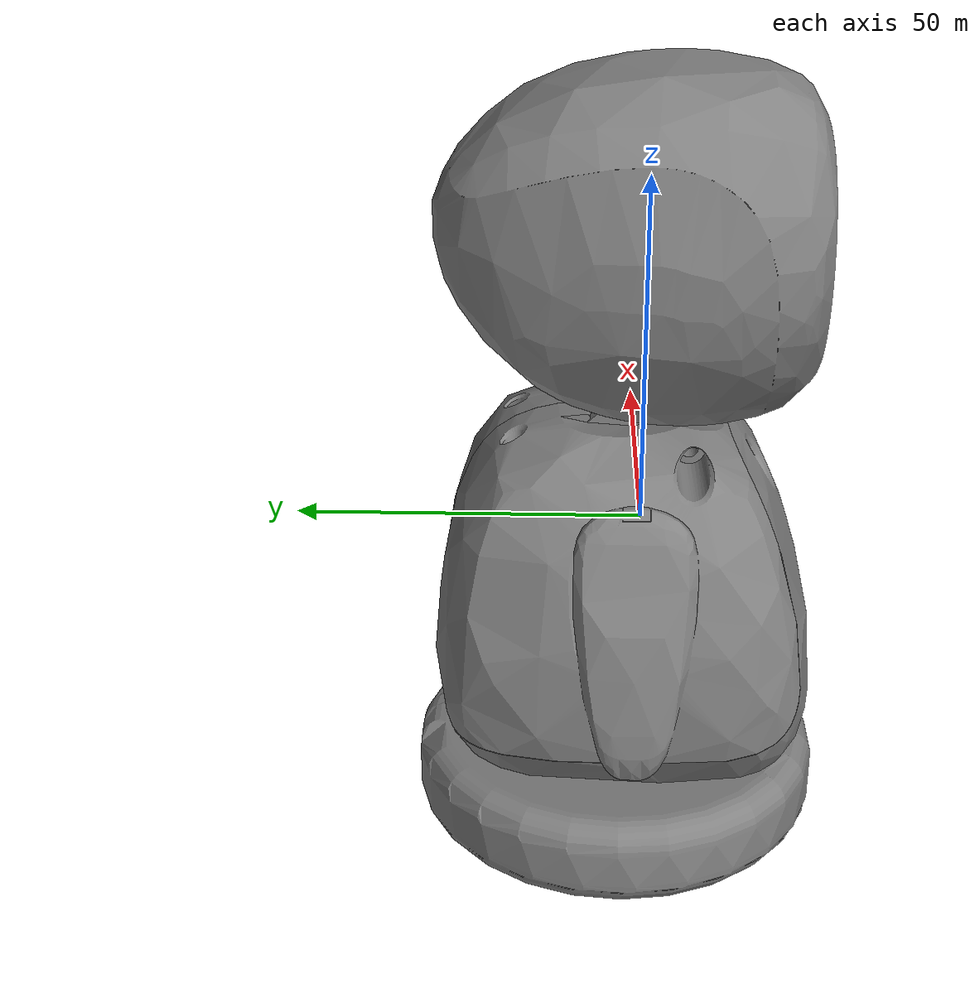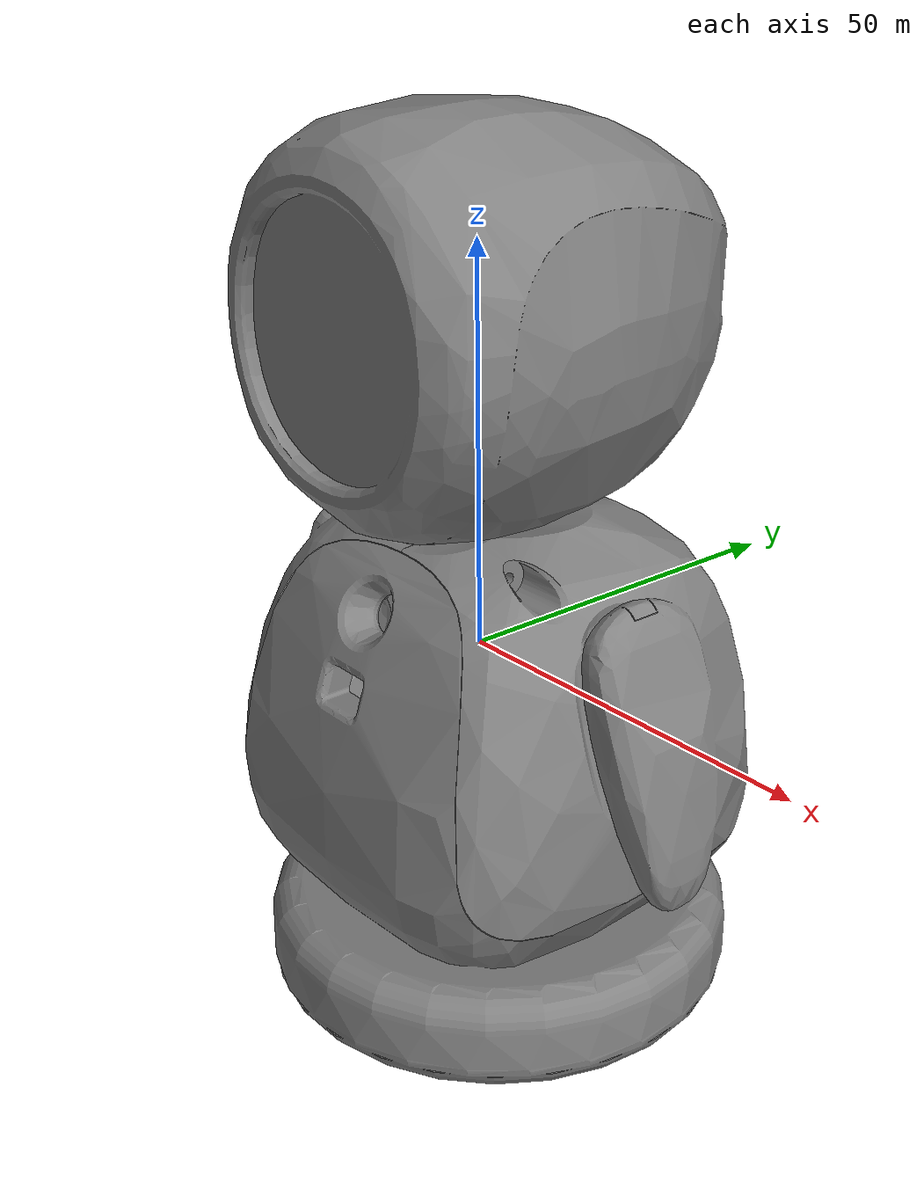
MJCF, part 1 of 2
<mujoco model="electronbot">
  <compiler angle="radian"/>

  <default>
    <joint armature="0.005" damping="5" frictionloss="0.1"/>
    <geom friction="0.5 0.1 0.1"/>
    <general ctrllimited="true" forcerange="-0.01 0.01" biasprm="0 -5 -1"/>
  </default>

  <asset>
    <texture type="2d" colorspace="auto" name="tex_ground" builtin="checker" rgb1="0.2 0.2 0.2" rgb2="0.3 0.3 0.3" width="512" height="512"/>
    <material name="mat_ground" texture="tex_ground" reflectance="0.2"/>
    <material name="mat_base" rgba="0.2 0.2 0.2 1"/>
    <material name="mat_body" rgba="0.85 0.85 0.85 1"/>
    <material name="mat_head" rgba="0.3 0.3 0.3 1"/>
    <material name="mat_arm" rgba="0.6 0.6 0.6 1"/>
    <material name="mat_camera" rgba="0 0 0 1"/>
    <material name="mat_target" rgba="1 0.2 0.2 0.6"/>
    <mesh name="base_link" vertex="6.18746 19.0113 -6.35 6.2 18.9 -11.9 6.18746 19.0113 -11.9 6.2 18.9 -6.35 6.15048 19.1169 -6.35 6.15048 19.1169 -11.9 6.09092 19.2117 -11.9 6.09092 19.2117 -6.35 6.01174 19.2909 -6.35 6.01174 19.2909 -11.9 5.91694 19.3505 -11.9 5.91694 19.3505 -6.35 5.81126 19.3875 -11.9 5.81126 19.3875 -6.35 5.7 19.4 -6.35 5.7 19.4 -11.9 5.81126 -3.18746 -6.35 5.7 -3.2 -11.9 5.81126 -3.18746 -11.9 5.7 -3.2 -6.35 5.91694 -3.15048 -6.35 5.91694 -3.15048 -11.9 6.01174 -3.09092 -11.9 6.01174 -3.09092 -6.35 6.09092 -3.01174 -6.35 6.09092 -3.01174 -11.9 6.15048 -2.91694 -11.9 6.15048 -2.91694 -6.35 6.18746 -2.81126 -11.9 6.18746 -2.81126 -6.35 6.2 -2.7 -6.35 6.2 -2.7 -11.9 -6.18746 -2.81126 -6.35 -6.2 -2.7 -11.9 -6.18746 -2.81126 -11.9 -6.2 -2.7 -6.35 -6.15048 -2.91694 -6.35 -6.15048 -2.91694 -11.9 -6.09092 -3.01174 -11.9 -6.09092 -3.01174 -6.35 -6.01174 -3.09092 -6.35 -6.01174 -3.09092 -11.9 -5.91694 -3.15048 -11.9 -5.91694 -3.15048 -6.35 -5.81126 -3.18746 -11.9 -5.81126 -3.18746 -6.35 -5.7 -3.2 -6.35 -5.7 -3.2 -11.9 -5.81126 19.3875 -6.35 -5.7 19.4 -11.9 -5.81126 19.3875 -11.9 -5.7 19.4 -6.35 -5.91694 19.3505 -6.35 -5.91694 19.3505 -11.9 -6.01174 19.2909 -11.9 -6.01174 19.2909 -6.35 -6.09092 19.2117 -6.35 -6.09092 19.2117 -11.9 -6.15048 19.1169 -11.9 -6.15048 19.1169 -6.35 -6.18746 19.0113 -11.9 -6.18746 19.0113 -6.35 -6.2 18.9 -6.35 -6.2 18.9 -11.9 -5.7 19.325 -6.2201 -5.7 19.25 -6.2 5.7 19.25 -6.2 5.7 19.325 -6.2201 -5.7 19.3799 -6.275 5.7 19.3799 -6.275 6.125 18.9 -6.2201 6.05 -2.7 -6.2 6.125 -2.7 -6.2201 6.05 18.9 -6.2 6.1799 18.9 -6.275 6.1799 -2.7 -6.275 5.7 -3.125 -6.2201 -5.7 -3.05 -6.2 -5.7 -3.125 -6.2201 5.7 -3.05 -6.2 5.7 -3.1799 -6.275 -5.7 -3.1799 -6.275 -6.125 -2.7 -6.2201 -6.05 -2.7 -6.2 -6.05 18.9 -6.2 -6.125 18.9 -6.2201 -6.1799 -2.7 -6.275 -6.1799 18.9 -6.275 -5.80679 19.3679 -6.275 -5.79457 19.3143 -6.2201 -5.79059 19.2381 -6.2 -5.90822 19.3324 -6.275 -5.8844 19.2829 -6.2201 -5.875 19.2031 -6.2 -5.99922 19.2752 -6.275 -6.03934 19.2393 -6.275 -5.96498 19.2323 -6.2201 -5.94749 19.1475 -6.2 -6.0752 19.1992 -6.275 -6.00052 19.2005 -6.2201 -6.11561 19.1399 -6.275 -6.03228 19.165 -6.2201 -6.00311 19.075 -6.2 -6.06806 19.1125 -6.2201 -6.16355 19.0242 -6.275 -6.11052 19.01 -6.2201 -6.03807 18.9906 -6.2 -6.16787 -2.80679 -6.275 -6.11434 -2.79457 -6.2201 -6.03807 -2.79059 -6.2 -6.13238 -2.90822 -6.275 -6.08291 -2.8844 -6.2201 -6.00311 -2.875 -6.2 -6.0752 -2.99921 -6.275 -6.03934 -3.03934 -6.275 -6.03228 -2.96498 -6.2201 -5.94749 -2.94749 -6.2 -5.99922 -3.0752 -6.275 -6.00052 -3.00052 -6.2201 -5.93995 -3.11561 -6.275 -5.96498 -3.03228 -6.2201 -5.875 -3.00311 -6.2 -5.9125 -3.06806 -6.2201 -5.82421 -3.16355 -6.275 -5.81 -3.11052 -6.2201 -5.79059 -3.03807 -6.2 5.80679 -3.16787 -6.275 5.79457 -3.11434 -6.2201 5.79059 -3.03807 -6.2 5.90822 -3.13238 -6.275 5.8844 -3.08291 -6.2201 5.875 -3.00311 -6.2 5.99922 -3.0752 -6.275 6.03934 -3.03934 -6.275 5.96498 -3.03228 -6.2201 5.94749 -2.94749 -6.2 6.0752 -2.99921 -6.275 6.00052 -3.00052 -6.2201 6.11561 -2.93995 -6.275 6.03228 -2.96498 -6.2201 6.00311 -2.875 -6.2 6.06806 -2.9125 -6.2201 6.16355 -2.82421 -6.275 6.11052 -2.81 -6.2201 6.03807 -2.79059 -6.2 6.16787 19.0068 -6.275 6.11434 18.9946 -6.2201 6.03807 18.9906 -6.2 6.13238 19.1082 -6.275 6.08291 19.0844 -6.2201 6.00311 19.075 -6.2 6.0752 19.1992 -6.275 6.03934 19.2393 -6.275 6.03228 19.165 -6.2201 5.94749 19.1475 -6.2 5.99922 19.2752 -6.275 6.00052 19.2005 -6.2201 5.93995 19.3156 -6.275 5.96498 19.2323 -6.2201 5.875 19.2031 -6.2 5.9125 19.2681 -6.2201 5.82421 19.3636 -6.275 5.81 19.3105 -6.2201 5.79059 19.2381 -6.2 5.7 19.2 -11.95 -5.7 19.2 -11.9 5.7 19.2 -11.9 -5.7 19.2 -11.95 -5.79271 19.1853 -11.9 -5.79271 19.1853 -11.95 -5.87634 19.1427 -11.9 -5.87634 19.1427 -11.95 -5.94271 19.0763 -11.9 -5.94271 19.0763 -11.95 -5.98532 18.9927 -11.9 -5.98532 18.9927 -11.95 -6 18.9 -11.9 -6 18.9 -11.95 -6 -2.7 -11.95 -6 -2.7 -11.9 -5.98532 -2.79271 -11.9 -5.98532 -2.79271 -11.95 -5.94271 -2.87634 -11.9 -5.94271 -2.87634 -11.95 -5.87634 -2.9427 -11.9 -5.87634 -2.9427 -11.95 -5.79271 -2.98532 -11.9 -5.79271 -2.98532 -11.95 -5.7 -3 -11.9 -5.7 -3 -11.95 5.7 -3 -11.9 5.7 -3 -11.95 5.79271 -2.98532 -11.9 5.79271 -2.98532 -11.95 5.87634 -2.9427 -11.9 5.87634 -2.9427 -11.95 5.94271 -2.87634 -11.9 5.94271 -2.87634 -11.95 5.98532 -2.79271 -11.9 5.98532 -2.79271 -11.95 6 -2.7 -11.9 6 -2.7 -11.95 6 18.9 -11.95 6 18.9 -11.9 5.98532 18.9927 -11.9 5.98532 18.9927 -11.95 5.94271 19.0763 -11.9 5.94271 19.0763 -11.95 5.87634 19.1427 -11.9 5.87634 19.1427 -11.95 5.79271 19.1853 -11.9 5.79271 19.1853 -11.95 -6.01174 -3.09092 -11.95 -5.91694 -3.15048 -11.95 -6.15048 -2.91694 -11.95 -6.09092 -3.01174 -11.95 -5.81126 -3.18746 -11.95 -6.18746 -2.81126 -11.95 -6.2 -2.7 -11.95 -5.7 -3.2 -11.95 5.7 -3.2 -11.95 5.81126 -3.18746 -11.95 5.91694 -3.15048 -11.95 6.01174 -3.09092 -11.95 6.09092 -3.01174 -11.95 6.15048 -2.91694 -11.95 6.18746 -2.81126 -11.95 6.2 -2.7 -11.95 -6.18746 19.0113 -11.95 -6.2 18.9 -11.95 -6.15048 19.1169 -11.95 -6.09092 19.2117 -11.95 -6.01174 19.2909 -11.95 -5.91694 19.3505 -11.95 -5.81126 19.3875 -11.95 -5.7 19.4 -11.95 5.7 19.4 -11.95 6.2 18.9 -11.95 6.18746 19.0113 -11.95 5.81126 19.3875 -11.95 5.91694 19.3505 -11.95 6.15048 19.1169 -11.95 6.09092 19.2117 -11.95 6.01174 19.2909 -11.95 5.7 -3 -21.8 -5.7 -3 -21.75 -5.7 -3 -21.8 5.7 -3 -21.75 -5.79271 -2.98532 -21.8 -5.79271 -2.98532 -21.75 -5.87634 -2.9427 -21.8 -5.87634 -2.9427 -21.75 -5.94271 -2.87634 -21.8 -5.94271 -2.87634 -21.75 -5.98532 -2.79271 -21.8 -5.98532 -2.79271 -21.75 -6 -2.7 -21.8 -6 -2.7 -21.75 -6 18.9 -21.75 -6 18.9 -21.8 -5.98532 18.9927 -21.8 -5.98532 18.9927 -21.75 -5.94271 19.0763 -21.8 -5.94271 19.0763 -21.75 -5.87634 19.1427 -21.8 -5.87634 19.1427 -21.75 -5.79271 19.1853 -21.8 -5.79271 19.1853 -21.75 -5.7 19.2 -21.8 -5.7 19.2 -21.75 5.7 19.2 -21.75 5.7 19.2 -21.8 5.79271 19.1853 -21.8 5.79271 19.1853 -21.75 5.87634 19.1427 -21.8 5.87634 19.1427 -21.75 5.94271 19.0763 -21.8 5.94271 19.0763 -21.75 5.98532 18.9927 -21.8 5.98532 18.9927 -21.75 6 18.9 -21.8 6 18.9 -21.75 6 -2.7 -21.75 6 -2.7 -21.8 5.98532 -2.79271 -21.8 5.98532 -2.79271 -21.75 5.94271 -2.87634 -21.8 5.94271 -2.87634 -21.75 5.87634 -2.9427 -21.8 5.87634 -2.9427 -21.75 5.79271 -2.98532 -21.8 5.79271 -2.98532 -21.75 -6.01174 -3.09092 -21.75 -6.09092 -3.01174 -21.75 -5.91694 -3.15048 -21.75 -6.15048 -2.91694 -21.75 -6.18746 -2.81126 -21.75 -5.81126 -3.18746 -21.75 -5.7 -3.2 -21.75 -6.2 -2.7 -21.75 5.7 -3.2 -21.75 5.81126 -3.18746 -21.75 5.91694 -3.15048 -21.75 6.01174 -3.09092 -21.75 6.09092 -3.01174 -21.75 6.15048 -2.91694 -21.75 6.18746 -2.81126 -21.75 6.2 -2.7 -21.75 -6.2 18.9 -21.75 -6.18746 19.0113 -21.75 -6.15048 19.1169 -21.75 -6.09092 19.2117 -21.75 -6.01174 19.2909 -21.75 -5.91694 19.3505 -21.75 -5.81126 19.3875 -21.75 -5.7 19.4 -21.75 6.2 18.9 -21.75 5.7 19.4 -21.75 6.18746 19.0113 -21.75 5.81126 19.3875 -21.75 6.15048 19.1169 -21.75 5.91694 19.3505 -21.75 6.09092 19.2117 -21.75 6.01174 19.2909 -21.75 -2.8299 8.75 -32.725 -2.85 8.50613 -32.65 -2.85 8.75 -32.65 -2.80597 8.47928 -32.7562 -2.775 8.75 -32.7799 -2.7 8.4141 -32.8 -2.7 8.75 -32.8 2.8299 8.75 -32.725 2.76718 9.43205 -32.65 2.85 8.75 -32.65 -2.74767 9.42724 -32.725 -2.76718 9.43205 -32.65 -2.69436 9.4141 -32.7799 -2.62154 9.39615 -32.8 -2.50575 10.0651 -32.725 -2.52355 10.0745 -32.65 -2.45714 10.0396 -32.7799 -2.39073 10.0048 -32.8 -2.11821 10.6266 -32.725 -2.13326 10.6399 -32.65 -2.07712 10.5902 -32.7799 -2.02098 10.5404 -32.8 -1.53377 10.9721 -32.8 -1.60757 11.079 -32.725 -1.61899 11.0955 -32.65 -1.57638 11.0338 -32.7799 -0.957433 11.2745 -32.8 -1.0035 11.396 -32.725 -1.01062 11.4148 -32.65 -0.984029 11.3447 -32.7799 -0.341107 11.5593 -32.725 -0.343529 11.5792 -32.65 -0.334489 11.5048 -32.7799 -0.325449 11.4303 -32.8 0.325449 11.4303 -32.8 0.341107 11.5593 -32.725 0.343529 11.5792 -32.65 0.334489 11.5048 -32.7799 1.0035 11.396 -32.725 1.01062 11.4148 -32.65 0.984029 11.3447 -32.7799 0.957433 11.2745 -32.8 1.60757 11.079 -32.725 1.61899 11.0955 -32.65 1.57638 11.0338 -32.7799 1.53377 10.9721 -32.8 2.02098 10.5404 -32.8 2.11821 10.6266 -32.725 2.13326 10.6399 -32.65 2.07712 10.5902 -32.7799 2.50575 10.0651 -32.725 2.52355 10.0745 -32.65 2.45714 10.0396 -32.7799 2.39073 10.0048 -32.8 2.62154 9.39615 -32.8 2.74767 9.42724 -32.725 2.69436 9.4141 -32.7799 2.775 8.75 -32.7799 2.7 8.75 -32.8 2.85 8.50613 -32.65 2.80606 8.47933 -32.7561 2.7 8.4141 -32.8 -2.925 8.75 -28.5201 -3 8.59665 -28.5 -3 8.75 -28.5 -2.89384 8.53274 -28.544 -2.8701 8.75 -28.575 -2.85 8.50613 -28.65 -2.85 8.75 -28.65 3 8.75 -28.5 2.925 8.75 -28.5201 2.91283 9.46795 -28.5 -2.7867 9.43686 -28.575 -2.76718 9.43205 -28.65 -2.84 9.45 -28.5201 -2.91283 9.46795 -28.5 -2.54134 10.0838 -28.575 -2.52355 10.0745 -28.65 -2.58996 10.1093 -28.5201 -2.65637 10.1442 -28.5 -2.1483 10.6532 -28.575 -2.13326 10.6399 -28.65 -2.18939 10.6896 -28.5201 -2.24553 10.7394 -28.5 -1.6304 11.112 -28.575 -1.61899 11.0955 -28.65 -1.66159 11.1572 -28.5201 -1.70419 11.219 -28.5 -1.01775 11.4336 -28.575 -1.01062 11.4148 -28.65 -1.03722 11.4849 -28.5201 -1.06381 11.555 -28.5 -0.345952 11.5992 -28.575 -0.343529 11.5792 -28.65 -0.35257 11.6537 -28.5201 -0.36161 11.7281 -28.5 0.345952 11.5992 -28.575 0.343529 11.5792 -28.65 1.01062 11.4148 -28.65 0.35257 11.6537 -28.5201 0.36161 11.7281 -28.5 1.01775 11.4336 -28.575 1.03722 11.4849 -28.5201 1.06381 11.555 -28.5 1.6304 11.112 -28.575 1.61899 11.0955 -28.65 1.66159 11.1572 -28.5201 1.70419 11.219 -28.5 2.1483 10.6532 -28.575 2.13326 10.6399 -28.65 2.18939 10.6896 -28.5201 2.24553 10.7394 -28.5 2.54134 10.0838 -28.575 2.52355 10.0745 -28.65 2.58996 10.1093 -28.5201 2.65637 10.1442 -28.5 2.7867 9.43686 -28.575 2.76718 9.43205 -28.65 2.85 8.75 -28.65 2.8701 8.75 -28.575 2.84 9.45 -28.5201 -4.01545 7.91921 -28.5 -4.73847 6.99836 -28.65 -4.88252 7.05998 -28.5 -3.86841 7.84515 -28.65 -5.47606 5.99972 -28.544 -5.90709 4.88317 -28.65 -5.95096 4.89018 -28.5439 -5.42683 5.99825 -28.65 -6.05 4.92873 -28.5 -5.56916 6.05072 -28.5 -4.8009 6.99211 -28.544 -3.94832 7.83697 -28.544 -2.94984 8.50308 -28.544 3 8.59665 -28.5 2.89392 8.53279 -28.5439 2.85 8.50613 -28.65 -6.18637 3.40172 -28.5849 -6.16722 3.63667 -28.65 -6.2 3 -28.65 -6.19955 3 -28.5007 -6.13203 3.94983 -28.5544 -6.13726 3.87532 -28.6014 -6.06924 4.26662 -28.65 -6.04463 4.3823 -28.6112 3.86841 7.84515 -28.65 4.73847 6.99836 -28.65 4.01545 7.91921 -28.5 5.42683 5.99825 -28.65 4.88252 7.05998 -28.5 5.95096 4.89018 -28.5439 5.90709 4.88317 -28.65 5.56916 6.05072 -28.5 6.05 4.92873 -28.5 3.89581 7.87947 -28.5439 4.77204 7.02669 -28.5439 5.46527 6.01949 -28.5439 -3.24767 -2.33286 -28.5439 -1.88317 -2.90709 -28.65 -1.89018 -2.95096 -28.5439 -3.22482 -2.29533 -28.65 -1.92873 -3.05 -28.5 -3.30284 -2.42345 -28.5 -4.41513 -1.41513 -28.5439 -4.38406 -1.38406 -28.65 -4.49013 -1.49013 -28.5 -5.33286 -0.24767 -28.5439 -5.29533 -0.224818 -28.65 -5.90709 1.11683 -28.65 -5.95096 1.10982 -28.5439 -6.05 1.07127 -28.5 -5.42345 -0.302837 -28.5 -6.1799 -3.05 -28.425 -6.2 -3.05 -28.35 -6.2 1.07127 -28.35 -6.15607 1.07803 -28.4561 -6.125 -3.05 -28.4799 -6.05 -3.05 -28.5 -6.2 4.92873 -28.35 -6.2 19.25 -28.35 -6.1799 19.25 -28.425 -6.15607 4.92197 -28.4561 -6.125 19.25 -28.4799 -6.05 19.25 -28.5 6.14268 4.13296 -28.4927 6.15607 4.92197 -28.4561 6.19955 3 -28.5007 6.13203 3.94983 -28.5544 6.10347 4.38814 -28.5069 -0.401722 -3.18637 -28.5849 -0.636675 -3.16722 -28.65 0 -3.2 -28.65 0 -3.19955 -28.5007 -0.949832 -3.13203 -28.5544 -0.875325 -3.13726 -28.6014 -1.26662 -3.06924 -28.65 -1.3823 -3.04463 -28.6112 -6.07704 -3.18592 -28.4074 -6.05 -3.1799 -28.425 -6.05 -3.2 -28.35 -6.125 -3.1799 -28.35 -6.12699 -3.16523 -28.4074 -6.16523 -3.12699 -28.4074 -6.1799 -3.125 -28.35 -6.09059 -3.14799 -28.4561 -6.05 -3.125 -28.4799 -6.18592 -3.07704 -28.4074 -6.125 -3.125 -28.4561 -6.0612 -3.1063 -28.4886 -6.14799 -3.09059 -28.4561 -6.08189 -3.09773 -28.4886 -6.09773 -3.08189 -28.4886 -6.1063 -3.0612 -28.4886 -6.18592 19.277 -28.4074 -6.1799 19.325 -28.35 -6.16523 19.327 -28.4074 -6.12699 19.3652 -28.4074 -6.125 19.3799 -28.35 -6.14799 19.2906 -28.4561 -6.07704 19.3859 -28.4074 -6.05 19.4 -28.35 -6.05 19.3799 -28.425 -6.125 19.325 -28.4561 -6.1063 19.2612 -28.4886 -6.09059 19.348 -28.4561 -6.05 19.325 -28.4799 -6.09773 19.2819 -28.4886 -6.08189 19.2977 -28.4886 -6.0612 19.3063 -28.4886 6.1799 19.25 -28.425 6.2 19.25 -28.35 6.2 4.92873 -28.35 6.125 19.25 -28.4799 6.05 19.25 -28.5 6.2 1.07127 -28.35 6.2 -3.05 -28.35 6.1799 -3.05 -28.425 6.15607 1.07803 -28.4561 6.125 -3.05 -28.4799 6.05 1.07127 -28.5 6.05 -3.05 -28.5 5.33286 -0.24767 -28.5439 5.90709 1.11683 -28.65 5.95096 1.10982 -28.5439 5.29533 -0.224818 -28.65 5.42345 -0.302837 -28.5 4.41513 -1.41513 -28.5439 4.38406 -1.38406 -28.65 4.49013 -1.49013 -28.5 3.24767 -2.33286 -28.5439 3.22482 -2.29533 -28.65 1.88317 -2.90709 -28.65 1.89018 -2.95096 -28.5439 1.92873 -3.05 -28.5 3.30284 -2.42345 -28.5 6.05 -3.1799 -28.425 6.05 -3.2 -28.35 1.92873 -3.2 -28.35 1.92197 -3.15607 -28.4561 6.05 -3.125 -28.4799 -1.92873 -3.2 -28.35 -1.92197 -3.15607 -28.4561 -6.18858 -3.1074 -24.3074 -6.2 -3.05 -24.25 -6.15607 -3.15607 -24.3561 -6.1074 -3.18858 -24.3886 -6.05 -3.2 -24.4 -6.1074 19.3886 -24.3886 -6.05 19.4 -24.4 -6.15607 19.3561 -24.3561 -6.18858 19.3074 -24.3074 -6.2 19.25 -24.25 6.05 19.4 -28.35 6.05 19.3799 -28.425 6.05 19.325 -28.4799 6.07704 19.3859 -28.4074 6.125 19.3799 -28.35 6.12699 19.3652 -28.4074 6.16523 19.327 -28.4074 6.1799 19.325 -28.35 6.09059 19.348 -28.4561 6.18592 19.277 -28.4074 6.125 19.325 -28.4561 6.0612 19.3063 -28.4886 6.14799 19.2906 -28.4561 6.08189 19.2977 -28.4886 6.09773 19.2819 -28.4886 6.1063 19.2612 -28.4886 6.18592 -3.07704 -28.4074 6.1799 -3.125 -28.35 6.16523 -3.12699 -28.4074 6.12699 -3.16523 -28.4074 6.125 -3.1799 -28.35 6.14799 -3.09059 -28.4561 6.07704 -3.18592 -28.4074 6.125 -3.125 -28.4561 6.1063 -3.0612 -28.4886 6.09059 -3.14799 -28.4561 6.09773 -3.08189 -28.4886 6.08189 -3.09773 -28.4886 6.0612 -3.1063 -28.4886 -6.2 -3.2 -24.25 -6.1799 -3.2 -24.325 -6.125 -3.2 -24.3799 -6.2 23.75 -24.25 -6.1799 23.75 -24.325 -6.125 23.75 -24.3799 -6.05 23.75 -24.4 6.18858 19.3074 -24.3074 6.2 19.25 -24.25 6.15607 19.3561 -24.3561 6.1074 19.3886 -24.3886 6.05 19.4 -24.4 6.1074 -3.18858 -24.3886 6.05 -3.2 -24.4 6.15607 -3.15607 -24.3561 6.18858 -3.1074 -24.3074 6.2 -3.05 -24.25 -5.7 24.2299 -24.325 -5.81126 24.2375 -24.25 -5.7 24.25 -24.25 -6.16787 23.8568 -24.325 -6.18746 23.8613 -24.25 -6.11434 23.8446 -24.3799 -6.03807 23.8406 -24.4 -6.13238 23.9582 -24.325 -6.15048 23.9669 -24.25 -6.08291 23.9344 -24.3799 -6.00311 23.925 -24.4 -6.0752 24.0492 -24.325 -6.09092 24.0617 -24.25 -6.03934 24.0893 -24.325 -6.01174 24.1409 -24.25 -6.03228 24.015 -24.3799 -5.94749 23.9975 -24.4 -5.99922 24.1252 -24.325 -6.00052 24.0505 -24.3799 -5.93995 24.1656 -24.325 -5.91694 24.2005 -24.25 -5.96498 24.0823 -24.3799 -5.875 24.0531 -24.4 -5.9125 24.1181 -24.3799 -5.82421 24.2136 -24.325 -5.81 24.1605 -24.3799 -5.7 24.175 -24.3799 -5.7 24.1 -24.4 -5.79059 24.0881 -24.4 6.2 23.75 -24.25 6.1799 23.75 -24.325 6.125 23.75 -24.3799 6.05 23.75 -24.4 -0.6 24.25 -24.25 -0.6 24.2299 -24.325 -0.6 24.175 -24.3799 -0.6 24.1 -24.4 6.18746 23.8613 -24.25 5.80679 24.2179 -24.325 5.7 24.2299 -24.325 5.7 24.25 -24.25 5.81126 24.2375 -24.25 5.79457 24.1643 -24.3799 5.7 24.1 -24.4 5.7 24.175 -24.3799 5.79059 24.0881 -24.4 5.90822 24.1824 -24.325 5.91694 24.2005 -24.25 5.8844 24.1329 -24.3799 5.875 24.0531 -24.4 5.99922 24.1252 -24.325 6.01174 24.1409 -24.25 6.03934 24.0893 -24.325 6.09092 24.0617 -24.25 5.96498 24.0823 -24.3799 5.94749 23.9975 -24.4 6.0752 24.0492 -24.325 6.00052 24.0505 -24.3799 6.11561 23.99 -24.325 6.15048 23.9669 -24.25 6.03228 24.015 -24.3799 6.00311 23.925 -24.4 6.06806 23.9625 -24.3799 6.16355 23.8742 -24.325 6.11052 23.86 -24.3799 6.03807 23.8406 -24.4 0.6 24.2299 -24.325 0.6 24.25 -24.25 0.6 24.175 -24.3799 0.6 24.1 -24.4 -1.38814 -3.10347 -28.5069 1.12323 -3.11871 -28.5298 0.949832 -3.13203 -28.5544 1.38814 -3.10347 -28.5069 0.636675 -3.16722 -28.65 0.875325 -3.13726 -28.6014 1.26662 -3.06924 -28.65 1.3823 -3.04463 -28.6112 6.16722 3.63667 -28.65 6.2 3 -28.65 6.06924 4.26662 -28.65 6.13726 3.87532 -28.6014 6.18637 2.59828 -28.5849 6.13203 2.05017 -28.5544 6.16722 2.36333 -28.65 6.13726 2.12468 -28.6014 6.06924 1.73338 -28.65 6.04463 1.6177 -28.6112 6.14268 1.86704 -28.4927 6.10347 1.61186 -28.5069 6.20007 2.59391 -28.421 6.2 3 -28.35 6.19473 2.1136 -28.4141 6.19473 3.8864 -28.4141 -6.14268 4.13296 -28.4927 -6.10347 4.38814 -28.5069 -6.19473 3.8864 -28.4141 -6.2 3 -28.35 -6.19473 2.1136 -28.4141 -6.14268 1.86704 -28.4927 -6.13203 2.05017 -28.5544 -6.10347 1.61186 -28.5069 -6.16722 2.36333 -28.65 -6.13726 2.12468 -28.6014 -6.06924 1.73338 -28.65 -6.04463 1.6177 -28.6112 6.18746 23.8613 -21.8 6.2 23.75 -21.8 6.15048 23.9669 -21.8 6.09092 24.0617 -21.8 6.01174 24.1409 -21.8 5.91694 24.2005 -21.8 5.81126 24.2375 -21.8 5.7 24.25 -21.8 -5.81126 24.2375 -21.8 -5.7 24.25 -21.8 -5.91694 24.2005 -21.8 -6.01174 24.1409 -21.8 -6.09092 24.0617 -21.8 -6.15048 23.9669 -21.8 -6.18746 23.8613 -21.8 -6.2 23.75 -21.8 -4.36694 11.9495 -28.3 -4.46174 12.0091 -28.3 -4.54092 12.0883 -28.3 -4.15 11.9 -28.3 -4.26126 11.9125 -28.3 -4.60048 12.1831 -28.3 -4.63746 12.2887 -28.3 -4.65 12.4 -28.3 -4.65 17.6 -28.3 -4.60048 17.8169 -28.3 -4.63746 17.7113 -28.3 -4.46174 17.9909 -28.3 -4.54092 17.9117 -28.3 -4.15 18.1 -28.3 -4.36694 18.0505 -28.3 -4.26126 18.0875 -28.3 4.36694 11.9495 -28.3 4.26126 11.9125 -28.3 4.15 11.9 -28.3 4.46174 12.0091 -28.3 4.63746 12.2887 -28.3 4.60048 12.1831 -28.3 4.54092 12.0883 -28.3 4.65 12.4 -28.3 4.15 18.1 -28.3 4.65 17.6 -28.3 4.36694 18.0505 -28.3 4.26126 18.0875 -28.3 4.54092 17.9117 -28.3 4.46174 17.9909 -28.3 4.60048 17.8169 -28.3 4.63746 17.7113 -28.3 4.15 18.1 -28.5 -4.15 18.1 -28.5 4.26126 18.0875 -28.5 4.36694 18.0505 -28.5 4.46174 17.9909 -28.5 4.54092 17.9117 -28.5 4.60048 17.8169 -28.5 4.63746 17.7113 -28.5 4.65 17.6 -28.5 4.65 12.4 -28.5 4.63746 12.2887 -28.5 4.60048 12.1831 -28.5 4.54092 12.0883 -28.5 4.46174 12.0091 -28.5 4.36694 11.9495 -28.5 4.26126 11.9125 -28.5 4.15 11.9 -28.5 -4.15 11.9 -28.5 -4.26126 11.9125 -28.5 -4.36694 11.9495 -28.5 -4.46174 12.0091 -28.5 -4.54092 12.0883 -28.5 -4.60048 12.1831 -28.5 -4.63746 12.2887 -28.5 -4.65 12.4 -28.5 -4.65 17.6 -28.5 -4.63746 17.7113 -28.5 -4.60048 17.8169 -28.5 -4.54092 17.9117 -28.5 -4.46174 17.9909 -28.5 -4.36694 18.0505 -28.5 -4.26126 18.0875 -28.5 -1.1281 20.6985 -22.8 -1.48794 21.0136 -22.8 -5.2 19.4 -22.8 -1.7627 21.4051 -22.8 -0.703743 20.4779 -22.8 -1.93665 21.8506 -22.8 -5.2 23.25 -22.8 -0.23914 20.3643 -22.8 -1.99984 22.3247 -22.8 0.23914 20.3643 -22.8 -1.94867 22.8002 -22.8 -1.78606 23.25 -22.8 5.2 19.4 -22.8 1.93665 21.8506 -22.8 1.7627 21.4051 -22.8 1.48794 21.0136 -22.8 1.1281 20.6985 -22.8 0.703743 20.4779 -22.8 5.2 23.25 -22.8 1.78606 23.25 -22.8 1.94867 22.8002 -22.8 1.99984 22.3247 -22.8 -5.2 23.25 -21.8 -1.78606 23.25 -21.8 -5.2 19.4 -21.8 5.2 23.25 -21.8 5.2 19.4 -21.8 1.78606 23.25 -21.8 0.6 23.15 -21.8 0.6 24.25 -21.8 0.6 23.15 -24.4 -0.6 23.15 -21.8 -0.6 23.15 -24.4 -0.6 24.25 -21.8 0.708365 2.62822 -32.8 0.598809 2.4695 -32.8 0.454452 2.34161 -32.8 0.8 3 -32.8 0.776753 2.80855 -32.8 -0.454452 2.34161 -32.8 -0.096429 2.20583 -32.8 -0.283684 2.25199 -32.8 -0.598809 2.4695 -32.8 0.096429 2.20583 -32.8 0.283684 2.25199 -32.8 0.283684 3.74801 -32.8 0.708365 3.37178 -32.8 0.776753 3.19145 -32.8 0.598809 3.5305 -32.8 0.454452 3.65839 -32.8 -0.776753 2.80855 -32.8 -0.708365 2.62822 -32.8 -0.283684 3.74801 -32.8 0.096429 3.79417 -32.8 -0.096429 3.79417 -32.8 -0.708365 3.37178 -32.8 -0.8 3 -32.8 -0.776753 3.19145 -32.8 -0.598809 3.5305 -32.8 -0.454452 3.65839 -32.8 0.454452 2.34161 -36 1.83385 1.37535 -36 1.39176 0.983689 -36 0.598809 2.4695 -36 0.708365 2.62822 -36 2.16937 1.86143 -36 0.283684 2.25199 -36 0.868782 0.70921 -36 0.776753 2.80855 -36 2.37881 2.41368 -36 0.096429 2.20583 -36 0.295315 0.567863 -36 0.8 3 -36 2.45 3 -36 -0.096429 2.20583 -36 -0.295315 0.567863 -36 0.776753 3.19145 -36 2.37881 3.58632 -36 -0.283684 2.25199 -36 -0.868782 0.70921 -36 0.708365 3.37178 -36 2.16937 4.13857 -36 -0.454452 2.34161 -36 -1.39176 0.983689 -36 0.598809 3.5305 -36 1.83385 4.62465 -36 -0.598809 2.4695 -36 0.454452 3.65839 -36 -1.83385 1.37535 -36 1.39176 5.01631 -36 -2.16937 1.86143 -36 -0.708365 2.62822 -36 0.868782 5.29079 -36 0.283684 3.74801 -36 -2.37881 2.41368 -36 -0.776753 2.80855 -36 -0.8 3 -36 0.295315 5.43214 -36 0.096429 3.79417 -36 -0.096429 3.79417 -36 -2.45 3 -36 -0.295315 5.43214 -36 -2.37881 3.58632 -36 -0.776753 3.19145 -36 -0.868782 5.29079 -36 -0.283684 3.74801 -36 -0.454452 3.65839 -36 -2.16937 4.13857 -36 -0.708365 3.37178 -36 -0.598809 3.5305 -36 -1.39176 5.01631 -36 -1.83385 4.62465 -36 1.83385 1.37535 -32.8 5.0048 -0.399186 -32.8 4.03741 -1.50575 -32.8 1.39176 0.983689 -32.8 2.83173 -2.34638 -32.8 2.16937 1.86143 -32.8 5.6768 0.908004 -32.8 0.868782 0.70921 -32.8 1.45892 -2.87146 -32.8 2.37881 2.41368 -32.8 6.01375 2.33867 -32.8 0.295315 0.567863 -32.8 0 -3.05 -32.8 2.45 3 -32.8 5.99575 3.80836 -32.8 -0.295315 0.567863 -32.8 -1.45892 -2.87146 -32.8 2.37881 3.58632 -32.8 5.62388 5.23034 -32.8 -0.868782 0.70921 -32.8 -2.83173 -2.34638 -32.8 2.16937 4.13857 -32.8 4.92009 6.52069 -32.8 -1.39176 0.983689 -32.8 -4.03741 -1.50575 -32.8 1.83385 4.62465 -32.8 -1.83385 1.37535 -32.8 3.9259 7.60324 -32.8 1.39176 5.01631 -32.8 -5.0048 -0.399186 -32.8 -2.16937 1.86143 -32.8 0.868782 5.29079 -32.8 0.295315 5.43214 -32.8 -5.6768 0.908004 -32.8 -2.37881 2.41368 -32.8 -6.01375 2.33867 -32.8 -2.45 3 -32.8 -5.99575 3.80836 -32.8 -2.37881 3.58632 -32.8 -5.62388 5.23034 -32.8 -2.16937 4.13857 -32.8 -0.868782 5.29079 -32.8 -1.39176 5.01631 -32.8 -0.295315 5.43214 -32.8 -4.92009 6.52069 -32.8 -1.83385 4.62465 -32.8 -3.9259 7.60324 -32.8 0.841058 21.8091 -24.4 0.68122 21.6179 -24.4 0.479091 21.4722 -24.4 0.948683 22.0338 -24.4 0.247219 21.381 -24.4 0.997413 22.2781 -24.4 0 21.35 -24.4 0.984223 22.5269 -24.4 0.909932 22.7648 -24.4 0.779151 22.9768 -24.4 -0.779151 22.9768 -24.4 -0.909932 22.7648 -24.4 -0.247219 21.381 -24.4 -0.479091 21.4722 -24.4 -0.68122 21.6179 -24.4 -0.841058 21.8091 -24.4 -0.948683 22.0338 -24.4 -0.997413 22.2781 -24.4 -0.984223 22.5269 -24.4 -6.2 -3.2 -21.8 -0.968844 -3.2 -28.35 6.2 -3.2 -21.8 0.968844 -3.2 -28.35 0 -3.2 -28.452 6.2 -3.2 -24.25 6.1799 -3.2 -24.325 6.125 -3.2 -24.3799 -4.0873 7.66197 -32.65 -5.08605 6.54572 -32.65 -5.78795 5.22252 -32.65 -6.15205 3.76961 -32.65 -6.15708 2.27178 -32.65 -5.80277 0.81645 -32.65 -5.10978 -0.511436 -32.65 -4.11856 -1.63438 -32.65 -2.88696 -2.48684 -32.65 -1.48687 -3.01907 -32.65 0 -3.2 -32.65 1.48687 -3.01907 -32.65 2.88696 -2.48684 -32.65 4.11856 -1.63438 -32.65 5.10978 -0.511436 -32.65 5.80277 0.81645 -32.65 6.15708 2.27178 -32.65 6.15205 3.76961 -32.65 5.78795 5.22252 -32.65 5.08605 6.54572 -32.65 4.0873 7.66197 -32.65 0.779151 22.9768 -21.8 0.909932 22.7648 -21.8 0.984223 22.5269 -21.8 0.997413 22.2781 -21.8 0.948683 22.0338 -21.8 0.841058 21.8091 -21.8 0.68122 21.6179 -21.8 0.479091 21.4722 -21.8 0 21.35 -21.8 0.247219 21.381 -21.8 -0.247219 21.381 -21.8 -0.479091 21.4722 -21.8 -0.68122 21.6179 -21.8 -0.841058 21.8091 -21.8 -0.948683 22.0338 -21.8 -0.984223 22.5269 -21.8 -0.997413 22.2781 -21.8 -0.909932 22.7648 -21.8 -0.779151 22.9768 -21.8 -1.94867 22.8002 -21.8 -1.99984 22.3247 -21.8 -1.93665 21.8506 -21.8 -1.7627 21.4051 -21.8 -1.48794 21.0136 -21.8 -1.1281 20.6985 -21.8 -0.703743 20.4779 -21.8 -0.23914 20.3643 -21.8 0.23914 20.3643 -21.8 0.703743 20.4779 -21.8 1.1281 20.6985 -21.8 1.48794 21.0136 -21.8 1.7627 21.4051 -21.8 1.93665 21.8506 -21.8 1.99984 22.3247 -21.8 1.94867 22.8002 -21.8 3.99472 7.68393 -32.7561 5.00633 6.58241 -32.7561 5.72247 5.26944 -32.7561 6.10086 3.82253 -32.7561 6.11917 2.32707 -32.7561 5.77631 0.871331 -32.7561 5.09254 -0.458773 -32.7561 4.10819 -1.58474 -32.7561 2.88137 -2.4401 -32.7561 1.4845 -2.97439 -32.7561 0 -3.15606 -32.7561 -1.47633 -2.97641 -32.7561 -2.8665 -2.44795 -32.7561 -4.08937 -1.60153 -32.7561 -5.07356 -0.486548 -32.7561 -5.76164 0.831927 -32.7561 -6.11344 2.27694 -32.7561 -6.10844 3.76415 -32.7561 -5.74693 5.20677 -32.7561 -5.05 6.52059 -32.7561 -4.05833 7.62893 -32.7561 -2.8298 8.46711 -32.7561 -0.406091 -3.20007 -28.421 -0.886397 -3.19473 -28.4141 0.406091 -3.20007 -28.421 0.886397 -3.19473 -28.4141 -14.7583 -0.637598 -29 -15 3 -29.2 -15.2 3 -29 -14.5641 -0.589735 -29.2 -13.4589 -4.06379 -29 -13.2818 -3.97085 -29.2 -11.3774 -7.07946 -29 -11.2277 -6.94684 -29.2 -8.63458 -9.50935 -29 -8.52097 -9.34476 -29.2 -5.38999 -11.2122 -29 -5.31907 -11.0252 -29.2 -1.83216 -12.0892 -29 -1.80805 -11.8906 -29.2 1.83216 -12.0892 -29 1.80805 -11.8906 -29.2 5.38999 -11.2122 -29 5.31907 -11.0252 -29.2 8.63458 -9.50935 -29 8.52097 -9.34476 -29.2 11.3774 -7.07946 -29 11.2277 -6.94684 -29.2 13.4589 -4.06379 -29 13.2818 -3.97085 -29.2 14.7583 -0.637598 -29 14.5641 -0.589735 -29.2 15.2 3 -29 15 3 -29.2 14.7583 6.6376 -29 14.5641 6.58974 -29.2 13.4589 10.0638 -29 13.2818 9.97085 -29.2 11.3774 13.0795 -29 11.2277 12.9468 -29.2 8.63458 15.5093 -29 8.52097 15.3448 -29.2 5.38999 17.2122 -29 5.31907 17.0252 -29.2 1.83216 18.0892 -29 1.80805 17.8906 -29.2 -1.83216 18.0892 -29 -1.80805 17.8906 -29.2 -5.38999 17.2122 -29 -5.31907 17.0252 -29.2 -8.63458 15.5093 -29 -8.52097 15.3448 -29.2 -11.3774 13.0795 -29 -11.2277 12.9468 -29.2 -13.4589 10.0638 -29 -13.2818 9.97085 -29.2 -14.7583 6.6376 -29 -14.5641 6.58974 -29.2 -13.9902 -4.34263 -29 -11.8265 -7.47734 -29 -8.97542 -10.0031 -29 -5.60276 -11.7733 -29 -15.3409 -0.781187 -29 -1.90448 -12.6848 -29 -15.8 3 -29 1.90448 -12.6848 -29 -15.3409 6.78119 -29 5.60276 -11.7733 -29 -13.9902 10.3426 -29 8.97542 -10.0031 -29 -11.8265 13.4773 -29 11.8265 -7.47734 -29 -8.97542 16.0032 -29 13.9902 -4.34263 -29 -5.60276 17.7733 -29 15.3409 -0.781187 -29 -1.90448 18.6848 -29 15.8 3 -29 1.90448 18.6848 -29 15.3409 6.78119 -29 5.60276 17.7733 -29 13.9902 10.3426 -29 8.97542 16.0032 -29 11.8265 13.4773 -29 -15 3 -33 -14.5641 -0.589735 -33 -13.2818 -3.97085 -33 -11.2277 -6.94684 -33 -8.52097 -9.34476 -33 -5.31907 -11.0252 -33 -1.80805 -11.8906 -33 5.31907 -11.0252 -33 1.80805 -11.8906 -33 8.52097 -9.34476 -33 11.2277 -6.94684 -33 14.5641 -0.589735 -33 13.2818 -3.97085 -33 15 3 -33 14.5641 6.58974 -33 13.2818 9.97085 -33 11.2277 12.9468 -33 8.52097 15.3448 -33 5.31907 17.0252 -33 1.80805 17.8906 -33 -1.80805 17.8906 -33 -5.31907 17.0252 -33 -8.52097 15.3448 -33 -11.2277 12.9468 -33 -14.5641 6.58974 -33 -13.2818 9.97085 -33 -15.3409 -0.781187 -33 -16 3 -32.8 -15.8 3 -33 -15.5351 -0.829051 -32.8 -13.9902 -4.34263 -33 -14.1673 -4.43557 -32.8 -11.8265 -7.47734 -33 -11.9762 -7.60996 -32.8 -8.97542 -10.0031 -33 -9.08904 -10.1677 -32.8 -5.60276 -11.7733 -33 -5.67368 -11.9603 -32.8 -1.90448 -12.6848 -33 -1.92859 -12.8833 -32.8 1.90448 -12.6848 -33 1.92859 -12.8833 -32.8 5.60276 -11.7733 -33 5.67368 -11.9603 -32.8 8.97542 -10.0031 -33 9.08904 -10.1677 -32.8 11.8265 -7.47734 -33 11.9762 -7.60996 -32.8 13.9902 -4.34263 -33 14.1673 -4.43557 -32.8 15.3409 -0.781187 -33 15.5351 -0.829051 -32.8 15.8 3 -33 16 3 -32.8 15.5351 6.82905 -32.8 15.3409 6.78119 -33 13.9902 10.3426 -33 14.1673 10.4356 -32.8 11.9762 13.61 -32.8 11.8265 13.4773 -33 8.97542 16.0032 -33 9.08904 16.1677 -32.8 5.60276 17.7733 -33 5.67368 17.9603 -32.8 1.90448 18.6848 -33 1.92859 18.8833 -32.8 -1.90448 18.6848 -33 -1.92859 18.8833 -32.8 -5.60276 17.7733 -33 -5.67368 17.9603 -32.8 -9.08904 16.1677 -32.8 -8.97542 16.0032 -33 -11.8265 13.4773 -33 -11.9762 13.61 -32.8 -14.1673 10.4356 -32.8 -13.9902 10.3426 -33 -15.3409 6.78119 -33 -15.5351 6.82905 -32.8 -15.5351 -0.829051 -29.2 -16 3 -29.2 -14.1673 -4.43557 -29.2 -11.9762 -7.60996 -29.2 -9.08904 -10.1677 -29.2 -5.67368 -11.9603 -29.2 -1.92859 -12.8833 -29.2 1.92859 -12.8833 -29.2 5.67368 -11.9603 -29.2 9.08904 -10.1677 -29.2 11.9762 -7.60996 -29.2 14.1673 -4.43557 -29.2 15.5351 -0.829051 -29.2 16 3 -29.2 15.5351 6.82905 -29.2 14.1673 10.4356 -29.2 11.9762 13.61 -29.2 9.08904 16.1677 -29.2 5.67368 17.9603 -29.2 1.92859 18.8833 -29.2 -1.92859 18.8833 -29.2 -5.67368 17.9603 -29.2 -9.08904 16.1677 -29.2 -11.9762 13.61 -29.2 -14.1673 10.4356 -29.2 -15.5351 6.82905 -29.2 -12.9135 -0.182898 -33 -13.5 3 -32.8 -13.3 3 -33 -13.1077 -0.230761 -32.8 -11.7766 -3.18082 -33 -11.9537 -3.27376 -32.8 -9.95519 -5.81953 -33 -10.1049 -5.95216 -32.8 -7.55526 -7.94568 -33 -7.66887 -8.11028 -32.8 -4.71625 -9.43572 -33 -4.78717 -9.62272 -32.8 -1.60314 -10.203 -33 -1.62724 -10.4016 -32.8 1.60314 -10.203 -33 1.62724 -10.4016 -32.8 4.71625 -9.43572 -33 4.78717 -9.62272 -32.8 7.55526 -7.94568 -33 7.66887 -8.11028 -32.8 9.95519 -5.81953 -33 10.1049 -5.95216 -32.8 11.7766 -3.18082 -33 11.9537 -3.27376 -32.8 12.9135 -0.182898 -33 13.1077 -0.230761 -32.8 13.3 3 -33 13.5 3 -32.8 12.9135 6.1829 -33 13.1077 6.23076 -32.8 11.7766 9.18082 -33 11.9537 9.27376 -32.8 9.95519 11.8195 -33 10.1049 11.9522 -32.8 7.66887 14.1103 -32.8 7.55526 13.9457 -33 4.71625 15.4357 -33 4.78717 15.6227 -32.8 1.62724 16.4016 -32.8 1.60314 16.203 -33 -1.60314 16.203 -33 -1.62724 16.4016 -32.8 -4.71625 15.4357 -33 -4.78717 15.6227 -32.8 -7.66887 14.1103 -32.8 -7.55526 13.9457 -33 -10.1049 11.9522 -32.8 -9.95519 11.8195 -33 -11.9537 9.27376 -32.8 -11.7766 9.18082 -33 -12.9135 6.1829 -33 -13.1077 6.23076 -32.8 -13.1077 -0.230761 -29.2 -13.5 3 -29.2 -11.9537 -3.27376 -29.2 -10.1049 -5.95216 -29.2 -7.66887 -8.11028 -29.2 -4.78717 -9.62272 -29.2 -1.62724 -10.4016 -29.2 1.62724 -10.4016 -29.2 4.78717 -9.62272 -29.2 7.66887 -8.11028 -29.2 10.1049 -5.95216 -29.2 11.9537 -3.27376 -29.2 13.1077 -0.230761 -29.2 13.5 3 -29.2 13.1077 6.23076 -29.2 11.9537 9.27376 -29.2 10.1049 11.9522 -29.2 7.66887 14.1103 -29.2 4.78717 15.6227 -29.2 1.62724 16.4016 -29.2 -1.62724 16.4016 -29.2 -4.78717 15.6227 -29.2 -7.66887 14.1103 -29.2 -10.1049 11.9522 -29.2 -11.9537 9.27376 -29.2 -13.1077 6.23076 -29.2 -9.35638 -5.28903 -33 -7.10081 -7.2873 -33 -11.0682 -2.80904 -33 -4.43256 -8.6877 -33 -12.1368 0.008554 -33 -1.50671 -9.40886 -33 -12.5 3 -33 1.50671 -9.40886 -33 -12.1368 5.99145 -33 4.43256 -8.6877 -33 -11.0682 8.80904 -33 7.10081 -7.2873 -33 -9.35638 11.289 -33 9.35638 -5.28903 -33 -7.10081 13.2873 -33 11.0682 -2.80904 -33 -4.43256 14.6877 -33 12.1368 0.008554 -33 -1.50671 15.4089 -33 12.5 3 -33 1.50671 15.4089 -33 12.1368 5.99145 -33 4.43256 14.6877 -33 7.10081 13.2873 -33 11.0682 8.80904 -33 9.35638 11.289 -33 -12.9135 6.1829 -29 -13.3 3 -29 -11.7766 9.18082 -29 -9.95519 11.8195 -29 -7.55526 13.9457 -29 -4.71625 15.4357 -29 -1.60314 16.203 -29 1.60314 16.203 -29 4.71625 15.4357 -29 7.55526 13.9457 -29 9.95519 11.8195 -29 11.7766 9.18082 -29 12.9135 6.1829 -29 13.3 3 -29 12.9135 -0.182898 -29 11.7766 -3.18082 -29 9.95519 -5.81953 -29 7.55526 -7.94568 -29 4.71625 -9.43572 -29 1.60314 -10.203 -29 -1.60314 -10.203 -29 -4.71625 -9.43572 -29 -7.55526 -7.94568 -29 -9.95519 -5.81953 -29 -11.7766 -3.18082 -29 -12.9135 -0.182898 -29 -9.35638 -5.28903 -29 -7.10081 -7.2873 -29 -11.0682 -2.80904 -29 -4.43256 -8.6877 -29 -12.1368 0.008554 -29 -1.50671 -9.40886 -29 -12.5 3 -29 1.50671 -9.40886 -29 -12.1368 5.99145 -29 4.43256 -8.6877 -29 -11.0682 8.80904 -29 7.10081 -7.2873 -29 -9.35638 11.289 -29 9.35638 -5.28903 -29 -7.10081 13.2873 -29 11.0682 -2.80904 -29 -4.43256 14.6877 -29 12.1368 0.008554 -29 -1.50671 15.4089 -29 12.5 3 -29 1.50671 15.4089 -29 12.1368 5.99145 -29 4.43256 14.6877 -29 11.0682 8.80904 -29 7.10081 13.2873 -29 9.35638 11.289 -29 -14.3699 -0.541872 -33 -15 3 -32.8 -14.8 3 -33 -14.5641 -0.589735 -32.8 -13.1047 -3.8779 -33 -13.2818 -3.97085 -32.8 -11.078 -6.81422 -33 -11.2277 -6.94684 -32.8 -8.40736 -9.18016 -33 -8.52097 -9.34476 -32.8 -5.24815 -10.8382 -33 -5.31907 -11.0252 -32.8 -1.78394 -11.6921 -33 -1.80805 -11.8906 -32.8 1.78394 -11.6921 -33 1.80805 -11.8906 -32.8 5.24815 -10.8382 -33 5.31907 -11.0252 -32.8 8.40736 -9.18016 -33 8.52097 -9.34476 -32.8 11.078 -6.81422 -33 11.2277 -6.94684 -32.8 13.1047 -3.8779 -33 13.2818 -3.97085 -32.8 14.3699 -0.541872 -33 14.5641 -0.589735 -32.8 14.8 3 -33 15 3 -32.8 14.3699 6.54187 -33 14.5641 6.58974 -32.8 13.2818 9.97085 -32.8 13.1047 9.8779 -33 11.2277 12.9468 -32.8 11.078 12.8142 -33 8.40736 15.1802 -33 8.52097 15.3448 -32.8 5.31907 17.0252 -32.8 5.24815 16.8382 -33 1.78394 17.6921 -33 1.80805 17.8906 -32.8 -1.78394 17.6921 -33 -1.80805 17.8906 -32.8 -5.31907 17.0252 -32.8 -5.24815 16.8382 -33 -8.40736 15.1802 -33 -8.52097 15.3448 -32.8 -11.2277 12.9468 -32.8 -11.078 12.8142 -33 -13.1047 9.8779 -33 -13.2818 9.97085 -32.8 -14.5641 6.58974 -32.8 -14.3699 6.54187 -33 -10.1049 -5.95216 -33 -7.66887 -8.11028 -33 -11.9537 -3.27376 -33 -4.78717 -9.62272 -33 -13.1077 -0.230761 -33 -1.62724 -10.4016 -33 -13.5 3 -33 1.62724 -10.4016 -33 -13.1077 6.23076 -33 4.78717 -9.62272 -33 -11.9537 9.27376 -33 7.66887 -8.11028 -33 -10.1049 11.9522 -33 10.1049 -5.95216 -33 -7.66887 14.1103 -33 11.9537 -3.27376 -33 -4.78717 15.6227 -33 13.1077 -0.230761 -33 -1.62724 16.4016 -33 13.5 3 -33 1.62724 16.4016 -33 4.78717 15.6227 -33 13.1077 6.23076 -33 7.66887 14.1103 -33 11.9537 9.27376 -33 10.1049 11.9522 -33 -0.899902 27.104 -39.2898 -0.528329 27.104 -39.1553 -0.466889 27.104 -39.2398 -0.606009 27.104 -39.0853 -0.696534 27.104 -39.0331 -0.795946 27.104 -39.0008 -0.899902 27.104 -38.9898 -0.438022 27.104 -39.2898 0.900098 27.104 -39.2898 0.900098 27.104 -38.9898 0.796142 27.104 -39.0008 0.69673 27.104 -39.0331 0.606206 27.104 -39.0853 0.528526 27.104 -39.1553 0.467085 27.104 -39.2398 0.438218 27.104 -39.2898 -0.726697 27.104 -39.3898 -0.771344 27.104 -39.3366 -0.71515 27.104 -39.4098 -0.409154 27.104 -39.3398 -0.390487 27.104 -39.3668 -0.367667 27.104 -39.3903 -0.341306 27.104 -39.4098 -0.831498 27.104 -39.3019 2.44772 27.4253 -38.9898 2.48768 27.524 -38.9934 2.43414 27.524 -38.9898 2.54025 27.524 -39.0042 2.60683 27.4439 -39.0218 2.59091 27.524 -39.0218 2.48742 27.3339 -38.9898 2.65218 27.3761 -39.0218 2.55031 27.2565 -38.9898 2.63173 27.1991 -38.9898 2.72005 27.3307 -39.0218 2.72564 27.1657 -38.9898 2.89507 27.3376 -39.0218 2.92265 27.1792 -38.9898 3.01114 27.225 -38.9898 2.96934 27.401 -39.0218 3.08397 27.293 -38.9898 3.13576 27.3782 -38.9898 3.00671 27.4913 -39.0218 2.99905 27.5886 -39.0218 3.13576 27.6698 -38.9898 3.08398 27.7549 -38.9898 2.94802 27.6719 -39.0218 3.01114 27.823 -38.9898 2.86474 27.7229 -39.0218 2.92265 27.8688 -38.9898 2.76737 27.7306 -39.0218 2.72565 27.8823 -38.9898 2.63174 27.8489 -38.9898 2.67714 27.6932 -39.0218 2.55032 27.7915 -38.9898 2.61371 27.619 -39.0218 2.48742 27.7141 -38.9898 2.44772 27.6227 -38.9898 2.8001 27.238 -38.9979 2.8001 27.3148 -39.0218 2.82507 27.1589 -38.9898 3.08605 27.524 -38.9979 3.16265 27.4742 -38.9898 3.16265 27.5738 -38.9898 2.8001 27.8099 -38.9979 2.82508 27.8891 -38.9898 1.14771 31.2253 -38.9898 1.18768 31.324 -38.9934 1.13415 31.324 -38.9898 1.24025 31.324 -39.0042 1.30683 31.2439 -39.0218 1.29091 31.324 -39.0218 1.18742 31.1339 -38.9898 1.35218 31.1761 -39.0218 1.25031 31.0565 -38.9898 1.33173 30.9991 -38.9898 1.42004 31.1307 -39.0218 1.42564 30.9657 -38.9898 1.59507 31.1376 -39.0218 1.62265 30.9792 -38.9898 1.71114 31.025 -38.9898 1.66934 31.201 -39.0218 1.78397 31.093 -38.9898 1.83576 31.1782 -38.9898 1.70671 31.2913 -39.0218 1.69905 31.3886 -39.0218 1.83576 31.4698 -38.9898 1.78398 31.5549 -38.9898 1.64802 31.4719 -39.0218 1.71114 31.623 -38.9898 1.56474 31.5229 -39.0218 1.62265 31.6688 -38.9898 1.46737 31.5306 -39.0218 1.42565 31.6823 -38.9898 1.33174 31.6489 -38.9898 1.37714 31.4932 -39.0218 1.25032 31.5914 -38.9898 1.31371 31.419 -39.0218 1.18742 31.5141 -38.9898 1.14772 31.4227 -38.9898 1.5001 31.038 -38.9979 1.5001 31.1148 -39.0218 1.52507 30.9589 -38.9898 1.78605 31.324 -38.9979 1.86265 31.2742 -38.9898 1.86265 31.3738 -38.9898 1.5001 31.6099 -38.9979 1.52508 31.6891 -38.9898 -1.31143 31.2332 -39.0218 -1.24005 31.324 -39.0042 -1.29071 31.324 -39.0218 -1.14752 31.2253 -38.9898 -1.18748 31.324 -38.9934 -1.13394 31.324 -38.9898 -1.18722 31.1339 -38.9898 -1.36947 31.1604 -39.0218 -1.25012 31.0565 -38.9898 -1.33154 30.9991 -38.9898 -1.45335 31.1201 -39.0218 -1.42545 30.9657 -38.9898 -1.62245 30.9792 -38.9898 -1.54645 31.1201 -39.0218 -1.63033 31.1604 -39.0218 -1.71094 31.025 -38.9898 -1.78378 31.093 -38.9898 -1.68838 31.2332 -39.0218 -1.83556 31.1782 -38.9898 -1.78378 31.555 -38.9898 -1.68838 31.4148 -39.0218 -1.63033 31.4876 -39.0218 -1.83556 31.4698 -38.9898 -1.71094 31.623 -38.9898 -1.62246 31.6688 -38.9898 -1.54645 31.5279 -39.0218 -1.33154 31.6489 -38.9898 -1.42545 31.6823 -38.9898 -1.45335 31.5279 -39.0218 -1.36947 31.4876 -39.0218 -1.25012 31.5914 -38.9898 -1.18722 31.5141 -38.9898 -1.31143 31.4148 -39.0218 -1.14752 31.4227 -38.9898 -1.4999 31.038 -38.9979 -1.52488 30.9589 -38.9898 -1.78586 31.324 -38.9979 -1.86245 31.3738 -38.9898 -1.86245 31.2742 -38.9898 -1.70909 31.324 -39.0218 -1.4999 31.6099 -38.9979 -1.52488 31.6891 -38.9898 -1.29071 31.324 -42.1178 -1.13395 31.324 -42.1498 -1.16185 31.184 -42.1498 -1.31143 31.2332 -42.1178 -1.24118 31.0653 -42.1498 -1.36947 31.1604 -42.1178 -1.35913 30.9862 -42.1498 -1.45335 31.1201 -42.1178 -1.63033 31.1604 -42.1178 -1.63911 30.9857 -42.1498 -1.7586 31.0653 -42.1498 -1.54645 31.1201 -42.1178 -1.68838 31.2332 -42.1178 -1.83753 31.1831 -42.1498 -1.68838 31.4148 -42.1178 -1.83839 31.4631 -42.1498 -1.75867 31.5828 -42.1498 -1.63033 31.4876 -42.1178 -1.64127 31.6616 -42.1498 -1.54645 31.5279 -42.1178 -1.36947 31.4876 -42.1178 -1.3607 31.6623 -42.1498 -1.2412 31.5827 -42.1498 -1.45335 31.5279 -42.1178 -1.31143 31.4148 -42.1178 -1.16228 31.4649 -42.1498 -1.4999 31.038 -42.1417 -1.4999 30.958 -42.1498 -1.78586 31.324 -42.1417 -1.70909 31.324 -42.1178 -1.86586 31.324 -42.1498 -1.4999 31.6099 -42.1417 -1.4999 31.69 -42.1498 -2.59071 27.524 -42.1178 -2.43395 27.524 -42.1498 -2.46185 27.3839 -42.1498 -2.61351 27.429 -42.1178 -2.54118 27.2653 -42.1498 -2.67694 27.3548 -42.1178 -2.65913 27.1862 -42.1498 -2.76718 27.3174 -42.1178 -2.94782 27.3761 -42.1178 -3.0586 27.2653 -42.1498 -3.13752 27.3831 -42.1498 -2.93911 27.1857 -42.1498 -2.86455 27.325 -42.1178 -2.99885 27.4594 -42.1178 -2.96914 27.6469 -42.1178 -3.13839 27.6631 -42.1498 -3.05867 27.7828 -42.1498 -3.00652 27.5567 -42.1178 -2.89487 27.7104 -42.1178 -2.94127 27.8616 -42.1498 -2.71985 27.7173 -42.1178 -2.6607 27.8623 -42.1498 -2.5412 27.7827 -42.1498 -2.65198 27.6719 -42.1178 -2.46228 27.6649 -42.1498 -2.60664 27.604 -42.1178 -2.7999 27.238 -42.1417 -2.7999 27.158 -42.1498 -3.08586 27.524 -42.1417 -3.16586 27.524 -42.1498 -2.7999 27.8099 -42.1417 -2.7999 27.7332 -42.1178 -2.7999 27.8899 -42.1498 2.43414 27.524 -42.1498 2.59091 27.524 -42.1178 2.60683 27.4439 -42.1178 2.46234 27.3832 -42.1498 2.65218 27.3761 -42.1178 2.54138 27.2653 -42.1498 2.66004 27.1859 -42.1498 2.72004 27.3307 -42.1178 3.05887 27.2652 -42.1498 2.89507 27.3376 -42.1178 2.96934 27.401 -42.1178 2.94146 27.1864 -42.1498 3.13858 27.3849 -42.1498 3.00671 27.4913 -42.1178 3.13564 27.6701 -42.1498 2.99905 27.5886 -42.1178 2.94802 27.6719 -42.1178 3.05018 27.7912 -42.1498 2.93313 27.8649 -42.1498 2.86474 27.7229 -42.1178 2.62639 27.8461 -42.1498 2.76737 27.7306 -42.1178 2.67714 27.6932 -42.1178 2.48573 27.7113 -42.1498 2.61371 27.619 -42.1178 2.8001 27.238 -42.1417 2.8001 27.3148 -42.1178 2.8001 27.158 -42.1498 3.08606 27.524 -42.1417 3.16605 27.524 -42.1498 2.8001 27.8099 -42.1417 2.81689 27.8895 -42.1498 1.13414 31.324 -42.1498 1.29091 31.324 -42.1178 1.30683 31.2439 -42.1178 1.16234 31.1832 -42.1498 1.35218 31.1761 -42.1178 1.24138 31.0653 -42.1498 1.36004 30.986 -42.1498 1.42004 31.1307 -42.1178 1.75887 31.0652 -42.1498 1.59507 31.1376 -42.1178 1.66934 31.201 -42.1178 1.64146 30.9864 -42.1498 1.83858 31.1849 -42.1498 1.70671 31.2913 -42.1178 1.83772 31.4649 -42.1498 1.69905 31.3886 -42.1178 1.64802 31.4719 -42.1178 1.7588 31.5827 -42.1498 1.6393 31.6623 -42.1498 1.56474 31.5229 -42.1178 1.35918 31.6616 -42.1498 1.46737 31.5306 -42.1178 1.37714 31.4932 -42.1178 1.2414 31.5827 -42.1498 1.31371 31.419 -42.1178 1.16177 31.4632 -42.1498 1.5001 31.038 -42.1417 1.5001 31.1148 -42.1178 1.5001 30.958 -42.1498 1.78605 31.324 -42.1417 1.86606 31.324 -42.1498 1.5001 31.6099 -42.1417 1.5001 31.69 -42.1498 -2.18772 31.324 -42.21 -2.1184 31.324 -42.1623 -2.1314 31.2253 -42.1623 -2.16951 31.1332 -42.1623 -2.2664 31.324 -42.2397 -2.37854 31.2358 -42.2498 -2.23014 31.0542 -42.1623 -2.30915 30.9936 -42.1623 -2.3499 31.324 -42.2498 -2.45355 31.1813 -42.2498 -2.62126 31.2358 -42.2498 -2.69065 30.9936 -42.1623 -2.76967 31.0542 -42.1623 -2.83029 31.1332 -42.1623 -2.54626 31.1813 -42.2498 -2.62125 31.4122 -42.2498 -2.83029 31.5147 -42.1623 -2.76967 31.5938 -42.1623 -2.69065 31.6544 -42.1623 -2.54625 31.4667 -42.2498 -2.16951 31.5147 -42.1623 -2.1314 31.4227 -42.1623 -2.37855 31.4122 -42.2498 -2.45355 31.4667 -42.2498 -2.30915 31.6544 -42.1623 -2.23014 31.5938 -42.1623 -2.4999 31.0502 -42.2272 -2.40116 30.9555 -42.1623 -2.4999 30.9425 -42.1623 -2.59864 30.9555 -42.1623 -2.77364 31.324 -42.2272 -2.6499 31.324 -42.2498 -2.86841 31.2253 -42.1623 -2.8814 31.324 -42.1623 -2.86841 31.4227 -42.1623 -2.4999 31.5977 -42.2272 -2.4999 31.7055 -42.1623 -2.40116 31.6925 -42.1623 -2.59864 31.6925 -42.1623 1.35708 31.2321 -39.3298 1.27656 31.324 -39.3262 1.3301 31.324 -39.3298 1.18447 31.2394 -39.2978 1.22399 31.324 -39.3155 1.17333 31.324 -39.2978 1.21711 31.1606 -39.2978 1.26904 31.0929 -39.2978 1.42948 31.1694 -39.3298 1.33671 31.041 -39.2978 1.41552 31.0084 -39.2978 1.59495 31.0113 -39.2978 1.52429 31.1557 -39.3298 1.61142 31.1955 -39.3298 1.68164 31.0523 -39.2978 1.75269 31.1167 -39.2978 1.66321 31.2761 -39.3298 1.80199 31.1989 -39.2978 1.78828 31.478 -39.2978 1.66321 31.3719 -39.3298 1.61143 31.4525 -39.3298 1.73116 31.555 -39.2978 1.65413 31.6122 -39.2978 1.52429 31.4923 -39.3298 1.2928 31.5766 -39.2978 1.37505 31.6259 -39.2978 1.42948 31.4786 -39.3298 1.35709 31.4159 -39.3298 1.2284 31.5055 -39.2978 1.1874 31.4188 -39.2978 1.5001 31.074 -39.3217 1.5001 30.9972 -39.2978 1.7501 31.324 -39.3217 1.82059 31.3877 -39.2978 1.82529 31.292 -39.2978 1.5001 31.574 -39.3217 1.46807 31.6492 -39.2978 1.56385 31.6445 -39.2978 2.65709 27.4321 -39.3298 2.57657 27.524 -39.3262 2.6301 27.524 -39.3298 2.48785 27.4277 -39.2978 2.52399 27.524 -39.3155 2.47333 27.524 -39.2978 2.53012 27.3399 -39.2978 2.59637 27.2685 -39.2978 2.72948 27.3694 -39.3298 2.68072 27.2198 -39.2978 2.96349 27.241 -39.2978 2.82429 27.3557 -39.3298 2.91142 27.3955 -39.3298 3.03964 27.3017 -39.2978 3.09451 27.3822 -39.2978 2.96321 27.4761 -39.3298 3.0945 27.6658 -39.2978 2.96321 27.5719 -39.3298 2.91142 27.6525 -39.3298 3.03963 27.7463 -39.2978 2.96347 27.807 -39.2978 2.82429 27.6923 -39.3298 2.59636 27.7795 -39.2978 2.68071 27.8282 -39.2978 2.72948 27.6786 -39.3298 2.65709 27.6159 -39.3298 2.53011 27.7081 -39.2978 2.48785 27.6203 -39.2978 2.8001 27.274 -39.3217 2.87282 27.2054 -39.2978 2.77569 27.1981 -39.2978 3.0501 27.524 -39.3217 3.12321 27.5727 -39.2978 3.12321 27.4753 -39.2978 2.8001 27.774 -39.3217 2.77567 27.8498 -39.2978 2.8728 27.8426 -39.2978 -2.48766 27.4277 -39.2978 -2.5238 27.524 -39.3155 -2.47314 27.524 -39.2978 -2.57637 27.524 -39.3262 -2.65267 27.439 -39.3298 -2.52992 27.3399 -39.2978 -2.59617 27.2685 -39.2978 -2.6299 27.524 -39.3298 -2.7149 27.3768 -39.3298 -2.68052 27.2198 -39.2978 -2.88491 27.3768 -39.3298 -2.87261 27.2054 -39.2978 -2.96328 27.241 -39.2978 -3.03944 27.3017 -39.2978 -2.94713 27.439 -39.3298 -3.09431 27.3822 -39.2978 -2.94712 27.609 -39.3298 -3.09431 27.6658 -39.2978 -3.03944 27.7463 -39.2978 -2.8849 27.6712 -39.3298 -2.96328 27.807 -39.2978 -2.87261 27.8426 -39.2978 -2.7149 27.6712 -39.3298 -2.68052 27.8282 -39.2978 -2.59617 27.7795 -39.2978 -2.65268 27.609 -39.3298 -2.52992 27.7081 -39.2978 -2.48766 27.6203 -39.2978 -2.7999 27.274 -39.3217 -2.7999 27.354 -39.3298 -2.77548 27.1982 -39.2978 -3.0499 27.524 -39.3217 -2.9699 27.524 -39.3298 -3.12301 27.4753 -39.2978 -3.12301 27.5727 -39.2978 -2.7999 27.774 -39.3217 -2.7999 27.694 -39.3298 -2.77548 27.8498 -39.2978 -1.18721 31.2291 -39.2978 -1.2238 31.324 -39.3155 -1.17314 31.324 -39.2978 -1.27637 31.324 -39.3262 -1.35267 31.239 -39.3298 -1.22821 31.1425 -39.2978 -1.29261 31.0714 -39.2978 -1.3299 31.324 -39.3298 -1.4149 31.1768 -39.3298 -1.37486 31.0221 -39.2978 -1.58491 31.1768 -39.3298 -1.65394 31.0358 -39.2978 -1.73096 31.0929 -39.2978 -1.64714 31.239 -39.3298 -1.78808 31.17 -39.2978 -1.64713 31.409 -39.3298 -1.80179 31.449 -39.2978 -1.75249 31.5313 -39.2978 -1.5849 31.4712 -39.3298 -1.68144 31.5957 -39.2978 -1.59476 31.6367 -39.2978 -1.4149 31.4712 -39.3298 -1.41533 31.6396 -39.2978 -1.33652 31.607 -39.2978 -1.26885 31.555 -39.2978 -1.35268 31.409 -39.3298 -1.21692 31.4874 -39.2978 -1.18427 31.4086 -39.2978 -1.4999 31.074 -39.3217 -1.4999 31.154 -39.3298 -1.46787 30.9988 -39.2978 -1.56365 31.0035 -39.2978 -1.7499 31.324 -39.3217 -1.6699 31.324 -39.3298 -1.82039 31.2603 -39.2978 -1.82509 31.356 -39.2978 -1.4999 31.574 -39.3217 -1.4999 31.494 -39.3298 -1.4999 31.6508 -39.2978 -2.48765 27.4277 -41.8418 -2.6299 27.524 -41.8098 -2.6796 27.4037 -41.8098 -2.47314 27.524 -41.8418 -2.52992 27.3399 -41.8418 -2.59617 27.2685 -41.8418 -2.68052 27.2198 -41.8418 -3.03944 27.3017 -41.8418 -2.96328 27.241 -41.8418 -2.9202 27.4037 -41.8098 -3.09431 27.3822 -41.8418 -3.03944 27.7463 -41.8418 -2.94713 27.609 -41.8098 -2.8849 27.6712 -41.8098 -3.09431 27.6658 -41.8418 -2.96328 27.807 -41.8418 -2.87261 27.8426 -41.8418 -2.59617 27.7795 -41.8418 -2.7149 27.6712 -41.8098 -2.65268 27.609 -41.8098 -2.68052 27.8282 -41.8418 -2.52992 27.7081 -41.8418 -2.48765 27.6203 -41.8418 -2.7999 27.274 -41.8179 -2.7999 27.3537 -41.8098 -2.87261 27.2054 -41.8418 -2.77548 27.1981 -41.8418 -3.0499 27.524 -41.8179 -2.9699 27.524 -41.8098 -3.12302 27.5727 -41.8418 -3.12302 27.4753 -41.8418 -2.7999 27.774 -41.8179 -2.77548 27.8498 -41.8418 -2.7999 27.694 -41.8098 1.3301 31.324 -41.8098 1.17333 31.324 -41.8418 1.18447 31.2394 -41.8418 1.35288 31.239 -41.8098 1.21711 31.1606 -41.8418 1.26904 31.0929 -41.8418 1.4151 31.1768 -41.8098 1.33672 31.041 -41.8418 1.41552 31.0084 -41.8418 1.5851 31.1768 -41.8098 1.59495 31.0113 -41.8418 1.68164 31.0523 -41.8418 1.75269 31.1167 -41.8418 1.64732 31.239 -41.8098 1.80199 31.1989 -41.8418 1.62039 31.4443 -41.8098 1.78828 31.478 -41.8418 1.73115 31.555 -41.8418 1.65413 31.6122 -41.8418 1.3798 31.4443 -41.8098 1.37505 31.6259 -41.8418 1.2928 31.5766 -41.8418 1.2284 31.5055 -41.8418 1.1874 31.4188 -41.8418 1.5001 31.074 -41.8179 1.5001 30.9972 -41.8418 1.5001 31.154 -41.8098 1.7501 31.324 -41.8179 1.82529 31.292 -41.8418 1.82058 31.3877 -41.8418 1.6701 31.324 -41.8098 1.5001 31.574 -41.8179 1.56385 31.6445 -41.8418 1.46807 31.6492 -41.8418 1.5001 31.4942 -41.8098 2.6301 27.524 -41.8098 2.47334 27.524 -41.8418 2.48447 27.4394 -41.8418 2.65288 27.439 -41.8098 2.51711 27.3606 -41.8418 2.56904 27.2929 -41.8418 2.7151 27.3768 -41.8098 2.63672 27.241 -41.8418 2.71553 27.2084 -41.8418 2.8851 27.3768 -41.8098 2.89495 27.2113 -41.8418 2.98164 27.2523 -41.8418 3.05269 27.3167 -41.8418 2.94732 27.439 -41.8098 3.10199 27.399 -41.8418 2.92039 27.6443 -41.8098 3.08828 27.678 -41.8418 3.03116 27.7551 -41.8418 2.95413 27.8122 -41.8418 2.67981 27.6443 -41.8098 2.67505 27.8259 -41.8418 2.5928 27.7766 -41.8418 2.5284 27.7055 -41.8418 2.48741 27.6189 -41.8418 2.8001 27.274 -41.8179 2.8001 27.1972 -41.8418 2.8001 27.354 -41.8098 3.0501 27.524 -41.8179 3.12529 27.492 -41.8418 3.12058 27.5877 -41.8418 2.9701 27.524 -41.8098 2.8001 27.774 -41.8179 2.86385 27.8445 -41.8418 2.76807 27.8492 -41.8418 2.8001 27.6942 -41.8098 0.881773 29.9217 -39.2898 0.882067 29.8261 -38.9898 0.882067 29.8261 -39.2898 0.881773 29.9217 -38.9898 0.925968 30.0064 -39.2898 0.925968 30.0064 -38.9898 1.00451 30.0609 -39.2898 1.00451 30.0609 -38.9898 1.09937 30.0726 -39.2898 1.09937 30.0726 -38.9898 1.18877 30.0388 -39.2898 1.18877 30.0388 -38.9898 1.2522 29.9673 -39.2898 1.2522 29.9673 -38.9898 1.2751 29.8745 -39.2898 1.2751 29.8745 -38.9898 2.86842 29.9217 -38.9898 2.86813 29.8261 -39.2898 2.86813 29.8261 -38.9898 2.86842 29.9217 -39.2898 2.82423 30.0064 -38.9898 2.82423 30.0064 -39.2898 2.74569 30.0609 -38.9898 2.74569 30.0609 -39.2898 2.65083 30.0726 -38.9898 2.65083 30.0726 -39.2898 2.56142 30.0388 -38.9898 2.56142 30.0388 -39.2898 2.49799 29.9673 -38.9898 2.49799 29.9673 -39.2898 2.4751 29.8745 -38.9898 2.4751 29.8745 -39.2898 -2.86823 29.9217 -39.2898 -2.86793 29.8261 -38.9898 -2.86793 29.8261 -39.2898 -2.86823 29.9217 -38.9898 -2.82403 30.0064 -39.2898 -2.82403 30.0064 -38.9898 -2.74549 30.0609 -39.2898 -2.74549 30.0609 -38.9898 -2.65063 30.0726 -39.2898 -2.65063 30.0726 -38.9898 -2.56123 30.0388 -39.2898 -2.56123 30.0388 -38.9898 -2.4978 29.9673 -39.2898 -2.4978 29.9673 -38.9898 -2.4749 29.8745 -39.2898 -2.4749 29.8745 -38.9898 -0.881577 29.9217 -38.9898 -0.881872 29.8261 -39.2898 -0.881872 29.8261 -38.9898 -0.881577 29.9217 -39.2898 -0.925772 30.0064 -38.9898 -0.925772 30.0064 -39.2898 -1.00431 30.0609 -38.9898 -1.00431 30.0609 -39.2898 -1.09917 30.0726 -38.9898 -1.09917 30.0726 -39.2898 -1.18858 30.0388 -38.9898 -1.18858 30.0388 -39.2898 -1.25201 29.9673 -38.9898 -1.25201 29.9673 -39.2898 -1.2749 29.8745 -38.9898 -1.2749 29.8745 -39.2898 -2.9292 25.906 -39.2898 -2.99864 25.9407 -38.9898 -2.92898 25.906 -38.9898 -2.99875 25.9408 -39.2898 -3.02482 26.014 -38.9898 -3.02482 26.0141 -39.2898 -2.99292 26.0849 -38.9898 -2.99288 26.085 -39.2898 -2.92074 26.114 -38.9898 -2.92074 26.114 -39.2898 -2.99289 25.143 -39.2898 -2.92074 25.114 -38.9898 -2.92074 25.114 -39.2898 -2.99291 25.143 -38.9898 -3.02482 25.2139 -39.2898 -3.02482 25.214 -38.9898 -2.99872 25.2872 -39.2898 -2.99866 25.2873 -38.9898 -2.92915 25.322 -39.2898 -2.92904 25.322 -38.9898 2.92094 25.114 -38.9898 2.99309 25.143 -39.2898 2.92094 25.114 -39.2898 2.99313 25.1431 -38.9898 3.02501 25.2139 -39.2898 3.02502 25.2141 -38.9898 2.99891 25.2872 -39.2898 2.9988 25.2873 -38.9898 2.92934 25.322 -39.2898 2.92912 25.322 -38.9898 2.99881 25.9407 -38.9898 2.92959 25.906 -39.2898 2.92913 25.906 -38.9898 2.99904 25.9409 -39.2898 3.02502 26.0139 -38.9898 3.02501 26.0142 -39.2898 2.99313 26.0849 -38.9898 2.99304 26.085 -39.2898 2.92094 26.114 -38.9898 2.92094 26.114 -39.2898 1.5101 24.5985 -39.2898 1.5101 24.704 -39.2898 1.46374 24.6934 -39.2792 1.41692 24.6851 -39.2709 1.0301 24.844 -39.2898 1.3001 24.754 -39.2603 1.19619 24.8967 -39.2626 1.35084 24.5985 -39.2632 1.36975 24.6791 -39.2649 1.32234 24.6754 -39.2612 1.18936 24.5985 -39.2632 1.0301 24.5985 -39.2898 -1.2999 24.754 -39.2603 -1.0299 24.5985 -39.2898 -1.0299 24.844 -39.2898 -1.19599 24.8967 -39.2626 -1.18916 24.5985 -39.2632 -1.32214 24.6754 -39.2612 -1.35064 24.5985 -39.2632 -1.36955 24.6791 -39.2649 -1.41672 24.6851 -39.2709 -1.5099 24.5985 -39.2898 -1.46354 24.6934 -39.2792 -1.5099 24.704 -39.2898 2.89201 27.381 -39.0298 2.7522 27.6871 -39.0298 2.88335 27.3606 -39.0289 2.8001 27.354 -39.0298 2.8001 27.3406 -39.0289 2.88932 27.3489 -39.0262 2.8001 27.3275 -39.0262 2.95909 27.4085 -39.0262 2.95474 27.4534 -39.0298 2.96691 27.4478 -39.0289 2.97886 27.4424 -39.0262 2.9942 27.4932 -39.0262 2.96837 27.5482 -39.0298 2.98161 27.5501 -39.0289 2.99462 27.552 -39.0262 2.987 27.5847 -39.0262 2.92858 27.6353 -39.0298 2.93869 27.6441 -39.0289 2.94862 27.6527 -39.0262 2.85677 27.6984 -39.0289 2.84799 27.6871 -39.0298 2.86083 27.7109 -39.0262 2.76936 27.7181 -39.0262 2.68458 27.683 -39.0262 2.67162 27.6353 -39.0298 2.66151 27.6441 -39.0289 2.65157 27.6527 -39.0262 2.62499 27.6132 -39.0262 2.63183 27.5482 -39.0298 2.61858 27.5501 -39.0289 2.60557 27.552 -39.0262 2.60357 27.524 -39.0262 2.64546 27.4534 -39.0298 2.63067 27.4538 -39.0289 2.61853 27.4488 -39.0262 2.66113 27.385 -39.0262 2.70819 27.381 -39.0298 2.70095 27.3697 -39.0289 2.69385 27.3587 -39.0262 2.72489 27.3424 -39.0262 1.59201 31.181 -39.0298 1.4522 31.4871 -39.0298 1.5001 31.1275 -39.0262 1.58335 31.1606 -39.0289 1.5001 31.154 -39.0298 1.5001 31.1406 -39.0289 1.58932 31.1489 -39.0262 1.65909 31.2085 -39.0262 1.65473 31.2534 -39.0298 1.66691 31.2478 -39.0289 1.67886 31.2424 -39.0262 1.6942 31.2932 -39.0262 1.66837 31.3482 -39.0298 1.68161 31.3501 -39.0289 1.69462 31.352 -39.0262 1.687 31.3847 -39.0262 1.62857 31.4353 -39.0298 1.63869 31.4441 -39.0289 1.64862 31.4527 -39.0262 1.55677 31.4984 -39.0289 1.54799 31.4871 -39.0298 1.56083 31.5109 -39.0262 1.46935 31.5181 -39.0262 1.38458 31.483 -39.0262 1.37162 31.4353 -39.0298 1.36151 31.4441 -39.0289 1.35157 31.4527 -39.0262 1.32499 31.4132 -39.0262 1.33183 31.3482 -39.0298 1.31858 31.3501 -39.0289 1.30557 31.352 -39.0262 1.30357 31.324 -39.0262 1.34546 31.2534 -39.0298 1.33067 31.2538 -39.0289 1.31853 31.2488 -39.0262 1.36113 31.185 -39.0262 1.40819 31.181 -39.0298 1.40095 31.1697 -39.0289 1.39385 31.1587 -39.0262 1.42489 31.1424 -39.0262 -1.30338 31.324 -39.0262 -1.35689 31.2321 -39.0298 -1.31652 31.324 -39.0289 -1.3299 31.324 -39.0298 -1.35689 31.4159 -39.0298 -1.32284 31.2387 -39.0262 -1.33468 31.2444 -39.0289 -1.37737 31.1703 -39.0262 -1.38557 31.1806 -39.0289 -1.42928 31.1694 -39.0298 -1.42372 31.1572 -39.0289 -1.45617 31.1324 -39.0262 -1.4591 31.1452 -39.0289 -1.5241 31.1557 -39.0298 -1.52787 31.1295 -39.0262 -1.526 31.1425 -39.0289 -1.62243 31.1703 -39.0262 -1.61424 31.1806 -39.0289 -1.61123 31.1955 -39.0298 -1.67697 31.2387 -39.0262 -1.66513 31.2444 -39.0289 -1.66302 31.2761 -39.0298 -1.67586 31.2723 -39.0289 -1.69643 31.324 -39.0262 -1.68328 31.324 -39.0289 -1.66302 31.3719 -39.0298 -1.67586 31.3757 -39.0289 -1.67697 31.4093 -39.0262 -1.66513 31.4036 -39.0289 -1.61123 31.4525 -39.0298 -1.6286 31.4725 -39.0262 -1.61999 31.4626 -39.0289 -1.54363 31.5156 -39.0262 -1.54071 31.5028 -39.0289 -1.5241 31.4923 -39.0298 -1.45617 31.5156 -39.0262 -1.4591 31.5028 -39.0289 -1.42928 31.4786 -39.0298 -1.42372 31.4908 -39.0289 -1.37737 31.4776 -39.0262 -1.38557 31.4674 -39.0289 -1.33457 31.4302 -39.0262 -1.34563 31.4231 -39.0289 -2.8478 27.3609 -39.0298 -2.76718 27.3174 -39.0218 -2.75201 27.3609 -39.0298 -2.7999 27.7205 -39.0262 -2.7999 27.7332 -39.0218 -2.89487 27.7104 -39.0218 -2.7999 27.7074 -39.0289 -2.7999 27.694 -39.0298 -2.89181 27.667 -39.0298 -2.72469 27.7056 -39.0262 -2.71985 27.7173 -39.0218 -2.72972 27.6934 -39.0289 -2.70799 27.667 -39.0298 -2.70076 27.6783 -39.0289 -2.65198 27.6719 -39.0218 -2.66094 27.663 -39.0262 -2.67023 27.6537 -39.0289 -2.64527 27.5946 -39.0298 -2.62114 27.6056 -39.0262 -2.60664 27.604 -39.0218 -2.63309 27.6002 -39.0289 -2.60338 27.524 -39.0262 -2.59071 27.524 -39.0218 -2.61652 27.524 -39.0289 -2.63163 27.4998 -39.0298 -2.61839 27.4979 -39.0289 -2.61351 27.429 -39.0218 -2.6248 27.4348 -39.0262 -2.63651 27.4407 -39.0289 -2.67143 27.4127 -39.0298 -2.66131 27.4039 -39.0289 -2.67694 27.3548 -39.0218 -2.68439 27.365 -39.0262 -2.69211 27.3756 -39.0289 -2.74824 27.348 -39.0289 -2.85527 27.3354 -39.0262 -2.86455 27.325 -39.0218 -2.85157 27.348 -39.0289 -2.93887 27.385 -39.0262 -2.94782 27.3761 -39.0218 -2.99885 27.4594 -39.0218 -2.92957 27.3943 -39.0289 -2.92838 27.4127 -39.0298 -2.98681 27.4633 -39.0262 -2.97431 27.4673 -39.0289 -2.96817 27.4998 -39.0298 -2.98142 27.4979 -39.0289 -3.00652 27.5567 -39.0218 -2.99401 27.5547 -39.0262 -2.98103 27.5527 -39.0289 -2.95454 27.5946 -39.0298 -2.96671 27.6002 -39.0289 -2.96914 27.6469 -39.0218 -2.95889 27.6395 -39.0262 -2.94826 27.6318 -39.0289 -2.90615 27.6893 -39.0262 -2.89905 27.6783 -39.0289 4.1751 29.7576 -40.6116 4.4751 29.729 -40.6998 4.1751 29.729 -40.6998 4.4751 29.7576 -40.6116 4.1751 29.8326 -40.5572 4.4751 29.8326 -40.5572 4.1751 29.9254 -40.5572 4.4751 29.9254 -40.5572 4.1751 30.0004 -40.6116 4.4751 30.0004 -40.6116 4.1751 30.029 -40.6998 4.4751 30.029 -40.6998 -2.48958 29.8667 -41.8498 -2.4749 29.774 -42.1498 -2.4749 29.774 -41.8498 -2.48958 29.8667 -42.1498 -2.5322 29.9503 -41.8498 -2.5322 29.9503 -42.1498 -2.59857 30.0167 -41.8498 -2.59857 30.0167 -42.1498 -2.6822 30.0593 -41.8498 -2.6822 30.0593 -42.1498 -2.7749 30.074 -41.8498 -2.7749 30.074 -42.1498 -0.881577 29.9217 -41.8498 -0.881872 29.8261 -42.1498 -0.881872 29.8261 -41.8498 -0.881577 29.9217 -42.1498 -0.925772 30.0064 -41.8498 -0.925772 30.0064 -42.1498 -1.00431 30.0609 -41.8498 -1.00431 30.0609 -42.1498 -1.09917 30.0726 -41.8498 -1.09917 30.0726 -42.1498 -1.18858 30.0388 -41.8498 -1.18858 30.0388 -42.1498 -1.25201 29.9673 -41.8498 -1.25201 29.9673 -42.1498 -1.2749 29.8745 -41.8498 -1.2749 29.8745 -42.1498 -2.22499 31.6343 -42.1498 -2.30724 31.6911 -42.1498 -2.15871 31.5595 -42.1498 -2.22499 31.0137 -42.1498 -2.30724 30.9569 -42.1498 -2.77482 31.0137 -42.1498 -2.69256 30.9569 -42.1498 -2.84109 31.0885 -42.1498 -2.77482 31.6343 -42.1498 -2.69256 31.6911 -42.1498 -2.4999 31.7266 -42.1513 -2.4999 31.7154 -42.1555 -2.59912 31.7265 -42.1498 -2.4999 31.7386 -42.1498 -2.40623 31.704 -42.1555 -2.40354 31.7149 -42.1513 -2.40069 31.7265 -42.1498 -2.31801 31.6706 -42.1555 -2.31278 31.6805 -42.1513 -2.2329 31.6254 -42.1513 -2.16853 31.5527 -42.1513 -2.16094 31.5197 -42.1555 -2.1512 31.5253 -42.1513 -2.11227 31.471 -42.1498 -2.12342 31.4668 -42.1513 -2.12183 31.4253 -42.1555 -2.11098 31.4282 -42.1513 -2.08835 31.374 -42.1498 -2.10019 31.3725 -42.1513 -2.1085 31.324 -42.1555 -2.09726 31.324 -42.1513 -2.08835 31.274 -42.1498 -2.10019 31.2755 -42.1513 -2.12183 31.2227 -42.1555 -2.11098 31.2198 -42.1513 -2.11227 31.177 -42.1498 -2.12342 31.1812 -42.1513 -2.16094 31.1283 -42.1555 -2.1512 31.1227 -42.1513 -2.15871 31.0885 -42.1498 -2.16853 31.0953 -42.1513 -2.22314 31.0472 -42.1555 -2.21519 31.0393 -42.1513 -2.3042 30.985 -42.1555 -2.29858 30.9753 -42.1513 -2.3986 30.9459 -42.1555 -2.39569 30.9351 -42.1513 -2.40069 30.9215 -42.1498 -2.4999 30.9326 -42.1555 -2.4999 30.9214 -42.1513 -2.4999 30.9094 -42.1498 -2.59357 30.944 -42.1555 -2.59626 30.9331 -42.1513 -2.59912 30.9215 -42.1498 -2.6818 30.9774 -42.1555 -2.68702 30.9675 -42.1513 -2.76691 31.0226 -42.1513 -2.83127 31.0953 -42.1513 -2.83887 31.1283 -42.1555 -2.8486 31.1227 -42.1513 -2.88754 31.177 -42.1498 -2.87638 31.1812 -42.1513 -2.87797 31.2227 -42.1555 -2.88883 31.2198 -42.1513 -2.91145 31.274 -42.1498 -2.89961 31.2755 -42.1513 -2.89131 31.324 -42.1555 -2.90255 31.324 -42.1513 -2.91145 31.374 -42.1498 -2.89961 31.3725 -42.1513 -2.87797 31.4253 -42.1555 -2.88883 31.4282 -42.1513 -2.88754 31.471 -42.1498 -2.87638 31.4668 -42.1513 -2.83887 31.5197 -42.1555 -2.8486 31.5253 -42.1513 -2.84109 31.5595 -42.1498 -2.83127 31.5527 -42.1513 -2.77667 31.6008 -42.1555 -2.78462 31.6087 -42.1513 -2.6956 31.663 -42.1555 -2.70123 31.6727 -42.1513 -2.60121 31.7021 -42.1555 -2.60412 31.7129 -42.1513 0.881773 29.9217 -42.1498 0.882067 29.8261 -41.8498 0.882067 29.8261 -42.1498 0.881773 29.9217 -41.8498 0.925968 30.0064 -42.1498 0.925968 30.0064 -41.8498 1.00451 30.0609 -42.1498 1.00451 30.0609 -41.8498 1.09937 30.0726 -42.1498 1.09937 30.0726 -41.8498 1.18877 30.0388 -42.1498 1.18877 30.0388 -41.8498 1.2522 29.9673 -42.1498 1.2522 29.9673 -41.8498 1.2751 29.8745 -42.1498 1.2751 29.8745 -41.8498 2.4751 29.774 -42.1498 2.48978 29.8667 -41.8498 2.4751 29.774 -41.8498 2.48978 29.8667 -42.1498 2.53239 29.9503 -41.8498 2.53239 29.9503 -42.1498 2.59876 30.0167 -41.8498 2.59876 30.0167 -42.1498 2.68239 30.0593 -41.8498 2.68239 30.0593 -42.1498 2.7751 30.074 -41.8498 2.7751 30.074 -42.1498 2.18978 31.0491 -42.1498 2.13301 31.1313 -42.1498 2.16971 31.1332 -42.1623 2.26459 30.9828 -42.1498 2.23034 31.0542 -42.1623 2.83049 31.1332 -42.1623 2.81041 31.0491 -42.1498 2.76986 31.0542 -42.1623 2.8686 31.2253 -42.1623 2.86719 31.1313 -42.1498 2.81041 31.5989 -42.1498 2.86719 31.5167 -42.1498 2.83049 31.5147 -42.1623 2.7356 31.6652 -42.1498 2.76986 31.5938 -42.1623 2.16971 31.5147 -42.1623 2.18978 31.5989 -42.1498 2.23034 31.5938 -42.1623 2.1316 31.4227 -42.1623 2.13301 31.5167 -42.1498 2.09745 31.324 -42.1513 2.08552 31.324 -42.1498 2.09757 31.4232 -42.1498 2.1087 31.324 -42.1555 2.10915 31.2276 -42.1513 2.09757 31.2248 -42.1498 2.12007 31.2303 -42.1555 2.1186 31.324 -42.1623 2.1316 31.2253 -42.1623 2.14357 31.1369 -42.1513 2.15353 31.1421 -42.1555 2.19871 31.057 -42.1513 2.20713 31.0644 -42.1555 2.27137 30.9926 -42.1513 2.27776 31.0019 -42.1555 2.30935 30.9936 -42.1623 2.3044 30.985 -42.1555 2.35309 30.9364 -42.1498 2.35732 30.9475 -42.1513 2.3613 30.958 -42.1555 2.40136 30.9555 -42.1623 2.39879 30.9459 -42.1555 2.45013 30.9124 -42.1498 2.45156 30.9243 -42.1513 2.45292 30.9354 -42.1555 2.5001 30.9425 -42.1623 2.5001 30.9326 -42.1555 2.55007 30.9124 -42.1498 2.54863 30.9243 -42.1513 2.54728 30.9354 -42.1555 2.59884 30.9555 -42.1623 2.6014 30.9459 -42.1555 2.64711 30.9364 -42.1498 2.64288 30.9475 -42.1513 2.63889 30.958 -42.1555 2.69085 30.9936 -42.1623 2.6958 30.985 -42.1555 2.7356 30.9828 -42.1498 2.72883 30.9926 -42.1513 2.72244 31.0019 -42.1555 2.77686 31.0472 -42.1555 2.8488 31.1227 -42.1513 2.83906 31.1283 -42.1555 2.88902 31.2198 -42.1513 2.90263 31.2248 -42.1498 2.87816 31.2227 -42.1555 2.90274 31.324 -42.1513 2.91467 31.324 -42.1498 2.8915 31.324 -42.1555 2.8816 31.324 -42.1623 2.89104 31.4203 -42.1513 2.90263 31.4232 -42.1498 2.88013 31.4177 -42.1555 2.8686 31.4227 -42.1623 2.85662 31.5111 -42.1513 2.84667 31.5059 -42.1555 2.80148 31.591 -42.1513 2.79307 31.5835 -42.1555 2.72883 31.6554 -42.1513 2.72244 31.6461 -42.1555 2.69085 31.6544 -42.1623 2.6958 31.663 -42.1555 2.64711 31.7116 -42.1498 2.64288 31.7005 -42.1513 2.63889 31.69 -42.1555 2.59884 31.6925 -42.1623 2.6014 31.7021 -42.1555 2.55007 31.7355 -42.1498 2.54863 31.7237 -42.1513 2.54728 31.7125 -42.1555 2.5001 31.7055 -42.1623 2.5001 31.7154 -42.1555 2.45013 31.7355 -42.1498 2.45156 31.7237 -42.1513 2.45292 31.7125 -42.1555 2.40136 31.6925 -42.1623 2.39879 31.7021 -42.1555 2.35309 31.7116 -42.1498 2.35732 31.7005 -42.1513 2.3613 31.69 -42.1555 2.30935 31.6544 -42.1623 2.3044 31.663 -42.1555 2.26459 31.6652 -42.1498 2.27137 31.6554 -42.1513 2.27776 31.6461 -42.1555 2.22333 31.6008 -42.1555 2.1514 31.5253 -42.1513 2.16113 31.5197 -42.1555 2.11117 31.4282 -42.1513 2.12203 31.4253 -42.1555 -4.4749 29.7576 -40.6116 -4.1749 29.729 -40.6998 -4.4749 29.729 -40.6998 -4.1749 29.7576 -40.6116 -4.4749 29.8326 -40.5572 -4.1749 29.8326 -40.5572 -4.4749 29.9254 -40.5572 -4.1749 29.9254 -40.5572 -4.4749 30.0004 -40.6116 -4.1749 30.0004 -40.6116 -4.4749 30.029 -40.6998 -4.1749 30.029 -40.6998 1.67339 31.0017 -39.2898 1.58945 30.9691 -39.2898 1.8454 31.2028 -39.2898 1.8543 31.416 -39.2898 1.60814 31.6736 -39.2898 1.6926 31.6352 -39.2898 1.33665 31.6514 -39.2898 1.13565 31.3572 -39.2898 1.15572 31.4478 -39.2898 1.5001 30.9714 -39.2907 1.5001 30.958 -39.2898 1.40538 30.9705 -39.2898 1.58618 30.9821 -39.2907 1.58297 30.9948 -39.2934 1.5001 30.9846 -39.2934 1.66705 31.0135 -39.2907 1.66083 31.025 -39.2934 1.68868 31.0418 -39.2934 1.74684 31.0537 -39.2898 1.73782 31.0636 -39.2907 1.72896 31.0733 -39.2934 1.76248 31.1087 -39.2934 1.80536 31.1222 -39.2898 1.7942 31.1295 -39.2907 1.78323 31.1368 -39.2934 1.82583 31.1891 -39.2907 1.81369 31.1941 -39.2934 1.85098 31.2894 -39.2907 1.86454 31.2908 -39.2898 1.8379 31.2907 -39.2934 1.85267 31.324 -39.2907 1.86606 31.324 -39.2898 1.83953 31.324 -39.2934 1.8459 31.3928 -39.2907 1.83301 31.3902 -39.2934 1.81104 31.4902 -39.2907 1.81976 31.5021 -39.2898 1.79945 31.484 -39.2934 1.75501 31.5676 -39.2907 1.76469 31.5768 -39.2898 1.7455 31.5585 -39.2934 1.68556 31.6238 -39.2907 1.67864 31.6127 -39.2934 1.60418 31.6609 -39.2907 1.6003 31.6483 -39.2934 1.56632 31.6569 -39.2934 1.51673 31.6896 -39.2898 1.51612 31.6762 -39.2907 1.51552 31.6631 -39.2934 1.46683 31.6618 -39.2934 1.42425 31.682 -39.2898 1.42703 31.6689 -39.2907 1.42975 31.6561 -39.2934 1.3702 31.6376 -39.2934 1.27643 31.5965 -39.2907 1.25956 31.5998 -39.2898 1.28477 31.5864 -39.2934 1.20898 31.5229 -39.2907 1.19793 31.5304 -39.2898 1.21983 31.5155 -39.2934 1.16832 31.4433 -39.2907 1.18068 31.4388 -39.2934 1.14898 31.356 -39.2907 1.16207 31.3548 -39.2934 1.14752 31.324 -39.2907 1.13414 31.324 -39.2898 1.16067 31.324 -39.2934 1.15954 31.2327 -39.2907 1.14661 31.2293 -39.2898 1.17223 31.2361 -39.2934 1.19476 31.1477 -39.2907 1.18317 31.141 -39.2898 1.20614 31.1543 -39.2934 1.25079 31.0747 -39.2907 1.24133 31.0652 -39.2898 1.26008 31.084 -39.2934 1.32381 31.0187 -39.2907 1.31712 31.0071 -39.2898 1.33038 31.03 -39.2934 1.40884 30.9834 -39.2907 1.41225 30.9961 -39.2934 2.48043 27.3458 -39.2898 2.4459 27.432 -39.2898 3.04064 27.2482 -39.2898 2.96354 27.1966 -39.2898 3.11976 27.7022 -39.2898 2.55956 27.7998 -39.2898 2.43565 27.5572 -39.2898 2.45572 27.6478 -39.2898 2.45885 27.4353 -39.2907 2.43414 27.524 -39.2898 2.44752 27.524 -39.2907 2.47158 27.4386 -39.2934 2.46067 27.524 -39.2934 2.49212 27.3524 -39.2907 2.5036 27.3587 -39.2934 2.51965 27.3328 -39.2934 2.53551 27.2712 -39.2898 2.54519 27.2804 -39.2907 2.55469 27.2895 -39.2934 2.58847 27.2586 -39.2934 2.6076 27.2128 -39.2898 2.61464 27.2241 -39.2907 2.62155 27.2353 -39.2934 2.6761 27.208 -39.2934 2.69206 27.1744 -39.2898 2.69601 27.1871 -39.2907 2.69989 27.1997 -39.2934 2.77376 27.1724 -39.2907 2.78347 27.1584 -39.2898 2.77474 27.1855 -39.2934 2.87317 27.1791 -39.2907 2.87594 27.166 -39.2898 2.87044 27.1919 -39.2934 2.95757 27.2085 -39.2907 2.95169 27.2203 -39.2934 3.03184 27.2583 -39.2907 3.0232 27.2682 -39.2934 3.04892 27.2931 -39.2934 3.10227 27.3176 -39.2898 3.09122 27.3251 -39.2907 3.08036 27.3325 -39.2934 3.10592 27.3767 -39.2934 3.14447 27.4002 -39.2898 3.13188 27.4047 -39.2907 3.11951 27.4091 -39.2934 3.14874 27.4715 -39.2907 3.16455 27.4908 -39.2898 3.13574 27.4734 -39.2934 3.15267 27.524 -39.2907 3.16606 27.524 -39.2898 3.13953 27.524 -39.2934 3.13574 27.5746 -39.2934 3.15429 27.616 -39.2898 3.14134 27.6127 -39.2907 3.12862 27.6094 -39.2934 3.11775 27.677 -39.2907 3.10591 27.6713 -39.2934 3.05855 27.7638 -39.2907 3.06469 27.7768 -39.2898 3.04891 27.7549 -39.2934 2.98556 27.8239 -39.2907 2.9926 27.8352 -39.2898 2.97864 27.8127 -39.2934 2.90419 27.8609 -39.2907 2.90814 27.8736 -39.2898 2.90031 27.8483 -39.2934 2.87562 27.8549 -39.2934 2.81673 27.8896 -39.2898 2.81612 27.8762 -39.2907 2.81552 27.8631 -39.2934 2.77472 27.8625 -39.2934 2.72425 27.882 -39.2898 2.72703 27.8689 -39.2907 2.72975 27.8561 -39.2934 2.67608 27.84 -39.2934 2.63665 27.8514 -39.2898 2.64263 27.8395 -39.2907 2.6485 27.8277 -39.2934 2.58027 27.7996 -39.2907 2.58846 27.7894 -39.2934 2.50898 27.7229 -39.2907 2.49793 27.7304 -39.2898 2.51983 27.7155 -39.2934 2.46832 27.6433 -39.2907 2.48068 27.6388 -39.2934 2.44898 27.556 -39.2907 2.46207 27.5548 -39.2934 -2.48024 27.3458 -39.2898 -2.4457 27.432 -39.2898 -3.04044 27.2482 -39.2898 -2.96335 27.1966 -39.2898 -3.11957 27.7022 -39.2898 -2.55936 27.7998 -39.2898 -2.43545 27.5572 -39.2898 -2.45552 27.6478 -39.2898 -2.43394 27.524 -39.2898 -2.44733 27.524 -39.2907 -2.47138 27.4386 -39.2934 -2.46047 27.524 -39.2934 -2.45866 27.4353 -39.2907 -2.49193 27.3524 -39.2907 -2.51945 27.3328 -39.2934 -2.50859 27.3254 -39.2907 -2.53532 27.2712 -39.2898 -2.54499 27.2804 -39.2907 -2.58827 27.2586 -39.2934 -2.58008 27.2483 -39.2907 -2.6074 27.2128 -39.2898 -2.61444 27.2241 -39.2907 -2.67589 27.208 -39.2934 -2.67109 27.1958 -39.2907 -2.69186 27.1744 -39.2898 -2.69582 27.1871 -39.2907 -2.77454 27.1855 -39.2934 -2.77355 27.1724 -39.2907 -2.78327 27.1584 -39.2898 -2.87025 27.1919 -39.2934 -2.87297 27.1791 -39.2907 -2.87575 27.166 -39.2898 -2.9515 27.2203 -39.2934 -2.95737 27.2085 -39.2907 -3.03164 27.2583 -39.2907 -3.04872 27.2931 -39.2934 -3.05836 27.2842 -39.2907 -3.10207 27.3176 -39.2898 -3.09102 27.3251 -39.2907 -3.10572 27.3767 -39.2934 -3.11756 27.371 -39.2907 -3.14428 27.4002 -39.2898 -3.13168 27.4047 -39.2907 -3.13554 27.4734 -39.2934 -3.14854 27.4715 -39.2907 -3.16435 27.4908 -39.2898 -3.15248 27.524 -39.2907 -3.16586 27.524 -39.2898 -3.13554 27.5746 -39.2934 -3.14854 27.5765 -39.2907 -3.1541 27.616 -39.2898 -3.14114 27.6127 -39.2907 -3.10572 27.6713 -39.2934 -3.11756 27.677 -39.2907 -3.04872 27.7549 -39.2934 -3.05836 27.7638 -39.2907 -3.06449 27.7768 -39.2898 -2.97845 27.8127 -39.2934 -2.98536 27.8239 -39.2907 -2.9924 27.8352 -39.2898 -2.90399 27.8608 -39.2907 -2.90794 27.8736 -39.2898 -2.87543 27.8549 -39.2934 -2.87836 27.8677 -39.2907 -2.81653 27.8896 -39.2898 -2.81592 27.8762 -39.2907 -2.77454 27.8625 -39.2934 -2.77355 27.8756 -39.2907 -2.72406 27.882 -39.2898 -2.72683 27.8689 -39.2907 -2.67589 27.84 -39.2934 -2.67109 27.8522 -39.2907 -2.63646 27.8514 -39.2898 -2.64244 27.8395 -39.2907 -2.58827 27.7894 -39.2934 -2.58008 27.7997 -39.2907 -2.51964 27.7155 -39.2934 -2.50878 27.7229 -39.2907 -2.49773 27.7304 -39.2898 -2.48049 27.6388 -39.2934 -2.46812 27.6433 -39.2907 -2.44878 27.556 -39.2907 -1.19464 31.5258 -39.2898 -1.25316 31.5943 -39.2898 -1.1546 31.4452 -39.2898 -1.48327 30.9584 -39.2898 -1.80207 31.1175 -39.2898 -1.74044 31.0482 -39.2898 -1.68288 31.6409 -39.2898 -1.4999 31.6766 -39.2907 -1.4999 31.6634 -39.2934 -1.59462 31.6775 -39.2898 -1.4999 31.69 -39.2898 -1.41703 31.6532 -39.2934 -1.41382 31.6659 -39.2907 -1.41055 31.6789 -39.2898 -1.33917 31.623 -39.2934 -1.33295 31.6345 -39.2907 -1.32661 31.6463 -39.2898 -1.27104 31.5747 -39.2934 -1.26218 31.5844 -39.2907 -1.21677 31.5112 -39.2934 -1.2058 31.5185 -39.2907 -1.16723 31.4408 -39.2907 -1.17204 31.4118 -39.2934 -1.15934 31.4153 -39.2907 -1.13546 31.3572 -39.2898 -1.14878 31.356 -39.2907 -1.16047 31.324 -39.2934 -1.14733 31.324 -39.2907 -1.13394 31.324 -39.2898 -1.17138 31.2386 -39.2934 -1.15866 31.2353 -39.2907 -1.1457 31.232 -39.2898 -1.19193 31.1524 -39.2907 -1.18024 31.1458 -39.2898 -1.21768 31.1354 -39.2934 -1.20675 31.1281 -39.2907 -1.23531 31.0712 -39.2898 -1.24499 31.0804 -39.2907 -1.28457 31.0616 -39.2934 -1.27623 31.0515 -39.2907 -1.3074 31.0128 -39.2898 -1.31444 31.0241 -39.2907 -1.37001 31.0104 -39.2934 -1.36498 30.9983 -39.2907 -1.39186 30.9743 -39.2898 -1.39582 30.9871 -39.2907 -1.46663 30.9862 -39.2934 -1.46534 30.9731 -39.2907 -1.56612 30.9911 -39.2934 -1.56869 30.9782 -39.2907 -1.57575 30.966 -39.2898 -1.6515 31.0203 -39.2934 -1.65737 31.0085 -39.2907 -1.66335 30.9966 -39.2898 -1.73164 31.0583 -39.2907 -1.79102 31.1251 -39.2907 -1.79925 31.164 -39.2934 -1.81085 31.1578 -39.2907 -1.84428 31.2002 -39.2898 -1.83168 31.2047 -39.2907 -1.83281 31.2578 -39.2934 -1.8457 31.2552 -39.2907 -1.86435 31.2908 -39.2898 -1.85102 31.292 -39.2907 -1.83933 31.324 -39.2934 -1.85248 31.324 -39.2907 -1.86586 31.324 -39.2898 -1.8377 31.3573 -39.2934 -1.85078 31.3585 -39.2907 -1.85339 31.4187 -39.2898 -1.84046 31.4153 -39.2907 -1.8135 31.4539 -39.2934 -1.82564 31.4589 -39.2907 -1.81683 31.507 -39.2898 -1.80524 31.5003 -39.2907 -1.76228 31.5393 -39.2934 -1.77245 31.5477 -39.2907 -1.75867 31.5828 -39.2898 -1.74921 31.5733 -39.2907 -1.68848 31.6062 -39.2934 -1.69578 31.6171 -39.2907 -1.59843 31.6488 -39.2934 -1.60225 31.6614 -39.2907 2.17116 28.5406 -39.1884 1.60426 28.4897 -39.1838 2.14594 28.4897 -39.1838 1.57904 28.5406 -39.1884 -1.57884 28.5406 -39.1884 -2.14574 28.4897 -39.1838 -1.60406 28.4897 -39.1838 -2.17096 28.5406 -39.1884 -1.35689 31.2321 -42.1098 -1.3299 31.324 -42.1098 -1.35689 31.4159 -42.1098 -1.31652 31.324 -42.1107 -1.30338 31.324 -42.1134 -1.33468 31.2444 -42.1107 -1.32284 31.2387 -42.1134 -1.37737 31.1703 -42.1134 -1.42928 31.1694 -42.1098 -1.42372 31.1572 -42.1107 -1.41826 31.1452 -42.1134 -1.45617 31.1324 -42.1134 -1.5241 31.1557 -42.1098 -1.526 31.1425 -42.1107 -1.52787 31.1295 -42.1134 -1.61424 31.1806 -42.1107 -1.61123 31.1955 -42.1098 -1.62243 31.1703 -42.1134 -1.67696 31.2387 -42.1134 -1.66302 31.2761 -42.1098 -1.67586 31.2723 -42.1107 -1.68847 31.2686 -42.1134 -1.69643 31.324 -42.1134 -1.66302 31.3719 -42.1098 -1.67586 31.3757 -42.1107 -1.68847 31.3794 -42.1134 -1.67697 31.4093 -42.1134 -1.61123 31.4525 -42.1098 -1.61999 31.4626 -42.1107 -1.6286 31.4725 -42.1134 -1.54071 31.5028 -42.1107 -1.5241 31.4923 -42.1098 -1.54363 31.5156 -42.1134 -1.45617 31.5156 -42.1134 -1.42928 31.4786 -42.1098 -1.42372 31.4908 -42.1107 -1.41826 31.5028 -42.1134 -1.37737 31.4776 -42.1134 -1.34563 31.4231 -42.1107 -1.33458 31.4302 -42.1134 -2.7999 27.7205 -42.1134 -2.8478 27.3609 -42.1098 -2.75201 27.3609 -42.1098 -2.7999 27.694 -42.1098 -2.89181 27.667 -42.1098 -2.7999 27.7074 -42.1107 -2.72469 27.7056 -42.1134 -2.70799 27.667 -42.1098 -2.70076 27.6783 -42.1107 -2.69365 27.6893 -42.1134 -2.66094 27.663 -42.1134 -2.64527 27.5946 -42.1098 -2.63309 27.6002 -42.1107 -2.62114 27.6056 -42.1134 -2.60338 27.524 -42.1134 -2.63163 27.4998 -42.1098 -2.61839 27.4979 -42.1107 -2.60538 27.496 -42.1134 -2.6248 27.4348 -42.1134 -2.67143 27.4127 -42.1098 -2.66131 27.4039 -42.1107 -2.65138 27.3953 -42.1134 -2.68439 27.365 -42.1134 -2.74824 27.348 -42.1107 -2.74453 27.3354 -42.1134 -2.85157 27.348 -42.1107 -2.85527 27.3354 -42.1134 -2.92957 27.3943 -42.1107 -2.92838 27.4127 -42.1098 -2.93887 27.385 -42.1134 -2.98681 27.4633 -42.1134 -2.96817 27.4998 -42.1098 -2.98142 27.4979 -42.1107 -2.99443 27.496 -42.1134 -2.99401 27.5547 -42.1134 -2.95454 27.5946 -42.1098 -2.96671 27.6002 -42.1107 -2.97867 27.6056 -42.1134 -2.95889 27.6395 -42.1134 -2.89905 27.6783 -42.1107 -2.90615 27.6893 -42.1134 -2.48024 27.3458 -41.8498 -2.4457 27.432 -41.8498 -3.04044 27.2482 -41.8498 -2.96335 27.1966 -41.8498 -3.11957 27.7022 -41.8498 -2.55936 27.7998 -41.8498 -2.43545 27.5572 -41.8498 -2.45552 27.6478 -41.8498 -2.44733 27.524 -41.8489 -2.43394 27.524 -41.8498 -2.45866 27.4353 -41.8489 -2.47138 27.4386 -41.8462 -2.46047 27.524 -41.8462 -2.49193 27.3524 -41.8489 -2.50341 27.3587 -41.8462 -2.51945 27.3328 -41.8462 -2.53532 27.2712 -41.8498 -2.54499 27.2804 -41.8489 -2.5545 27.2895 -41.8462 -2.58827 27.2586 -41.8462 -2.6074 27.2128 -41.8498 -2.61444 27.2241 -41.8489 -2.62136 27.2353 -41.8462 -2.67589 27.208 -41.8462 -2.69186 27.1744 -41.8498 -2.69582 27.1871 -41.8489 -2.6997 27.1997 -41.8462 -2.77355 27.1724 -41.8489 -2.78327 27.1584 -41.8498 -2.77454 27.1855 -41.8462 -2.87297 27.1791 -41.8489 -2.87575 27.166 -41.8498 -2.87025 27.1919 -41.8462 -2.95737 27.2085 -41.8489 -2.9515 27.2203 -41.8462 -3.03164 27.2583 -41.8489 -3.023 27.2682 -41.8462 -3.04872 27.2931 -41.8462 -3.10207 27.3176 -41.8498 -3.09102 27.3251 -41.8489 -3.08017 27.3325 -41.8462 -3.10572 27.3767 -41.8462 -3.14428 27.4002 -41.8498 -3.13168 27.4047 -41.8489 -3.11931 27.4091 -41.8462 -3.14854 27.4715 -41.8489 -3.16435 27.4908 -41.8498 -3.13554 27.4734 -41.8462 -3.15248 27.524 -41.8489 -3.16586 27.524 -41.8498 -3.13933 27.524 -41.8462 -3.13554 27.5746 -41.8462 -3.1541 27.616 -41.8498 -3.14114 27.6127 -41.8489 -3.12842 27.6094 -41.8462 -3.11756 27.677 -41.8489 -3.10572 27.6713 -41.8462 -3.05836 27.7638 -41.8489 -3.06449 27.7768 -41.8498 -3.04872 27.7549 -41.8462 -2.98536 27.8239 -41.8489 -2.9924 27.8352 -41.8498 -2.97845 27.8127 -41.8462 -2.90399 27.8608 -41.8489 -2.90794 27.8736 -41.8498 -2.90011 27.8483 -41.8462 -2.87543 27.8549 -41.8462 -2.81653 27.8896 -41.8498 -2.81592 27.8762 -41.8489 -2.81533 27.8631 -41.8462 -2.77454 27.8625 -41.8462 -2.72406 27.882 -41.8498 -2.72683 27.8689 -41.8489 -2.72956 27.8561 -41.8462 -2.67589 27.84 -41.8462 -2.63646 27.8514 -41.8498 -2.64244 27.8395 -41.8489 -2.64831 27.8277 -41.8462 -2.58008 27.7997 -41.8489 -2.58827 27.7894 -41.8462 -2.50878 27.7229 -41.8489 -2.49773 27.7304 -41.8498 -2.51964 27.7155 -41.8462 -2.46812 27.6433 -41.8489 -2.48049 27.6388 -41.8462 -2.44878 27.556 -41.8489 -2.46187 27.5548 -41.8462 -1.18024 31.1458 -41.8498 -1.1457 31.232 -41.8498 -1.18765 31.2277 -41.8418 -1.74044 31.0482 -41.8498 -1.66335 30.9966 -41.8498 -1.66329 31.041 -41.8418 -1.73944 31.5462 -41.8418 -1.81957 31.5021 -41.8498 -1.79431 31.4658 -41.8418 -1.22992 31.5081 -41.8418 -1.25936 31.5998 -41.8498 -1.29617 31.5795 -41.8418 -1.13546 31.3572 -41.8498 -1.15552 31.4478 -41.8498 -1.18765 31.4203 -41.8418 -1.14733 31.324 -41.8489 -1.13394 31.324 -41.8498 -1.15866 31.2353 -41.8489 -1.17138 31.2386 -41.8462 -1.17314 31.324 -41.8418 -1.16047 31.324 -41.8462 -1.19193 31.1523 -41.8489 -1.20341 31.1588 -41.8462 -1.22992 31.1399 -41.8418 -1.21945 31.1328 -41.8462 -1.23531 31.0712 -41.8498 -1.24499 31.0804 -41.8489 -1.2545 31.0895 -41.8462 -1.29617 31.0685 -41.8418 -1.28827 31.0586 -41.8462 -1.3074 31.0128 -41.8498 -1.31444 31.0241 -41.8489 -1.32136 31.0353 -41.8462 -1.38052 31.0198 -41.8418 -1.37589 31.008 -41.8462 -1.39186 30.9743 -41.8498 -1.39582 30.9871 -41.8489 -1.3997 30.9997 -41.8462 -1.47548 30.9981 -41.8418 -1.47355 30.9724 -41.8489 -1.48327 30.9584 -41.8498 -1.47454 30.9855 -41.8462 -1.57297 30.9791 -41.8489 -1.57575 30.966 -41.8498 -1.57025 30.9919 -41.8462 -1.57261 31.0054 -41.8418 -1.65737 31.0085 -41.8489 -1.6515 31.0203 -41.8462 -1.73164 31.0583 -41.8489 -1.723 31.0682 -41.8462 -1.73944 31.1017 -41.8418 -1.74872 31.0931 -41.8462 -1.80207 31.1175 -41.8498 -1.79102 31.1251 -41.8489 -1.78017 31.1325 -41.8462 -1.79431 31.1822 -41.8418 -1.80572 31.1767 -41.8462 -1.84428 31.2002 -41.8498 -1.83168 31.2047 -41.8489 -1.81932 31.2092 -41.8462 -1.82302 31.2753 -41.8418 -1.84854 31.2715 -41.8489 -1.86435 31.2908 -41.8498 -1.83554 31.2734 -41.8462 -1.85248 31.324 -41.8489 -1.86586 31.324 -41.8498 -1.83933 31.324 -41.8462 -1.82302 31.3727 -41.8418 -1.83554 31.3746 -41.8462 -1.8541 31.416 -41.8498 -1.84115 31.4127 -41.8489 -1.82842 31.4094 -41.8462 -1.81756 31.477 -41.8489 -1.80572 31.4713 -41.8462 -1.75836 31.5638 -41.8489 -1.76449 31.5768 -41.8498 -1.74872 31.5549 -41.8462 -1.68536 31.6238 -41.8489 -1.6924 31.6352 -41.8498 -1.67845 31.6127 -41.8462 -1.66329 31.607 -41.8418 -1.60399 31.6609 -41.8489 -1.60794 31.6736 -41.8498 -1.60011 31.6483 -41.8462 -1.57261 31.6426 -41.8418 -1.57543 31.6549 -41.8462 -1.51653 31.6896 -41.8498 -1.51593 31.6762 -41.8489 -1.51533 31.6631 -41.8462 -1.47548 31.6499 -41.8418 -1.47454 31.6625 -41.8462 -1.42406 31.682 -41.8498 -1.42683 31.6689 -41.8489 -1.42956 31.6561 -41.8462 -1.38052 31.6282 -41.8418 -1.37589 31.64 -41.8462 -1.33646 31.6514 -41.8498 -1.34244 31.6395 -41.8489 -1.34831 31.6277 -41.8462 -1.28007 31.5996 -41.8489 -1.28827 31.5894 -41.8462 -1.20878 31.5229 -41.8489 -1.19773 31.5304 -41.8498 -1.21964 31.5155 -41.8462 -1.16812 31.4433 -41.8489 -1.18049 31.4388 -41.8462 -1.14878 31.356 -41.8489 -1.16187 31.3548 -41.8462 -2.25485 31.2636 -41.8897 -2.24751 31.324 -41.8897 -2.31683 31.324 -41.9373 -2.34136 31.2325 -41.9373 -2.27642 31.2067 -41.8897 -2.17845 31.2448 -41.8599 -2.09737 31.2248 -41.8498 -2.08533 31.324 -41.8498 -2.16883 31.324 -41.8599 -2.31099 31.1566 -41.8897 -2.40837 31.1654 -41.9373 -2.20675 31.1701 -41.8599 -2.13281 31.1313 -41.8498 -2.35653 31.1163 -41.8897 -2.25209 31.1045 -41.8599 -2.18959 31.0491 -41.8498 -2.4104 31.088 -41.8897 -2.4999 31.1409 -41.9373 -2.31183 31.0515 -41.8599 -2.2644 30.9828 -41.8498 -2.46948 31.0735 -41.8897 -2.3825 31.0144 -41.8599 -2.35289 30.9364 -41.8498 -2.4999 31.0716 -41.8897 -2.53032 31.0735 -41.8897 -2.46 30.9953 -41.8599 -2.44993 30.9124 -41.8498 -2.4999 30.9929 -41.8599 -2.54987 30.9124 -41.8498 -2.5894 31.088 -41.8897 -2.59144 31.1654 -41.9373 -2.53981 30.9953 -41.8599 -2.6261 31.1054 -41.8897 -2.6173 31.0144 -41.8599 -2.64691 30.9364 -41.8498 -2.66544 31.0373 -41.8599 -2.73541 30.9828 -41.8498 -2.68882 31.1566 -41.8897 -2.65845 31.2325 -41.9373 -2.71848 31.1978 -41.8897 -2.74771 31.1045 -41.8599 -2.81022 31.0491 -41.8498 -2.74496 31.2636 -41.8897 -2.68297 31.324 -41.9373 -2.78662 31.1585 -41.8599 -2.86699 31.1313 -41.8498 -2.75229 31.324 -41.8897 -2.82135 31.2448 -41.8599 -2.90243 31.2248 -41.8498 -2.74496 31.3844 -41.8897 -2.65845 31.4155 -41.9373 -2.83097 31.324 -41.8599 -2.91448 31.324 -41.8498 -2.72338 31.4413 -41.8897 -2.82135 31.4032 -41.8599 -2.90243 31.4232 -41.8498 -2.68882 31.4914 -41.8897 -2.59144 31.4825 -41.9373 -2.79305 31.4778 -41.8599 -2.86699 31.5167 -41.8498 -2.64327 31.5317 -41.8897 -2.74771 31.5435 -41.8599 -2.73541 31.6652 -41.8498 -2.81022 31.5989 -41.8498 -2.5894 31.56 -41.8897 -2.4999 31.5071 -41.9373 -2.68797 31.5965 -41.8599 -2.53032 31.5745 -41.8897 -2.6173 31.6336 -41.8599 -2.54987 31.7355 -41.8498 -2.64691 31.7116 -41.8498 -2.4999 31.5764 -41.8897 -2.46948 31.5745 -41.8897 -2.53981 31.6527 -41.8599 -2.4999 31.6551 -41.8599 -2.44993 31.7355 -41.8498 -2.4104 31.56 -41.8897 -2.40837 31.4825 -41.9373 -2.46 31.6527 -41.8599 -2.37371 31.5426 -41.8897 -2.3825 31.6336 -41.8599 -2.35289 31.7116 -41.8498 -2.33437 31.6107 -41.8599 -2.2644 31.6652 -41.8498 -2.31099 31.4914 -41.8897 -2.34136 31.4155 -41.9373 -2.28133 31.4502 -41.8897 -2.25209 31.5435 -41.8599 -2.18959 31.5989 -41.8498 -2.25485 31.3844 -41.8897 -2.21319 31.4895 -41.8599 -2.13281 31.5167 -41.8498 -2.17845 31.4032 -41.8599 -2.09737 31.4232 -41.8498 2.57933 31.0026 -41.8599 2.5001 30.9929 -41.8599 2.5001 30.9094 -41.8498 2.59931 30.9215 -41.8498 2.65395 31.0308 -41.8599 2.69276 30.9569 -41.8498 2.5605 31.0789 -41.8897 2.59163 31.1654 -41.9373 2.5001 31.1409 -41.9373 2.5001 31.0716 -41.8897 2.71964 31.0762 -41.8599 2.77501 31.0137 -41.8498 2.61739 31.1005 -41.8897 2.77256 31.1359 -41.8599 2.84129 31.0885 -41.8498 2.66746 31.1351 -41.8897 2.65864 31.2325 -41.9373 2.80965 31.2066 -41.8599 2.88773 31.177 -41.8498 2.70781 31.1806 -41.8897 2.82875 31.2841 -41.8599 2.91165 31.274 -41.8498 2.73608 31.2345 -41.8897 2.68317 31.324 -41.9373 2.83117 31.324 -41.8599 2.91165 31.374 -41.8498 2.82875 31.3639 -41.8599 2.75064 31.2936 -41.8897 2.75249 31.324 -41.8897 2.80965 31.4414 -41.8599 2.88773 31.471 -41.8498 2.75064 31.3544 -41.8897 2.78681 31.4895 -41.8599 2.84129 31.5595 -41.8498 2.73608 31.4135 -41.8897 2.65864 31.4155 -41.9373 2.71867 31.4502 -41.8897 2.71964 31.5718 -41.8599 2.77501 31.6343 -41.8498 2.66563 31.6107 -41.8599 2.69276 31.6911 -41.8498 2.66746 31.5129 -41.8897 2.59163 31.4825 -41.9373 2.57933 31.6454 -41.8599 2.59931 31.7265 -41.8498 2.62629 31.5426 -41.8897 2.5001 31.6551 -41.8599 2.5001 31.7386 -41.8498 2.40088 31.7265 -41.8498 2.5605 31.569 -41.8897 2.5001 31.5071 -41.9373 2.42087 31.6454 -41.8599 2.5001 31.5764 -41.8897 2.34624 31.6171 -41.8599 2.30744 31.6911 -41.8498 2.4397 31.569 -41.8897 2.40856 31.4825 -41.9373 2.28056 31.5718 -41.8599 2.22518 31.6343 -41.8498 2.38281 31.5475 -41.8897 2.22763 31.5121 -41.8599 2.15891 31.5595 -41.8498 2.11246 31.471 -41.8498 2.33273 31.5129 -41.8897 2.34155 31.4155 -41.9373 2.19054 31.4414 -41.8599 2.29239 31.4674 -41.8897 2.17144 31.3639 -41.8599 2.08855 31.374 -41.8498 2.26411 31.4135 -41.8897 2.31703 31.324 -41.9373 2.16903 31.324 -41.8599 2.08855 31.274 -41.8498 2.17144 31.2841 -41.8599 2.24955 31.3544 -41.8897 2.24771 31.324 -41.8897 2.19054 31.2066 -41.8599 2.11246 31.177 -41.8498 2.24955 31.2936 -41.8897 2.21338 31.1585 -41.8599 2.15891 31.0885 -41.8498 2.26411 31.2345 -41.8897 2.34155 31.2325 -41.9373 2.28152 31.1978 -41.8897 2.28056 31.0762 -41.8599 2.22518 31.0137 -41.8498 2.33456 31.0373 -41.8599 2.30744 30.9569 -41.8498 2.33273 31.1351 -41.8897 2.40856 31.1654 -41.9373 2.42087 31.0026 -41.8599 2.40088 30.9215 -41.8498 2.3739 31.1054 -41.8897 2.4397 31.0789 -41.8897 1.67339 31.0017 -41.8498 1.58945 30.9691 -41.8498 1.8454 31.2028 -41.8498 1.8543 31.416 -41.8498 1.60814 31.6736 -41.8498 1.6926 31.6352 -41.8498 1.33665 31.6514 -41.8498 1.13565 31.3572 -41.8498 1.15572 31.4478 -41.8498 1.5001 30.958 -41.8498 1.5001 30.9714 -41.8489 1.40538 30.9705 -41.8498 1.58297 30.9948 -41.8462 1.5001 30.9846 -41.8462 1.58618 30.9821 -41.8489 1.66705 31.0135 -41.8489 1.68868 31.0418 -41.8462 1.69598 31.0308 -41.8489 1.74684 31.0537 -41.8498 1.73782 31.0636 -41.8489 1.76248 31.1087 -41.8462 1.77264 31.1003 -41.8489 1.80536 31.1222 -41.8498 1.7942 31.1295 -41.8489 1.81369 31.1941 -41.8462 1.82583 31.1891 -41.8489 1.83789 31.2907 -41.8462 1.85097 31.2894 -41.8489 1.86454 31.2908 -41.8498 1.85267 31.324 -41.8489 1.86606 31.324 -41.8498 1.83301 31.3902 -41.8462 1.8459 31.3928 -41.8489 1.79945 31.484 -41.8462 1.81104 31.4902 -41.8489 1.81976 31.5021 -41.8498 1.7455 31.5585 -41.8462 1.75501 31.5676 -41.8489 1.76469 31.5768 -41.8498 1.67864 31.6127 -41.8462 1.68556 31.6238 -41.8489 1.60418 31.6609 -41.8489 1.56632 31.6569 -41.8462 1.56888 31.6698 -41.8489 1.51673 31.6896 -41.8498 1.51612 31.6762 -41.8489 1.46683 31.6618 -41.8462 1.46554 31.6749 -41.8489 1.42425 31.682 -41.8498 1.42703 31.6689 -41.8489 1.3702 31.6376 -41.8462 1.36517 31.6497 -41.8489 1.28477 31.5864 -41.8462 1.27643 31.5965 -41.8489 1.25956 31.5998 -41.8498 1.21983 31.5155 -41.8462 1.20898 31.5229 -41.8489 1.19793 31.5304 -41.8498 1.18069 31.4388 -41.8462 1.16832 31.4433 -41.8489 1.14898 31.356 -41.8489 1.16067 31.324 -41.8462 1.14752 31.324 -41.8489 1.13414 31.324 -41.8498 1.17223 31.2361 -41.8462 1.15954 31.2327 -41.8489 1.14661 31.2293 -41.8498 1.20614 31.1543 -41.8462 1.19476 31.1477 -41.8489 1.18317 31.141 -41.8498 1.26008 31.084 -41.8462 1.25079 31.0747 -41.8489 1.24133 31.0652 -41.8498 1.33038 31.03 -41.8462 1.32381 31.0187 -41.8489 1.31712 31.0071 -41.8498 1.41225 30.9961 -41.8462 1.40884 30.9834 -41.8489 2.97339 27.2017 -41.8498 2.88945 27.1691 -41.8498 3.1454 27.4028 -41.8498 3.15429 27.616 -41.8498 2.90814 27.8736 -41.8498 2.9926 27.8352 -41.8498 2.63665 27.8514 -41.8498 2.43565 27.5572 -41.8498 2.45572 27.6478 -41.8498 2.8001 27.158 -41.8498 2.8001 27.1714 -41.8489 2.70538 27.1705 -41.8498 2.88297 27.1948 -41.8462 2.8001 27.1846 -41.8462 2.88618 27.1821 -41.8489 2.96705 27.2135 -41.8489 2.98868 27.2418 -41.8462 2.99598 27.2308 -41.8489 3.04684 27.2537 -41.8498 3.03782 27.2636 -41.8489 3.06248 27.3087 -41.8462 3.07264 27.3003 -41.8489 3.10536 27.3221 -41.8498 3.0942 27.3295 -41.8489 3.11369 27.3941 -41.8462 3.12583 27.3891 -41.8489 3.13789 27.4907 -41.8462 3.15097 27.4894 -41.8489 3.16455 27.4908 -41.8498 3.15267 27.524 -41.8489 3.16606 27.524 -41.8498 3.13301 27.5902 -41.8462 3.1459 27.5928 -41.8489 3.09945 27.684 -41.8462 3.11104 27.6902 -41.8489 3.11976 27.7022 -41.8498 3.04551 27.7585 -41.8462 3.05501 27.7676 -41.8489 3.06469 27.7768 -41.8498 2.97864 27.8127 -41.8462 2.98556 27.8239 -41.8489 2.90419 27.8608 -41.8489 2.86632 27.8569 -41.8462 2.86888 27.8698 -41.8489 2.81673 27.8896 -41.8498 2.81612 27.8762 -41.8489 2.76683 27.8618 -41.8462 2.76554 27.8749 -41.8489 2.72425 27.882 -41.8498 2.72703 27.8689 -41.8489 2.6702 27.8376 -41.8462 2.66517 27.8497 -41.8489 2.58477 27.7864 -41.8462 2.57643 27.7965 -41.8489 2.55956 27.7998 -41.8498 2.51983 27.7155 -41.8462 2.50898 27.7229 -41.8489 2.49793 27.7304 -41.8498 2.48069 27.6388 -41.8462 2.46832 27.6433 -41.8489 2.44898 27.556 -41.8489 2.46067 27.524 -41.8462 2.44752 27.524 -41.8489 2.43414 27.524 -41.8498 2.47223 27.4361 -41.8462 2.45954 27.4327 -41.8489 2.44661 27.4293 -41.8498 2.50614 27.3543 -41.8462 2.49476 27.3477 -41.8489 2.48317 27.341 -41.8498 2.56009 27.284 -41.8462 2.55079 27.2747 -41.8489 2.54133 27.2652 -41.8498 2.63038 27.23 -41.8462 2.62381 27.2187 -41.8489 2.61712 27.2071 -41.8498 2.71225 27.1961 -41.8462 2.70884 27.1834 -41.8489 2.8001 27.3275 -42.1134 2.89201 27.381 -42.1098 2.7522 27.6871 -42.1098 2.88932 27.3489 -42.1134 2.88335 27.3606 -42.1107 2.8001 27.354 -42.1098 2.8001 27.3406 -42.1107 2.95909 27.4085 -42.1134 2.94846 27.4162 -42.1107 2.95474 27.4534 -42.1098 2.96691 27.4478 -42.1107 2.9942 27.4932 -42.1134 2.98122 27.4953 -42.1107 2.96837 27.5482 -42.1098 2.98161 27.5501 -42.1107 2.987 27.5847 -42.1134 2.97451 27.5807 -42.1107 2.92858 27.6353 -42.1098 2.94862 27.6527 -42.1134 2.93869 27.6441 -42.1107 2.86083 27.7109 -42.1134 2.85677 27.6984 -42.1107 2.84799 27.6871 -42.1098 2.76936 27.7181 -42.1134 2.77141 27.7051 -42.1107 2.68458 27.683 -42.1134 2.69231 27.6724 -42.1107 2.67162 27.6353 -42.1098 2.66151 27.6441 -42.1107 2.62499 27.6132 -42.1134 2.6367 27.6073 -42.1107 2.63183 27.5482 -42.1098 2.61858 27.5501 -42.1107 2.60357 27.524 -42.1134 2.61671 27.524 -42.1107 2.64546 27.4534 -42.1098 2.61853 27.4488 -42.1134 2.63067 27.4538 -42.1107 2.66113 27.385 -42.1134 2.67043 27.3943 -42.1107 2.70819 27.381 -42.1098 2.70095 27.3697 -42.1107 2.72489 27.3424 -42.1134 2.72992 27.3546 -42.1107 1.5001 31.1275 -42.1134 1.59201 31.181 -42.1098 1.4522 31.4871 -42.1098 1.58932 31.1489 -42.1134 1.58335 31.1606 -42.1107 1.5001 31.154 -42.1098 1.5001 31.1406 -42.1107 1.65909 31.2085 -42.1134 1.64846 31.2162 -42.1107 1.65473 31.2534 -42.1098 1.66691 31.2478 -42.1107 1.6942 31.2932 -42.1134 1.68122 31.2953 -42.1107 1.66837 31.3482 -42.1098 1.68161 31.3501 -42.1107 1.687 31.3847 -42.1134 1.6745 31.3807 -42.1107 1.62857 31.4353 -42.1098 1.64862 31.4527 -42.1134 1.63869 31.4441 -42.1107 1.56083 31.5109 -42.1134 1.55677 31.4984 -42.1107 1.54799 31.4871 -42.1098 1.46935 31.5181 -42.1134 1.47141 31.5051 -42.1107 1.38458 31.483 -42.1134 1.39231 31.4723 -42.1107 1.37162 31.4353 -42.1098 1.36151 31.4441 -42.1107 1.32499 31.4132 -42.1134 1.3367 31.4072 -42.1107 1.33183 31.3482 -42.1098 1.31858 31.3501 -42.1107 1.30357 31.324 -42.1134 1.31672 31.324 -42.1107 1.34546 31.2534 -42.1098 1.31853 31.2488 -42.1134 1.33067 31.2538 -42.1107 1.36113 31.185 -42.1134 1.37043 31.1943 -42.1107 1.40819 31.181 -42.1098 1.40095 31.1697 -42.1107 1.42489 31.1424 -42.1134 1.42992 31.1546 -42.1107 4.14087 24.5985 -40.0798 4.14087 25.1885 -40.0798 4.12091 25.1885 -39.9799 4.04863 25.1885 -39.7898 4.04863 26.974 -39.7898 3.95406 26.974 -39.6421 4.08447 24.5985 -39.8686 4.09004 25.1885 -39.8829 3.97983 24.5985 -39.6766 3.83284 24.5985 -39.5148 3.83316 26.974 -39.515 3.69036 26.974 -39.4132 3.65182 24.5985 -39.3922 3.53082 24.704 -39.3404 3.53082 26.974 -39.3404 3.44697 24.5985 -39.3158 3.38037 24.7036 -39.3023 3.22988 24.5985 -39.2898 3.22981 24.704 -39.2898 -2.14574 28.4897 -41.9559 -1.57884 28.5406 -41.9512 -1.60406 28.4897 -41.9559 -2.17096 28.5406 -41.9512 -2.37685 31.2382 -41.9498 -2.4999 31.4972 -41.9441 -2.41824 31.4767 -41.9441 -2.42354 31.4668 -41.9484 -2.4999 31.474 -41.9498 -2.42917 31.4563 -41.9498 -2.4999 31.4859 -41.9484 -2.35588 31.4202 -41.9441 -2.36523 31.4139 -41.9484 -2.37515 31.4073 -41.9498 -2.32756 31.3409 -41.9441 -2.33874 31.3398 -41.9484 -2.35062 31.3386 -41.9498 -2.3499 31.324 -41.9498 -2.34993 31.2374 -41.9441 -2.35967 31.243 -41.9484 -2.41332 31.174 -41.9441 -2.41894 31.1838 -41.9484 -2.44801 31.1833 -41.9498 -2.44389 31.1721 -41.9484 -2.4999 31.1508 -41.9441 -2.4999 31.1621 -41.9484 -2.53782 31.1789 -41.9498 -2.54084 31.1673 -41.9484 -2.58649 31.174 -41.9441 -2.58087 31.1838 -41.9484 -2.61401 31.2266 -41.9498 -2.62308 31.2189 -41.9484 -2.64987 31.2374 -41.9441 -2.64014 31.243 -41.9484 -2.64919 31.3094 -41.9498 -2.67225 31.3071 -41.9441 -2.6499 31.324 -41.9498 -2.66106 31.3082 -41.9484 -2.64987 31.4106 -41.9441 -2.64014 31.405 -41.9484 -2.62981 31.399 -41.9498 -2.58649 31.474 -41.9441 -2.58087 31.4642 -41.9484 -2.5749 31.4539 -41.9498 2.32693 31.324 -41.9441 2.37705 31.2382 -41.9498 2.62315 31.4098 -41.9498 2.35986 31.243 -41.9484 2.3501 31.324 -41.9498 2.33817 31.324 -41.9484 2.35013 31.2374 -41.9441 2.41351 31.174 -41.9441 2.44821 31.1833 -41.9498 2.44408 31.1721 -41.9484 2.4402 31.1615 -41.9441 2.5001 31.1508 -41.9441 2.53802 31.1789 -41.9498 2.54103 31.1673 -41.9484 2.54388 31.1565 -41.9441 2.58668 31.174 -41.9441 2.6142 31.2266 -41.9498 2.62328 31.2189 -41.9484 2.63183 31.2116 -41.9441 2.65007 31.2374 -41.9441 2.64938 31.3094 -41.9498 2.66126 31.3082 -41.9484 2.6501 31.324 -41.9498 2.67244 31.3071 -41.9441 2.64033 31.405 -41.9484 2.65007 31.4106 -41.9441 2.58668 31.474 -41.9441 2.55199 31.4647 -41.9498 2.55611 31.4759 -41.9484 2.56 31.4865 -41.9441 2.5001 31.4972 -41.9441 2.46218 31.4691 -41.9498 2.45916 31.4807 -41.9484 2.45632 31.4915 -41.9441 2.41351 31.474 -41.9441 2.38599 31.4214 -41.9498 2.37692 31.4291 -41.9484 2.36837 31.4364 -41.9441 2.35013 31.4106 -41.9441 2.35081 31.3386 -41.9498 2.33894 31.3398 -41.9484 2.32775 31.3409 -41.9441 1.60426 28.4897 -41.9559 2.17116 28.5406 -41.9512 2.14594 28.4897 -41.9559 1.57904 28.5406 -41.9512 2.15854 28.4873 -39.4881 1.60426 28.3869 -39.4656 1.59165 28.4873 -39.4881 2.14594 28.3869 -39.4656 2.17116 28.5902 -39.4843 1.57904 28.5902 -39.4843 -1.59146 28.4873 -39.4881 -2.14574 28.3869 -39.4656 -2.15835 28.4873 -39.4881 -1.60406 28.3869 -39.4656 -1.57884 28.5902 -39.4843 -2.17096 28.5902 -39.4843 -2.15835 28.4873 -41.6515 -1.60406 28.3869 -41.674 -1.59146 28.4873 -41.6515 -2.14574 28.3869 -41.674 -2.17096 28.5902 -41.6553 -1.57884 28.5902 -41.6553 1.60426 28.3869 -41.674 2.14594 28.3869 -41.674 2.15854 28.4873 -41.6515 1.59165 28.4873 -41.6515 2.17116 28.5902 -41.6553 1.57904 28.5902 -41.6553 3.24087 25.6385 -41.8498 3.19087 25.6385 -41.8632 3.22894 25.7291 -41.8498 3.1461 25.5734 -41.8998 3.14087 25.6385 -41.9498 3.15426 25.6385 -41.8998 3.12184 25.5428 -41.9498 3.13422 25.5377 -41.8998 3.18157 25.5644 -41.8632 3.23002 25.552 -41.8498 3.12212 25.5124 -41.8998 3.06764 25.4617 -41.9498 3.16803 25.5237 -41.8632 3.19815 25.4709 -41.8498 3.15425 25.4949 -41.8632 3.0838 25.4592 -41.8998 3.11061 25.4342 -41.8632 3.14724 25.4002 -41.8498 3.03353 25.4171 -41.8998 2.98654 25.4075 -41.9498 3.05335 25.3863 -41.8632 3.08043 25.3443 -41.8498 2.99166 25.3951 -41.8998 3.00567 25.3613 -41.8632 3.00188 25.3065 -41.8498 2.91012 25.3758 -41.8998 2.89087 25.3885 -41.9498 2.91279 25.3393 -41.8632 2.91644 25.2894 -41.8498 2.89087 25.2885 -41.8498 2.81834 25.3853 -41.8998 2.7952 25.4075 -41.9498 2.79007 25.3951 -41.8998 2.80826 25.3501 -41.8632 2.7945 25.302 -41.8498 2.75142 25.415 -41.8998 2.71409 25.4617 -41.9498 2.77606 25.3613 -41.8632 2.70557 25.3416 -41.8498 2.73204 25.384 -41.8632 2.70462 25.4522 -41.8998 2.67874 25.4263 -41.8632 2.63098 25.4041 -41.8498 2.65427 25.5227 -41.8998 2.6599 25.5428 -41.9498 2.62139 25.5066 -41.8632 2.57647 25.4847 -41.8498 2.63154 25.5924 -41.8998 2.64087 25.6385 -41.9498 2.62747 25.6385 -41.8998 2.5955 25.5859 -41.8632 2.54628 25.5772 -41.8498 2.62886 25.6655 -41.8998 2.6599 25.7341 -41.9498 2.59087 25.6385 -41.8632 2.54272 25.6744 -41.8498 2.59245 25.6693 -41.8632 2.56608 25.7689 -41.8498 2.64644 25.7366 -41.8998 2.61247 25.7503 -41.8632 2.68291 25.8001 -41.8998 2.71409 25.8153 -41.9498 2.70462 25.8247 -41.8998 2.65402 25.8226 -41.8632 2.61454 25.8533 -41.8498 2.73547 25.8512 -41.8998 2.7952 25.8694 -41.9498 2.67874 25.8506 -41.8632 2.68437 25.9211 -41.8498 2.71387 25.8807 -41.8632 2.79007 25.8818 -41.8998 2.77606 25.9156 -41.8632 2.77017 25.967 -41.8498 2.87162 25.9012 -41.8998 2.89087 25.8885 -41.9498 2.86894 25.9377 -41.8632 2.86529 25.9876 -41.8498 2.89087 25.9885 -41.8498 2.95904 25.8929 -41.8998 2.98654 25.8694 -41.9498 2.99166 25.8818 -41.8998 2.96851 25.9283 -41.8632 2.98145 25.9766 -41.8498 3.02257 25.8666 -41.8998 3.06764 25.8153 -41.9498 3.00567 25.9156 -41.8632 3.06587 25.9416 -41.8498 3.04087 25.8983 -41.8632 3.13835 25.886 -41.8498 3.07712 25.8247 -41.8998 3.103 25.8506 -41.8632 3.11898 25.7702 -41.8998 3.12184 25.7341 -41.9498 3.13422 25.7393 -41.8998 3.15068 25.7885 -41.8632 3.19398 25.8135 -41.8498 3.14529 25.7066 -41.8998 3.16803 25.7533 -41.8632 3.18064 25.7161 -41.8632 -2.63544 25.5734 -41.8998 -2.64067 25.6385 -41.9498 -2.62727 25.6385 -41.8998 -2.6597 25.5428 -41.9498 -2.64732 25.5377 -41.8998 -2.59997 25.5644 -41.8632 -2.54067 25.6385 -41.8498 -2.55152 25.552 -41.8498 -2.59067 25.6385 -41.8632 -2.65942 25.5124 -41.8998 -2.71389 25.4617 -41.9498 -2.61351 25.5237 -41.8632 -2.58339 25.4709 -41.8498 -2.62728 25.4949 -41.8632 -2.69774 25.4592 -41.8998 -2.67092 25.4342 -41.8632 -2.6343 25.4002 -41.8498 -2.74801 25.4171 -41.8998 -2.795 25.4075 -41.9498 -2.72819 25.3863 -41.8632 -2.70111 25.3443 -41.8498 -2.78987 25.3951 -41.8998 -2.77587 25.3613 -41.8632 -2.77966 25.3065 -41.8498 -2.87142 25.3758 -41.8998 -2.89067 25.3885 -41.9498 -2.86875 25.3393 -41.8632 -2.86509 25.2894 -41.8498 -2.89067 25.2885 -41.8498 -2.9632 25.3853 -41.8998 -2.98634 25.4075 -41.9498 -2.99147 25.3951 -41.8998 -2.97327 25.3501 -41.8632 -2.98704 25.302 -41.8498 -3.03011 25.415 -41.8998 -3.06745 25.4617 -41.9498 -3.00548 25.3613 -41.8632 -3.07596 25.3416 -41.8498 -3.04949 25.384 -41.8632 -3.07692 25.4522 -41.8998 -3.1028 25.4263 -41.8632 -3.15056 25.4041 -41.8498 -3.12727 25.5227 -41.8998 -3.12164 25.5428 -41.9498 -3.16015 25.5066 -41.8632 -3.20506 25.4847 -41.8498 -3.15 25.5924 -41.8998 -3.14067 25.6385 -41.9498 -3.15407 25.6385 -41.8998 -3.18603 25.5859 -41.8632 -3.23526 25.5772 -41.8498 -3.15267 25.6655 -41.8998 -3.12164 25.7341 -41.9498 -3.19067 25.6385 -41.8632 -3.23882 25.6744 -41.8498 -3.18908 25.6693 -41.8632 -3.1351 25.7366 -41.8998 -3.16906 25.7503 -41.8632 -3.21546 25.7689 -41.8498 -3.167 25.8533 -41.8498 -3.09862 25.8001 -41.8998 -3.06745 25.8153 -41.9498 -3.07692 25.8247 -41.8998 -3.12752 25.8226 -41.8632 -3.04607 25.8512 -41.8998 -2.98634 25.8694 -41.9498 -3.1028 25.8506 -41.8632 -3.09717 25.9211 -41.8498 -3.06767 25.8807 -41.8632 -2.99147 25.8818 -41.8998 -3.00548 25.9156 -41.8632 -3.01137 25.967 -41.8498 -2.90992 25.9012 -41.8998 -2.89067 25.8885 -41.9498 -2.91259 25.9377 -41.8632 -2.91625 25.9875 -41.8498 -2.89067 25.9885 -41.8498 -2.8225 25.8929 -41.8998 -2.795 25.8694 -41.9498 -2.78987 25.8818 -41.8998 -2.81302 25.9283 -41.8632 -2.80008 25.9765 -41.8498 -2.75897 25.8666 -41.8998 -2.71389 25.8153 -41.9498 -2.77587 25.9156 -41.8632 -2.71567 25.9416 -41.8498 -2.74067 25.8983 -41.8632 -2.70442 25.8247 -41.8998 -2.67854 25.8506 -41.8632 -2.64318 25.886 -41.8498 -2.66256 25.7702 -41.8998 -2.6597 25.7341 -41.9498 -2.64732 25.7393 -41.8998 -2.63086 25.7885 -41.8632 -2.58756 25.8135 -41.8498 -2.63625 25.7066 -41.8998 -2.61351 25.7533 -41.8632 -2.5526 25.7291 -41.8498 -2.60089 25.7161 -41.8632 3.12184 25.5428 -42.9498 3.14087 25.6385 -42.9498 3.06764 25.4617 -42.9498 2.98654 25.4075 -42.9498 2.89087 25.3885 -42.9498 2.7952 25.4075 -42.9498 2.71409 25.4617 -42.9498 2.6599 25.5428 -42.9498 2.64087 25.6385 -42.9498 2.6599 25.7341 -42.9498 2.71409 25.8153 -42.9498 2.7952 25.8694 -42.9498 2.89087 25.8885 -42.9498 2.98654 25.8694 -42.9498 3.06764 25.8153 -42.9498 3.12184 25.7341 -42.9498 -2.6597 25.5428 -42.9498 -2.64067 25.6385 -42.9498 -2.71389 25.4617 -42.9498 -2.795 25.4075 -42.9498 -2.89067 25.3885 -42.9498 -2.98634 25.4075 -42.9498 -3.06745 25.4617 -42.9498 -3.12164 25.5428 -42.9498 -3.14067 25.6385 -42.9498 -3.12164 25.7341 -42.9498 -3.06745 25.8153 -42.9498 -2.98634 25.8694 -42.9498 -2.89067 25.8885 -42.9498 -2.795 25.8694 -42.9498 -2.71389 25.8153 -42.9498 -2.6597 25.7341 -42.9498 2.69087 25.6385 -43.0498 2.71378 25.5455 -43.0498 2.74087 25.6385 -43.1498 2.76952 25.5503 -43.1498 2.77725 25.4739 -43.0498 2.84452 25.4958 -43.1498 2.86676 25.4399 -43.0498 2.93722 25.4958 -43.1498 2.96179 25.4515 -43.0498 3.04057 25.5059 -43.0498 3.01222 25.5503 -43.1498 3.08506 25.5906 -43.0498 3.04087 25.6385 -43.1498 3.08506 25.6863 -43.0498 3.01222 25.7267 -43.1498 3.04057 25.7711 -43.0498 2.93722 25.7811 -43.1498 2.96179 25.8255 -43.0498 2.86676 25.837 -43.0498 2.84452 25.7811 -43.1498 2.77725 25.8031 -43.0498 2.76952 25.7267 -43.1498 2.71378 25.7314 -43.0498 -3.09067 25.6385 -43.0498 -3.06776 25.5455 -43.0498 -3.04067 25.6385 -43.1498 -3.01202 25.5503 -43.1498 -3.00428 25.4739 -43.0498 -2.93702 25.4958 -43.1498 -2.91478 25.4399 -43.0498 -2.84432 25.4958 -43.1498 -2.81975 25.4515 -43.0498 -2.74097 25.5059 -43.0498 -2.76932 25.5503 -43.1498 -2.69648 25.5906 -43.0498 -2.74067 25.6385 -43.1498 -2.69648 25.6863 -43.0498 -2.76932 25.7267 -43.1498 -2.74097 25.7711 -43.0498 -2.84432 25.7811 -43.1498 -2.81975 25.8255 -43.0498 -2.91478 25.837 -43.0498 -2.93702 25.7811 -43.1498 -3.00428 25.8031 -43.0498 -3.01202 25.7267 -43.1498 -3.06776 25.7314 -43.0498 3.26291 30.2973 -40.5098 3.17911 30.269 -40.6298 3.26312 30.2974 -40.6298 3.17883 30.2689 -40.5098 3.32322 30.3624 -40.5098 3.32333 30.3626 -40.6298 3.3451 30.4484 -40.5098 3.3451 30.4486 -40.6298 -3.26272 30.2973 -40.6298 -3.17891 30.269 -40.5098 -3.26293 30.2974 -40.5098 -3.17863 30.2689 -40.6298 -3.32303 30.3624 -40.6298 -3.32313 30.3626 -40.5098 -3.3449 30.4484 -40.6298 -3.3449 30.4486 -40.5098 -0.879906 30.4321 -40.9337 -0.619904 30.4321 -40.9337 -0.619904 28.8701 -40.9337 -0.879906 28.8701 -40.9337 -1.3799 30.8321 -40.9337 -1.1199 30.8321 -40.9337 -1.1199 28.8701 -40.9337 -1.3799 28.8701 -40.9337 -2.8799 31.0322 -40.9337 -2.6199 31.0322 -40.9337 -2.6199 28.9601 -40.9337 -2.8799 28.9601 -40.9337 2.6201 31.0322 -40.9337 2.8801 31.0322 -40.9337 2.8801 28.9601 -40.9337 2.6201 28.9601 -40.9337 1.1201 30.8321 -40.9337 1.3801 30.8321 -40.9337 1.3801 28.8701 -40.9337 1.1201 28.8701 -40.9337 0.620096 30.4321 -40.9337 0.880098 30.4321 -40.9337 0.880098 28.8701 -40.9337 0.620096 28.8701 -40.9337 0.120096 30.4321 -40.9337 0.380098 30.4321 -40.9337 0.380098 28.8701 -40.9337 0.120096 28.8701 -40.9337 -0.379902 30.4321 -40.9337 -0.1199 30.4321 -40.9337 -0.1199 28.8701 -40.9337 -0.379902 28.8701 -40.9337 -0.1199 30.4913 -40.9263 -0.379902 30.4913 -40.9263 -0.1199 30.5468 -40.9046 -0.379902 30.5468 -40.9046 -0.1199 30.5952 -40.8698 -0.379902 30.5952 -40.8698 -0.379902 28.914 -40.8898 -0.379902 28.914 -40.8698 -0.619904 28.914 -40.8898 -0.619904 28.914 -40.8698 -0.619904 30.5468 -40.9046 -0.619904 30.4913 -40.9263 -0.619904 30.5952 -40.8698 -0.879906 30.4913 -40.9263 -0.879906 30.5468 -40.9046 -0.879906 30.5952 -40.8698 -0.879906 28.914 -40.8898 -0.879906 28.914 -40.8698 -1.1199 28.914 -40.8898 -1.1199 28.914 -40.8698 -1.1199 30.9468 -40.9046 -1.1199 30.8913 -40.9263 -1.1199 30.9952 -40.8698 -1.3799 30.8913 -40.9263 -1.3799 30.9468 -40.9046 -1.3799 30.9952 -40.8698 -1.3799 28.914 -40.8898 -1.3799 28.914 -40.8698 -2.6199 28.9084 -40.9278 -2.6199 28.914 -40.8898 -2.6199 28.8834 -40.9204 -2.6199 28.934 -40.9322 -2.6199 28.914 -40.8698 -2.6199 31.1903 -40.8698 -2.6199 31.0898 -40.9263 -2.6199 31.1437 -40.9045 -2.8799 31.1903 -40.8698 -2.8799 31.1437 -40.9045 -2.8799 31.0898 -40.9263 -2.8799 28.9084 -40.9278 -2.8799 28.8834 -40.9204 -2.8799 28.914 -40.8898 -2.8799 28.934 -40.9322 -2.8799 28.914 -40.8698 2.8801 28.9084 -40.9278 2.8801 28.914 -40.8898 2.8801 28.8834 -40.9204 2.8801 28.934 -40.9322 2.8801 28.914 -40.8698 2.8801 31.1903 -40.8698 2.8801 31.0898 -40.9263 2.8801 31.1437 -40.9045 2.6201 31.1903 -40.8698 2.6201 31.1437 -40.9045 2.6201 31.0898 -40.9263 2.6201 28.9084 -40.9278 2.6201 28.8834 -40.9204 2.6201 28.914 -40.8898 2.6201 28.934 -40.9322 2.6201 28.914 -40.8698 1.3801 28.914 -40.8898 1.3801 28.914 -40.8698 1.3801 30.9468 -40.9046 1.3801 30.8913 -40.9263 1.3801 30.9952 -40.8698 1.1201 30.8913 -40.9263 1.1201 30.9468 -40.9046 1.1201 30.9952 -40.8698 1.1201 28.914 -40.8898 1.1201 28.914 -40.8698 0.880098 28.914 -40.8898 0.880098 28.914 -40.8698 0.880098 30.5468 -40.9046 0.880098 30.4913 -40.9263 0.880098 30.5952 -40.8698 0.620096 30.4913 -40.9263 0.620096 30.5468 -40.9046 0.620096 30.5952 -40.8698 0.620096 28.914 -40.8898 0.620096 28.914 -40.8698 0.380098 28.914 -40.8898 0.380098 28.914 -40.8698 0.380098 30.5468 -40.9046 0.380098 30.4913 -40.9263 0.380098 30.5952 -40.8698 0.120096 30.4913 -40.9263 0.120096 30.5468 -40.9046 0.120096 30.5952 -40.8698 0.120096 28.914 -40.8898 0.120096 28.914 -40.8698 -0.1199 28.914 -40.8898 -0.1199 28.914 -40.8698 -3.2449 30.474 -40.7698 -3.2449 30.7662 -40.7698 -3.2315 30.7662 -40.8198 -3.2315 30.474 -40.8198 -3.1949 30.7662 -40.8564 -3.1949 30.474 -40.8564 -3.1449 30.7662 -40.8698 -3.1449 30.474 -40.8698 -3.16732 30.3903 -40.8198 -3.1449 30.3874 -40.8198 -3.1449 30.374 -40.7698 -3.1449 30.424 -40.8564 -3.1949 30.3874 -40.7698 -3.20614 30.4128 -40.8198 -3.2315 30.424 -40.7698 -3.22855 30.4516 -40.8198 -3.1699 30.4307 -40.8564 -3.1882 30.449 -40.8564 -2.9949 30.374 -40.7698 -2.9949 30.3874 -40.8198 -2.9949 30.424 -40.8564 -2.9949 30.474 -40.8698 -3.18417 30.8219 -40.8564 -3.13775 30.8034 -40.8698 -3.2385 30.8164 -40.7698 -3.2306 30.8405 -40.7698 -3.21816 30.8355 -40.8198 -3.2433 30.7915 -40.7698 -3.21241 30.7985 -40.8407 2.9951 30.474 -40.8698 2.9951 28.914 -40.8698 3.1451 30.7662 -40.8698 3.1451 30.474 -40.8698 3.1419 30.7913 -40.8698 3.14429 30.7789 -40.8698 3.13794 30.8034 -40.8698 2.93484 31.3111 -40.8698 2.91327 31.3441 -40.8698 2.88063 31.3662 -40.8698 2.84199 31.374 -40.8698 2.25009 31.374 -40.8698 2.25009 31.324 -40.8698 1.70009 31.324 -40.8698 1.3801 31.274 -40.8698 1.3801 31.374 -40.8698 1.70009 31.374 -40.8698 1.1201 31.274 -40.8698 0.880098 31.274 -40.8698 1.1201 31.374 -40.8698 0.880098 31.374 -40.8698 0.620096 31.274 -40.8698 0.380096 31.274 -40.8698 0.380096 31.374 -40.8698 0.620096 31.374 -40.8698 0.120096 31.274 -40.8698 -0.1199 31.274 -40.8698 0.120096 31.374 -40.8698 -0.1199 31.374 -40.8698 -0.379902 31.274 -40.8698 -0.6199 31.274 -40.8698 -0.6199 31.374 -40.8698 -0.379902 31.374 -40.8698 -0.879902 31.274 -40.8698 -1.1199 31.2845 -40.8698 -0.879902 31.374 -40.8698 -1.1199 31.374 -40.8698 -1.3799 31.2845 -40.8698 -1.69989 31.324 -40.8698 -1.3799 31.374 -40.8698 -1.69989 31.374 -40.8698 -2.9949 28.914 -40.8698 -2.24989 31.324 -40.8698 -2.24989 31.374 -40.8698 -2.84179 31.374 -40.8698 -2.93464 31.3111 -40.8698 -2.88044 31.3662 -40.8698 -2.91307 31.3441 -40.8698 3.1451 30.374 -40.7698 2.9951 30.374 -40.7698 2.9951 30.3874 -40.8198 3.1451 30.3874 -40.8198 2.9951 30.424 -40.8564 3.1451 30.424 -40.8564 3.22875 30.4516 -40.8198 3.2451 30.474 -40.7698 3.2317 30.424 -40.7698 3.2317 30.474 -40.8198 3.1951 30.474 -40.8564 3.20634 30.4128 -40.8198 3.1951 30.3874 -40.7698 3.16751 30.3903 -40.8198 3.1884 30.449 -40.8564 3.1701 30.4307 -40.8564 3.2317 30.7662 -40.8198 3.2451 30.7662 -40.7698 3.1951 30.7662 -40.8564 3.18437 30.8219 -40.8564 3.24349 30.7915 -40.7698 3.2387 30.8164 -40.7698 3.21835 30.8355 -40.8198 3.23079 30.8405 -40.7698 3.21273 30.7985 -40.8405 -3.2449 30.7662 -40.6298 -3.2449 30.474 -40.6298 -3.2315 30.424 -40.6298 -3.1949 30.3874 -40.6298 -3.1449 30.374 -40.6298 -2.9949 30.374 -40.6298 -2.9949 28.844 -40.7898 -2.9949 28.844 -40.6298 -2.9949 28.734 -41.0698 -2.9949 28.564 -41.0698 -2.9949 28.914 -40.8898 -3.2433 30.7915 -40.6298 -3.2385 30.8164 -40.6298 -3.2306 30.8405 -40.6298 -3.02749 31.3483 -40.7698 -3.01505 31.3433 -40.8198 -2.98106 31.3297 -40.8564 3.01524 31.3433 -40.8198 3.02768 31.3483 -40.7698 2.98126 31.3297 -40.8564 2.9951 28.844 -40.6298 2.9951 28.844 -40.7898 2.9951 28.734 -41.0698 2.9951 28.564 -41.0698 2.9951 28.914 -40.8898 2.9951 30.374 -40.6298 3.1451 30.374 -40.6298 3.1951 30.3874 -40.6298 3.2317 30.424 -40.6298 3.2451 30.474 -40.6298 3.2451 30.7662 -40.6298 3.23079 30.8405 -40.6298 3.2387 30.8164 -40.6298 3.24349 30.7915 -40.6298 -3.0867 30.1693 -40.6298 -3.0867 28.844 -40.6298 -3.09878 30.2169 -40.6298 -3.13211 30.253 -40.6298 -3.3449 30.7072 -40.6298 -3.34089 30.7704 -40.6298 -2.5649 31.5673 -40.6298 -2.5466 31.549 -40.6298 -2.5399 31.524 -40.6298 -3.3289 30.8327 -40.6298 -2.5899 31.574 -40.6298 -2.5332 31.499 -40.6298 -3.30914 30.8929 -40.6298 -2.84179 31.474 -40.6298 -2.5149 31.4807 -40.6298 -3.02749 31.3483 -40.6298 -2.90129 31.574 -40.6298 -2.91908 31.4585 -40.6298 -3.08699 31.4483 -40.6298 -2.98436 31.4143 -40.6298 -2.97858 31.5585 -40.6298 -3.04386 31.5143 -40.6298 -2.4899 31.474 -40.6298 -2.84179 31.424 -40.8564 -2.91908 31.4585 -40.7698 -2.84179 31.474 -40.7698 -2.84179 31.4606 -40.8198 -2.98436 31.4143 -40.7698 -2.9375 31.4153 -40.8405 -1.3799 31.344 -40.7356 -1.3799 31.374 -40.7056 -1.1199 31.374 -40.7056 -1.1199 31.344 -40.7356 -1.1199 31.324 -40.7356 -1.3799 31.324 -40.7356 -1.3799 31.324 -40.8198 -1.1199 31.324 -40.8198 -1.3799 31.2849 -40.8589 -1.1199 31.2849 -40.8589 -1.3799 31.3501 -40.6198 -1.1199 31.374 -40.6437 -1.3799 31.374 -40.6437 -1.1199 31.3501 -40.6198 0.620096 31.374 -40.7037 0.880098 31.374 -40.7037 0.880098 31.344 -40.7337 0.620096 31.344 -40.7337 0.880098 31.324 -40.7337 0.620096 31.324 -40.7337 0.620096 31.324 -40.8198 0.880098 31.324 -40.8198 0.620096 31.3501 -40.6198 0.880098 31.3501 -40.6198 0.880098 31.374 -40.6437 0.620096 31.374 -40.6437 0.120096 31.374 -40.7037 0.380096 31.374 -40.7037 0.380096 31.344 -40.7337 0.120096 31.344 -40.7337 0.380096 31.324 -40.7337 0.120096 31.324 -40.7337 0.120096 31.324 -40.8198 0.380096 31.324 -40.8198 0.120096 31.3501 -40.6198 0.380096 31.3501 -40.6198 0.380096 31.374 -40.6437 0.120096 31.374 -40.6437 -0.379902 31.3501 -40.6198 -0.1199 31.3501 -40.6198 -0.1199 31.374 -40.6437 -0.379902 31.374 -40.6437 -0.379902 31.374 -40.7037 -0.1199 31.374 -40.7037 -0.1199 31.344 -40.7337 -0.379902 31.344 -40.7337 -0.1199 31.324 -40.7337 -0.379902 31.324 -40.7337 -0.379902 31.324 -40.8198 -0.1199 31.324 -40.8198 -0.879902 31.374 -40.7037 -0.6199 31.374 -40.7037 -0.6199 31.344 -40.7337 -0.879902 31.344 -40.7337 -0.6199 31.324 -40.7337 -0.879902 31.324 -40.7337 -0.879902 31.324 -40.8198 -0.6199 31.324 -40.8198 -0.879902 31.3501 -40.6198 -0.6199 31.3501 -40.6198 -0.6199 31.374 -40.6437 -0.879902 31.374 -40.6437 1.1201 31.3501 -40.6198 1.3801 31.3501 -40.6198 1.3801 31.374 -40.6437 1.1201 31.374 -40.6437 1.1201 31.374 -40.7056 1.3801 31.374 -40.7056 1.3801 31.344 -40.7356 1.1201 31.344 -40.7356 1.3801 31.324 -40.7356 1.1201 31.324 -40.7356 1.1201 31.324 -40.8198 1.3801 31.324 -40.8198 3.02768 31.3483 -40.6298 2.98455 31.4143 -40.7698 2.84199 31.424 -40.8564 2.84199 31.474 -40.7698 2.91928 31.4585 -40.7698 2.84199 31.4606 -40.8198 2.93769 31.4154 -40.8405 3.08689 30.1693 -40.6298 3.08689 28.844 -40.6298 3.13246 30.2532 -40.6298 3.3451 30.7072 -40.6298 3.09902 30.217 -40.6298 3.34108 30.7704 -40.6298 3.3291 30.8327 -40.6298 3.30934 30.8929 -40.6298 3.08718 31.4483 -40.6298 2.98455 31.4143 -40.6298 3.04405 31.5143 -40.6298 2.91928 31.4585 -40.6298 2.97878 31.5585 -40.6298 2.90149 31.574 -40.6298 2.84199 31.474 -40.6298 2.5334 31.499 -40.6298 2.51509 31.4807 -40.6298 2.59009 31.574 -40.6298 2.54009 31.524 -40.6298 2.56509 31.5673 -40.6298 2.54679 31.549 -40.6298 2.49009 31.474 -40.6298 0.113037 29.1381 -40.3398 0.371085 28.7207 -40.3398 0.371085 29.1381 -40.3398 0.113037 28.7207 -40.3398 0.113037 28.72 -40.3617 0.371085 28.72 -40.3617 -0.403299 29.1381 -40.3398 -0.145251 28.8341 -40.3398 -0.145251 29.1381 -40.3398 -0.403299 28.8341 -40.3398 -0.403299 28.8335 -40.3558 -0.145251 28.8335 -40.3558 -0.907107 29.1381 -40.3398 -0.907107 28.8188 -40.3565 -0.907107 28.8193 -40.3398 -1.40846 29.1381 -40.3398 -1.40846 28.6118 -40.3674 -1.40846 28.6128 -40.3398 -1.40846 31.124 -40.3398 -1.40846 30.924 -40.4498 -1.40846 30.824 -40.3498 -1.40846 31.124 -40.4498 -1.40846 30.0604 -40.3498 -1.40846 29.774 -40.3398 -0.145251 30.1646 -40.3498 -0.145251 29.9562 -40.3462 -0.145251 30.0604 -40.3498 0.371085 30.1646 -40.3498 0.371085 29.9562 -40.3462 0.371085 30.0604 -40.3498 0.611384 29.1381 -40.3398 0.869432 28.547 -40.3398 0.869432 29.1381 -40.3398 0.611384 28.547 -40.3398 0.611384 28.5459 -40.3708 0.869432 28.5459 -40.3708 0.869432 30.1646 -40.3498 0.869432 29.9562 -40.3462 0.869432 30.0604 -40.3498 -3.0867 28.844 -40.5098 -3.0867 30.1693 -40.5098 -3.13227 30.2532 -40.5098 -3.09883 30.217 -40.5098 -3.3449 30.7072 -40.5098 -3.30914 30.8929 -40.5098 -3.3289 30.8327 -40.5098 -3.34089 30.7704 -40.5098 -3.08699 31.4483 -40.5098 -3.04386 31.5143 -40.5098 -2.97858 31.5585 -40.5098 -2.90129 31.574 -40.5098 -2.5899 31.574 -40.5098 -2.5649 31.5673 -40.5098 -2.5466 31.549 -40.5098 -2.5399 31.524 -40.5098 -3.2315 30.424 -40.3698 -3.2449 30.474 -40.3698 -3.2449 30.474 -40.5098 -3.2315 30.424 -40.5098 -3.1949 30.3874 -40.3698 -3.1949 30.3874 -40.5098 -3.1449 30.374 -40.3698 -3.1449 30.374 -40.5098 -2.5332 31.499 -40.5098 -2.5149 31.4807 -40.5098 -2.4899 31.474 -40.5098 -2.24989 31.474 -40.7698 -2.24989 31.4606 -40.8198 -2.24989 31.424 -40.8564 -2.39054 31.516 -40.6078 -1.8899 31.524 -40.5998 -1.8899 31.494 -40.6298 -2.3899 31.524 -40.5998 -2.39247 31.5082 -40.6156 -2.39561 31.5008 -40.623 -2.3999 31.494 -40.6298 -2.3899 31.524 -40.5398 -1.8899 31.524 -40.5398 -2.41092 31.4832 -40.6298 -2.42469 31.4764 -40.5098 -2.4399 31.474 -40.6298 -2.4399 31.474 -40.5098 -2.42469 31.4764 -40.6298 -2.41092 31.4832 -40.5098 -2.39561 31.5008 -40.5166 -2.3999 31.494 -40.5098 -2.39247 31.5082 -40.524 -2.39054 31.516 -40.5318 -1.8899 31.494 -40.5098 -1.1199 31.474 -40.6198 -1.1199 31.474 -40.7698 -1.1199 31.424 -40.8564 -1.1199 31.4606 -40.8198 -1.3799 31.474 -40.6198 -1.3799 31.474 -40.7698 -1.3799 31.424 -40.8564 -1.3799 31.4606 -40.8198 1.1201 31.474 -40.6198 1.3801 31.474 -40.6198 1.1201 31.474 -40.7698 1.1201 31.424 -40.8564 1.1201 31.4606 -40.8198 0.880098 31.4606 -40.8198 0.880098 31.474 -40.7698 0.880098 31.424 -40.8564 0.880098 31.474 -40.6198 0.620096 31.474 -40.6198 0.620096 31.474 -40.7698 0.620096 31.424 -40.8564 0.620096 31.4606 -40.8198 0.380096 31.4606 -40.8198 0.380096 31.474 -40.7698 0.380096 31.424 -40.8564 0.380096 31.474 -40.6198 0.120096 31.474 -40.6198 0.120096 31.474 -40.7698 0.120096 31.424 -40.8564 0.120096 31.4606 -40.8198 -0.1199 31.4606 -40.8198 -0.1199 31.474 -40.7698 -0.1199 31.424 -40.8564 -0.1199 31.474 -40.6198 -0.379902 31.474 -40.6198 -0.379902 31.474 -40.7698 -0.379902 31.424 -40.8564 -0.379902 31.4606 -40.8198 -0.6199 31.4606 -40.8198 -0.6199 31.474 -40.7698 -0.6199 31.424 -40.8564 -0.6199 31.474 -40.6198 -0.879902 31.474 -40.6198 -0.879902 31.474 -40.7698 -0.879902 31.424 -40.8564 -0.879902 31.4606 -40.8198 1.3801 31.474 -40.7698 1.3801 31.424 -40.8564 1.3801 31.4606 -40.8198 1.89009 31.524 -40.5998 1.89009 31.524 -40.5398 2.39009 31.524 -40.5398 2.39009 31.524 -40.5998 2.39074 31.516 -40.6078 1.89009 31.494 -40.6298 2.39266 31.5082 -40.6156 2.3958 31.5008 -40.623 2.40009 31.494 -40.6298 1.89009 31.494 -40.5098 2.40009 31.494 -40.5098 2.3958 31.5008 -40.5166 2.39266 31.5082 -40.524 2.39074 31.516 -40.5318 2.41112 31.4832 -40.5098 2.42488 31.4764 -40.6298 2.44009 31.474 -40.5098 2.44009 31.474 -40.6298 2.42488 31.4764 -40.5098 2.41112 31.4832 -40.6298 2.25009 31.4606 -40.8198 2.25009 31.474 -40.7698 2.25009 31.424 -40.8564 3.08689 30.1693 -40.5098 3.08689 28.844 -40.5098 2.5334 31.499 -40.5098 2.54009 31.524 -40.5098 2.51509 31.4807 -40.5098 2.49009 31.474 -40.5098 2.56509 31.5673 -40.5098 2.59009 31.574 -40.5098 2.54679 31.549 -40.5098 2.90149 31.574 -40.5098 3.04405 31.5143 -40.5098 3.08718 31.4483 -40.5098 2.97878 31.5585 -40.5098 3.30934 30.8929 -40.5098 3.3291 30.8327 -40.5098 3.34108 30.7704 -40.5098 3.3451 30.7072 -40.5098 3.13231 30.2531 -40.5098 3.09898 30.2169 -40.5098 3.1451 30.374 -40.3698 3.1451 30.374 -40.5098 3.1951 30.3874 -40.5098 3.1951 30.3874 -40.3698 3.2317 30.424 -40.5098 3.2317 30.424 -40.3698 3.2451 30.474 -40.5098 3.2451 30.474 -40.3698 1.0901 31.094 -40.4498 1.0901 31.0979 -40.3398 1.4101 31.0979 -40.3398 1.4101 31.094 -40.4498 1.0901 29.1381 -40.3398 1.4101 28.6825 -40.3398 1.4101 29.1381 -40.3398 1.0901 28.6825 -40.3398 1.0901 29.7236 -40.3398 1.0901 29.7236 -40.3091 1.1201 29.7236 -40.3091 1.1201 29.7236 -40.3398 0.869432 30.6065 -40.3398 0.869432 30.5416 -40.3398 0.869432 30.5413 -40.3564 0.869432 30.6026 -40.4498 0.869432 30.424 -40.4498 0.869432 30.3268 -40.3526 0.611384 30.6026 -40.4498 0.611384 30.6065 -40.3398 0.611384 30.424 -40.4498 0.611384 30.324 -40.3498 0.611384 30.0604 -40.3498 0.611384 29.774 -40.3398 0.590098 29.774 -40.3398 0.590098 30.0604 -40.3498 0.590098 30.324 -40.3498 0.590098 30.424 -40.4498 0.380098 29.2354 -40.3347 0.410098 29.7236 -40.3091 0.380098 29.7236 -40.3091 0.120098 29.2354 -40.3347 0.120098 29.7236 -40.3091 0.090098 29.7236 -40.3091 0.410098 28.3859 -40.3792 0.090098 28.3859 -40.3792 0.113037 29.774 -40.3398 0.113037 30.0604 -40.3498 0.090098 30.0604 -40.3498 0.090098 29.774 -40.3398 0.090098 30.324 -40.3498 0.113037 30.324 -40.3498 0.113037 30.424 -40.4498 0.090098 30.424 -40.4498 -0.119902 29.2354 -40.3347 -0.089902 29.7236 -40.3091 -0.119902 29.7236 -40.3091 -0.379902 29.2354 -40.3347 -0.379902 29.7236 -40.3091 -0.409902 29.7236 -40.3091 -0.089902 28.3859 -40.3792 -0.409902 28.3859 -40.3792 -0.403299 29.774 -40.3398 -0.403299 30.0604 -40.3498 -0.409902 30.0604 -40.3498 -0.409902 29.774 -40.3398 -0.409902 30.324 -40.3498 -0.403299 30.324 -40.3498 -0.403299 30.424 -40.4498 -0.409902 30.424 -40.4498 -0.589902 28.8193 -40.3398 -0.589902 28.8188 -40.3565 -0.589902 29.1381 -40.3398 -0.619902 29.2354 -40.3347 -0.589902 29.7236 -40.3091 -0.619902 29.7236 -40.3091 -0.879902 29.2354 -40.3347 -0.879902 29.7236 -40.3091 -0.909902 29.7236 -40.3091 -0.589902 28.3859 -40.3792 -0.909902 28.3859 -40.3792 -0.907107 29.774 -40.3398 -0.907107 30.0604 -40.3498 -0.909902 30.0604 -40.3498 -0.909902 29.774 -40.3398 -0.909902 30.324 -40.3498 -0.907107 30.324 -40.3498 -0.907107 30.424 -40.4498 -0.909902 30.424 -40.4498 -1.0899 28.6128 -40.3398 -1.0899 28.6118 -40.3674 -1.0899 29.1381 -40.3398 -1.1199 29.2354 -40.3347 -1.0899 29.7236 -40.3091 -1.1199 29.7236 -40.3091 -1.3799 29.2354 -40.3347 -1.3799 29.7236 -40.3091 -1.4099 29.7236 -40.3091 -1.0899 28.3859 -40.3792 -1.4099 28.3859 -40.3792 -1.4099 29.7236 -40.3398 -1.3799 29.7236 -40.3398 -1.4099 30.0604 -40.3498 -1.4099 29.774 -40.3398 -1.4099 30.824 -40.3498 -1.4099 30.924 -40.4498 -1.1199 29.7236 -40.3398 -1.0899 29.7236 -40.3398 -1.1199 31.0406 -40.3398 -1.3799 31.0406 -40.3398 -1.0899 31.124 -40.3398 -1.3799 31.0408 -40.3251 -1.1199 31.0408 -40.3251 -1.1199 30.7922 -40.2408 -1.3799 30.7922 -40.2408 -1.3799 29.3027 -40.2148 -1.1199 29.3027 -40.2148 -1.3799 29.3013 -40.2147 -1.3799 29.2999 -40.2147 -1.3799 29.2985 -40.2147 -1.3799 28.3859 -40.2147 -1.3799 28.3859 -40.3347 -1.1199 29.2985 -40.2147 -1.1199 29.2999 -40.2147 -1.1199 29.3013 -40.2147 -0.909902 29.7236 -40.3398 -0.879902 29.7236 -40.3398 -0.619902 29.7236 -40.3398 -0.589902 29.7236 -40.3398 -0.879902 30.5416 -40.3398 -0.879902 30.542 -40.3164 -0.619902 30.542 -40.3164 -0.619902 30.5416 -40.3398 -0.879902 30.2935 -40.2321 -0.619902 30.2935 -40.2321 -0.619902 29.3027 -40.2148 -0.879902 29.3027 -40.2148 -0.879902 29.2999 -40.2147 -0.879902 29.2985 -40.2147 -0.619902 29.2985 -40.2147 -0.619902 29.2999 -40.2147 -0.879902 29.3013 -40.2147 -0.619902 29.3013 -40.2147 -0.119902 29.7236 -40.3398 -0.089902 29.7236 -40.3398 -0.119902 29.774 -40.3398 -0.089902 29.774 -40.3398 -0.119902 29.9562 -40.3462 -0.089902 30.0604 -40.3498 -0.119902 30.1646 -40.3498 -0.119902 30.324 -40.3498 -0.089902 30.324 -40.3498 -0.119902 30.3268 -40.3526 -0.089902 30.424 -40.4498 -0.145251 30.424 -40.4498 -0.145251 30.3268 -40.3526 -0.145251 30.5413 -40.3564 -0.119902 30.5413 -40.3564 -0.409902 29.7236 -40.3398 -0.379902 29.7236 -40.3398 -0.145251 30.5416 -40.3398 -0.119902 30.542 -40.3164 -0.379902 30.542 -40.3164 -0.379902 30.5416 -40.3398 -0.379902 30.2935 -40.2321 -0.119902 30.2935 -40.2321 -0.119902 29.3027 -40.2148 -0.379902 29.3027 -40.2148 -0.379902 29.2999 -40.2147 -0.379902 29.2985 -40.2147 -0.119902 29.2985 -40.2147 -0.119902 29.2999 -40.2147 -0.379902 29.3013 -40.2147 -0.119902 29.3013 -40.2147 0.380098 29.7236 -40.3398 0.410098 29.7236 -40.3398 0.380098 29.774 -40.3398 0.410098 29.774 -40.3398 0.380098 29.9562 -40.3462 0.410098 30.0604 -40.3498 0.380098 30.1646 -40.3498 0.380098 30.324 -40.3498 0.410098 30.324 -40.3498 0.380098 30.3268 -40.3526 0.410098 30.424 -40.4498 0.371085 30.424 -40.4498 0.371085 30.3268 -40.3526 0.371085 30.5413 -40.3564 0.380098 30.5413 -40.3564 0.090098 29.7236 -40.3398 0.120098 29.7236 -40.3398 0.371085 30.5416 -40.3398 0.380098 30.542 -40.3164 0.120098 30.542 -40.3164 0.120098 30.5416 -40.3398 0.120098 30.2935 -40.2321 0.380098 30.2935 -40.2321 0.120098 29.3027 -40.2148 0.380098 29.3027 -40.2148 0.120098 29.2999 -40.2147 0.120098 29.2985 -40.2147 0.380098 29.2985 -40.2147 0.380098 29.2999 -40.2147 0.120098 29.3013 -40.2147 0.380098 29.3013 -40.2147 0.590098 29.7236 -40.3398 0.590098 29.7236 -40.3091 0.620098 29.7236 -40.3091 0.620098 29.7236 -40.3398 0.620098 30.5416 -40.3398 0.880098 29.2354 -40.3347 0.910098 29.7236 -40.3091 0.880098 29.7236 -40.3091 0.620098 29.2354 -40.3347 0.910098 28.3859 -40.3792 0.590098 28.3859 -40.3792 0.880098 29.7236 -40.3398 0.910098 29.7236 -40.3398 0.880098 29.774 -40.3398 0.910098 29.774 -40.3398 0.880098 29.9562 -40.3462 0.910098 30.0604 -40.3498 0.880098 30.1646 -40.3498 0.880098 30.324 -40.3498 0.910098 30.324 -40.3498 0.880098 30.3268 -40.3526 0.910098 30.424 -40.4498 0.880098 30.5413 -40.3564 0.880098 30.542 -40.3164 0.620098 30.542 -40.3164 0.620098 30.2935 -40.2321 0.880098 30.2935 -40.2321 0.620098 29.3027 -40.2148 0.880098 29.3027 -40.2148 0.620098 29.2999 -40.2147 0.620098 29.2985 -40.2147 0.880098 29.2985 -40.2147 0.880098 29.2999 -40.2147 0.620098 29.3013 -40.2147 0.880098 29.3013 -40.2147 1.3801 29.2354 -40.3347 1.4101 29.7236 -40.3091 1.3801 29.7236 -40.3091 1.1201 29.2354 -40.3347 1.3801 29.7236 -40.3398 1.4101 29.7236 -40.3398 1.3801 31.0406 -40.3398 1.1201 31.0406 -40.3398 1.1201 31.0408 -40.3251 1.3801 31.0408 -40.3251 1.3801 30.7922 -40.2408 1.1201 30.7922 -40.2408 1.1201 29.3027 -40.2148 1.3801 29.3027 -40.2148 1.1201 29.3013 -40.2147 1.1201 29.2999 -40.2147 1.1201 29.2985 -40.2147 1.1201 28.3859 -40.2147 1.1201 28.3859 -40.3347 1.3801 29.2985 -40.2147 1.3801 29.2999 -40.2147 1.3801 29.3013 -40.2147 1.0901 28.6817 -40.3637 1.4101 28.6817 -40.3637 -2.9949 28.844 -40.5098 -2.9949 30.374 -40.5098 -3.2449 30.7662 -40.5098 -3.2433 30.7915 -40.5098 -3.2385 30.8164 -40.5098 -3.2306 30.8405 -40.5098 -2.84179 31.474 -40.5098 -3.02749 31.3483 -40.5098 -2.91908 31.4585 -40.5098 -2.98436 31.4143 -40.5098 -2.9949 30.374 -40.3698 -3.2449 30.7662 -40.3698 -3.1449 30.424 -40.2832 -3.1449 30.474 -40.2698 -3.1949 30.474 -40.2832 -3.2315 30.4611 -40.3215 -3.2315 30.474 -40.3198 -3.2315 30.4386 -40.3345 -3.2315 30.4257 -40.3569 -3.1949 30.4307 -40.2948 -3.1449 30.3874 -40.3198 -3.1949 30.399 -40.3265 -3.2433 30.7915 -40.3698 -3.2385 30.8164 -40.3698 -3.2306 30.8405 -40.3698 -3.02749 31.3483 -40.3698 -2.98436 31.4143 -40.3698 -2.91908 31.4585 -40.3698 -2.84179 31.474 -40.3698 -2.24989 31.474 -40.3698 -2.24989 31.474 -40.5098 -2.24989 31.474 -40.6298 -2.24989 31.324 -40.6298 -1.8899 31.324 -40.6298 -1.8899 31.324 -40.5098 -2.24989 31.324 -40.5098 -1.69989 31.4606 -40.8198 -1.69989 31.474 -40.7698 -1.69989 31.424 -40.8564 1.70009 31.474 -40.3698 1.70009 31.474 -40.7698 -1.69989 31.474 -40.3698 1.70009 31.4606 -40.8198 1.70009 31.424 -40.8564 1.89009 31.324 -40.5098 1.89009 31.324 -40.6298 2.25009 31.474 -40.6298 2.25009 31.324 -40.6298 2.25009 31.474 -40.5098 2.25009 31.324 -40.5098 2.84199 31.474 -40.3698 2.84199 31.474 -40.5098 2.25009 31.474 -40.3698 2.91928 31.4585 -40.5098 2.91928 31.4585 -40.3698 2.98455 31.4143 -40.5098 2.98455 31.4143 -40.3698 3.02768 31.3483 -40.5098 3.02768 31.3483 -40.3698 3.23079 30.8405 -40.5098 3.23079 30.8405 -40.3698 3.2387 30.8164 -40.5098 3.2387 30.8164 -40.3698 3.24349 30.7915 -40.5098 3.24349 30.7915 -40.3698 3.2451 30.7662 -40.5098 3.2451 30.7662 -40.3698 3.1451 30.3874 -40.3198 3.19339 30.4611 -40.2832 3.1951 30.474 -40.2832 3.1451 30.474 -40.2698 3.2317 30.474 -40.3198 3.18045 30.4386 -40.2832 3.15804 30.4257 -40.2832 3.1451 30.424 -40.2832 3.2201 30.4307 -40.3198 3.1884 30.399 -40.3198 2.9951 28.844 -40.5098 2.9951 30.374 -40.5098 2.9951 30.374 -40.3698 1.4101 28.3859 -40.0998 1.4101 28.7216 -40.0998 1.4101 28.3859 -40.3792 1.4101 28.914 -40.2923 1.4101 28.914 -40.2998 1.4101 31.124 -40.2998 1.4101 31.124 -40.4498 1.0901 31.124 -40.4498 1.0901 28.7216 -40.0998 1.0901 28.3859 -40.0998 1.0901 28.3859 -40.3792 1.0901 28.914 -40.2923 1.0901 28.914 -40.2998 1.0901 31.124 -40.2998 0.910098 30.624 -40.2998 0.910098 30.624 -40.4498 0.910098 28.914 -40.2998 0.910098 28.914 -40.2923 0.910098 28.7216 -40.0998 0.910098 28.3859 -40.0998 0.590098 30.624 -40.4498 0.590098 30.624 -40.2998 0.590098 28.914 -40.2998 0.590098 28.914 -40.2923 0.590098 28.3859 -40.0998 0.590098 28.7216 -40.0998 0.410098 30.624 -40.2998 0.410098 30.624 -40.4498 0.410098 28.914 -40.2998 0.410098 28.914 -40.2923 0.410098 28.7216 -40.0998 0.410098 28.3859 -40.0998 0.371085 30.624 -40.3398 0.113037 30.624 -40.3398 0.113037 30.624 -40.4498 0.090098 30.624 -40.4498 0.371085 30.624 -40.4498 0.090098 30.624 -40.2998 0.090098 28.914 -40.2998 0.090098 28.914 -40.2923 0.090098 28.3859 -40.0998 0.090098 28.7216 -40.0998 -0.089902 30.624 -40.2998 -0.089902 30.624 -40.4498 -0.089902 28.914 -40.2998 -0.089902 28.3859 -40.0998 -0.089902 28.914 -40.2923 -0.089902 28.7216 -40.0998 -0.145251 30.624 -40.3398 -0.403299 30.624 -40.3398 -0.403299 30.624 -40.4498 -0.409902 30.624 -40.4498 -0.145251 30.624 -40.4498 -0.409902 30.624 -40.2998 -0.409902 28.914 -40.2998 -0.409902 28.914 -40.2923 -0.409902 28.3859 -40.0998 -0.409902 28.7216 -40.0998 -0.589902 28.7216 -40.0998 -0.589902 28.3859 -40.0998 -0.589902 28.914 -40.2923 -0.589902 28.914 -40.2998 -0.589902 30.624 -40.3398 -0.589902 30.624 -40.2998 -0.907107 30.624 -40.3398 -0.907107 30.624 -40.4498 -0.909902 30.624 -40.4498 -0.909902 30.624 -40.2998 -0.909902 28.914 -40.2998 -0.909902 28.914 -40.2923 -0.909902 28.3859 -40.0998 -0.909902 28.7216 -40.0998 -1.0899 28.3859 -40.0998 -1.0899 28.7216 -40.0998 -1.0899 28.914 -40.2923 -1.0899 28.914 -40.2998 -1.0899 31.124 -40.2998 -1.4099 31.124 -40.4498 -1.4099 31.124 -40.2998 -1.4099 28.914 -40.2998 -1.4099 28.914 -40.2923 -1.4099 28.3859 -40.0998 -1.4099 28.7216 -40.0998 -2.4899 28.7216 -40.0998 -2.4899 28.3859 -40.3897 -2.4899 28.3859 -40.0998 -2.4899 28.914 -40.2998 -2.4899 28.914 -40.2923 -2.4899 31.124 -40.2998 -2.4899 30.924 -40.4498 -2.4899 30.824 -40.3498 -2.4899 31.124 -40.4498 -2.4899 29.3381 -40.3398 -2.4899 29.774 -40.3398 -2.4899 30.0604 -40.3498 -1.4399 28.914 -40.2498 -1.4399 28.734 -40.0698 -1.1199 28.3859 -40.3347 -1.1199 28.3859 -40.2147 -1.0599 28.914 -40.2498 -1.0599 28.734 -40.0698 -0.939902 28.914 -40.2498 -0.939902 28.734 -40.0698 -0.879902 28.3859 -40.2147 -0.879902 28.3859 -40.3347 -0.619902 28.3859 -40.3347 -0.619902 28.3859 -40.2147 -0.559902 28.914 -40.2498 -0.559902 28.734 -40.0698 -0.439902 28.914 -40.2498 -0.439902 28.734 -40.0698 -0.119902 28.3859 -40.3347 -0.379902 28.3859 -40.3347 -0.119902 28.3859 -40.2147 -0.379902 28.3859 -40.2147 -0.059902 28.914 -40.2498 -0.059902 28.734 -40.0698 0.060098 28.914 -40.2498 0.060098 28.734 -40.0698 0.380098 28.3859 -40.3347 0.120098 28.3859 -40.3347 0.380098 28.3859 -40.2147 0.120098 28.3859 -40.2147 0.440098 28.914 -40.2498 0.440098 28.734 -40.0698 0.560098 28.914 -40.2498 0.560098 28.734 -40.0698 0.620098 28.3859 -40.2147 0.620098 28.3859 -40.3347 0.880098 28.3859 -40.3347 0.880098 28.3859 -40.2147 0.940098 28.914 -40.2498 0.940098 28.734 -40.0698 1.0601 28.914 -40.2498 1.0601 28.734 -40.0698 1.3801 28.3859 -40.3347 1.3801 28.3859 -40.2147 -2.9099 31.124 -40.4498 -2.9099 30.924 -40.4498 -2.4599 28.914 -40.2498 -2.4599 28.734 -40.0698 -2.9099 28.184 -40.4003 -2.9099 28.214 -40.1198 -2.9099 28.184 -40.1498 -2.9099 28.5716 -40.1198 -2.9099 28.7216 -40.2698 -2.9099 29.3381 -40.3398 -2.9099 31.124 -40.2698 -2.9099 30.0604 -40.3498 -2.9099 30.824 -40.3498 -2.9099 29.774 -40.3398 -2.9949 30.3874 -40.3198 -2.9949 28.844 -40.3498 -2.9949 28.764 -40.2698 -2.9949 30.424 -40.2832 -2.9949 30.474 -40.2698 -3.1449 30.7662 -40.2698 -3.1949 30.7662 -40.2832 -3.2315 30.7662 -40.3198 -3.1441 30.7789 -40.2698 -3.18417 30.8219 -40.2832 -3.1417 30.7913 -40.2698 -3.13775 30.8034 -40.2698 -3.21816 30.8355 -40.3198 -3.21253 30.7985 -40.2991 -2.93464 31.3111 -40.2698 -2.98106 31.3297 -40.2832 -3.01505 31.3433 -40.3198 -2.91307 31.3441 -40.2698 -2.84179 31.424 -40.2832 -2.88044 31.3662 -40.2698 -2.84179 31.374 -40.2698 -2.84179 31.4606 -40.3198 -2.9375 31.4153 -40.2991 -2.24989 31.4606 -40.3198 -2.24989 31.424 -40.2832 -2.24989 31.374 -40.2698 -2.24989 31.324 -40.2698 -1.69989 31.324 -40.2698 -1.69989 31.424 -40.2832 -1.69989 31.4606 -40.3198 -1.69989 31.374 -40.2698 1.70009 31.4606 -40.3198 1.70009 31.424 -40.2832 1.70009 31.374 -40.2698 1.70009 31.324 -40.2698 2.25009 31.324 -40.2698 2.25009 31.374 -40.2698 2.25009 31.424 -40.2832 2.25009 31.4606 -40.3198 2.84199 31.4606 -40.3198 2.84199 31.424 -40.2832 2.84199 31.374 -40.2698 2.88063 31.3662 -40.2698 2.98126 31.3297 -40.2832 2.91327 31.3441 -40.2698 2.93484 31.3111 -40.2698 3.01524 31.3433 -40.3198 2.93769 31.4154 -40.2991 3.13794 30.8034 -40.2698 3.18437 30.8219 -40.2832 3.21835 30.8355 -40.3198 3.1419 30.7913 -40.2698 3.14429 30.7789 -40.2698 3.1951 30.7662 -40.2832 3.1451 30.7662 -40.2698 3.2317 30.7662 -40.3198 3.21273 30.7985 -40.2991 2.9951 30.3874 -40.3198 2.9951 30.424 -40.2832 2.9951 30.474 -40.2698 2.9951 28.764 -40.2698 2.9951 28.844 -40.3498 1.4401 28.914 -40.2698 1.4401 31.124 -40.2698 1.0601 31.124 -40.2698 1.0601 28.914 -40.2698 0.940098 28.914 -40.2698 0.940098 30.624 -40.2698 0.560098 30.624 -40.2698 0.560098 28.914 -40.2698 0.440098 28.914 -40.2698 0.440098 30.624 -40.2698 0.060098 30.624 -40.2698 0.060098 28.914 -40.2698 -0.059902 28.914 -40.2698 -0.059902 30.624 -40.2698 -0.439902 30.624 -40.2698 -0.439902 28.914 -40.2698 -0.559902 28.914 -40.2698 -0.559902 30.624 -40.2698 -0.939902 30.624 -40.2698 -0.939902 28.914 -40.2698 -1.0599 28.914 -40.2698 -1.0599 31.124 -40.2698 -1.4399 31.124 -40.2698 -1.4399 28.914 -40.2698 -2.4599 28.914 -40.2698 -2.4599 31.124 -40.2698 -1.4399 28.3859 -40.0698 -1.0599 28.3859 -40.0698 -0.939902 28.3859 -40.0698 -0.559902 28.3859 -40.0698 -0.439902 28.3859 -40.0698 -0.059902 28.3859 -40.0698 0.060098 28.3859 -40.0698 0.440098 28.3859 -40.0698 0.560098 28.3859 -40.0698 0.940098 28.3859 -40.0698 1.0601 28.3859 -40.0698 1.4401 28.3859 -40.0698 1.4401 28.734 -40.0698 -2.8799 29.924 -40.8137 -2.6199 29.324 -40.8137 -2.6199 29.924 -40.8137 -2.8799 29.324 -40.8137 -2.6199 29.924 -40.4323 -2.8799 29.924 -40.4323 -2.5199 29.774 -40.3398 -2.5199 30.0604 -40.3498 -2.5199 29.2985 -40.3347 -2.5199 29.2985 -40.2147 -2.5199 28.3859 -40.2147 -2.5199 28.3859 -40.3347 -2.5199 29.3048 -40.3349 -2.5199 29.311 -40.215 -2.5199 29.3236 -40.216 -2.5199 29.311 -40.3354 -2.5199 29.336 -40.2177 -2.5199 29.3172 -40.3362 -2.5199 29.3401 -40.3398 -2.5199 30.1704 -40.3498 -2.4599 28.3859 -40.0698 2.9101 28.764 -40.2698 2.9101 31.124 -40.2698 2.4601 31.124 -40.2698 -2.9399 28.764 -40.2698 2.4601 28.914 -40.2698 2.4901 31.124 -40.4498 2.9101 31.1013 -40.4498 2.9101 31.124 -40.4498 2.4901 31.1013 -40.4498 2.4901 31.124 -40.2998 2.4901 28.914 -40.2998 1.4401 28.914 -40.2498 2.4601 28.3859 -40.0698 2.9951 28.124 -40.0698 2.9951 28.3859 -40.0698 2.4601 28.734 -40.0698 -2.8799 28.124 -40.0698 -2.8799 28.3859 -40.0698 -2.8799 29.3401 -40.3398 -2.8799 29.3381 -40.3398 -2.8799 29.324 -40.3406 -2.6199 29.324 -40.3406 -2.6199 29.3401 -40.3398 -2.6199 29.3381 -40.3398 -2.8799 29.2985 -40.3347 -2.8799 28.3859 -40.3347 -2.8799 29.3048 -40.3349 -2.8799 29.311 -40.3354 -2.8799 29.3172 -40.3362 -2.8799 29.774 -40.3398 -2.8799 30.0604 -40.3498 -2.8799 30.1704 -40.3498 -2.8799 29.336 -40.2177 -2.8799 29.2985 -40.2147 -2.8799 29.311 -40.215 -2.8799 29.3236 -40.216 -2.8799 28.3859 -40.2147 -2.8799 28.3859 -40.3897 3.4501 25.1885 -41.8498 3.1501 25.1885 -41.8498 3.01762 25.2802 -41.8498 3.01762 25.1885 -41.8498 3.4501 25.994 -41.8498 2.38 25.669 -41.8498 2.3251 25.6141 -41.8498 2.4001 25.744 -41.8498 2.2501 25.594 -41.8498 2.4001 25.844 -41.8498 2.5501 25.994 -41.8498 2.4751 25.9739 -41.8498 2.42019 25.919 -41.8498 1.3701 25.5133 -41.8498 1.3701 25.594 -41.8498 0.808676 26.4821 -41.8498 0.857951 26.4482 -41.8498 0.890098 26.3979 -41.8498 0.750098 26.494 -41.8498 0.890098 25.5133 -41.8498 -0.889902 25.5133 -41.8498 -0.732436 25.594 -41.8498 0.015098 26.494 -41.8498 -0.889902 25.594 -41.8498 -0.014902 26.494 -41.8498 -0.732436 26.194 -41.8498 0.015098 26.974 -41.8498 -0.014902 26.974 -41.8498 -0.89256 26.2976 -41.8498 -0.749902 26.194 -41.8498 -0.83807 26.2226 -41.8498 -0.749902 26.494 -41.8498 -0.83807 26.4653 -41.8498 -0.89256 26.3904 -41.8498 -2.2499 25.594 -41.8498 -1.3699 25.594 -41.8498 -1.3699 25.5133 -41.8498 -2.3249 25.6141 -41.8498 -2.37981 25.669 -41.8498 -2.3999 25.744 -41.8498 -2.3999 25.844 -41.8498 -2.94932 25.2802 -41.8498 -2.94932 25.1885 -41.8498 -3.1499 25.1885 -41.8498 -2.42 25.919 -41.8498 -2.4749 25.9739 -41.8498 -2.5499 25.994 -41.8498 -3.4499 25.1885 -41.8498 -3.4499 25.994 -41.8498 2.4901 31.1052 -40.3398 2.9101 31.1052 -40.3398 2.9101 28.3859 -40.3897 2.9101 28.3859 -40.1198 2.9101 28.614 -40.1198 2.9101 28.7926 -40.3684 2.9101 28.7936 -40.3398 2.4901 28.7216 -40.0998 2.4901 28.3859 -40.0998 2.4901 28.3859 -40.3897 2.4901 28.7936 -40.3398 2.4901 28.7926 -40.3684 2.4901 28.914 -40.2923 2.4601 28.914 -40.2498 3.1101 28.124 -40.0898 3.13645 28.124 -40.0648 3.13645 28.124 -40.0898 3.0601 28.124 -40.1398 2.9951 28.124 -40.5698 3.0601 28.124 -40.5098 3.0001 28.124 -40.5698 -3.0599 28.124 -40.1398 -3.1099 28.124 -40.0898 -3.16355 28.124 -40.0648 -3.16355 28.124 -40.0898 -2.8799 28.124 -40.5698 -3.0599 28.124 -40.5098 -2.9999 28.124 -40.5698 1.76207 28.234 -41.7298 1.98812 28.3025 -41.9177 1.98812 28.234 -41.7298 1.76207 28.3025 -41.9177 -1.98793 28.234 -41.7298 -1.76188 28.3025 -41.9177 -1.76188 28.234 -41.7298 -1.98793 28.3025 -41.9177 -2.8799 28.184 -40.4003 -2.8799 28.184 -40.5098 -3.0599 28.184 -40.5098 -2.94932 25.2802 -41.9498 3.01762 25.2802 -41.9498 3.0601 28.184 -40.5098 2.5201 29.3048 -40.3349 2.8801 29.2985 -40.3347 2.5201 29.2985 -40.3347 2.8801 29.3048 -40.3349 2.5201 29.311 -40.3354 2.8801 29.311 -40.3354 2.5201 29.3172 -40.3362 2.8801 29.3172 -40.3362 2.8801 29.3401 -40.3398 2.5201 29.3401 -40.3398 2.5201 30.1072 -40.3398 2.8801 30.1072 -40.3398 2.5201 29.336 -40.2177 2.8801 29.336 -40.2177 2.5201 29.311 -40.215 2.5201 29.2985 -40.2147 2.8801 29.2985 -40.2147 2.8801 29.311 -40.215 2.5201 29.3236 -40.216 2.8801 29.3236 -40.216 3.01375 27.1264 -40.0648 3.01375 27.124 -40.0648 3.13645 27.124 -40.0648 2.8201 27.224 -40.0648 -2.8199 27.224 -40.0648 -3.16355 27.124 -40.0648 -3.01355 27.1264 -40.0648 -3.01355 27.124 -40.0648 0.150098 24.6935 -42.2498 0.350098 24.6935 -42.2498 0.350098 24.174 -42.2498 0.150098 24.174 -42.2498 0.150098 24.9075 -42.1292 0.150098 24.9385 -42.0498 0.350098 24.9385 -42.0498 0.350098 24.9075 -42.1292 0.150098 24.8517 -42.1935 0.350098 24.8517 -42.1935 0.150098 24.7775 -42.2353 0.350098 24.7775 -42.2353 0.150098 24.174 -42.1847 0.350098 24.174 -42.1847 -0.349902 24.6935 -42.2498 -0.149902 24.6935 -42.2498 -0.149902 24.174 -42.2498 -0.349902 24.174 -42.2498 -0.349902 24.7775 -42.2353 -0.149902 24.7775 -42.2353 -0.349902 24.8517 -42.1935 -0.149902 24.8517 -42.1935 -0.349902 24.9075 -42.1292 -0.149902 24.9075 -42.1292 -0.349902 24.9385 -42.0498 -0.149902 24.9385 -42.0498 -0.349902 24.174 -42.1847 -0.149902 24.174 -42.1847 -0.849902 24.6935 -42.2498 -0.649902 24.6935 -42.2498 -0.649902 24.174 -42.2498 -0.849902 24.174 -42.2498 -0.849902 24.9075 -42.1292 -0.849902 24.9385 -42.0498 -0.649902 24.9385 -42.0498 -0.649902 24.9075 -42.1292 -0.849902 24.8517 -42.1935 -0.649902 24.8517 -42.1935 -0.849902 24.7775 -42.2353 -0.649902 24.7775 -42.2353 -0.649902 24.174 -42.1847 -0.849902 24.174 -42.1847 -1.3499 24.6935 -42.2498 -1.1499 24.6935 -42.2498 -1.1499 24.174 -42.2498 -1.3499 24.174 -42.2498 -1.1499 24.7775 -42.2353 -1.3499 24.7775 -42.2353 -1.1499 24.8517 -42.1935 -1.3499 24.8517 -42.1935 -1.1499 24.9075 -42.1292 -1.3499 24.9075 -42.1292 -1.3499 24.9385 -42.0498 -1.1499 24.9385 -42.0498 -1.3499 24.174 -42.1847 -1.1499 24.174 -42.1847 -1.8499 24.6935 -42.2498 -1.6499 24.6935 -42.2498 -1.6499 24.174 -42.2498 -1.8499 24.174 -42.2498 -1.8499 24.9075 -42.1292 -1.8499 24.9385 -42.0498 -1.6499 24.9385 -42.0498 -1.6499 24.9075 -42.1292 -1.8499 24.8517 -42.1935 -1.6499 24.8517 -42.1935 -1.8499 24.7775 -42.2353 -1.6499 24.7775 -42.2353 -1.6499 24.174 -42.1847 -1.8499 24.174 -42.1847 -2.3499 24.6935 -42.2498 -2.1499 24.6935 -42.2498 -2.1499 24.174 -42.2498 -2.3499 24.174 -42.2498 -2.3499 24.9075 -42.1292 -2.3499 24.9385 -42.0498 -2.1499 24.9385 -42.0498 -2.1499 24.9075 -42.1292 -2.3499 24.8517 -42.1935 -2.1499 24.8517 -42.1935 -2.3499 24.7775 -42.2353 -2.1499 24.7775 -42.2353 -2.3499 24.174 -42.1847 -2.1499 24.174 -42.1847 -2.6499 24.6935 -42.2498 -2.4499 24.6935 -42.2498 -2.4499 24.174 -42.2498 -2.6499 24.174 -42.2498 -2.4499 24.7775 -42.2353 -2.6499 24.7775 -42.2353 -2.4499 24.8517 -42.1935 -2.6499 24.8517 -42.1935 -2.4499 24.9075 -42.1292 -2.6499 24.9075 -42.1292 -2.4499 24.9385 -42.0498 -2.6499 24.9385 -42.0498 -2.6499 24.174 -42.1847 -2.4499 24.174 -42.1847 -2.9499 24.6935 -42.2498 -2.9499 24.174 -42.2498 -3.1499 24.174 -42.2498 -3.1499 24.6935 -42.2498 -3.1499 24.9075 -42.1292 -3.1499 24.9385 -42.0498 -2.9499 24.9385 -42.0498 -2.9499 24.9075 -42.1292 -3.1499 24.8517 -42.1935 -2.9499 24.8517 -42.1935 -3.1499 24.7775 -42.2353 -2.9499 24.7775 -42.2353 -3.1499 24.174 -42.1847 -2.9499 24.174 -42.1847 -3.4499 24.6935 -42.2498 -3.2499 24.6935 -42.2498 -3.2499 24.174 -42.2498 -3.4499 24.174 -42.2498 -3.2499 24.7775 -42.2353 -3.4499 24.7775 -42.2353 -3.2499 24.8517 -42.1935 -3.4499 24.8517 -42.1935 -3.2499 24.9075 -42.1292 -3.4499 24.9075 -42.1292 -3.2499 24.9385 -42.0498 -3.4499 24.9385 -42.0498 -3.4499 24.174 -42.1847 -3.2499 24.174 -42.1847 -3.5499 25.0385 -41.9498 -3.2499 25.0385 -41.9498 3.2501 25.0385 -41.9498 3.5501 25.0385 -41.9498 3.4501 24.9385 -42.0498 3.2501 24.9385 -42.0498 3.2501 24.6935 -42.2498 3.4501 24.6935 -42.2498 3.4501 24.174 -42.2498 3.2501 24.174 -42.2498 3.2501 24.9075 -42.1292 3.4501 24.9075 -42.1292 3.2501 24.8517 -42.1935 3.4501 24.8517 -42.1935 3.2501 24.7775 -42.2353 3.4501 24.7775 -42.2353 3.2501 24.174 -42.1847 3.4501 24.174 -42.1847 2.9501 24.6935 -42.2498 3.1501 24.6935 -42.2498 3.1501 24.174 -42.2498 2.9501 24.174 -42.2498 3.1501 24.7775 -42.2353 2.9501 24.7775 -42.2353 3.1501 24.8517 -42.1935 2.9501 24.8517 -42.1935 3.1501 24.9075 -42.1292 2.9501 24.9075 -42.1292 3.1501 24.9385 -42.0498 2.9501 24.9385 -42.0498 2.9501 24.174 -42.1847 3.1501 24.174 -42.1847 2.4501 24.6935 -42.2498 2.6501 24.6935 -42.2498 2.6501 24.174 -42.2498 2.4501 24.174 -42.2498 2.4501 24.9075 -42.1292 2.4501 24.9385 -42.0498 2.6501 24.9385 -42.0498 2.6501 24.9075 -42.1292 2.4501 24.8517 -42.1935 2.6501 24.8517 -42.1935 2.4501 24.7775 -42.2353 2.6501 24.7775 -42.2353 2.6501 24.174 -42.1847 2.4501 24.174 -42.1847 2.1501 24.6935 -42.2498 2.3501 24.6935 -42.2498 2.3501 24.174 -42.2498 2.1501 24.174 -42.2498 2.3501 24.7775 -42.2353 2.1501 24.7775 -42.2353 2.3501 24.8517 -42.1935 2.1501 24.8517 -42.1935 2.3501 24.9075 -42.1292 2.1501 24.9075 -42.1292 2.3501 24.9385 -42.0498 2.1501 24.9385 -42.0498 2.1501 24.174 -42.1847 2.3501 24.174 -42.1847 1.8501 24.6935 -42.2498 1.8501 24.174 -42.2498 1.6501 24.174 -42.2498 1.6501 24.6935 -42.2498 1.8501 24.7775 -42.2353 1.6501 24.7775 -42.2353 1.8501 24.8517 -42.1935 1.6501 24.8517 -42.1935 1.8501 24.9075 -42.1292 1.6501 24.9075 -42.1292 1.8501 24.9385 -42.0498 1.6501 24.9385 -42.0498 1.6501 24.174 -42.1847 1.8501 24.174 -42.1847 1.1501 24.6935 -42.2498 1.3501 24.6935 -42.2498 1.3501 24.174 -42.2498 1.1501 24.174 -42.2498 1.1501 24.9075 -42.1292 1.1501 24.9385 -42.0498 1.3501 24.9385 -42.0498 1.3501 24.9075 -42.1292 1.1501 24.8517 -42.1935 1.3501 24.8517 -42.1935 1.1501 24.7775 -42.2353 1.3501 24.7775 -42.2353 1.1501 24.174 -42.1847 1.3501 24.174 -42.1847 0.650098 24.6935 -42.2498 0.850098 24.6935 -42.2498 0.850098 24.174 -42.2498 0.650098 24.174 -42.2498 0.850098 24.7775 -42.2353 0.650098 24.7775 -42.2353 0.850098 24.8517 -42.1935 0.650098 24.8517 -42.1935 0.850098 24.9075 -42.1292 0.650098 24.9075 -42.1292 0.850098 24.9385 -42.0498 0.650098 24.9385 -42.0498 0.650098 24.174 -42.1847 0.850098 24.174 -42.1847 2.07473 28.3378 -41.9341 2.03356 28.3116 -41.9219 2.10775 28.3788 -41.9532 2.12954 28.4307 -41.9774 1.62065 28.4307 -41.9774 1.64244 28.3788 -41.9532 1.67547 28.3378 -41.9341 1.71664 28.3116 -41.9219 2.13242 28.4392 -41.9743 2.13364 28.4435 -41.9727 2.13364 28.3407 -41.6909 2.13105 28.435 -41.9758 2.1041 28.2855 -41.711 2.05228 28.2475 -41.7249 1.69792 28.2475 -41.7249 1.64609 28.2855 -41.711 1.61655 28.3407 -41.6909 1.61914 28.435 -41.9758 1.61777 28.4392 -41.9743 1.61655 28.4435 -41.9727 3.01762 25.1885 -41.9498 -2.94932 25.1885 -41.9498 -1.67527 28.3378 -41.9341 -1.71644 28.3116 -41.9219 -1.64225 28.3788 -41.9532 -1.62046 28.4307 -41.9774 -2.12935 28.4307 -41.9774 -2.10756 28.3788 -41.9532 -2.07453 28.3378 -41.9341 -2.03336 28.3116 -41.9219 -1.69772 28.2475 -41.7249 -1.6459 28.2855 -41.711 -1.61636 28.3407 -41.6909 -1.61758 28.4392 -41.9743 -1.61636 28.4435 -41.9727 -1.61895 28.435 -41.9758 -2.13345 28.3407 -41.6909 -2.13086 28.435 -41.9758 -2.13223 28.4392 -41.9743 -2.13345 28.4435 -41.9727 -2.10391 28.2855 -41.711 -2.05208 28.2475 -41.7249 -3.2499 27.224 -40.9498 -3.2499 28.684 -40.9498 -3.24077 28.6381 -40.9957 -3.23382 27.224 -41.0098 -3.21476 28.5991 -41.0347 -3.1899 27.224 -41.0537 -3.17582 28.5731 -41.0607 -3.1299 27.224 -41.0698 -3.1299 28.564 -41.0698 -3.2499 28.844 -40.7898 -3.2499 28.844 -40.3498 -2.9399 28.584 -40.0898 -3.0599 28.184 -40.1498 -3.0599 28.194 -40.1398 3.1501 25.1885 -41.9498 3.1501 25.0885 -41.9498 -3.1499 25.0885 -41.9498 -3.1499 25.1885 -41.9498 3.2501 25.0885 -42.0498 3.2501 25.0885 -41.9498 3.2501 24.5985 -42.0498 3.1501 24.5985 -42.0498 2.9501 24.5985 -42.0498 2.6501 24.5985 -42.0498 2.4501 24.5985 -42.0498 2.3501 24.5985 -42.0498 2.1501 24.5985 -42.0498 1.8501 24.5985 -42.0498 1.6501 24.5985 -42.0498 1.3501 24.5985 -42.0498 1.1501 24.5985 -42.0498 0.850098 24.5985 -42.0498 0.650098 24.5985 -42.0498 0.350098 24.5985 -42.0498 0.150098 24.5985 -42.0498 -0.149902 24.5985 -42.0498 -0.349902 24.5985 -42.0498 -0.649902 24.5985 -42.0498 -0.849902 24.5985 -42.0498 -1.1499 24.5985 -42.0498 -1.3499 24.5985 -42.0498 -1.6499 24.5985 -42.0498 -1.8499 24.5985 -42.0498 -2.1499 24.5985 -42.0498 -2.3499 24.5985 -42.0498 -2.4499 24.5985 -42.0498 -2.6499 24.5985 -42.0498 -2.9499 24.5985 -42.0498 -3.1499 24.5985 -42.0498 -3.2499 24.5985 -42.0498 -3.2499 25.0885 -42.0498 -3.2499 25.0885 -41.9498 -3.01355 27.124 -40.5498 -2.95355 26.304 -40.6098 -3.01355 26.304 -40.5498 -2.95355 27.124 -40.6098 -2.9599 27.124 -40.6098 -2.9599 26.304 -40.6098 -3.0599 27.124 -40.5098 -3.0599 26.304 -40.5098 -3.0599 27.124 -40.1398 -3.0599 26.304 -40.1398 3.0601 28.184 -40.1498 3.0601 28.194 -40.1398 2.9951 28.184 -40.5098 2.9951 28.184 -40.1498 2.5201 28.3859 -40.2147 2.5201 28.3859 -40.3347 2.8801 28.3859 -40.3347 2.8801 28.3859 -40.2147 3.24096 28.6381 -40.9957 3.2501 28.684 -40.9498 3.2501 27.224 -40.9498 3.23402 27.224 -41.0098 3.21495 28.5991 -41.0347 3.1901 27.224 -41.0537 3.17602 28.5731 -41.0607 3.1301 27.224 -41.0698 3.1301 28.564 -41.0698 3.2501 28.844 -40.7898 3.2501 28.844 -40.3498 3.1001 25.2385 -40.6098 3.2501 25.0885 -40.7598 3.1001 25.0885 -40.6098 4.14087 25.2385 -40.6098 4.14087 25.0885 -40.7598 3.24645 25.9412 -40.4598 3.24645 25.9412 -40.1898 4.14087 25.9412 -40.1898 4.14087 25.9412 -40.4598 3.0601 27.124 -40.5098 3.0601 26.374 -40.5098 3.0601 26.374 -40.1398 3.0601 27.124 -40.1398 2.96556 27.124 -40.6044 2.96556 26.374 -40.6044 2.96556 26.374 -40.598 2.96556 27.124 -40.598 3.01375 27.124 -40.5498 3.01375 26.374 -40.5498 2.8201 27.124 -39.9648 -2.8199 27.1374 -40.0148 -2.8199 27.124 -39.9648 2.8201 27.1374 -40.0148 2.8201 27.174 -40.0514 -2.8199 27.174 -40.0514 0.350098 24.5985 -42.1847 0.150098 24.5985 -42.1847 -0.149902 24.5985 -42.1847 -0.349902 24.5985 -42.1847 -0.649902 24.5985 -42.1847 -0.849902 24.5985 -42.1847 -1.1499 24.5985 -42.1847 -1.3499 24.5985 -42.1847 -1.6499 24.5985 -42.1847 -1.8499 24.5985 -42.1847 -2.1499 24.5985 -42.1847 -2.3499 24.5985 -42.1847 -2.4499 24.5985 -42.1847 -2.6499 24.5985 -42.1847 -2.9499 24.5985 -42.1847 -3.1499 24.5985 -42.1847 -3.2499 24.5985 -42.1847 -3.4499 24.5985 -42.1847 -3.4499 24.5985 -42.0498 -3.5499 24.5985 -41.9498 -3.84067 24.5985 -41.9498 -3.84067 25.0885 -41.9498 3.84087 25.0885 -41.9498 4.14087 25.0885 -41.6498 4.14087 24.5985 -41.6498 3.84087 24.5985 -41.9498 3.5501 24.5985 -41.9498 3.4501 24.5985 -42.0498 3.4501 24.5985 -42.1847 3.2501 24.5985 -42.1847 3.1501 24.5985 -42.1847 2.9501 24.5985 -42.1847 2.6501 24.5985 -42.1847 2.4501 24.5985 -42.1847 2.3501 24.5985 -42.1847 2.1501 24.5985 -42.1847 1.8501 24.5985 -42.1847 1.6501 24.5985 -42.1847 1.3501 24.5985 -42.1847 1.1501 24.5985 -42.1847 0.850098 24.5985 -42.1847 0.650098 24.5985 -42.1847 -3.2499 25.0885 -40.7598 -3.0999 25.2385 -40.6098 -3.0999 25.0885 -40.6098 2.14594 28.457 -41.8662 1.60426 28.457 -41.8662 -1.60406 28.457 -41.8662 -2.14574 28.457 -41.8662 -1.76188 28.234 -39.4098 -1.76188 28.3368 -39.128 -1.98793 28.3368 -39.128 -1.98793 28.234 -39.4098 -1.6459 28.2855 -39.4286 -1.61636 28.3407 -39.4487 -1.61636 28.4435 -39.1669 -1.6459 28.3883 -39.1468 -1.69772 28.2475 -39.4148 -1.69772 28.3503 -39.1329 -2.05208 28.3503 -39.1329 -2.05208 28.2475 -39.4148 -2.10391 28.3883 -39.1468 -2.10391 28.2855 -39.4286 -2.13345 28.4435 -39.1669 -2.13345 28.3407 -39.4487 1.98812 28.234 -39.4098 1.98812 28.3368 -39.128 1.76207 28.3368 -39.128 1.76207 28.234 -39.4098 2.05228 28.2475 -39.4148 2.05228 28.3503 -39.1329 2.1041 28.2855 -39.4286 2.1041 28.3883 -39.1468 2.13364 28.3407 -39.4487 2.13364 28.4435 -39.1669 1.61655 28.4435 -39.1669 1.61655 28.3407 -39.4487 1.64609 28.2855 -39.4286 1.64609 28.3883 -39.1468 1.69792 28.2475 -39.4148 1.69792 28.3503 -39.1329 -3.09243 26.304 -40.1073 -3.1099 26.1829 -40.0898 -3.09243 26.1829 -40.1073 -3.1099 27.124 -40.0898 -3.2499 28.584 -40.0898 -3.2499 27.224 -40.0898 -2.9399 28.244 -40.0898 -3.1099 28.244 -40.0898 -3.16355 27.124 -40.0898 -4.14067 25.9412 -40.4598 -4.14067 25.9412 -40.1898 -3.25355 25.9412 -40.1898 -3.25355 25.9412 -40.4598 -4.14067 24.5985 -41.6498 -4.14067 25.0885 -41.6498 3.1501 25.0885 -40.7098 3.0501 25.0885 -40.6098 -3.1499 25.0885 -40.7098 -3.0499 25.0885 -40.6098 -4.14067 25.0885 -40.7598 -4.14067 25.2385 -40.6098 -3.12848 26.1829 -40.0398 -3.09243 26.1829 -40.0398 -3.12848 26.1829 -40.0898 -2.88518 27.124 -39.972 -3.01355 27.124 -40.0398 -3.01831 27.124 -40.0398 -3.00338 27.124 -40.0275 -3.01355 27.1243 -40.046 -3.01355 27.1248 -40.0522 -3.01355 27.1255 -40.0585 -2.87431 27.1374 -40.0208 -2.94734 27.124 -39.9933 -2.9261 27.1374 -40.0385 -3.01355 26.304 -40.0398 -3.09243 26.304 -40.0398 3.1101 27.124 -40.0898 3.13645 27.124 -40.0898 3.1101 28.244 -40.0898 2.9951 28.244 -40.0898 2.9951 28.3859 -40.0898 2.9401 28.3859 -40.0898 2.9401 28.584 -40.0898 3.2501 28.584 -40.0898 3.2501 27.224 -40.0898 3.1101 27.111 -40.0898 3.1101 26.374 -40.0898 3.24645 25.7912 -40.6098 4.14087 25.7912 -40.6098 3.1501 25.2385 -40.7098 3.0501 25.3385 -40.6098 4.14087 25.3385 -40.6098 4.14087 25.1885 -40.0898 4.14087 26.0412 -40.0898 3.24645 26.0412 -40.0898 3.24645 25.944 -40.2898 3.24645 26.144 -40.0898 3.24645 25.844 -40.6098 3.24645 25.944 -40.5098 3.01375 26.374 -40.0398 3.07388 26.374 -40.0398 3.07388 26.374 -40.0898 3.01375 27.1255 -40.0585 3.01375 27.1248 -40.0522 3.01375 27.1243 -40.046 3.01375 27.124 -40.0398 2.95912 27.124 -39.999 3.01853 27.124 -40.0398 2.93595 27.1374 -40.0433 2.87975 27.1374 -40.022 2.89167 27.124 -39.9735 2.87101 27.174 -40.0576 3.2301 27.124 -39.4398 3.40166 27.124 -39.4592 3.5646 27.124 -39.5163 3.71072 27.124 -39.6082 3.83268 27.124 -39.7304 3.92434 27.124 -39.8768 3.9811 27.124 -40.0398 2.96556 27.124 -39.4398 2.96556 27.124 -39.4098 -2.95111 27.124 -39.4098 -2.95111 27.124 -39.4398 -3.2299 27.124 -39.4398 -3.40147 27.124 -39.4592 -3.5644 27.124 -39.5163 -3.71053 27.124 -39.6082 -3.83248 27.124 -39.7304 -3.92414 27.124 -39.8768 -3.9809 27.124 -40.0398 1.0301 24.5985 -39.5898 -1.0299 24.5985 -39.5898 -3.65175 24.5985 -39.3922 -3.2299 24.5985 -39.2898 -3.44695 24.5985 -39.3158 -3.97968 24.5985 -39.6767 -3.83273 24.5985 -39.5148 -4.14067 24.5985 -40.0798 -4.08429 24.5985 -39.8686 -4.14067 25.7912 -40.6098 -3.25355 25.7912 -40.6098 -3.25355 25.944 -40.2898 -3.25355 26.0412 -40.0898 -3.25355 26.144 -40.0898 -3.25355 25.844 -40.6098 -3.25355 25.944 -40.5098 -3.0499 25.3385 -40.6098 -4.14067 25.3385 -40.6098 -3.1499 25.2385 -40.7098 2.15855 28.5057 -41.8507 2.17116 28.5564 -41.857 2.15855 28.4965 -41.7511 1.59165 28.5057 -41.8507 1.57904 28.5564 -41.857 1.59165 28.4965 -41.7511 3.1501 25.1885 -40.7598 -1.6202 31.2037 -41.8098 -1.3796 31.2037 -41.8098 -1.3299 31.324 -41.8098 -1.4999 31.1537 -41.8098 -1.6699 31.324 -41.8098 -1.5849 31.4712 -41.8098 -1.4149 31.4712 -41.8098 -1.4999 31.494 -41.8098 -1.64713 31.409 -41.8098 -1.35268 31.409 -41.8098 -3.3499 27.124 -40.0898 -3.2999 27.1374 -40.9498 -3.3499 27.124 -40.9498 -3.2999 27.1374 -40.0898 -3.2633 27.174 -40.0898 -3.2633 27.174 -40.9498 -3.1299 27.1374 -41.1198 -3.1299 27.124 -41.1698 -3.21409 27.124 -41.1531 -3.28696 27.1374 -41.0149 -3.33315 27.124 -41.034 -3.27713 27.1374 -41.0348 -3.28547 27.124 -41.1054 -3.25314 27.174 -41.0009 -3.25011 27.1374 -41.07 -3.24543 27.174 -41.0165 -3.2149 27.1374 -41.097 -3.22423 27.174 -41.0442 -3.1966 27.174 -41.0653 -3.1299 27.174 -41.0832 3.1301 27.124 -41.1698 3.1301 27.1374 -41.1198 3.1301 27.174 -41.0832 3.21429 27.124 -41.1531 3.25334 27.174 -41.0009 3.2635 27.174 -40.9498 3.3001 27.1374 -40.9498 3.24562 27.174 -41.0165 3.28716 27.1374 -41.0149 3.3501 27.124 -40.9498 3.33335 27.124 -41.034 3.22442 27.174 -41.0442 3.27732 27.1374 -41.0348 3.28566 27.124 -41.1054 3.1968 27.174 -41.0653 3.25031 27.1374 -41.07 3.18115 27.174 -41.0731 3.2151 27.1374 -41.097 3.19515 27.1374 -41.1069 3.3001 27.1374 -40.0898 3.3501 27.124 -40.0898 3.2635 27.174 -40.0898 -3.1499 25.1885 -40.7598 -1.59145 28.5057 -41.8507 -1.57884 28.5564 -41.857 -1.59145 28.4965 -41.7511 -2.15835 28.5057 -41.8507 -2.17096 28.5564 -41.857 -2.15835 28.4965 -41.7511 -1.60406 28.457 -39.2735 -2.14574 28.457 -39.2735 2.14594 28.457 -39.2735 1.60426 28.457 -39.2735 -2.95111 27.094 -39.4098 -3.12848 27.111 -40.0898 -3.12848 27.111 -40.0398 -4.01293 27.111 -40.0898 -3.9999 27.124 -40.0898 -4.11835 26.144 -40.0898 -4.11835 26.0412 -40.0898 -4.11835 27.111 -40.0898 -4.11835 27.0056 -40.0898 -4.12417 26.974 -39.9938 -4.11835 26.974 -39.9709 -4.11835 26.9783 -39.9883 -4.11835 26.9824 -40.0055 -4.12941 26.974 -40.0167 -4.11835 26.9861 -40.0227 -4.13406 26.974 -40.0398 -4.11835 26.9894 -40.0398 -4.11835 26.0912 -40.0398 -4.13406 26.0912 -40.0398 -4.13588 26.0812 -40.0498 -4.13759 26.0712 -40.0598 -4.13918 26.0612 -40.0698 -4.14067 26.0512 -40.0798 -3.99425 27.111 -40.0398 4.01312 27.111 -40.0898 4.0001 27.124 -40.0898 3.07388 27.111 -40.0898 3.07388 27.111 -40.0398 4.1501 25.944 -40.2898 4.1501 26.144 -40.0898 4.1501 25.944 -40.5098 4.1501 25.844 -40.6098 4.1501 25.3385 -40.6098 4.1501 25.1885 -40.7598 4.1501 26.974 -40.9298 4.1501 25.994 -40.9298 4.14806 25.994 -40.9911 4.14194 25.994 -41.0521 4.12205 26.974 -41.1553 4.14095 25.994 -41.1144 4.0468 25.994 -41.3549 4.03962 26.974 -41.367 3.9142 25.994 -41.545 3.90782 26.974 -41.552 3.75813 25.994 -41.683 3.73471 26.974 -41.6991 3.64852 25.994 -41.7491 3.53082 26.974 -41.7993 3.53082 25.994 -41.7993 4.0001 27.124 -40.9298 4.1501 26.974 -40.0898 4.1501 27.111 -40.0898 4.1501 25.1885 -40.0898 3.99445 27.111 -40.0398 2.96556 27.094 -39.4098 0.830098 27.094 -39.4098 0.715346 27.064 -39.4098 0.830098 27.064 -39.4098 0.715346 27.104 -39.4098 0.341502 27.064 -39.4098 0.341502 27.104 -39.4098 -0.341306 27.064 -39.4098 -0.829902 27.094 -39.4098 -0.71515 27.064 -39.4098 -0.829902 27.064 -39.4098 1.0301 24.8985 -39.2898 -1.0299 24.8985 -39.2898 -4.14074 25.994 -41.1145 -4.1499 25.994 -40.9298 -4.14786 25.994 -40.9911 -4.14174 25.994 -41.0521 -3.53063 26.974 -41.7993 -3.53054 25.994 -41.7993 -3.71841 25.994 -41.7092 -3.73451 26.974 -41.6991 -3.88138 25.994 -41.5794 -3.90763 26.974 -41.552 -4.01103 25.994 -41.4161 -4.03942 26.974 -41.367 -4.08726 25.994 -41.2702 -4.12185 26.974 -41.1553 -4.1499 26.974 -40.9298 -4.1499 26.974 -40.0898 -3.9999 27.124 -40.9298 -4.1499 26.144 -40.0898 -4.1499 25.944 -40.2898 -4.1499 25.944 -40.5098 -4.1499 25.844 -40.6098 -4.1499 25.3385 -40.6098 -4.1499 25.1885 -40.7598 -4.17211 25.994 -40.9726 -4.1749 28.629 -40.8998 -4.1749 25.994 -40.8998 -4.15108 28.629 -41.1112 -4.16373 25.994 -41.0451 -4.08082 28.629 -41.312 -3.96764 28.629 -41.4921 -3.81722 28.629 -41.6426 -3.63709 28.629 -41.7557 -3.4363 28.629 -41.826 -3.43239 26.9744 -41.8269 -3.33176 26.9744 -41.8438 -3.2249 28.629 -41.8498 -3.2299 26.974 -41.8498 -3.22865 26.974 -41.8498 -3.2274 26.974 -41.8498 -3.22615 26.974 -41.8498 -3.2249 26.974 -41.8498 2.37875 31.4122 -42.2498 2.37875 31.2358 -42.2498 2.3501 31.324 -42.2498 2.45374 31.1813 -42.2498 2.54645 31.1813 -42.2498 2.62145 31.2358 -42.2498 2.6501 31.324 -42.2498 2.62145 31.4122 -42.2498 2.54645 31.4667 -42.2498 2.45374 31.4667 -42.2498 1.21084 25.5133 -41.8766 1.04936 25.5133 -41.8766 2.45866 29.7087 -41.939 2.45866 29.7243 -41.8457 2.45866 29.6747 -42.1415 1.29154 29.7243 -41.8457 1.29154 29.7087 -41.939 1.29154 29.6747 -42.1415 3.8501 25.1885 -42.0498 4.0501 25.1885 -42.0498 4.1501 25.1885 -41.9498 3.6501 25.1885 -42.2498 3.8501 25.1885 -42.2498 3.4501 25.1885 -42.0498 -1.4999 31.074 -41.8179 -1.7499 31.324 -41.8179 -1.4999 31.574 -41.8179 3.33196 26.9744 -41.8438 3.2301 27.124 -41.6998 3.40144 27.124 -41.6805 3.2301 26.974 -41.8498 3.43259 26.9744 -41.8269 3.56419 27.124 -41.6236 3.71019 27.124 -41.5318 3.83211 27.124 -41.4099 3.92384 27.124 -41.2639 3.98079 27.124 -41.1012 -3.9806 27.124 -41.1012 -3.92365 27.124 -41.2639 -3.83191 27.124 -41.4099 -3.70999 27.124 -41.5318 -3.56399 27.124 -41.6236 -3.40124 27.124 -41.6805 -3.2299 27.124 -41.6998 -1.29134 29.7243 -41.8457 -2.45846 29.7243 -41.8457 -1.21064 25.5133 -41.8766 -1.04916 25.5133 -41.8766 -3.8499 25.1885 -42.0498 -3.4499 25.1885 -42.0498 -3.6499 25.1885 -42.2498 -3.8499 25.1885 -42.2498 -4.1499 25.1885 -41.9498 -4.0499 25.1885 -42.0498 -3.8499 25.994 -42.2498 -3.6499 25.994 -42.2498 -3.8499 25.994 -42.0498 -4.0499 25.994 -42.0498 -4.1499 25.994 -41.9498 -1.29134 29.7087 -41.939 -1.29134 29.6747 -42.1415 -2.45846 29.7087 -41.939 -2.45846 29.6747 -42.1415 4.0501 25.994 -42.0498 4.1501 25.994 -41.9498 3.8501 25.994 -42.0498 3.8501 25.994 -42.2498 3.6501 25.994 -42.2498 4.1751 28.629 -40.8998 4.1723 25.994 -40.9726 4.1751 25.994 -40.8998 4.15128 28.629 -41.1112 4.16394 25.994 -41.045 4.08102 28.629 -41.312 3.96784 28.629 -41.4921 3.81741 28.629 -41.6426 3.63729 28.629 -41.7557 3.43649 28.629 -41.826 3.2251 28.629 -41.8498 3.22885 26.974 -41.8498 3.2276 26.974 -41.8498 3.22635 26.974 -41.8498 3.2251 26.974 -41.8498 -1.59145 28.5057 -39.289 -1.57884 28.5564 -39.2826 -1.59145 28.4965 -39.3885 -2.15835 28.5057 -39.289 -2.17096 28.5564 -39.2826 -2.15835 28.4965 -39.3885 2.15855 28.5057 -39.289 2.17116 28.5564 -39.2826 2.15855 28.4965 -39.3885 1.59165 28.5057 -39.289 1.57904 28.5564 -39.2826 1.59165 28.4965 -39.3885 -2.45846 29.7243 -39.294 -1.29134 29.7243 -39.294 1.29154 29.7243 -39.294 2.45866 29.7243 -39.294 -0.859902 27.064 -39.3798 -2.71625 27.064 -39.3798 -2.71625 26.974 -39.2898 -3.2249 26.974 -39.2898 -3.22615 26.974 -39.2898 -3.2274 26.974 -39.2898 -3.22865 26.974 -39.2898 -3.2299 26.974 -39.2898 -4.06156 27.111 -39.7898 -3.89075 27.111 -39.7898 -3.93484 27.111 -39.869 -4.08255 27.111 -39.8312 -3.9695 27.111 -39.9527 -4.1015 27.111 -39.8736 -4.11835 27.111 -39.9169 -4.04844 26.974 -39.7898 -4.06156 25.1885 -39.7898 -4.04844 25.1885 -39.7898 -4.08255 25.1885 -39.8312 -4.07598 25.1885 -39.8485 -4.1015 25.1885 -39.8736 -4.09932 25.1885 -39.909 -4.11835 25.1885 -39.9169 -4.11835 25.1885 -39.9709 -3.33181 24.7036 -39.2955 -3.2299 24.704 -39.2898 -3.43246 24.7036 -39.3124 -3.53062 24.704 -39.3404 -3.53062 26.974 -39.3404 -3.69016 26.974 -39.4132 -3.83296 26.974 -39.515 -3.95386 26.974 -39.6421 -3.33176 26.9744 -39.2958 -3.43239 26.9744 -39.3128 3.93504 27.111 -39.869 3.89095 27.111 -39.7898 4.06176 27.111 -39.7898 4.09801 27.111 -39.865 3.96969 27.111 -39.9527 4.12754 27.111 -39.943 4.1501 27.111 -40.0233 4.1501 25.994 -41.7406 4.1501 25.1885 -40.0233 4.09801 25.1885 -39.865 4.06176 25.1885 -39.7898 4.12754 25.1885 -39.943 3.43259 26.9744 -39.3128 3.33196 26.9744 -39.2958 3.2301 26.974 -39.2898 3.2251 26.974 -39.2898 3.22635 26.974 -39.2898 3.2276 26.974 -39.2898 3.22885 26.974 -39.2898 2.73375 26.974 -39.2898 2.73375 27.064 -39.3798 0.860098 27.064 -39.3798 1.01818 24.8254 -39.2898 1.00913 24.8053 -39.2898 -1.00893 24.8053 -39.2898 1.00313 24.784 -39.2898 -1.00293 24.784 -39.2898 -1.01799 24.8254 -39.2898 -3.2249 24.704 -39.2898 -4.1499 25.994 -41.7406 -4.1749 29.1632 -43.0945 -4.1749 28.929 -42.6262 -4.2749 28.929 -42.8498 -4.2749 29.0737 -43.1393 -4.2249 29.1985 -43.1897 -4.2749 29.1805 -43.2364 -4.2749 29.2526 -43.2498 -4.1749 29.2526 -43.1498 -4.1749 29.2165 -43.1431 -4.1749 29.1853 -43.1238 -4.2249 29.1517 -43.1608 -4.2749 29.118 -43.1978 -4.1749 29.4054 -43.1498 -4.2749 29.4054 -43.2498 -4.2249 29.5063 -43.1608 -4.2749 29.54 -43.1978 -4.2749 29.5843 -43.1393 -4.1749 29.4948 -43.0945 -4.1749 29.4727 -43.1238 -4.1749 29.4415 -43.1431 -4.2249 29.4595 -43.1897 -4.2749 29.4775 -43.2364 -4.1749 25.8042 -40.5669 -4.1749 24.704 -40.2398 -4.1749 25.7317 -40.6196 -4.1749 25.704 -40.7048 -4.1749 25.8938 -40.5669 -4.1749 24.704 -43.1734 -4.1749 24.904 -43.2498 -4.1749 24.7637 -43.215 -4.1749 24.8317 -43.241 -4.1749 25.704 -42.9498 -4.1749 25.404 -43.2498 -4.1749 25.5803 -43.1925 -4.1749 25.6893 -43.0425 -4.1749 25.6467 -43.1262 -4.1749 25.4967 -43.2351 -4.1749 28.6576 -40.6116 -4.1749 25.9663 -40.6196 -4.1749 28.7326 -40.5572 -4.1749 28.629 -40.6998 -4.1749 25.994 -40.7048 -4.1749 28.8253 -40.5572 -4.1749 28.9004 -40.6116 -4.1749 28.929 -40.6998 -4.1749 31.774 -40.2398 -4.1749 29.729 -42.6262 -4.1749 31.774 -40.8998 -4.1749 30.029 -40.8998 -4.2749 29.729 -42.8498 2.26659 31.324 -42.2397 2.18791 31.324 -42.21 2.5001 31.0502 -42.2272 2.77384 31.324 -42.2272 2.5001 31.5977 -42.2272 0.900098 25.744 -41.8523 0.900098 26.344 -41.8523 0.944153 25.6378 -41.862 1.0501 25.594 -41.8766 1.15754 25.594 -41.8795 1.26464 25.594 -41.8706 2.47099 29.7615 -41.8496 2.46688 29.7491 -41.8488 2.46276 29.7367 -41.8475 2.46962 29.7407 -42.1489 2.46413 29.7076 -42.1461 1.28743 29.7367 -41.8475 1.28332 29.7491 -41.8488 1.2792 29.7615 -41.8496 1.2751 29.774 -41.8498 1.2751 29.774 -42.1498 1.28057 29.7407 -42.1489 1.28606 29.7076 -42.1461 3.4501 25.994 -42.0498 3.51582 25.994 -42.1155 4.1751 31.774 -40.8998 4.15128 30.029 -41.1112 4.1751 30.029 -40.8998 4.15128 31.774 -41.1112 4.08102 31.774 -41.312 4.08102 30.029 -41.312 3.96784 31.774 -41.4921 3.96784 30.029 -41.4921 3.81741 31.774 -41.6426 3.81741 30.029 -41.6426 3.63729 31.774 -41.7557 3.63729 30.029 -41.7557 3.43649 31.774 -41.826 3.43649 30.029 -41.826 3.2251 31.774 -41.8498 3.2251 30.029 -41.8498 -1.27901 29.7615 -41.8496 -1.2749 29.774 -41.8498 -2.4708 29.7615 -41.8496 -1.28312 29.7491 -41.8488 -2.46668 29.7491 -41.8488 -1.28724 29.7367 -41.8475 -2.46257 29.7367 -41.8475 -4.15108 31.774 -41.1112 -4.15108 30.029 -41.1112 -4.08082 31.774 -41.312 -4.08082 30.029 -41.312 -3.96764 31.774 -41.4921 -3.96764 30.029 -41.4921 -3.81722 31.774 -41.6426 -3.81722 30.029 -41.6426 -3.63709 31.774 -41.7557 -3.63709 30.029 -41.7557 -3.4363 31.774 -41.826 -3.4363 30.029 -41.826 -3.2249 31.774 -41.8498 -3.2249 30.029 -41.8498 -1.21064 25.594 -41.8766 -1.04916 25.594 -41.8766 -3.4499 25.994 -42.0498 -3.51562 25.994 -42.1155 -3.75073 25.994 -42.0338 -3.96499 25.994 -41.9072 -2.80289 28.629 -41.8498 -2.80289 28.629 -42.1498 -4.4749 28.629 -40.8998 -4.4749 28.629 -40.6998 -3.2249 28.629 -42.1498 -4.44356 28.629 -41.178 -3.50305 28.629 -42.1185 -4.35111 28.629 -41.4422 -3.76726 28.629 -42.026 -4.20219 28.629 -41.6792 -4.00426 28.629 -41.8771 -1.2749 29.774 -42.1498 -1.28038 29.7407 -42.1489 -1.28586 29.7076 -42.1461 -2.46943 29.7407 -42.1489 -2.46394 29.7076 -42.1461 3.96518 25.994 -41.9072 3.75093 25.994 -42.0338 4.1751 28.629 -40.6998 4.4751 28.629 -40.6998 4.4751 28.629 -40.8998 4.44376 28.629 -41.178 4.35131 28.629 -41.4422 4.20239 28.629 -41.6792 4.00446 28.629 -41.8771 3.76745 28.629 -42.026 3.50325 28.629 -42.1185 3.2251 28.629 -42.1498 2.80308 28.629 -42.1498 2.80308 28.629 -41.8498 4.1751 29.1632 -43.0945 4.2751 28.929 -42.8498 4.1751 28.929 -42.6262 4.2751 29.0737 -43.1393 4.2251 29.1517 -43.1608 4.2751 29.118 -43.1978 4.1751 29.1853 -43.1238 4.2251 29.1985 -43.1897 4.1751 29.2526 -43.1498 4.2751 29.2526 -43.2498 4.2751 29.1805 -43.2364 4.1751 29.2165 -43.1431 4.1751 29.4054 -43.1498 4.2751 29.4054 -43.2498 4.2251 29.4595 -43.1897 4.2751 29.4775 -43.2364 4.1751 29.4415 -43.1431 4.1751 29.4727 -43.1238 4.2251 29.5063 -43.1608 4.1751 29.4948 -43.0945 4.2751 29.5843 -43.1393 4.2751 29.54 -43.1978 4.2751 29.729 -42.8498 4.1751 29.729 -42.6262 4.1751 25.8042 -40.5669 4.1751 25.7317 -40.6196 4.1751 24.704 -40.2398 4.1751 25.704 -40.7048 4.1751 25.8938 -40.5669 4.1751 24.704 -43.1734 4.1751 24.904 -43.2498 4.1751 24.7637 -43.215 4.1751 24.8317 -43.241 4.1751 25.704 -42.9498 4.1751 25.404 -43.2498 4.1751 25.6467 -43.1262 4.1751 25.6893 -43.0425 4.1751 25.5803 -43.1925 4.1751 25.4967 -43.2351 4.1751 28.6576 -40.6116 4.1751 25.9663 -40.6196 4.1751 28.7326 -40.5572 4.1751 25.994 -40.7048 4.1751 28.9004 -40.6116 4.1751 28.8253 -40.5572 4.1751 28.929 -40.6998 4.1751 31.774 -40.2398 3.2251 24.704 -39.2898 0.367863 27.064 -39.3903 0.40935 27.064 -39.3398 0.390683 27.064 -39.3668 0.438218 27.064 -39.2898 -0.409154 27.064 -39.3398 -0.438022 27.064 -39.2898 -0.367667 27.064 -39.3903 -0.390487 27.064 -39.3668 0.726893 27.104 -39.3898 0.726893 27.064 -39.3898 0.390683 27.104 -39.3668 0.40935 27.104 -39.3398 0.367863 27.104 -39.3903 -0.726697 27.064 -39.3898 2.6251 25.8798 -39.2898 2.37657 25.8651 -39.2898 2.50083 25.8798 -39.1656 2.6251 25.3482 -39.2898 2.50083 25.3482 -39.1656 2.37657 25.3629 -39.2898 -2.37637 25.8651 -39.2898 -2.6249 25.8798 -39.2898 -2.50064 25.8798 -39.1656 -2.37637 25.3629 -39.2898 -2.50064 25.3482 -39.1656 -2.6249 25.3482 -39.2898 -1.29134 29.7087 -39.2006 -1.29134 29.6747 -38.9981 -2.45846 29.6747 -38.9981 -2.45846 29.7087 -39.2006 2.45866 29.7087 -39.2006 2.45866 29.6747 -38.9981 1.29154 29.6747 -38.9981 1.29154 29.7087 -39.2006 -1.2749 29.774 -39.2898 -2.4708 29.7615 -39.2901 -2.4749 29.774 -39.2898 -1.27901 29.7615 -39.2901 -2.46668 29.7491 -39.2909 -1.28312 29.7491 -39.2909 -2.46257 29.7367 -39.2921 -1.28724 29.7367 -39.2921 2.4751 29.774 -39.2898 1.2792 29.7615 -39.2901 1.2751 29.774 -39.2898 2.47099 29.7615 -39.2901 1.28332 29.7491 -39.2909 2.46688 29.7491 -39.2909 1.28743 29.7367 -39.2921 2.46276 29.7367 -39.2921 -0.899902 27.064 -39.2898 -0.831498 27.064 -39.3019 -0.771344 27.064 -39.3366 -2.71625 27.064 -39.2898 -3.2249 31.774 -39.2898 -3.4363 31.774 -39.3136 -3.63709 31.774 -39.3839 -3.81722 31.774 -39.4971 -3.74255 24.704 -39.4432 -3.92266 24.704 -39.5951 -3.96764 31.774 -39.6475 -4.08082 31.774 -39.8276 -4.15108 31.774 -40.0284 -4.05985 24.704 -39.7867 -4.14569 24.704 -40.0061 3.2251 31.774 -39.2898 3.74276 24.704 -39.4432 3.43649 31.774 -39.3136 3.63729 31.774 -39.3839 4.06005 24.704 -39.7867 3.92286 24.704 -39.5951 3.81741 31.774 -39.4971 4.14589 24.704 -40.0061 3.96784 31.774 -39.6475 4.08102 31.774 -39.8276 4.15128 31.774 -40.0284 2.73375 27.064 -39.2898 0.900098 27.064 -39.2898 0.831694 27.064 -39.3019 0.771541 27.064 -39.3366 0.771541 27.104 -39.3366 0.831694 27.104 -39.3019 -0.999902 24.754 -39.2598 1.00029 24.7615 -39.2674 1.0001 24.754 -39.2598 1.0001 24.704 -39.2098 -0.999902 24.704 -39.2098 -1.00009 24.7615 -39.2674 -1.00066 24.7691 -39.2749 1.00086 24.7691 -39.2749 -1.00161 24.7766 -39.2824 1.00181 24.7766 -39.2824 -1.34608 24.6457 -39.2316 -1.37672 24.6231 -39.2089 -1.41209 24.6088 -39.1947 -1.4499 24.604 -39.1898 -3.2249 24.604 -39.1898 -3.45855 24.604 -39.2161 -3.68048 24.604 -39.2938 -3.87957 24.604 -39.4189 -4.04583 24.604 -39.5852 -4.17092 24.604 -39.7842 -4.24858 24.604 -40.0062 -4.2749 24.604 -40.2398 -4.2749 24.604 -42.9498 -4.24876 24.6301 -43.0723 -4.26829 24.6106 -43.0124 -4.21717 24.6617 -43.1268 -4.4749 25.404 -43.2498 -4.4749 24.904 -43.2498 -4.4749 25.6893 -43.0425 -4.4749 25.704 -42.9498 -4.4749 25.6467 -43.1262 -4.4749 25.5803 -43.1925 -4.4749 25.4967 -43.2351 -4.4749 25.704 -40.7048 -4.4749 25.994 -40.7048 -4.4749 25.9663 -40.6196 -4.4749 25.8938 -40.5669 -4.4749 25.8042 -40.5669 -4.4749 25.7317 -40.6196 -4.4749 25.994 -40.8998 -4.4373 25.994 -41.2041 -4.32675 25.994 -41.4901 -4.4749 28.929 -40.6998 -4.4749 28.9004 -40.6116 -4.4749 28.8253 -40.5572 -4.4749 28.7326 -40.5572 -4.4749 28.6576 -40.6116 -4.4749 28.929 -42.8498 -4.4749 29.0737 -43.1393 -4.4749 29.1805 -43.2364 -4.4749 29.2526 -43.2498 -4.4749 29.118 -43.1978 -4.4749 29.4054 -43.2498 -4.4749 29.4775 -43.2364 -4.4749 29.54 -43.1978 -4.4749 29.5843 -43.1393 -4.4749 29.729 -42.8498 -4.3749 24.604 -42.9498 -4.3749 24.604 -40.2398 -4.4749 24.704 -40.2398 -4.40104 24.6301 -43.0723 -4.38151 24.6106 -43.0124 -4.43263 24.6617 -43.1268 -4.4749 24.704 -43.1734 -4.4749 24.8317 -43.241 -4.4749 24.7637 -43.215 4.4751 30.029 -40.8998 4.44376 30.029 -41.178 4.35131 30.029 -41.4422 4.20239 30.029 -41.6792 4.00446 30.029 -41.8771 3.76745 30.029 -42.026 3.50325 30.029 -42.1185 3.2251 30.029 -42.1498 3.0759 30.029 -41.8498 3.0759 30.029 -42.1498 2.4001 25.844 -42.1498 2.4001 25.744 -42.1498 2.38 25.669 -42.1498 2.3251 25.6141 -42.1498 2.2501 25.594 -42.1498 1.0501 25.594 -42.1498 0.900098 25.744 -42.1498 0.920194 25.669 -42.1498 0.975098 25.6141 -42.1498 0.900098 26.344 -42.1498 0.750098 26.494 -42.1498 0.825098 26.4739 -42.1498 0.880002 26.419 -42.1498 0.015098 26.494 -42.1498 0.015098 27.1689 -42.1498 0.015098 27.1689 -41.8498 -0.002711 27.2226 -41.8498 -0.002711 27.2226 -42.1498 -0.04909 27.2551 -41.8498 -0.04909 27.2551 -42.1498 -0.105684 27.2534 -41.8498 -0.105684 27.2534 -42.1498 -0.404381 27.1447 -41.8498 -0.404381 27.1447 -42.1498 -0.44211 27.1436 -42.1498 -0.44211 27.1436 -41.8498 -0.473029 27.1653 -42.1498 -0.473029 27.1653 -41.8498 -0.484902 27.2011 -42.1498 -0.484902 27.2011 -41.8498 -0.484902 28.3869 -42.1498 -0.484902 28.3869 -41.8498 -0.473029 28.4227 -41.8498 -0.473029 28.4227 -42.1498 -0.44211 28.4444 -41.8498 -0.44211 28.4444 -42.1498 -0.404381 28.4433 -41.8498 -0.404381 28.4433 -42.1498 -0.105684 28.3346 -41.8498 -0.105684 28.3346 -42.1498 -0.04909 28.3329 -42.1498 -0.04909 28.3329 -41.8498 -0.002711 28.3654 -41.8498 -0.002711 28.3654 -42.1498 0.015098 28.4191 -41.8498 0.015098 28.4191 -42.1498 0.015098 29.3689 -42.1498 0.015098 29.3689 -41.8498 -0.002711 29.4226 -41.8498 -0.002711 29.4226 -42.1498 -0.04909 29.4551 -41.8498 -0.04909 29.4551 -42.1498 -0.105684 29.4534 -41.8498 -0.105684 29.4534 -42.1498 -0.404381 29.3447 -41.8498 -0.404381 29.3447 -42.1498 -0.44211 29.3436 -42.1498 -0.44211 29.3436 -41.8498 -0.473029 29.3653 -42.1498 -0.473029 29.3653 -41.8498 -0.484902 29.4011 -42.1498 -0.484902 29.4011 -41.8498 -0.484902 30.5869 -42.1498 -0.484902 30.5869 -41.8498 -0.47303 30.6227 -42.1498 -0.47303 30.6227 -41.8498 -0.44211 30.6444 -42.1498 -0.44211 30.6444 -41.8498 -0.404381 30.6433 -42.1498 -0.404381 30.6433 -41.8498 -0.105684 30.5345 -42.1498 -0.105684 30.5345 -41.8498 -0.04909 30.5329 -42.1498 -0.04909 30.5329 -41.8498 -0.002711 30.5654 -41.8498 -0.002711 30.5654 -42.1498 0.015098 30.6191 -41.8498 0.015098 30.6191 -42.1498 0.015098 31.774 -41.8498 0.015098 31.924 -42.1498 0.015098 31.924 -41.9998 3.02822 30.0328 -42.1498 3.02822 30.0328 -41.8498 2.98174 30.0442 -42.1498 2.98174 30.0442 -41.8498 2.93766 30.0627 -42.1498 2.93766 30.0627 -41.8498 2.90748 30.0727 -42.1498 2.90748 30.0727 -41.8498 2.89158 30.074 -41.8498 2.89158 30.074 -42.1498 2.92297 30.0689 -42.1498 2.92297 30.0689 -41.8498 1.35722 27.9255 -41.8498 1.35722 27.9255 -42.1498 1.39661 27.8472 -42.1498 1.39661 27.8472 -41.8498 1.46572 27.7932 -41.8498 1.46572 27.7932 -42.1498 1.55125 27.774 -41.8498 1.55125 27.774 -42.1498 2.19894 27.774 -41.8498 2.19894 27.774 -42.1498 2.28448 27.7932 -41.8498 2.28448 27.7932 -42.1498 2.35358 27.8472 -41.8498 2.35358 27.8472 -42.1498 2.39297 27.9255 -41.8498 2.39297 27.9255 -42.1498 2.51204 28.4018 -41.8498 2.51204 28.4018 -42.1498 2.55156 28.4925 -42.1498 2.55156 28.4925 -41.8498 2.61846 28.5655 -42.1498 2.61846 28.5655 -41.8498 2.70546 28.6127 -42.1498 2.70546 28.6127 -41.8498 3.41991 25.994 -42.1345 3.3228 25.994 -42.146 3.2251 25.994 -42.1498 2.5501 25.994 -42.1498 2.4751 25.9739 -42.1498 2.42019 25.919 -42.1498 -0.095423 27.2253 -41.8498 -0.026775 27.2047 -41.8498 -0.057694 27.2264 -41.8498 -0.014902 27.1689 -41.8498 -0.39412 27.1165 -41.8498 -0.450714 27.1149 -41.8498 -0.014902 28.4191 -41.8498 -0.057694 28.3616 -41.8498 -0.026775 28.3833 -41.8498 -0.095423 28.3627 -41.8498 -0.39412 28.4715 -41.8498 -1.46552 27.7932 -41.8498 -0.514902 27.2011 -41.8498 -1.39642 27.8472 -41.8498 -1.35703 27.9255 -41.8498 -0.514902 28.3869 -41.8498 -0.497093 28.4406 -41.8498 -1.55106 27.774 -41.8498 -0.497093 27.1474 -41.8498 -0.014902 29.3689 -41.8498 -0.057694 29.4263 -41.8498 -0.026775 29.4047 -41.8498 -0.095423 29.4252 -41.8498 -0.39412 29.3165 -41.8498 -0.450714 29.3149 -41.8498 -0.450714 28.4731 -41.8498 -0.497093 29.3474 -41.8498 -2.19875 27.774 -41.8498 -2.28429 27.7932 -41.8498 -2.35339 27.8472 -41.8498 -2.39278 27.9255 -41.8498 -0.014902 30.6191 -41.8498 -0.057694 30.5616 -41.8498 -0.026775 30.5833 -41.8498 -0.095423 30.5627 -41.8498 -0.514902 29.4011 -41.8498 -2.51184 28.4018 -41.8498 -0.39412 30.6715 -41.8498 -0.514902 30.5869 -41.8498 -2.70526 28.6127 -41.8498 -2.55136 28.4925 -41.8498 -2.61826 28.5655 -41.8498 -0.014902 31.774 -41.8498 -0.450714 30.6731 -41.8498 -0.497093 30.6406 -41.8498 -3.07571 30.029 -41.8498 -2.93747 30.0627 -41.8498 -2.92277 30.0689 -41.8498 -2.98155 30.0442 -41.8498 -3.02802 30.0328 -41.8498 -2.89139 30.074 -41.8498 -2.90728 30.0727 -41.8498 -0.749902 26.194 -42.1498 -0.732436 26.194 -42.1498 -0.732436 25.594 -42.1498 -2.2499 25.594 -42.1498 -2.3249 25.6141 -42.1498 -2.37981 25.669 -42.1498 -2.3999 25.744 -42.1498 -2.3999 25.844 -42.1498 -2.42 25.919 -42.1498 -2.4749 25.9739 -42.1498 -2.5499 25.994 -42.1498 -3.2249 25.994 -42.1498 -3.3226 25.994 -42.146 -3.41971 25.994 -42.1345 -2.51184 28.4018 -42.1498 -2.55136 28.4925 -42.1498 -2.61826 28.5655 -42.1498 -2.70526 28.6127 -42.1498 -2.39278 27.9255 -42.1498 -2.19875 27.774 -42.1498 -2.28429 27.7932 -42.1498 -2.35339 27.8472 -42.1498 -1.55106 27.774 -42.1498 -1.35703 27.9255 -42.1498 -1.39642 27.8472 -42.1498 -1.46552 27.7932 -42.1498 -2.89139 30.074 -42.1498 -2.90728 30.0727 -42.1498 -2.92277 30.0689 -42.1498 -2.93747 30.0627 -42.1498 -3.07571 30.029 -42.1498 -3.02802 30.0328 -42.1498 -2.98155 30.0442 -42.1498 -0.014902 30.6191 -42.1498 -0.014902 31.924 -42.1498 -0.014902 31.924 -41.9998 -0.026775 30.5833 -42.1498 -0.057694 30.5616 -42.1498 -0.095423 30.5627 -42.1498 -0.39412 30.6715 -42.1498 -0.450714 30.6731 -42.1498 -0.497093 30.6406 -42.1498 -0.514902 30.5869 -42.1498 -0.514902 29.4011 -42.1498 -0.497093 29.3474 -42.1498 -0.450714 29.3149 -42.1498 -0.39412 29.3165 -42.1498 -0.095423 29.4252 -42.1498 -0.057694 29.4263 -42.1498 -0.026775 29.4047 -42.1498 -0.014902 29.3689 -42.1498 -0.014902 28.4191 -42.1498 -0.026775 28.3833 -42.1498 -0.057694 28.3616 -42.1498 -0.095423 28.3627 -42.1498 -0.39412 28.4715 -42.1498 -0.450714 28.4731 -42.1498 -0.497093 28.4406 -42.1498 -0.514902 28.3869 -42.1498 -0.514902 27.2011 -42.1498 -0.497093 27.1474 -42.1498 -0.450714 27.1149 -42.1498 -0.39412 27.1165 -42.1498 -0.095423 27.2253 -42.1498 -0.057694 27.2264 -42.1498 -0.026775 27.2047 -42.1498 -0.014902 27.1689 -42.1498 -0.014902 26.494 -42.1498 -0.749902 26.494 -42.1498 -0.83807 26.4653 -42.1498 -0.89256 26.3904 -42.1498 -0.89256 26.2976 -42.1498 -0.83807 26.2226 -42.1498 -4.4749 30.029 -40.8998 -3.2249 30.029 -42.1498 -4.44356 30.029 -41.178 -3.50305 30.029 -42.1185 -4.35111 30.029 -41.4422 -3.76726 30.029 -42.026 -4.00426 30.029 -41.8771 -4.20219 30.029 -41.6792 4.4751 25.404 -43.2498 4.4751 24.904 -43.2498 4.4751 25.704 -42.9498 4.4751 25.6893 -43.0425 4.4751 25.6467 -43.1262 4.4751 25.5803 -43.1925 4.4751 25.4967 -43.2351 4.4751 25.704 -40.7048 4.4751 25.9663 -40.6196 4.4751 25.994 -40.7048 4.4751 25.8938 -40.5669 4.4751 25.8042 -40.5669 4.4751 25.7317 -40.6196 4.4751 25.994 -40.8998 4.43749 25.994 -41.2041 4.32694 25.994 -41.4901 4.4751 28.9004 -40.6116 4.4751 28.929 -40.6998 4.4751 28.8253 -40.5572 4.4751 28.7326 -40.5572 4.4751 28.6576 -40.6116 4.4751 28.929 -42.8498 4.4751 29.0737 -43.1393 4.4751 29.2526 -43.2498 4.4751 29.1805 -43.2364 4.4751 29.118 -43.1978 4.4751 29.4054 -43.2498 4.4751 29.4775 -43.2364 4.4751 29.54 -43.1978 4.4751 29.5843 -43.1393 4.4751 29.729 -42.8498 4.3751 24.604 -42.9498 4.4751 24.704 -40.2398 4.3751 24.604 -40.2398 4.40124 24.6301 -43.0723 4.38171 24.6106 -43.0124 4.43283 24.6617 -43.1268 4.4751 24.704 -43.1734 4.4751 24.8317 -43.241 4.4751 24.7637 -43.215 4.21736 24.6617 -43.1268 4.24896 24.6301 -43.0723 4.26849 24.6106 -43.0124 4.2751 24.604 -42.9498 4.2751 24.604 -40.2398 4.24877 24.604 -40.0062 4.17112 24.604 -39.7842 4.04602 24.604 -39.5852 3.87976 24.604 -39.4189 3.68068 24.604 -39.2938 3.45875 24.604 -39.2161 3.2251 24.604 -39.1898 1.4501 24.604 -39.1898 1.41229 24.6088 -39.1947 1.37692 24.6231 -39.2089 1.34628 24.6457 -39.2316 0.438218 26.604 -39.2898 -0.438022 26.604 -39.2898 -0.466889 26.604 -39.2398 0.467085 26.604 -39.2398 2.84706 25.3288 -39.1975 2.9251 25.3223 -39.2898 2.9251 25.3223 -39.1943 2.77203 25.3353 -39.2203 2.82755 25.3288 -39.0994 2.80805 25.3288 -39.0014 2.69549 25.3353 -39.0355 2.9251 25.3223 -38.9898 2.73376 25.3353 -39.1279 2.59176 25.3417 -39.0909 2.64732 25.3417 -39.1741 2.82755 25.8992 -39.0994 2.80805 25.8992 -39.0014 2.9251 25.9057 -38.9898 2.69549 25.8927 -39.0355 2.9251 25.9057 -39.1943 2.73376 25.8927 -39.1279 2.59176 25.8862 -39.0909 2.84706 25.8992 -39.1975 2.9251 25.9057 -39.2898 2.64732 25.8862 -39.1741 2.77203 25.8927 -39.2203 1.8251 25.114 -39.2898 1.5751 25.364 -39.2898 1.59413 25.2683 -39.2898 1.64832 25.1872 -39.2898 1.72943 25.133 -39.2898 1.5751 25.864 -39.2898 1.8251 26.114 -39.2898 1.72943 26.095 -39.2898 1.64832 26.0408 -39.2898 1.59413 25.9597 -39.2898 -2.82736 25.8992 -39.0994 -2.80785 25.8992 -39.0014 -2.69529 25.8927 -39.0355 -2.92491 25.9057 -38.9898 -2.92491 25.9057 -39.1943 -2.73356 25.8927 -39.1279 -2.59156 25.8862 -39.0909 -2.84687 25.8992 -39.1975 -2.92491 25.9057 -39.2898 -2.64712 25.8862 -39.1741 -2.77183 25.8927 -39.2203 -2.84687 25.3288 -39.1975 -2.92491 25.3223 -39.1943 -2.92491 25.3223 -39.2898 -2.77183 25.3353 -39.2203 -2.82736 25.3288 -39.0994 -2.92491 25.3223 -38.9898 -2.80785 25.3288 -39.0014 -2.69529 25.3353 -39.0355 -2.73356 25.3353 -39.1279 -2.59156 25.3417 -39.0909 -2.64712 25.3417 -39.1741 -1.5749 25.364 -39.2898 -1.8249 25.114 -39.2898 -1.72923 25.133 -39.2898 -1.64813 25.1872 -39.2898 -1.59393 25.2683 -39.2898 -1.8249 26.114 -39.2898 -1.5749 25.864 -39.2898 -1.59393 25.9597 -39.2898 -1.64813 26.0408 -39.2898 -1.72923 26.095 -39.2898 -1.2749 29.774 -38.9898 -1.28038 29.7407 -38.9907 -1.28586 29.7076 -38.9935 -2.4749 29.774 -38.9898 -2.46943 29.7407 -38.9907 -2.46394 29.7076 -38.9935 2.4751 29.774 -38.9898 2.46962 29.7407 -38.9907 2.46413 29.7076 -38.9935 1.2751 29.774 -38.9898 1.28057 29.7407 -38.9907 1.28606 29.7076 -38.9935 2.35358 27.8472 -39.2898 2.28448 27.7932 -39.2898 2.39297 27.9255 -39.2898 2.19894 27.774 -39.2898 1.55125 27.774 -39.2898 1.46572 27.7932 -39.2898 1.39661 27.8472 -39.2898 1.35722 27.9255 -39.2898 -1.46552 27.7932 -39.2898 -1.39642 27.8472 -39.2898 -1.35703 27.9255 -39.2898 -1.55106 27.774 -39.2898 -2.19875 27.774 -39.2898 -2.28429 27.7932 -39.2898 -2.35339 27.8472 -39.2898 -2.39278 27.9255 -39.2898 1.0001 24.704 -39.0698 1.0001 24.754 -39.0198 -0.999902 24.704 -39.0698 -0.999902 24.754 -39.0198 -1.4499 24.604 -39.0898 -3.2249 24.604 -39.0898 -3.4808 24.604 -39.1186 -3.72387 24.604 -39.2037 -3.94192 24.604 -39.3407 -4.12401 24.604 -39.5228 -4.26102 24.604 -39.7408 -4.34607 24.604 -39.9839 -4.4749 31.924 -40.2398 -4.4749 31.924 -40.8998 -4.44356 24.704 -39.9617 -4.35111 24.704 -39.6975 -4.20219 24.704 -39.4605 -4.00426 24.704 -39.2625 -3.76726 24.704 -39.1136 -3.50305 24.704 -39.0212 -3.2249 24.704 -38.9898 4.44376 31.924 -41.178 4.4751 31.924 -40.8998 4.35131 31.924 -41.4422 4.20239 31.924 -41.6792 4.00446 31.924 -41.8771 3.76745 31.924 -42.026 3.50325 31.924 -42.1185 3.2251 31.924 -42.1498 3.2251 31.924 -41.9998 4.29752 31.924 -41.1446 4.3251 31.924 -40.8998 4.21616 31.924 -41.3771 4.08511 31.924 -41.5857 3.91094 31.924 -41.7598 3.70237 31.924 -41.8909 3.46987 31.924 -41.9722 4.3251 31.924 -40.2398 3.2251 31.924 -39.1398 3.46987 31.924 -39.1674 3.70237 31.924 -39.2488 3.91094 31.924 -39.3798 4.08511 31.924 -39.554 4.21616 31.924 -39.7626 4.29752 31.924 -39.995 -3.2249 31.924 -39.1398 -4.29732 31.924 -39.995 -4.3249 31.924 -40.2398 -4.21597 31.924 -39.7626 -4.08492 31.924 -39.554 -3.91074 31.924 -39.3798 -3.70217 31.924 -39.2488 -3.46968 31.924 -39.1674 -4.3249 31.924 -40.8998 -3.46968 31.924 -41.9722 -3.2249 31.924 -41.9998 -3.70217 31.924 -41.8909 -3.91074 31.924 -41.7598 -4.08492 31.924 -41.5857 -4.21597 31.924 -41.3771 -4.29732 31.924 -41.1446 -3.2249 31.924 -42.1498 -4.44356 31.924 -41.178 -4.35111 31.924 -41.4422 -4.20219 31.924 -41.6792 -4.00426 31.924 -41.8771 -3.76726 31.924 -42.026 -3.50305 31.924 -42.1185 3.50325 24.704 -39.0212 3.2251 24.704 -38.9898 3.2251 24.604 -39.0898 3.481 24.604 -39.1186 3.76745 24.704 -39.1136 3.72407 24.604 -39.2037 4.00446 24.704 -39.2625 3.94211 24.604 -39.3407 4.20239 24.704 -39.4605 4.12421 24.604 -39.5228 4.35131 24.704 -39.6975 4.26121 24.604 -39.7408 4.44376 24.704 -39.9617 4.34626 24.604 -39.9839 4.4751 31.924 -40.2398 1.4501 24.604 -39.0898 -0.899902 26.604 -38.9898 -0.795946 26.604 -39.0008 -0.696534 26.604 -39.0331 -0.606009 26.604 -39.0853 -0.528329 26.604 -39.1553 0.528526 26.604 -39.1553 0.606206 26.604 -39.0853 0.69673 26.604 -39.0331 0.900098 26.604 -38.9898 0.796142 26.604 -39.0008 1.8251 26.114 -38.9898 1.5751 25.864 -38.9898 1.59413 25.9597 -38.9898 1.64832 26.0408 -38.9898 1.72943 26.095 -38.9898 1.5751 25.364 -38.9898 1.8251 25.114 -38.9898 1.72943 25.133 -38.9898 1.64832 25.1872 -38.9898 1.59413 25.2683 -38.9898 -1.8249 25.114 -38.9898 -1.72923 25.133 -38.9898 -1.64813 25.1872 -38.9898 -1.59393 25.2683 -38.9898 -1.5749 25.364 -38.9898 -1.5749 25.864 -38.9898 -1.59393 25.9597 -38.9898 -1.64813 26.0408 -38.9898 -1.72923 26.095 -38.9898 -1.8249 26.114 -38.9898 -1.46552 27.7932 -38.9898 -1.55106 27.774 -38.9898 -1.39642 27.8472 -38.9898 -1.35703 27.9255 -38.9898 -2.39278 27.9255 -38.9898 -2.35339 27.8472 -38.9898 -2.28429 27.7932 -38.9898 -2.19875 27.774 -38.9898 -2.54005 27.524 -39.0042 -2.44752 27.4253 -38.9898 -2.48748 27.524 -38.9934 -2.43394 27.524 -38.9898 -2.48722 27.3339 -38.9898 -2.55012 27.2565 -38.9898 -2.63154 27.1991 -38.9898 -2.72545 27.1657 -38.9898 -3.01094 27.225 -38.9898 -2.92245 27.1792 -38.9898 -3.08378 27.293 -38.9898 -3.13556 27.3782 -38.9898 -3.13556 27.6698 -38.9898 -3.08378 27.7549 -38.9898 -3.01094 27.823 -38.9898 -2.92245 27.8688 -38.9898 -2.63154 27.8489 -38.9898 -2.72545 27.8823 -38.9898 -2.55012 27.7915 -38.9898 -2.48722 27.7141 -38.9898 -2.44752 27.6227 -38.9898 -2.7999 27.238 -38.9979 -2.82488 27.1589 -38.9898 -3.08586 27.524 -38.9979 -3.16245 27.5738 -38.9898 -3.16245 27.4742 -38.9898 -2.7999 27.8099 -38.9979 -2.82488 27.8891 -38.9898 1.55125 27.774 -38.9898 1.46572 27.7932 -38.9898 1.39661 27.8472 -38.9898 1.35722 27.9255 -38.9898 2.19894 27.774 -38.9898 2.39297 27.9255 -38.9898 2.35358 27.8472 -38.9898 2.28448 27.7932 -38.9898 1.2749 24.8372 -38.9898 1.3001 24.754 -38.9898 1.20778 24.8925 -38.9898 1.12128 24.9012 -38.9898 1.04446 24.8605 -38.9898 1.00313 24.784 -38.9898 1.00181 24.7766 -38.9972 1.00086 24.7691 -39.0047 1.00029 24.7615 -39.0123 -1.00293 24.784 -38.9898 -1.00161 24.7766 -38.9972 -1.00066 24.7691 -39.0047 -1.00009 24.7615 -39.0123 -1.04426 24.8605 -38.9898 -1.12108 24.9012 -38.9898 -1.20758 24.8925 -38.9898 -1.27471 24.8372 -38.9898 -1.2999 24.754 -38.9898 -1.30086 24.737 -38.9898 -1.30374 24.7203 -38.9898 -1.30848 24.704 -38.9898 -1.33027 24.6635 -39.0303 -1.3633 24.6315 -39.0623 -1.40447 24.611 -39.0828 -3.2249 31.924 -38.9898 -3.50305 31.924 -39.0212 -3.76726 31.924 -39.1136 -4.00426 31.924 -39.2625 -4.20219 31.924 -39.4605 -4.35111 31.924 -39.6975 -4.44356 31.924 -39.9617 4.20239 31.924 -39.4605 4.35131 31.924 -39.6975 4.00446 31.924 -39.2625 4.44376 31.924 -39.9617 3.76745 31.924 -39.1136 3.50325 31.924 -39.0212 3.2251 31.924 -38.9898 1.30868 24.704 -38.9898 1.33047 24.6635 -39.0303 1.3635 24.6315 -39.0623 1.40466 24.611 -39.0828 1.30393 24.7203 -38.9898 1.30106 24.737 -38.9898 2.2001 25.3385 -40.6098 2.89179 25.2802 -40.6681 2.9501 25.3385 -40.6098 2.2584 25.2802 -40.6681 2.2001 25.2802 -40.6098 2.9501 25.2802 -40.6098 -2.9499 25.3385 -40.6098 -2.25821 25.2802 -40.6681 -2.1999 25.3385 -40.6098 -2.89159 25.2802 -40.6681 -2.9499 25.2802 -40.6098 -2.1999 25.2802 -40.6098 -0.699902 25.2802 -40.6098 0.700098 25.2802 -40.6098 0.641792 25.2802 -40.6681 -0.641595 25.2802 -40.6681 0.676139 25.3145 -40.6338 0.700098 25.3145 -40.6098 -0.699902 25.3145 -40.6098 -0.675942 25.3145 -40.6338 -0.858208 25.2802 -40.6681 -0.823861 25.3145 -40.6338 -0.869314 25.3145 -40.6338 -1.6416 25.2802 -40.6681 -0.869314 25.3385 -40.6098 -1.6999 25.3385 -40.6098 -1.6999 25.2802 -40.6098 -0.799902 25.2802 -40.6098 -0.799902 25.3145 -40.6098 -0.869314 25.3145 -40.6098 0.888348 25.3385 -40.6098 1.64179 25.2802 -40.6681 1.7001 25.3385 -40.6098 0.888348 25.3145 -40.6338 0.858405 25.2802 -40.6681 0.824058 25.3145 -40.6338 0.888348 25.3145 -40.6098 0.800098 25.3145 -40.6098 0.800098 25.2802 -40.6098 1.7001 25.2802 -40.6098 -3.95193 26.5283 -40.0898 -3.90975 26.624 -40.1436 -3.96355 26.624 -40.0898 -3.89572 26.5265 -40.1436 -3.91773 26.4381 -40.0898 -3.85479 26.4368 -40.1436 -3.86296 26.3587 -40.0898 -3.79026 26.3624 -40.1436 -3.79078 26.2948 -40.0898 -3.70737 26.3091 -40.1436 -3.70539 26.25 -40.0898 -3.61282 26.2813 -40.1436 -3.61177 26.2269 -40.0898 -3.51428 26.2813 -40.1436 -3.51534 26.2269 -40.0898 -3.42171 26.25 -40.0898 -3.41974 26.3091 -40.1436 -3.33632 26.2948 -40.0898 -3.33684 26.3624 -40.1436 -3.26415 26.3587 -40.0898 -3.27231 26.4368 -40.1436 -3.20937 26.4381 -40.0898 -3.23138 26.5265 -40.1436 -3.17517 26.5283 -40.0898 -3.21736 26.624 -40.1436 -3.16355 26.624 -40.0898 -3.17517 26.7197 -40.0898 -3.23138 26.7215 -40.1436 -3.20937 26.8099 -40.0898 -3.27231 26.8112 -40.1436 -3.26415 26.8892 -40.0898 -3.33684 26.8856 -40.1436 -3.33632 26.9532 -40.0898 -3.41974 26.9389 -40.1436 -3.42171 26.998 -40.0898 -3.51428 26.9667 -40.1436 -3.51534 27.0211 -40.0898 -3.61282 26.9667 -40.1436 -3.61177 27.0211 -40.0898 -3.70539 26.998 -40.0898 -3.70737 26.9389 -40.1436 -3.79078 26.9532 -40.0898 -3.79026 26.8856 -40.1436 -3.86296 26.8892 -40.0898 -3.85479 26.8112 -40.1436 -3.91773 26.8099 -40.0898 -3.89572 26.7215 -40.1436 -3.95193 26.7197 -40.0898 -3.89572 26.5265 -40.0898 -3.90975 26.624 -40.0898 -3.85479 26.4368 -40.0898 -3.79026 26.3624 -40.0898 -3.70737 26.3091 -40.0898 -3.61282 26.2813 -40.0898 -3.51428 26.2813 -40.0898 -3.41974 26.3091 -40.0898 -3.33684 26.3624 -40.0898 -3.27231 26.4368 -40.0898 -3.23138 26.5265 -40.0898 -3.21736 26.624 -40.0898 -3.23138 26.7215 -40.0898 -3.27231 26.8112 -40.0898 -3.33684 26.8856 -40.0898 -3.41974 26.9389 -40.0898 -3.51428 26.9667 -40.0898 -3.61282 26.9667 -40.0898 -3.70737 26.9389 -40.0898 -3.79026 26.8856 -40.0898 -3.85479 26.8112 -40.0898 -3.89572 26.7215 -40.0898 3.17537 26.5283 -40.0898 3.21755 26.624 -40.1436 3.16375 26.624 -40.0898 3.23158 26.5265 -40.1436 3.20956 26.4381 -40.0898 3.27251 26.4368 -40.1436 3.26434 26.3587 -40.0898 3.33704 26.3624 -40.1436 3.33652 26.2948 -40.0898 3.41993 26.3091 -40.1436 3.42191 26.25 -40.0898 3.51448 26.2813 -40.1436 3.51553 26.2269 -40.0898 3.61302 26.2813 -40.1436 3.61196 26.2269 -40.0898 3.70559 26.25 -40.0898 3.70756 26.3091 -40.1436 3.79097 26.2948 -40.0898 3.79046 26.3624 -40.1436 3.86315 26.3587 -40.0898 3.85498 26.4368 -40.1436 3.91793 26.4381 -40.0898 3.89592 26.5265 -40.1436 3.95212 26.5283 -40.0898 3.90994 26.624 -40.1436 3.96375 26.624 -40.0898 3.95212 26.7197 -40.0898 3.89592 26.7215 -40.1436 3.91793 26.8099 -40.0898 3.85498 26.8112 -40.1436 3.86315 26.8892 -40.0898 3.79046 26.8856 -40.1436 3.79097 26.9532 -40.0898 3.70756 26.9389 -40.1436 3.70559 26.998 -40.0898 3.61302 26.9667 -40.1436 3.61196 27.0211 -40.0898 3.51448 26.9667 -40.1436 3.51553 27.0211 -40.0898 3.42191 26.998 -40.0898 3.41993 26.9389 -40.1436 3.33652 26.9532 -40.0898 3.33704 26.8856 -40.1436 3.26434 26.8892 -40.0898 3.27251 26.8112 -40.1436 3.20956 26.8099 -40.0898 3.23158 26.7215 -40.1436 3.17537 26.7197 -40.0898 3.23158 26.5265 -40.0898 3.21755 26.624 -40.0898 3.27251 26.4368 -40.0898 3.33704 26.3624 -40.0898 3.41993 26.3091 -40.0898 3.51448 26.2813 -40.0898 3.61302 26.2813 -40.0898 3.70756 26.3091 -40.0898 3.79046 26.3624 -40.0898 3.85498 26.4368 -40.0898 3.89592 26.5265 -40.0898 3.90994 26.624 -40.0898 3.89592 26.7215 -40.0898 3.85498 26.8112 -40.0898 3.79046 26.8856 -40.0898 3.70756 26.9389 -40.0898 3.61302 26.9667 -40.0898 3.51448 26.9667 -40.0898 3.41993 26.9389 -40.0898 3.33704 26.8856 -40.0898 3.27251 26.8112 -40.0898 3.23158 26.7215 -40.0898 -13.2718 -18.9967 1.17949 -13.25 -16.9967 1 -13.25 -18.9967 1 -13.2718 -16.9967 1.17949 -13.3359 -18.9967 1.34854 -13.3359 -16.9967 1.34854 -13.4386 -18.9967 1.49734 -13.4386 -16.9967 1.49734 -13.5739 -18.9967 1.61724 -13.5739 -16.9967 1.61724 -13.734 -18.9967 1.70126 -13.734 -16.9967 1.70126 -13.9096 -18.9967 1.74453 -13.9096 -16.9967 1.74453 -14.0904 -18.9967 1.74453 -14.0904 -16.9967 1.74453 -14.266 -18.9967 1.70126 -14.266 -16.9967 1.70126 -14.4261 -18.9967 1.61724 -14.4261 -16.9967 1.61724 -14.5614 -16.9967 1.49734 -14.5614 -18.9967 1.49734 -14.6641 -18.9967 1.34854 -14.6641 -16.9967 1.34854 -14.7282 -18.9967 1.17949 -14.7282 -16.9967 1.17949 -14.75 -18.9967 1 -14.75 -16.9967 1 -14.7282 -16.9967 0.820513 -14.7282 -18.9967 0.820513 -14.6641 -18.9967 0.651458 -14.6641 -16.9967 0.651458 -14.5614 -16.9967 0.502658 -14.5614 -18.9967 0.502658 -14.4261 -18.9967 0.382762 -14.4261 -16.9967 0.382762 -14.266 -18.9967 0.298738 -14.266 -16.9967 0.298738 -14.0904 -16.9967 0.255468 -14.0904 -18.9967 0.255468 -13.9096 -18.9967 0.255468 -13.9096 -16.9967 0.255468 -13.734 -18.9967 0.298738 -13.734 -16.9967 0.298738 -13.5739 -18.9967 0.382762 -13.5739 -16.9967 0.382762 -13.4386 -18.9967 0.502658 -13.4386 -16.9967 0.502658 -13.3359 -18.9967 0.651458 -13.3359 -16.9967 0.651458 -13.2718 -18.9967 0.820513 -13.2718 -16.9967 0.820513 0.728206 22.1705 -29.8 0.75 22.35 -24.5474 0.75 22.35 -29.8 0.725837 22.1612 -24.5572 0.664092 22.0015 -29.8 0.657525 21.9892 -24.566 0.561383 21.8527 -29.8 0.552686 21.843 -24.5735 0.426049 21.7328 -29.8 0.411167 21.7227 -24.5797 0.265954 21.6487 -29.8 0.235278 21.6379 -24.584 0.090403 21.6055 -29.8 0.119314 21.6096 -24.5854 -0 21.6 -24.5858 -0.090403 21.6055 -29.8 -0.18892 21.6242 -24.5847 -0.265954 21.6487 -29.8 -0.360745 21.6925 -24.5812 -0.426049 21.7328 -29.8 -0.517336 21.807 -24.5754 -0.561383 21.8527 -29.8 -0.639587 21.9583 -24.5676 -0.664092 22.0015 -29.8 -0.718173 22.1338 -24.5586 -0.728206 22.1705 -29.8 -0.749375 22.3194 -24.549 -0.75 22.35 -29.8 -0.734896 22.4998 -24.5397 -0.728206 22.5295 -29.8 -0.675057 22.6768 -24.5306 -0.664092 22.6985 -29.8 -0.572196 22.8349 -24.5224 -0.561383 22.8473 -29.8 -0.428022 22.9659 -24.5156 -0.426049 22.9672 -29.8 -0.265175 23.0516 -24.5111 -0.265954 23.0513 -29.8 -0.134768 23.0878 -24.5092 -0.090403 23.0945 -29.8 0 23.1 -24.5085 0.090403 23.0945 -29.8 0.188891 23.0758 -24.5099 0.265954 23.0513 -29.8 0.3608 23.0075 -24.5134 0.426049 22.9672 -29.8 0.517384 22.893 -24.5194 0.561383 22.8473 -29.8 0.632749 22.7526 -24.5266 0.664092 22.6985 -29.8 0.713861 22.58 -24.5356 0.728206 22.5295 -29.8 0.740917 22.4664 -24.5414 3.2 -17.5664 -1.73998 3.2 -16.9967 -0.312157 10.4181 -16.9967 -0.755566 22.9203 -13.193 -23.6629 23.0522 -14.3341 -23.3036 23.0066 -13.0496 -23.6867 23.0434 -12.8877 -23.7201 22.7935 -13.3043 -23.6511 22.686 -13.3569 -23.6507 23.7746 -10.9706 -23.9756 22.5105 -13.3877 -23.6631 22.31 -16.2231 -22.5251 0 -17.7793 -2.24801 0 -17.7764 -2.23998 2.7 -17.7609 -2.23998 0 -19.4098 -7.59982 24.2553 0.000172 -24.3851 23.2125 -3.23191 -24.4693 23.2429 -3.40559 -24.4648 23.1598 -3.12663 -24.4753 23.0476 -3.00449 -24.4869 22.9023 -2.92469 -24.5013 22.7393 -2.89568 -24.5169 22.5849 -2.88078 -24.5315 22.5839 -2.89389 -24.5315 5 -19.9967 -15.732 19.3547 -19.2457 -15.0305 19.9168 -19.12 -17.9267 5 -19.6762 -17.2365 20.3284 -18.8394 -19.2501 13.7411 -13.3877 -23.7769 21.6357 -17.3748 -21.6896 21.2274 -17.9202 -21.0872 20.912 -18.2839 -20.5471 5 -19.1403 -18.6752 0 -19.9967 -15.6631 -0 -20.0782 -11.6489 5 -18.1007 -20.3639 5 -16.5593 -21.8878 14.0938 -2.88078 -25.093 23.9679 10.7694 -24.3851 12.4735 -6.71449 -24.9711 13.1165 -8.39858 -24.7988 5 -14.25 -23.2649 13.8212 -12.3877 -24.0759 11.8329 -3.88773 -25.1427 -0 -12.3877 -23.9476 0 -14.25 -23.2254 6.45722 -3.08615 -25.2783 6.34996 -3.24777 -25.2737 6.20441 -3.38415 -25.2701 6.52648 -2.89859 -25.284 6.55 -2.7 -25.2901 3.62012 -3.62496 -25.2833 4 -3.55 -25.2841 3.8065 -3.5689 -25.2847 3.42047 -3.73505 -25.2792 3.25074 -3.88773 -25.2726 5.7 -3.55 -25.2689 13.0044 20.2559 -24.5655 22.7389 17.1926 -24.3851 21.9269 19.1372 -24.3851 13.1441 20.4966 -24.5541 21.2215 20.3347 -24.3851 20.3462 21.4236 -24.3851 12.8152 20.0524 -24.5763 13.2271 20.7617 -24.5428 18.7705 22.726 -24.3851 12.5854 19.8955 -24.5861 13.2494 21.0392 -24.5319 16.9553 23.6858 -24.3851 12.3265 19.7934 -24.5941 13.2097 21.3148 -24.5219 12.0516 19.7511 -24.6001 13.1099 21.575 -24.5132 12.9549 21.8066 -24.5062 13.4543 24.7486 -24.3851 11.9707 22.2497 -24.4998 12.2481 22.2251 -24.4978 12.5128 22.14 -24.4983 12.7526 21.9981 -24.5011 6.55 18.9 -24.7028 11.7738 19.7706 -24.6035 11.5077 19.851 -24.6041 11.2654 19.9886 -24.6018 11.0597 20.1764 -24.5967 6.53611 19.053 -24.6956 10.9006 20.4051 -24.5891 6.49492 19.201 -24.6888 10.7962 20.6635 -24.5794 6.39746 19.3859 -24.6806 10.7616 20.8302 -24.5727 6.25626 19.5427 -24.674 10.75 21 -24.5655 6.08078 19.6599 -24.6695 10.7729 21.2384 -24.5551 10.8102 21.3832 -24.5485 5.8985 19.7265 -24.6675 10.8646 21.5228 -24.5419 8.92402 25.3378 -24.3851 11.0084 21.7611 -24.5303 11.2016 21.9618 -24.5198 11.4345 22.1147 -24.511 11.6948 22.2122 -24.5042 5.7 19.75 -24.6676 0 19.75 -24.6811 -0 25.5393 -24.3851 5.87041 -3.53274 -25.2677 6.03406 -3.48161 -25.268 13.9548 -9.99206 -24.5742 12.0031 -18.5676 -5.86189 17.2435 -16.9967 -2.02342 18.8015 -18.8982 -11.0376 6.28952 -18.5387 -4.74964 3.17142 -17.6301 -1.9066 3.12141 -17.6695 -2.00907 3.01208 -17.7164 -2.13064 2.86643 -17.7483 -2.21147 -23.0434 -12.8877 -23.7201 -23.1536 -12.999 -24.1799 -23.1657 -12.8877 -24.1767 -23.0066 -13.0496 -23.6867 -23.1179 -13.1047 -24.1895 -22.9203 -13.193 -23.6629 -23.0604 -13.1995 -24.2049 -22.9839 -13.2786 -24.2254 -22.7935 -13.3043 -23.6511 -22.8923 -13.3382 -24.2499 -22.686 -13.3569 -23.6507 -22.7902 -13.3752 -24.2773 -22.5105 -13.3877 -23.6631 -22.6828 -13.3877 -24.3061 -23.3097 -12.8251 -24.714 -23.5441 -11.0525 -27.0906 -23.4398 -11.0553 -27.1312 -23.4592 -10.3877 -27.2038 -23.5634 -10.3877 -27.1629 -23.6368 -11.0443 -27.0284 -23.656 -10.3877 -27.0999 -23.7134 -11.031 -26.9478 -23.7321 -10.3877 -27.0178 -23.7698 -11.0134 -26.8527 -23.7881 -10.3877 -26.9208 -23.8035 -10.9923 -26.748 -23.8211 -10.3877 -26.8138 -23.8125 -10.9688 -26.639 -23.8128 -10.3877 -26.5915 -23.7966 -10.944 -26.5309 -23.8295 -10.3877 -26.7022 -23.4869 -11.6839 -26.8772 -23.3823 -11.6894 -26.9169 -23.5803 -11.6679 -26.8176 -23.658 -11.642 -26.7413 -23.716 -11.6077 -26.6519 -23.7515 -11.5666 -26.5539 -23.7625 -11.5207 -26.4524 -23.7487 -11.4724 -26.3523 -23.3948 -12.2504 -26.5334 -23.2898 -12.2582 -26.5716 -23.4893 -12.2273 -26.4781 -23.5689 -12.1902 -26.4086 -23.6293 -12.1408 -26.3283 -23.6677 -12.0817 -26.2413 -23.682 -12.0158 -26.1519 -23.6716 -11.9465 -26.0646 -23.2723 -12.7234 -26.0765 -23.1669 -12.7332 -26.1128 -23.3684 -12.6945 -26.0268 -23.4504 -12.6479 -25.9664 -23.5141 -12.586 -25.8983 -23.5563 -12.5119 -25.8257 -23.575 -12.4293 -25.7525 -23.5692 -12.3423 -25.6823 -23.1257 -13.0793 -25.5293 -23.0197 -13.0906 -25.5634 -23.2236 -13.046 -25.4865 -23.3085 -12.9923 -25.437 -23.3761 -12.921 -25.3833 -23.423 -12.8356 -25.3281 -23.4469 -12.7404 -25.2743 -23.4465 -12.6402 -25.2244 -22.9623 -13.3003 -24.9194 -22.8555 -13.3125 -24.9509 -23.0622 -13.2642 -24.8841 -23.1504 -13.2062 -24.8468 -23.2223 -13.129 -24.8092 -23.2744 -13.0365 -24.7735 -23.304 -12.9335 -24.7412 -23.8128 -5.88773 -26.5915 -23.8295 -5.88773 -26.7022 -23.8211 -5.88773 -26.8138 -23.7881 -5.88773 -26.9208 -23.7321 -5.88773 -27.0178 -23.656 -5.88773 -27.0999 -23.5634 -5.88773 -27.1629 -23.4592 -5.88773 -27.2038 -22.9289 -3.04238 -25.2244 -22.7393 -2.89568 -24.5169 -22.9023 -2.92469 -24.5013 -23.4352 -5.1465 -27.114 -23.7939 -5.28894 -26.5212 -23.0353 -3.05427 -25.1918 -23.1032 -3.36551 -25.875 -23.1343 -3.08934 -25.1532 -23.0476 -3.00449 -24.4869 -23.2161 -3.14178 -25.1131 -23.1598 -3.12663 -24.4753 -23.291 -3.22093 -25.0657 -23.2125 -3.23191 -24.4693 -23.3408 -3.31084 -25.0212 -23.3678 -3.41108 -24.9793 -23.2429 -3.40559 -24.4648 -23.3946 -3.54928 -25.0307 -23.2089 -3.37605 -25.8397 -23.3058 -3.40714 -25.793 -23.3843 -3.45362 -25.741 -23.4544 -3.52378 -25.6754 -23.4986 -3.60349 -25.6104 -23.5196 -3.69234 -25.5456 -23.5329 -3.82911 -25.5468 -23.3565 -3.85358 -26.3907 -23.2514 -3.84504 -26.4283 -23.4516 -3.87876 -26.3372 -23.5274 -3.9164 -26.2749 -23.5933 -3.97322 -26.194 -23.6329 -4.03777 -26.1115 -23.6486 -4.10973 -26.0272 -23.6498 -4.22878 -25.9832 -23.469 -4.45723 -26.8106 -23.3644 -4.45123 -26.85 -23.5627 -4.47494 -26.7519 -23.6365 -4.50142 -26.6819 -23.6992 -4.54138 -26.5892 -23.7352 -4.58677 -26.4934 -23.747 -4.63737 -26.3942 -23.7385 -4.72502 -26.3144 -23.5395 -5.1496 -27.0735 -23.6323 -5.15873 -27.0115 -23.7047 -5.17239 -26.9366 -23.7655 -5.19301 -26.8366 -23.7993 -5.21643 -26.7325 -23.8085 -5.24255 -26.624 -12.9826 23.2986 -29.8152 -13.239 23.6423 -30.0525 -12.8182 23.7955 -30.0128 -12.4793 23.4541 -29.7908 -11.7936 23.4901 -29.8482 -12.2316 23.9037 -30.0204 -11.5814 23.8905 -30.1117 -12.1819 23.4938 -29.8031 -11.4163 23.4284 -29.922 -10.9639 23.7494 -30.2743 -11.0591 23.3147 -30.0197 -10.1158 22.6408 -30.4583 -10.3695 23.4705 -30.5089 -9.76974 22.9762 -30.8477 -10.4422 22.9557 -30.2686 -9.87568 22.3165 -30.6374 -9.32783 22.3515 -31.2044 -9.69348 21.9643 -30.8172 -13.2901 23.4628 -29.993 -13.6256 23.4346 -30.1262 -13.4318 23.0494 -29.8907 -13.2367 23.3326 -29.9174 -12.3754 23.7496 -29.9387 -12.3529 23.6141 -29.8666 -10.5862 23.4196 -30.3412 -10.6296 23.2696 -30.2512 -10.7317 23.1551 -30.1368 -14.2712 19.9551 -31.1238 -14.8045 19.9359 -31.5729 -14.9018 20.2449 -31.4489 -14.4447 20.4792 -30.9075 -14.9639 20.5607 -31.3217 -14.9908 21.0494 -31.1231 -14.4991 21.0325 -30.6819 -14.936 21.5351 -30.9234 -14.4285 21.5917 -30.4559 -14.8001 22.0066 -30.7268 -13.8938 22.6313 -30.0431 -14.5771 22.4636 -30.5328 -14.1651 22.997 -30.3047 -14.2274 22.1338 -30.2385 -13.6786 22.8525 -29.9602 -14.552 22.1802 -30.5073 -14.4276 22.0754 -30.4055 -9.63505 20.1894 -31.541 -9.10818 20.2191 -32.0833 -9.25134 19.8164 -32.2054 -9.83757 19.7457 -31.6786 -10.4871 19.0098 -31.86 -10.0756 18.7178 -32.4689 -10.4696 18.4383 -32.5129 -9.73501 19.0534 -32.4007 -10.1248 19.3473 -31.7856 -10.8654 18.7726 -31.8976 -10.9046 18.2254 -32.5325 -11.2351 18.6203 -31.9079 -12.0226 18.5004 -31.8635 -11.8454 18.0185 -32.5 -12.3247 18.0312 -32.4492 -11.6242 18.5285 -31.8964 -12.4201 18.5364 -31.8102 -12.793 18.1188 -32.3769 -12.8066 18.6343 -31.7376 -13.2382 18.2765 -32.285 -13.5059 19.0047 -31.5404 -13.7037 18.5364 -32.1578 -14.17 18.9318 -31.9839 -13.8011 19.2666 -31.4195 -14.5408 19.4053 -31.7873 -14.051 19.5705 -31.2863 -14.1696 19.7579 -31.2065 -9.72115 19.3249 -32.1548 -9.45402 19.4334 -32.3097 -9.87782 19.3888 -31.957 -11.3995 18.2406 -32.3201 -11.3675 18.084 -32.528 -11.4273 18.4 -32.1121 -13.3675 18.5239 -32.0342 -13.2463 18.6457 -31.8472 -13.1718 18.7917 -31.6472 -9.56015 21.544 -31.0141 -9.07966 21.6826 -31.527 -9.51535 21.2733 -31.132 -9.50029 20.9997 -31.2448 -9.00143 20.9595 -31.8249 -9.52687 20.6353 -31.385 -9.25218 20.3254 -31.8646 -9.42789 20.3066 -31.6863 -9.57053 20.4103 -31.4659 -9.5 21 -28 -9.57265 20.4017 -28 -9.78636 19.8382 -28 -10.1287 19.3422 -28 -10.5798 18.9425 -28 -11.1135 18.6625 -28 -11.6987 18.5182 -28 -12.3013 18.5182 -28 -12.8865 18.6625 -28 -13.4202 18.9425 -28 -13.8713 19.3422 -28 -14.2136 19.8382 -28 -14.4274 20.4017 -28 -14.5 21 -28 -14.4274 21.5983 -28 -14.2136 22.1618 -28 -13.8713 22.6578 -28 -13.4202 23.0575 -28 -12.8865 23.3375 -28 -12.3013 23.4818 -28 -11.6987 23.4818 -28 -11.1135 23.3375 -28 -10.5798 23.0575 -28 -10.1287 22.6578 -28 -9.78636 22.1618 -28 -9.57265 21.5983 -28 -5 -15.75 -32.5882 -0 -17.6162 -31.8993 -0 -19.3352 -30.9329 -0 -15.75 -32.6117 -13.3343 -20.493 -29.3066 0 -20.8396 -29.6667 -2.38034 -13.3187 -33.2148 0 -13.4911 -33.1826 -0 -14.25 -33.0186 -4.70146 -12.8089 -33.2913 -5 -14.25 -32.9952 -7.40518 -11.7407 -33.4015 -22.3252 -16.6913 -28.3673 -18.0305 -19.8293 -28.6172 -19.7462 -19.3749 -28.1451 -21.375 -18.7557 -27.5 0 22.1077 -31.4961 -0 19.4814 -32.465 -1.79911 19.3837 -32.4922 -23.7432 -2.6652 -29.6605 -16.0229 6.89954 -33.0297 -16.4871 3.257 -32.9754 -16.2116 -0.01833 -33.0361 -15.3617 -3.01136 -33.1856 -5.68541 18.4765 -32.7021 -9.24397 16.6572 -32.9672 -12.276 14.0168 -33.1338 0 23.6226 -30.6826 -9.22867 24.8832 -29.56 0 25.0063 -29.6667 -16.7508 24.0851 -28.8685 -22.4509 19.5818 -28.4819 -19.3427 23.3984 -28.2735 -21.375 22.5057 -27.5 -19.1512 -11.6869 -31.708 -14.0128 -5.70383 -33.3476 -12.2015 -8.10234 -33.4552 -9.97217 -10.1406 -33.4704 -23.0275 -13.8836 -29.0078 -19.1512 14.2506 -31.708 -14.5876 10.6978 -33.1311 -23.2026 15.5016 -29.1674 -11.73 -16.1847 -32.1312 -11.0644 21.8289 -28 -11.2899 22.0287 -28 -10.8932 21.5809 -28 -11.5567 22.1688 -28 -10.7863 21.2991 -28 -11.8493 22.2409 -28 -10.75 21 -28 -12.1507 22.2409 -28 -10.7863 20.7009 -28 -12.4433 22.1688 -28 -10.8932 20.4191 -28 -12.7101 22.0287 -28 -11.0644 20.1711 -28 -12.9356 21.8289 -28 -13.1068 21.5809 -28 -11.2899 19.9713 -28 -13.2137 21.2991 -28 -11.5567 19.8312 -28 -13.25 21 -28 -11.8493 19.7591 -28 -13.2137 20.7009 -28 -12.1507 19.7591 -28 -13.1068 20.4191 -28 -12.4433 19.8312 -28 -12.9356 20.1711 -28 -12.7101 19.9713 -28 -10.7616 20.8302 -24.5727 -10.75 21 -24.5655 -10.7962 20.6635 -24.5794 -10.9006 20.4051 -24.5891 -11.2654 19.9886 -24.6018 -11.0597 20.1764 -24.5967 -11.5077 19.851 -24.6041 -11.7738 19.7706 -24.6035 -12.0516 19.7511 -24.6001 -12.3265 19.7934 -24.5941 -12.5854 19.8955 -24.5861 -12.8152 20.0524 -24.5763 -13.0044 20.2559 -24.5655 -13.1441 20.4966 -24.5541 -13.2271 20.7617 -24.5428 -13.2494 21.0392 -24.5319 -13.2097 21.3148 -24.5219 -12.9549 21.8066 -24.5062 -13.1099 21.575 -24.5132 -12.7526 21.9981 -24.5011 -12.5128 22.14 -24.4983 -12.2481 22.2251 -24.4978 -11.9707 22.2497 -24.4998 -11.6948 22.2122 -24.5042 -11.4345 22.1147 -24.511 -11.2016 21.9618 -24.5198 -11.0084 21.7611 -24.5303 -10.8646 21.5228 -24.5419 -10.8102 21.3832 -24.5485 -10.7729 21.2384 -24.5551 -4 -3.55 -28 -4 -3.55 -25.2841 -3.8065 -3.5689 -25.2847 -3.77748 -3.57507 -28 -3.62012 -3.62496 -25.2833 -3.56612 -3.64903 -28 -3.42047 -3.73505 -25.2792 -3.37651 -3.76817 -28 -3.25074 -3.88773 -27.4423 -3.25074 -3.88773 -25.2726 -3.21817 -3.92651 -28 -3.11419 -4.08595 -27.4789 -3.09903 -4.11612 -28 -3.02897 -4.31105 -27.5017 -3.02507 -4.32748 -28 -3 -4.55 -27.5095 -3 -4.55 -28 -3 -6 -27.5095 -3 -6 -28 -6.55 -2.7 -28 -12.5185 -3.91218 -28 -13.7588 -0.896861 -28 -14.2839 2.32103 -28 -14.0664 5.57423 -28 -13.1177 8.6936 -28 -11.487 11.517 -28 -9.25917 13.8976 -28 -6.55 15.7117 -28 -6.52869 -2.88914 -28 -10.6273 -6.56816 -28 -6.46582 -3.0688 -28 -6.36456 -3.22997 -28 -6.22997 -3.36456 -28 -8.18375 -8.72673 -28 -6.0688 -3.46582 -28 -5.88914 -3.52869 -28 -5.7 -3.55 -28 -2.98746 -6.11126 -28 -2.95048 -6.21694 -28 -5.31472 -10.2757 -28 -2.89092 -6.31175 -28 -2.81174 -6.39092 -28 -2.71694 -6.45049 -28 -2.61126 -6.48746 -28 -2.16941 -11.1345 -28 -2.5 -6.5 -28 -2.16941 -6.5 -28 -5.7 -3.55 -25.2689 -0.535712 -11.29 -28.1698 0 -12.3877 -28.3133 0 -11.3 -28.3133 -1.07067 -11.2599 -28.0265 -1.60413 -11.2097 -27.8835 -2.13533 -11.1397 -27.7412 -2.5 -6.5 -27.6435 -2.13533 -6.5 -27.7412 -2.67101 -6.46985 -27.5977 -2.77475 -6.41774 -27.5699 -2.8952 -6.3063 -27.5376 -13.9548 -12.3877 -24.5742 -13.1165 -8.39858 -24.7988 -13.9548 -9.99206 -24.5742 -12.4735 -6.71449 -24.9711 -2.97307 -6.16187 -27.5167 -11.8329 -3.88773 -25.1427 -2.15237 -11.1371 -27.8706 -2.14385 -11.1384 -27.8059 -13.5273 -14.7148 4.5 -9 -14.7242 4.5 -9 -16.9967 4.5 -14.9997 -16.9967 4.5 -14.9997 -14.7148 4.5 -15.5063 -15.0717 4.44807 -15.0889 -14.7148 4.49839 -15.0443 -14.7148 4.49959 -15.1334 -14.7148 4.4964 -15.5393 -16.9967 4.44098 -15.8711 -15.4253 4.34312 -16.0535 -16.9967 4.26692 -16.2868 -15.8344 4.14308 -16.518 -16.9967 3.98601 -16.6574 -16.2058 3.87129 -16.9109 -16.9967 3.61148 -16.9722 -16.5277 3.53591 -17.2138 -16.9967 3.16099 -17.2288 -16.7966 3.132 -17.4123 -16.9967 2.65577 -15.1346 -14.7148 4.43105 -3.2 -17.5664 -1.73998 -10.4181 -16.9967 -0.755566 -3.2 -16.9967 -0.312157 -23.0522 -14.3341 -23.3036 -23.7746 -10.9706 -23.9756 -22.31 -16.2231 -22.5251 -2.7 -17.7609 -2.23998 -24.2553 0.000172 -24.3851 -22.5849 -2.88078 -24.5315 -22.5839 -2.89389 -24.5315 -5 -19.9967 -15.732 -19.9168 -19.12 -17.9267 -19.3547 -19.2457 -15.0305 -5 -19.6762 -17.2365 -20.3284 -18.8394 -19.2501 -13.7411 -13.3877 -23.7769 -21.6357 -17.3748 -21.6896 -21.2274 -17.9202 -21.0872 -20.912 -18.2839 -20.5471 -5 -19.1403 -18.6752 -5 -18.1007 -20.3639 -5 -16.5593 -21.8878 -14.0938 -2.88078 -25.093 -23.9679 10.7694 -24.3851 -5 -14.25 -23.2649 -13.8212 -12.3877 -24.0759 -6.45722 -3.08615 -25.2783 -6.34996 -3.24777 -25.2737 -6.20441 -3.38415 -25.2701 -6.52648 -2.89859 -25.284 -6.55 -2.7 -25.2901 -21.9269 19.1372 -24.3851 -22.7389 17.1926 -24.3851 -21.2215 20.3347 -24.3851 -20.3462 21.4236 -24.3851 -18.7705 22.726 -24.3851 -16.9553 23.6858 -24.3851 -13.4543 24.7486 -24.3851 -6.55 18.9 -24.7028 -6.53611 19.053 -24.6956 -6.49492 19.201 -24.6888 -6.39746 19.3859 -24.6806 -6.25626 19.5427 -24.674 -6.08078 19.6599 -24.6695 -5.8985 19.7265 -24.6675 -8.92402 25.3378 -24.3851 -5.7 19.75 -24.6676 -5.87041 -3.53274 -25.2677 -6.03406 -3.48161 -25.268 -12.0031 -18.5676 -5.86189 -17.2435 -16.9967 -2.02342 -18.8015 -18.8982 -11.0376 -6.28952 -18.5387 -4.74964 -3.17142 -17.6301 -1.9066 -3.12141 -17.6695 -2.00907 -3.01208 -17.7164 -2.13064 -2.86643 -17.7483 -2.21147 -13.9999 -13.7853 6.38791 -4.05985 -12.4655 8.34502 -7.17245 -11.227 10.4507 -4.05985 -10.8084 10.8987 -3.50063 -12.954 7.54619 -3.45508 -12.4816 8.30077 -5.55128 -14.7148 4.5 -3.32857 -13.4066 6.79793 -2.94732 -13.8132 6.104 -1.5723 -14.0304 5.72094 -2.024 -13.82 6.08535 -1.03306 -14.1823 5.45515 0 -14.7148 4.5 -0.527836 -14.2596 5.31994 0 -14.2862 5.27516 -11.9789 -13.6193 6.67814 -12.7995 -13.0269 7.77929 -11.384 -12.3596 8.8696 -9.79863 -13.3761 7.04696 -9.72239 -11.8007 9.70005 -0.900262 -19.5357 1.91239 -0 -19.5113 1.89748 -0 -19.7002 2.04109 -0 -19.2939 1.8028 -0 -19.1514 1.77086 -0 -19.0056 1.76002 -0.900443 -19.9047 2.32298 -0 -19.9936 2.90815 0 -19.9319 3.137 -0 -20 2.67101 -0 -19.9519 2.43887 -0 -19.8503 2.22497 -2.70415 -19.9278 3.13702 -1.80105 -19.5347 1.91239 -2.70109 -19.2439 1.7898 -2.7 -19.0016 1.76002 -2.70211 -19.4717 1.87737 -2.703 -19.6715 2.01752 -1.80178 -19.9037 2.32298 -2.70372 -19.8314 2.20189 -2.70421 -19.9419 2.41951 -2.70446 -19.9963 2.65742 -2.70444 -19.9916 2.90143 -4.16139 -20.3676 1.99319 -4.21022 -20.5118 1.60935 -3.98602 -20.4902 1.60128 -2.98621 -19.9376 3.10952 -3.20642 -19.9609 3.04889 -2.8459 -19.93 3.13006 -3.17185 -19.3885 1.42497 -3.2254 -19.7847 1.33825 -3.2 -19.5749 1.26002 -3.3003 -19.9839 1.41251 -2.87625 -19.038 1.72776 -3.49514 -20.1453 2.22849 -4.0183 -20.23 2.35441 -3.82453 -20.1241 2.62928 -3.60606 -20.0454 2.83182 -3.7727 -20.422 1.57587 -3.58108 -20.3109 1.53442 -3.12922 -20.0266 2.49721 -3.41374 -19.997 2.95617 -3.19588 -19.8947 1.901 -3.42091 -20.1623 1.47903 -3.08996 -19.2186 1.57284 -2.98119 -19.1016 1.67329 -3.13702 -19.2995 1.50272 -2.95287 -19.7824 2.04858 -3.5808 -20.6758 0.526972 -3.2 -20.6017 -1.73998 -3.5808 -21.0224 -0.486373 -3.2254 -20.8153 -1.67304 -3.3003 -21.0182 -1.6095 -3.4209 -21.1999 -1.55258 -3.58108 -21.3512 -1.50518 -3.77269 -21.4644 -1.46971 -3.98601 -21.5338 -1.44797 -4.2102 -21.5559 -1.44106 -2.7038 -21.9424 -2.76567 -3.02766 -22.0113 -2.92801 -2.70415 -22.0234 -2.96473 -3.33525 -21.9792 -2.82267 -2.70327 -21.8207 -2.58853 -2.85905 -21.0368 -2.21348 -2.70092 -21.2757 -2.26308 -2.7 -21.062 -2.23998 -2.7018 -21.4795 -2.33129 -4.19351 -21.6249 -1.66248 -4.14454 -21.6921 -1.8797 -4.02262 -21.7819 -2.17257 -3.17591 -20.7425 -1.89127 -3.19986 -21.498 -2.18907 -3.61189 -21.9288 -2.65594 -3.8435 -21.862 -2.43552 -2.7026 -21.664 -2.44147 -3.1095 -20.8662 -2.02586 -3.00068 -20.9694 -2.13924 -1.80115 -21.6667 -2.44147 -0 -21.0659 -2.23998 -0.900287 -21.6677 -2.44148 -0 -21.2795 -2.26346 -0 -21.4833 -2.33171 -0 -21.6679 -2.44148 0 -21.8242 -2.58866 0 -21.9459 -2.76584 0 -22.0273 -2.96474 -3.2 -16.9967 1.26002 -3.18746 -16.9967 1.37127 -3.15048 -16.9967 1.47696 -3.09092 -16.9967 1.57176 -3.01174 -16.9967 1.65093 -2.91694 -16.9967 1.7105 -2.81126 -16.9967 1.74748 -2.7 -16.9967 1.76002 -5 -19.9716 -21.2225 -5 -19.7785 -21.6235 -5 -19.6201 -21.7818 -5 -19.8976 -21.4339 -5 -18.9967 -22 -5 -19.4305 -21.901 -5 -19.2192 -21.9749 -5 -19.9967 -21 -5 -15.75 -25 -5 -18.75 -22 -5 -18.0824 -22.0752 -5 -17.4484 -22.2971 -5 -16.8795 -22.6545 -5 -16.4045 -23.1295 -5 -15.8252 -24.3324 -5 -16.0471 -23.6984 -8.75 -16.9967 1 -8.72821 -18.9967 1.17949 -8.75 -18.9967 1 -8.72821 -16.9967 1.17949 -8.66409 -18.9967 1.34854 -8.66409 -16.9967 1.34854 -8.56138 -18.9967 1.49734 -8.56138 -16.9967 1.49734 -8.42605 -18.9967 1.61724 -8.42605 -16.9967 1.61724 -8.26595 -18.9967 1.70126 -8.26595 -16.9967 1.70126 -8.0904 -18.9967 1.74453 -8.0904 -16.9967 1.74453 -7.9096 -18.9967 1.74453 -7.9096 -16.9967 1.74453 -7.73405 -18.9967 1.70126 -7.73405 -16.9967 1.70126 -7.57395 -18.9967 1.61724 -7.57395 -16.9967 1.61724 -7.43862 -18.9967 1.49734 -7.43862 -16.9967 1.49734 -7.33591 -18.9967 1.34854 -7.33591 -16.9967 1.34854 -7.27179 -18.9967 1.17949 -7.27179 -16.9967 1.17949 -7.25 -18.9967 1 -7.25 -16.9967 1 -7.27179 -18.9967 0.820513 -7.27179 -16.9967 0.820513 -7.33591 -18.9967 0.651458 -7.33591 -16.9967 0.651458 -7.43862 -18.9967 0.502658 -7.43862 -16.9967 0.502658 -7.57395 -18.9967 0.382762 -7.57395 -16.9967 0.382762 -7.73405 -18.9967 0.298738 -7.73405 -16.9967 0.298738 -7.9096 -18.9967 0.255468 -7.9096 -16.9967 0.255468 -8.0904 -18.9967 0.255468 -8.0904 -16.9967 0.255468 -8.26595 -18.9967 0.298738 -8.26595 -16.9967 0.298738 -8.42605 -16.9967 0.382762 -8.42605 -18.9967 0.382762 -8.56138 -18.9967 0.502658 -8.56138 -16.9967 0.502658 -8.66409 -16.9967 0.651458 -8.66409 -18.9967 0.651458 -8.72821 -18.9967 0.820513 -8.72821 -16.9967 0.820513 -3.31399 -13.5572 6.8074 -3.49326 -13.2788 7.57233 -3.47497 -12.9938 8.3554 -3.26015 -12.7183 9.1122 -3.21993 -12.2155 9.03186 -2.86098 -12.4681 9.79981 -2.81167 -11.9751 9.69226 -2.30012 -12.2572 10.3792 -2.25232 -11.7734 10.2464 -1.60935 -12.0976 10.8176 -1.57205 -11.6213 10.6643 -0.827874 -11.9985 11.09 -0.807532 -11.527 10.9236 0 -11.9653 11.1811 0 -11.4955 11.0101 0 -15.0672 5.91588 -0 -14.5996 5.7223 -0.371537 -14.5856 5.74776 -0.534827 -15.0385 5.96986 -0.73251 -14.5444 5.82556 -1.03884 -14.9547 6.13138 -1.18939 -14.4471 6.01019 -1.85198 -14.6435 6.72941 -1.58829 -14.307 6.2757 -1.91215 -14.1304 6.60811 -2.12016 -14.4333 7.12877 -2.14698 -13.926 6.98936 -2.27915 -14.2018 7.56351 -2.28463 -13.7034 7.39952 -2.26479 -13.7227 8.44381 -2.32096 -13.4469 7.86544 -2.22224 -13.1667 8.36578 -2.32611 -13.961 8.00943 -2.10442 -13.4977 8.84718 -1.99119 -12.9081 8.81868 -1.85911 -13.296 9.20259 -1.10551 -12.9684 9.76585 -1.37272 -12.6048 9.42422 -1.06143 -12.5391 9.60457 -1.39013 -13.0609 9.60875 -0.80251 -12.8986 9.88371 -0.546203 -12.474 9.78359 -0.486764 -12.852 9.96199 -0.244474 -12.8325 9.99476 0 -12.4523 9.84324 0 -12.8265 10.0053 -1.41707 -14.532 6.21183 -1.42504 -14.6861 6.28208 -1.48609 -14.8204 6.39033 -2.32252 -13.703 7.75973 -2.32416 -13.8542 7.8437 -1.60792 -12.8282 9.30685 -1.65023 -12.6865 9.19971 -1.59677 -12.9858 9.38707 -1.64933 -13.1744 9.4137 -4.05985 -11.2561 11.6679 -4.05985 -11.0071 11.5773 -2.31591 -13.6378 6.58585 -2.47563 -13.229 7.70905 -2.46955 -13.4367 7.13849 -2.33426 -13.027 8.26422 -2.05358 -12.8424 8.77143 -1.49863 -14.1646 5.86954 -1.44535 -14.2915 6.03106 -2.24104 -13.7874 6.92743 0 -14.4121 11.8949 -1.22634 -13.8508 10.8549 -0.853086 -14.4752 11.8215 -1.65871 -14.6555 11.6053 -2.21383 -14.1186 10.1192 -2.38194 -14.9325 11.2604 -2.98836 -15.285 10.8008 -2.76243 -14.5066 9.05312 -2.76292 -14.9376 7.86892 -3.46761 -15.6289 9.63365 -3.45484 -15.6893 10.2455 -3.76941 -16.1191 9.61817 -2.21517 -15.3258 6.80244 -3.46822 -16.1703 8.14607 -3.91946 -16.5547 8.94298 -3.89557 -16.9781 8.24747 -3.69919 -17.3708 7.56529 -1.22828 -15.5938 6.06603 -2.78015 -16.6579 6.80637 -3.34383 -17.7211 6.9268 -2.84314 -18.0176 6.36228 -1.54043 -16.9946 5.8813 -0 -18.5383 5.30382 -2.21481 -18.2504 5.89985 -1.49062 -18.416 5.55988 -0.760112 -18.5079 5.36799 0 -14.4064 12.6561 -0.491647 -14.4236 12.6369 -0.976429 -14.4762 12.5777 -1.75284 -14.6344 12.3944 -2.47604 -14.8708 12.1089 -3.6784 -15.5308 11.2531 -4.12314 -15.9257 10.7005 -4.44627 -16.3423 10.0824 -4.63633 -16.7675 9.41533 -4.68393 -17.1891 8.71804 -4.58266 -17.5916 8.01657 -4.34049 -17.9655 7.3343 -3.96731 -18.3026 6.69393 -3.00562 -18.7876 5.72404 -2.09138 -19.037 5.19798 -1.07297 -19.1877 4.87173 0 -19.2377 4.76185 -2.99639 -15.1565 11.4898 -3.12459 -15.1738 11.7264 -2.84914 -15.1286 11.2668 -4.41533 -16.7726 9.13452 -4.16739 -16.6635 9.03907 -3.24977 -18.4086 6.18639 -3.47303 -18.5945 6.11816 -3.05933 -18.207 6.28616 0 -13 -32.7763 -3.88603 -12.5204 -32.8486 -7.50536 -11.1313 -32.9784 -10.6603 -8.93007 -33.0288 -13.1913 -6.05505 -32.9425 -14.5628 -3.63219 -32.8096 -15.5307 -0.847563 -32.6663 -15.878 1.0299 -32.6025 -15.9992 3 -32.5769 -11.8639 13.7353 -32.7058 -8.94621 16.2644 -32.5516 -5.51737 18.0189 -32.3131 -1.75653 18.9033 -32.1248 -7.00565 -11.5684 -33.1025 -13.9256 -5.53014 -33.1973 -13.7812 -5.44949 -33.0522 -16.3133 3.65059 -32.843 -16.1502 3.6445 -32.7099 -15.5133 6.91393 -32.626 -15.1492 9.09367 -32.9544 -14.9956 9.03533 -32.816 -14.1013 10.5605 -32.7112 -13.4749 12.2241 -33.0098 -13.3388 12.1311 -32.8678 -6.27158 18.0732 -32.6181 -6.21699 17.9195 -32.4874 -14.4724 -13.3877 -26.506 -14.841 -3.24723 -27.8815 -14.9784 -3.6123 -28.3945 -15.0925 -4.08239 -28.8204 -15.2309 -5.24697 -29.3369 -15.178 -4.63579 -29.1394 -14.5221 -2.89389 -26.6917 -14.6865 -3.00402 -27.305 -15.2488 -5.88773 -29.4038 -14.5222 -2.88078 -26.6919 -15.2488 -10.3877 -29.4038 -15.2294 -11.0553 -29.3312 -15.172 -11.6894 -29.1168 -15.0794 -12.2582 -28.7716 -14.9565 -12.7332 -28.3128 -14.8093 -13.0906 -27.7633 -14.6452 -13.3125 -27.1508 -1.19019 19.2777 -32.3553 -1.1808 19.1174 -32.2333 -0 19 -32.1001 -5.88914 19.7287 -29.2 -5.7 19.75 -29.2 -6.0688 19.6658 -29.2 -6.22997 19.5646 -29.2 -6.36456 19.43 -29.2 -6.46582 19.2688 -29.2 -6.52869 19.0891 -29.2 -6.55 18.9 -29.2 -6.55 17.5979 -29 -6.55 17.5979 -29.2 -6.55 15.7117 -29 -3.24921 -11.9071 14.9115 0 -13.9488 13.1514 -0 -11.7962 15 -6.51956 -12.2438 14.5824 -10.116 -12.9306 13.7386 -12.6554 -13.7355 12.5605 -0 -23.9943 -12.4111 -18.4194 -18.0057 3.3082 -0 -21.6872 -28.6495 -0 -22.3922 -27.5312 -22.2281 -19.5047 -25.6361 -11.3282 -16.6633 9.01217 -12.955 -13.8596 12.3667 -14.7657 -14.7902 10.795 -15.8704 -16.031 8.63185 -16.1848 -15.8018 8.82849 -13.1171 -22.7998 -8.12615 -20.3862 -20.4223 -6.03136 -18.6064 -21.6476 -8.11977 -21.7292 -21.3886 -15.342 -13.5119 -23.774 -20.4039 0 -24.1628 -21.545 -19.0568 -22.6046 -20.2729 -22.6165 -20.9089 -18.7573 -23.2382 -20.3126 -20.1254 -22.1827 -21.2146 -17.4097 -22.8503 -20.0301 -23.2577 -13.4289 -22.7776 -25.4732 -0 -23.1355 -25.9089 -18.691 -21.7362 -25.0617 -0 -10.9822 12.2825 -0 -10.7421 11.4809 -2 -11.0334 12.2671 -2.45423 -11.5982 14.0718 -2.64964 -11.5732 13.943 -2.80912 -11.5348 13.7743 -2.23376 -11.6088 14.1537 -2 -11.6047 14.1838 0 -11.5561 14.1984 -2.19542 -11.0494 12.2825 -2.38309 -11.0767 12.3338 -11.6451 -12.7547 10.1978 -12.147 -13.2438 11.3812 -7.94139 -11.7366 11.628 -8.17385 -12.1458 12.9263 -3.54092 -11.1508 12.2588 -2.9724 -11.3133 12.9837 -2.89097 -11.2445 12.7738 -2.76055 -11.1796 12.5895 -2.58804 -11.1225 12.44 -3.60452 -11.5441 13.5719 -2.92388 -11.4847 13.5753 -2.98082 -11.4355 13.394 -3 -11.3816 13.2067 -22.6069 23.804 -24.3851 -22.7223 23.6801 -24.3851 -20.8039 25.2846 -24.3851 -14.7942 27.5298 -24.3851 -18.8573 26.3093 -24.3851 -0 28.377 -24.3851 -9.41884 28.1885 -24.3851 -18.622 24.0634 -24.3851 -19.1402 25.0002 -24.3851 -13.582 25.7354 -24.3851 -13.7795 26.708 -24.3851 -23.3572 -20.1808 -20.3391 -20.8081 -19.7352 -18.2386 -21.5871 -20.4165 -18.1376 -20.0612 -19.9548 -14.6122 -20.8099 -20.6733 -14.473 -18.424 -18.3003 -3.76233 -19.159 -19.0508 -3.42885 -15.9532 -15.5065 4.91454 -16.6909 -16.2234 5.56933 -14.0181 -13.9579 8.16478 -14.6982 -14.5746 9.10724 -12.4032 -13.0746 9.69447 -12.9683 -13.5979 10.8206 -25.7123 -15.5955 -23.2791 -23.8019 -19.6353 -21.0524 -25.1028 -5.06015 -24.3424 -26.9503 0.000191 -24.3851 -26.003 -5.08302 -24.344 -26.5247 -11.3671 -24.0263 -24.2638 -13.514 -23.6031 -25.1869 -13.7436 -23.6277 -22.9977 -17.0902 -22.2953 -23.8834 -17.5779 -22.2956 -24.8618 -17.876 -22.4004 -24.391 -18.7575 -21.8471 -22.3761 -18.1043 -21.5046 -23.2244 -18.6807 -21.4698 -26.6371 11.897 -24.3851 -25.2985 19.0048 -24.3851 -24.3568 21.276 -24.3851 -23.6234 22.5292 -24.3851 -23.4869 18.0983 -24.3851 -24.3371 18.7126 -24.3851 -0 27.5637 -26.341 0 26.444 -28.133 -22.129 23.2998 -25.9011 -21.7738 22.9257 -26.7243 -13.4289 27.3464 -25.4713 -18.691 26.0947 -25.0601 -24.7823 -16.3836 -25.0612 -26.4785 0.835002 -25.6722 -24.7823 19.6914 -25.0601 -2 -9.92754 14.6861 -2.22252 -9.92034 14.6621 -2.43388 -9.89912 14.5913 -2.62349 -9.86494 14.4771 -2.78183 -9.81951 14.3255 -2.90097 -9.76511 14.1438 -2.97493 -9.70447 13.9413 -3 -9.64062 13.7282 -2 -9.55408 14.4848 -2.15577 -9.54904 14.468 -2.30372 -9.53419 14.4184 -2.43644 -9.51026 14.3385 -2.54728 -9.47846 14.2324 -2.63068 -9.44038 14.1052 -2.68245 -9.39793 13.9635 -2.7 -9.35324 13.8143 -2.68245 -9.30854 13.665 -2.97493 -9.57678 13.515 -2.63068 -9.26609 13.5233 -2.90097 -9.51613 13.3125 -2.54728 -9.22801 13.3962 -2.78183 -9.46173 13.1309 -2.43644 -9.19621 13.29 -2.62349 -9.4163 12.9792 -2.30372 -9.17228 13.2101 -2.43388 -9.38212 12.8651 -2.15577 -9.15743 13.1605 -2.22252 -9.3609 12.7942 -2 -9.15239 13.1437 -2 -9.35371 12.7702 23.1536 -12.999 -24.1799 23.1657 -12.8877 -24.1767 23.1179 -13.1047 -24.1895 23.0604 -13.1995 -24.2049 22.9839 -13.2786 -24.2254 22.8923 -13.3382 -24.2499 22.7902 -13.3752 -24.2773 22.6828 -13.3877 -24.3061 23.3097 -12.8251 -24.714 23.5634 -10.3877 -27.1629 23.4592 -10.3877 -27.2038 23.4398 -11.0553 -27.1312 22.9623 -13.3003 -24.9194 22.8555 -13.3125 -24.9509 23.0622 -13.2642 -24.8841 23.1504 -13.2062 -24.8468 23.2223 -13.129 -24.8092 23.2744 -13.0365 -24.7735 23.304 -12.9335 -24.7412 23.1257 -13.0793 -25.5293 23.0197 -13.0906 -25.5634 23.2236 -13.046 -25.4865 23.3085 -12.9923 -25.437 23.3761 -12.921 -25.3833 23.423 -12.8356 -25.3281 23.4469 -12.7404 -25.2743 23.4465 -12.6402 -25.2244 23.2723 -12.7234 -26.0765 23.1669 -12.7332 -26.1128 23.3684 -12.6945 -26.0268 23.4504 -12.6479 -25.9664 23.5141 -12.586 -25.8983 23.5563 -12.5119 -25.8257 23.575 -12.4293 -25.7525 23.5692 -12.3423 -25.6823 23.3948 -12.2504 -26.5334 23.2898 -12.2582 -26.5716 23.4893 -12.2273 -26.4781 23.5689 -12.1902 -26.4086 23.6293 -12.1408 -26.3283 23.6677 -12.0817 -26.2413 23.682 -12.0158 -26.1519 23.6716 -11.9465 -26.0646 23.7487 -11.4724 -26.3523 23.4869 -11.6839 -26.8772 23.3823 -11.6894 -26.9169 23.5803 -11.6679 -26.8176 23.658 -11.642 -26.7413 23.716 -11.6077 -26.6519 23.7515 -11.5666 -26.5539 23.7625 -11.5207 -26.4524 23.5441 -11.0525 -27.0906 23.656 -10.3877 -27.0999 23.6368 -11.0443 -27.0284 23.7134 -11.031 -26.9478 23.7321 -10.3877 -27.0178 23.7698 -11.0134 -26.8527 23.7881 -10.3877 -26.9208 23.8035 -10.9923 -26.748 23.8295 -10.3877 -26.7022 23.8211 -10.3877 -26.8138 23.8125 -10.9688 -26.639 23.7966 -10.944 -26.5309 23.8128 -10.3877 -26.5915 23.8128 -5.88773 -26.5915 23.8295 -5.88773 -26.7022 23.8211 -5.88773 -26.8138 23.7881 -5.88773 -26.9208 23.7321 -5.88773 -27.0178 23.656 -5.88773 -27.0999 23.5634 -5.88773 -27.1629 23.4592 -5.88773 -27.2038 23.5409 -5.17219 -27.079 23.4352 -5.1465 -27.114 23.6337 -5.18105 -27.0169 23.7062 -5.19429 -26.9419 23.7669 -5.21427 -26.8418 23.8006 -5.23698 -26.7374 23.8098 -5.26229 -26.6288 23.7939 -5.28894 -26.5212 23.4747 -4.4983 -26.8319 23.3644 -4.45123 -26.85 23.5683 -4.5155 -26.7729 23.642 -4.54122 -26.7025 23.7046 -4.58003 -26.6092 23.7404 -4.62412 -26.5127 23.7519 -4.67327 -26.4128 23.7385 -4.72502 -26.3144 23.3687 -3.9053 -26.4361 23.2514 -3.84504 -26.4283 23.4636 -3.92984 -26.382 23.5392 -3.96653 -26.3189 23.6048 -4.02191 -26.2367 23.644 -4.08482 -26.1528 23.6592 -4.15494 -26.0668 23.6498 -4.22878 -25.9832 23.229 -3.42771 -25.9146 23.1032 -3.36551 -25.875 23.3256 -3.45816 -25.867 23.4038 -3.50368 -25.8135 23.4733 -3.5724 -25.7459 23.5169 -3.65047 -25.6785 23.5371 -3.73749 -25.611 23.5329 -3.82911 -25.5468 23.0637 -3.09332 -25.2978 22.9289 -3.04238 -25.2244 23.1624 -3.12791 -25.2578 23.2436 -3.17963 -25.2158 23.3177 -3.25768 -25.1654 23.3666 -3.34636 -25.1176 23.3926 -3.44521 -25.0719 23.3946 -3.54928 -25.0307 22.8825 -2.92161 -24.6216 22.9834 -2.95832 -24.59 23.068 -3.01321 -24.5605 23.1472 -3.09607 -24.529 23.2018 -3.1902 -24.5026 23.2343 -3.29512 -24.4809 13.4318 23.0494 -29.8907 13.239 23.6423 -30.0525 13.6256 23.4346 -30.1262 12.9826 23.2986 -29.8152 12.8182 23.7955 -30.0128 12.4793 23.4541 -29.7908 11.7936 23.4901 -29.8482 11.5814 23.8905 -30.1117 12.2316 23.9037 -30.0204 12.1819 23.4938 -29.8031 11.4163 23.4284 -29.922 10.9639 23.7494 -30.2743 11.0591 23.3147 -30.0197 10.1158 22.6408 -30.4583 9.76974 22.9762 -30.8477 10.3695 23.4705 -30.5089 10.4422 22.9557 -30.2686 9.87568 22.3165 -30.6374 9.32783 22.3515 -31.2044 9.69348 21.9643 -30.8172 12.3754 23.7496 -29.9387 12.3529 23.6141 -29.8666 10.5862 23.4196 -30.3412 10.6296 23.2696 -30.2512 10.7317 23.1551 -30.1368 14.2712 19.9551 -31.1238 14.9018 20.2449 -31.4489 14.8045 19.9359 -31.5729 14.4447 20.4792 -30.9075 14.9908 21.0494 -31.1231 14.9639 20.5607 -31.3217 14.4991 21.0325 -30.6819 14.936 21.5351 -30.9234 14.4285 21.5917 -30.4559 14.8001 22.0066 -30.7268 13.8938 22.6313 -30.0431 14.1651 22.997 -30.3047 14.5771 22.4636 -30.5328 14.2274 22.1338 -30.2385 13.6786 22.8525 -29.9602 14.552 22.1802 -30.5073 14.4276 22.0754 -30.4055 9.63505 20.1894 -31.541 9.25134 19.8164 -32.2054 9.10818 20.2191 -32.0833 9.83757 19.7457 -31.6786 10.4871 19.0098 -31.86 10.4696 18.4383 -32.5129 10.0756 18.7178 -32.4689 9.73501 19.0534 -32.4007 10.1248 19.3473 -31.7856 10.8654 18.7726 -31.8976 10.9046 18.2254 -32.5325 11.2351 18.6203 -31.9079 12.0226 18.5004 -31.8635 12.3247 18.0312 -32.4492 11.8454 18.0185 -32.5 11.6242 18.5285 -31.8964 12.4201 18.5364 -31.8102 12.793 18.1188 -32.3769 12.8066 18.6343 -31.7376 13.2382 18.2765 -32.285 13.5059 19.0047 -31.5404 14.17 18.9318 -31.9839 13.7037 18.5364 -32.1578 13.8011 19.2666 -31.4195 14.5408 19.4053 -31.7873 14.051 19.5705 -31.2863 14.1696 19.7579 -31.2065 9.72115 19.3249 -32.1548 9.45402 19.4334 -32.3097 9.87782 19.3888 -31.957 11.3995 18.2406 -32.3201 11.3675 18.084 -32.528 11.4273 18.4 -32.1121 13.3675 18.5239 -32.0342 13.2463 18.6457 -31.8472 13.1718 18.7917 -31.6472 9.56015 21.544 -31.0141 9.07966 21.6826 -31.527 9.51535 21.2733 -31.132 9.50029 20.9997 -31.2448 9.00143 20.9595 -31.8249 9.52687 20.6353 -31.385 9.25218 20.3254 -31.8646 9.42789 20.3066 -31.6863 9.57053 20.4103 -31.4659 9.5 21 -28 9.57265 20.4017 -28 9.78636 19.8382 -28 10.1287 19.3422 -28 10.5798 18.9425 -28 11.1135 18.6625 -28 11.6987 18.5182 -28 12.3013 18.5182 -28 12.8865 18.6625 -28 13.4202 18.9425 -28 13.8713 19.3422 -28 14.2136 19.8382 -28 14.4274 20.4017 -28 14.5 21 -28 14.4274 21.5983 -28 14.2136 22.1618 -28 13.8713 22.6578 -28 13.4202 23.0575 -28 12.8865 23.3375 -28 12.3013 23.4818 -28 11.6987 23.4818 -28 11.1135 23.3375 -28 10.5798 23.0575 -28 10.1287 22.6578 -28 9.78636 22.1618 -28 9.57265 21.5983 -28 5 -15.75 -32.5882 13.3343 -20.493 -29.3066 2.38034 -13.3187 -33.2148 4.70146 -12.8089 -33.2913 5 -14.25 -32.9952 7.40518 -11.7407 -33.4015 22.3252 -16.6913 -28.3673 19.7462 -19.3749 -28.1451 18.0305 -19.8293 -28.6172 21.375 -18.7557 -27.5 1.79911 19.3837 -32.4922 23.7432 -2.6652 -29.6605 16.4871 3.257 -32.9754 16.0229 6.89954 -33.0297 16.2116 -0.01833 -33.0361 15.3617 -3.01136 -33.1856 9.24397 16.6572 -32.9672 5.68541 18.4765 -32.7021 12.276 14.0168 -33.1338 9.22867 24.8832 -29.56 16.7508 24.0851 -28.8685 22.4509 19.5818 -28.4819 19.3427 23.3984 -28.2735 21.375 22.5057 -27.5 19.1512 -11.6869 -31.708 14.0128 -5.70383 -33.3476 12.2015 -8.10234 -33.4552 9.97217 -10.1406 -33.4704 23.0275 -13.8836 -29.0078 19.1512 14.2506 -31.708 14.5876 10.6978 -33.1311 23.2026 15.5016 -29.1674 11.73 -16.1847 -32.1312 11.0644 21.8289 -28 11.2899 22.0287 -28 10.8932 21.5809 -28 11.5567 22.1688 -28 10.7863 21.2991 -28 11.8493 22.2409 -28 10.75 21 -28 12.1507 22.2409 -28 10.7863 20.7009 -28 12.4433 22.1688 -28 10.8932 20.4191 -28 12.7101 22.0287 -28 11.0644 20.1711 -28 12.9356 21.8289 -28 13.1068 21.5809 -28 11.2899 19.9713 -28 13.2137 21.2991 -28 11.5567 19.8312 -28 13.25 21 -28 11.8493 19.7591 -28 13.2137 20.7009 -28 12.1507 19.7591 -28 13.1068 20.4191 -28 12.4433 19.8312 -28 12.9356 20.1711 -28 12.7101 19.9713 -28 4 -3.55 -28 3.77748 -3.57507 -28 3.56612 -3.64903 -28 3.25074 -3.88773 -27.4423 3.37651 -3.76817 -28 3.21817 -3.92651 -28 3.11419 -4.08595 -27.4789 3.09903 -4.11612 -28 3.02897 -4.31105 -27.5017 3.02507 -4.32748 -28 3 -4.55 -27.5095 3 -4.55 -28 3 -6 -28 3 -6 -27.5095 6.55 -2.7 -28 13.7588 -0.896861 -28 12.5185 -3.91218 -28 14.2839 2.32103 -28 14.0664 5.57423 -28 13.1177 8.6936 -28 11.487 11.517 -28 9.25917 13.8976 -28 6.55 15.7117 -28 6.52869 -2.88914 -28 10.6273 -6.56816 -28 6.46582 -3.0688 -28 6.36456 -3.22997 -28 6.22997 -3.36456 -28 8.18375 -8.72673 -28 6.0688 -3.46582 -28 5.88914 -3.52869 -28 5.7 -3.55 -28 2.98746 -6.11126 -28 2.95048 -6.21694 -28 5.31472 -10.2757 -28 2.89092 -6.31175 -28 2.81174 -6.39092 -28 2.71694 -6.45049 -28 2.61126 -6.48746 -28 2.16941 -11.1345 -28 2.5 -6.5 -28 2.16941 -6.5 -28 0.535712 -11.29 -28.1698 1.07067 -11.2599 -28.0265 1.60413 -11.2097 -27.8835 2.13533 -11.1397 -27.7412 2.5 -6.5 -27.6435 2.13533 -6.5 -27.7412 2.67101 -6.46985 -27.5977 2.77475 -6.41774 -27.5699 2.8952 -6.3063 -27.5376 13.9548 -12.3877 -24.5742 2.97307 -6.16187 -27.5167 2.15237 -11.1371 -27.8706 2.14385 -11.1384 -27.8059 13.5273 -14.7148 4.5 14.9997 -16.9967 4.5 9 -16.9967 4.5 9 -14.7242 4.5 14.9997 -14.7148 4.5 15.0443 -14.7148 4.49959 15.5063 -15.0717 4.44807 15.0889 -14.7148 4.49839 15.1334 -14.7148 4.4964 15.5393 -16.9967 4.44098 15.8711 -15.4253 4.34312 16.0535 -16.9967 4.26692 16.2868 -15.8344 4.14308 16.518 -16.9967 3.98601 16.6574 -16.2058 3.87129 16.9109 -16.9967 3.61148 16.9722 -16.5277 3.53591 17.2138 -16.9967 3.16099 17.2288 -16.7966 3.132 17.4123 -16.9967 2.65577 15.1346 -14.7148 4.43105 5 -18.75 -22 5 -18.0824 -22.0752 5 -17.4484 -22.2971 5 -16.8795 -22.6545 5 -16.4045 -23.1295 5 -16.0471 -23.6984 5 -15.8252 -24.3324 5 -15.75 -25 13.9999 -13.7853 6.38791 4.05985 -12.4655 8.34502 4.05985 -10.8084 10.8987 7.17245 -11.227 10.4507 3.50063 -12.954 7.54619 3.45508 -12.4816 8.30077 5.55128 -14.7148 4.5 3.32857 -13.4066 6.79793 2.94732 -13.8132 6.104 1.5723 -14.0304 5.72094 2.024 -13.82 6.08535 1.03306 -14.1823 5.45515 0.527836 -14.2596 5.31994 11.9789 -13.6193 6.67814 12.7995 -13.0269 7.77929 11.384 -12.3596 8.8696 9.79863 -13.3761 7.04696 9.72239 -11.8007 9.70005 5 -19.9716 -21.2225 5 -19.9967 -21 5 -19.8976 -21.4339 5 -19.7785 -21.6235 5 -19.6201 -21.7818 5 -19.4305 -21.901 5 -19.2192 -21.9749 5 -18.9967 -22 0.900262 -19.5357 1.91239 0.900443 -19.9047 2.32298 2.70415 -19.9278 3.13702 1.80105 -19.5347 1.91239 2.7 -19.0016 1.76002 2.70109 -19.2439 1.7898 2.70211 -19.4717 1.87737 2.703 -19.6715 2.01752 1.80178 -19.9037 2.32298 2.70372 -19.8314 2.20189 2.70421 -19.9419 2.41951 2.70446 -19.9963 2.65742 2.70444 -19.9916 2.90143 4.16139 -20.3676 1.99319 3.98602 -20.4902 1.60128 4.21022 -20.5118 1.60935 3.20642 -19.9609 3.04889 2.98621 -19.9376 3.10952 2.8459 -19.93 3.13006 3.17185 -19.3885 1.42497 3.2 -19.5749 1.26002 3.2254 -19.7847 1.33825 3.3003 -19.9839 1.41251 2.87625 -19.038 1.72776 3.49514 -20.1453 2.22849 4.0183 -20.23 2.35441 3.82453 -20.1241 2.62928 3.60606 -20.0454 2.83182 3.58108 -20.3109 1.53442 3.7727 -20.422 1.57587 3.12922 -20.0266 2.49721 3.41374 -19.997 2.95617 3.19588 -19.8947 1.901 3.42091 -20.1623 1.47903 2.98119 -19.1016 1.67329 3.08996 -19.2186 1.57284 3.13702 -19.2995 1.50272 2.95287 -19.7824 2.04858 3.5808 -20.6758 0.526972 3.2 -20.6017 -1.73998 3.5808 -21.0224 -0.486373 4.2102 -21.5559 -1.44106 3.2254 -20.8153 -1.67304 3.3003 -21.0182 -1.6095 3.4209 -21.1999 -1.55258 3.58108 -21.3512 -1.50518 3.77269 -21.4644 -1.46971 3.98601 -21.5338 -1.44797 2.7038 -21.9424 -2.76567 2.70415 -22.0234 -2.96473 3.02766 -22.0113 -2.92801 3.33525 -21.9792 -2.82267 2.70327 -21.8207 -2.58853 2.85905 -21.0368 -2.21348 2.7 -21.062 -2.23998 2.70092 -21.2757 -2.26308 2.7018 -21.4795 -2.33129 4.14454 -21.6921 -1.8797 4.19351 -21.6249 -1.66248 4.02262 -21.7819 -2.17257 3.17591 -20.7425 -1.89127 3.19986 -21.498 -2.18907 3.61189 -21.9288 -2.65594 3.8435 -21.862 -2.43552 2.7026 -21.664 -2.44147 3.1095 -20.8662 -2.02586 3.00068 -20.9694 -2.13924 1.80115 -21.6667 -2.44147 0.900287 -21.6677 -2.44148 3.2 -16.9967 1.26002 3.18746 -16.9967 1.37127 3.15048 -16.9967 1.47696 3.09092 -16.9967 1.57176 3.01174 -16.9967 1.65093 2.91694 -16.9967 1.7105 2.81126 -16.9967 1.74748 2.7 -16.9967 1.76002 8.42605 -16.9967 0.382762 8.56138 -16.9967 0.502658 8.66409 -16.9967 0.651458 8.26595 -16.9967 0.298738 8.72821 -16.9967 0.820513 8.0904 -16.9967 0.255468 8.75 -16.9967 1 7.9096 -16.9967 0.255468 8.72821 -16.9967 1.17949 8.66409 -16.9967 1.34854 7.73405 -16.9967 1.70126 7.57395 -16.9967 1.61724 7.9096 -16.9967 1.74453 8.0904 -16.9967 1.74453 8.26595 -16.9967 1.70126 8.42605 -16.9967 1.61724 8.56138 -16.9967 1.49734 7.33591 -16.9967 0.651458 7.43862 -16.9967 0.502658 7.27179 -16.9967 0.820513 7.73405 -16.9967 0.298738 7.57395 -16.9967 0.382762 7.25 -16.9967 1 7.27179 -16.9967 1.17949 7.33591 -16.9967 1.34854 7.43862 -16.9967 1.49734 8.72821 -18.9967 1.17949 8.75 -18.9967 1 8.66409 -18.9967 1.34854 8.56138 -18.9967 1.49734 8.42605 -18.9967 1.61724 8.26595 -18.9967 1.70126 8.0904 -18.9967 1.74453 7.9096 -18.9967 1.74453 7.73405 -18.9967 1.70126 7.57395 -18.9967 1.61724 7.43862 -18.9967 1.49734 7.33591 -18.9967 1.34854 7.27179 -18.9967 1.17949 7.25 -18.9967 1 7.27179 -18.9967 0.820513 7.33591 -18.9967 0.651458 7.43862 -18.9967 0.502658 7.57395 -18.9967 0.382762 7.73405 -18.9967 0.298738 7.9096 -18.9967 0.255468 8.0904 -18.9967 0.255468 8.26595 -18.9967 0.298738 8.42605 -18.9967 0.382762 8.56138 -18.9967 0.502658 8.66409 -18.9967 0.651458 8.72821 -18.9967 0.820513 2.31591 -13.6378 6.58585 3.31399 -13.5572 6.8074 2.46955 -13.4367 7.13849 3.49326 -13.2788 7.57233 2.47563 -13.229 7.70905 3.47497 -12.9938 8.3554 2.33426 -13.027 8.26422 0.827874 -11.9985 11.09 0.546203 -12.474 9.78359 3.26015 -12.7183 9.1122 2.05358 -12.8424 8.77143 1.60935 -12.0976 10.8176 1.06143 -12.5391 9.60457 2.86098 -12.4681 9.79981 1.65023 -12.6865 9.19971 2.30012 -12.2572 10.3792 1.37272 -12.6048 9.42422 3.21993 -12.2155 9.03186 2.81167 -11.9751 9.69226 2.25232 -11.7734 10.2464 1.57205 -11.6213 10.6643 0.807532 -11.527 10.9236 0.371537 -14.5856 5.74776 0.534827 -15.0385 5.96986 0.73251 -14.5444 5.82556 1.03884 -14.9547 6.13138 1.18939 -14.4471 6.01019 1.85198 -14.6435 6.72941 1.91215 -14.1304 6.60811 1.58829 -14.307 6.2757 2.12016 -14.4333 7.12877 2.14698 -13.926 6.98936 2.27915 -14.2018 7.56351 2.28463 -13.7034 7.39952 2.26479 -13.7227 8.44381 2.22224 -13.1667 8.36578 2.32096 -13.4469 7.86544 2.32611 -13.961 8.00943 2.10442 -13.4977 8.84718 1.99119 -12.9081 8.81868 1.85911 -13.296 9.20259 1.10551 -12.9684 9.76585 1.39013 -13.0609 9.60875 0.80251 -12.8986 9.88371 0.486764 -12.852 9.96199 0.244474 -12.8325 9.99476 1.41707 -14.532 6.21183 1.42504 -14.6861 6.28208 1.48609 -14.8204 6.39033 2.32252 -13.703 7.75973 2.32416 -13.8542 7.8437 1.60792 -12.8282 9.30685 1.59677 -12.9858 9.38707 1.64933 -13.1744 9.4137 4.05985 -11.2561 11.6679 4.05985 -11.0071 11.5773 1.49863 -14.1646 5.86954 1.44535 -14.2915 6.03106 2.24104 -13.7874 6.92743 1.22828 -15.5938 6.06603 2.21517 -15.3258 6.80244 1.54043 -16.9946 5.8813 2.21481 -18.2504 5.89985 2.84314 -18.0176 6.36228 1.49062 -18.416 5.55988 0.760112 -18.5079 5.36799 2.76292 -14.9376 7.86892 2.78015 -16.6579 6.80637 3.34383 -17.7211 6.9268 3.69919 -17.3708 7.56529 2.76243 -14.5066 9.05312 3.46822 -16.1703 8.14607 3.91946 -16.5547 8.94298 3.76941 -16.1191 9.61817 3.89557 -16.9781 8.24747 2.21383 -14.1186 10.1192 2.38194 -14.9325 11.2604 1.65871 -14.6555 11.6053 2.98836 -15.285 10.8008 3.46761 -15.6289 9.63365 3.45484 -15.6893 10.2455 1.22634 -13.8508 10.8549 0.853086 -14.4752 11.8215 0.491647 -14.4236 12.6369 1.75284 -14.6344 12.3944 0.976429 -14.4762 12.5777 2.47604 -14.8708 12.1089 4.12314 -15.9257 10.7005 3.6784 -15.5308 11.2531 4.63633 -16.7675 9.41533 4.44627 -16.3423 10.0824 4.58266 -17.5916 8.01657 4.68393 -17.1891 8.71804 4.34049 -17.9655 7.3343 3.96731 -18.3026 6.69393 2.09138 -19.037 5.19798 3.00562 -18.7876 5.72404 1.07297 -19.1877 4.87173 2.99639 -15.1565 11.4898 3.12459 -15.1738 11.7264 2.84914 -15.1286 11.2668 4.41533 -16.7726 9.13452 4.16739 -16.6635 9.03907 3.24977 -18.4086 6.18639 3.47303 -18.5945 6.11816 3.05933 -18.207 6.28616 -9.40915 13.7684 -29 -11.7184 11.1957 -29 -13.3428 8.144 -29 -14.1873 4.79168 -29 -14.2027 1.33465 -29 -13.388 -2.02505 -29 -11.7909 -5.09107 -29 -9.50462 -7.68421 -29 -6.66287 -9.65291 -29 -3.43172 -10.8821 -29 3.43172 -10.8821 -29 -0 -11.3 -29 6.66287 -9.65291 -29 9.50462 -7.68421 -29 11.7909 -5.09107 -29 13.388 -2.02505 -29 14.2027 1.33465 -29 14.1873 4.79168 -29 13.3428 8.144 -29 11.7184 11.1957 -29 9.40915 13.7684 -29 6.55 15.7117 -29 -12.3459 13.1774 -29 -9.70302 15.7221 -29 -14.3396 10.0976 -29 -15.5794 6.64461 -29 -16 3 -29 -15.5476 -0.77787 -29 -14.216 -4.3421 -29 9.8116 15.6385 -29 6.55 17.5979 -29 -12.0804 -7.49113 -29 12.5183 12.9645 -29 -9.2617 -10.0469 -29 14.5172 9.72695 -29 -5.91923 -11.8648 -29 15.695 6.109 -29 -2.24203 -12.8421 -29 15.9853 2.31522 -29 1.56196 -12.9236 -29 15.3717 -1.43982 -29 5.27762 -12.1045 -29 13.8887 -4.94379 -29 8.69483 -10.4313 -29 11.6203 -7.99854 -29 5.7 19.75 -29.2 6.52869 19.0891 -29.2 6.46582 19.2688 -29.2 6.36456 19.43 -29.2 6.0688 19.6658 -29.2 5.88914 19.7287 -29.2 6.22997 19.5646 -29.2 6.55 18.9 -29.2 6.55 17.5979 -29.2 3.3492 18.6455 -29.2 0 19 -29.2 -3.3492 18.6455 -29.2 3.88603 -12.5204 -32.8486 7.50536 -11.1313 -32.9784 10.6603 -8.93007 -33.0288 13.1913 -6.05505 -32.9425 14.5628 -3.63219 -32.8096 15.5307 -0.847563 -32.6663 15.9218 1.42572 -32.594 15.9787 3.82483 -32.5776 15.6786 6.18948 -32.6098 15.0335 8.47679 -32.6651 14.0647 10.6282 -32.7123 12.7956 12.6059 -32.7245 11.2521 14.375 -32.6837 9.47606 15.8913 -32.5865 7.50231 17.1317 -32.451 5.36991 18.0722 -32.3033 3.59031 18.592 -32.1982 1.75653 18.9033 -32.1248 7.00565 -11.5684 -33.1025 13.9256 -5.53014 -33.1973 13.7812 -5.44949 -33.0522 16.3133 3.65059 -32.843 16.1502 3.6445 -32.7099 14.9956 9.03533 -32.816 13.3388 12.1311 -32.8678 6.27158 18.0732 -32.6181 6.21699 17.9195 -32.4874 14.4724 -13.3877 -26.506 14.841 -3.24723 -27.8815 15.0925 -4.08239 -28.8204 14.9784 -3.6123 -28.3945 15.2309 -5.24697 -29.3369 15.178 -4.63579 -29.1394 14.5221 -2.89389 -26.6917 14.6865 -3.00402 -27.305 15.2488 -5.88773 -29.4038 14.5222 -2.88078 -26.6919 15.2488 -10.3877 -29.4038 15.2294 -11.0553 -29.3312 15.172 -11.6894 -29.1168 15.0794 -12.2582 -28.7716 14.9565 -12.7332 -28.3128 14.8093 -13.0906 -27.7633 14.6452 -13.3125 -27.1508 1.19019 19.2777 -32.3553 1.1808 19.1174 -32.2333 3.24921 -11.9071 14.9115 6.51956 -12.2438 14.5824 10.116 -12.9306 13.7386 12.6554 -13.7355 12.5605 18.4194 -18.0057 3.3082 22.2281 -19.5047 -25.6361 11.3282 -16.6633 9.01217 14.7657 -14.7902 10.795 12.955 -13.8596 12.3667 15.8704 -16.031 8.63185 16.1848 -15.8018 8.82849 13.1171 -22.7998 -8.12615 20.3862 -20.4223 -6.03136 18.6064 -21.6476 -8.11977 21.7292 -21.3886 -15.342 13.5119 -23.774 -20.4039 19.0568 -22.6046 -20.2729 23.2382 -20.3126 -20.1254 22.6165 -20.9089 -18.7573 22.1827 -21.2146 -17.4097 22.8503 -20.0301 -23.2577 13.4289 -22.7776 -25.4732 18.691 -21.7362 -25.0617 2 -11.0334 12.2671 2.64964 -11.5732 13.943 2.45423 -11.5982 14.0718 2.80912 -11.5348 13.7743 2.23376 -11.6088 14.1537 2 -11.6047 14.1838 2.19542 -11.0494 12.2825 2.38309 -11.0767 12.3338 11.6451 -12.7547 10.1978 12.147 -13.2438 11.3812 7.94139 -11.7366 11.628 8.17385 -12.1458 12.9263 3.54092 -11.1508 12.2588 2.89097 -11.2445 12.7738 2.9724 -11.3133 12.9837 2.76055 -11.1796 12.5895 2.58804 -11.1225 12.44 3.60452 -11.5441 13.5719 2.92388 -11.4847 13.5753 2.98082 -11.4355 13.394 3 -11.3816 13.2067 22.6069 23.804 -24.3851 22.7223 23.6801 -24.3851 20.8039 25.2846 -24.3851 14.7942 27.5298 -24.3851 18.8573 26.3093 -24.3851 9.41884 28.1885 -24.3851 18.622 24.0634 -24.3851 19.1402 25.0002 -24.3851 13.582 25.7354 -24.3851 13.7795 26.708 -24.3851 23.3572 -20.1808 -20.3391 20.8081 -19.7352 -18.2386 21.5871 -20.4165 -18.1376 20.0612 -19.9548 -14.6122 20.8099 -20.6733 -14.473 18.424 -18.3003 -3.76233 19.159 -19.0508 -3.42885 15.9532 -15.5065 4.91454 16.6909 -16.2234 5.56933 14.0181 -13.9579 8.16478 14.6982 -14.5746 9.10724 12.4032 -13.0746 9.69447 12.9683 -13.5979 10.8206 25.7123 -15.5955 -23.2791 23.8019 -19.6353 -21.0524 25.1028 -5.06015 -24.3424 26.9503 0.000191 -24.3851 26.003 -5.08302 -24.344 26.5247 -11.3671 -24.0263 24.2638 -13.514 -23.6031 25.1869 -13.7436 -23.6277 22.9977 -17.0902 -22.2953 23.8834 -17.5779 -22.2956 24.8618 -17.876 -22.4004 24.391 -18.7575 -21.8471 22.3761 -18.1043 -21.5046 23.2244 -18.6807 -21.4698 26.6371 11.897 -24.3851 25.2985 19.0048 -24.3851 24.3568 21.276 -24.3851 23.6234 22.5292 -24.3851 23.4869 18.0983 -24.3851 24.3371 18.7126 -24.3851 22.129 23.2998 -25.9011 21.7738 22.9257 -26.7243 13.4289 27.3464 -25.4713 18.691 26.0947 -25.0601 24.7823 -16.3836 -25.0612 26.4785 0.835002 -25.6722 24.7823 19.6914 -25.0601 2 -9.92754 14.6861 2.22252 -9.92034 14.6621 2.43388 -9.89912 14.5913 2.62349 -9.86494 14.4771 2.78183 -9.81951 14.3255 2.90097 -9.76511 14.1438 2.97493 -9.70447 13.9413 3 -9.64062 13.7282 2 -9.55408 14.4848 2.7 -9.35324 13.8143 2.68245 -9.39793 13.9635 2.63068 -9.44038 14.1052 2.54728 -9.47846 14.2324 2.43644 -9.51026 14.3385 2.30372 -9.53419 14.4184 2.15577 -9.54904 14.468 2.22252 -9.3609 12.7942 2 -9.35371 12.7702 2 -9.15239 13.1437 2.15577 -9.15743 13.1605 2.43388 -9.38212 12.8651 2.30372 -9.17228 13.2101 2.62349 -9.4163 12.9792 2.43644 -9.19621 13.29 2.78183 -9.46173 13.1309 2.54728 -9.22801 13.3962 2.90097 -9.51613 13.3125 2.63068 -9.26609 13.5233 2.97493 -9.57678 13.515 2.68245 -9.30854 13.665 19.3758 2.80579 -37 19.3523 3 -44 19.3523 3 -37 19.3758 2.80579 -44 19.4452 2.62288 -37 19.4452 2.62288 -44 19.5563 2.46188 -37 19.5563 2.46188 -44 19.7028 2.33215 -37 19.7028 2.33215 -44 19.876 2.24123 -37 19.876 2.24123 -44 20.0659 2.19442 -37 20.0659 2.19442 -44 20.2616 2.19442 -37 20.2616 2.19442 -44 20.4515 2.24123 -37 20.4515 2.24123 -44 20.6247 2.33215 -37 20.6247 2.33215 -44 20.7712 2.46188 -37 20.7712 2.46188 -44 20.8823 2.62288 -37 20.8823 2.62288 -44 20.9517 2.80579 -37 20.9517 2.80579 -44 20.9753 3 -37 20.9753 3 -44 20.9517 3.19421 -37 20.9517 3.19421 -44 20.8823 3.37712 -37 20.8823 3.37712 -44 20.7712 3.53812 -37 20.7712 3.53812 -44 20.6247 3.66785 -37 20.6247 3.66785 -44 20.4515 3.75877 -37 20.4515 3.75877 -44 20.2616 3.80558 -37 20.2616 3.80558 -44 20.0659 3.80558 -37 20.0659 3.80558 -44 19.876 3.75877 -37 19.876 3.75877 -44 19.7028 3.66785 -37 19.7028 3.66785 -44 19.5563 3.53812 -37 19.5563 3.53812 -44 19.4452 3.37712 -37 19.4452 3.37712 -44 19.3758 3.19421 -37 19.3758 3.19421 -44 -0.194205 -16.3758 -37 0 -16.3523 -44 0 -16.3523 -37 -0.194205 -16.3758 -44 -0.377123 -16.4452 -37 -0.377123 -16.4452 -44 -0.538124 -16.5563 -37 -0.538124 -16.5563 -44 -0.667851 -16.7028 -37 -0.667851 -16.7028 -44 -0.758766 -16.876 -37 -0.758766 -16.876 -44 -0.805583 -17.0659 -37 -0.805583 -17.0659 -44 -0.805583 -17.2616 -37 -0.805583 -17.2616 -44 -0.758766 -17.4515 -37 -0.758766 -17.4515 -44 -0.667851 -17.6247 -37 -0.667851 -17.6247 -44 -0.538124 -17.7712 -37 -0.538124 -17.7712 -44 -0.377123 -17.8823 -37 -0.377123 -17.8823 -44 -0.194205 -17.9517 -37 -0.194205 -17.9517 -44 0 -17.9753 -37 0 -17.9753 -44 0.194205 -17.9517 -37 0.194205 -17.9517 -44 0.377123 -17.8823 -37 0.377123 -17.8823 -44 0.538124 -17.7712 -37 0.538124 -17.7712 -44 0.667851 -17.6247 -37 0.667851 -17.6247 -44 0.758766 -17.4515 -37 0.758766 -17.4515 -44 0.805583 -17.2616 -37 0.805583 -17.2616 -44 0.805583 -17.0659 -37 0.805583 -17.0659 -44 0.758766 -16.876 -37 0.758766 -16.876 -44 0.667851 -16.7028 -37 0.667851 -16.7028 -44 0.538124 -16.5563 -37 0.538124 -16.5563 -44 0.377123 -16.4452 -37 0.377123 -16.4452 -44 0.194205 -16.3758 -37 0.194205 -16.3758 -44 -20.358 3.78792 -37 -20.1638 3.8115 -44 -20.1638 3.8115 -37 -20.358 3.78792 -44 -20.5409 3.71855 -37 -20.5409 3.71855 -44 -20.7019 3.60742 -37 -20.7019 3.60742 -44 -20.8316 3.46098 -37 -20.8316 3.46098 -44 -20.9225 3.28776 -37 -20.9225 3.28776 -44 -20.9693 3.09782 -37 -20.9693 3.09782 -44 -20.9693 2.90218 -37 -20.9693 2.90218 -44 -20.9225 2.71224 -37 -20.9225 2.71224 -44 -20.8316 2.53902 -37 -20.8316 2.53902 -44 -20.7019 2.39258 -37 -20.7019 2.39258 -44 -20.5409 2.28145 -37 -20.5409 2.28145 -44 -20.358 2.21208 -37 -20.358 2.21208 -44 -20.1638 2.1885 -37 -20.1638 2.1885 -44 -19.9695 2.21208 -37 -19.9695 2.21208 -44 -19.7866 2.28145 -37 -19.7866 2.28145 -44 -19.6256 2.39258 -37 -19.6256 2.39258 -44 -19.4959 2.53902 -37 -19.4959 2.53902 -44 -19.405 2.71224 -37 -19.405 2.71224 -44 -19.3582 2.90218 -37 -19.3582 2.90218 -44 -19.3582 3.09782 -37 -19.3582 3.09782 -44 -19.405 3.28776 -37 -19.405 3.28776 -44 -19.4959 3.46098 -37 -19.4959 3.46098 -44 -19.6256 3.60742 -37 -19.6256 3.60742 -44 -19.7866 3.71855 -37 -19.7866 3.71855 -44 -19.9695 3.78792 -37 -19.9695 3.78792 -44 -7.48511 9.63123 -37 -13.2818 9.97085 -37 -11.2277 12.9468 -37 -5.68065 11.2298 -37 -8.52097 15.3448 -37 -8.85456 7.64723 -37 -14.5641 6.58974 -37 -3.54605 12.3502 -37 -5.31907 17.0252 -37 -9.70942 5.39316 -37 -15 3 -37 -1.20537 12.9271 -37 -1.80805 17.8906 -37 -10 3 -37 -14.5641 -0.589735 -37 1.20537 12.9271 -37 1.80805 17.8906 -37 -9.70942 0.606843 -37 -13.2818 -3.97085 -37 3.54605 12.3502 -37 5.31907 17.0252 -37 -8.85456 -1.64723 -37 5.68065 11.2298 -37 8.52097 15.3448 -37 -11.2277 -6.94684 -37 -7.48511 -3.63123 -37 7.48511 9.63123 -37 11.2277 12.9468 -37 -8.52097 -9.34476 -37 -5.68065 -5.22984 -37 8.85456 7.64723 -37 13.2818 9.97085 -37 9.70942 5.39316 -37 -5.31907 -11.0252 -37 -3.54605 -6.35016 -37 -1.20537 -6.92709 -37 14.5641 6.58974 -37 10 3 -37 -1.80805 -11.8906 -37 15 3 -37 9.70942 0.606843 -37 1.80805 -11.8906 -37 1.20537 -6.92709 -37 14.5641 -0.589735 -37 8.85456 -1.64723 -37 5.31907 -11.0252 -37 3.54605 -6.35016 -37 13.2818 -3.97085 -37 7.48511 -3.63123 -37 8.52097 -9.34476 -37 5.68065 -5.22984 -37 11.2277 -6.94684 -37 1.87909 31.3272 -39.7006 1.90345 31.0683 -39.6434 1.80245 31.0683 -39.9595 2.0024 31.5674 -39.4604 2.07368 31.0683 -39.3585 2.14918 31.76 -39.2678 2.30422 31.0683 -39.1198 2.32597 31.9256 -39.1022 2.583 31.0683 -38.9397 2.52784 32.0593 -38.9685 2.74917 32.1577 -38.8702 2.89541 31.0683 -38.8278 2.98377 32.2178 -38.8101 3.2251 31.0683 -38.7898 3.2251 32.238 -38.7898 3.54775 32.238 -38.8262 3.54775 31.0683 -38.8262 3.85423 32.238 -38.9334 3.85423 31.0683 -38.9334 4.12916 32.238 -39.1062 4.12916 31.0683 -39.1062 4.35875 32.238 -39.3358 4.35875 31.0683 -39.3358 4.5315 32.238 -39.6107 4.5315 31.0683 -39.6107 4.63874 32.238 -39.9172 4.63874 31.0683 -39.9172 4.6751 32.238 -40.2398 4.6751 31.0683 -40.2398 3.2251 32.538 -38.4898 -1.80226 31.0683 -39.9595 -1.8789 31.3272 -39.7006 -2.0022 31.5674 -39.4604 -2.14898 31.76 -39.2678 -2.32577 31.9256 -39.1022 -2.52765 32.0593 -38.9685 -3.2249 32.538 -38.4898 -2.98357 32.2178 -38.8101 -3.2249 32.238 -38.7898 -2.74897 32.1577 -38.8702 -1.90325 31.0683 -39.6434 -2.07348 31.0683 -39.3585 -2.30402 31.0683 -39.1198 -3.2249 31.0683 -38.7898 -2.89522 31.0683 -38.8278 -2.5828 31.0683 -38.9397 -4.63855 32.238 -39.9172 -4.6749 31.0683 -40.2398 -4.6749 32.238 -40.2398 -4.63855 31.0683 -39.9172 -4.53131 32.238 -39.6107 -4.53131 31.0683 -39.6107 -4.35856 32.238 -39.3358 -4.35856 31.0683 -39.3358 -4.12896 32.238 -39.1062 -4.12896 31.0683 -39.1062 -3.85403 32.238 -38.9334 -3.85403 31.0683 -38.9334 -3.54756 32.238 -38.8262 -3.54756 31.0683 -38.8262 -6.643 18.4323 -38.7898 -6.643 18.4323 -42.2498 -6.35387 19.3572 -42.2498 -6.35387 19.3572 -38.7898 -6.17868 20.3102 -42.2498 -6.17868 20.3102 -38.7898 -6.12 21.2774 -38.7898 -6.12 21.2774 -42.2498 6.643 18.4323 -42.2498 6.643 18.4323 -44 6.643 16.4488 -44 6.643 16.4488 -38.7898 6.643 18.4323 -38.7898 3.41085 17.6071 -38.7898 6.35387 19.3572 -38.7898 6.17868 20.3102 -38.7898 6.12 21.2774 -38.7898 0 18 -38.7898 6.12 24.996 -38.7898 6.35131 30.2192 -38.7898 6.46233 29.9021 -38.7898 6.5 29.5682 -38.7898 6.17251 30.5036 -38.7898 5.9349 30.7411 -38.7898 -3.41085 17.6071 -38.7898 -6.643 16.4488 -38.7898 5.65039 30.9198 -38.7898 4.99938 31.0683 -38.7898 5.33324 31.0308 -38.7898 6.5 27.4323 -38.7898 6.28964 26.6348 -38.7898 6.16252 25.8198 -38.7898 -6.12 24.996 -38.7898 -6.16252 25.8198 -38.7898 -6.28964 26.6348 -38.7898 -6.5 27.4323 -38.7898 -6.5 29.5677 -38.7898 -4.99989 31.0683 -38.7898 -6.17283 30.5032 -38.7898 -5.33375 31.0306 -38.7898 -6.46244 29.9016 -38.7898 -6.35153 30.2187 -38.7898 -5.9353 30.7408 -38.7898 -5.65085 30.9196 -38.7898 6.5 27.4323 -42.2498 6.28964 26.6348 -42.2498 6.16252 25.8198 -42.2498 6.12 24.996 -42.2498 -6.5 27.4323 -42.2498 -6.5 27.4323 -44 -6.5 29.5677 -44 -6.643 16.4488 -44 -6.643 18.4323 -44 -9.70942 0.606843 -30.8 -10 3 -30.8 -8.85456 -1.64723 -30.8 -7.48511 -3.63123 -30.8 -5.68065 -5.22984 -30.8 -3.54605 -6.35016 -30.8 -1.20537 -6.92709 -30.8 1.20537 -6.92709 -30.8 3.54605 -6.35016 -30.8 5.68065 -5.22984 -30.8 7.48511 -3.63123 -30.8 8.85456 -1.64723 -30.8 9.70942 0.606843 -30.8 10 3 -30.8 9.70942 5.39316 -30.8 8.85456 7.64723 -30.8 7.48511 9.63123 -30.8 5.68065 11.2298 -30.8 3.54605 12.3502 -30.8 1.20537 12.9271 -30.8 -1.20537 12.9271 -30.8 -3.54605 12.3502 -30.8 -5.68065 11.2298 -30.8 -7.48511 9.63123 -30.8 -8.85456 7.64723 -30.8 -9.70942 5.39316 -30.8 -14.5831 -0.511764 -44 -15 3 -44 -13.3557 -3.82833 -44 -11.3859 -6.76536 -44 -8.78318 -9.15959 -44 -5.69231 -10.8779 -44 -2.28504 -11.8249 -44 1.24925 -11.9479 -44 4.71409 -11.24 -44 7.91691 -9.74059 -44 10.6797 -7.53301 -44 12.8488 -4.73998 -44 14.3038 -1.51673 -44 14.9637 1.95757 -44 14.7919 5.48981 -44 13.7979 8.88367 -44 12.037 11.9505 -44 9.60698 14.5198 -44 -9.44582 14.6523 -44 -11.7833 12.2818 -44 -13.5404 9.45418 -44 -14.6306 6.30858 -44 -28.3162 -6.51767 -44 -29.7891 0.763135 -44 -7.37066 -25.9494 -44 3e-06 -26.873 -44 -20.3172 -18.9 -44 -25.0925 -13.21 -44 -14.2856 -23.2358 -44 -29.42 8.18226 -44 7.37066 -25.9494 -44 -27.2318 15.2809 -44 14.2856 -23.2358 -44 -23.3598 21.6203 -44 20.3172 -18.9 -44 -10.2725 19.9383 -44 -10.9119 20.6601 -44 -9.47889 19.3905 -44 -11.3601 21.5139 -44 -8.57726 19.0485 -44 -11.5908 22.4502 -44 -18.0434 26.8082 -44 -7.62 18.9323 -44 -7.143 18.9323 -44 -11.5908 23.4145 -44 25.0925 -13.21 -44 -6.69252 18.6493 -44 -6.65554 18.5436 -44 -6.92606 18.8828 -44 -7.03174 18.9198 -44 -6.83125 18.8232 -44 -6.75208 18.7441 -44 -11.3601 24.3507 -44 -10.9119 25.2046 -44 -11.6112 30.5241 -44 -10.2725 25.9264 -44 -9.47889 26.4741 -44 -8.57726 26.8161 -44 -6.78306 26.9818 -44 -6.88874 26.9449 -44 -7 26.9323 -44 -6.68825 27.0414 -44 -6.60908 27.1206 -44 -6.54952 27.2154 -44 -7.62 26.9323 -44 -6.51254 27.3211 -44 28.3162 -6.51767 -44 -6.46244 29.9016 -44 -6.35153 30.2187 -44 -6.17283 30.5032 -44 -5.9353 30.7408 -44 6.69252 18.6493 -44 6.65554 18.5436 -44 6.83125 18.8232 -44 6.75208 18.7441 -44 7.143 18.9323 -44 6.92606 18.8828 -44 7.03174 18.9198 -44 7.62 18.9323 -44 8.57726 19.0485 -44 -4.46117 32.538 -44 -5.65085 30.9196 -44 -5.33375 31.0306 -44 -4.99989 31.0683 -44 9.47889 19.3905 -44 10.2725 19.9383 -44 29.7891 0.76314 -44 10.9119 20.6601 -44 6.51254 27.3211 -44 6.60908 27.1206 -44 6.54952 27.2154 -44 7 26.9323 -44 6.78306 26.9818 -44 6.68825 27.0414 -44 6.88874 26.9449 -44 6.5 27.4323 -44 7.62 26.9323 -44 4.99938 31.0683 -44 6.5 29.5682 -44 8.57726 26.8161 -44 4.46116 32.538 -44 5.33324 31.0308 -44 5.65039 30.9198 -44 5.9349 30.7411 -44 29.42 8.18226 -44 11.6112 30.5241 -44 6.17251 30.5036 -44 6.35131 30.2192 -44 6.46233 29.9021 -44 9.47889 26.4741 -44 10.2725 25.9264 -44 10.9119 25.2046 -44 27.2318 15.2809 -44 18.0434 26.8082 -44 11.3601 24.3507 -44 11.5908 23.4145 -44 11.5908 22.4502 -44 23.3598 21.6203 -44 11.3601 21.5139 -44 6.35387 19.3572 -42.2498 6.17868 20.3102 -42.2498 6.12 21.2774 -42.2498 -6.12 24.996 -42.2498 -6.65554 18.5436 -42.2498 -6.69252 18.6493 -42.2498 -6.75208 18.7441 -42.2498 -6.83125 18.8232 -42.2498 -6.92606 18.8828 -42.2498 -7.03174 18.9198 -42.2498 -7.143 18.9323 -42.2498 -7.62 18.9323 -42.2498 -8.22742 22.3942 -42.2498 -10.2725 19.9383 -42.2498 -10.9119 20.6601 -42.2498 -8.08098 22.2645 -42.2498 -9.47889 19.3905 -42.2498 -8.33855 22.5552 -42.2498 -11.3601 21.5139 -42.2498 -7.90776 22.1735 -42.2498 -8.57726 19.0485 -42.2498 -8.40792 22.7381 -42.2498 -11.5908 22.4502 -42.2498 -7.71781 22.1267 -42.2498 -8.4315 22.9323 -42.2498 -11.5908 23.4145 -42.2498 -7.52218 22.1267 -42.2498 -8.40792 23.1265 -42.2498 -11.3601 24.3507 -42.2498 -8.33855 23.3094 -42.2498 -10.9119 25.2046 -42.2498 -7.33224 22.1735 -42.2498 -7.15902 22.2645 -42.2498 -8.22742 23.4704 -42.2498 -7.01258 22.3942 -42.2498 -6.90145 22.5552 -42.2498 -10.2725 25.9264 -42.2498 -8.08099 23.6002 -42.2498 -6.83208 22.7381 -42.2498 -6.8085 22.9323 -42.2498 -9.47889 26.4741 -42.2498 -7.90776 23.6911 -42.2498 -8.57726 26.8161 -42.2498 -7.71782 23.7379 -42.2498 -6.83208 23.1265 -42.2498 -6.90145 23.3094 -42.2498 -7.01258 23.4704 -42.2498 -7.15902 23.6002 -42.2498 -7.33224 23.6911 -42.2498 -7.52218 23.7379 -42.2498 -7.62 26.9323 -42.2498 -6.16252 25.8198 -42.2498 -7 26.9323 -42.2498 -6.28964 26.6348 -42.2498 -6.88874 26.9449 -42.2498 -6.78306 26.9818 -42.2498 -6.68825 27.0414 -42.2498 -6.60908 27.1206 -42.2498 -6.54952 27.2154 -42.2498 -6.51254 27.3211 -42.2498 7.143 18.9323 -42.2498 7.03174 18.9198 -42.2498 6.92606 18.8828 -42.2498 6.83125 18.8232 -42.2498 6.75208 18.7441 -42.2498 6.69252 18.6493 -42.2498 6.65554 18.5436 -42.2498 7.62 18.9323 -42.2498 8.57726 19.0485 -42.2498 9.47889 19.3905 -42.2498 10.2725 19.9383 -42.2498 10.9119 20.6601 -42.2498 11.3601 21.5139 -42.2498 11.5908 22.4502 -42.2498 11.5908 23.4145 -42.2498 11.3601 24.3507 -42.2498 10.9119 25.2046 -42.2498 10.2725 25.9264 -42.2498 9.47889 26.4741 -42.2498 8.57726 26.8161 -42.2498 7.62 26.9323 -42.2498 7 26.9323 -42.2498 6.51254 27.3211 -42.2498 6.54952 27.2154 -42.2498 6.60908 27.1206 -42.2498 6.68825 27.0414 -42.2498 6.78306 26.9818 -42.2498 6.88874 26.9449 -42.2498 6.83208 22.7381 -38.7898 7.01258 22.3942 -38.7898 6.90145 22.5552 -38.7898 7.71781 22.1267 -38.7898 7.52218 22.1267 -38.7898 7.33224 22.1735 -38.7898 6.83208 23.1265 -38.7898 6.8085 22.9323 -38.7898 8.08098 22.2645 -38.7898 7.90776 22.1735 -38.7898 8.33855 22.5552 -38.7898 7.15902 22.2645 -38.7898 8.22742 22.3942 -38.7898 7.33224 23.6911 -38.7898 7.01258 23.4704 -38.7898 7.15902 23.6002 -38.7898 6.90145 23.3094 -38.7898 8.40792 23.1265 -38.7898 8.4315 22.9323 -38.7898 8.40792 22.7381 -38.7898 8.08099 23.6002 -38.7898 7.71782 23.7379 -38.7898 7.90776 23.6911 -38.7898 7.52218 23.7379 -38.7898 8.22742 23.4704 -38.7898 8.33855 23.3094 -38.7898 -7.90776 22.1735 -38.7898 -8.08098 22.2645 -38.7898 -8.22742 22.3942 -38.7898 -7.52218 22.1267 -38.7898 -7.71781 22.1267 -38.7898 -8.40792 23.1265 -38.7898 -8.40792 22.7381 -38.7898 -8.4315 22.9323 -38.7898 -8.33855 22.5552 -38.7898 -8.22742 23.4704 -38.7898 -8.33855 23.3094 -38.7898 -7.01258 22.3942 -38.7898 -7.15902 22.2645 -38.7898 -7.33224 22.1735 -38.7898 -7.90776 23.6911 -38.7898 -8.08099 23.6002 -38.7898 -6.8085 22.9323 -38.7898 -6.83208 22.7381 -38.7898 -6.90145 22.5552 -38.7898 -7.52218 23.7379 -38.7898 -7.71782 23.7379 -38.7898 -7.01258 23.4704 -38.7898 -6.83208 23.1265 -38.7898 -6.90145 23.3094 -38.7898 -7.33224 23.6911 -38.7898 -7.15902 23.6002 -38.7898 -3.2249 32.538 -42.6498 -3.54756 32.238 -42.3135 -3.2249 32.238 -42.3498 -3.61431 32.538 -42.6059 -3.85403 32.238 -42.2062 -3.9842 32.538 -42.4765 -4.12896 32.238 -42.0335 -4.31601 32.538 -42.268 -4.35856 32.238 -41.8039 -4.59311 32.538 -41.9909 -4.53131 32.238 -41.5289 -4.8016 32.538 -41.6591 -4.63855 32.238 -41.2225 -4.93103 32.538 -41.2892 -4.6749 32.238 -40.8998 -4.9749 32.538 -40.8998 -4.9749 32.538 -40.2398 -4.93103 32.538 -39.8504 -4.8016 32.538 -39.4805 -4.59311 32.538 -39.1487 -4.31601 32.538 -38.8716 -3.9842 32.538 -38.6631 -3.61431 32.538 -38.5337 3.61451 32.538 -38.5337 3.98439 32.538 -38.6631 4.31621 32.538 -38.8716 4.5933 32.538 -39.1487 4.80179 32.538 -39.4805 4.93122 32.538 -39.8504 4.9751 32.538 -40.2398 4.9751 32.538 -40.8998 4.6751 32.238 -40.8998 4.93122 32.538 -41.2892 4.63874 32.238 -41.2225 4.80179 32.538 -41.6591 4.5315 32.238 -41.5289 4.5933 32.538 -41.9909 4.35875 32.238 -41.8039 4.31621 32.538 -42.268 4.12916 32.238 -42.0335 3.98439 32.538 -42.4765 3.85423 32.238 -42.2062 3.61451 32.538 -42.6059 3.54775 32.238 -42.3135 3.2251 32.538 -42.6498 3.2251 32.238 -42.3498 4.6751 31.0683 -40.8998 4.63874 31.0683 -41.2225 4.5315 31.0683 -41.5289 4.35875 31.0683 -41.8039 4.12916 31.0683 -42.0335 3.85423 31.0683 -42.2062 3.54775 31.0683 -42.3135 3.2251 31.0683 -42.3498 -3.2249 31.0683 -42.3498 -3.54756 31.0683 -42.3135 -3.85403 31.0683 -42.2062 -4.12896 31.0683 -42.0335 -4.35856 31.0683 -41.8039 -4.53131 31.0683 -41.5289 -4.63855 31.0683 -41.2225 -4.6749 31.0683 -40.8998 5.24469 32.538 -38 5.21808 32.538 -37.8124 5.14263 32.538 -37.6247 5.05825 32.538 -37.4967 4.94724 32.538 -37.3671 4.57748 32.538 -37.072 3.59353 32.538 -36.6231 2.16081 32.538 -36.2918 -0.031779 32.538 -36.1339 5.2447 32.538 -43 5.18047 32.538 -43.2979 5.07159 32.538 -43.4854 5.22713 32.538 -43.1504 4.82553 32.538 -43.7473 -2.50583 32.538 -36.3502 -3.69722 32.538 -36.6585 -4.3081 32.538 -36.9177 -4.8353 32.538 -37.261 -5.05494 32.538 -37.4924 -5.17101 32.538 -37.6805 -5.22438 32.538 -37.8375 -5.2447 32.538 -38 -5.2447 32.538 -43 -5.2156 32.538 -43.1967 -5.14374 32.538 -43.3733 -4.72798 32.538 -43.8249 -4.95811 32.538 -43.6214 -29.8997 3 -37.1099 -29.1927 9.91267 -38 -30 3 -38 -29.6039 3 -36.2645 -26 3 -34 -25.2445 9.22221 -34 -26.8901 3 -34.1003 -29.0818 -4.07896 -37.2601 -29.1489 -4.09528 -38 -28.8029 -4.01107 -36.3502 -28.301 -3.88889 -35.506 -29.1273 3 -35.506 -27.6856 -3.73909 -34.8727 -28.494 3 -34.8727 -26.9487 -3.55971 -34.3961 -27.7355 3 -34.3961 -26.1272 -3.35976 -34.1003 -25.2445 -3.22221 -34 -26.5825 -10.7562 -37.2601 -26.6438 -10.788 -38 -26.3276 -10.6243 -36.3502 -25.8687 -10.3869 -35.506 -25.3062 -10.0958 -34.8727 -24.6327 -9.74722 -34.3961 -23.8818 -9.35865 -34.1003 -23.0219 -9.0828 -34 -22.5749 -16.653 -37.2601 -22.6269 -16.6983 -38 -22.3584 -16.4645 -36.3502 -21.9687 -16.1253 -35.506 -21.491 -15.7094 -34.8727 -20.919 -15.2114 -34.3961 -20.2813 -14.6563 -34.1003 -19.4613 -14.2412 -34 -17.2863 -21.4346 -37.2601 -17.3261 -21.4909 -38 -17.1205 -21.2002 -36.3502 -16.8221 -20.7785 -35.506 -16.4563 -20.2614 -34.8727 -16.0183 -19.6423 -34.3961 -15.53 -18.9521 -34.1003 -14.7697 -18.3976 -34 -11.0168 -24.8297 -37.2601 -11.0422 -24.8939 -38 -10.9112 -24.5628 -36.3502 -10.721 -24.0825 -35.506 -10.4879 -23.4936 -34.8727 -10.2087 -22.7884 -34.3961 -9.89756 -22.0023 -34.1003 -9.21973 -21.3104 -34 -4.1223 -26.6457 -37.2601 -4.1318 -26.7141 -38 -4.08276 -26.3614 -36.3502 -4.01161 -25.8498 -35.506 -3.92438 -25.2224 -34.8727 -3.81993 -24.4712 -34.3961 -3.70349 -23.6338 -34.1003 -3.13395 -22.8104 -34 3.00615 -26.7796 -37.2601 3.01308 -26.8483 -38 2.97732 -26.494 -36.3502 2.92544 -25.98 -35.506 2.86182 -25.3499 -34.8727 2.78565 -24.5953 -34.3961 2.70074 -23.7541 -34.1003 3.13395 -22.8104 -34 9.96403 -25.2238 -37.2601 9.98701 -25.2889 -38 9.86847 -24.9531 -36.3502 9.69649 -24.466 -35.506 9.48564 -23.8687 -34.8727 9.23316 -23.1536 -34.3961 8.95171 -22.3563 -34.1003 9.21973 -21.3104 -34 16.3565 -22.0665 -37.2601 16.3943 -22.1243 -38 16.1997 -21.8261 -36.3502 15.9173 -21.3934 -35.506 15.5712 -20.863 -34.8727 15.1568 -20.2278 -34.3961 14.6948 -19.5198 -34.1003 14.7697 -18.3976 -34 21.8209 -17.4868 -37.2601 21.8713 -17.5341 -38 21.6117 -17.2904 -36.3502 21.235 -16.9368 -35.506 20.7733 -16.5032 -34.8727 20.2204 -15.9841 -34.3961 19.604 -15.4054 -34.1003 19.4613 -14.2412 -34 26.0472 -11.7448 -37.2601 26.1073 -11.7788 -38 25.7974 -11.6033 -36.3502 25.3478 -11.3489 -35.506 24.7966 -11.0368 -34.8727 24.1366 -10.6632 -34.3961 23.0219 -9.0828 -34 23.4009 -10.2467 -34.1003 28.7955 -5.16602 -37.2601 28.8619 -5.18486 -38 28.5193 -5.08771 -36.3502 28.0223 -4.94677 -35.506 27.413 -4.77397 -34.8727 26.6833 -4.56705 -34.3961 25.2445 -3.22221 -34 25.8699 -4.33638 -34.1003 29.9099 1.87605 -37.2601 29.9788 1.87346 -38 29.623 1.88683 -36.3502 29.1068 1.90623 -35.506 28.4739 1.93001 -34.8727 27.716 1.95849 -34.3961 26 3 -34 26.8711 1.99024 -34.1003 29.3271 8.9819 -37.2601 29.3948 8.9957 -38 29.0459 8.92454 -36.3502 28.5397 8.82129 -35.506 27.9191 8.69471 -34.8727 27.176 8.54313 -34.3961 25.2445 9.22221 -34 26.3476 8.37416 -34.1003 27.0803 15.7483 -37.2601 27.1428 15.7777 -38 26.8206 15.6261 -36.3502 26.3532 15.406 -35.506 25.7802 15.1363 -34.8727 25.094 14.8132 -34.3961 23.0219 15.0828 -34 24.329 14.4531 -34.1003 23.2969 21.7914 -37.2601 23.3507 21.8347 -38 23.0735 21.6112 -36.3502 22.6714 21.2868 -35.506 22.1784 20.8892 -34.8727 21.5881 20.413 -34.3961 19.4613 20.2412 -34 20.93 19.8822 -34.1003 18.1916 26.7682 -37.2601 18.2336 26.823 -38 12.0819 30.4596 -38 18.0172 26.5403 -36.3502 17.7032 26.13 -35.506 17.3182 25.6271 -34.8727 16.8573 25.0248 -34.3961 14.7697 24.3976 -34 16.3434 24.3534 -34.1003 12.0541 30.3964 -37.2601 11.9385 30.1336 -36.3502 11.7305 29.6608 -35.506 11.4754 29.0811 -34.8727 11.1699 28.3869 -34.3961 9.21973 27.3104 -34 10.8294 27.613 -34.1003 5.23263 32.47 -37.2601 5.18245 32.1874 -36.3502 5.09213 31.6788 -35.506 4.9814 31.0551 -34.8727 4.84881 30.3084 -34.3961 4.70101 29.476 -34.1003 3.13395 28.8104 -34 2.12509 32.0497 -35.506 2.07888 31.418 -34.8727 2.02355 30.6616 -34.3961 1.96186 29.8184 -34.1003 -3.13395 28.8104 -34 -2.46215 32.0231 -35.506 -2.40861 31.392 -34.8727 -2.3445 30.6363 -34.3961 -2.27303 29.7938 -34.1003 -10.6137 30.986 -37.2601 -11.9098 30.5347 -38 -10.5119 30.7176 -36.3502 -10.3287 30.2345 -35.506 -10.1041 29.6423 -34.8727 -9.83516 28.9332 -34.3961 -9.53535 28.1427 -34.1003 -9.21973 27.3104 -34 -16.8397 27.3965 -36.3502 -17.9339 27.0494 -38 -16.5462 26.9713 -35.506 -16.1864 26.4501 -34.8727 -15.7556 25.8259 -34.3961 -15.2753 25.1301 -34.1003 -14.7697 24.3976 -34 -22.4037 22.8479 -37.2601 -22.9928 22.2699 -38 -22.1888 22.6576 -36.3502 -21.8021 22.315 -35.506 -21.328 21.895 -34.8727 -20.7603 21.3921 -34.3961 -20.1275 20.8314 -34.1003 -19.4613 20.2412 -34 -26.5026 16.9096 -37.2601 -26.8143 16.4533 -38 -26.2484 16.7762 -36.3502 -25.791 16.5361 -35.506 -25.2302 16.2418 -34.8727 -24.5586 15.8893 -34.3961 -23.81 15.4965 -34.1003 -23.0219 15.0828 -34 -29.0612 10.1629 -37.2601 -28.7825 10.0943 -36.3502 -28.2809 9.97062 -35.506 -27.666 9.81905 -34.8727 -26.9296 9.63755 -34.3961 -26.1087 9.43522 -34.1003 12.3117 30.3573 -43 18.6305 26.514 -43 23.8169 21.2415 -43 27.5559 14.8605 -43 29.6202 7.75859 -43 29.8843 0.367498 -43 28.3321 -6.8636 -43 25.0581 -13.4952 -43 20.2611 -19.1244 -43 14.2328 -23.4089 -43 -20.2611 -19.1244 -43 -14.2328 -23.4089 -43 -25.0581 -13.4952 -43 -28.3321 -6.86361 -43 -29.8843 0.367493 -43 -29.6202 7.75858 -43 -27.5559 14.8605 -43 -23.8169 21.2415 -43 -18.6305 26.514 -43 -12.3117 30.3573 -43 11.6538 30.625 -43.3734 11.6417 30.5963 -43.6215 11.6272 30.5619 -43.8249 18.1095 26.8955 -43.3734 18.0907 26.8708 -43.6215 18.0681 26.8409 -43.8249 23.4455 21.6886 -43.3734 23.4212 21.6692 -43.6215 23.3919 21.6458 -43.8249 27.3317 15.326 -43.3734 27.3034 15.3132 -43.6215 27.2693 15.2978 -43.8249 29.5279 8.20127 -43.3734 29.4973 8.19587 -43.6215 29.4605 8.18938 -43.8249 29.8984 0.754937 -43.3734 29.8673 0.757266 -43.6215 29.83 0.760068 -43.8249 28.4201 -6.55257 -43.3734 28.3906 -6.54266 -43.6215 28.3551 -6.53074 -43.8249 25.1845 -13.2694 -43.3734 25.1584 -13.2525 -43.6215 25.1269 -13.2322 -43.8249 20.4002 -18.9895 -43.1967 20.3917 -18.9803 -43.3734 20.3705 -18.9575 -43.6215 20.3451 -18.93 -43.8249 14.344 -23.3431 -43.1967 14.338 -23.332 -43.3734 14.3231 -23.3047 -43.6215 14.3052 -23.2718 -43.8249 7.40081 -26.0678 -43.1967 7.33941 -26.0884 -43 7.39769 -26.0556 -43.3734 7.39002 -26.0254 -43.6215 7.38078 -25.9892 -43.8249 3e-06 -26.9952 -43.1967 3e-06 -27 -43 3e-06 -26.9825 -43.3734 3e-06 -26.9514 -43.6215 3e-06 -26.914 -43.8249 -7.33822 -26.0837 -43.1967 -7.33941 -26.0884 -43 -7.33513 -26.0714 -43.3734 -7.32752 -26.0413 -43.6215 -7.31837 -26.005 -43.8249 -14.2305 -23.4046 -43.1967 -14.2245 -23.3935 -43.3734 -14.2097 -23.3661 -43.6215 -14.192 -23.3332 -43.8249 -20.2578 -19.1208 -43.1967 -20.2493 -19.1115 -43.3734 -20.2283 -19.0886 -43.6215 -20.203 -19.0609 -43.8249 -25.054 -13.4926 -43.1967 -25.0435 -13.4856 -43.3734 -25.0175 -13.4685 -43.6215 -24.9862 -13.448 -43.8249 -28.3276 -6.86202 -43.1967 -28.3156 -6.85786 -43.3734 -28.2862 -6.84764 -43.6215 -28.2509 -6.83533 -43.8249 -29.8795 0.367918 -43.1967 -29.8669 0.369026 -43.3734 -29.8359 0.371756 -43.6215 -29.7986 0.375039 -43.8249 -29.6154 7.75782 -43.1967 -29.6029 7.75581 -43.3734 -29.5722 7.75088 -43.6215 -29.5353 7.74495 -43.8249 -27.5515 14.8586 -43.1967 -27.5399 14.8536 -43.3734 -27.5113 14.8413 -43.6215 -27.4769 14.8265 -43.8249 -23.8131 21.2386 -43.1967 -23.8031 21.2309 -43.3734 -23.7784 21.212 -43.6215 -23.7487 21.1893 -43.8249 -18.6275 26.5102 -43.1967 -18.6196 26.5003 -43.3734 -18.6003 26.4759 -43.6215 -18.5771 26.4466 -43.8249 -12.3097 30.3529 -43.1967 -12.3045 30.3414 -43.3734 -12.2918 30.313 -43.6215 -5.24385 32.5332 -43.1967 -5.24165 32.5208 -43.3734 -5.23621 32.4902 -43.6215 -12.0397 5.96751 -29.8 -12.5 3 -29.9 -12.4 3 -29.8 -12.1368 5.99145 -29.9 -10.9796 8.76257 -29.8 -11.0682 8.80904 -29.9 -9.28153 11.2227 -29.8 -9.35638 11.289 -29.9 -7.044 13.205 -29.8 -7.10081 13.2873 -29.9 -4.3971 14.5942 -29.8 -4.43256 14.6877 -29.9 -1.49466 15.3096 -29.8 -1.50671 15.4089 -29.9 1.49466 15.3096 -29.8 1.50671 15.4089 -29.9 4.3971 14.5942 -29.8 4.43256 14.6877 -29.9 7.044 13.205 -29.8 7.10081 13.2873 -29.9 9.28153 11.2227 -29.8 9.35638 11.289 -29.9 10.9796 8.76257 -29.8 11.0682 8.80904 -29.9 12.0397 5.96751 -29.8 12.1368 5.99145 -29.9 12.4 3 -29.8 12.5 3 -29.9 12.0397 0.032486 -29.8 12.1368 0.008554 -29.9 10.9796 -2.76257 -29.8 11.0682 -2.80904 -29.9 9.28153 -5.22272 -29.8 9.35638 -5.28903 -29.9 7.10081 -7.2873 -29.9 7.044 -7.205 -29.8 4.3971 -8.5942 -29.8 4.43256 -8.6877 -29.9 1.49466 -9.30959 -29.8 1.50671 -9.40886 -29.9 -1.50671 -9.40886 -29.9 -1.49466 -9.30959 -29.8 -4.3971 -8.5942 -29.8 -4.43256 -8.6877 -29.9 -7.044 -7.205 -29.8 -7.10081 -7.2873 -29.9 -9.35638 -5.28903 -29.9 -9.28153 -5.22272 -29.8 -11.0682 -2.80904 -29.9 -10.9796 -2.76257 -29.8 -12.0397 0.032486 -29.8 -12.1368 0.008554 -29.9 -8.23362 10.2943 -29.8 -6.24871 12.0528 -29.8 -9.74002 8.11195 -29.8 -3.90065 13.2852 -29.8 -10.6804 5.63247 -29.8 -1.3259 13.9198 -29.8 -11 3 -29.8 1.3259 13.9198 -29.8 -10.6804 0.367528 -29.8 3.90065 13.2852 -29.8 -9.74002 -2.11195 -29.8 6.24871 12.0528 -29.8 -8.23362 -4.29435 -29.8 8.23362 10.2943 -29.8 -6.24871 -6.05282 -29.8 9.74002 8.11195 -29.8 -3.90065 -7.28518 -29.8 10.6804 5.63247 -29.8 -1.3259 -7.9198 -29.8 1.3259 -7.9198 -29.8 11 3 -29.8 3.90065 -7.28518 -29.8 10.6804 0.367528 -29.8 6.24871 -6.05282 -29.8 9.74002 -2.11195 -29.8 8.23362 -4.29435 -29.8 -10.4791 12.2837 -34 -7.95291 14.5218 -34 -12.3964 9.50612 -34 -4.96447 16.0902 -34 -13.5932 6.35042 -34 -1.68751 16.8979 -34 -14 3 -34 1.68751 16.8979 -34 -13.5932 -0.350419 -34 4.96447 16.0902 -34 -12.3964 -3.50612 -34 7.95291 14.5218 -34 -10.4791 -6.28372 -34 10.4791 12.2837 -34 -7.95291 -8.52177 -34 -4.96447 -10.0902 -34 12.3964 9.50612 -34 -1.68751 -10.8979 -34 13.5932 6.35042 -34 14 3 -34 1.68751 -10.8979 -34 4.96447 -10.0902 -34 13.5932 -0.350419 -34 7.95291 -8.52177 -34 12.3964 -3.50612 -34 10.4791 -6.28372 -34 -7.95291 14.5218 -33 -10.4791 12.2837 -33 -12.3964 9.50612 -33 -4.96447 16.0902 -33 -13.5932 6.35042 -33 -1.68751 16.8979 -33 -14 3 -33 1.68751 16.8979 -33 -13.5932 -0.350419 -33 4.96447 16.0902 -33 -12.3964 -3.50612 -33 7.95291 14.5218 -33 -10.4791 -6.28372 -33 10.4791 12.2837 -33 -7.95291 -8.52177 -33 12.3964 9.50612 -33 -4.96447 -10.0902 -33 13.5932 6.35042 -33 -1.68751 -10.8979 -33 14 3 -33 1.68751 -10.8979 -33 13.5932 -0.350419 -33 4.96447 -10.0902 -33 12.3964 -3.50612 -33 7.95291 -8.52177 -33 10.4791 -6.28372 -33 8.4315 22.9323 -42.2498 8.40792 23.1265 -42.2498 8.33855 23.3094 -42.2498 8.22742 23.4704 -42.2498 8.08099 23.6002 -42.2498 7.90776 23.6911 -42.2498 7.71782 23.7379 -42.2498 7.52218 23.7379 -42.2498 7.33224 23.6911 -42.2498 7.15902 23.6002 -42.2498 7.01258 23.4704 -42.2498 6.90145 23.3094 -42.2498 6.83208 23.1265 -42.2498 6.8085 22.9323 -42.2498 6.83208 22.7381 -42.2498 6.90145 22.5552 -42.2498 7.01258 22.3942 -42.2498 7.15902 22.2645 -42.2498 7.33224 22.1735 -42.2498 7.52218 22.1267 -42.2498 7.71781 22.1267 -42.2498 7.90776 22.1735 -42.2498 8.08098 22.2645 -42.2498 8.22742 22.3942 -42.2498 8.33855 22.5552 -42.2498 8.40792 22.7381 -42.2498 -3.83522 3.9453 -47 -3.45 3 -46.5 -3.95 3 -47 -3.34975 3.82564 -46.5 -3.49755 4.83566 -47 -3.05482 4.60329 -46.5 -2.95662 5.61934 -47 -2.58236 5.28777 -46.5 -2.24386 6.25079 -47 -1.95982 5.83929 -46.5 -1.40069 6.69331 -47 -1.22339 6.22581 -46.5 -0.47612 6.9212 -47 -0.415852 6.42485 -46.5 0.47612 6.9212 -47 0.415852 6.42485 -46.5 1.40069 6.69331 -47 1.22339 6.22581 -46.5 2.24386 6.25079 -47 1.95982 5.83929 -46.5 2.95662 5.61934 -47 2.58236 5.28777 -46.5 3.49755 4.83566 -47 3.05482 4.60329 -46.5 3.83522 3.9453 -47 3.34975 3.82564 -46.5 3.95 3 -47 3.45 3 -46.5 3.83522 2.0547 -47 3.34975 2.17436 -46.5 3.49755 1.16434 -47 3.05482 1.39671 -46.5 2.95662 0.380666 -47 2.58236 0.712227 -46.5 2.24386 -0.250786 -47 1.95982 0.160706 -46.5 1.40069 -0.693314 -47 1.22339 -0.225806 -46.5 0.47612 -0.9212 -47 0.415852 -0.424846 -46.5 -0.47612 -0.9212 -47 -0.415852 -0.424846 -46.5 -1.40069 -0.693314 -47 -1.22339 -0.225806 -46.5 -2.24386 -0.250786 -47 -1.95982 0.160706 -46.5 -2.95662 0.380666 -47 -2.58236 0.712227 -46.5 -3.49755 1.16434 -47 -3.05482 1.39671 -46.5 -3.83522 2.0547 -47 -3.34975 2.17436 -46.5 -3.34975 2.17436 -39 -3.45 3 -39 -3.05482 1.39671 -39 -2.58236 0.712227 -39 -1.95982 0.160706 -39 -1.22339 -0.225806 -39 -0.415852 -0.424846 -39 0.415852 -0.424846 -39 1.22339 -0.225806 -39 1.95982 0.160706 -39 2.58236 0.712227 -39 3.05482 1.39671 -39 3.34975 2.17436 -39 3.45 3 -39 3.34975 3.82564 -39 3.05482 4.60329 -39 2.58236 5.28777 -39 1.95982 5.83929 -39 1.22339 6.22581 -39 0.415852 6.42485 -39 -0.415852 6.42485 -39 -1.22339 6.22581 -39 -1.95982 5.83929 -39 -2.58236 5.28777 -39 -3.05482 4.60329 -39 -3.34975 3.82564 -39 -23.0442 4.98823 -47 -26 3 -47 -25.2445 9.22221 -47 -22.4847 5.61979 -47 -21.7903 6.0991 -47 -23.4363 4.24112 -47 -21.0014 6.3983 -47 -23.6382 3.42188 -47 -20.1638 6.5 -47 -23.0219 15.0828 -47 -23.6382 2.57812 -47 -19.3262 6.3983 -47 -23.4363 1.75888 -47 -18.5372 6.0991 -47 -19.4613 20.2412 -47 -23.0442 1.01177 -47 -17.8428 5.61979 -47 -25.2445 -3.22221 -47 -22.4847 0.380212 -47 -21.7903 -0.099096 -47 -21.0014 -0.398296 -47 -20.1638 -0.5 -47 -23.0219 -9.0828 -47 -19.3262 -0.398296 -47 -18.5372 -0.099096 -47 -17.2833 4.98823 -47 -14.7697 24.3976 -47 -16.8912 4.24112 -47 -9.21973 27.3104 -47 -16.6893 3.42188 -47 -3.13395 28.8104 -47 -16.6893 2.57812 -47 3.13395 28.8104 -47 -16.8912 1.75888 -47 9.21973 27.3104 -47 -19.4613 -14.2412 -47 -17.8428 0.380212 -47 -17.2833 1.01177 -47 14.7697 24.3976 -47 19.4613 20.2412 -47 17.544 5.32093 -47 -2.32093 -14.544 -47 18.1755 5.88044 -47 -2.88044 -15.1755 -47 -14.7697 -18.3976 -47 17.0647 4.62653 -47 -1.62653 -14.0647 -47 18.9226 6.27256 -47 23.0219 15.0828 -47 -3.27256 -15.9226 -47 16.7655 3.8376 -47 -0.837605 -13.7655 -47 19.7419 6.47448 -47 -3.47448 -16.7419 -47 -9.21973 -21.3104 -47 16.6638 3 -47 0 -13.6638 -47 20.5856 6.47448 -47 -3.47448 -17.5856 -47 16.7655 2.1624 -47 0.837605 -13.7655 -47 -3.27256 -18.4049 -47 17.0647 1.37347 -47 1.62653 -14.0647 -47 25.2445 9.22221 -47 21.4049 6.27256 -47 22.152 5.88044 -47 -2.88044 -19.152 -47 17.544 0.679071 -47 2.32093 -14.544 -47 22.7836 5.32093 -47 2.88044 -15.1755 -47 18.1755 0.119557 -47 23.2628 4.62653 -47 -3.13395 -22.8104 -47 -2.32093 -19.7836 -47 -1.62653 -20.2628 -47 -0.837605 -20.562 -47 0 -20.6638 -47 26 3 -47 23.562 3.8376 -47 23.6638 3 -47 23.562 2.1624 -47 23.2628 1.37347 -47 3.13395 -22.8104 -47 2.32093 -19.7836 -47 2.88044 -19.152 -47 1.62653 -20.2628 -47 0.837605 -20.562 -47 25.2445 -3.22221 -47 22.7836 0.679071 -47 22.152 0.119557 -47 21.4049 -0.272557 -47 20.5856 -0.474481 -47 9.21973 -21.3104 -47 3.47448 -17.5856 -47 3.47448 -16.7419 -47 3.27256 -18.4049 -47 23.0219 -9.0828 -47 19.7419 -0.474481 -47 18.9226 -0.272557 -47 14.7697 -18.3976 -47 3.27256 -15.9226 -47 19.4613 -14.2412 -47 -1.08534 3.96153 -39 -0.823694 4.19333 -39 -1.28391 3.67385 -39 -0.514177 4.35577 -39 -1.40787 3.34701 -39 -0.174778 4.43943 -39 -1.45 3 -39 0.174778 4.43943 -39 -1.40787 2.65299 -39 0.514177 4.35577 -39 -1.28391 2.32615 -39 0.823694 4.19333 -39 -1.08534 2.03847 -39 1.08534 3.96153 -39 1.28391 3.67385 -39 -0.823694 1.80667 -39 -0.514177 1.64423 -39 1.40787 3.34701 -39 1.45 3 -39 -0.174778 1.56057 -39 1.40787 2.65299 -39 0.174778 1.56057 -39 0.514177 1.64423 -39 1.28391 2.32615 -39 0.823694 1.80667 -39 1.08534 2.03847 -39 -1.40787 2.65299 -36 -1.45 3 -36 -1.28391 2.32615 -36 -1.08534 2.03847 -36 -0.823694 1.80667 -36 -0.514177 1.64423 -36 -0.174778 1.56057 -36 0.174778 1.56057 -36 0.514177 1.64423 -36 0.823694 1.80667 -36 1.08534 2.03847 -36 1.28391 2.32615 -36 1.40787 2.65299 -36 1.45 3 -36 1.40787 3.34701 -36 1.28391 3.67385 -36 1.08534 3.96153 -36 0.823694 4.19333 -36 0.514177 4.35577 -36 0.174778 4.43943 -36 -0.174778 4.43943 -36 -0.514177 4.35577 -36 -0.823694 4.19333 -36 -1.08534 3.96153 -36 -1.28391 3.67385 -36 -1.40787 3.34701 -36 17.1638 3 -46.5 17.2509 3.71795 -46.5 17.5074 4.39417 -46.5 17.9182 4.98937 -46.5 18.4596 5.46895 -46.5 19.0999 5.80505 -46.5 19.8022 5.97813 -46.5 20.5254 5.97813 -46.5 21.2276 5.80505 -46.5 21.868 5.46895 -46.5 22.4093 4.98937 -46.5 22.8201 4.39417 -46.5 23.0766 3.71795 -46.5 23.1638 3 -46.5 23.0766 2.28205 -46.5 22.8201 1.60583 -46.5 22.4093 1.01063 -46.5 21.868 0.531048 -46.5 21.2276 0.194951 -46.5 20.5254 0.021873 -46.5 19.8022 0.021873 -46.5 19.0999 0.194951 -46.5 18.4596 0.531048 -46.5 17.9182 1.01063 -46.5 17.5074 1.60583 -46.5 17.2509 2.28205 -46.5 17.2509 2.28205 -45 17.1638 3 -45 17.5074 1.60583 -45 17.9182 1.01063 -45 18.4596 0.531048 -45 19.0999 0.194951 -45 19.8022 0.021873 -45 20.5254 0.021873 -45 21.2276 0.194951 -45 21.868 0.531048 -45 22.4093 1.01063 -45 22.8201 1.60583 -45 23.0766 2.28205 -45 23.1638 3 -45 23.0766 3.71795 -45 22.8201 4.39417 -45 22.4093 4.98937 -45 21.868 5.46895 -45 21.2276 5.80505 -45 20.5254 5.97813 -45 19.8022 5.97813 -45 19.0999 5.80505 -45 18.4596 5.46895 -45 17.9182 4.98937 -45 17.5074 4.39417 -45 17.2509 3.71795 -45 0 -14.1638 -46.5 0.717947 -14.2509 -46.5 1.39417 -14.5074 -46.5 1.98937 -14.9182 -46.5 2.46895 -15.4596 -46.5 2.80505 -16.0999 -46.5 2.97813 -16.8022 -46.5 2.97813 -17.5254 -46.5 2.80505 -18.2276 -46.5 2.46895 -18.868 -46.5 1.98937 -19.4093 -46.5 1.39417 -19.8201 -46.5 0.717947 -20.0766 -46.5 -0 -20.1638 -46.5 -0.717947 -20.0766 -46.5 -1.39417 -19.8201 -46.5 -1.98937 -19.4093 -46.5 -2.46895 -18.868 -46.5 -2.80505 -18.2276 -46.5 -2.97813 -17.5254 -46.5 -2.97813 -16.8022 -46.5 -2.80505 -16.0999 -46.5 -2.46895 -15.4596 -46.5 -1.98937 -14.9182 -46.5 -1.39417 -14.5074 -46.5 -0.717947 -14.2509 -46.5 -0.717947 -14.2509 -45 0 -14.1638 -45 -1.39417 -14.5074 -45 -1.98937 -14.9182 -45 -2.46895 -15.4596 -45 -2.80505 -16.0999 -45 -2.97813 -16.8022 -45 -2.97813 -17.5254 -45 -2.80505 -18.2276 -45 -2.46895 -18.868 -45 -1.98937 -19.4093 -45 -1.39417 -19.8201 -45 -0.717947 -20.0766 -45 -0 -20.1638 -45 0.717947 -20.0766 -45 1.39417 -19.8201 -45 1.98937 -19.4093 -45 2.46895 -18.868 -45 2.80505 -18.2276 -45 2.97813 -17.5254 -45 2.97813 -16.8022 -45 2.80505 -16.0999 -45 2.46895 -15.4596 -45 1.98937 -14.9182 -45 1.39417 -14.5074 -45 0.717947 -14.2509 -45 -20.1638 6 -46.5 -19.4458 5.91283 -46.5 -18.7696 5.65637 -46.5 -18.1744 5.24553 -46.5 -17.6948 4.70419 -46.5 -17.3587 4.06382 -46.5 -17.1856 3.36161 -46.5 -17.1856 2.63839 -46.5 -17.3587 1.93619 -46.5 -17.6948 1.29581 -46.5 -18.1744 0.754468 -46.5 -18.7696 0.343632 -46.5 -19.4458 0.087175 -46.5 -20.1638 0 -46.5 -20.8817 0.087175 -46.5 -21.5579 0.343632 -46.5 -22.1531 0.754468 -46.5 -22.6327 1.29581 -46.5 -22.9688 1.93619 -46.5 -23.1419 2.63839 -46.5 -23.1419 3.36161 -46.5 -22.9688 4.06382 -46.5 -22.6327 4.70419 -46.5 -22.1531 5.24553 -46.5 -21.5579 5.65637 -46.5 -20.8817 5.91283 -46.5 -20.8817 5.91283 -45 -20.1638 6 -45 -21.5579 5.65637 -45 -22.1531 5.24553 -45 -22.6327 4.70419 -45 -22.9688 4.06382 -45 -23.1419 3.36161 -45 -23.1419 2.63839 -45 -22.9688 1.93619 -45 -22.6327 1.29581 -45 -22.1531 0.754468 -45 -21.5579 0.343632 -45 -20.8817 0.087175 -45 -20.1638 0 -45 -19.4458 0.087175 -45 -18.7696 0.343632 -45 -18.1744 0.754468 -45 -17.6948 1.29581 -45 -17.3587 1.93619 -45 -17.1856 2.63839 -45 -17.1856 3.36161 -45 -17.3587 4.06382 -45 -17.6948 4.70419 -45 -18.1744 5.24553 -45 -18.7696 5.65637 -45 -19.4458 5.91283 -45 19.4153 3.66312 -45 19.5957 3.82298 -45 19.2783 3.46472 -45 19.8092 3.93502 -45 19.1928 3.23932 -45 20.0432 3.99271 -45 19.1638 3 -45 20.2843 3.99271 -45 19.1928 2.76068 -45 20.5184 3.93502 -45 19.2783 2.53528 -45 20.7318 3.82298 -45 19.4153 2.33688 -45 20.9123 3.66312 -45 21.0492 3.46472 -45 19.5957 2.17702 -45 21.1347 3.23932 -45 19.8092 2.06498 -45 21.1638 3 -45 20.0432 2.00729 -45 21.1347 2.76068 -45 20.2843 2.00729 -45 21.0492 2.53528 -45 20.5184 2.06498 -45 20.7318 2.17702 -45 20.9123 2.33688 -45 -0.663123 -16.4153 -45 -0.822984 -16.5957 -45 -0.464723 -16.2783 -45 -0.935016 -16.8092 -45 -0.239316 -16.1928 -45 -0.992709 -17.0432 -45 0 -16.1638 -45 -0.992709 -17.2843 -45 0.239316 -16.1928 -45 -0.935016 -17.5184 -45 0.464723 -16.2783 -45 -0.822984 -17.7318 -45 0.663123 -16.4153 -45 -0.663123 -17.9123 -45 0.822984 -16.5957 -45 -0.464723 -18.0492 -45 0.935016 -16.8092 -45 0.992709 -17.0432 -45 -0.239316 -18.1347 -45 0.992709 -17.2843 -45 0 -18.1638 -45 0.935016 -17.5184 -45 0.239316 -18.1347 -45 0.822984 -17.7318 -45 0.464723 -18.0492 -45 0.663123 -17.9123 -45 -20.8269 3.74851 -45 -20.9867 3.56806 -45 -20.6285 3.88546 -45 -21.0988 3.3546 -45 -20.4031 3.97094 -45 -21.1565 3.12054 -45 -20.1638 4 -45 -21.1565 2.87946 -45 -19.9244 3.97094 -45 -21.0988 2.6454 -45 -19.699 3.88546 -45 -20.9867 2.43194 -45 -19.5006 3.74851 -45 -19.3408 3.56806 -45 -20.8269 2.25149 -45 -19.2287 3.3546 -45 -20.6285 2.11454 -45 -19.171 3.12054 -45 -20.4031 2.02906 -45 -19.171 2.87946 -45 -20.1638 2 -45 -19.2287 2.6454 -45 -19.9244 2.02906 -45 -19.3408 2.43194 -45 -19.699 2.11454 -45 -19.5006 2.25149 -45 19.1928 2.76068 -44 19.1638 3 -44 19.2783 2.53528 -44 19.4153 2.33688 -44 19.5957 2.17702 -44 19.8092 2.06498 -44 20.0432 2.00729 -44 20.2843 2.00729 -44 20.5184 2.06498 -44 20.7318 2.17702 -44 20.9123 2.33688 -44 21.0492 2.53528 -44 21.1347 2.76068 -44 21.1638 3 -44 21.1347 3.23932 -44 21.0492 3.46472 -44 20.9123 3.66312 -44 20.7318 3.82298 -44 20.5184 3.93502 -44 20.2843 3.99271 -44 20.0432 3.99271 -44 19.8092 3.93502 -44 19.5957 3.82298 -44 19.4153 3.66312 -44 19.2783 3.46472 -44 19.1928 3.23932 -44 -0.239316 -16.1928 -44 0 -16.1638 -44 -0.464723 -16.2783 -44 -0.663123 -16.4153 -44 -0.822984 -16.5957 -44 -0.935016 -16.8092 -44 -0.992709 -17.0432 -44 -0.992709 -17.2843 -44 -0.935016 -17.5184 -44 -0.822984 -17.7318 -44 -0.663123 -17.9123 -44 -0.464723 -18.0492 -44 -0.239316 -18.1347 -44 0 -18.1638 -44 0.239316 -18.1347 -44 0.464723 -18.0492 -44 0.663123 -17.9123 -44 0.822984 -17.7318 -44 0.935016 -17.5184 -44 0.992709 -17.2843 -44 0.992709 -17.0432 -44 0.935016 -16.8092 -44 0.822984 -16.5957 -44 0.663123 -16.4153 -44 0.464723 -16.2783 -44 0.239316 -16.1928 -44 -20.4031 3.97094 -44 -20.1638 4 -44 -20.6285 3.88546 -44 -20.8269 3.74851 -44 -20.9867 3.56806 -44 -21.0988 3.3546 -44 -21.1565 3.12054 -44 -21.1565 2.87946 -44 -21.0988 2.6454 -44 -20.9867 2.43194 -44 -20.8269 2.25149 -44 -20.6285 2.11454 -44 -20.4031 2.02906 -44 -20.1638 2 -44 -19.9244 2.02906 -44 -19.699 2.11454 -44 -19.5006 2.25149 -44 -19.3408 2.43194 -44 -19.2287 2.6454 -44 -19.171 2.87946 -44 -19.171 3.12054 -44 -19.2287 3.3546 -44 -19.3408 3.56806 -44 -19.5006 3.74851 -44 -19.699 3.88546 -44 -19.9244 3.97094 -44 4.36924 1.92308 -33.5 5 3 -34 4.5 3 -33.5 4.85471 1.80342 -34 3.98455 0.908746 -33.5 4.42728 0.676384 -34 3.3683 0.015948 -33.5 3.74255 -0.315613 -34 2.55629 -0.703427 -33.5 2.84032 -1.11492 -34 1.59572 -1.20757 -33.5 1.77302 -1.67508 -34 0.542415 -1.46719 -33.5 0.602683 -1.96354 -34 -0.542415 -1.46719 -33.5 -0.602683 -1.96354 -34 -1.59572 -1.20757 -33.5 -1.77302 -1.67508 -34 -2.55629 -0.703427 -33.5 -2.84032 -1.11492 -34 -3.3683 0.015948 -33.5 -3.74255 -0.315613 -34 -3.98455 0.908746 -33.5 -4.42728 0.676384 -34 -4.36924 1.92308 -33.5 -4.85471 1.80342 -34 -4.5 3 -33.5 -5 3 -34 -4.85471 4.19658 -34 -4.36924 4.07692 -33.5 -3.98455 5.09125 -33.5 -4.42728 5.32362 -34 -3.3683 5.98405 -33.5 -3.74255 6.31561 -34 -2.55629 6.70343 -33.5 -2.84032 7.11492 -34 -1.77302 7.67508 -34 -1.59572 7.20757 -33.5 -0.542415 7.46719 -33.5 -0.602683 7.96354 -34 0.602683 7.96354 -34 0.542415 7.46719 -33.5 1.77302 7.67508 -34 1.59572 7.20757 -33.5 2.55629 6.70343 -33.5 2.84032 7.11492 -34 3.3683 5.98405 -33.5 3.74255 6.31561 -34 3.98455 5.09125 -33.5 4.42728 5.32362 -34 4.85471 4.19658 -34 4.36924 4.07692 -33.5 4.85471 1.80342 -42 5 3 -42 4.42728 0.676384 -42 3.74255 -0.315613 -42 2.84032 -1.11492 -42 1.77302 -1.67508 -42 0.602683 -1.96354 -42 -0.602683 -1.96354 -42 -1.77302 -1.67508 -42 -2.84032 -1.11492 -42 -3.74255 -0.315613 -42 -4.42728 0.676384 -42 -4.85471 1.80342 -42 -5 3 -42 -4.85471 4.19658 -42 -4.42728 5.32362 -42 -3.74255 6.31561 -42 -2.84032 7.11492 -42 -1.77302 7.67508 -42 -0.602683 7.96354 -42 0.602683 7.96354 -42 1.77302 7.67508 -42 2.84032 7.11492 -42 3.74255 6.31561 -42 4.42728 5.32362 -42 4.85471 4.19658 -42 -1.39176 5.01631 -33.5 -1.83385 4.62465 -33.5 -2.16937 4.13857 -33.5 -0.868782 5.29079 -33.5 -2.37881 3.58632 -33.5 -0.295315 5.43214 -33.5 -2.45 3 -33.5 0.295315 5.43214 -33.5 -2.37881 2.41368 -33.5 0.868782 5.29079 -33.5 -2.16937 1.86143 -33.5 1.39176 5.01631 -33.5 -1.83385 1.37535 -33.5 1.83385 4.62465 -33.5 2.16937 4.13857 -33.5 -1.39176 0.983689 -33.5 2.37881 3.58632 -33.5 -0.868782 0.70921 -33.5 0.295315 0.567863 -33.5 -0.295315 0.567863 -33.5 2.45 3 -33.5 2.37881 2.41368 -33.5 0.868782 0.70921 -33.5 1.39176 0.983689 -33.5 2.16937 1.86143 -33.5 1.83385 1.37535 -33.5 7 3 -44 6.79659 1.32479 -44 6.19819 -0.253062 -44 5.23957 -1.64186 -44 3.97645 -2.76089 -44 2.48223 -3.54511 -44 0.843757 -3.94896 -44 -0.843757 -3.94896 -44 -2.48223 -3.54511 -44 -3.97645 -2.76089 -44 -5.23957 -1.64186 -44 -6.19819 -0.253062 -44 -6.79659 1.32479 -44 -7 3 -44 -6.79659 4.67521 -44 -6.19819 6.25306 -44 -5.23957 7.64186 -44 -3.97645 8.76089 -44 -2.48223 9.54511 -44 -0.843757 9.94896 -44 0.843757 9.94896 -44 2.48223 9.54511 -44 3.97645 8.76089 -44 5.23957 7.64186 -44 6.19819 6.25306 -44 6.79659 4.67521 -44 29.0392 10.0085 -44 29.873 3 -44 26.5845 16.6257 -44 22.6458 22.4824 -44 29.0158 -4.10469 -44 26.4936 -10.8017 -44 17.443 27.2515 -44 11.2665 30.667 -44 -11.3582 30.6295 -44 22.4509 -16.7066 -44 -17.6034 27.1354 -44 -22.8384 22.2562 -44 17.1199 -21.4807 -44 -26.7628 16.2721 -44 10.8065 -24.8499 -44 -29.1514 9.52623 -44 3.87285 -26.6209 -44 -29.8671 2.4059 -44 -3.283 -26.692 -44 -28.8688 -4.68034 -44 -10.2505 -25.0593 -44 -26.2139 -11.3258 -44 -16.6297 -21.8163 -44 -22.0546 -17.1492 -44 3.67941 32.538 -44.3478 2.68752 32.538 -44.6145 -3.33615 32.538 -44.4565 -1.68886 32.538 -44.7717 0.759497 32.538 -44.8475 29.562 3 -44.82 28.7138 -4.03072 -44.82 29.0798 3 -45.5525 27.6332 -3.76614 -46.1623 27.7015 3 -46.6201 28.4495 3 -46.1623 26.1007 -3.39089 -46.9039 26.8717 3 -46.9039 26.2177 -10.658 -44.82 25.2311 -10.144 -46.1623 23.8318 -9.41504 -46.9039 22.2172 -16.5014 -44.82 21.3811 -15.7676 -46.1623 20.1953 -14.7267 -46.9039 16.9417 -21.2258 -44.82 16.3041 -20.3141 -46.1623 15.3999 -19.0211 -46.9039 10.6939 -24.5599 -44.82 10.2915 -23.5228 -46.1623 9.72075 -22.0518 -46.9039 3.83253 -26.3125 -44.82 3.6883 -25.2094 -46.1623 3.48375 -23.6449 -46.9039 -3.24882 -26.3829 -44.82 -3.12656 -25.2772 -46.1623 -2.95317 -23.7089 -46.9039 -10.1437 -24.7672 -44.82 -9.76201 -23.7222 -46.1623 -9.22061 -22.2402 -46.9039 -16.4566 -21.5579 -44.82 -15.8372 -20.6338 -46.1623 -14.9589 -19.323 -46.9039 -21.825 -16.9394 -44.82 -21.0036 -16.1891 -46.1623 -19.8388 -15.1249 -46.9039 -25.9409 -11.1767 -44.82 -24.9647 -10.6432 -46.1623 -23.5802 -9.88653 -46.9039 -28.5683 -4.60038 -44.82 -27.4932 -4.31435 -46.1623 -25.9684 -3.9087 -46.9039 -29.5561 2.41209 -44.82 -28.4439 2.43421 -46.1623 -26.8664 2.46559 -46.9039 -28.8479 9.45829 -44.82 -27.7623 9.21525 -46.1623 -26.2226 8.87055 -46.9039 -26.4842 16.1339 -44.82 -25.4875 15.6396 -46.1623 -24.074 14.9386 -46.9039 -22.6006 22.0557 -44.82 -21.7501 21.3386 -46.1623 -20.5439 20.3216 -46.9039 -17.4201 26.8841 -44.82 -16.7646 25.9853 -46.1623 -15.8348 24.7105 -46.9039 -11.2399 30.3418 -44.82 -10.8169 29.3129 -46.1623 -10.217 27.8536 -46.9039 -4.41472 32.2305 -44.82 -4.24859 31.1305 -46.1623 -1.68748 32.5138 -44.82 -4.01296 29.5704 -46.9039 -1.62398 31.4031 -46.1623 2.67864 32.4404 -44.82 2.57784 31.3325 -46.1623 2.43487 29.7612 -46.9039 10.4828 30.6409 -44.82 10.0883 29.6007 -46.1623 9.52883 28.1255 -46.9039 16.7931 27.329 -44.82 16.1611 26.4135 -46.1623 15.2649 25.115 -46.9039 22.1275 22.6032 -44.82 21.2948 21.8655 -46.1623 20.1138 20.8192 -46.9039 26.1758 16.7381 -44.82 25.1908 16.2211 -46.1623 23.7937 15.4879 -46.9039 28.703 10.0746 -44.82 27.6228 9.80841 -46.1623 26.0909 9.43082 -46.9039" face="0 1 2 0 3 1 4 2 5 4 5 6 4 0 2 7 4 6 8 6 9 8 9 10 8 7 6 11 10 12 11 8 10 13 11 12 14 12 15 14 13 12 16 17 18 16 19 17 20 18 21 20 21 22 20 16 18 23 20 22 24 22 25 24 25 26 24 23 22 27 26 28 27 24 26 29 27 28 30 28 31 30 29 28 1 3 30 1 30 31 32 33 34 32 35 33 36 34 37 36 37 38 36 32 34 39 36 38 40 38 41 40 41 42 40 39 38 43 42 44 43 40 42 45 43 44 46 44 47 46 45 44 48 49 50 48 51 49 52 50 53 52 53 54 52 48 50 55 52 54 56 54 57 56 57 58 56 55 54 59 58 60 59 56 58 61 59 60 62 60 63 62 61 60 33 35 62 33 62 63 49 51 14 49 14 15 64 65 66 64 66 67 68 67 69 68 64 67 51 69 14 51 68 69 70 71 72 70 73 71 74 72 75 74 75 30 74 70 72 3 74 30 76 77 78 76 79 77 80 78 81 80 76 78 19 81 46 19 80 81 82 83 84 82 84 85 86 87 62 86 85 87 86 82 85 35 86 62 87 61 62 88 68 51 88 51 48 89 90 65 89 64 68 89 65 64 89 68 88 91 48 52 91 88 48 92 93 90 92 90 89 92 88 91 92 89 88 94 52 55 94 91 52 95 55 56 95 94 55 96 97 93 96 93 92 96 91 94 96 92 91 98 95 56 99 96 94 99 94 95 99 97 96 100 56 59 100 98 56 101 102 97 101 95 98 101 99 95 101 97 99 103 102 101 103 98 100 103 101 98 104 59 61 104 100 59 104 61 87 105 87 85 105 85 84 105 106 102 105 84 106 105 102 103 105 104 87 105 103 100 105 100 104 81 45 46 107 86 35 107 35 32 108 82 86 108 83 82 108 109 83 108 86 107 110 32 36 110 107 32 111 112 109 111 107 110 111 108 107 111 109 108 113 36 39 113 110 36 114 39 40 114 113 39 115 116 112 115 112 111 115 111 110 115 110 113 117 114 40 118 113 114 118 115 113 118 116 115 119 40 43 119 117 40 120 121 116 120 114 117 120 118 114 120 116 118 122 121 120 122 117 119 122 120 117 123 43 45 123 119 43 123 45 81 124 78 77 124 81 78 124 125 121 124 77 125 124 123 81 124 121 122 124 122 119 124 119 123 75 29 30 126 80 19 126 19 16 127 79 76 127 76 80 127 128 79 127 80 126 129 16 20 129 126 16 130 131 128 130 126 129 130 127 126 130 128 127 132 20 23 132 129 20 133 23 24 133 132 23 134 135 131 134 131 130 134 130 129 134 129 132 136 133 24 137 132 133 137 134 132 137 135 134 138 24 27 138 136 24 139 140 135 139 133 136 139 137 133 139 135 137 141 140 139 141 136 138 141 139 136 142 27 29 142 138 27 142 29 75 143 72 71 143 75 72 143 144 140 143 71 144 143 142 75 143 140 141 143 141 138 143 138 142 69 13 14 145 74 3 145 3 0 146 73 70 146 70 74 146 147 73 146 74 145 148 0 4 148 145 0 149 150 147 149 145 148 149 146 145 149 147 146 151 4 7 151 148 4 152 7 8 152 151 7 153 154 150 153 150 149 153 149 148 153 148 151 155 152 8 156 151 152 156 153 151 156 154 153 157 8 11 157 155 8 158 159 154 158 152 155 158 156 152 158 154 156 160 159 158 160 155 157 160 158 155 161 11 13 161 157 11 161 13 69 162 69 67 162 67 66 162 163 159 162 66 163 162 161 69 162 159 160 162 160 157 162 157 161 109 112 116 125 116 121 83 109 116 83 116 125 77 83 125 79 83 77 135 79 128 135 128 131 140 79 135 71 140 144 71 83 79 71 79 140 102 106 84 97 102 84 65 90 93 65 93 97 65 97 84 73 66 65 73 84 83 73 83 71 73 65 84 163 73 147 163 66 73 159 163 147 154 147 150 154 159 147 164 165 166 164 167 165 168 165 167 168 167 169 170 169 171 170 168 169 172 171 173 172 170 171 174 173 175 174 172 173 176 175 177 176 174 175 176 178 179 177 178 176 180 179 178 180 178 181 182 181 183 182 180 181 184 183 185 184 182 183 186 185 187 186 184 185 188 187 189 188 186 187 189 190 188 189 191 190 192 190 191 192 191 193 194 193 195 194 192 193 196 195 197 196 194 195 198 197 199 198 196 197 200 199 201 200 198 199 200 202 203 201 202 200 204 203 202 204 202 205 206 205 207 206 204 205 208 207 209 208 206 207 210 209 211 210 208 209 166 211 164 166 210 211 184 42 41 182 38 37 182 41 38 182 184 41 186 44 42 186 42 184 180 37 34 180 182 37 179 34 33 179 180 34 188 47 44 188 44 186 190 17 47 190 18 17 190 47 188 192 21 18 192 18 190 194 22 21 194 21 192 25 194 196 25 22 194 26 25 196 26 196 198 28 26 198 28 198 200 31 28 200 176 33 63 176 63 60 176 179 33 174 176 60 174 60 58 172 174 58 172 58 57 170 172 57 54 170 57 53 170 54 53 168 170 50 168 53 50 165 168 49 165 50 1 31 200 1 200 203 15 165 49 15 166 165 2 1 203 2 203 204 12 166 15 12 210 166 10 208 210 10 210 12 5 2 204 5 204 206 6 5 206 9 206 208 9 208 10 9 6 206 185 212 213 183 214 215 183 215 212 183 212 185 187 213 216 187 185 213 181 217 214 181 214 183 178 218 217 178 217 181 189 216 219 189 187 216 191 219 220 191 220 221 191 189 219 193 221 222 193 191 221 195 222 223 195 193 222 224 197 195 224 195 223 225 197 224 225 199 197 226 199 225 226 201 199 227 201 226 177 228 229 177 229 218 177 218 178 175 230 228 175 228 177 173 231 230 173 230 175 171 231 173 232 231 171 233 232 171 233 171 169 234 233 169 234 169 167 235 234 167 236 235 167 236 167 164 237 201 227 237 202 201 238 202 237 238 205 202 239 236 164 239 164 211 240 211 209 240 239 211 241 205 238 241 207 205 242 207 241 243 209 207 243 207 242 243 240 209 244 245 246 244 247 245 248 246 245 248 245 249 250 249 251 250 248 249 252 251 253 252 250 251 254 253 255 254 252 253 256 255 257 256 254 255 257 258 259 256 257 259 260 259 258 260 258 261 262 261 263 262 260 261 264 263 265 264 262 263 266 265 267 266 264 265 268 267 269 268 266 267 268 270 271 268 269 270 272 271 270 272 270 273 274 273 275 274 272 273 276 275 277 276 274 275 278 277 279 278 276 277 280 279 281 280 278 279 281 282 283 280 281 283 284 283 282 284 282 285 286 285 287 286 284 285 288 287 289 288 286 287 290 289 291 290 288 289 244 291 247 244 290 291 251 292 293 251 294 292 253 293 295 253 251 293 255 295 296 255 253 295 249 297 294 249 294 251 245 298 297 245 297 249 257 296 299 257 255 296 247 300 298 247 301 300 247 298 245 291 302 301 291 301 247 289 303 302 289 302 291 304 289 287 304 303 289 305 304 287 305 287 285 306 305 285 306 285 282 307 306 282 258 299 308 258 308 309 258 257 299 261 258 309 261 309 310 263 261 310 263 310 311 312 263 311 312 265 263 313 265 312 313 267 265 314 267 313 314 269 267 315 269 314 281 307 282 316 307 281 317 269 315 317 270 269 318 316 281 318 281 279 319 270 317 319 273 270 320 318 279 320 279 277 321 273 319 321 275 273 322 277 275 322 320 277 323 275 321 323 322 275 324 325 326 327 324 328 327 325 324 329 328 330 329 327 328 331 332 333 334 324 326 334 326 335 336 337 330 336 328 324 336 330 328 336 324 334 338 335 339 338 334 335 340 341 337 340 337 336 340 334 338 340 336 334 342 339 343 342 338 339 344 345 341 344 346 345 344 338 342 344 340 338 344 341 340 347 343 348 347 342 343 349 350 346 349 346 344 349 342 347 349 344 342 351 348 352 351 347 348 353 347 351 353 350 349 353 349 347 354 352 355 354 351 352 356 357 350 356 358 357 356 353 351 356 351 354 356 350 353 359 355 360 359 356 354 359 354 355 361 358 356 361 356 359 362 360 363 362 359 360 364 358 361 364 361 359 364 365 358 364 359 362 366 362 363 366 363 367 368 365 364 368 364 362 368 369 365 368 370 369 368 362 366 371 368 366 371 366 367 371 367 372 373 368 371 373 370 368 374 371 372 374 372 375 376 377 370 376 378 377 376 373 371 376 370 373 376 371 374 379 375 332 379 374 375 379 376 374 379 332 331 380 331 381 380 381 382 380 382 378 380 379 331 380 376 379 380 378 376 331 333 383 331 383 384 381 384 385 381 331 384 382 381 385 386 387 388 386 389 387 390 391 389 390 389 386 392 391 390 393 394 395 396 392 390 396 397 392 398 388 399 398 386 388 398 390 386 398 396 390 400 401 397 400 397 396 402 399 403 402 396 398 402 398 399 402 400 396 404 405 401 404 401 400 406 403 407 406 404 400 406 402 403 406 400 402 408 409 405 408 405 404 410 407 411 410 404 406 410 408 404 410 406 407 412 413 409 412 409 408 414 411 415 414 408 410 414 412 408 414 410 411 416 417 413 416 413 412 418 415 419 418 416 412 418 414 415 418 412 414 420 421 417 420 422 421 420 417 416 423 419 424 423 418 419 423 416 418 423 420 416 425 420 423 425 422 420 426 425 423 426 424 427 426 423 424 428 422 425 428 429 422 430 427 431 430 426 427 430 425 426 430 428 425 432 429 428 432 433 429 434 431 435 434 430 431 434 428 430 434 432 428 436 433 432 436 437 433 438 435 439 438 434 435 438 432 434 438 436 432 440 437 436 440 436 438 440 441 437 440 442 441 440 443 442 444 439 395 444 438 439 444 440 438 444 443 440 444 394 443 444 395 394 445 446 447 387 448 445 449 450 451 449 452 450 449 453 454 449 451 453 455 446 452 455 454 447 455 447 446 455 452 449 455 449 454 456 448 446 456 445 448 456 446 445 457 391 448 457 389 391 457 387 389 457 448 387 394 393 458 459 443 394 459 394 458 460 442 443 460 443 459 461 462 463 461 463 464 461 464 465 461 465 462 466 467 462 466 462 465 466 465 467 468 450 467 468 465 451 468 451 450 468 467 465 458 460 459 469 460 458 470 469 471 472 470 473 474 475 476 477 474 476 478 458 471 478 469 458 478 471 469 479 471 473 479 470 471 479 473 470 480 473 476 480 475 472 480 472 473 480 476 475 481 482 483 481 484 482 481 485 486 481 483 485 487 488 484 487 486 489 487 484 481 487 481 486 490 491 488 490 492 491 490 493 492 490 494 493 490 495 494 490 489 495 490 487 489 490 488 487 496 497 498 496 498 499 500 499 494 500 496 499 501 500 494 502 503 504 505 504 506 505 502 504 453 506 507 453 505 506 508 509 510 508 510 511 512 477 509 512 511 474 512 474 477 512 508 511 512 509 508 513 514 515 513 515 516 513 516 517 513 517 514 518 519 514 518 514 517 518 517 519 520 482 519 520 517 483 520 483 482 520 519 517 521 522 523 521 523 524 525 521 524 526 524 527 526 525 524 528 529 522 528 522 521 528 521 525 530 527 497 530 497 496 530 526 527 531 528 525 531 525 526 532 501 529 532 529 528 533 496 500 533 530 496 533 526 530 533 531 526 534 528 531 534 501 532 534 532 528 535 501 501 535 501 534 535 531 533 535 534 531 536 500 501 536 533 500 536 501 535 536 535 533 537 503 538 537 504 503 539 537 538 540 538 541 540 539 538 542 506 504 542 504 537 542 537 539 543 541 544 543 544 545 543 540 541 546 539 540 546 542 539 547 507 506 547 506 542 548 545 549 548 546 540 548 543 545 548 540 543 550 542 546 550 507 547 550 547 542 551 507 507 551 507 550 551 546 548 551 550 546 552 549 507 552 507 551 552 548 549 552 551 548 553 554 555 553 555 509 556 509 477 556 553 509 557 556 477 558 559 560 561 560 562 561 558 560 563 562 564 563 561 562 565 566 567 565 568 566 565 563 569 565 567 563 570 571 568 570 569 572 570 568 565 570 565 569 573 574 571 573 575 574 573 576 575 573 577 576 573 578 577 573 572 578 573 570 572 573 571 570 579 580 581 579 581 582 583 582 577 583 579 582 564 583 577 584 523 522 585 522 529 585 584 522 485 529 501 485 585 529 586 587 497 586 497 527 588 527 524 588 586 527 589 524 523 589 588 524 590 589 523 591 592 544 591 544 541 593 541 538 593 591 541 594 538 503 594 593 538 595 594 503 544 596 597 545 597 598 545 544 597 549 598 557 549 545 598 507 549 557 599 597 596 599 596 600 601 599 600 602 600 603 602 601 600 604 598 597 604 597 599 604 599 601 605 554 553 605 603 554 605 602 603 606 604 601 606 601 602 607 557 598 607 598 604 608 553 556 608 602 605 608 605 553 608 606 602 609 604 606 609 557 607 609 607 604 610 557 557 610 557 609 610 606 608 610 609 606 611 556 557 611 608 556 611 557 610 611 610 608 612 560 559 612 559 613 614 612 613 615 613 616 615 614 613 617 562 560 617 560 612 617 612 614 618 616 580 618 580 579 618 615 616 619 617 614 619 614 615 620 564 562 620 562 617 621 579 583 621 618 579 621 615 618 621 619 615 622 617 619 622 564 620 622 620 617 623 564 564 623 564 622 623 619 621 623 622 619 624 583 564 624 621 583 624 564 623 624 623 621 625 587 586 626 625 586 588 626 586 627 626 588 589 627 588 590 627 589 594 628 629 594 595 628 593 629 630 593 594 629 591 630 631 591 593 630 592 591 631 632 633 554 632 554 603 634 603 600 634 632 603 635 600 596 635 634 600 636 635 596 637 638 580 637 580 616 639 616 613 639 637 616 640 613 559 640 639 613 641 640 559 642 643 644 645 629 628 645 628 646 647 648 631 647 630 629 647 631 630 647 629 645 649 646 650 649 645 646 651 652 648 651 648 647 651 645 649 651 647 645 653 650 654 653 649 650 655 654 656 655 653 654 657 658 652 657 652 651 657 649 653 657 651 649 659 655 656 660 657 653 660 653 655 660 658 657 661 656 662 661 659 656 663 664 658 663 655 659 663 660 655 663 658 660 665 664 663 665 659 661 665 663 659 666 662 643 666 661 662 666 643 642 667 642 668 667 668 669 667 670 664 667 669 670 667 664 665 667 666 642 667 665 661 667 661 666 671 633 632 672 632 634 672 671 632 673 634 635 673 672 634 674 635 636 674 673 635 644 675 676 642 676 677 642 644 676 668 677 678 668 642 677 669 668 678 672 679 671 680 681 682 680 682 683 684 685 686 684 686 681 684 687 685 684 681 680 688 683 689 688 680 683 690 691 687 690 680 688 690 684 680 690 687 684 692 689 693 692 688 689 694 693 695 694 692 693 696 697 691 696 691 690 696 690 688 696 688 692 698 694 695 699 692 694 699 696 692 699 697 696 700 695 701 700 698 695 702 703 697 702 694 698 702 699 694 702 697 699 704 703 702 704 698 700 704 702 698 705 701 679 705 700 701 705 679 672 706 673 674 706 672 673 706 707 703 706 674 707 706 705 672 706 703 704 706 704 700 706 700 705 708 709 682 708 682 681 710 681 686 710 708 681 711 686 685 711 710 686 712 516 585 712 585 485 712 485 483 712 483 517 712 517 516 713 714 576 713 516 714 715 576 577 715 577 582 715 582 516 715 516 713 715 713 576 716 516 515 714 516 716 717 716 718 717 714 716 717 718 714 719 718 575 719 575 576 719 576 714 719 714 718 720 510 721 511 510 720 474 511 722 475 474 722 723 720 722 723 511 720 723 722 511 724 510 725 724 726 721 724 721 510 724 725 726 727 728 726 727 726 725 727 725 728 729 725 567 729 567 566 729 566 728 729 728 725 730 510 561 730 725 510 731 561 563 731 563 567 731 567 725 731 725 730 731 730 561 732 510 733 734 733 558 734 558 561 734 561 510 734 732 733 734 510 732 735 510 509 735 509 555 735 555 733 735 733 510 736 464 505 736 465 464 737 505 453 737 453 451 737 451 465 737 465 736 737 736 505 738 464 739 738 739 502 738 502 505 738 505 464 740 464 499 740 499 498 740 498 739 740 739 464 741 464 742 741 499 464 743 742 493 743 493 494 743 494 499 743 499 741 743 741 742 744 464 463 742 464 744 745 744 746 745 742 744 745 746 742 747 746 492 747 492 493 747 493 742 747 742 746 748 749 671 748 671 679 750 679 701 750 748 679 751 701 695 751 750 701 752 695 693 752 751 695 753 693 689 753 752 693 754 689 683 754 753 689 755 683 682 755 754 683 756 757 644 756 644 643 758 643 662 758 756 643 759 662 656 759 758 662 760 656 654 760 759 656 761 654 650 761 760 654 762 650 646 762 761 650 763 646 628 763 762 646 764 765 766 767 768 764 767 766 769 767 769 770 767 770 771 767 764 766 772 767 771 773 772 774 775 773 776 777 775 778 777 778 779 777 772 773 777 767 772 777 773 775 780 781 782 783 780 782 784 785 786 784 786 783 787 783 782 787 784 783 788 782 767 788 789 787 788 767 777 788 787 782 790 788 791 792 790 793 792 794 795 792 795 789 792 789 788 792 788 790 796 777 797 796 788 777 798 788 796 798 791 788 799 790 791 799 791 798 800 793 790 800 790 799 801 792 793 801 793 800 802 794 792 802 792 801 803 795 794 803 794 802 804 789 795 804 795 803 805 789 804 805 787 789 806 787 805 806 784 787 807 785 784 807 784 806 808 786 785 808 785 807 809 783 786 809 786 808 810 780 783 810 783 809 811 781 780 811 780 810 812 782 781 812 781 811 813 782 812 813 767 782 814 767 813 814 768 767 815 764 768 815 768 814 816 765 764 816 764 815 817 766 765 817 765 816 818 769 766 818 766 817 819 770 769 819 769 818 820 771 770 820 770 819 821 771 820 821 772 771 822 772 821 822 774 772 823 773 774 823 774 822 824 776 773 824 773 823 825 775 776 825 776 824 826 778 775 826 775 825 827 779 778 827 778 826 797 777 779 797 779 827 828 829 830 831 830 829 832 828 830 833 834 830 833 830 831 835 832 830 836 834 833 837 835 830 838 834 836 839 834 838 840 841 842 840 842 843 840 843 844 840 844 845 840 845 837 840 837 830 846 847 848 846 848 849 846 849 841 846 841 840 839 850 834 839 851 850 834 852 830 834 850 852 840 853 846 840 854 853 846 855 847 846 853 855 709 856 857 711 709 708 711 708 710 858 856 709 858 709 711 675 859 860 675 861 859 675 860 678 676 678 677 676 675 678 862 863 864 865 866 862 867 868 869 870 871 868 870 872 871 870 864 872 870 868 867 873 874 875 873 876 874 873 877 876 878 870 879 878 862 864 878 864 870 880 881 873 880 882 881 883 878 884 883 875 865 883 884 885 883 865 862 883 862 878 886 887 880 886 873 875 886 880 873 886 875 883 888 889 890 888 891 889 892 893 889 892 889 891 894 890 895 894 888 890 896 897 893 896 893 892 898 895 899 898 894 895 900 901 897 900 897 896 902 899 903 902 898 899 904 905 901 904 901 900 906 903 907 906 902 903 908 909 905 908 905 904 910 907 911 910 906 907 912 913 909 912 909 908 914 910 911 915 913 912 916 914 911 917 913 915 918 914 916 918 919 914 920 917 915 920 915 921 922 919 918 922 923 919 922 924 923 925 926 927 925 921 926 925 920 921 928 924 922 929 925 927 930 924 928 930 931 924 932 929 927 932 933 934 932 927 933 935 936 931 935 937 936 935 931 930 938 932 934 939 938 934 939 934 937 939 937 935 940 941 942 943 942 944 943 940 942 945 946 941 945 941 940 947 944 948 947 943 944 949 950 946 949 946 945 951 948 952 951 947 948 953 954 950 953 950 949 955 952 956 955 951 952 957 958 954 957 954 953 959 956 960 959 955 956 961 958 957 961 962 958 963 959 960 964 963 960 965 962 961 966 963 964 967 965 968 967 962 965 969 970 966 969 966 964 385 967 968 385 971 972 385 968 971 973 970 969 973 974 970 975 974 973 975 976 974 369 370 377 369 377 378 977 976 975 977 978 976 365 369 378 979 980 978 979 978 977 329 385 972 329 981 982 329 983 981 329 972 983 984 985 980 984 980 979 330 382 385 330 385 329 986 329 982 986 982 985 986 985 984 337 378 382 337 382 330 350 357 358 350 358 365 346 350 365 345 337 341 345 365 378 345 378 337 345 346 365 325 392 326 325 391 392 333 460 383 333 442 460 442 333 332 441 332 375 441 442 332 437 375 372 437 441 375 433 372 367 433 437 372 429 367 363 429 433 367 422 363 360 422 429 363 421 360 355 421 422 360 417 355 352 417 421 355 413 352 348 413 417 352 409 348 343 409 413 348 405 343 339 405 409 343 401 339 335 401 405 339 397 335 326 397 401 335 392 397 326 578 572 564 569 564 572 563 564 569 577 578 564 544 636 596 544 592 636 709 857 755 709 755 682 703 707 674 697 703 674 687 691 697 687 697 674 685 687 674 987 636 988 989 988 636 990 636 987 991 989 636 992 674 636 992 685 674 992 636 990 993 991 636 994 685 992 995 685 994 711 996 858 711 995 996 711 685 995 678 997 998 678 860 997 592 999 993 592 1000 999 592 1001 1000 592 1002 1001 592 1003 1002 592 1004 1003 592 993 636 669 1005 1004 669 998 1005 669 678 998 631 669 1004 631 1004 592 652 631 648 658 664 670 658 670 669 658 631 652 658 669 631 393 471 458 395 471 393 809 473 471 809 808 473 810 471 395 810 809 471 807 476 473 807 473 808 806 476 807 811 810 395 805 477 476 805 476 806 812 395 439 812 811 395 435 812 439 431 812 435 427 812 431 445 388 387 399 388 445 557 805 804 557 804 803 557 477 805 802 557 803 801 557 802 800 557 801 799 557 800 798 557 799 796 557 798 813 415 411 813 411 407 813 407 403 813 403 399 814 813 399 815 399 445 815 814 399 816 445 447 816 815 445 817 816 447 818 447 454 818 817 447 819 818 454 820 454 453 820 819 454 507 822 821 507 823 822 507 824 823 507 825 824 507 826 825 507 827 826 507 797 827 507 821 820 507 820 453 507 557 797 797 557 796 813 812 419 419 812 424 424 812 427 813 419 415 501 486 485 489 486 501 495 489 501 494 495 501 644 757 861 644 861 675 595 763 628 502 595 503 1006 763 595 1006 595 502 739 1006 502 587 739 498 587 1006 739 625 1006 587 497 587 498 590 625 626 590 626 627 590 1006 625 584 590 523 1007 1006 590 1007 590 584 1008 1006 1007 1009 1007 1010 1009 1008 1007 638 1009 581 638 1008 1009 1011 1008 638 1012 638 1013 1012 1011 638 580 638 581 830 854 840 830 852 854 315 236 317 315 235 236 316 227 307 316 237 227 300 219 298 300 220 219 299 229 308 299 218 229 234 235 315 234 315 314 233 314 313 233 234 314 232 313 312 232 233 313 231 312 311 231 232 312 230 311 310 230 310 309 230 231 311 228 230 309 229 309 308 229 228 309 217 218 299 217 299 296 214 296 295 214 217 296 215 295 293 215 293 292 215 214 295 212 215 292 213 292 294 213 212 292 216 294 297 216 297 298 216 213 294 219 216 298 221 220 300 221 300 301 222 301 302 222 221 301 223 302 303 223 303 304 223 222 302 224 223 304 225 304 305 225 224 304 226 305 306 226 306 307 226 225 305 227 226 307 238 237 316 238 316 318 241 318 320 241 238 318 242 320 322 242 241 320 243 322 323 243 242 322 240 323 321 240 321 319 240 243 323 239 240 319 236 319 317 236 239 319 17 46 47 17 19 46 448 391 325 448 325 1014 446 1014 1015 446 448 1014 452 1015 1016 452 446 1015 450 452 1016 467 1016 1017 467 450 1016 462 467 1017 463 1017 1018 463 462 1017 744 463 1018 746 1018 1019 746 744 1018 492 746 1019 491 1019 1020 491 492 1019 488 491 1020 488 1020 1021 484 488 1021 484 1021 1022 482 484 1022 482 1022 1023 519 482 1023 514 519 1023 514 1023 1024 515 514 1024 716 515 1024 716 1024 1025 718 716 1025 575 718 1025 575 1025 1026 574 1026 1027 574 575 1026 571 1027 1028 571 574 1027 568 1028 1029 568 571 1028 566 568 1029 728 1029 1030 728 566 1029 726 728 1030 721 1030 1031 721 726 1030 720 721 1031 722 1031 1032 722 720 1031 475 722 1032 472 1032 1033 472 475 1032 470 1033 1034 470 472 1033 469 1034 383 469 470 1034 460 469 383 974 976 928 974 928 922 970 922 918 970 974 922 966 918 916 966 970 918 963 916 911 963 966 916 959 911 907 959 963 911 955 907 903 955 959 907 951 903 899 951 955 903 947 899 895 947 951 899 943 890 889 943 895 890 943 947 895 940 943 889 945 940 889 945 889 893 949 945 893 949 893 897 953 949 897 953 901 905 953 897 901 957 953 905 961 957 905 961 905 909 965 961 909 965 909 913 968 965 913 968 913 917 971 968 917 971 917 920 972 920 925 972 971 920 983 972 925 983 929 932 983 925 929 981 983 932 982 981 932 982 932 938 985 938 939 985 982 938 980 939 935 980 985 939 978 935 930 978 980 935 976 930 928 976 978 930 878 924 884 878 923 924 879 919 923 879 923 878 870 914 919 870 919 879 867 910 914 867 914 870 869 906 910 869 910 867 868 902 906 868 906 869 871 898 902 871 902 868 872 894 898 872 898 871 864 891 888 864 888 894 864 894 872 863 891 864 862 891 863 862 892 891 866 892 862 866 896 892 865 896 866 865 900 896 875 900 865 875 904 900 874 904 875 874 908 904 876 908 874 876 912 908 877 912 876 877 915 912 873 915 877 873 921 915 881 926 921 881 921 873 882 927 926 882 926 881 880 933 927 880 927 882 887 933 880 887 934 933 886 937 934 886 934 887 883 936 937 883 937 886 885 931 936 885 936 883 884 924 931 884 931 885 996 856 858 996 1035 856 995 1036 1035 995 1035 996 994 1037 1036 994 1036 995 992 1038 1037 992 1037 994 990 1039 1038 990 1038 992 987 1040 1039 987 1039 990 988 1041 1040 988 1040 987 989 1042 1041 989 1041 988 991 1043 1044 991 1044 1042 991 1042 989 993 1043 991 999 1045 1043 999 1043 993 1000 1046 1045 1000 1045 999 1001 1047 1046 1001 1046 1000 1002 1047 1001 1002 1048 1047 1003 1048 1002 1003 1049 1048 1004 1049 1003 1004 1050 1051 1004 1051 1049 1005 1050 1004 1005 1052 1050 998 1052 1005 997 859 1053 997 1053 1052 997 1052 998 860 859 997 1054 839 838 1054 851 839 1055 838 836 1055 1054 838 1056 836 833 1056 1055 836 1057 833 831 1057 1056 833 1058 831 829 1058 1057 831 1059 829 828 1059 1058 829 1060 828 832 1060 1059 828 1061 835 837 1061 832 835 1061 1060 832 1062 1061 837 1063 837 845 1063 1062 837 1064 844 843 1064 845 844 1064 1063 845 1065 1064 843 1066 842 841 1066 843 842 1066 1065 843 1067 1066 841 1068 841 849 1068 1067 841 1069 1068 849 1069 849 848 855 848 847 855 1069 848 967 385 384 967 384 383 962 967 1034 958 962 1033 954 958 1032 950 954 1031 946 950 1030 941 946 1029 942 941 1028 944 942 1027 1020 964 1021 1019 969 1020 1018 973 1019 1017 975 1018 1016 977 1017 1015 979 1016 1014 984 1015 325 986 1014 1070 383 1034 1070 967 383 1070 1034 967 1071 1034 1033 1071 962 1034 1071 1033 962 1072 1033 1032 1072 958 1033 1072 1032 958 1073 1032 1031 1073 1031 954 1073 954 1032 1074 1031 1030 1074 1030 950 1074 950 1031 1075 1030 1029 1075 1029 946 1075 946 1030 1076 1029 1028 1076 1028 941 1076 941 1029 1077 1028 1027 1077 1027 942 1077 942 1028 1078 1027 1026 1078 948 944 1078 944 1027 1079 1026 1025 1079 1078 1026 1079 948 1078 1080 948 1079 1080 1025 1024 1080 952 948 1080 1079 1025 1081 1023 1022 1081 1024 1023 1081 1080 1024 1081 956 952 1081 952 1080 1082 1022 1021 1082 960 956 1082 956 1081 1082 1081 1022 1083 1021 964 1083 964 960 1083 1082 1021 1083 960 1082 1084 964 1020 1084 1020 969 1084 969 964 1085 969 1019 1085 1019 973 1085 973 969 1086 973 1018 1086 1018 975 1086 975 973 1087 975 1017 1087 1017 977 1087 977 975 1088 977 1016 1088 1016 979 1088 979 977 1089 979 1015 1089 1015 984 1089 984 979 1090 984 1014 1090 1014 986 1090 986 984 1091 327 329 1091 325 327 1091 986 325 1091 329 986 1092 1010 1007 1092 516 1010 1093 1007 584 1093 584 585 1093 585 516 1093 516 1092 1093 1092 1007 1094 1009 1010 1094 1010 516 1095 516 582 1095 582 581 1095 581 1009 1095 1094 516 1095 1009 1094 640 1011 1012 640 641 1011 639 640 1012 1013 639 1012 637 639 1013 638 637 1013 641 1008 1011 558 641 559 733 1008 641 733 641 558 555 1008 733 633 1008 555 749 1008 633 554 633 555 671 749 633 286 288 1008 284 286 1008 290 1008 288 244 1008 290 283 284 1008 1006 1008 244 1006 248 250 1006 246 248 1006 244 246 252 1006 250 254 1006 252 256 1006 254 854 271 272 749 278 280 749 276 278 749 274 276 749 272 274 750 749 748 853 272 749 853 854 272 752 750 751 753 749 750 753 750 752 754 749 753 755 853 749 755 749 754 1041 1064 1065 1040 1065 1066 1040 1041 1065 1042 1063 1064 1042 1064 1041 1039 1040 1066 1039 1066 1067 1044 1062 1063 1044 1063 1042 1038 1067 1068 1038 1039 1067 1043 1061 1062 1043 1062 1044 855 853 755 1037 1068 1069 1037 1038 1068 1045 1060 1061 1045 1061 1043 1036 1069 855 1036 1037 1069 1046 1059 1060 1046 1060 1045 1035 1036 855 1047 1059 1046 1058 1059 1047 856 1035 855 1048 1058 1047 1057 1048 1049 1057 1058 1048 857 855 755 857 856 855 1056 1057 1049 1056 1049 1051 1055 1056 1051 1055 1051 1050 1054 1050 1052 1054 1055 1050 266 268 852 851 859 861 851 1053 859 851 1052 1053 851 1054 1052 850 266 852 763 266 850 763 264 266 763 262 264 763 260 262 763 259 260 757 851 861 757 763 850 757 850 851 758 757 756 758 763 757 759 763 758 760 761 762 760 762 763 760 763 759 1006 259 763 1006 256 259 749 283 1008 749 280 283 271 854 268 854 852 268 1096 1097 1098 1096 1099 1097 1100 1101 1099 1100 1099 1096 1102 1103 1101 1102 1101 1100 1104 1105 1103 1104 1103 1102 1106 1107 1105 1106 1105 1104 1108 1109 1107 1108 1107 1106 1110 1111 1109 1110 1109 1108 1112 1113 1111 1112 1111 1110 1114 1115 1113 1114 1113 1112 1116 1117 1115 1116 1115 1114 1118 1119 1117 1118 1117 1116 1120 1119 1118 1120 1121 1119 1122 1121 1120 1122 1123 1121 1124 1123 1122 1124 1125 1123 1126 1127 1125 1126 1125 1124 1128 1129 1127 1128 1127 1126 1130 1131 1129 1130 1129 1128 1132 1133 1131 1132 1131 1130 1134 1135 1133 1134 1133 1132 1136 1137 1135 1136 1135 1134 1138 1139 1137 1138 1137 1136 1140 1141 1139 1140 1139 1138 1142 1143 1141 1142 1141 1140 1144 1145 1143 1144 1143 1142 1146 1147 1145 1146 1145 1144 1098 1097 1147 1098 1147 1146 1148 1149 1102 1104 1149 1150 1104 1102 1149 1100 1148 1102 1106 1150 1151 1106 1104 1150 1152 1148 1100 1096 1152 1100 1108 1151 1153 1108 1106 1151 1154 1152 1096 1098 1154 1096 1110 1153 1155 1110 1108 1153 1156 1154 1098 1146 1156 1098 1112 1155 1157 1112 1110 1155 1158 1156 1146 1144 1158 1146 1114 1157 1159 1114 1112 1157 1160 1158 1144 1142 1160 1144 1116 1114 1159 1161 1116 1159 1162 1160 1142 1162 1142 1140 1118 1116 1161 1163 1118 1161 1164 1162 1140 1164 1140 1138 1120 1118 1163 1165 1120 1163 1166 1164 1138 1166 1138 1136 1122 1120 1165 1167 1122 1165 1168 1166 1136 1168 1136 1134 1124 1122 1167 1169 1124 1167 1170 1168 1134 1170 1134 1132 1126 1124 1169 1171 1126 1169 1128 1126 1171 1172 1132 1130 1172 1170 1132 1173 1128 1171 1173 1130 1128 1173 1172 1130 1099 1174 1097 1099 1175 1174 1101 1176 1175 1101 1175 1099 1103 1177 1176 1103 1176 1101 1105 1178 1177 1105 1177 1103 1107 1179 1178 1107 1178 1105 1109 1180 1179 1109 1179 1107 1111 1181 1182 1111 1182 1180 1111 1180 1109 1113 1181 1111 1115 1183 1181 1115 1181 1113 1117 1184 1183 1117 1183 1115 1119 1184 1117 1119 1185 1186 1119 1186 1184 1121 1185 1119 1123 1185 1121 1123 1187 1185 1125 1188 1187 1125 1187 1123 1127 1189 1188 1127 1188 1125 1129 1190 1189 1129 1189 1127 1131 1191 1190 1131 1190 1129 1133 1192 1191 1133 1191 1131 1135 1193 1192 1135 1192 1133 1137 1194 1193 1137 1193 1135 1139 1195 1194 1139 1194 1137 1141 1196 1195 1141 1195 1139 1143 1197 1196 1143 1196 1141 1145 1198 1199 1145 1199 1197 1145 1197 1143 1147 1198 1145 1097 1174 1198 1097 1198 1147 1200 1201 1202 1203 1201 1200 1204 1203 1200 1205 1203 1204 1206 1205 1204 1207 1205 1206 1208 1207 1206 1209 1207 1208 1210 1209 1208 1211 1209 1210 1212 1211 1210 1213 1211 1212 1214 1213 1212 1215 1213 1214 1216 1215 1214 1217 1215 1216 1218 1217 1216 1219 1217 1218 1220 1219 1218 1221 1219 1220 1222 1221 1220 1223 1221 1222 1224 1223 1222 1225 1223 1224 1226 1225 1224 1227 1225 1226 1228 1227 1226 1228 1226 1229 1230 1228 1229 1231 1228 1230 1232 1231 1230 1232 1230 1233 1234 1232 1233 1235 1232 1234 1236 1235 1234 1237 1235 1236 1238 1237 1236 1239 1237 1238 1240 1239 1238 1241 1239 1240 1242 1241 1240 1243 1241 1242 1244 1243 1242 1244 1242 1245 1246 1244 1245 1247 1244 1246 1248 1246 1249 1248 1247 1246 1250 1248 1249 1251 1248 1250 1201 1250 1202 1201 1251 1250 1252 1253 1201 1252 1201 1203 1254 1203 1205 1254 1252 1203 1255 1205 1207 1255 1254 1205 1256 1207 1209 1256 1255 1207 1257 1209 1211 1257 1256 1209 1258 1211 1213 1258 1257 1211 1259 1213 1215 1259 1258 1213 1260 1215 1217 1260 1259 1215 1261 1217 1219 1261 1260 1217 1262 1219 1221 1262 1261 1219 1263 1262 1221 1263 1221 1223 1264 1263 1223 1264 1223 1225 1265 1264 1225 1265 1225 1227 1266 1265 1227 1266 1227 1228 1267 1266 1228 1267 1228 1231 1268 1267 1231 1268 1231 1232 1269 1268 1232 1269 1232 1235 1270 1269 1235 1270 1235 1237 1271 1239 1241 1271 1237 1239 1271 1270 1237 1272 1271 1241 1273 1241 1243 1273 1272 1241 1274 1243 1244 1274 1273 1243 1275 1244 1247 1275 1274 1244 1276 1247 1248 1276 1275 1247 1277 1248 1251 1277 1276 1248 1253 1251 1201 1253 1277 1251 1177 1208 1206 1178 1208 1177 1210 1208 1178 1176 1206 1204 1176 1177 1206 1179 1210 1178 1175 1204 1200 1175 1176 1204 1212 1210 1179 1180 1212 1179 1174 1200 1202 1174 1175 1200 1214 1212 1180 1182 1214 1180 1198 1202 1250 1198 1174 1202 1216 1214 1182 1181 1216 1182 1199 1250 1249 1199 1198 1250 1218 1216 1181 1183 1218 1181 1197 1249 1246 1197 1199 1249 1220 1183 1184 1220 1218 1183 1196 1197 1246 1245 1196 1246 1222 1184 1186 1222 1220 1184 1195 1196 1245 1242 1195 1245 1224 1186 1185 1224 1222 1186 1194 1195 1242 1240 1194 1242 1226 1224 1185 1226 1185 1187 1193 1194 1240 1238 1193 1240 1229 1226 1187 1229 1187 1188 1192 1193 1238 1236 1192 1238 1191 1192 1236 1230 1229 1188 1230 1188 1189 1234 1191 1236 1234 1190 1191 1233 1189 1190 1233 1230 1189 1233 1190 1234 1156 1253 1154 1277 1253 1156 1158 1277 1156 1276 1277 1158 1160 1276 1158 1275 1276 1160 1162 1275 1160 1274 1275 1162 1164 1274 1162 1273 1274 1164 1166 1273 1164 1272 1273 1166 1168 1272 1166 1271 1272 1168 1170 1271 1168 1270 1271 1170 1172 1270 1170 1269 1270 1172 1173 1269 1172 1268 1269 1173 1171 1268 1173 1267 1268 1171 1169 1267 1171 1266 1267 1169 1167 1266 1169 1265 1266 1167 1165 1265 1167 1264 1265 1165 1163 1264 1165 1263 1264 1163 1262 1163 1161 1262 1263 1163 1159 1262 1161 1261 1262 1159 1157 1261 1159 1260 1261 1157 1155 1260 1157 1259 1260 1155 1153 1259 1155 1258 1259 1153 1151 1258 1153 1257 1258 1151 1256 1151 1150 1256 1257 1151 1255 1150 1149 1255 1256 1150 1148 1255 1149 1254 1255 1148 1252 1148 1152 1252 1254 1148 1253 1152 1154 1253 1252 1152 1278 1279 1280 1281 1279 1278 1282 1281 1278 1283 1281 1282 1284 1283 1282 1285 1283 1284 1286 1285 1284 1287 1285 1286 1288 1287 1286 1289 1287 1288 1290 1289 1288 1291 1289 1290 1292 1291 1290 1293 1291 1292 1294 1293 1292 1295 1293 1294 1296 1295 1294 1297 1295 1296 1298 1297 1296 1299 1297 1298 1300 1299 1298 1301 1299 1300 1302 1301 1300 1303 1301 1302 1304 1303 1302 1305 1303 1304 1306 1305 1304 1307 1305 1306 1308 1307 1306 1309 1307 1308 1310 1309 1308 1311 1309 1310 1312 1311 1310 1312 1310 1313 1314 1312 1313 1315 1312 1314 1316 1315 1314 1316 1314 1317 1318 1316 1317 1319 1316 1318 1320 1319 1318 1321 1319 1320 1322 1321 1320 1322 1320 1323 1324 1322 1323 1324 1323 1325 1326 1325 1327 1326 1324 1325 1328 1326 1327 1329 1326 1328 1279 1328 1280 1279 1329 1328 1330 1331 1279 1330 1279 1281 1332 1281 1283 1332 1330 1281 1333 1283 1285 1333 1332 1283 1334 1285 1287 1334 1333 1285 1335 1287 1289 1335 1334 1287 1336 1289 1291 1336 1335 1289 1337 1291 1293 1337 1336 1291 1338 1293 1295 1338 1337 1293 1339 1295 1297 1339 1338 1295 1340 1297 1299 1340 1339 1297 1341 1340 1299 1341 1299 1301 1342 1341 1301 1342 1301 1303 1343 1342 1303 1343 1303 1305 1344 1343 1305 1344 1305 1307 1345 1344 1307 1345 1307 1309 1346 1345 1309 1346 1309 1311 1347 1346 1311 1347 1311 1312 1348 1347 1312 1348 1312 1315 1349 1316 1319 1349 1315 1316 1349 1348 1315 1350 1349 1319 1351 1319 1321 1351 1350 1319 1352 1321 1322 1352 1351 1321 1353 1322 1324 1353 1352 1322 1354 1324 1326 1354 1353 1324 1355 1326 1329 1355 1354 1326 1331 1329 1279 1331 1355 1329 1356 1286 1284 1357 1286 1356 1288 1286 1357 1358 1284 1282 1358 1356 1284 1359 1288 1357 1360 1282 1278 1360 1358 1282 1290 1288 1359 1361 1290 1359 1362 1278 1280 1362 1360 1278 1292 1290 1361 1363 1292 1361 1364 1280 1328 1364 1362 1280 1294 1292 1363 1365 1294 1363 1366 1328 1327 1366 1364 1328 1296 1294 1365 1367 1296 1365 1368 1327 1325 1368 1366 1327 1298 1296 1367 1298 1367 1369 1370 1368 1325 1323 1370 1325 1300 1298 1369 1300 1369 1371 1372 1370 1323 1320 1372 1323 1302 1371 1373 1302 1300 1371 1374 1372 1320 1318 1374 1320 1304 1302 1373 1304 1373 1375 1376 1374 1318 1317 1376 1318 1306 1304 1375 1306 1375 1377 1378 1376 1317 1314 1378 1317 1379 1378 1314 1308 1306 1377 1308 1377 1380 1313 1379 1314 1310 1381 1379 1310 1380 1381 1310 1379 1313 1310 1308 1380 1382 1331 1383 1355 1331 1382 1384 1355 1382 1354 1355 1384 1385 1354 1384 1353 1354 1385 1386 1353 1385 1352 1353 1386 1387 1352 1386 1351 1352 1387 1388 1351 1387 1350 1351 1388 1389 1350 1388 1349 1350 1389 1390 1349 1389 1348 1349 1390 1391 1348 1390 1347 1348 1391 1392 1347 1391 1346 1347 1392 1393 1346 1392 1345 1346 1393 1394 1345 1393 1344 1345 1394 1395 1344 1394 1343 1344 1395 1396 1343 1395 1342 1343 1396 1397 1342 1396 1341 1342 1397 1340 1397 1398 1340 1341 1397 1339 1398 1399 1339 1340 1398 1400 1339 1399 1338 1339 1400 1401 1338 1400 1337 1338 1401 1336 1401 1402 1336 1337 1401 1403 1336 1402 1335 1336 1403 1334 1403 1404 1334 1335 1403 1333 1404 1405 1333 1334 1404 1332 1405 1406 1332 1333 1405 1330 1406 1407 1330 1332 1406 1331 1407 1383 1331 1330 1407 1408 1405 1404 1409 1408 1404 1403 1409 1404 1410 1406 1405 1410 1405 1408 1411 1409 1403 1412 1407 1406 1412 1406 1410 1413 1403 1402 1413 1411 1403 1414 1383 1407 1414 1407 1412 1415 1402 1401 1415 1413 1402 1416 1382 1383 1416 1383 1414 1417 1401 1400 1417 1415 1401 1418 1384 1382 1418 1382 1416 1399 1417 1400 1419 1417 1399 1420 1385 1384 1420 1384 1418 1398 1421 1419 1398 1419 1399 1386 1385 1420 1386 1420 1422 1397 1423 1421 1397 1421 1398 1424 1386 1422 1387 1386 1424 1425 1423 1397 1396 1425 1397 1388 1387 1424 1388 1424 1426 1395 1425 1396 1395 1427 1425 1428 1388 1426 1389 1388 1428 1394 1427 1395 1394 1429 1427 1390 1428 1430 1390 1389 1428 1393 1431 1429 1393 1429 1394 1391 1430 1432 1391 1390 1430 1392 1432 1433 1392 1433 1431 1392 1431 1393 1392 1391 1432 1412 1362 1414 1412 1360 1362 1410 1358 1360 1410 1360 1412 1408 1356 1358 1408 1358 1410 1409 1359 1357 1409 1357 1356 1409 1356 1408 1411 1359 1409 1413 1361 1359 1413 1359 1411 1415 1363 1361 1415 1361 1413 1417 1365 1363 1417 1363 1415 1419 1367 1365 1419 1365 1417 1421 1369 1367 1421 1367 1419 1423 1369 1421 1423 1371 1369 1425 1371 1423 1425 1373 1371 1427 1373 1425 1427 1375 1373 1429 1377 1375 1429 1375 1427 1431 1377 1429 1431 1380 1377 1433 1381 1380 1433 1380 1431 1432 1379 1381 1432 1381 1433 1430 1378 1379 1430 1379 1432 1428 1374 1376 1428 1376 1378 1428 1378 1430 1426 1374 1428 1424 1370 1372 1424 1372 1374 1424 1374 1426 1422 1370 1424 1420 1368 1370 1420 1370 1422 1418 1366 1368 1418 1368 1420 1416 1364 1366 1416 1366 1418 1414 1362 1364 1414 1364 1416 1434 1435 1436 1437 1435 1434 1438 1437 1434 1439 1437 1438 1440 1439 1438 1441 1439 1440 1442 1441 1440 1443 1441 1442 1444 1443 1442 1445 1443 1444 1446 1445 1444 1447 1445 1446 1448 1447 1446 1449 1447 1448 1450 1449 1448 1451 1449 1450 1452 1451 1450 1453 1451 1452 1454 1453 1452 1455 1453 1454 1456 1455 1454 1457 1455 1456 1458 1457 1456 1459 1457 1458 1460 1459 1458 1461 1459 1460 1462 1461 1460 1463 1461 1462 1464 1463 1462 1464 1462 1465 1466 1464 1465 1466 1465 1467 1468 1466 1467 1469 1466 1468 1470 1469 1468 1470 1468 1471 1472 1470 1471 1473 1470 1472 1474 1473 1472 1475 1473 1474 1476 1475 1474 1476 1474 1477 1478 1476 1477 1479 1476 1478 1480 1479 1478 1480 1478 1481 1482 1480 1481 1483 1480 1482 1484 1482 1485 1484 1483 1482 1435 1485 1436 1435 1484 1485 1099 1097 1435 1099 1435 1437 1101 1437 1439 1101 1099 1437 1103 1439 1441 1103 1101 1439 1105 1441 1443 1105 1103 1441 1107 1443 1445 1107 1105 1443 1109 1445 1447 1109 1107 1445 1111 1447 1449 1111 1109 1447 1113 1449 1451 1113 1111 1449 1115 1451 1453 1115 1113 1451 1117 1453 1455 1117 1115 1453 1119 1117 1455 1119 1455 1457 1121 1119 1457 1121 1457 1459 1123 1121 1459 1123 1459 1461 1125 1123 1461 1125 1461 1463 1127 1125 1463 1127 1463 1464 1129 1127 1464 1129 1464 1466 1131 1129 1466 1131 1466 1469 1133 1131 1469 1133 1469 1470 1135 1473 1475 1135 1470 1473 1135 1133 1470 1137 1135 1475 1139 1475 1476 1139 1137 1475 1141 1476 1479 1141 1139 1476 1143 1479 1480 1143 1141 1479 1145 1480 1483 1145 1143 1480 1147 1483 1484 1147 1145 1483 1097 1484 1435 1097 1147 1484 1486 1442 1440 1487 1444 1442 1487 1442 1486 1488 1440 1438 1488 1486 1440 1489 1444 1487 1446 1444 1489 1490 1438 1434 1490 1488 1438 1491 1446 1489 1492 1434 1436 1492 1490 1434 1448 1446 1491 1493 1448 1491 1494 1436 1485 1494 1492 1436 1450 1448 1493 1495 1450 1493 1496 1485 1482 1496 1494 1485 1452 1450 1495 1497 1452 1495 1498 1482 1481 1498 1496 1482 1454 1497 1499 1454 1452 1497 1500 1498 1481 1478 1500 1481 1456 1454 1499 1456 1499 1501 1502 1500 1478 1477 1502 1478 1458 1456 1501 1458 1501 1503 1504 1502 1477 1474 1504 1477 1460 1458 1503 1460 1503 1505 1506 1504 1474 1472 1506 1474 1507 1506 1472 1462 1460 1505 1462 1505 1508 1471 1509 1507 1471 1507 1472 1465 1462 1508 1465 1508 1510 1468 1511 1509 1468 1509 1471 1467 1465 1510 1467 1510 1511 1467 1511 1468 1330 1492 1331 1330 1490 1492 1332 1488 1490 1332 1490 1330 1333 1486 1488 1333 1488 1332 1334 1487 1486 1334 1486 1333 1335 1489 1487 1335 1487 1334 1336 1491 1489 1336 1489 1335 1337 1495 1493 1337 1493 1491 1337 1491 1336 1338 1495 1337 1339 1497 1495 1339 1495 1338 1340 1499 1497 1340 1497 1339 1341 1499 1340 1341 1503 1501 1341 1501 1499 1342 1503 1341 1343 1503 1342 1343 1505 1503 1344 1508 1505 1344 1505 1343 1345 1510 1508 1345 1508 1344 1346 1511 1510 1346 1510 1345 1347 1509 1511 1347 1511 1346 1348 1507 1509 1348 1509 1347 1349 1506 1507 1349 1507 1348 1350 1504 1506 1350 1506 1349 1351 1502 1504 1351 1504 1350 1352 1500 1502 1352 1502 1351 1353 1498 1500 1353 1500 1352 1354 1494 1496 1354 1496 1498 1354 1498 1353 1355 1494 1354 1331 1492 1494 1331 1494 1355 1333 1103 1105 1334 1105 1107 1334 1333 1105 1332 1101 1103 1332 1103 1333 1335 1334 1107 1109 1335 1107 1330 1099 1101 1330 1101 1332 1336 1335 1109 1331 1097 1099 1331 1099 1330 1111 1336 1109 1337 1336 1111 1355 1147 1097 1355 1097 1331 1113 1337 1111 1338 1337 1113 1354 1145 1147 1354 1147 1355 1115 1338 1113 1339 1338 1115 1353 1143 1145 1353 1145 1354 1117 1339 1115 1117 1340 1339 1352 1143 1353 1141 1143 1352 1119 1340 1117 1119 1341 1340 1351 1141 1352 1139 1141 1351 1121 1341 1119 1121 1342 1341 1350 1139 1351 1137 1139 1350 1123 1342 1121 1123 1343 1342 1349 1137 1350 1135 1137 1349 1348 1135 1349 1125 1343 1123 1125 1344 1343 1133 1348 1347 1133 1135 1348 1127 1344 1125 1127 1345 1344 1131 1347 1346 1131 1133 1347 1129 1346 1345 1129 1345 1127 1129 1131 1346 1512 1513 1514 1512 1515 1513 1512 1516 1515 1512 1517 1516 1512 1518 1517 1512 1514 1519 1520 1521 1522 1520 1522 1523 1524 1520 1523 1525 1520 1524 1526 1520 1525 1527 1520 1526 1520 1522 1521 1520 1523 1522 1524 1523 1520 1525 1524 1520 1526 1525 1520 1527 1526 1520 1512 1514 1513 1512 1513 1515 1512 1515 1516 1512 1516 1517 1512 1517 1518 1512 1519 1514 1528 1529 1519 1530 1519 1531 1530 1531 1532 1530 1532 1533 1530 1533 1534 1530 1528 1519 1535 1519 1529 1512 1519 1535 1513 1525 1524 1513 1526 1525 1515 1524 1523 1515 1513 1524 1514 1527 1526 1514 1526 1513 1519 1527 1514 1516 1515 1523 1518 1517 1521 1517 1522 1521 1517 1516 1522 1516 1523 1522 1536 1537 1538 1539 1537 1536 1540 1541 1539 1540 1536 1542 1540 1539 1536 1543 1542 1544 1543 1544 1545 1543 1540 1542 1546 1545 1547 1546 1543 1545 1548 1549 1550 1551 1550 1552 1551 1552 1553 1551 1548 1550 1554 1551 1553 1555 1556 1557 1558 1557 1559 1558 1555 1557 1560 1558 1559 1560 1559 1561 1562 1563 1564 1565 1562 1564 1565 1564 1566 1567 1565 1566 1567 1566 1568 1567 1568 1569 1537 1569 1538 1539 1567 1569 1539 1569 1537 1541 1567 1539 1570 1571 1546 1570 1548 1571 1570 1547 1572 1570 1572 1549 1570 1546 1547 1570 1549 1548 1573 1555 1554 1573 1553 1574 1573 1574 1575 1573 1575 1556 1573 1554 1553 1573 1556 1555 1576 1560 1561 1576 1562 1560 1576 1563 1562 1576 1561 1577 1576 1577 1563 1578 1579 1580 1581 1579 1578 1582 1583 1581 1582 1578 1584 1582 1581 1578 1585 1584 1586 1585 1586 1587 1585 1582 1584 1588 1587 1589 1588 1585 1587 1590 1591 1592 1593 1592 1594 1593 1594 1595 1593 1590 1592 1596 1593 1595 1597 1598 1599 1600 1599 1601 1600 1597 1599 1602 1600 1601 1602 1601 1603 1604 1605 1606 1607 1604 1606 1607 1606 1608 1609 1607 1608 1609 1608 1610 1609 1610 1611 1579 1611 1580 1581 1609 1611 1581 1611 1579 1583 1609 1581 1612 1613 1588 1612 1590 1613 1612 1589 1614 1612 1614 1591 1612 1588 1589 1612 1591 1590 1615 1597 1596 1615 1595 1616 1615 1616 1617 1615 1617 1598 1615 1596 1595 1615 1598 1597 1618 1602 1603 1618 1604 1602 1618 1605 1604 1618 1603 1619 1618 1619 1605 1620 1621 1622 1623 1624 1621 1623 1625 1624 1623 1621 1620 1626 1620 1627 1626 1623 1620 1628 1626 1627 1629 1627 1630 1629 1628 1627 1631 1629 1630 1632 1633 1634 1635 1632 1634 1636 1634 1637 1636 1635 1634 1638 1636 1637 1639 1640 1641 1639 1642 1640 1643 1639 1641 1644 1643 1641 1644 1641 1645 1646 1647 1648 1646 1648 1649 1650 1646 1649 1651 1650 1649 1651 1649 1652 1621 1652 1622 1653 1651 1652 1653 1652 1621 1624 1653 1621 1625 1653 1624 1654 1632 1655 1654 1655 1631 1654 1630 1633 1654 1631 1630 1654 1633 1632 1656 1642 1657 1656 1657 1658 1656 1658 1638 1656 1637 1659 1656 1659 1640 1656 1638 1637 1656 1640 1642 1660 1648 1647 1660 1647 1661 1660 1661 1644 1660 1645 1648 1660 1644 1645 1662 1663 1664 1665 1664 1666 1665 1662 1664 1667 1666 1668 1667 1665 1666 1669 1667 1668 1670 1671 1672 1670 1673 1671 1674 1672 1675 1674 1670 1672 1676 1677 1678 1679 1678 1680 1679 1676 1678 1681 1679 1680 1682 1683 1684 1682 1685 1683 1686 1684 1687 1686 1682 1684 1662 1687 1663 1662 1686 1687 1688 1673 1669 1688 1689 1671 1688 1668 1689 1688 1669 1668 1688 1671 1673 1690 1676 1691 1690 1691 1674 1690 1692 1677 1690 1675 1692 1690 1674 1675 1690 1677 1676 1693 1685 1681 1693 1694 1683 1693 1680 1694 1693 1681 1680 1693 1683 1685 1695 1696 1697 1698 1697 1699 1698 1695 1697 1700 1699 1701 1700 1698 1699 1702 1700 1701 1703 1704 1705 1703 1706 1704 1703 1707 1706 1708 1703 1705 1709 1710 1711 1709 1712 1710 1713 1711 1714 1713 1709 1711 1715 1716 1717 1718 1717 1719 1718 1715 1717 1720 1719 1696 1720 1718 1719 1695 1720 1696 1721 1707 1702 1721 1722 1706 1721 1701 1722 1721 1702 1701 1721 1706 1707 1723 1712 1708 1723 1724 1710 1723 1705 1724 1723 1708 1705 1723 1710 1712 1725 1726 1713 1725 1715 1726 1725 1727 1716 1725 1714 1727 1725 1713 1714 1725 1716 1715 1728 1729 1730 1731 1730 1732 1731 1728 1730 1733 1731 1732 1734 1732 1735 1734 1733 1732 1736 1737 1738 1736 1739 1737 1740 1738 1741 1740 1736 1738 1742 1743 1744 1745 1742 1744 1746 1744 1747 1746 1745 1744 1748 1749 1750 1751 1750 1752 1751 1748 1750 1728 1752 1729 1728 1751 1752 1753 1754 1737 1753 1735 1754 1753 1755 1734 1753 1739 1755 1753 1734 1735 1753 1737 1739 1756 1742 1757 1756 1741 1743 1756 1757 1740 1756 1740 1741 1756 1743 1742 1758 1759 1746 1758 1748 1759 1758 1747 1749 1758 1746 1747 1758 1749 1748 1760 1761 1762 1763 1762 1764 1763 1760 1762 1765 1763 1764 1766 1764 1767 1766 1765 1764 1768 1769 1770 1768 1771 1769 1772 1770 1773 1772 1768 1770 1774 1775 1776 1777 1774 1776 1778 1776 1779 1778 1777 1776 1780 1781 1782 1783 1782 1784 1783 1780 1782 1785 1784 1761 1785 1783 1784 1760 1785 1761 1786 1787 1769 1786 1767 1787 1786 1788 1766 1786 1771 1788 1786 1766 1767 1786 1769 1771 1789 1774 1790 1789 1773 1775 1789 1790 1772 1789 1772 1773 1789 1775 1774 1791 1792 1778 1791 1780 1792 1791 1779 1781 1791 1778 1779 1791 1781 1780 1793 1794 1795 1796 1793 1795 1797 1793 1796 1798 1796 1799 1798 1799 1800 1798 1801 1797 1798 1797 1796 1802 1798 1800 1803 1804 1805 1803 1805 1806 1803 1807 1804 1808 1809 1810 1808 1810 1811 1812 1808 1811 1793 1813 1814 1793 1814 1794 1815 1816 1817 1815 1817 1818 1815 1818 1813 1797 1815 1813 1797 1813 1793 1801 1815 1797 1819 1807 1802 1819 1800 1820 1819 1820 1821 1819 1821 1822 1819 1822 1804 1819 1802 1800 1819 1804 1807 1823 1824 1803 1823 1808 1824 1823 1806 1825 1823 1825 1826 1823 1826 1827 1823 1827 1809 1823 1803 1806 1823 1809 1808 1828 1812 1811 1828 1816 1812 1828 1817 1816 1828 1829 1830 1828 1830 1817 1828 1811 1831 1828 1831 1829 1832 1833 1834 1835 1836 1833 1835 1837 1836 1835 1833 1832 1838 1835 1832 1839 1832 1840 1839 1838 1832 1841 1839 1840 1842 1841 1840 1843 1844 1845 1846 1843 1845 1847 1845 1848 1847 1846 1845 1849 1847 1848 1850 1851 1852 1853 1850 1852 1854 1852 1855 1854 1853 1852 1856 1857 1858 1856 1858 1859 1860 1856 1859 1833 1859 1834 1861 1860 1859 1861 1859 1833 1836 1861 1833 1837 1861 1836 1862 1863 1842 1862 1843 1863 1862 1840 1844 1862 1842 1840 1862 1844 1843 1864 1850 1865 1864 1865 1866 1864 1866 1849 1864 1848 1851 1864 1849 1848 1864 1851 1850 1867 1858 1857 1867 1857 1868 1867 1868 1869 1867 1869 1854 1867 1855 1858 1867 1854 1855 1870 1871 1872 1873 1874 1871 1873 1875 1874 1873 1871 1870 1876 1873 1870 1877 1870 1878 1877 1876 1870 1879 1877 1878 1880 1881 1882 1883 1880 1882 1884 1882 1885 1884 1883 1882 1886 1887 1888 1889 1886 1888 1890 1888 1891 1890 1889 1888 1892 1893 1894 1892 1894 1895 1896 1892 1895 1871 1895 1872 1897 1896 1895 1897 1895 1871 1874 1897 1871 1875 1897 1874 1898 1878 1881 1898 1880 1899 1898 1899 1900 1898 1900 1879 1898 1879 1878 1898 1881 1880 1901 1885 1887 1901 1886 1902 1901 1902 1903 1901 1903 1884 1901 1884 1885 1901 1887 1886 1904 1894 1893 1904 1891 1894 1904 1893 1905 1904 1905 1906 1904 1906 1890 1904 1890 1891 1907 1908 1909 1910 1908 1907 1911 1907 1912 1911 1912 1913 1911 1914 1910 1911 1910 1907 1915 1913 1916 1915 1911 1913 1917 1918 1919 1917 1919 1920 1921 1920 1922 1921 1917 1920 1923 1924 1925 1926 1925 1927 1926 1927 1928 1926 1923 1925 1929 1930 1931 1932 1929 1931 1932 1931 1933 1932 1933 1934 1908 1934 1909 1910 1932 1934 1910 1934 1908 1914 1932 1910 1935 1917 1936 1935 1936 1915 1935 1916 1937 1935 1937 1918 1935 1915 1916 1935 1918 1917 1938 1939 1921 1938 1923 1939 1938 1922 1940 1938 1940 1941 1938 1941 1924 1938 1921 1922 1938 1924 1923 1942 1930 1929 1942 1929 1943 1942 1943 1926 1942 1928 1944 1942 1944 1930 1942 1926 1928 1945 1946 1947 1948 1946 1945 1949 1945 1950 1949 1950 1951 1949 1952 1948 1949 1948 1945 1953 1951 1954 1953 1949 1951 1955 1956 1957 1958 1957 1959 1958 1955 1957 1960 1961 1962 1963 1962 1964 1963 1964 1965 1963 1960 1962 1966 1967 1968 1966 1968 1969 1970 1966 1969 1970 1969 1971 1970 1971 1972 1946 1972 1947 1948 1970 1972 1948 1972 1946 1952 1970 1948 1973 1955 1974 1973 1974 1953 1973 1954 1975 1973 1975 1976 1973 1976 1956 1973 1953 1954 1973 1956 1955 1977 1978 1958 1977 1960 1978 1977 1959 1979 1977 1979 1980 1977 1980 1961 1977 1958 1959 1977 1961 1960 1981 1966 1982 1981 1982 1963 1981 1983 1967 1981 1965 1983 1981 1963 1965 1981 1967 1966 1984 1985 1986 1984 1987 1985 1988 1984 1986 1989 1988 1986 1990 1989 1986 1991 1992 1993 1994 1991 1993 1995 1996 1997 1995 1998 1996 1999 1995 1997 2000 1999 1997 2001 2002 2003 2001 2004 2002 2005 2001 2003 2006 2003 1985 2006 2005 2003 1987 2006 1985 2007 2008 1993 2007 1986 2008 2007 1992 2009 2007 2009 2010 2007 2010 1990 2007 1990 1986 2007 1993 1992 2011 1993 2012 2011 1998 2013 2011 2013 2014 2011 2014 1994 2011 2012 1996 2011 1994 1993 2011 1996 1998 2015 2004 2016 2015 2016 2000 2015 1997 2017 2015 2017 2002 2015 2000 1997 2015 2002 2004 2018 2019 2020 2021 2020 2022 2021 2022 2023 2021 2018 2020 2024 2023 2025 2024 2025 2026 2024 2021 2023 2027 2028 2029 2027 2029 2030 2031 2030 2032 2031 2027 2030 2033 2034 2035 2033 2035 2036 2037 2038 2039 2037 2039 2040 2037 2040 2041 2018 2041 2019 2018 2037 2041 2042 2043 2028 2042 2026 2043 2042 2027 2044 2042 2044 2024 2042 2024 2026 2042 2028 2027 2045 2032 2046 2045 2046 2047 2045 2047 2034 2045 2048 2031 2045 2033 2048 2045 2031 2032 2045 2034 2033 2049 2036 2050 2049 2050 2051 2049 2051 2038 2049 2052 2033 2049 2037 2052 2049 2033 2036 2049 2038 2037 2053 2054 2055 2056 2055 2057 2056 2057 2058 2056 2053 2055 2059 2058 2060 2059 2060 2061 2059 2056 2058 2062 2063 2064 2062 2064 2065 2066 2065 2067 2066 2062 2065 2068 2069 2070 2068 2070 2071 2072 2073 2074 2072 2074 2075 2072 2075 2076 2053 2076 2054 2053 2072 2076 2077 2078 2063 2077 2061 2078 2077 2062 2079 2077 2079 2059 2077 2059 2061 2077 2063 2062 2080 2067 2081 2080 2081 2082 2080 2082 2069 2080 2083 2066 2080 2068 2083 2080 2066 2067 2080 2069 2068 2084 2071 2085 2084 2085 2086 2084 2086 2073 2084 2087 2068 2084 2072 2087 2084 2068 2071 2084 2073 2072 2088 2089 2090 2088 2091 2089 2092 2093 2091 2092 2091 2088 2094 2095 2093 2094 2093 2092 2096 2097 2095 2096 2095 2094 2098 2099 2097 2098 2097 2096 2100 2101 2099 2100 2099 2098 2102 2103 2101 2102 2101 2100 2104 2105 2106 2104 2107 2105 2108 2109 2107 2108 2107 2104 2110 2111 2109 2110 2109 2108 2112 2113 2111 2112 2111 2110 2114 2115 2113 2114 2113 2112 2116 2117 2115 2116 2115 2114 2118 2119 2117 2118 2117 2116 2120 2121 2122 2120 2123 2121 2124 2125 2123 2124 2123 2120 2126 2127 2125 2126 2125 2124 2128 2129 2127 2128 2127 2126 2130 2131 2129 2130 2129 2128 2132 2133 2131 2132 2131 2130 2134 2135 2133 2134 2133 2132 2136 2137 2138 2136 2139 2137 2140 2141 2139 2140 2139 2136 2142 2143 2141 2142 2141 2140 2144 2145 2143 2144 2143 2142 2146 2147 2145 2146 2145 2144 2148 2149 2147 2148 2147 2146 2150 2151 2149 2150 2149 2148 2152 2153 2154 2155 2156 2153 2155 2153 2152 2157 2158 2156 2157 2156 2155 2159 2160 2158 2159 2158 2157 2161 2160 2159 2162 2163 2164 2162 2165 2163 2166 2167 2165 2166 2165 2162 2168 2169 2167 2168 2167 2166 2170 2171 2169 2170 2169 2168 2172 2173 2174 2175 2176 2173 2175 2173 2172 2177 2178 2176 2177 2176 2175 2179 2180 2178 2179 2178 2177 2181 2180 2179 2182 2183 2184 2182 2185 2183 2186 2187 2185 2186 2185 2182 2188 2189 2187 2188 2187 2186 2190 2191 2189 2190 2189 2188 2192 2193 2194 2192 2194 2195 2196 2197 2198 2199 2195 2200 2199 2200 2201 2199 2192 2195 2202 2201 2197 2202 2199 2201 2203 2197 2196 2203 2202 2197 2204 2205 2206 2204 2206 2207 2208 2205 2204 2209 2208 2204 2210 2209 2211 2210 2211 2212 2210 2208 2209 2213 2212 2214 2213 2214 2215 2213 2210 2212 1551 2216 1548 1565 2217 1562 2218 2219 2220 2218 2216 2219 2221 1571 1548 2221 2220 2222 2221 2222 1571 2221 1548 2216 2221 2216 2218 2221 2218 2220 2223 2224 2216 2223 2216 1551 2225 2224 2223 2226 1551 1554 2226 2225 2223 2226 2223 1551 2227 2228 2224 2227 2224 2225 2227 2226 1554 2227 2225 2226 2229 2228 2227 2230 1554 1555 2230 2229 2227 2230 2227 1554 2231 2232 2228 2231 2228 2229 2231 2230 1555 2231 2229 2230 2233 2232 2231 2233 1558 2232 2234 1555 1558 2234 2233 2231 2234 1558 2233 2234 2231 1555 2235 2236 2232 2235 2232 1558 2237 1558 1560 2237 2236 2235 2237 2235 1558 2238 1560 1562 2238 2217 2236 2238 2237 1560 2238 1562 2217 2238 2236 2237 2239 2240 2217 2239 2217 1565 2241 2240 2239 2242 2239 1565 2242 1565 1567 2242 2241 2239 2243 2240 2241 2243 2241 2242 2243 2242 1567 2243 2244 2240 2245 2244 2243 2246 1567 1541 2246 2243 1567 2246 2245 2243 2247 1541 1540 2247 2246 1541 2247 2244 2245 2247 2245 2246 2247 2248 2244 2249 2248 2247 2250 1540 1543 2250 2249 2247 2250 2248 2249 2250 2247 1540 2251 2250 1543 2251 2248 2250 2251 2252 2248 2253 2252 2251 2254 1543 1546 2254 2253 2251 2254 2251 1543 2255 2220 2219 2255 2222 2220 2255 1571 2222 2255 1546 1571 2255 2254 1546 2255 2219 2252 2255 2252 2253 2255 2253 2254 1593 2256 1590 1607 2257 1604 1613 2258 1588 2259 2260 2261 2259 2256 2260 2262 1613 1590 2262 2261 2258 2262 2258 1613 2262 1590 2256 2262 2256 2259 2262 2259 2261 2263 2264 2256 2263 2256 1593 2265 2264 2263 2266 1593 1596 2266 2265 2263 2266 2263 1593 2267 2268 2264 2267 2264 2265 2267 2266 1596 2267 2265 2266 2269 2268 2267 2270 1596 1597 2270 2269 2267 2270 2267 1596 2271 2272 2268 2271 2268 2269 2271 2270 1597 2271 2269 2270 2273 2272 2271 2273 1600 2272 2274 1597 1600 2274 2273 2271 2274 1600 2273 2274 2271 1597 2275 2276 2272 2275 2272 1600 2277 1602 1604 2277 1600 1602 2277 2276 2275 2277 2275 1600 2278 2257 2276 2278 2277 1604 2278 1604 2257 2278 2276 2277 2279 2280 2257 2279 2257 1607 2281 2280 2279 2282 2279 1607 2282 1607 1609 2282 2281 2279 2283 2280 2281 2283 2281 2282 2283 2282 1609 2283 2284 2280 2285 2284 2283 2286 1609 1583 2286 2283 1609 2286 2285 2283 2287 2286 1583 2287 2284 2285 2287 2285 2286 2287 2288 2284 2289 2288 2287 2290 1583 1582 2290 2289 2287 2290 2288 2289 2290 2287 1583 2291 1582 1585 2291 2288 2290 2291 2292 2288 2291 2290 1582 2293 2292 2291 2294 1585 1588 2294 2293 2291 2294 2291 1585 2295 2261 2260 2295 2258 2261 2295 2294 1588 2295 2260 2292 2295 2292 2293 2295 2293 2294 2295 1588 2258 1620 1622 2296 1627 1620 2297 2296 1622 1652 2298 2296 1652 2299 1652 2300 2299 2298 1652 2301 1620 2296 2301 2297 1620 2302 2299 2297 2302 2296 2298 2302 2298 2299 2302 2301 2296 2302 2297 2301 2303 1627 2297 2304 2297 2305 2304 2303 2297 2306 1630 1627 2306 2303 2304 2306 1627 2303 2306 2304 2305 2307 1630 2306 2308 2305 2309 2308 2306 2305 2308 2307 2306 2310 1633 1630 2310 1630 2307 2311 2307 2308 2311 1633 2310 2311 2310 2307 2311 2309 1633 2311 2308 2309 2312 1634 1633 2313 2309 2314 2313 2312 1633 2313 1633 2309 2313 2314 2312 2315 1637 1634 2315 1634 2312 2315 2312 2314 2316 2314 2317 2316 2315 2314 2318 1659 1637 2318 1637 2315 2318 2316 2317 2318 2315 2316 2319 1659 2318 2320 2319 2318 2320 2317 2321 2320 2318 2317 2322 1659 2319 2322 2319 2320 2322 2320 2321 2322 1640 1659 2323 1640 2322 2324 2322 2321 2324 2321 2325 2324 2323 2322 2326 1640 2323 2326 1641 1640 2327 2326 2323 2327 2324 2325 2327 2323 2324 2327 1641 2326 2328 1645 1641 2329 2325 2330 2329 1641 2327 2329 2328 1641 2329 2327 2325 2329 2330 2328 2331 1645 2328 2331 1648 1645 2331 2328 2330 2332 2330 2333 2332 2331 2330 2334 1649 1648 2334 1648 2331 2334 2332 2333 2334 2331 2332 2335 1649 2334 2336 2333 2300 2336 2334 2333 2336 2335 2334 2337 1652 1649 2337 1649 2335 2338 2336 2300 2338 2335 2336 2338 2337 2335 2338 1652 2337 2338 2300 1652 2339 2340 2341 2342 2343 2344 2345 2342 2344 2346 2344 2347 2346 2345 2344 2348 2343 2342 2348 2349 2343 2350 2346 2351 2350 2342 2345 2350 2345 2346 2350 2348 2342 2352 2353 2349 2352 2348 2350 2352 2350 2351 2352 2349 2348 2354 2353 2352 2355 2351 2356 2355 2352 2351 2355 2354 2352 2357 2358 2353 2357 2353 2354 2359 2357 2354 2359 2355 2356 2359 2354 2355 2359 2358 2357 2360 2361 2358 2362 2356 2363 2362 2358 2359 2362 2360 2358 2362 2359 2356 2364 2365 2361 2364 2361 2360 2364 2360 2362 2364 2362 2363 2366 2365 2364 2367 2363 2368 2367 2366 2364 2367 2364 2363 2369 2370 2365 2369 2365 2366 2369 2366 2367 2369 2367 2368 2371 2370 2369 2372 2368 2341 2372 2369 2368 2372 2371 2369 2373 2370 2371 2373 2371 2372 2373 2340 2370 2373 2341 2340 2373 2372 2341 2374 2375 2340 2376 2375 2374 2376 2374 2340 2376 2340 2339 2377 2378 2375 2377 2379 2378 2380 2375 2376 2380 2339 2381 2380 2377 2375 2380 2376 2339 2380 2381 2377 2382 2379 2377 2382 2377 2381 2383 2381 2384 2383 2382 2381 2385 2379 2382 2385 2383 2384 2385 2382 2383 2385 2386 2379 2387 2386 2385 2388 2384 2389 2388 2385 2384 2388 2387 2385 2390 2388 2389 2390 2391 2386 2390 2386 2387 2390 2387 2388 2392 2391 2390 2393 2389 2347 2393 2392 2390 2393 2390 2389 2394 2344 2391 2394 2391 2392 2395 2393 2347 2395 2392 2393 2395 2394 2392 2395 2344 2394 2395 2347 2344 2396 2397 2398 2396 2399 2397 2400 2401 2399 2400 2399 2396 2402 2403 2401 2402 2401 2400 2404 2405 2403 2404 2403 2402 2406 2407 2405 2406 2405 2404 2408 2409 2410 2408 2411 2409 2412 2413 2411 2412 2411 2408 2414 2415 2413 2414 2413 2412 2416 2417 2415 2416 2415 2414 2418 2419 2417 2418 2417 2416 2420 2421 2422 2420 2423 2421 2424 2425 2423 2424 2423 2420 2426 2427 2425 2426 2425 2424 2428 2429 2427 2428 2427 2426 2430 2431 2429 2430 2429 2428 2432 2433 2431 2432 2431 2430 2434 2435 2433 2434 2433 2432 2436 1817 2437 2438 1818 2436 1800 1799 2439 1820 1800 2440 2441 1804 2442 2443 1805 2441 1811 1810 2444 1831 1811 2445 2446 2447 2448 2449 2446 2448 2450 1829 2447 2450 1830 1829 2451 1830 2450 2451 2449 2452 2451 2447 2446 2451 2446 2449 2451 2450 2447 2453 1817 1830 2454 1830 2451 2454 2451 2452 2454 2452 2437 2454 2453 1830 2454 1817 2453 2454 2437 1817 2455 1818 1817 2455 1817 2436 2455 2436 1818 2456 1813 1818 2456 1818 2438 2457 1813 2456 2458 2457 2456 2458 2456 2438 2458 2438 2459 2460 2458 2459 2460 2457 2458 2460 1813 2457 2460 1814 1813 2461 1814 2460 2462 2460 2459 2462 2459 2463 2462 2461 2460 2464 1794 1814 2464 2462 2463 2464 2461 2462 2464 1814 2461 2465 1794 2464 2466 2463 2467 2466 2465 2464 2466 2464 2463 2468 1795 1794 2468 1794 2465 2468 2465 2466 2468 2466 2467 2469 1795 2468 2470 2468 2467 2470 2467 2471 2470 2469 2468 2472 1796 1795 2472 2470 2471 2472 1795 2469 2472 2469 2470 2473 1796 2472 2474 2473 2472 2474 2471 2475 2474 2472 2471 2476 1799 1796 2476 2473 2474 2476 1796 2473 2476 2474 2475 2477 2439 1799 2477 1799 2476 2478 2476 2475 2478 2475 2439 2478 2477 2476 2478 2439 2477 2479 1800 2439 2479 2440 1800 2480 2439 2440 2480 2479 2439 2480 2440 2479 2481 1820 2440 2482 2440 2483 2482 2481 2440 2482 2483 2481 2484 1821 1820 2484 1820 2481 2484 2481 2483 2485 2483 2486 2485 2484 2483 2487 1822 1821 2487 1821 2484 2488 1822 2487 2488 2486 2489 2488 2485 2486 2488 2484 2485 2488 2487 2484 2490 1804 1822 2491 2490 1822 2491 1804 2490 2491 2488 2489 2491 2442 1804 2491 2489 2442 2491 1822 2488 2492 1805 1804 2492 2441 1805 2492 1804 2441 2493 1806 1805 2493 1805 2443 2494 1806 2493 2495 2493 2443 2495 2494 2493 2495 2443 2496 2497 1825 1806 2497 1806 2494 2497 2494 2495 2497 2495 2496 2498 1825 2497 2499 2497 2496 2499 2496 2500 2499 2498 2497 2501 1826 1825 2501 1825 2498 2501 2498 2499 2501 2499 2500 2502 1826 2501 2503 2500 2504 2503 2501 2500 2503 2502 2501 2505 1827 1826 2505 1826 2502 2505 2503 2504 2505 2502 2503 2506 1827 2505 2507 2504 2508 2507 2505 2504 2507 2506 2505 2509 1809 1827 2509 2507 2508 2509 1827 2506 2509 2506 2507 2510 1809 2509 2511 2508 2512 2511 2509 2508 2511 2510 2509 2513 1810 1809 2513 2511 2512 2513 1809 2510 2513 2510 2511 2514 1810 2513 2514 2444 1810 2515 2512 2444 2515 2444 2514 2515 2513 2512 2515 2514 2513 2516 1811 2444 2516 2445 1811 2517 2444 2445 2517 2445 2516 2517 2516 2444 2518 1829 1831 2518 2447 1829 2518 1831 2445 2518 2448 2447 2519 2445 2448 2519 2448 2518 2519 2518 2445 2520 2521 2522 2520 2523 2521 2524 2525 2523 2524 2523 2520 2526 2527 2525 2526 2525 2524 2528 2529 2527 2528 2527 2526 2530 2531 2529 2530 2529 2528 2532 2533 2531 2532 2531 2530 2534 2535 2533 2534 2533 2532 2536 2537 2538 2539 2540 2537 2539 2537 2536 2541 2542 2540 2541 2540 2539 2543 2544 2542 2543 2542 2541 2545 2546 2544 2545 2544 2543 2547 2546 2545 2548 2549 2550 2551 2548 2552 2553 2554 2555 2556 2557 2553 2558 2559 2560 2561 2558 2562 2563 2564 2565 2566 2567 2563 2568 2569 2570 2571 2568 2570 2572 2569 2568 2572 2573 2569 2574 2575 2576 2574 2568 2571 2574 2571 2575 2574 2572 2568 2574 2576 2572 2577 2549 2573 2577 2573 2572 2577 2572 2576 2577 2550 2549 2578 2577 2576 2578 2550 2577 2578 2576 2550 2579 2548 2550 2579 2552 2548 2580 2550 2552 2580 2579 2550 2580 2552 2579 2581 2551 2552 2582 2552 2583 2582 2581 2552 2584 2585 2551 2584 2551 2581 2584 2582 2583 2584 2581 2582 2586 2585 2584 2587 2586 2584 2587 2583 2588 2587 2584 2583 2589 2585 2586 2589 2586 2587 2589 2587 2588 2589 2590 2585 2591 2590 2589 2592 2588 2593 2592 2589 2588 2592 2591 2589 2594 2590 2591 2594 2592 2593 2594 2595 2590 2594 2591 2592 2596 2595 2594 2597 2593 2598 2597 2596 2594 2597 2594 2593 2599 2600 2595 2599 2597 2598 2599 2595 2596 2599 2596 2597 2601 2600 2599 2602 2598 2603 2602 2599 2598 2602 2601 2599 2604 2605 2600 2604 2600 2601 2604 2601 2602 2604 2602 2603 2606 2605 2604 2607 2603 2555 2607 2604 2603 2607 2606 2604 2608 2555 2554 2608 2554 2605 2608 2606 2607 2608 2605 2606 2608 2607 2555 2609 2557 2554 2610 2554 2553 2610 2553 2557 2610 2609 2554 2610 2557 2609 2611 2612 2557 2613 2557 2556 2613 2611 2557 2613 2612 2611 2614 2615 2612 2616 2556 2617 2616 2613 2556 2616 2612 2613 2616 2614 2612 2618 2619 2615 2618 2615 2614 2620 2618 2614 2620 2616 2617 2620 2617 2621 2620 2621 2618 2620 2614 2616 2622 2560 2559 2622 2559 2619 2622 2618 2621 2622 2619 2618 2623 2621 2560 2623 2622 2621 2623 2560 2622 2624 2558 2560 2624 2562 2558 2625 2562 2624 2625 2624 2560 2625 2560 2562 2626 2561 2562 2627 2562 2628 2627 2626 2562 2629 2561 2626 2629 2627 2628 2629 2626 2627 2629 2630 2561 2631 2630 2629 2632 2628 2633 2632 2629 2628 2632 2631 2629 2634 2632 2633 2634 2630 2631 2634 2631 2632 2634 2635 2630 2636 2635 2634 2637 2633 2638 2637 2636 2634 2637 2634 2633 2639 2637 2638 2639 2635 2636 2639 2636 2637 2639 2640 2635 2641 2640 2639 2642 2638 2643 2642 2639 2638 2642 2641 2639 2644 2642 2643 2644 2640 2641 2644 2641 2642 2644 2645 2640 2646 2645 2644 2647 2643 2648 2647 2644 2643 2647 2646 2644 2649 2647 2648 2649 2650 2645 2649 2645 2646 2649 2646 2647 2651 2650 2649 2652 2648 2565 2652 2649 2648 2652 2651 2649 2653 2564 2650 2653 2565 2564 2653 2652 2565 2653 2650 2651 2653 2651 2652 2654 2567 2564 2655 2564 2563 2655 2563 2567 2655 2654 2564 2655 2567 2654 2656 2570 2567 2657 2575 2571 2657 2566 2575 2657 2567 2566 2657 2571 2570 2657 2656 2567 2657 2570 2656 2658 2659 2660 2658 2661 2659 2662 2663 2661 2662 2661 2658 2664 2665 2663 2664 2663 2662 2666 2667 2665 2666 2665 2664 2668 2669 2667 2668 2667 2666 2670 2671 1843 1866 2672 1849 1850 2673 1865 2674 2675 1854 1856 2676 1857 2677 2678 1861 2679 2680 2681 2682 2680 2679 2682 2671 2680 2682 1843 2671 2683 1863 1843 2683 2679 2684 2683 2684 1863 2683 2682 2679 2683 1843 2682 2685 2670 1843 2686 2685 1843 2686 1843 1846 2687 2685 2686 2687 2670 2685 2687 2688 2670 2687 2686 1846 2689 2688 2687 2690 1846 1847 2690 2689 2687 2690 2687 1846 2691 2692 2688 2691 2688 2689 2691 2690 1847 2691 2689 2690 2693 2692 2691 2694 2693 2691 2694 1847 1849 2694 2691 1847 2695 2692 2693 2695 2672 2692 2696 2693 2694 2696 2694 1849 2696 2695 2693 2696 2672 2695 2696 1849 2672 2697 2698 2672 2699 2697 2672 2699 2672 1866 2700 2701 2698 2700 2698 2697 2702 1866 1865 2702 2697 2699 2702 2699 1866 2702 2700 2697 2703 2673 2701 2703 2701 2700 2704 2702 1865 2704 2700 2702 2704 2673 2703 2704 1865 2673 2704 2703 2700 2705 2706 2673 2707 2706 2705 2707 2705 2673 2707 2673 1850 2708 2709 2706 2708 2675 2709 2710 1850 1853 2710 2707 1850 2710 1853 2708 2710 2708 2706 2710 2706 2707 2711 1854 2675 2711 2708 1853 2711 2675 2708 2712 1853 1854 2712 1854 2711 2712 2711 1853 2713 2674 1854 2714 1854 1869 2714 2713 1854 2715 2716 2674 2715 2674 2713 2715 2714 1869 2715 2713 2714 2717 2716 2715 2718 2717 2715 2718 1869 1868 2718 2715 1869 2719 2720 2716 2719 2716 2717 2719 2717 2718 2719 2718 1868 2721 2720 2719 2722 1868 1857 2722 2721 2719 2722 2719 1868 2723 1857 2676 2723 2676 2720 2723 2720 2721 2723 2722 1857 2723 2721 2722 2724 2725 2676 2726 2725 2724 2726 2724 2676 2726 2676 1856 2727 2728 2725 2729 2726 1856 2729 2727 2725 2729 1856 1860 2729 2725 2726 2730 2728 2727 2730 1861 2678 2730 2678 2728 2731 1861 2730 2731 1860 1861 2731 2727 2729 2731 2729 1860 2731 2730 2727 2732 2677 1861 2733 1861 1837 2733 2732 1861 2734 2677 2732 2734 2735 2677 2736 2733 1837 2736 2732 2733 2736 2734 2732 2737 2735 2734 2737 2738 2735 2739 1837 1835 2739 2736 1837 2739 2734 2736 2739 2737 2734 2740 2738 2737 2740 2741 2738 2742 1835 1838 2742 2739 1835 2742 2737 2739 2742 2740 2737 2743 2741 2740 2743 2744 2741 2745 1838 1839 2745 2742 1838 2745 2740 2742 2745 2743 2740 2746 2744 2743 2746 2747 2744 2748 1839 1841 2748 2745 1839 2748 2743 2745 2748 2746 2743 2749 2684 2679 2749 2747 2746 2749 2681 2747 2749 2679 2681 2750 1863 2684 2750 1842 1863 2750 1841 1842 2750 2748 1841 2750 2684 2749 2750 2746 2748 2750 2749 2746 2751 2752 1873 2753 2754 1880 1889 2755 1886 1896 2756 1892 2757 2758 1897 2759 2760 2761 2759 2752 2760 2759 1873 2752 2762 1875 1873 2762 2761 2763 2762 2763 1875 2762 2759 2761 2762 1873 2759 2764 2751 1873 2765 1873 1876 2765 2764 1873 2766 2767 2751 2766 2765 1876 2766 2764 2765 2766 2751 2764 2768 2767 2766 2769 1876 1877 2769 2768 2766 2769 2766 1876 2770 2771 2767 2770 2767 2768 2770 2769 1877 2770 2768 2769 2772 2771 2770 2773 1877 1879 2773 2772 2770 2773 2770 1877 2774 2771 2772 2774 2772 2773 2774 2775 2771 2774 2773 1879 2776 2775 2774 2777 1879 1900 2777 2776 2774 2777 2774 1879 2778 2775 2776 2778 2779 2775 2780 2777 1900 2780 2776 2777 2780 2778 2776 2780 2779 2778 2781 2782 2779 2783 2781 2779 2783 1900 1899 2783 2780 1900 2783 2779 2780 2783 1899 2781 2784 2754 2782 2784 2781 1899 2784 2782 2781 2784 1880 2754 2785 1899 1880 2785 2784 1899 2785 1880 2784 2786 2753 1880 2787 2786 1880 2787 1880 1883 2788 2789 2753 2788 2753 2786 2788 2786 2787 2788 2787 1883 2790 2789 2788 2791 1883 1884 2791 2790 2788 2791 2788 1883 2792 2793 2789 2792 2790 2791 2792 2789 2790 2792 2791 1884 2794 2793 2792 2795 2792 1884 2795 1884 1903 2795 2794 2792 2796 2797 2793 2796 2793 2794 2798 2797 2796 2798 2795 1903 2798 2794 2795 2798 2796 2794 2799 2800 2797 2801 1903 1902 2801 2797 2798 2801 2798 1903 2801 2799 2797 2802 2799 2801 2802 2803 2800 2802 2800 2799 2802 2801 1902 2804 2803 2802 2805 2804 2802 2805 1902 1886 2805 2802 1902 2806 2755 2803 2806 2803 2804 2807 2804 2805 2807 2805 1886 2807 2755 2806 2807 2806 2804 2807 1886 2755 2808 2809 2755 2810 2808 2755 2810 2809 2808 2810 2755 1889 2811 2812 2809 2813 1889 1890 2813 2809 2810 2813 1890 2811 2813 2811 2809 2813 2810 1889 2814 2811 1890 2814 2812 2811 2814 2815 2812 2816 1890 1906 2816 2814 1890 2817 2815 2814 2817 2816 1906 2817 2814 2816 2817 2818 2815 2819 2818 2817 2820 1906 1905 2820 2817 1906 2820 2819 2817 2821 2820 1905 2821 2818 2819 2821 2819 2820 2821 2822 2818 2823 2822 2821 2824 1905 1893 2824 2821 1905 2824 2823 2821 2825 2824 1893 2825 2822 2823 2825 2823 2824 2825 2826 2822 2827 2826 2825 2828 1893 1892 2828 2825 1893 2828 2827 2825 2829 2756 2826 2829 2826 2827 2830 2756 2829 2830 1892 2756 2830 2828 1892 2830 2827 2828 2830 2829 2827 2831 2832 2756 2831 2758 2832 2833 2756 1896 2833 2831 2756 2834 1897 2758 2834 2758 2831 2835 1896 1897 2835 2833 1896 2835 1897 2834 2835 2831 2833 2835 2834 2831 2836 2760 2757 2836 2761 2760 2836 2757 1897 2837 1897 1875 2837 2763 2761 2837 1875 2763 2837 2836 1897 2837 2761 2836 2838 1907 2839 2840 1919 2841 1925 1924 2842 1933 1931 2843 2844 1934 2845 2846 2847 2844 2848 1909 2849 2848 1907 1909 2850 2846 2839 2850 2849 2847 2850 2847 2846 2850 1907 2848 2850 2848 2849 2850 2839 1907 2851 1912 1907 2851 1907 2838 2852 1912 2851 2853 2852 2851 2853 2851 2838 2853 2838 2854 2855 1912 2852 2855 1913 1912 2855 2853 2854 2855 2852 2853 2856 1913 2855 2857 2854 2858 2857 2856 2855 2857 2855 2854 2859 1916 1913 2859 1913 2856 2859 2857 2858 2859 2856 2857 2860 1916 2859 2861 2860 2859 2861 2858 2862 2861 2859 2858 2863 1916 2860 2863 2860 2861 2863 1937 1916 2863 2861 2862 2864 1937 2863 2865 2862 2866 2865 2863 2862 2865 2866 2864 2865 2864 2863 2867 1918 1937 2867 2864 2866 2867 1937 2864 2868 2867 2866 2868 2866 2869 2868 1918 2867 2870 1919 1918 2871 2870 1918 2871 1918 2868 2871 2869 2841 2871 2868 2869 2871 1919 2870 2871 2841 1919 2872 1920 1919 2872 1919 2840 2873 1920 2872 2874 2840 2875 2874 2872 2840 2874 2873 2872 2876 1922 1920 2876 2873 2874 2876 1920 2873 2876 2874 2875 2877 1922 2876 2878 2875 2879 2878 2876 2875 2878 2877 2876 2880 1940 1922 2880 2878 2879 2880 2877 2878 2880 1922 2877 2881 1940 2880 2882 2881 2880 2882 2879 2883 2882 2880 2879 2882 2883 2881 2884 1940 2881 2884 2883 2885 2884 1941 1940 2884 2881 2883 2886 1941 2884 2887 2885 2888 2887 2884 2885 2887 2886 2884 2889 1941 2886 2889 1924 1941 2889 2887 2888 2889 2886 2887 2890 2842 1924 2890 1924 2889 2891 2842 2890 2891 2888 2842 2891 2889 2888 2891 2890 2889 2892 1925 2842 2893 2892 2842 2893 2842 2894 2893 2894 2892 2895 1925 2892 2895 2892 2894 2895 1927 1925 2896 2895 2894 2896 1927 2895 2896 2894 2897 2898 1927 2896 2898 2896 2897 2898 2897 2899 2898 1928 1927 2900 1928 2898 2901 2899 2902 2901 2898 2899 2901 2900 2898 2903 2901 2902 2903 1928 2900 2903 2900 2901 2903 1944 1928 2904 1944 2903 2905 2902 2906 2905 2904 2903 2905 2903 2902 2907 2905 2906 2907 1944 2904 2907 2904 2905 2907 1930 1944 2908 1930 2907 2909 2906 2910 2909 2908 2907 2909 2907 2906 2911 2909 2910 2911 1930 2908 2911 2908 2909 2911 1931 1930 2912 1931 2911 2912 2843 1931 2913 2910 2843 2913 2911 2910 2913 2843 2912 2913 2912 2911 2914 1933 2843 2915 2843 2916 2915 2914 2843 2917 1933 2914 2917 1934 1933 2918 2916 2845 2918 2845 1934 2918 2915 2916 2918 2914 2915 2918 2917 2914 2918 1934 2917 2919 2849 1909 2919 2847 2849 2919 1909 1934 2919 1934 2844 2919 2844 2847 2920 1969 2921 2922 1971 2920 1976 1975 2923 2924 1957 2925 1965 1964 2926 2927 2928 2929 2930 2927 2929 2931 1983 2928 2931 1967 1983 2932 2931 2928 2932 1967 2931 2932 2930 2933 2932 2928 2927 2932 2927 2930 2934 1968 1967 2935 1967 2932 2935 2932 2933 2935 2933 2936 2935 2934 1967 2935 1968 2934 2937 1969 1968 2938 1969 2937 2938 2937 1968 2938 1968 2935 2938 2935 2936 2938 2936 2921 2938 2921 1969 2939 1971 1969 2940 1969 2920 2940 2920 1971 2940 1971 2939 2940 2939 1969 2941 1972 1971 2941 1971 2922 2942 1972 2941 2943 2922 2944 2943 2942 2941 2943 2941 2922 2945 1947 1972 2945 1972 2942 2945 2943 2944 2945 2942 2943 2946 1947 2945 2947 2945 2944 2947 2944 2948 2947 2946 2945 2949 1945 1947 2949 1947 2946 2950 2949 2946 2950 2948 2951 2950 1945 2949 2950 2946 2947 2950 2947 2948 2952 1950 1945 2952 2951 2953 2952 2950 2951 2952 1945 2950 2954 1950 2952 2955 2953 2956 2955 2954 2952 2955 2952 2953 2957 1951 1950 2957 1950 2954 2957 2955 2956 2957 2954 2955 2958 1951 2957 2959 2957 2956 2959 2956 2960 2959 2958 2957 2961 1954 1951 2961 1951 2958 2961 2959 2960 2961 2958 2959 2962 1954 2961 2963 2962 2961 2963 2960 2964 2963 2961 2960 2965 1975 1954 2965 1954 2962 2965 2962 2963 2965 2963 2964 2966 2923 1975 2966 1975 2965 2967 2964 2923 2967 2965 2964 2967 2923 2966 2967 2966 2965 2968 1976 2923 2969 2923 2970 2969 2968 2923 2969 2970 2968 2971 1956 1976 2971 1976 2968 2971 2968 2970 2972 1956 2971 2972 2970 2973 2972 2971 2970 2974 1957 1956 2974 1956 2972 2974 2925 1957 2974 2973 2925 2974 2972 2973 2975 1959 1957 2975 1957 2924 2976 1959 2975 2977 2975 2924 2977 2976 2975 2977 2924 2978 2979 1959 2976 2979 2976 2977 2979 1979 1959 2979 2977 2978 2980 1979 2979 2981 2979 2978 2981 2978 2982 2981 2980 2979 2983 1979 2980 2983 2980 2981 2983 2981 2982 2984 1980 1979 2984 1979 2983 2985 2983 2982 2985 2982 2986 2985 2984 2983 2987 1980 2984 2988 2986 2989 2988 2984 2985 2988 2985 2986 2988 2987 2984 2990 1961 1980 2990 1980 2987 2990 2988 2989 2990 2987 2988 2991 1961 2990 2992 2989 2993 2992 2990 2989 2992 2991 2990 2994 1962 1961 2994 2992 2993 2994 1961 2991 2994 2991 2992 2995 1962 2994 2996 2993 2997 2996 2994 2993 2996 2995 2994 2998 1964 1962 2998 2996 2997 2998 1962 2995 2998 2995 2996 2999 1964 2998 2999 2926 1964 3000 2997 2926 3000 2926 2999 3000 2998 2997 3000 2999 2998 3001 1983 1965 3001 2928 1983 3001 1965 2926 3001 2929 2928 3002 2926 2929 3002 2929 3001 3002 3001 2926 3003 3004 3005 3003 3006 3004 3007 3008 3009 3007 3010 3008 1667 3011 1665 3012 3013 1686 3014 3012 1686 3015 3014 1686 1662 3015 1686 3016 3012 3014 3016 3011 3012 3017 1662 1665 3017 3014 3015 3017 3015 1662 3017 1665 3011 3017 3011 3016 3017 3016 3014 3018 3019 3011 3018 3011 1667 3020 3019 3018 3021 1667 1669 3021 3020 3018 3021 3018 1667 3022 3023 3019 3022 3019 3020 3022 3021 1669 3022 3020 3021 3024 1673 3023 3024 3023 3022 3025 1669 1673 3025 1673 3024 3025 3024 3022 3025 3022 1669 3026 3027 3023 3026 3023 1673 3028 1673 1670 3028 3026 1673 3028 3027 3026 3029 1670 1674 3029 3030 3027 3029 3028 1670 3029 3027 3028 3031 3030 3029 3032 1674 1691 3032 3029 1674 3032 3031 3029 3033 3034 3030 3033 3032 1691 3033 3030 3031 3033 3031 3032 3035 3034 3033 3036 3035 3033 3036 1691 1676 3036 3033 1691 3037 3034 3035 3037 3035 3036 3037 3036 1676 3037 3038 3034 3039 3038 3037 3040 3037 1676 3040 1676 1679 3040 1679 3039 3040 3039 3037 3041 3039 1679 3041 3038 3039 3041 3042 3038 3043 1679 1681 3043 3041 1679 3043 3042 3041 3044 1681 1685 3044 3042 3043 3044 3045 3042 3044 3043 1681 3046 3045 3044 3047 1685 1682 3047 3046 3044 3047 3044 1685 3048 3047 1682 3048 3045 3046 3048 3046 3047 3048 3013 3045 3049 3013 3048 3049 1686 3013 3050 1682 1686 3050 3049 3048 3050 3048 1682 3050 1686 3049 1715 3051 1726 3052 3053 1702 3054 3055 1713 3056 3054 1713 3051 3056 1713 1726 3051 1713 3057 3054 3056 3057 3056 3051 3057 3058 3054 3057 3051 1715 3059 3058 3057 3060 1715 1718 3060 3059 3057 3060 3057 1715 3061 3062 3058 3061 3059 3060 3061 3060 1718 3061 3058 3059 3063 3062 3061 3064 1718 1720 3064 3061 1718 3064 1720 3063 3064 3063 3061 3065 1720 1695 3065 3066 3062 3065 3063 1720 3065 3062 3063 3067 3066 3065 3068 1695 1698 3068 3065 1695 3068 3067 3065 3069 3070 3066 3069 3068 1698 3069 3067 3068 3069 3066 3067 3071 3070 3069 3072 1698 1700 3072 3071 3069 3072 3069 1698 3073 3053 3070 3073 3070 3071 3073 3071 3072 3073 3072 1700 3074 3053 3073 3074 1702 3053 3075 1700 1702 3075 1702 3074 3075 3073 1700 3075 3074 3073 3076 3052 1702 3077 1707 3076 3077 3076 1702 3077 1702 1707 3078 3076 1707 3078 3052 3076 3078 3079 3052 3080 1707 1703 3080 3079 3078 3080 3078 1707 3081 1703 1708 3081 3079 3080 3081 3082 3079 3081 3080 1703 3083 3082 3081 3084 1708 1712 3084 3083 3081 3084 3081 1708 3085 3084 1712 3085 3082 3083 3085 3083 3084 3085 3086 3082 3087 3086 3085 3088 1712 1709 3088 3087 3085 3088 3085 1712 3089 3088 1709 3089 3086 3087 3089 3055 3086 3089 3087 3088 3090 3055 3089 3090 1713 3055 3091 1709 1713 3091 3090 3089 3091 3089 1709 3091 1713 3090 3092 3093 1984 3094 3095 1992 1995 3096 1998 2005 3097 2001 3098 3099 2006 3100 3101 3098 3102 3101 3100 3102 3093 3101 3102 1984 3093 3103 1987 1984 3103 3100 3104 3103 3104 1987 3103 3102 3100 3103 1984 3102 3105 3092 1984 3106 3105 1984 3106 1984 1988 3107 3092 3105 3107 3108 3092 3107 3106 1988 3107 3105 3106 3109 3108 3107 3110 1988 1989 3110 3109 3107 3110 3107 1988 3111 3112 3108 3111 3109 3110 3111 3110 1989 3111 3108 3109 3113 3112 3111 3114 1989 1990 3114 3113 3111 3114 3111 1989 3115 3113 3114 3115 3116 3112 3115 3114 1990 3115 3112 3113 3117 3116 3115 3118 3115 1990 3118 1990 2010 3118 3117 3115 3119 3116 3117 3119 3120 3116 3121 3117 3118 3121 3118 2010 3121 3119 3117 3121 3120 3119 3122 3123 3120 3124 2010 2009 3124 3121 2010 3124 3120 3121 3124 2009 3122 3124 3122 3120 3125 3095 3123 3125 3122 2009 3125 3123 3122 3125 1992 3095 3126 2009 1992 3126 1992 3125 3126 3125 2009 3127 3094 1992 3128 3127 1992 3128 1992 1991 3129 3130 3094 3129 3094 3127 3129 3127 3128 3129 3128 1991 3131 3130 3129 3132 1991 1994 3132 3131 3129 3132 3129 1991 3133 3134 3130 3133 3131 3132 3133 3130 3131 3133 3132 1994 3135 3134 3133 3136 3133 1994 3136 1994 2014 3136 3135 3133 3137 3138 3134 3137 3134 3135 3139 3138 3137 3139 3136 2014 3139 3135 3136 3139 3137 3135 3140 3141 3138 3142 2014 2013 3142 3138 3139 3142 3139 2014 3142 3140 3138 3143 3141 3140 3143 3144 3141 3143 3140 3142 3143 3142 2013 3145 3144 3143 3146 3145 3143 3146 2013 1998 3146 3143 2013 3147 3096 3144 3147 3144 3145 3148 3145 3146 3148 3146 1998 3148 3096 3147 3148 3147 3145 3148 1998 3096 3149 3150 3096 3151 3149 3096 3151 3150 3149 3151 3096 1995 3152 3153 3150 3154 1995 1999 3154 3151 1995 3154 3150 3151 3154 1999 3152 3154 3152 3150 3155 3152 1999 3155 3153 3152 3155 3156 3153 3157 1999 2000 3157 3155 1999 3158 3156 3155 3158 3157 2000 3158 3155 3157 3158 3159 3156 3160 3159 3158 3161 2000 2016 3161 3158 2000 3161 3160 3158 3162 3161 2016 3162 3159 3160 3162 3160 3161 3162 3163 3159 3164 3163 3162 3165 2016 2004 3165 3162 2016 3165 3164 3162 3166 3165 2004 3166 3163 3164 3166 3164 3165 3166 3167 3163 3168 3167 3166 3169 2004 2001 3169 3166 2004 3169 3168 3166 3170 3097 3167 3170 3167 3168 3171 3097 3170 3171 2001 3097 3171 3169 2001 3171 3168 3169 3171 3170 3168 3172 3173 3097 3174 3097 2005 3174 3172 3097 3175 3099 3173 3175 3173 3172 3175 2006 3099 3176 2005 2006 3176 2006 3175 3176 3174 2005 3176 3172 3174 3176 3175 3172 3177 3098 2006 3177 3100 3098 3178 3104 3100 3178 1987 3104 3178 2006 1987 3178 3100 3177 3178 3177 2006 3179 3180 3181 3182 3183 3184 3185 3186 3187 3188 3189 3190 3191 3192 3193 3194 3195 3191 3196 3195 3194 3196 3180 3195 3196 3181 3180 3197 3198 3181 3197 3194 3199 3197 3199 3198 3197 3196 3194 3197 3181 3196 3200 3179 3181 3201 3200 3181 3201 3181 3202 3203 3179 3200 3203 3204 3179 3203 3201 3202 3203 3200 3201 3205 3204 3203 3206 3202 3207 3206 3205 3203 3206 3203 3202 3208 3209 3204 3208 3205 3206 3208 3206 3207 3208 3204 3205 3210 3209 3208 3211 3207 3212 3211 3210 3208 3211 3208 3207 3213 3210 3211 3213 3214 3209 3213 3211 3212 3213 3209 3210 3215 3214 3213 3216 3213 3212 3216 3212 3217 3216 3215 3213 3218 3214 3215 3218 3219 3214 3220 3215 3216 3220 3216 3217 3220 3218 3215 3220 3219 3218 3221 3222 3219 3223 3217 3224 3223 3220 3217 3223 3219 3220 3223 3224 3221 3223 3221 3219 3225 3183 3222 3225 3221 3224 3225 3222 3221 3225 3184 3183 3226 3224 3184 3226 3184 3225 3226 3225 3224 3227 3182 3184 3228 3227 3184 3228 3184 3229 3230 3231 3182 3230 3182 3227 3230 3227 3228 3230 3228 3229 3232 3231 3230 3233 3229 3234 3233 3232 3230 3233 3230 3229 3235 3236 3231 3235 3232 3233 3235 3231 3232 3235 3233 3234 3237 3236 3235 3238 3235 3234 3238 3234 3239 3238 3237 3235 3240 3241 3236 3240 3236 3237 3242 3241 3240 3242 3238 3239 3242 3237 3238 3242 3240 3237 3243 3244 3241 3245 3239 3246 3245 3241 3242 3245 3242 3239 3245 3243 3241 3247 3244 3243 3247 3248 3244 3247 3243 3245 3247 3245 3246 3249 3248 3247 3250 3249 3247 3250 3246 3187 3250 3247 3246 3251 3249 3250 3251 3186 3248 3251 3248 3249 3252 3250 3187 3252 3186 3251 3252 3251 3250 3252 3187 3186 3253 3254 3186 3255 3253 3186 3255 3254 3253 3255 3186 3185 3256 3257 3254 3258 3185 3259 3258 3255 3185 3258 3254 3255 3258 3259 3256 3258 3256 3254 3260 3256 3259 3260 3257 3256 3260 3261 3257 3262 3259 3263 3262 3260 3259 3264 3261 3260 3264 3262 3263 3264 3260 3262 3264 3265 3261 3266 3265 3264 3267 3263 3268 3267 3264 3263 3267 3266 3264 3269 3267 3268 3269 3265 3266 3269 3266 3267 3269 3270 3265 3271 3270 3269 3272 3268 3273 3272 3269 3268 3272 3271 3269 3274 3272 3273 3274 3270 3271 3274 3271 3272 3274 3275 3270 3276 3275 3274 3277 3273 3190 3277 3274 3273 3277 3276 3274 3278 3189 3275 3278 3275 3276 3279 3189 3278 3279 3190 3189 3279 3277 3190 3279 3276 3277 3279 3278 3276 3280 3281 3189 3282 3189 3188 3282 3280 3189 3283 3192 3281 3283 3281 3280 3283 3193 3192 3284 3188 3193 3284 3193 3283 3284 3282 3188 3284 3280 3282 3284 3283 3280 3285 3191 3193 3285 3194 3191 3286 3199 3194 3286 3198 3199 3286 3193 3198 3286 3194 3285 3286 3285 3193 3287 3288 3289 3287 3289 3290 3291 3287 3290 3292 3288 3287 3292 3293 3294 3292 3294 3295 3292 3295 3288 3296 3291 3290 3296 3290 3297 3298 3287 3291 3298 3299 3293 3298 3293 3292 3298 3292 3287 3300 3296 3297 3301 3302 3299 3301 3298 3291 3301 3299 3298 3301 3291 3296 3303 3300 3297 3303 3297 3304 3305 3306 3302 3305 3296 3300 3305 3302 3301 3305 3301 3296 3307 3303 3304 3308 3305 3300 3308 3309 3306 3308 3300 3303 3308 3306 3305 3310 3307 3304 3311 3310 3304 3312 3313 3309 3312 3308 3303 3312 3309 3308 3312 3303 3307 3314 3315 3313 3314 3307 3310 3314 3313 3312 3314 3312 3307 3316 3304 3317 3316 3311 3304 3318 3315 3314 3318 3310 3311 3318 3314 3310 3319 3316 3317 3320 3321 3315 3320 3311 3316 3320 3318 3311 3320 3315 3318 3322 3323 3321 3322 3316 3319 3322 3321 3320 3322 3320 3316 3324 3317 3325 3324 3319 3317 3326 3324 3325 3327 3328 3323 3327 3322 3319 3327 3319 3324 3327 3323 3322 3329 3325 3330 3329 3326 3325 3331 3332 3328 3331 3324 3326 3331 3327 3324 3331 3328 3327 3333 3329 3330 3334 3335 3332 3334 3326 3329 3334 3331 3326 3334 3332 3331 3336 3330 3337 3336 3333 3330 3338 3339 3335 3338 3335 3334 3338 3329 3333 3338 3334 3329 3340 3336 3337 3341 3342 3339 3341 3339 3338 3341 3333 3336 3341 3338 3333 3341 3336 3340 3343 3337 3344 3343 3340 3337 3345 3346 3342 3345 3342 3341 3345 3341 3340 3347 3343 3344 3348 3346 3345 3348 3349 3350 3348 3350 3346 3348 3340 3343 3348 3345 3340 3351 3344 3352 3351 3347 3344 3353 3343 3347 3353 3348 3343 3353 3349 3348 3353 3347 3351 3354 3351 3352 3355 3356 3357 3355 3357 3349 3355 3353 3351 3355 3349 3353 3358 3354 3352 3359 3358 3352 3360 3354 3358 3360 3351 3354 3360 3355 3351 3360 3356 3355 3361 3356 3360 3361 3362 3356 3361 3360 3358 3363 3352 3364 3363 3359 3352 3365 3358 3359 3365 3362 3361 3365 3361 3358 3366 3363 3364 3367 3365 3359 3367 3368 3362 3367 3362 3365 3367 3359 3363 3369 3370 3368 3369 3363 3366 3369 3368 3367 3369 3367 3363 3371 3366 3364 3371 3364 3372 3373 3371 3372 3374 3375 3370 3374 3370 3369 3374 3366 3371 3374 3369 3366 3376 3373 3372 3376 3372 3289 3376 3289 3288 3377 3378 3375 3377 3375 3374 3377 3371 3373 3377 3374 3371 3379 3294 3380 3379 3380 3378 3379 3373 3376 3379 3378 3377 3379 3376 3288 3379 3377 3373 3379 3295 3294 3379 3288 3295 3381 3382 3383 3381 3383 3384 3385 3384 3386 3385 3381 3384 3387 3382 3381 3387 3388 3389 3387 3389 3390 3387 3390 3382 3391 3386 3392 3391 3385 3386 3393 3381 3385 3393 3387 3381 3393 3388 3387 3394 3392 3395 3394 3391 3392 3396 3388 3393 3396 3397 3388 3396 3393 3385 3396 3385 3391 3398 3395 3399 3398 3394 3395 3400 3391 3394 3400 3397 3396 3400 3396 3391 3401 3399 3402 3401 3398 3399 3403 3404 3397 3403 3394 3398 3403 3400 3394 3403 3397 3400 3405 3402 3406 3405 3401 3402 3407 3405 3406 3408 3398 3401 3408 3404 3403 3408 3403 3398 3409 3401 3405 3409 3404 3408 3409 3408 3401 3410 3406 3411 3410 3407 3406 3412 3404 3409 3412 3405 3407 3412 3409 3405 3413 3411 3414 3413 3410 3411 3415 3416 3404 3415 3407 3410 3415 3412 3407 3415 3404 3412 3417 3410 3413 3417 3415 3410 3417 3416 3415 3418 3414 3419 3418 3413 3414 3420 3419 3421 3420 3418 3419 3422 3423 3416 3422 3416 3417 3422 3413 3418 3422 3417 3413 3424 3421 3425 3424 3420 3421 3426 3423 3422 3426 3418 3420 3426 3422 3418 3427 3425 3428 3427 3428 3429 3427 3424 3425 3430 3431 3423 3430 3420 3424 3430 3426 3420 3430 3423 3426 3432 3427 3429 3433 3431 3430 3433 3424 3427 3433 3430 3424 3434 3429 3435 3434 3432 3429 3436 3437 3431 3436 3431 3433 3436 3427 3432 3436 3433 3427 3436 3432 3434 3438 3435 3439 3438 3434 3435 3440 3437 3436 3440 3436 3434 3441 3439 3442 3441 3442 3443 3441 3438 3439 3444 3445 3437 3444 3437 3440 3444 3434 3438 3444 3440 3434 3446 3441 3443 3447 3445 3444 3447 3438 3441 3447 3444 3438 3448 3443 3449 3448 3446 3443 3450 3451 3445 3450 3445 3447 3450 3441 3446 3450 3447 3441 3452 3449 3453 3452 3448 3449 3454 3452 3453 3455 3451 3450 3455 3446 3448 3455 3450 3446 3456 3455 3448 3456 3448 3452 3456 3451 3455 3457 3453 3458 3457 3454 3453 3459 3452 3454 3459 3451 3456 3459 3456 3452 3460 3457 3458 3460 3458 3461 3462 3454 3457 3462 3451 3459 3462 3459 3454 3462 3463 3451 3464 3462 3457 3464 3457 3460 3464 3463 3462 3465 3460 3461 3465 3461 3466 3467 3465 3466 3467 3466 3468 3469 3465 3467 3469 3460 3465 3469 3464 3460 3469 3463 3464 3469 3470 3463 3471 3467 3468 3471 3468 3472 3471 3472 3383 3471 3383 3382 3473 3469 3467 3473 3470 3469 3474 3473 3467 3474 3467 3471 3474 3471 3382 3474 3390 3389 3474 3382 3390 3474 3470 3473 3474 3389 3470 3475 2028 3476 2046 2032 3477 2034 2047 3478 3479 2036 3480 2039 2038 3481 3482 2041 3483 3484 3485 3486 3487 2043 3488 3487 2028 2043 3489 3484 3476 3489 3487 3488 3489 3488 3485 3489 3485 3484 3489 2028 3487 3489 3476 2028 3490 2029 2028 3490 2028 3475 3491 2029 3490 3492 3491 3490 3492 3475 3493 3492 3490 3475 3494 3491 3492 3494 3492 3493 3494 2030 2029 3494 2029 3491 3495 2030 3494 3496 3494 3493 3496 3493 3497 3496 3495 3494 3498 2032 2030 3498 3496 3497 3498 3495 3496 3498 2030 3495 3499 2032 3498 3499 3477 2032 3500 3497 3477 3500 3498 3497 3500 3477 3499 3500 3499 3498 3501 2046 3477 3502 3501 3477 3502 3477 3503 3504 2046 3501 3504 3501 3502 3504 3503 3505 3504 2047 2046 3504 3502 3503 3506 2047 3504 3506 3478 2047 3507 3505 3478 3507 3478 3506 3507 3506 3504 3507 3504 3505 3508 2034 3478 3509 3478 3510 3509 3510 3508 3509 3508 3478 3511 2035 2034 3511 3508 3510 3511 2034 3508 3512 3510 3513 3512 2035 3511 3512 3511 3510 3514 2036 2035 3515 3480 2036 3515 2036 3514 3515 3513 3480 3515 3514 2035 3515 3512 3513 3515 2035 3512 3516 2036 3479 3516 2050 2036 3517 2050 3516 3518 3479 3519 3518 3516 3479 3518 3517 3516 3520 2050 3517 3520 2051 2050 3520 3518 3519 3520 3517 3518 3521 2051 3520 3522 3521 3520 3522 3519 3523 3522 3520 3519 3524 2038 2051 3524 2051 3521 3524 3521 3522 3524 3522 3523 3525 2038 3524 3525 3481 2038 3526 3525 3524 3526 3523 3481 3526 3524 3523 3526 3481 3525 3527 2039 3481 3528 3527 3481 3528 3481 3529 3528 3529 3527 3530 2040 2039 3530 2039 3527 3530 3527 3529 3531 3529 3532 3531 3530 3529 3533 2040 3530 3533 2041 2040 3534 3530 3531 3534 2041 3533 3534 3531 3532 3534 3532 3483 3534 3533 3530 3534 3483 2041 3535 2041 3482 3535 2019 2041 3536 2020 2019 3536 2019 3535 3537 3535 3482 3537 3482 3538 3537 3536 3535 3539 2020 3536 3540 3538 3541 3540 3537 3538 3540 3536 3537 3540 3539 3536 3542 2022 2020 3542 2020 3539 3543 3541 3544 3543 3540 3541 3543 3539 3540 3543 3542 3539 3545 2023 2022 3545 2022 3542 3546 3544 3547 3546 3543 3544 3546 3542 3543 3546 3545 3542 3548 2025 2023 3548 2023 3545 3549 3547 3550 3549 3546 3547 3549 3545 3546 3549 3548 3545 3551 2026 2025 3551 2043 2026 3551 3488 2043 3551 3485 3488 3551 2025 3548 3552 3550 3486 3552 3549 3550 3552 3548 3549 3552 3551 3548 3552 3485 3551 3552 3486 3485 3553 2063 3554 2081 2067 3555 2069 2082 3556 3557 2071 3558 2074 2073 3559 3560 2076 3561 3562 3563 3564 3565 2078 3566 3565 2063 2078 3567 3562 3554 3567 3565 3566 3567 3566 3563 3567 3563 3562 3567 2063 3565 3567 3554 2063 3568 2064 2063 3568 2063 3553 3569 2064 3568 3570 3569 3568 3570 3553 3571 3570 3568 3553 3572 3569 3570 3572 3570 3571 3572 2065 2064 3572 2064 3569 3573 2065 3572 3574 3572 3571 3574 3571 3575 3574 3573 3572 3576 2067 2065 3576 3574 3575 3576 3573 3574 3576 2065 3573 3577 2067 3576 3577 3555 2067 3578 3575 3555 3578 3576 3575 3578 3555 3577 3578 3577 3576 3579 2081 3555 3580 3579 3555 3580 3555 3581 3582 2081 3579 3582 3579 3580 3582 3581 3583 3582 2082 2081 3582 3580 3581 3584 2082 3582 3584 3556 2082 3585 3583 3556 3585 3556 3584 3585 3584 3582 3585 3582 3583 3586 2069 3556 3587 3556 3588 3587 3588 3586 3587 3586 3556 3589 2070 2069 3589 3586 3588 3589 2069 3586 3590 3588 3591 3590 2070 3589 3590 3589 3588 3592 2071 2070 3593 3558 2071 3593 2071 3592 3593 3591 3558 3593 3592 2070 3593 3590 3591 3593 2070 3590 3594 2071 3557 3594 2085 2071 3595 2085 3594 3596 3557 3597 3596 3594 3557 3596 3595 3594 3598 2085 3595 3598 2086 2085 3598 3596 3597 3598 3595 3596 3599 2086 3598 3600 3599 3598 3600 3597 3601 3600 3598 3597 3602 2073 2086 3602 2086 3599 3602 3599 3600 3602 3600 3601 3603 2073 3602 3603 3559 2073 3604 3603 3602 3604 3601 3559 3604 3602 3601 3604 3559 3603 3605 2074 3559 3606 3605 3559 3606 3559 3607 3606 3607 3605 3608 2075 2074 3608 2074 3605 3608 3605 3607 3609 3607 3610 3609 3608 3607 3611 2075 3608 3611 3608 3609 3611 2076 2075 3612 3611 3609 3612 2076 3611 3612 3609 3610 3612 3610 3561 3612 3561 2076 3613 2076 3560 3613 2054 2076 3614 2054 3613 3615 3613 3560 3615 3560 3616 3615 3614 3613 3617 2055 2054 3617 2057 2055 3617 3614 3615 3617 2054 3614 3618 3616 3619 3618 3615 3616 3618 3617 3615 3620 2057 3617 3621 3619 3622 3621 3618 3619 3621 3617 3618 3621 3620 3617 3623 2058 2057 3623 2057 3620 3624 3622 3625 3624 3621 3622 3624 3620 3621 3624 3623 3620 3626 2060 2058 3626 3623 3624 3626 2058 3623 3627 3625 3628 3627 3624 3625 3627 3626 3624 3629 2061 2060 3629 2078 2061 3629 3566 2078 3629 3626 3627 3629 2060 3626 3630 3563 3566 3630 3628 3564 3630 3627 3628 3630 3629 3627 3630 3566 3629 3630 3564 3563 1737 1754 3631 1738 1737 3632 1750 1749 3633 3631 1754 1735 3634 1737 3631 3634 3632 1737 3635 3636 3632 3635 3631 3637 3635 3637 3636 3635 3632 3634 3635 3634 3631 3638 1738 3632 3639 3632 3640 3639 3638 3632 3641 1741 1738 3641 3638 3639 3641 3639 3640 3641 1738 3638 3642 1741 3641 3643 3640 3644 3643 3641 3640 3643 3642 3641 3645 1743 1741 3645 3642 3643 3645 1741 3642 3645 3643 3644 3646 1743 3645 3647 3644 3648 3647 3646 3645 3647 3645 3644 3649 1744 1743 3649 1743 3646 3650 1744 3649 3650 3649 3646 3650 3648 1744 3650 3646 3647 3650 3647 3648 3651 1747 1744 3651 1749 1747 3652 3648 3653 3652 3653 3651 3652 1744 3648 3652 3651 1744 3654 3651 3653 3654 3633 1749 3654 1749 3651 3655 3654 3653 3655 3653 3633 3655 3633 3654 3656 1750 3633 3657 3656 3633 3657 3633 3658 3659 1750 3656 3659 3656 3657 3659 3657 3658 3659 1752 1750 3660 1752 3659 3661 3658 3662 3661 3659 3658 3661 3660 3659 3663 3661 3662 3663 1752 3660 3663 3660 3661 3663 1729 1752 3664 1729 3663 3665 3662 3666 3665 3664 3663 3665 3663 3662 3667 1730 1729 3667 1729 3664 3668 3665 3666 3668 3664 3665 3668 3666 3667 3668 3667 3664 3669 1732 1730 3669 3667 3666 3669 1730 3667 3670 3666 3671 3670 3669 3666 3672 1735 1732 3672 3670 3671 3672 3669 3670 3672 1732 3669 3673 1735 3672 3673 3631 1735 3674 3637 3631 3674 3636 3637 3674 3671 3636 3674 3672 3671 3674 3673 3672 3674 3631 3673 1769 1787 3675 1770 1769 3676 1782 1781 3677 3675 1787 1767 3678 1769 3675 3678 3676 1769 3679 3680 3676 3679 3675 3681 3679 3681 3680 3679 3676 3678 3679 3678 3675 3682 1770 3676 3683 3676 3684 3683 3682 3676 3685 1773 1770 3685 3682 3683 3685 3683 3684 3685 1770 3682 3686 1773 3685 3687 3684 3688 3687 3685 3684 3687 3686 3685 3689 1775 1773 3689 3686 3687 3689 1773 3686 3689 3687 3688 3690 1775 3689 3691 3688 3692 3691 3690 3689 3691 3689 3688 3693 1776 1775 3693 1775 3690 3694 1776 3693 3694 3693 3690 3694 3692 1776 3694 3690 3691 3694 3691 3692 3695 1779 1776 3695 1781 1779 3696 3692 3697 3696 3697 3695 3696 1776 3692 3696 3695 1776 3698 3695 3697 3698 3677 1781 3698 1781 3695 3699 3698 3697 3699 3697 3677 3699 3677 3698 3700 1782 3677 3701 3700 3677 3701 3677 3702 3703 1782 3700 3703 3700 3701 3703 3701 3702 3703 1784 1782 3704 1784 3703 3705 3702 3706 3705 3703 3702 3705 3704 3703 3707 3705 3706 3707 1784 3704 3707 3704 3705 3707 1761 1784 3708 1761 3707 3709 3706 3710 3709 3708 3707 3709 3707 3706 3711 1762 1761 3711 1761 3708 3712 3709 3710 3712 3708 3709 3712 3710 3711 3712 3711 3708 3713 1764 1762 3713 3711 3710 3713 1762 3711 3714 3710 3715 3714 3713 3710 3716 1767 1764 3716 3714 3715 3716 3713 3714 3716 1764 3713 3717 1767 3716 3717 3675 1767 3718 3681 3675 3718 3680 3681 3718 3715 3680 3718 3716 3715 3718 3717 3716 3718 3675 3717 3719 3720 3721 3722 3723 3724 3725 3721 3726 3725 3726 3722 3725 3719 3721 3727 3722 3724 3727 3725 3722 3728 3724 3729 3728 3729 3730 3728 3727 3724 3731 3728 3730 3732 3730 3733 3732 3731 3730 3734 3731 3732 3735 3734 3732 3736 3735 3737 3736 3734 3735 3738 3739 3740 3741 3739 3738 3297 3290 3742 3743 3352 3344 3744 3352 3743 3744 3364 3352 3745 3746 3747 3745 3743 3748 3745 3748 3746 3745 3744 3743 3745 3364 3744 3749 3372 3364 3750 3747 3751 3750 3372 3749 3750 3749 3364 3750 3364 3745 3750 3745 3747 3752 3289 3372 3753 3754 3755 3753 3751 3754 3753 3752 3372 3753 3289 3752 3753 3372 3750 3753 3750 3751 3753 3755 3289 3756 3290 3289 3756 3742 3290 3757 3755 3742 3757 3742 3756 3757 3289 3755 3757 3756 3289 3758 3297 3742 3759 3742 3760 3759 3758 3742 3761 3304 3297 3761 3758 3759 3761 3297 3758 3761 3759 3760 3762 3304 3761 3763 3760 3764 3763 3761 3760 3763 3762 3761 3765 3317 3304 3765 3304 3762 3765 3763 3764 3765 3762 3763 3766 3317 3765 3767 3766 3765 3767 3764 3768 3767 3765 3764 3769 3317 3766 3769 3766 3767 3769 3767 3768 3769 3325 3317 3770 3325 3769 3771 3769 3768 3771 3770 3769 3771 3768 3772 3773 3330 3325 3773 3325 3770 3773 3774 3330 3775 3770 3771 3775 3771 3772 3775 3772 3774 3775 3774 3773 3775 3773 3770 3776 3337 3330 3776 3330 3774 3777 3774 3778 3777 3776 3774 3779 3344 3337 3779 3337 3776 3779 3743 3344 3780 3748 3743 3780 3746 3748 3780 3781 3746 3780 3778 3781 3780 3777 3778 3780 3776 3777 3780 3779 3776 3780 3743 3779 3463 3782 3451 3470 3783 3463 3423 3784 3416 3785 3786 3787 3785 3783 3786 3788 3787 3782 3788 3782 3463 3788 3463 3783 3788 3783 3785 3788 3785 3787 3789 3790 3783 3789 3783 3470 3791 3790 3789 3792 3470 3389 3792 3791 3789 3792 3789 3470 3793 3794 3790 3793 3790 3791 3793 3792 3389 3793 3791 3792 3795 3794 3793 3796 3389 3388 3796 3795 3793 3796 3793 3389 3797 3798 3794 3797 3794 3795 3797 3796 3388 3797 3795 3796 3799 3798 3797 3800 3388 3397 3800 3799 3797 3800 3797 3388 3801 3802 3798 3801 3800 3397 3801 3798 3799 3801 3799 3800 3803 3804 3802 3803 3802 3801 3803 3404 3804 3805 3397 3404 3805 3801 3397 3805 3404 3803 3805 3803 3801 3806 3784 3804 3806 3804 3404 3807 3784 3806 3807 3404 3416 3807 3416 3784 3807 3806 3404 3808 3809 3784 3808 3784 3423 3810 3809 3808 3811 3808 3423 3811 3423 3431 3811 3810 3808 3812 3809 3810 3812 3811 3431 3812 3810 3811 3812 3813 3809 3814 3813 3812 3815 3431 3437 3815 3812 3431 3815 3814 3812 3816 3815 3437 3816 3813 3814 3816 3814 3815 3816 3817 3813 3818 3817 3816 3819 3437 3445 3819 3818 3816 3819 3816 3437 3820 3819 3445 3820 3817 3818 3820 3821 3817 3820 3818 3819 3822 3787 3786 3822 3786 3821 3822 3821 3820 3823 3782 3787 3823 3451 3782 3823 3445 3451 3823 3822 3820 3823 3820 3445 3823 3787 3822 3824 3825 3826 3827 3825 3824 3828 3829 3830 3828 3831 3829 3832 3830 3833 3832 3828 3830 3834 3835 3836 3834 3837 3835 3838 3836 3839 3838 3834 3836 3840 3841 3842 3840 3843 3841 3844 3842 3845 3844 3840 3842 3846 3847 3848 3849 3848 3850 3849 3846 3848 3851 3849 3850 3852 3853 3854 3855 3856 3857 3855 3858 3856 3859 3858 3855 3860 3852 3861 3860 3857 3853 3860 3853 3852 3860 3855 3857 3862 3858 3859 3862 3863 3858 3864 3855 3860 3864 3859 3855 3864 3861 3865 3864 3860 3861 3866 3859 3864 3866 3864 3865 3866 3862 3859 3867 3863 3862 3868 3867 3862 3868 3865 3869 3868 3866 3865 3868 3862 3866 3870 3863 3867 3870 3871 3863 3872 3869 3873 3872 3867 3868 3872 3868 3869 3872 3870 3867 3874 3871 3870 3875 3874 3870 3875 3873 3876 3875 3872 3873 3875 3870 3872 3877 3871 3874 3877 3878 3871 3879 3874 3875 3879 3880 3881 3879 3876 3880 3879 3875 3876 3879 3877 3874 3882 3878 3877 3882 3883 3878 3884 3883 3882 3885 3877 3879 3885 3881 3886 3885 3882 3877 3885 3879 3881 3887 3883 3884 3887 3888 3883 3889 3886 3890 3889 3882 3885 3889 3885 3886 3889 3884 3882 3891 3887 3884 3891 3889 3890 3891 3884 3889 3892 3888 3887 3893 3890 3894 3893 3887 3891 3893 3892 3887 3893 3891 3890 3895 3896 3888 3895 3888 3892 3897 3894 3898 3897 3892 3893 3897 3895 3892 3897 3893 3894 3899 3900 3896 3899 3896 3895 3901 3900 3899 3902 3898 3903 3902 3897 3898 3902 3895 3897 3902 3899 3895 3904 3905 3900 3904 3900 3901 3906 3903 3907 3906 3901 3899 3906 3899 3902 3906 3902 3903 3908 3907 3909 3908 3904 3901 3908 3901 3906 3908 3906 3907 3910 3905 3904 3910 3904 3908 3911 3908 3909 3911 3910 3908 3912 3913 3905 3912 3905 3910 3914 3913 3912 3915 3912 3910 3915 3910 3911 3915 3909 3916 3915 3911 3909 3917 3918 3913 3917 3913 3914 3919 3916 3920 3919 3912 3915 3919 3914 3912 3919 3915 3916 3919 3917 3914 3921 3917 3919 3921 3919 3920 3922 3918 3917 3923 3917 3921 3923 3920 3924 3923 3922 3917 3923 3921 3920 3925 3918 3922 3925 3922 3923 3925 3926 3918 3927 3923 3924 3927 3928 3929 3927 3924 3928 3927 3925 3923 3930 3926 3925 3930 3931 3926 3932 3931 3930 3933 3929 3934 3933 3927 3929 3933 3925 3927 3933 3930 3925 3933 3932 3930 3935 3931 3932 3935 3936 3931 3937 3934 3938 3937 3932 3933 3937 3933 3934 3937 3935 3932 3939 3938 3940 3939 3937 3938 3939 3935 3937 3941 3936 3935 3942 3939 3940 3942 3935 3939 3942 3941 3935 3943 3936 3941 3943 3941 3942 3943 3944 3936 3945 3944 3943 3946 3940 3947 3946 3942 3940 3946 3943 3942 3948 3857 3856 3948 3853 3857 3948 3944 3945 3948 3856 3944 3949 3947 3854 3949 3946 3947 3949 3945 3943 3949 3943 3946 3949 3948 3945 3950 3949 3854 3950 3854 3853 3950 3853 3948 3950 3948 3949 3951 3952 3953 3951 3954 3952 3955 3954 3951 3956 3957 3958 3956 3953 3959 3956 3959 3957 3956 3951 3953 3960 3954 3955 3960 3961 3954 3962 3951 3956 3962 3955 3951 3962 3958 3963 3962 3956 3958 3964 3955 3962 3964 3962 3963 3964 3960 3955 3965 3961 3960 3966 3965 3960 3966 3963 3967 3966 3964 3963 3966 3960 3964 3968 3961 3965 3968 3969 3961 3970 3967 3971 3970 3965 3966 3970 3966 3967 3970 3968 3965 3972 3969 3968 3973 3972 3968 3973 3971 3974 3973 3970 3971 3973 3968 3970 3975 3969 3972 3975 3976 3969 3977 3972 3973 3977 3978 3979 3977 3974 3978 3977 3973 3974 3977 3975 3972 3980 3976 3975 3980 3981 3976 3982 3981 3980 3983 3975 3977 3983 3979 3984 3983 3980 3975 3983 3977 3979 3985 3981 3982 3985 3986 3981 3987 3984 3988 3987 3985 3982 3987 3980 3983 3987 3983 3984 3987 3982 3980 3989 3987 3988 3989 3985 3987 3990 3986 3985 3991 3988 3992 3991 3989 3988 3991 3985 3989 3991 3990 3985 3993 3994 3986 3993 3986 3990 3995 3992 3996 3995 3990 3991 3995 3993 3990 3995 3991 3992 3997 3998 3994 3997 3994 3993 3999 3998 3997 4000 3996 4001 4000 3995 3996 4000 3993 3995 4000 3997 3993 4002 4003 3998 4002 3998 3999 4004 4001 4005 4004 3999 3997 4004 3997 4000 4004 4000 4001 4006 4002 3999 4006 3999 4004 4006 4004 4005 4007 4003 4002 4008 4009 4010 4008 4005 4009 4008 4002 4006 4008 4006 4005 4008 4007 4002 4011 4012 4003 4011 4003 4007 4013 4012 4011 4014 4008 4010 4014 4007 4008 4014 4011 4007 4015 4016 4012 4015 4012 4013 4017 4011 4014 4017 4013 4011 4017 4010 4018 4017 4014 4010 4019 4015 4013 4019 4017 4018 4019 4013 4017 4020 4016 4015 4021 4015 4019 4021 4019 4018 4021 4018 4022 4021 4020 4015 4023 4016 4020 4023 4024 4016 4025 4021 4022 4025 4020 4021 4025 4026 4027 4025 4022 4026 4025 4023 4020 4028 4024 4023 4028 4029 4024 4030 4029 4028 4031 4027 4032 4031 4025 4027 4031 4023 4025 4031 4028 4023 4033 4029 4030 4033 4034 4029 4035 4032 4036 4035 4030 4028 4035 4028 4031 4035 4031 4032 4037 4033 4030 4037 4030 4035 4037 4035 4036 4038 4034 4033 4039 4036 4040 4039 4037 4036 4039 4033 4037 4039 4038 4033 4041 4034 4038 4041 4042 4034 4043 4042 4041 4044 4040 4045 4044 4039 4040 4044 4041 4038 4044 4038 4039 4044 4043 4041 4046 3953 3952 4046 4042 4043 4046 3952 4042 4047 4045 4048 4047 4044 4045 4047 4043 4044 4049 3959 3953 4049 3957 3959 4049 4048 3957 4049 3953 4046 4049 4047 4048 4049 4046 4043 4049 4043 4047 4050 4051 3856 4050 3856 3858 4052 3858 3863 4052 4050 3858 4053 3863 3871 4053 3871 3878 4053 4052 3863 4054 4053 3878 4055 3878 3883 4055 4054 3878 4056 3883 3888 4056 4055 3883 4057 3888 3896 4057 4056 3888 4058 3896 3900 4058 4057 3896 4059 3900 3905 4059 4058 3900 4060 3905 3913 4060 4059 3905 4061 3913 3918 4061 4060 3913 4062 3918 3926 4062 4061 3918 4063 3926 3931 4063 4062 3926 4064 3931 3936 4064 4063 3931 4065 3936 3944 4065 4064 3936 4051 4065 3944 4051 3944 3856 4066 4067 3952 4066 3952 3954 4068 3954 3961 4068 4066 3954 4069 3961 3969 4069 3969 3976 4069 4068 3961 4070 4069 3976 4071 3976 3981 4071 4070 3976 4072 3981 3986 4072 4071 3981 4073 3986 3994 4073 4072 3986 4074 3994 3998 4074 4073 3994 4075 3998 4003 4075 4074 3998 4076 4003 4012 4076 4075 4003 4077 4012 4016 4077 4076 4012 4078 4016 4024 4078 4077 4016 4079 4024 4029 4079 4078 4024 4080 4029 4034 4080 4079 4029 4081 4034 4042 4081 4080 4034 4067 4081 4042 4067 4042 3952 4057 4058 4082 4058 4059 4082 4083 4056 4057 4083 4082 4084 4083 4084 4085 4083 4057 4082 4086 4055 4056 4086 4085 4087 4086 4056 4083 4086 4083 4085 4088 4054 4055 4088 4087 4089 4088 4055 4086 4088 4086 4087 4090 4053 4054 4090 4052 4053 4090 4054 4088 4090 4088 4089 4091 4050 4052 4091 4089 4092 4091 4052 4090 4091 4090 4089 4093 4051 4050 4093 4092 4094 4093 4091 4092 4093 4050 4091 4095 4094 4096 4095 4065 4051 4095 4051 4093 4095 4093 4094 4097 4096 4098 4097 4064 4065 4097 4065 4095 4097 4095 4096 4099 4063 4064 4099 4062 4063 4099 4097 4098 4099 4064 4097 4100 4098 4101 4100 4061 4062 4100 4099 4098 4100 4062 4099 4102 4101 4103 4102 4060 4061 4102 4061 4100 4102 4100 4101 4104 4103 4084 4104 4084 4082 4104 4059 4060 4104 4060 4102 4104 4102 4103 4104 4082 4059 4073 4074 4105 4074 4075 4105 4106 4072 4073 4106 4105 4107 4106 4107 4108 4106 4073 4105 4109 4071 4072 4109 4108 4110 4109 4072 4106 4109 4106 4108 4111 4070 4071 4111 4110 4112 4111 4071 4109 4111 4109 4110 4113 4069 4070 4113 4068 4069 4113 4070 4111 4113 4111 4112 4114 4066 4068 4114 4112 4115 4114 4068 4113 4114 4113 4112 4116 4067 4066 4116 4115 4117 4116 4114 4115 4116 4066 4114 4118 4117 4119 4118 4081 4067 4118 4067 4116 4118 4116 4117 4120 4119 4121 4120 4080 4081 4120 4081 4118 4120 4118 4119 4122 4079 4080 4122 4078 4079 4122 4120 4121 4122 4080 4120 4123 4121 4124 4123 4077 4078 4123 4122 4121 4123 4078 4122 4125 4124 4126 4125 4076 4077 4125 4077 4123 4125 4123 4124 4127 4126 4107 4127 4107 4105 4127 4075 4076 4127 4076 4125 4127 4125 4126 4127 4105 4075 4128 4129 4130 4128 4131 4129 4132 4130 4133 4132 4128 4130 4134 4133 4135 4134 4132 4133 4136 4137 4138 4136 4139 4137 4140 4138 4141 4140 4136 4138 4142 4141 4143 4142 4140 4141 4144 4145 4146 4144 4146 4147 4148 4149 4150 4148 4150 4151 4152 4153 4154 4152 4154 4155 4156 4157 4158 4156 4158 4159 4160 4161 4162 4160 4162 4163 4164 4165 4166 4164 4166 4167 4168 4169 4170 4168 4170 4171 4172 4173 4174 4172 4174 4175 4176 4173 4172 4176 4172 4177 4178 4177 4179 4178 4176 4177 4180 4179 4181 4180 4178 4179 4172 4182 4183 4172 4175 4182 4179 4177 4172 4181 4179 4172 4181 4172 4183 4145 4184 4146 4145 4185 4184 4186 4145 4187 4188 4145 4186 4188 4185 4145 4187 4145 4144 4187 4144 4189 4186 4189 4190 4186 4187 4189 4188 4190 4191 4188 4186 4190 4144 4192 4193 4144 4147 4192 4190 4189 4144 4191 4190 4144 4191 4144 4193 4149 4194 4150 4149 4195 4194 4196 4149 4197 4198 4149 4196 4198 4195 4149 4149 4148 4199 4197 4199 4200 4197 4149 4199 4196 4200 4201 4196 4197 4200 4198 4196 4201 4148 4202 4203 4148 4151 4202 4200 4199 4148 4201 4200 4148 4201 4148 4203 4204 4205 4206 4207 4205 4204 4154 4208 4205 4154 4205 4207 4153 4208 4154 4209 4210 4211 4209 4153 4210 4209 4208 4153 4212 4209 4211 4213 4211 4210 4213 4212 4211 4214 4210 4153 4214 4213 4210 4152 4214 4153 4215 4216 4217 4218 4215 4217 4155 4217 4219 4155 4218 4217 4152 4155 4219 4212 4214 4152 4212 4213 4214 4212 4152 4219 4220 4221 4222 4223 4221 4220 4158 4224 4221 4158 4221 4223 4157 4224 4158 4225 4226 4227 4225 4157 4226 4225 4224 4157 4228 4225 4227 4229 4227 4226 4229 4228 4227 4230 4226 4157 4230 4229 4226 4156 4230 4157 4231 4232 4233 4234 4231 4233 4159 4233 4235 4159 4234 4233 4156 4159 4235 4228 4230 4156 4228 4229 4230 4228 4156 4235 4161 4236 4162 4161 4237 4236 4238 4161 4239 4240 4161 4238 4240 4237 4161 4161 4160 4241 4239 4241 4242 4239 4161 4241 4238 4242 4243 4238 4239 4242 4240 4238 4243 4160 4244 4245 4160 4163 4244 4242 4241 4160 4243 4242 4160 4243 4160 4245 4165 4246 4166 4165 4247 4246 4248 4165 4249 4250 4165 4248 4250 4247 4165 4249 4165 4164 4249 4164 4251 4248 4251 4252 4248 4249 4251 4250 4252 4253 4250 4248 4252 4164 4254 4255 4164 4167 4254 4252 4251 4164 4253 4252 4164 4253 4164 4255 4169 4256 4170 4169 4257 4256 4258 4169 4259 4260 4169 4258 4260 4257 4169 4259 4169 4168 4259 4168 4261 4258 4261 4262 4258 4259 4261 4260 4262 4263 4260 4258 4262 4168 4264 4265 4168 4171 4264 4262 4261 4168 4263 4262 4168 4263 4168 4265 4173 4266 4174 4173 4267 4266 4178 4173 4176 4180 4173 4178 4180 4267 4173 4268 4269 4270 4271 4270 4272 4271 4268 4270 4273 4272 4274 4273 4271 4272 4275 4273 4274 4276 4277 4278 4276 4279 4277 4276 4278 4280 4281 4280 4282 4281 4276 4280 4283 4282 4268 4283 4268 4271 4283 4271 4273 4283 4281 4282 4284 4275 4275 4284 4275 4279 4284 4276 4281 4284 4279 4276 4285 4273 4275 4285 4284 4281 4285 4275 4284 4285 4283 4273 4285 4281 4283 4286 4278 4277 4287 4277 4279 4287 4286 4277 4288 4279 4275 4288 4287 4279 4289 4288 4275 4274 4290 4291 4272 4290 4274 4292 4293 4294 4292 4294 4270 4295 4292 4270 4269 4295 4270 4296 4272 4270 4296 4294 4290 4296 4290 4272 4296 4270 4294 4297 4298 4224 4299 4300 4297 4301 4302 4299 4303 4301 4299 4303 4299 4297 4304 4303 4225 4305 4304 4225 4306 4305 4225 4307 4306 4225 4228 4307 4225 4308 4307 4228 4308 4228 4309 4310 4309 4240 4250 4245 4247 4311 4310 4240 4312 4313 4310 4312 4310 4311 4314 4311 4240 4314 4240 4243 4260 4253 4255 4260 4255 4257 4315 4316 4314 4315 4243 4250 4315 4314 4243 4315 4250 4253 4317 4316 4315 4318 4253 4260 4318 4315 4253 4180 4265 4267 4180 4263 4265 4319 4318 4260 4319 4260 4263 4320 4321 4318 4320 4318 4319 4322 4263 4180 4322 4319 4263 4188 4181 4183 4188 4183 4185 4323 4324 4322 4323 4322 4180 4191 4193 4195 4325 4324 4323 4326 4180 4181 4326 4323 4180 4327 4326 4181 4327 4181 4188 4328 4326 4327 4328 4329 4326 4330 4191 4198 4330 4188 4191 4330 4327 4188 4331 4330 4198 4331 4332 4330 4333 4332 4331 4334 4331 4198 4334 4198 4201 4335 4334 4201 4335 4336 4334 4337 4336 4335 4289 4219 4338 4339 4335 4201 4209 4340 4339 4274 4289 4275 4291 4289 4274 4341 4209 4212 4341 4340 4209 4342 4212 4291 4343 4341 4212 4344 4212 4342 4344 4343 4212 4195 4198 4191 4208 4209 4339 4208 4339 4201 4208 4201 4203 4212 4219 4289 4212 4289 4291 4224 4225 4297 4297 4225 4303 4228 4235 4309 4309 4235 4240 4240 4235 4237 4243 4245 4250 4345 4346 4347 4348 4347 4349 4348 4345 4347 4350 4349 4297 4350 4348 4349 4300 4350 4297 4351 4352 4353 4351 4354 4352 4351 4355 4354 4356 4353 4357 4356 4351 4353 4358 4357 4345 4358 4345 4348 4358 4348 4350 4358 4356 4357 4359 4300 4355 4359 4351 4356 4359 4355 4351 4360 4350 4300 4360 4300 4300 4360 4359 4356 4360 4358 4350 4360 4356 4358 4360 4300 4359 4361 4362 4352 4361 4352 4354 4363 4354 4355 4363 4361 4354 4299 4355 4300 4299 4363 4355 4363 4299 4302 4363 4302 4301 4364 4301 4303 4364 4363 4301 4365 4362 4361 4366 4365 4361 4366 4361 4367 4368 4366 4367 4369 4364 4367 4369 4361 4363 4369 4363 4364 4369 4367 4361 4370 4268 4371 4269 4268 4370 4372 4371 4268 4372 4268 4282 4373 4282 4280 4373 4372 4282 4374 4280 4278 4374 4373 4280 4278 4375 4374 4278 4286 4375 4338 4376 4377 4378 4379 4376 4380 4376 4338 4380 4378 4376 4375 4338 4377 4286 4338 4375 4338 4288 4289 4338 4287 4288 4338 4286 4287 4269 4370 4381 4295 4269 4381 4292 4381 4382 4292 4295 4381 4293 4382 4383 4293 4292 4382 4293 4384 4385 4294 4385 4386 4294 4293 4385 4290 4386 4342 4290 4294 4386 4291 4290 4342 4387 4388 4368 4387 4368 4367 4389 4367 4364 4389 4387 4367 4304 4364 4303 4304 4389 4364 4298 4390 4391 4392 4391 4393 4394 4298 4391 4394 4391 4392 4395 4390 4298 4346 4395 4298 4298 4297 4349 4298 4349 4347 4298 4347 4346 4346 4396 4395 4346 4345 4396 4397 4396 4345 4397 4345 4357 4398 4357 4353 4398 4353 4352 4398 4397 4357 4399 4398 4352 4362 4399 4352 4362 4400 4399 4368 4401 4402 4366 4402 4403 4366 4368 4402 4365 4403 4400 4365 4366 4403 4362 4365 4400 4404 4377 4405 4375 4404 4406 4375 4377 4404 4407 4375 4406 4374 4407 4139 4374 4375 4407 4373 4139 4136 4373 4374 4139 4372 4373 4136 4140 4372 4136 4142 4371 4372 4142 4372 4140 4408 4370 4371 4408 4371 4142 4409 4381 4370 4409 4370 4408 4410 4411 4412 4413 4383 4382 4413 4382 4381 4413 4381 4409 4414 4412 4415 4414 4410 4412 4416 4383 4413 4417 4415 4418 4417 4414 4415 4419 4383 4416 4420 4414 4417 4420 4417 4421 4422 4419 4416 4422 4423 4419 4424 4420 4421 4425 4423 4422 4425 4424 4421 4425 4421 4423 4426 4417 4418 4293 4419 4384 4293 4383 4419 4343 4427 4341 4428 4429 4430 4386 4344 4342 4384 4431 4385 4432 4431 4428 4432 4386 4385 4432 4343 4344 4432 4430 4427 4432 4427 4343 4432 4428 4430 4432 4344 4386 4432 4385 4431 4433 4434 4435 4433 4435 4436 4433 4437 4438 4433 4436 4437 4439 4437 4440 4439 4438 4437 4441 4439 4440 4441 4440 4442 4334 4441 4442 4334 4442 4331 4443 4444 4445 4443 4446 4444 4434 4445 4444 4434 4444 4435 4447 4448 4449 4450 4447 4449 4450 4449 4451 4450 4451 4452 4453 4451 4454 4453 4452 4451 4318 4454 4315 4318 4453 4454 4455 4456 4457 4455 4457 4458 4447 4458 4457 4447 4457 4448 4459 4460 4461 4462 4459 4461 4462 4461 4463 4462 4463 4464 4465 4463 4466 4465 4464 4463 4322 4466 4319 4322 4465 4466 4467 4468 4469 4467 4469 4470 4459 4470 4469 4459 4469 4460 4471 4472 4473 4471 4473 4474 4475 4474 4473 4475 4473 4476 4475 4476 4477 4478 4475 4477 4478 4477 4479 4478 4479 4480 4481 4479 4482 4481 4480 4479 4326 4482 4323 4326 4481 4482 4483 4484 4485 4486 4483 4485 4486 4485 4487 4486 4487 4488 4489 4487 4490 4489 4488 4487 4330 4490 4327 4330 4489 4490 4491 4492 4493 4491 4493 4494 4483 4494 4493 4483 4493 4484 4495 4496 4497 4495 4497 4498 4499 4498 4497 4499 4497 4500 4499 4500 4501 4502 4499 4501 4502 4501 4503 4502 4503 4504 4505 4503 4506 4505 4504 4503 4314 4506 4311 4314 4505 4506 4401 4388 4507 4368 4388 4401 4305 4389 4304 4508 4388 4387 4509 4306 4307 4510 4511 4512 4513 4305 4306 4513 4387 4389 4513 4511 4508 4513 4509 4512 4513 4389 4305 4513 4508 4387 4513 4306 4509 4513 4512 4511 4514 4515 4390 4398 4135 4133 4398 4133 4130 4397 4130 4129 4397 4398 4130 4396 4129 4516 4396 4397 4129 4399 4135 4398 4517 4135 4399 4395 4516 4518 4395 4518 4514 4395 4514 4390 4395 4396 4516 4400 4519 4517 4400 4517 4399 4403 4520 4519 4403 4519 4400 4402 4520 4403 4401 4521 4520 4401 4520 4402 4507 4521 4401 4522 4521 4507 4523 4522 4507 4524 4522 4523 4525 4524 4523 4526 4524 4525 4527 4525 4528 4527 4526 4525 4529 4528 4530 4531 4528 4529 4531 4529 4532 4531 4527 4528 4533 4531 4532 4533 4532 4534 4528 4535 4530 4536 4537 4538 4536 4539 4537 4536 4540 4539 4540 4537 4539 4540 4541 4537 4538 4537 4541 4542 4543 4544 4542 4545 4543 4542 4546 4545 4546 4543 4545 4546 4547 4543 4544 4543 4547 4548 4549 4550 4551 4552 4553 4554 4555 4556 4557 4555 4554 4554 4558 4559 4554 4556 4558 4560 4561 4562 4563 4564 4565 4566 4567 4568 4566 4569 4567 4566 4570 4569 4570 4567 4569 4570 4571 4567 4568 4567 4571 4572 4573 4574 4108 4112 4110 4108 4115 4112 4107 4117 4115 4107 4115 4108 4126 4119 4117 4126 4121 4119 4126 4124 4121 4126 4117 4107 4085 4089 4087 4085 4092 4089 4084 4094 4092 4084 4092 4085 4103 4096 4094 4103 4098 4096 4103 4101 4098 4103 4094 4084 4404 4575 4576 4404 4405 4575 4139 4577 4137 4407 4578 4577 4407 4577 4139 4406 4576 4578 4406 4578 4407 4404 4576 4406 4408 4143 4579 4408 4142 4143 4580 4416 4413 4581 4580 4413 4582 4413 4409 4582 4581 4413 4579 4409 4408 4579 4582 4409 4580 4583 4422 4416 4580 4422 4422 4583 4584 4425 4422 4584 4424 4584 4585 4424 4425 4584 4420 4585 4586 4420 4424 4585 4586 4587 4414 4420 4586 4414 4414 4587 4588 4410 4414 4588 4411 4588 4589 4411 4410 4588 4412 4589 4590 4412 4411 4589 4591 4592 4593 4591 4593 4594 4595 4594 4596 4595 4591 4594 4597 4596 4598 4597 4595 4596 4431 4384 4419 4431 4419 4423 4428 4423 4421 4428 4431 4423 4429 4421 4417 4429 4428 4421 4599 4415 4412 4599 4412 4590 4600 4418 4415 4600 4415 4599 4601 4426 4418 4601 4418 4600 4430 4429 4602 4430 4602 4603 4427 4603 4604 4427 4430 4603 4341 4604 4340 4341 4427 4604 4605 4606 4607 4605 4608 4606 4609 4605 4607 4610 4609 4607 4611 4610 4607 4608 4612 4613 4608 4613 4606 4610 4611 4614 4615 4616 4617 4615 4618 4616 4619 4614 4618 4619 4618 4615 4620 4619 4621 4620 4609 4610 4620 4610 4614 4620 4614 4619 4622 4605 4609 4622 4609 4620 4623 4608 4605 4623 4605 4622 4612 4608 4623 4620 4621 4624 4622 4620 4624 4623 4624 4613 4623 4622 4624 4612 4623 4613 4625 4435 4444 4625 4444 4446 4440 4437 4436 4333 4442 4440 4333 4331 4442 4626 4436 4435 4626 4435 4625 4627 4440 4436 4627 4333 4440 4628 4627 4436 4628 4436 4626 4629 4625 4446 4629 4446 4443 4629 4443 4445 4629 4445 4434 4439 4433 4438 4336 4439 4441 4336 4441 4334 4630 4434 4433 4630 4629 4434 4631 4433 4439 4631 4439 4336 4632 4433 4631 4632 4630 4433 4633 4634 4496 4633 4496 4495 4633 4495 4498 4633 4498 4499 4505 4502 4504 4316 4505 4314 4635 4499 4502 4635 4633 4499 4636 4505 4316 4636 4502 4505 4637 4635 4502 4637 4502 4636 4638 4639 4635 4638 4635 4637 4640 4637 4636 4640 4638 4637 4317 4636 4316 4317 4640 4636 4641 4448 4457 4641 4457 4456 4454 4451 4449 4317 4315 4454 4639 4449 4448 4639 4448 4641 4640 4317 4454 4640 4454 4449 4638 4449 4639 4638 4640 4449 4642 4641 4456 4642 4456 4455 4642 4455 4458 4642 4458 4447 4453 4450 4452 4321 4453 4318 4643 4447 4450 4643 4642 4447 4644 4453 4321 4644 4450 4453 4645 4643 4450 4645 4450 4644 4646 4647 4643 4646 4643 4645 4648 4645 4644 4648 4646 4645 4320 4644 4321 4320 4648 4644 4649 4460 4469 4649 4469 4468 4466 4463 4461 4320 4319 4466 4647 4461 4460 4647 4460 4649 4648 4320 4466 4648 4466 4461 4646 4461 4647 4646 4648 4461 4650 4649 4468 4650 4468 4467 4650 4467 4470 4650 4470 4459 4465 4462 4464 4324 4465 4322 4651 4459 4462 4651 4650 4459 4652 4465 4324 4652 4462 4465 4653 4651 4462 4653 4462 4652 4654 4655 4651 4654 4651 4653 4656 4653 4652 4656 4654 4653 4325 4652 4324 4325 4656 4652 4657 4473 4472 4657 4476 4473 4482 4479 4477 4325 4323 4482 4655 4477 4476 4655 4476 4657 4656 4325 4482 4656 4482 4477 4654 4477 4655 4654 4656 4477 4658 4657 4472 4658 4472 4471 4658 4471 4474 4658 4474 4475 4481 4478 4480 4329 4481 4326 4659 4475 4478 4659 4658 4475 4660 4481 4329 4660 4478 4481 4661 4659 4478 4661 4478 4660 4662 4663 4659 4662 4659 4661 4664 4661 4660 4664 4662 4661 4328 4660 4329 4328 4664 4660 4665 4484 4493 4665 4493 4492 4490 4487 4485 4328 4327 4490 4663 4485 4484 4663 4484 4665 4664 4328 4490 4664 4490 4485 4662 4485 4663 4662 4664 4485 4666 4665 4492 4666 4492 4491 4666 4491 4494 4666 4494 4483 4489 4486 4488 4332 4489 4330 4667 4483 4486 4667 4666 4483 4668 4489 4332 4668 4486 4489 4669 4667 4486 4669 4486 4668 4628 4626 4667 4628 4667 4669 4627 4669 4668 4627 4628 4669 4333 4668 4332 4333 4627 4668 4634 4497 4496 4634 4500 4497 4506 4503 4501 4312 4311 4506 4670 4501 4500 4670 4500 4634 4671 4312 4506 4671 4506 4501 4672 4501 4670 4672 4671 4501 4673 4674 4675 4673 4675 4676 4673 4676 4677 4678 4677 4679 4678 4679 4680 4678 4680 4681 4678 4673 4677 4682 4683 4684 4682 4684 4685 4682 4685 4686 4674 4686 4675 4674 4682 4686 4684 4683 4687 4688 4689 4690 4688 4691 4689 4692 4687 4691 4692 4684 4687 4692 4691 4688 4680 4692 4681 4680 4685 4684 4680 4684 4692 4679 4686 4685 4679 4685 4680 4677 4686 4679 4676 4675 4686 4676 4686 4677 4510 4528 4525 4511 4525 4523 4511 4510 4525 4508 4523 4507 4508 4511 4523 4388 4508 4507 4693 4694 4510 4693 4510 4512 4695 4512 4509 4695 4693 4512 4308 4509 4307 4308 4695 4509 4514 4696 4697 4514 4697 4515 4529 4698 4699 4529 4699 4532 4530 4700 4698 4530 4698 4529 4535 4701 4700 4535 4700 4530 4702 4703 4531 4702 4531 4533 4704 4534 4532 4704 4533 4534 4704 4702 4533 4699 4704 4532 4703 4705 4527 4531 4703 4527 4706 4707 4522 4706 4522 4524 4708 4526 4527 4708 4524 4526 4708 4706 4524 4705 4708 4527 4521 4707 4709 4521 4522 4707 4521 4709 4710 4520 4710 4711 4520 4521 4710 4519 4711 4712 4519 4520 4711 4517 4519 4712 4712 4134 4135 4517 4712 4135 4131 4516 4129 4713 4518 4516 4713 4516 4131 4714 4514 4518 4714 4518 4713 4696 4514 4714 4715 4716 4717 4718 4717 4719 4718 4715 4717 4720 4719 4721 4720 4718 4719 4722 4720 4721 4723 4724 4725 4723 4725 4726 4727 4728 4729 4727 4730 4728 4731 4732 4733 4731 4733 4734 4735 4736 4737 4738 4735 4737 4738 4737 4739 4737 4740 4739 4741 4742 4735 4741 4735 4738 4742 4743 4744 4741 4743 4742 4742 4745 4746 4742 4744 4745 4747 4745 4748 4747 4746 4745 4749 4745 4744 4749 4748 4745 4749 4743 4750 4749 4744 4743 4751 4752 4753 4754 4755 4756 4754 4538 4751 4536 4538 4754 4541 4751 4538 4757 4752 4751 4757 4751 4541 4758 4541 4540 4758 4757 4541 4758 4536 4756 4536 4754 4756 4758 4540 4536 4759 4760 4761 4762 4759 4761 4763 4760 4764 4763 4761 4760 4763 4765 4766 4763 4764 4765 4767 4768 4769 4770 4771 4772 4770 4544 4767 4542 4544 4770 4547 4767 4544 4773 4768 4767 4773 4767 4547 4774 4547 4546 4774 4773 4547 4774 4542 4772 4542 4770 4772 4774 4546 4542 4775 4776 4777 4778 4775 4777 4779 4776 4780 4779 4777 4776 4779 4781 4782 4779 4780 4781 4549 4783 4550 4549 4784 4783 4548 4783 4785 4548 4550 4783 4786 4787 4788 4785 4787 4786 4789 4790 4791 4548 4786 4789 4548 4785 4786 4792 4784 4549 4793 4792 4549 4793 4548 4791 4548 4789 4791 4793 4549 4548 4794 4795 4796 4797 4794 4796 4798 4795 4799 4798 4796 4795 4798 4800 4801 4798 4799 4800 4552 4802 4553 4552 4803 4802 4551 4802 4804 4551 4553 4802 4805 4806 4807 4804 4806 4805 4808 4809 4810 4551 4805 4808 4551 4804 4805 4552 4811 4803 4812 4811 4552 4812 4551 4810 4551 4808 4810 4812 4552 4551 4813 4810 4809 4813 4809 4814 4559 4558 4815 4816 4559 4815 4817 4558 4556 4817 4815 4558 4817 4555 4818 4817 4556 4555 4819 4807 4806 4819 4806 4820 4559 4813 4814 4816 4813 4559 4821 4819 4820 4554 4822 4821 4554 4821 4823 4823 4821 4820 4822 4559 4814 4822 4554 4559 4824 4825 4821 4822 4824 4821 4826 4825 4824 4827 4826 4824 4828 4826 4827 4828 4829 4826 4808 4830 4828 4808 4831 4830 4808 4832 4831 4808 4833 4832 4808 4834 4833 4827 4814 4809 4822 4827 4824 4822 4814 4827 4827 4809 4828 4808 4828 4809 4832 4835 4836 4831 4836 4837 4831 4832 4836 4830 4831 4837 4828 4837 4829 4828 4830 4837 4838 4791 4790 4838 4790 4839 4840 4788 4787 4840 4787 4841 4842 4843 4844 4842 4844 4845 4846 4844 4843 4846 4847 4844 4848 4847 4846 4849 4848 4846 4850 4851 4852 4850 4852 4853 4854 4853 4855 4854 4850 4853 4849 4855 4848 4849 4854 4855 4856 4769 4768 4856 4768 4857 4858 4857 4859 4858 4856 4857 4860 4861 4562 4561 4860 4562 4859 4861 4860 4858 4859 4860 4860 4560 4862 4561 4560 4860 4862 4562 4861 4560 4562 4862 4863 4862 4864 4864 4862 4861 4865 4864 4866 4865 4866 4867 4863 4864 4865 4868 4865 4867 4865 4869 4870 4868 4869 4865 4871 4772 4771 4871 4771 4872 4873 4874 4870 4869 4873 4870 4875 4874 4873 4876 4875 4873 4877 4874 4875 4877 4878 4874 4879 4878 4877 4880 4879 4877 4881 4882 4883 4881 4883 4884 4885 4884 4886 4885 4881 4884 4880 4886 4879 4880 4885 4886 4887 4753 4752 4887 4752 4888 4889 4888 4890 4889 4887 4888 4891 4892 4565 4564 4891 4565 4890 4892 4891 4889 4890 4891 4891 4563 4893 4564 4563 4891 4893 4565 4892 4563 4565 4893 4894 4893 4895 4895 4893 4892 4896 4895 4897 4896 4897 4898 4894 4895 4896 4899 4896 4898 4896 4900 4901 4899 4900 4896 4902 4756 4755 4902 4755 4903 4901 4904 4905 4900 4904 4901 4906 4905 4904 4907 4906 4904 4908 4909 4905 4908 4905 4906 4910 4909 4908 4910 4911 4909 4912 4913 4914 4912 4914 4915 4916 4915 4917 4916 4912 4915 4910 4917 4911 4910 4916 4917 4918 4919 4920 4918 4920 4921 4746 4918 4921 4747 4918 4746 4922 4736 4735 4742 4922 4735 4922 4746 4921 4922 4742 4746 4923 4924 4925 4926 4920 4919 4926 4568 4923 4566 4568 4926 4927 4568 4571 4927 4924 4923 4927 4923 4568 4928 4571 4570 4928 4927 4571 4928 4566 4919 4566 4926 4919 4928 4570 4566 4929 4925 4924 4929 4924 4930 4931 4930 4932 4931 4929 4930 4933 4934 4574 4573 4933 4574 4932 4934 4933 4931 4932 4933 4933 4572 4935 4573 4572 4933 4935 4574 4934 4572 4574 4935 4936 4935 4937 4937 4935 4934 4938 4937 4939 4938 4939 4739 4936 4937 4938 4740 4938 4739 4938 4737 4940 4740 4737 4938 4940 4736 4941 4737 4736 4940 4942 4941 4736 4922 4942 4736 4943 4944 4941 4943 4941 4942 4945 4944 4943 4945 4946 4944 4947 4948 4949 4947 4949 4950 4951 4950 4952 4951 4947 4950 4945 4952 4946 4945 4951 4952 4953 4954 4955 4729 4954 4953 4956 4733 4732 4727 4953 4956 4727 4729 4953 4727 4956 4732 4957 4955 4954 4957 4954 4958 4959 4957 4958 4960 4731 4734 4724 4960 4959 4724 4959 4725 4725 4959 4958 4731 4960 4724 4961 4962 4959 4960 4961 4959 4963 4962 4961 4964 4963 4961 4965 4963 4964 4965 4966 4963 4956 4967 4965 4956 4968 4967 4956 4969 4968 4956 4970 4969 4956 4971 4970 4964 4734 4733 4960 4964 4961 4960 4734 4964 4964 4733 4965 4956 4965 4733 4969 4972 4973 4968 4973 4974 4968 4969 4973 4967 4968 4974 4965 4974 4966 4965 4967 4974 4975 4728 4730 4975 4976 4728 4576 4575 4977 4978 4578 4576 4978 4576 4977 4577 4578 4978 4598 4137 4577 4598 4577 4978 4596 4138 4137 4596 4137 4598 4594 4138 4596 4141 4138 4594 4143 4594 4593 4143 4141 4594 4579 4593 4979 4579 4143 4593 4582 4979 4980 4582 4579 4979 4581 4981 4982 4581 4980 4981 4581 4582 4980 4587 4589 4588 4587 4590 4589 4587 4599 4590 4580 4581 4982 4983 4600 4599 4983 4599 4587 4984 4580 4982 4586 4983 4587 4586 4985 4983 4583 4580 4984 4583 4984 4986 4585 4985 4586 4584 4583 4986 4584 4985 4585 4584 4986 4985 4601 4600 4983 4598 4987 4597 4598 4978 4987 4988 4593 4592 4979 4593 4988 4989 4990 4991 4992 4993 4592 4992 4991 4993 4994 4592 4592 4994 4992 4592 4995 4592 4591 4995 4591 4595 4995 4994 4592 4996 4997 4989 4996 4992 4994 4996 4991 4992 4996 4989 4991 4998 4595 4597 4998 4597 4997 4998 4996 4994 4998 4997 4996 4998 4995 4595 4998 4994 4995 4979 4988 4999 4980 4999 5000 4980 4979 4999 4981 5000 5001 4981 4980 5000 4982 4981 5001 4982 5001 5002 4982 5002 4984 4986 4984 5002 4986 5002 5003 4985 5004 5005 4985 5003 5004 4985 4986 5003 4983 4985 5005 4617 5006 5007 4601 5006 4617 4616 5008 4602 4426 4617 4616 4426 4601 4617 4426 4616 4602 5005 5006 4601 4983 5005 4601 4429 4417 4426 4429 4426 4602 4340 5009 4339 4602 5008 5009 4602 5009 4340 4603 4340 4604 4603 4602 4340 5008 4607 5010 5008 5010 5009 4614 4611 5008 4611 4607 5008 5008 4616 4618 5008 4618 4614 4606 4613 4624 4607 4624 5011 4607 5011 5010 4607 4606 4624 5007 5011 4624 5007 5012 5011 4619 5007 4621 4621 5007 4624 5007 4615 4617 5007 4619 4615 5013 5014 4630 5013 4630 4632 5015 4632 4631 5015 5013 4632 4337 4631 4336 4337 5015 4631 4634 5016 5017 4670 4634 5017 4633 5016 4634 4641 5016 4633 4639 4633 4635 4639 4641 4633 4642 5016 4641 4647 4642 4643 4647 4649 4642 4655 4650 4651 4655 4657 4650 4663 4658 4659 4663 4665 4658 4626 4666 4667 4626 4625 4666 5018 4625 4629 5018 4665 4666 5018 4666 4625 5014 4629 4630 5014 5018 4629 5018 5016 4642 5018 4642 4649 5018 4649 4650 5018 4650 4657 5018 4657 4658 5018 4658 4665 4672 4670 5017 4672 5017 5019 4671 5019 5020 4671 4672 5019 4312 5020 4313 4312 4671 5020 4678 4682 4674 4678 5021 4682 4678 5022 5021 4678 4674 4673 5023 4681 4692 5022 5023 5024 4678 5023 5022 4678 4681 5023 4690 5023 4688 4688 5023 4692 4308 4309 5024 4694 5024 5023 4694 4308 5024 4693 4695 4308 4693 4308 4694 5025 4687 4683 5021 5026 5025 4682 5021 5025 4689 4691 5025 4691 4687 5025 4682 5025 4683 4701 5027 5028 5029 5027 4701 5029 4701 4689 4535 4528 4510 4690 4701 4535 4690 4689 4701 5025 5029 4689 4694 5023 4690 4694 4690 4535 4694 4535 4510 5030 5028 5027 5030 5027 5031 5032 5031 5033 5032 5030 5031 5034 5033 5035 5034 5032 5033 5036 5034 5035 5036 5035 5037 5038 5036 5037 5038 5037 5039 5040 5039 5041 5040 5038 5039 5042 5041 5043 5042 5040 5041 5043 4722 4721 5042 5043 4721 4715 4718 5044 5045 5046 5047 5045 5048 5046 5049 5047 5047 5049 5045 5047 5050 5051 5044 5050 5047 5051 5050 5049 5047 5052 4722 5048 5052 4720 4722 5052 5045 5049 5052 5048 5045 5053 4718 4720 5053 5052 5049 5053 4720 5052 5053 5050 5044 5053 5044 4718 5053 5049 5050 4696 5054 4697 4719 4132 4134 4719 4128 4132 4717 4131 4128 4717 4128 4719 4721 4719 4134 4716 4713 4131 4716 4131 4717 4712 4721 4134 5055 4714 4713 5055 4696 4714 5055 5054 4696 5055 4713 4716 5042 4712 4711 5042 4721 4712 5040 4711 4710 5040 5042 4711 5038 5040 4710 5036 4710 4709 5036 5038 4710 5034 5036 4709 4707 5034 4709 5032 5034 4707 4706 5032 4707 5030 5032 4706 4708 5030 4706 4705 5028 5030 4705 5030 4708 4698 4700 5028 4703 4698 5028 4703 4699 4698 4703 5028 4705 4702 4699 4703 4702 4704 4699 5028 4700 4701 5055 4715 5056 5055 4716 4715 4728 5057 5058 4728 5059 5057 4976 5059 4728 5060 4728 5058 5061 4728 5060 4725 4958 4954 4725 4954 5062 5063 4726 4725 5063 4725 5062 5062 4954 5061 4954 4729 5061 4728 5061 4729 5064 4726 5063 5064 4723 4726 4730 5065 5066 4730 5066 5067 4975 4730 5067 5068 5065 4730 5069 5068 4730 4724 4732 4731 4724 5070 4732 5064 4724 4723 5064 5070 4724 5070 5069 4732 4732 5069 4727 4730 4727 5069 4932 4930 4924 4934 4932 4924 5071 4937 4934 5071 4939 4937 5071 4934 4924 5072 4939 5071 4927 5073 4924 5071 4924 5073 5073 4927 5074 4927 5075 5074 4927 5076 5075 4738 4739 4939 4738 4939 5072 4741 4750 4743 5077 4750 4741 5077 4738 5072 5077 4741 4738 4747 4919 4918 4748 4919 4747 5078 4748 4749 5078 4749 4750 5078 4919 4748 5077 5078 4750 4928 4919 5079 5078 5079 4919 5079 5080 5081 5081 5080 5082 5079 5081 4928 4890 4888 4752 4892 4890 4752 5083 4895 4892 5083 4897 4895 5083 4892 4752 5084 4897 5083 4757 5085 4752 5083 4752 5085 5085 4757 5086 4757 5087 5086 4757 5088 5087 4759 4902 4903 4762 4902 4759 4907 4904 5089 5090 4907 5089 4907 4759 4903 4907 5090 4759 5090 4765 4764 5091 4765 5090 5090 4760 4759 5090 4764 4760 5092 4765 5091 5092 4766 4765 5093 4897 5084 5093 4898 4897 5089 4904 4900 5093 5089 4900 5093 4900 4898 4900 4899 4898 4762 4756 4902 4761 4756 4762 5094 4761 4763 5094 4763 4766 5094 4756 4761 5092 5094 4766 4758 4756 5095 5094 5095 4756 5095 5096 5097 5097 5096 5098 5095 5097 4758 4859 4857 4768 4861 4859 4768 5099 4864 4861 5099 4866 4864 5099 4861 4768 5100 4866 5099 4773 5101 4768 5099 4768 5101 5101 5102 5103 5102 5104 5103 5101 4773 5102 4775 4871 4872 4778 4871 4775 4876 4873 5105 5106 4876 5105 4876 4775 4872 4876 5106 4775 5106 4781 4780 5107 4781 5106 5106 4776 4775 5106 4780 4776 5108 4781 5107 5108 4782 4781 5109 4866 5100 5109 4867 4866 5105 4873 4869 5109 5105 4869 5109 4869 4867 4869 4868 4867 4778 4772 4871 4777 4772 4778 5110 4777 4779 5110 4779 4782 5110 4772 4777 5108 5110 4782 4774 4772 5111 5110 5111 4772 5111 5112 5113 5113 5112 5114 5111 5113 4774 5115 4792 5116 4783 4792 5115 4784 4792 4783 5117 4783 5115 5118 4783 5117 5119 4841 4787 5119 4787 5120 4783 5118 4785 5120 4787 5118 4787 4785 5118 4794 4838 4839 4797 4838 4794 4845 4840 4841 5121 4842 4845 5121 4845 5119 5119 4845 4841 4842 4794 4839 4842 5121 4794 5121 4800 4799 5122 4800 5121 5121 4795 4794 5121 4799 4795 5123 4800 5122 5123 4801 4800 4797 4791 4838 4796 4791 4797 5124 4796 4798 5124 4798 4801 5124 4791 4796 5123 5124 4801 4793 4791 5125 5124 5125 4791 5125 5126 5127 5127 5126 5128 5125 5127 4793 4802 4811 5129 4802 5129 5130 4803 4811 4802 5131 4802 5130 5132 4802 5131 4823 4820 4806 4823 4806 5133 4802 5132 4804 5133 4806 5132 4806 4804 5132 5134 4555 4557 5134 4818 4555 4816 4810 4813 4815 4810 4816 5135 4817 4818 5134 5135 4818 4812 4810 5136 5135 5136 4810 5135 4810 4815 5135 4815 4817 5136 5137 5138 5138 5137 5139 5136 5138 4812 5140 5141 5142 5143 5140 5144 5143 5141 5140 5145 5146 5147 5148 5146 5145 5141 5143 5149 5145 5149 5143 5145 5150 5149 5145 5151 5150 5145 5147 5151 5152 5153 5139 5137 5152 5139 4808 4805 5154 4808 5154 4834 4805 4829 4837 4805 4837 4836 4805 4836 4835 4805 4835 5155 4805 5155 5154 4826 4807 4819 4821 4825 4826 4821 4826 4819 4826 4829 4807 4805 4807 4829 4832 5155 4835 4832 4833 5155 5156 5130 5157 5131 5130 5156 5158 5159 5128 5126 5158 5128 4789 4854 4849 4789 4850 4854 4789 4851 4850 4789 5160 4851 4789 5161 5160 4846 4839 4790 4846 4790 4849 4842 4846 4843 4842 4839 4846 4789 4849 4790 4789 4786 5162 4789 5162 5161 4786 4848 4855 4786 4855 4853 4786 4853 4852 4786 4852 5163 4786 5163 5162 4847 4788 4840 4847 4848 4788 4845 4844 4847 4845 4847 4840 4786 4788 4848 4851 5163 4852 4851 5160 5163 5164 5115 5165 5117 5115 5164 5166 5167 5114 5112 5166 5114 4770 4767 5168 4770 5168 5169 4767 4879 4886 4767 4886 4884 4767 4884 4883 4767 4883 5170 4767 5170 5168 4858 4769 4856 4860 4769 4858 4878 4860 4862 4878 4879 4769 4878 4769 4860 4863 4878 4862 4865 4878 4863 4874 4878 4865 4870 4874 4865 4767 4769 4879 4882 5170 4883 4882 5171 5170 4770 4885 4880 4770 4881 4885 4770 4882 4881 4770 5171 4882 4770 5169 5171 4877 4872 4771 4877 4771 4880 4876 4877 4875 4876 4872 4877 4770 4880 4771 5172 5104 5173 5103 5104 5172 5098 5174 5175 5096 5174 5098 4754 4751 5176 4754 5176 5177 4751 4911 4917 4751 4917 4915 4751 4915 4914 4751 4914 5178 4751 5178 5176 4889 4753 4887 4891 4753 4889 4909 4891 4893 4909 4911 4753 4909 4753 4891 4894 4909 4893 4896 4909 4894 4905 4909 4896 4901 4905 4896 4751 4753 4911 4913 5178 4914 4913 5179 5178 4754 4916 4910 4754 4912 4916 4754 4913 4912 4754 5179 4913 4754 5177 5179 4908 4903 4755 4908 4755 4910 4907 4908 4906 4907 4903 4908 4754 4910 4755 5180 5087 5181 5086 5087 5180 5182 5183 5082 5080 5182 5082 4926 4951 4945 4926 4947 4951 4926 4948 4947 4926 5184 4948 4926 5185 5184 4943 4921 4920 4943 4920 4945 4922 4943 4942 4922 4921 4943 4926 4945 4920 4926 4923 5186 4926 5186 5185 4923 4946 4952 4923 4952 4950 4923 4950 4949 4923 4949 5187 4923 5187 5186 4931 4925 4929 4933 4925 4931 4944 4933 4935 4944 4946 4925 4944 4925 4933 4936 4944 4935 4938 4944 4936 4941 4944 4938 4940 4941 4938 4923 4925 4946 4948 5187 4949 4948 5184 5187 5188 5075 5189 5074 5075 5188 5065 5190 5191 5068 5190 5065 4956 4953 5192 4956 5192 4971 4953 4966 4974 4953 4974 4973 4953 4973 4972 4953 4972 5193 4953 5193 5192 4963 4955 4957 4959 4962 4963 4959 4963 4957 4963 4966 4955 4953 4955 4966 4969 5193 4972 4969 4970 5193 5067 4976 4975 5067 5059 4976 5194 5146 5148 5194 5195 5146 5196 5140 5197 5144 5140 5196 5198 5199 5200 5201 5199 5198 5202 5201 5198 5203 5202 5198 5204 5205 5206 5204 5206 5195 5194 5204 5195 5204 5202 5203 5204 5203 5207 5204 5207 5205 5208 5209 5210 5211 5208 5210 4987 4977 5209 4987 5209 5208 4978 4977 4987 5212 5211 5210 4997 4597 4987 4997 4987 5208 4989 5208 5211 4989 4997 5208 4990 5211 5212 4990 4989 5211 4990 5213 5214 4991 4990 5214 4993 5214 5215 4993 4991 5214 4592 5215 4988 4592 4993 5215 5214 5213 5216 5217 5216 5218 5217 5218 5219 5217 5214 5216 4999 4988 5215 4999 5215 5220 5000 4999 5220 5001 5000 5220 5221 5215 5214 5221 5217 5220 5221 5214 5217 5221 5220 5215 5217 5219 5222 5217 5223 5224 5217 5222 5223 5220 5224 5002 5220 5217 5224 5001 5220 5002 5225 5223 5222 5003 5002 5224 5226 5227 5228 5005 5004 5229 5230 5225 5227 5230 5224 5223 5230 5004 5003 5230 5226 5229 5230 5223 5225 5230 5003 5224 5230 5227 5226 5230 5229 5004 5231 5006 5005 5231 5005 5229 5232 5229 5226 5232 5231 5229 5233 5226 5228 5233 5232 5226 5231 5232 5233 5012 5233 5234 5006 5231 5233 5006 5233 5012 5007 5006 5012 5234 5235 5011 4335 5010 5011 4335 5011 5235 5012 5234 5011 4339 5009 5010 4339 5010 4335 5018 5236 5237 5018 5238 5236 5018 5235 5238 4335 5235 5018 5014 4337 4335 5014 4335 5018 5013 5015 4337 5013 4337 5014 5239 5016 5018 5239 5018 5237 5240 5237 5236 5240 5239 5237 5241 5236 5238 5241 5240 5236 5016 5239 5240 5016 5240 5241 5016 5241 5242 4310 5016 5242 5017 4310 4313 5017 5016 4310 5019 4313 5020 5019 5017 4313 5021 5243 5026 5021 5242 5243 5022 5024 4309 4310 5021 5022 4310 5242 5021 4310 5022 4309 5026 5243 5244 5029 5245 5246 5029 5244 5245 5029 5026 5244 5025 5026 5029 5247 5027 5029 5247 5029 5246 5248 5246 5245 5248 5247 5246 5249 5245 5244 5249 5248 5245 5250 5248 5249 5031 5027 5247 5251 5252 5253 5035 5033 5254 5255 5033 5031 5255 5251 5254 5255 5250 5252 5255 5247 5248 5255 5248 5250 5255 5031 5247 5255 5252 5251 5255 5254 5033 5253 5256 5257 5251 5257 5258 5251 5253 5257 5254 5258 5037 5254 5251 5258 5035 5254 5037 5257 5256 5259 5257 5259 5260 5261 5260 5262 5261 5257 5260 5039 5037 5258 5039 5258 5263 5041 5039 5263 5043 5041 5263 5264 5261 5263 5264 5258 5257 5264 5257 5261 5264 5263 5258 5262 5047 5046 5261 5046 5048 5261 5262 5046 5263 5048 4722 5263 5261 5048 5043 5263 4722 5265 5056 4715 5265 4715 5044 5266 5044 5051 5266 5265 5044 5267 5051 5047 5267 5266 5051 5265 5268 5269 5265 5266 5268 5056 5269 5054 5056 5265 5269 5055 5056 5054 5267 5268 5266 5062 5270 5271 5062 5061 5270 5070 5062 5271 5070 5063 5062 5272 5070 5271 5064 5063 5070 5272 5273 5069 5272 5069 5070 5273 5190 5068 5273 5068 5069 5274 5188 5190 5274 5190 5273 5074 5188 5274 5073 5074 5274 5071 5274 5275 5071 5073 5274 5078 5275 5276 5078 5071 5275 5077 5072 5071 5077 5071 5078 5078 5276 5277 5078 5277 5079 5277 5182 5080 5277 5080 5079 5278 5180 5182 5278 5182 5277 5086 5180 5278 5085 5086 5278 5083 5278 5279 5083 5085 5278 5084 5083 5089 5093 5084 5089 5094 5083 5279 5094 5089 5083 5280 5094 5279 5090 5089 5094 5092 5091 5090 5092 5090 5094 5280 5281 5095 5280 5095 5094 5281 5174 5096 5281 5096 5095 5282 5172 5174 5282 5174 5281 5103 5172 5282 5101 5103 5282 5099 5282 5283 5099 5101 5282 5100 5099 5105 5109 5100 5105 5110 5283 5284 5110 5099 5283 5110 5105 5099 5106 5105 5110 5108 5107 5106 5108 5106 5110 5110 5284 5285 5110 5285 5111 5285 5166 5112 5285 5112 5111 5286 5164 5166 5286 5166 5285 5117 5164 5286 5118 5117 5286 5120 5286 5287 5120 5118 5286 5288 5120 5287 5124 5120 5288 5121 5119 5120 5121 5120 5124 5123 5122 5121 5123 5121 5124 5124 5288 5289 5124 5289 5125 5289 5158 5126 5289 5126 5125 5290 5156 5158 5290 5158 5289 5131 5156 5290 5132 5131 5290 5133 5290 5291 5133 5132 5290 5135 5133 5291 5292 5135 5291 4554 4823 5133 4554 5133 5135 5134 4557 4554 5134 4554 5135 5292 5293 5136 5292 5136 5135 5293 5152 5137 5293 5137 5136 5294 5196 5152 5294 5152 5293 5144 5196 5294 5143 5144 5294 5145 5294 5295 5145 5143 5294 5204 5145 5295 5194 5148 5145 5194 5145 5204 5197 5153 5152 5197 5152 5196 5139 5296 5138 5153 5296 5139 4811 5154 5155 5138 5297 5129 5296 5297 5138 4833 5129 5155 4833 5138 5129 4834 5154 4811 4812 4833 4834 4812 4834 4811 5129 4811 5155 4812 5138 4833 5130 5297 5157 5130 5129 5297 5159 5158 5156 5157 5159 5156 5128 5159 5298 5128 5298 5127 4792 5162 5163 5127 5298 5299 5127 5299 5116 5160 5116 5163 5160 5127 5116 4793 5160 5161 4793 5161 5162 4793 5162 4792 5116 4792 5163 4793 5127 5160 5115 5299 5165 5115 5116 5299 5167 5166 5164 5165 5167 5164 5114 5167 5300 5114 5300 5113 4773 5168 5170 5300 5301 5102 5113 5300 5102 5171 5102 5170 5171 5113 5102 4774 5171 5169 4774 5169 5168 4774 5168 4773 5102 4773 5170 4774 5113 5171 5104 5301 5173 5104 5102 5301 5175 5174 5172 5173 5175 5172 5098 5302 5097 5175 5302 5098 4757 5176 5178 5097 5302 5303 5097 5303 5088 5179 5088 5178 5179 5097 5088 4758 5179 5177 4758 5177 5176 4758 5176 4757 5088 4757 5178 4758 5097 5179 5087 5303 5181 5087 5088 5303 5183 5182 5180 5181 5183 5180 5082 5183 5304 5082 5304 5081 4927 5186 5187 5081 5304 5305 5081 5305 5076 5184 5076 5187 5184 5081 5076 4928 5184 5185 4928 5185 5186 4928 5186 4927 5076 4927 5187 4928 5081 5184 5075 5305 5189 5075 5076 5305 5191 5190 5188 5189 5191 5188 5065 5306 5066 5191 5306 5065 5059 5192 5193 5306 5307 5057 5066 5306 5057 5066 5057 5193 4970 5066 5193 5067 4970 4971 5067 4971 5192 5067 5192 5059 5057 5059 5193 5067 5066 4970 5058 5307 5308 5058 5057 5307 5309 5310 5311 5309 5312 5310 5309 5313 5314 5309 5311 5313 5315 5150 5151 5315 5151 5316 5206 5146 5195 5206 5147 5146 5317 5318 5319 5317 5319 5320 5321 5322 5318 5321 5323 5322 5321 5318 5317 5324 5325 5323 5324 5323 5321 5326 5325 5324 5327 5325 5326 5315 5325 5327 5316 5325 5315 5328 5325 5316 5140 5329 5197 5140 5142 5329 5267 5330 5268 5262 5267 5047 5256 5260 5259 5256 5262 5260 5256 5267 5262 5331 5267 5256 5253 5331 5256 5249 5331 5253 5249 5252 5250 5249 5253 5252 5332 5331 5249 5244 5332 5249 5244 5243 5332 5242 5332 5243 5271 5332 5242 5271 5242 5241 5275 5274 5273 5272 5271 5241 5276 5275 5272 5279 5276 5272 5279 5277 5276 5279 5278 5277 5280 5279 5272 5280 5282 5281 5283 5282 5280 5284 5286 5285 5287 5286 5284 5288 5290 5289 5291 5280 5272 5291 5283 5280 5291 5284 5283 5291 5288 5287 5291 5287 5284 5238 5235 5292 5238 5292 5291 5212 5210 5333 5295 5235 5234 5295 5292 5235 5233 5295 5234 5213 4990 5212 5219 5216 5213 5219 5218 5216 5219 5213 5212 5204 5219 5212 5228 5204 5295 5228 5295 5233 5222 5204 5228 5222 5219 5204 5225 5228 5227 5225 5222 5228 5204 5333 5202 5204 5212 5333 5238 5272 5241 5238 5291 5272 5330 5267 5331 5332 5270 5334 5332 5271 5270 5272 5275 5273 5290 5288 5291 5292 5294 5293 5292 5295 5294 5335 5336 5337 5335 5338 5336 5339 5331 5332 5339 5337 5331 5335 5337 5339 5332 5334 5340 5332 5340 5339 5058 5308 5341 5060 5058 5341 5342 5343 5344 5307 5343 5342 5308 5342 5345 5308 5307 5342 5306 5343 5307 5305 5343 5306 5191 5305 5306 5189 5305 5191 5304 5343 5305 5303 5343 5304 5183 5303 5304 5181 5303 5183 5302 5343 5303 5173 5302 5175 5173 5301 5302 5165 5300 5167 5165 5299 5300 5157 5298 5159 5157 5297 5298 5346 5297 5296 5346 5299 5298 5346 5301 5300 5346 5343 5302 5346 5302 5301 5346 5300 5299 5346 5298 5297 5346 5296 5329 5197 5296 5153 5197 5329 5296 5347 5346 5329 5348 5349 5350 5312 5348 5350 5314 5348 5312 5309 5314 5312 5312 5350 5351 5312 5351 5310 5352 5351 5353 5310 5351 5352 5313 5310 5352 5311 5310 5313 5353 5149 5327 5352 5353 5327 5150 5327 5149 5315 5327 5150 5354 5317 5320 5354 5320 5355 5356 5317 5354 5356 5321 5317 5357 5324 5321 5357 5321 5356 5358 5326 5324 5358 5324 5357 5352 5314 5313 5352 5327 5326 5348 5314 5352 5358 5352 5326 5358 5348 5352 5203 5349 5348 5207 5348 5359 5207 5203 5348 5359 5360 5205 5207 5359 5205 5328 5316 5151 5361 5205 5360 5206 5361 5328 5206 5328 5147 5147 5328 5151 5205 5361 5206 5325 5328 5361 5362 5325 5361 5363 5318 5322 5364 5322 5323 5364 5363 5322 5365 5323 5325 5365 5364 5323 5362 5365 5325 5363 5319 5318 5363 5366 5319 5141 5320 5319 5347 5329 5142 5347 5142 5319 5366 5347 5319 5367 5355 5320 5367 5320 5141 5142 5141 5319 3869 5368 5369 5370 5369 5371 3873 3869 5369 3873 5369 5370 3865 5368 3869 3876 3873 5370 3861 5368 3865 3880 3876 5370 3852 5368 3861 5372 5368 3852 5372 3852 3854 3947 5372 3854 3940 5372 3947 3938 5372 3940 3934 5372 3938 3929 5372 3934 5373 3907 3903 5374 5373 3903 5374 3903 3898 5375 3907 5373 5375 3909 3907 5376 5374 3898 5376 3898 3894 5376 3894 3890 5377 3909 5375 5378 3929 3928 5378 3928 3924 5378 3924 3920 5378 3920 3916 5379 5378 3916 5380 3916 3909 5380 3909 5377 5380 5379 3916 5381 5376 3890 5381 3890 3886 5382 5376 5381 5383 5384 5385 5386 5385 5387 5386 5383 5385 5388 5389 5387 5390 5386 5387 5390 5387 5389 5391 5389 5388 5392 5390 5389 5393 5392 5389 5394 5390 5392 5395 5394 5392 5396 5397 5398 5399 5393 5397 5399 5392 5393 5400 5397 5396 5400 5399 5397 5400 5396 5401 5402 5403 5404 3971 3967 5402 3971 5402 5404 3963 5402 3967 3963 5405 5402 3958 5406 5405 3958 5405 3963 3957 5407 5406 3957 5406 3958 4048 5407 3957 4048 5408 5407 3984 5409 5410 3984 3979 5409 5411 3984 5410 4045 5412 5408 4045 5408 4048 3988 3984 5411 5413 5412 4045 5414 5413 4045 5414 4045 4040 3992 3988 5411 5415 3992 5411 4036 5414 4040 3996 3992 5415 4032 5414 4036 4001 3996 5415 4027 5414 4032 5416 4001 5415 5416 4026 4022 5416 4022 4018 5416 4018 4010 5416 4010 4009 5416 4009 4005 5416 4005 4001 5378 5372 3929 5370 5409 3881 3881 5409 3979 3881 3979 3978 3881 3978 3886 3886 3978 3974 3886 3974 3971 3886 3971 5404 3886 5404 5388 3886 5388 5387 3886 5387 5381 5370 3881 3880 5416 5414 4027 5416 4027 4026 5338 5417 5418 5338 5418 5336 5419 5420 5421 5330 5419 5421 5422 5419 5330 5422 5330 5423 5331 5423 5330 5418 5423 5331 5337 5336 5418 5337 5418 5331 5424 5425 5426 5427 5424 5426 5428 5427 5426 5335 5417 5338 5335 5339 5417 5427 5417 5340 5339 5340 5417 5340 5429 5427 5427 5429 5424 5308 5345 5430 5308 5430 5341 5334 5430 5429 5334 5429 5340 5270 5341 5430 5270 5430 5334 5060 5341 5270 5061 5060 5270 5431 5432 5433 5343 5432 5431 5434 5343 5431 5435 5434 5436 5435 5436 5437 5435 5343 5434 5438 5439 5346 5440 5346 5439 5441 5440 5439 5442 5438 5346 5443 5442 5444 5443 5438 5442 5440 5432 5343 5440 5343 5346 5445 5446 5447 5448 5446 5445 4184 4185 4183 4184 4183 4182 4266 4267 4265 4266 4265 4264 4256 4257 4255 4256 4255 4254 4246 4247 4245 4246 4245 4244 4236 4237 4235 4236 4235 4233 4220 4232 4231 4220 4222 4232 4223 4231 4234 4223 4234 4159 4223 4220 4231 4158 4223 4159 4221 4224 4298 4221 4298 4394 4380 4338 4219 4380 4219 4217 4204 4216 4215 4204 4206 4216 4207 4215 4218 4207 4218 4155 4207 4204 4215 4154 4207 4155 4205 4208 4203 4205 4203 4202 4194 4195 4193 4194 4193 4192 5449 5450 5451 5452 5450 5449 5351 5149 5353 5203 5350 5349 5141 5149 5351 5367 5351 5350 5367 5350 5203 5367 5141 5351 5198 5453 5367 5198 5367 5203 5366 5346 5347 5366 5453 5346 5442 5453 5454 5442 5346 5453 5355 5453 5366 5367 5453 5355 5354 5366 5363 5354 5355 5366 5356 5364 5365 5356 5363 5364 5356 5354 5363 5357 5365 5362 5357 5356 5365 5358 5357 5362 5348 5358 5362 5359 5348 5362 5360 5359 5362 5361 5360 5362 5444 5454 5455 5444 5442 5454 5455 5443 5444 5456 5370 5457 5456 5409 5370 5437 5436 5458 5459 5460 5461 5459 5462 5460 5463 5464 5462 5463 5462 5459 5465 5466 5464 5465 5464 5463 5465 5467 5466 5465 5468 5467 5468 5427 5423 5468 5423 5467 5417 5469 5470 5417 5470 5418 5427 5469 5417 5427 5468 5469 5418 5467 5423 5418 5470 5467 5471 5470 5469 5471 5472 5470 5473 5474 5475 5473 5475 5476 5477 5476 5478 5477 5473 5476 5471 5478 5472 5471 5477 5478 5428 5422 5423 5428 5423 5427 5430 5345 5424 5429 5430 5424 5479 5480 5481 5482 5479 5481 5432 5482 5481 5483 5482 5432 5484 5485 5483 5484 5486 5485 5440 5483 5432 5440 5484 5483 5487 5488 5489 5487 5489 5490 5491 5492 5493 5491 5493 5494 5495 5494 5496 5495 5491 5494 5497 5496 5498 5497 5495 5496 5487 5498 5488 5487 5497 5498 5499 5490 5489 5499 5489 5500 5501 5502 5503 5501 5503 5504 5502 5501 5505 5506 5505 5507 5506 5502 5505 5508 5507 5509 5508 5506 5507 5510 5509 5511 5510 5508 5509 5512 5510 5511 5513 5504 5503 5513 5503 5514 5515 5516 5517 5515 5517 5518 5519 5520 5521 5519 5521 5522 5523 5522 5524 5523 5519 5522 5525 5524 5526 5525 5523 5524 5515 5526 5516 5515 5525 5526 5518 5517 5527 5528 5518 5527 5529 5530 5531 5529 5531 5532 5533 5530 5529 5533 5529 5534 5535 5534 5536 5535 5533 5534 5537 5536 5538 5537 5538 5539 5537 5535 5536 5540 5537 5539 5541 5532 5531 5541 5531 5542 5543 5544 5545 5543 5545 5546 5547 5548 5549 5547 5549 5550 5551 5550 5552 5551 5547 5550 5553 5552 5554 5553 5551 5552 5543 5554 5544 5543 5553 5554 5546 5545 5555 5556 5546 5555 5557 5558 5559 5557 5559 5560 5561 5562 5563 5561 5563 5564 5565 5564 5566 5565 5561 5564 5567 5566 5568 5567 5565 5566 5557 5568 5558 5557 5567 5568 5569 5560 5559 5569 5559 5570 5571 5572 5573 5571 5573 5574 5575 5572 5571 5575 5571 5576 5577 5576 5578 5577 5575 5576 5579 5578 5580 5579 5577 5578 5581 5580 5582 5581 5579 5580 5583 5574 5573 5583 5573 5584 5585 5586 5587 5588 5585 5587 5589 5590 5591 5589 5591 5592 5593 5592 5594 5593 5589 5592 5595 5594 5596 5595 5593 5594 5588 5596 5585 5588 5595 5596 5597 5587 5586 5597 5586 5598 5599 5600 5601 5599 5601 5602 5603 5600 5599 5603 5599 5604 5605 5604 5606 5605 5603 5604 5607 5606 5608 5607 5605 5606 5609 5608 5610 5609 5607 5608 5611 5602 5601 5611 5601 5612 5610 5613 5614 5610 5614 5609 5615 5616 5617 5618 5615 5617 5619 5620 5621 5619 5621 5622 5623 5618 5617 5623 5617 5624 5625 5624 5626 5625 5623 5624 5627 5626 5628 5627 5625 5626 5619 5628 5620 5619 5627 5628 5629 5622 5621 5629 5621 5630 5631 5632 5633 5631 5633 5634 5635 5632 5631 5635 5631 5636 5637 5636 5638 5637 5635 5636 5639 5638 5640 5639 5637 5638 5641 5640 5642 5641 5639 5640 5643 5634 5633 5643 5633 5644 5645 5646 5647 5645 5647 5648 5649 5650 5651 5649 5651 5652 5653 5652 5654 5653 5649 5652 5655 5654 5656 5655 5653 5654 5645 5656 5646 5645 5655 5656 5648 5647 5657 5658 5648 5657 5659 5660 5661 5659 5661 5662 5663 5660 5659 5663 5659 5664 5665 5664 5666 5665 5663 5664 5667 5666 5668 5667 5665 5666 5669 5668 5670 5669 5667 5668 5671 5662 5661 5671 5661 5672 5673 5674 5675 5676 5673 5675 5677 5673 5676 5677 5676 5678 5679 5678 5680 5679 5677 5678 5681 5680 5682 5681 5679 5680 5683 5682 5684 5683 5681 5682 5685 5675 5674 5685 5674 5686 5687 5688 5689 5687 5689 5690 5691 5692 5693 5691 5693 5694 5695 5694 5696 5695 5691 5694 5697 5696 5698 5697 5695 5696 5687 5698 5688 5687 5697 5698 5699 5690 5689 5699 5689 5700 5701 5702 5703 5701 5703 5704 5705 5702 5701 5705 5701 5706 5707 5706 5708 5707 5705 5706 5709 5708 5710 5709 5707 5708 5711 5710 5712 5711 5709 5710 5713 5704 5703 5713 5703 5714 5446 5715 5716 5446 5717 5715 5446 5718 5717 5448 5718 5446 5719 5718 5448 5720 5719 5448 5721 5448 5722 5721 5720 5448 5723 5724 5725 5726 5723 5725 5718 5726 5725 5717 5725 5727 5717 5718 5725 5715 5727 5728 5715 5717 5727 5716 5728 5447 5716 5715 5728 5446 5716 5447 5722 5445 5729 5722 5448 5445 5721 5729 5730 5721 5722 5729 5720 5730 5731 5720 5721 5730 5719 5720 5731 5732 5719 5731 5733 5732 5731 5734 5733 5731 5457 5371 5735 5457 5370 5371 5728 5727 5725 5447 5725 3847 5447 5728 5725 5445 3847 3846 5445 5447 3847 5731 5445 3846 5730 5729 5445 5730 5445 5731 4222 4221 4394 4392 4222 4394 4232 4222 4392 4236 4233 4232 4162 4236 4232 4162 4232 4392 4246 4244 4163 4166 4246 4163 4170 4256 4254 4170 4254 4167 4174 4266 4264 4174 4264 4171 4146 4184 4182 4146 4182 4175 4150 4194 4192 4150 4192 4147 4206 4205 4202 4206 4202 4151 4380 4217 4216 4378 4380 4216 4378 4216 4206 4378 4206 4151 4392 4378 4150 4150 4378 4151 4392 4150 4147 4392 4147 4146 4392 4146 4175 4392 4175 4174 4392 4174 4171 4392 4171 4170 4392 4170 4167 4392 4167 4166 4392 4166 4163 4392 4163 4162 5456 5410 5409 5456 5736 5410 5450 5737 5738 5450 5739 5737 5450 5740 5739 5741 5740 5450 5452 5741 5450 5742 5741 5452 5743 5452 5744 5743 5742 5452 5451 5450 5738 5745 5738 5737 5745 5451 5738 5746 5737 5739 5746 5745 5737 5747 5739 5740 5747 5748 5749 5747 5750 5748 5747 5740 5750 5747 5746 5739 5751 5752 5741 5751 5753 5752 5751 5754 5753 5751 5741 5742 5755 5742 5743 5755 5751 5742 5756 5743 5744 5756 5755 5743 5449 5744 5452 5449 5756 5744 5745 5746 5747 5451 5747 3841 5451 5745 5747 3843 5451 3841 5449 5451 3843 5751 5449 3843 5755 5756 5449 5755 5449 5751 5757 5758 5759 5760 5759 5761 5760 5757 5759 5762 5761 5763 5762 5760 5761 5764 5763 5765 5764 5762 5763 5758 5766 4376 5758 4376 4379 5765 5758 4379 5759 5758 5765 5761 5765 5763 5761 5759 5765 4575 5209 4977 5767 5209 4575 4376 4405 4377 5766 4575 4405 5766 4405 4376 5766 5767 4575 5202 5333 5768 5202 5768 5201 5198 5200 5769 5454 5453 5198 5455 5454 5198 5455 5198 5769 5769 5770 5438 5443 5769 5438 5455 5769 5443 5735 5771 5772 5736 5735 5772 5456 5457 5735 5456 5735 5736 5773 5736 5772 5774 5736 5773 5775 5776 5615 5775 5615 5618 5641 5618 5777 5641 5777 5778 5775 5618 5641 5642 5775 5641 5651 5642 5779 5651 5779 5780 5651 5775 5642 5650 5775 5651 5669 5650 5781 5669 5781 5782 5669 5775 5650 5670 5775 5669 5683 5670 5783 5683 5783 5784 5693 5684 5785 5693 5785 5786 5711 5692 5787 5711 5787 5788 5493 5712 5789 5493 5789 5790 5512 5492 5791 5512 5791 5792 5521 5511 5793 5521 5793 5794 5540 5520 5795 5540 5795 5796 5549 5539 5797 5549 5797 5798 5563 5548 5799 5563 5799 5800 5581 5562 5801 5581 5801 5802 5591 5582 5803 5591 5803 5804 5609 5590 5805 5609 5805 5806 5807 5591 5590 5807 5563 5562 5807 5581 5582 5807 5562 5581 5807 5590 5609 5807 5582 5591 5807 5775 5670 5807 5670 5683 5807 5683 5684 5807 5684 5693 5807 5693 5692 5807 5692 5711 5807 5711 5712 5807 5712 5493 5807 5493 5492 5807 5492 5512 5807 5512 5511 5807 5511 5521 5807 5521 5520 5807 5520 5540 5807 5540 5539 5807 5539 5549 5807 5549 5548 5807 5548 5563 5807 5614 5808 5807 5609 5614 5809 5810 5811 5809 5812 5810 5813 5810 5812 5813 5814 5810 5815 5814 5813 5815 5816 5814 5815 5817 5818 5815 5818 5816 5819 5434 5820 5436 5434 5819 5458 5436 5819 5437 5458 5821 5435 5437 5821 5821 5458 5819 5821 5819 5822 5461 5474 5473 5461 5823 5474 5461 5824 5823 5459 5473 5477 5459 5461 5473 5463 5477 5471 5463 5459 5477 5465 5463 5471 5468 5465 5471 5469 5468 5471 5461 5460 5825 5461 5825 5824 5460 5475 5826 5460 5826 5825 5462 5478 5476 5462 5476 5475 5462 5475 5460 5464 5472 5478 5464 5478 5462 5466 5472 5464 5467 5472 5466 5470 5472 5467 5474 5826 5475 5474 5823 5826 5428 5419 5422 5426 5419 5428 5424 5342 5425 5345 5342 5424 5827 5828 5829 5827 5829 5830 5831 5830 5832 5831 5827 5830 5833 5832 5834 5833 5831 5832 5835 5833 5834 4391 5836 5828 5835 5828 5827 5835 5827 5831 5835 5831 5833 4393 4391 5828 4393 5828 5835 4697 5269 5837 5054 5269 4697 4515 5837 5836 4515 4697 5837 4391 4390 4515 4391 4515 5836 5838 5839 5840 5839 5838 5841 5839 5841 5842 5843 5844 5845 5843 5845 5846 5847 5848 5849 5847 5849 5850 5851 5852 5848 5851 5848 5847 5851 5853 5852 5851 5854 5853 5854 5855 5856 5854 5856 5853 5857 5858 5859 5860 5858 5857 5861 5862 5858 5861 5858 5860 5482 5483 5862 5482 5862 5861 5863 5500 5489 5488 5863 5489 5498 5790 5863 5498 5863 5488 5494 5493 5790 5496 5790 5498 5496 5494 5790 5864 5500 5863 5864 5499 5500 5864 5490 5499 5487 5490 5864 5497 5864 5791 5497 5487 5864 5491 5791 5492 5495 5497 5791 5495 5791 5491 5865 5514 5503 5502 5865 5503 5506 5792 5865 5506 5865 5502 5510 5512 5792 5508 5792 5506 5508 5510 5792 5866 5514 5865 5866 5513 5514 5866 5504 5513 5501 5504 5866 5505 5866 5793 5505 5501 5866 5509 5793 5511 5507 5505 5793 5507 5793 5509 5867 5527 5517 5516 5867 5517 5526 5794 5867 5526 5867 5516 5522 5521 5794 5524 5794 5526 5524 5522 5794 5868 5527 5867 5868 5528 5527 5868 5518 5528 5515 5518 5868 5525 5868 5795 5525 5515 5868 5519 5795 5520 5523 5525 5795 5523 5795 5519 5869 5542 5531 5530 5869 5531 5533 5796 5869 5533 5869 5530 5537 5540 5796 5535 5796 5533 5535 5537 5796 5870 5542 5869 5870 5541 5542 5870 5532 5541 5529 5532 5870 5534 5870 5797 5534 5529 5870 5538 5797 5539 5536 5534 5797 5536 5797 5538 5871 5555 5545 5544 5871 5545 5554 5798 5871 5554 5871 5544 5550 5549 5798 5552 5798 5554 5552 5550 5798 5871 5556 5555 5872 5556 5871 5872 5546 5556 5543 5546 5872 5553 5872 5799 5553 5543 5872 5547 5799 5548 5551 5553 5799 5551 5799 5547 5873 5570 5559 5558 5873 5559 5568 5800 5873 5568 5873 5558 5564 5563 5800 5566 5800 5568 5566 5564 5800 5874 5570 5873 5874 5569 5570 5874 5560 5569 5557 5560 5874 5567 5874 5801 5567 5557 5874 5561 5801 5562 5565 5567 5801 5565 5801 5561 5875 5584 5573 5572 5875 5573 5575 5802 5875 5575 5875 5572 5579 5581 5802 5577 5802 5575 5577 5579 5802 5876 5584 5875 5876 5583 5584 5876 5574 5583 5571 5574 5876 5576 5876 5803 5576 5571 5876 5580 5803 5582 5578 5576 5803 5578 5803 5580 5877 5598 5586 5585 5877 5586 5596 5804 5877 5596 5877 5585 5592 5591 5804 5594 5804 5596 5594 5592 5804 5878 5598 5877 5878 5597 5598 5878 5587 5597 5588 5587 5878 5595 5878 5805 5595 5588 5878 5589 5805 5590 5593 5595 5805 5593 5805 5589 5879 5612 5601 5600 5879 5601 5603 5806 5879 5603 5879 5600 5607 5609 5806 5605 5806 5603 5605 5607 5806 5880 5612 5879 5880 5611 5612 5880 5602 5611 5599 5602 5880 5604 5880 5881 5604 5599 5880 5608 5881 5610 5606 5604 5881 5606 5881 5608 5610 5881 5882 5610 5882 5613 5613 5882 5883 5613 5808 5614 5884 5613 5883 5884 5808 5613 5885 5886 5887 5885 5887 5888 5616 5888 5889 5616 5885 5888 5776 5616 5615 5776 5885 5616 5617 5616 5889 5617 5889 5890 5891 5630 5621 5620 5891 5621 5628 5890 5891 5628 5891 5620 5624 5617 5890 5626 5890 5628 5626 5624 5890 5892 5630 5891 5892 5629 5630 5892 5622 5629 5619 5622 5892 5627 5892 5777 5627 5619 5892 5623 5777 5618 5625 5627 5777 5625 5777 5623 5893 5644 5633 5632 5893 5633 5635 5778 5893 5635 5893 5632 5639 5641 5778 5637 5778 5635 5637 5639 5778 5894 5644 5893 5894 5643 5644 5894 5634 5643 5631 5634 5894 5636 5894 5779 5636 5631 5894 5640 5779 5642 5638 5636 5779 5638 5779 5640 5895 5657 5647 5646 5895 5647 5656 5780 5895 5656 5895 5646 5652 5651 5780 5654 5780 5656 5654 5652 5780 5895 5658 5657 5896 5658 5895 5896 5648 5658 5645 5648 5896 5655 5896 5781 5655 5645 5896 5649 5781 5650 5653 5655 5781 5653 5781 5649 5897 5672 5661 5660 5897 5661 5663 5782 5897 5663 5897 5660 5667 5669 5782 5665 5782 5663 5665 5667 5782 5898 5672 5897 5898 5671 5672 5898 5662 5671 5659 5662 5898 5664 5898 5783 5664 5659 5898 5668 5783 5670 5666 5664 5783 5666 5783 5668 5899 5686 5674 5673 5899 5674 5677 5784 5899 5677 5899 5673 5681 5683 5784 5679 5784 5677 5679 5681 5784 5900 5686 5899 5900 5685 5686 5900 5675 5685 5676 5675 5900 5678 5900 5785 5678 5676 5900 5682 5785 5684 5680 5678 5785 5680 5785 5682 5901 5700 5689 5688 5901 5689 5698 5786 5901 5698 5901 5688 5694 5693 5786 5696 5786 5698 5696 5694 5786 5902 5700 5901 5902 5699 5700 5902 5690 5699 5687 5690 5902 5697 5902 5787 5697 5687 5902 5691 5787 5692 5695 5697 5787 5695 5787 5691 5903 5714 5703 5702 5903 5703 5705 5788 5903 5705 5903 5702 5709 5711 5788 5707 5788 5705 5707 5709 5788 5904 5714 5903 5904 5713 5714 5904 5704 5713 5701 5704 5904 5706 5904 5789 5706 5701 5904 5710 5789 5712 5708 5706 5789 5708 5789 5710 5905 5906 5907 5726 5724 5723 5718 5724 5726 3824 3826 5724 5734 3824 5724 5719 5732 5733 5719 5733 5734 5719 5724 5718 5719 5734 5724 5908 3847 5725 5724 3826 5908 5724 5908 5725 5909 5731 3846 5734 5909 3824 5734 5731 5909 5735 5371 5369 5735 5369 5771 4393 5835 5834 4379 5834 5764 4379 4393 5834 5765 4379 5764 4378 4392 4393 4378 4393 4379 5774 5411 5410 5774 5410 5736 5750 5749 5748 5740 5749 5750 3738 3740 5749 5754 3738 5749 5741 5752 5753 5741 5753 5754 5741 5749 5740 5741 5754 5749 5910 3841 5747 5749 3740 5910 5749 5910 5747 5911 5751 3843 5754 5911 3738 5754 5751 5911 5912 5913 5914 5915 5912 5914 5916 5917 5918 5916 5918 5919 5920 5919 5921 5920 5921 5913 5920 5916 5919 5912 5920 5913 5915 5914 5922 5923 5922 5924 5923 5915 5922 5925 5924 5926 5925 5923 5924 5927 5925 5926 5912 3837 5917 5912 5917 5916 5912 5916 5920 5915 3835 3837 5915 3837 5912 5927 3835 5915 5925 5915 5923 5925 5927 5915 5928 5929 5930 5931 5928 5930 5929 5928 5932 5933 5932 5934 5933 5929 5932 5935 5934 5936 5935 5933 5934 5937 5935 5936 5938 5939 5940 5941 5940 5942 5941 5938 5940 5943 5942 5931 5943 5941 5942 5930 5943 5931 5928 3831 5936 5928 5936 5934 5928 5934 5932 5931 3829 3831 5931 3831 5928 5939 3829 5931 5940 5931 5942 5940 5939 5931 5944 5945 5946 5817 5944 5818 5947 5944 5817 5945 5944 5947 5948 5757 5949 5758 5948 5767 5758 5767 5766 5758 5757 5948 5767 5210 5209 5768 5333 5210 5948 5210 5767 5948 5768 5210 5201 5950 5199 5768 5950 5201 5770 5200 5199 5770 5950 5951 5770 5199 5950 5769 5200 5770 5439 5438 5770 5951 5439 5770 5441 5484 5440 5441 5952 5484 5817 5486 5947 5484 5947 5486 5952 5947 5484 5815 5809 5817 5813 5812 5809 5813 5809 5815 5486 5817 5809 5953 5954 5955 5953 5955 5956 5884 5957 5958 5884 5883 5957 5839 5842 5886 5959 5840 5839 5960 5840 5959 5885 5839 5886 5776 5839 5885 5772 5776 5775 5772 5959 5839 5772 5839 5776 5961 5907 5962 5905 5907 5961 5773 5905 5961 5808 5905 5773 5807 5773 5772 5807 5772 5775 5807 5808 5773 5958 5963 5905 5884 5905 5808 5884 5958 5905 5964 5906 5905 5963 5964 5905 5945 5965 5966 5946 5945 5966 5967 5965 5945 5968 5859 5858 5969 5970 5971 5972 5969 5971 5973 5972 5971 5974 5973 5971 5975 5976 5968 5975 5862 5483 5975 5858 5862 5975 5968 5858 5977 5971 5976 5977 5485 5974 5977 5483 5485 5977 5976 5975 5977 5975 5483 5977 5974 5971 5486 5973 5974 5486 5972 5973 5486 5969 5972 5486 5978 5969 5486 5811 5978 5485 5486 5974 5809 5811 5486 5944 5979 5978 5944 5978 5818 5814 5811 5810 5816 5811 5814 5816 5818 5811 5978 5811 5818 5944 5966 5979 5944 5946 5966 5980 5981 5481 5480 5980 5481 5850 5980 5480 5855 5847 5850 5851 5855 5854 5847 5855 5851 5855 5850 5480 5433 5432 5481 5433 5481 5981 5820 5431 5982 5820 5434 5431 5820 5982 5983 5822 5819 5820 5822 5820 5983 5822 5983 5343 5344 5343 5983 5984 5344 5983 5435 5822 5343 5821 5822 5435 5985 5344 5984 5419 5825 5826 5425 5985 5420 5425 5342 5985 5425 5420 5826 5823 5425 5826 5426 5823 5824 5426 5824 5825 5426 5825 5419 5342 5344 5985 5420 5419 5826 5426 5425 5823 5986 5420 5985 5421 5420 5986 5268 5837 5269 5268 5987 5837 5421 5268 5330 5986 5268 5421 5986 5987 5268 5987 5988 5829 5828 5836 5837 5828 5837 5987 5828 5987 5829 5989 5849 5990 5850 5989 5980 5850 5849 5989 5991 5843 5846 5991 5846 5992 5993 5960 5959 5994 5960 5993 5838 5840 5960 5838 5995 5841 5994 5995 5838 5994 5838 5960 5996 3720 3719 5841 5996 3719 5841 3719 5842 5995 5996 5841 5845 5996 5995 5887 5842 3719 5992 5846 5845 5992 5845 5995 5886 5842 5887 5997 5996 5845 5844 5997 5845 5844 5998 5997 5999 5998 5844 6000 5998 5999 6001 5843 5991 6002 5843 6001 5844 5843 5999 6002 5999 5843 6003 6004 6005 5849 6005 5990 5849 6003 6005 5856 5849 5848 5852 5853 5856 5856 6003 5849 5848 5852 5856 5480 6003 5856 5480 6006 6007 5480 6007 6008 5480 6008 6009 5480 6009 6003 5479 6006 5480 5855 5480 5856 6010 6011 6009 6012 6006 5479 6012 6007 6006 6012 6008 6007 6012 6009 6008 6012 6010 6009 6013 6014 6010 6013 5857 6014 6013 5860 5857 6013 6010 6012 6015 5861 5860 6015 5482 5861 6015 5479 5482 6015 6012 5479 6015 5860 6013 6015 6013 6012 6011 6016 6017 6011 6017 6018 6011 6018 6019 6011 6019 6020 6011 6020 6021 6011 6021 6022 6010 6023 6016 6010 6016 6011 6014 6023 6010 5857 6024 6023 5857 6023 6014 6025 6024 5857 5859 6026 6025 5859 6025 5857 5968 6026 5859 5976 6027 6026 5976 6026 5968 5971 6027 5976 5970 6028 6027 5970 6027 5971 6029 6028 5970 6030 6029 5970 6031 6030 5970 6032 6031 5970 6033 6032 5970 3719 3731 3734 3719 3728 3731 3719 3727 3728 3719 3725 3727 3736 3719 3734 5889 5887 3719 5889 5888 5887 6034 2202 2203 6034 2199 2202 6034 2192 2199 5777 5890 5889 5778 5777 5889 5892 5890 5777 5892 5891 5890 5779 3719 3736 5779 5889 3719 5779 5778 5889 5894 5893 5778 5894 5778 5779 5780 5779 3736 5781 5895 5780 5781 5780 3736 5782 3736 2192 5782 5781 3736 5896 5895 5781 5783 2192 6034 5783 5897 5782 5783 5782 2192 5898 5897 5783 5784 5783 6034 5785 5784 6034 5900 5899 5784 5900 5784 5785 6035 2208 2210 6035 2205 2208 5786 5785 6034 2213 6035 2210 5787 5786 6034 5902 5901 5786 5902 5786 5787 5788 5787 6034 5789 5903 5788 5789 5788 6034 5904 5903 5789 5790 5789 6034 5791 5790 6034 5864 5863 5790 5864 5790 5791 5792 6034 6035 5792 5791 6034 5793 5865 5792 5793 5792 6035 5866 5865 5793 5794 5793 6035 5795 5794 6035 5795 5867 5794 5868 5867 5795 6036 6037 6038 5796 5795 6035 5797 5796 6035 5797 5869 5796 5870 5869 5797 6039 6037 6036 6039 6036 6040 5798 5797 6035 5799 5798 6035 5799 5871 5798 5872 5871 5799 5800 5799 6035 5800 6035 2213 6041 6037 6039 6041 6039 6042 5801 5800 2213 5801 5873 5800 5801 2213 6037 5802 5801 6037 5874 5873 5801 5803 5802 6037 5876 5802 5803 5876 5875 5802 5804 6037 6041 5804 5803 6037 5805 5877 5804 5878 5877 5805 5882 5804 6041 5882 5805 5804 5882 5881 5806 5882 5806 5805 5880 5806 5881 5880 5879 5806 5957 5882 6041 5883 5882 5957 6043 5953 5956 6043 5956 6044 6045 5955 6046 6047 6045 6046 6048 6044 5956 6049 6048 5956 5955 6045 5956 6049 5956 6045 5906 5962 5907 6050 5962 5906 6051 5906 5964 6051 6050 5906 6052 5962 6050 6052 5961 5962 6053 3825 6054 6053 3826 3825 6053 5908 3826 6055 3848 3847 6055 3850 3848 6055 6054 3850 6055 3847 5908 6055 5908 6053 6055 6053 6054 6056 6057 3827 6056 3827 3824 6056 3824 5909 6058 3849 3851 6058 3846 3849 6058 3851 6057 6058 5909 3846 6058 6056 5909 6058 6057 6056 5993 5959 6059 5369 6059 5959 5772 5369 5959 5771 5369 5772 2056 2079 2062 2056 2059 2079 2053 2083 2068 2053 2066 2083 2053 2062 2066 2053 2056 2062 2072 2068 2087 2072 2053 2068 2021 2027 2031 2021 2044 2027 2021 2024 2044 2018 2048 2033 2018 2031 2048 2018 2021 2031 2037 2033 2052 2037 2018 2033 3804 3794 3798 3804 3798 3802 3790 3794 3804 3783 3790 3804 3809 3804 3784 3786 3783 3804 3821 3786 3804 3813 3804 3809 3817 3804 3813 3817 3821 3804 3754 3760 3742 3754 3742 3755 3764 3760 3754 3768 3764 3754 3747 3754 3751 3746 3754 3747 3778 3772 3768 3778 3774 3772 3778 3768 3754 3781 3754 3746 3781 3778 3754 6060 6061 6062 6060 6063 6061 6064 6060 6062 6065 6066 6067 6068 6069 6066 6068 6062 6069 6068 6066 6065 6068 6064 6062 1993 2008 1986 2012 2002 2017 2012 2003 2002 2012 1985 2003 2012 1986 1985 2012 1993 1986 1997 2012 2017 1996 2012 1997 6070 6071 6072 6073 6071 6070 6074 6075 6071 6074 6071 6073 5949 5757 6075 5949 6075 6074 6076 6077 6078 6079 6072 6071 6079 6080 6072 6081 6082 6080 6081 6080 6079 6083 6075 5757 6083 6071 6075 6083 5757 5760 6083 6079 6071 6084 6082 6081 6085 6081 6079 6085 6079 6083 6085 6083 5760 6086 6078 6082 6086 6082 6084 6086 6076 6078 6087 5760 5762 6087 6081 6085 6087 6084 6081 6087 6085 5760 6088 5764 6089 6088 6089 6076 6088 5762 5764 6088 6086 6084 6088 6087 5762 6088 6084 6087 6088 6076 6086 6076 6090 6077 6076 6091 6090 6089 6092 6091 6089 6091 6076 5764 5834 6092 5764 6092 6089 6090 6091 6093 6094 5829 6095 6094 6095 6096 6094 5830 5829 6097 5830 6094 6098 6099 6100 6098 6096 6099 6098 6094 6096 6101 5832 5830 6101 5830 6097 6102 6100 6103 6102 6097 6094 6102 6098 6100 6102 6094 6098 6104 5832 6101 6105 6097 6102 6105 6101 6097 6105 6102 6103 6106 6092 5834 6106 5834 5832 6106 5832 6104 6107 6103 6093 6107 6104 6101 6107 6105 6103 6107 6101 6105 6108 6091 6092 6108 6092 6106 6108 6104 6107 6108 6093 6091 6108 6107 6093 6108 6106 6104 6096 6109 6110 6096 6110 6099 6095 6111 6109 6095 6109 6096 5829 5988 6111 5829 6111 6095 6052 6112 5961 5411 5961 6112 5773 5961 5411 5774 5773 5411 6113 3739 6114 6113 3740 3739 6113 5910 3740 6115 3842 3841 6115 3845 3842 6115 6114 3845 6115 3841 5910 6115 5910 6113 6115 6113 6114 6116 6117 3741 6116 3741 3738 6116 3738 5911 6118 3840 3844 6118 3843 3840 6118 3844 6117 6118 5911 3843 6118 6116 5911 6118 6117 6116 5913 5918 3009 5913 5919 5918 5913 5921 5919 3008 5913 3009 5914 5913 3008 5926 5914 3008 5924 5922 5914 5924 5914 5926 6119 3009 5918 5917 3837 6119 5917 6119 5918 6120 5926 3008 5927 6120 3835 5927 5926 6120 5929 5935 5937 5929 5933 5935 5929 5937 3005 3004 5929 3005 5930 5929 3004 5938 5930 3004 5943 5930 5938 5941 5943 5938 6121 3005 5937 5936 3831 6121 5936 6121 5937 6122 5938 3004 5939 6122 3829 5939 5938 6122 1958 1974 1955 1958 1953 1974 1958 1949 1953 1978 1952 1949 1978 1949 1958 1960 1970 1952 1960 1966 1970 1960 1982 1966 1960 1963 1982 1960 1952 1978 1921 1936 1917 1921 1915 1936 1921 1911 1915 1939 1914 1911 1939 1911 1921 1923 1932 1914 1923 1929 1932 1923 1943 1929 1923 1926 1943 1923 1914 1939 1870 1881 1878 1870 1882 1881 1872 1885 1882 1872 1882 1870 1895 1887 1885 1895 1888 1887 1895 1891 1888 1895 1894 1891 1895 1885 1872 1832 1844 1840 1832 1845 1844 1834 1848 1845 1834 1845 1832 1859 1851 1848 1859 1852 1851 1859 1855 1852 1859 1858 1855 1859 1848 1834 6026 6123 6025 6124 6125 5965 6124 5965 5967 6124 5945 5947 6124 5967 5945 5952 6124 5947 6074 6073 5952 6070 6124 5952 6070 5952 6073 5949 6074 5952 6126 6070 6127 5951 5441 5439 5768 5951 5950 5948 5951 5768 5948 5441 5951 6124 6070 6126 5949 5441 5948 5441 5949 5952 6128 6046 6129 6128 6047 6046 6130 6126 6131 6132 6133 6134 6132 6134 6135 6136 6135 6137 6136 6132 6135 6138 6137 6139 6138 6136 6137 6138 6140 6141 6138 6139 6140 6142 6141 6140 6143 6142 6140 6129 6144 6143 6129 6046 5955 6129 6143 6140 6145 6144 6129 5954 6129 5955 5954 6145 6129 5964 5963 6041 6051 5964 6041 5954 6051 6041 6145 5954 6041 5957 6041 5963 6043 5954 5953 6043 6051 5954 5958 5957 5963 5979 5966 5965 5970 5969 5978 6125 5978 5979 6125 5970 5978 5965 6125 5979 6125 6146 6033 6033 5970 6125 6110 6147 6148 5981 6111 5988 5981 6109 6111 5989 6110 6109 5989 6109 5981 5980 5989 5981 5982 5431 5433 5987 5982 5433 5984 5983 5982 5984 5982 5987 5986 5985 5984 5986 5984 5987 6147 6110 5989 5981 5988 5433 5987 5433 5988 6149 5989 5990 6149 5990 6005 6149 6004 6150 6149 6005 6004 5999 6151 6152 5999 6152 6000 6002 6153 6151 6002 6151 5999 6001 6154 6153 6001 6153 6002 5992 5995 6155 6001 5991 5992 6001 5992 6154 6154 5992 6155 6156 6155 5995 5993 5995 5994 5993 6156 5995 6059 6156 5993 6157 6158 6159 6157 6159 6160 6161 6160 6162 6161 6162 6163 6161 6157 6160 6164 6163 6165 6164 6161 6163 6166 6165 6167 6166 6164 6165 6168 6167 6169 6168 6166 6167 6170 6169 6171 6170 6168 6169 6172 6148 6147 6157 6147 6173 6157 6172 6147 6147 6174 6173 5997 6175 5996 6000 5997 5998 6000 6152 5997 6152 6175 5997 6150 6004 6003 6009 6150 6003 6009 6011 6150 6011 6022 6150 6176 6150 6022 6023 6024 6177 6178 6177 6024 6179 6180 6178 6181 6179 6178 1534 6182 6183 1534 6184 6182 6185 6186 1530 6185 6187 6186 6025 6123 6185 6025 6181 6024 6181 6178 6024 6025 6183 6181 6025 1534 6183 6025 1530 1534 6025 6185 1530 6035 6188 6189 6035 6034 6188 6190 6191 6192 6190 6192 6193 6194 6195 6196 6197 6196 6198 6197 6194 6196 6199 6198 6200 6199 6197 6198 6201 6200 6202 6201 6199 6200 6203 6202 6190 6203 6190 6193 6203 6201 6202 6204 6193 6192 6204 6192 6191 6204 6203 6193 6204 6205 6131 6206 6131 6126 6206 6126 6127 6206 6204 6131 6205 6207 6128 6131 6205 6128 6128 6045 6047 6208 6128 6207 6208 6045 6128 6209 6045 6208 6209 6049 6045 6210 6049 6209 6210 6048 6049 6043 6044 6048 6043 6211 6051 6210 6043 6048 6211 6043 6210 6051 6052 6050 6212 6051 6211 6212 6112 6052 6212 6052 6051 6213 6214 6215 6213 6216 6214 6217 6216 6213 6190 6216 6217 6202 6218 6216 6202 6216 6190 6200 6219 6218 6200 6218 6202 6198 6220 6219 6198 6219 6200 6196 6220 6198 6194 6221 6220 6194 6222 6221 6194 6220 6196 6223 6222 6194 6195 6194 6196 6224 6225 6222 6224 6222 6223 6226 6225 6224 6227 6225 6226 6228 6225 6227 6229 6225 6228 6230 6225 6229 3710 3680 3715 3710 3684 3676 3710 3676 3680 3706 3688 3684 3706 3684 3710 3702 3677 3697 3702 3697 3692 3702 3692 3688 3702 3688 3706 3648 3644 3640 3653 3640 3632 3653 3632 3636 3653 3648 3640 3633 3653 3636 3658 3636 3671 3658 3671 3666 3658 3666 3662 3658 3633 3636 6231 6232 6233 6231 6234 6232 6231 6235 6234 6231 6236 6235 6231 6237 6236 6231 6238 6237 6231 6239 6238 6231 6240 6239 5387 6241 5381 5387 6242 6241 3850 6243 6244 6054 6245 6243 6054 6243 3850 3825 6245 6054 3851 6246 6247 6057 6247 6248 6057 3851 6247 3827 6057 6248 6249 6250 6251 5368 6156 6059 5368 6251 6156 5368 6249 6251 6252 6253 6249 6254 6249 5368 6254 6252 6249 5369 5368 6059 3850 6244 6246 3851 3850 6246 3181 3198 6062 3181 6062 6061 3202 3181 6061 3207 3202 6061 3212 3207 6061 3229 3184 6060 3234 3229 6060 3185 6068 6065 3185 3187 6068 3259 3185 6065 3263 3259 6065 3190 6066 6069 3190 3273 6066 3188 3190 6069 3193 6069 6062 3193 3188 6069 3198 3193 6062 6255 3184 3224 6255 3224 3217 6255 3217 3212 6255 6063 6060 6255 6061 6063 6255 3212 6061 6255 6060 3184 6256 3187 3246 6256 3246 3239 6256 3239 3234 6256 6064 6068 6256 6060 6064 6256 3234 6060 6256 6068 3187 6257 3273 3268 6257 3268 3263 6257 6065 6067 6257 6067 6066 6257 3263 6065 6257 6066 3273 6258 6259 6260 6258 6261 6259 6262 6258 6260 6170 6260 6263 6170 6262 6260 6168 6263 6264 6168 6170 6263 6166 6264 6265 6166 6168 6264 6164 6265 6266 6164 6166 6265 6161 6266 6267 6161 6164 6266 6157 6267 6172 6157 6161 6267 6204 6206 6268 6203 6268 6269 6203 6204 6268 6201 6269 6270 6201 6203 6269 6199 6270 6271 6199 6201 6270 6197 6271 6272 6197 6199 6271 6194 6272 6273 6194 6197 6272 6223 6194 6273 6224 6273 6274 6224 6223 6273 6226 6224 6274 6172 6110 6148 6099 6172 6267 6099 6110 6172 6100 6267 6266 6100 6266 6265 6100 6099 6267 6103 6100 6265 6264 6103 6265 6263 6093 6103 6263 6103 6264 6260 6093 6263 6259 6090 6093 6259 6093 6260 6274 6078 6077 6274 6077 6090 6274 6090 6259 6206 6127 6070 6206 6070 6072 6273 6078 6274 6268 6072 6080 6268 6206 6072 6272 6082 6078 6272 6078 6273 6269 6268 6080 6271 6082 6272 6270 6080 6082 6270 6082 6271 6270 6269 6080 3845 6275 6276 3844 3845 6276 1816 1815 1801 1824 1807 1803 1824 1802 1807 1824 1798 1802 1824 1801 1798 1812 1816 1801 1808 1801 1824 1808 1812 1801 3054 3058 3062 3054 3062 3066 3054 3066 3070 3055 3070 3053 3055 3053 3052 3055 3052 3079 3055 3079 3082 3055 3082 3086 3055 3054 3070 3038 3012 3011 3038 3011 3019 3038 3019 3023 3038 3023 3027 3038 3027 3030 3038 3030 3034 3038 3042 3045 3038 3045 3013 3038 3013 3012 5404 6277 5388 6277 6278 5388 5415 6112 6212 5415 5411 6112 6279 6280 5415 6281 6280 6279 6282 6281 6279 6283 6284 6279 6283 5415 6212 6283 6279 5415 6285 6281 6282 6285 6286 6281 6285 6282 6279 6285 6279 6287 6288 6287 6279 6288 6279 6284 6288 6283 6289 6288 6284 6283 3845 6290 6275 6114 6291 6290 6114 6290 3845 3739 6291 6114 3844 6276 6292 6117 6292 6293 6117 3844 6292 3741 6117 6293 6294 6295 6251 6294 6251 6250 6296 6250 6249 6296 6294 6250 6297 6296 6249 6297 6249 6253 6298 6297 6253 6298 6253 6252 6299 6300 6301 6302 6303 6300 6302 6162 6303 6302 6300 6299 6304 6163 6162 6304 6162 6302 6305 6165 6163 6305 6163 6304 6306 6167 6165 6306 6165 6305 6170 6169 6167 6170 6171 6169 6170 6167 6306 6307 6170 6306 6308 6262 6170 6308 6258 6262 6308 6170 6307 6309 6261 6258 6309 6310 6261 6309 6311 6310 6309 6312 6311 6309 6313 6312 6309 6258 6308 6314 6315 3007 6314 3007 3009 6314 3009 6119 6316 3834 3838 6316 3837 3834 6316 3838 6315 6316 6119 3837 6316 6315 6314 6316 6314 6119 6317 3010 6318 6317 3008 3010 6317 6120 3008 6319 3836 3835 6319 3839 3836 6319 6318 3839 6319 3835 6120 6319 6120 6317 6319 6317 6318 6320 6321 3003 6320 3003 3005 6320 3005 6121 6322 3828 3832 6322 3831 3828 6322 3832 6321 6322 6121 3831 6322 6321 6320 6322 6320 6121 6323 3006 6324 6323 3004 3006 6323 6122 3004 6325 3830 3829 6325 3833 3830 6325 6324 3833 6325 3829 6122 6325 6122 6323 6325 6323 6324 3839 6326 6327 3839 6327 3838 3833 6328 6329 3833 6329 3832 6185 6330 6187 6331 6330 6185 6123 6332 6331 6027 6123 6026 6333 6123 6027 6333 6332 6123 6334 6333 6027 6335 6334 6027 6336 6335 6027 6337 6336 6027 6123 6331 6185 6338 6339 6340 6341 6338 6340 6342 6341 6340 6343 6341 6342 6344 6342 6146 6344 6343 6342 6126 6146 6124 6130 6344 6146 6130 6146 6126 6146 6125 6124 6345 6346 6347 6338 6345 6339 6346 6345 6338 6348 6347 6346 6349 6347 6348 6350 6349 6348 6351 6349 6350 6352 6351 6350 6353 6351 6352 6128 6129 6140 6344 6134 6133 6344 6135 6134 6344 6137 6135 6131 6128 6139 6130 6139 6137 6130 6137 6344 6130 6131 6139 6344 6133 6352 6353 6352 6133 6139 6128 6140 6354 6037 6355 6038 6354 6356 6038 6037 6354 6357 6358 6359 6357 6038 6356 6036 6038 6357 6036 6357 6359 6040 6360 6361 6040 6359 6360 6040 6036 6359 6039 6040 6361 6347 6361 6345 6347 6039 6361 6141 6133 6132 6141 6132 6136 6141 6136 6138 6353 6141 6142 6353 6142 6143 6353 6143 6144 6353 6144 6145 6042 6347 6349 6042 6349 6351 6042 6351 6353 6042 6039 6347 6041 6353 6145 6041 6042 6353 6353 6133 6141 6362 6337 6027 6362 6027 6028 6363 6362 6028 6358 6028 6029 6358 6363 6028 6359 6029 6030 6359 6358 6029 6360 6030 6031 6360 6359 6030 6032 6339 6031 6340 6339 6032 6361 6360 6031 6361 6031 6339 6342 6340 6032 6345 6361 6339 6033 6342 6032 6146 6342 6033 6364 6365 6366 6364 6366 6367 6368 6367 6369 6368 6364 6367 6176 6369 6370 6176 6368 6369 6147 6370 6174 6147 6176 6370 5989 6176 6147 6149 6150 5989 6150 6176 5989 6153 6152 6151 6158 6153 6154 6158 6154 6155 6158 6155 6156 6162 6158 6156 6370 6152 6173 6251 6162 6156 6174 6370 6173 6371 6162 6251 6157 6152 6153 6157 6153 6158 6157 6173 6152 6295 6371 6251 6370 6372 6152 6175 6152 6372 6373 6374 3722 3726 6373 3722 6375 6373 3726 3721 6375 3726 6372 6375 3721 3720 6372 3721 6175 6372 3720 5996 6175 3720 3723 3722 6374 6365 3723 6366 6366 3723 6374 6368 6176 6022 6021 6368 6022 6364 6368 6021 6365 6364 6021 6020 6365 6021 3724 3723 6365 3724 6365 6020 3729 6020 6019 3729 3724 6020 3730 6019 6018 3730 3729 6019 3733 6018 6017 3733 3730 6018 6376 3733 6017 6377 6017 6016 6377 6376 6017 6378 6377 6016 6016 6379 6380 6016 6380 6381 6016 6381 6382 6016 6382 6378 6177 6379 6016 6023 6177 6016 6383 6379 6177 6384 6383 6177 6178 6385 6384 6177 6178 6384 6178 6180 6385 6188 2196 6386 6188 6386 6387 6388 6387 6389 6388 6389 6390 6189 6388 6391 6189 6391 2206 6189 6188 6387 6189 6387 6388 6392 6037 2213 6392 2213 2215 6355 6037 6392 6209 6208 6207 6191 6210 6209 6191 6211 6210 6191 6212 6211 6190 6212 6191 6283 6212 6190 6393 6283 6190 6204 6207 6205 6204 6209 6207 6204 6191 6209 6289 6283 6393 6394 6395 6396 6397 6394 6396 6398 6399 6400 6398 6400 6401 6398 6402 6403 6398 6401 6402 6404 6394 6397 6404 6405 6399 6404 6397 6405 6404 6403 6394 6404 6398 6403 6404 6399 6398 6406 6401 6400 6407 6406 6400 6408 6409 6410 6408 6410 6411 6408 6412 6413 6408 6411 6412 6414 6406 6407 6414 6415 6409 6414 6407 6415 6414 6413 6406 6414 6408 6413 6414 6409 6408 6416 6417 6418 6419 6418 6417 6420 6417 6416 6421 6419 6417 6422 6421 6423 6422 6423 6424 6425 6419 6421 6425 6421 6422 6426 6425 6422 6427 6428 6425 6427 6429 6428 6427 6426 6430 6427 6425 6426 6431 6420 6432 6433 6420 6431 6434 6432 6435 6434 6431 6432 6214 6435 6215 6214 6434 6435 2663 6436 6437 2663 6437 2661 2659 6437 6438 2659 2661 6437 6439 2663 2665 6439 2665 2667 6439 2667 2669 6440 6395 6394 6402 6394 6403 6401 6394 6402 6406 6394 6401 6411 6440 6394 6411 6394 6406 6412 6406 6413 6412 6411 6406 6441 6439 2669 6441 2669 6442 6438 6395 2659 2659 6395 6440 6439 6417 6433 6433 6417 6420 6439 6433 6436 6439 6436 2663 6411 6410 6443 6411 6443 6440 6232 6444 6233 2576 2575 6445 2550 6445 6444 2550 6444 6232 2550 2576 6445 2552 2550 6232 2583 6232 6234 2583 2552 6232 2603 6235 6236 2555 2603 6236 2553 2555 6236 2562 2560 6238 2628 6238 6239 2628 2562 6238 2648 6240 6231 2565 2648 6231 6444 6231 6233 2563 6231 6444 2563 2565 6231 6445 2563 6444 2566 2563 6445 2575 2566 6445 6446 2603 2598 6446 2598 2593 6446 2593 2588 6446 2588 2583 6446 6234 6235 6446 2583 6234 6446 6235 2603 6447 2560 2621 6447 2621 2617 6447 2617 2556 6447 2556 2553 6447 6236 6237 6447 6237 6238 6447 2553 6236 6447 6238 2560 6448 2648 2643 6448 6240 2648 6448 2643 2638 6448 2638 2633 6448 2633 2628 6448 6239 6240 6448 2628 6239 6449 5385 6450 5387 6449 6451 6242 6451 6452 6242 5387 6451 6453 6242 6452 6241 6242 6453 6454 6241 6453 5381 6454 5382 5381 6241 6454 5387 5385 6449 6243 2538 6455 6243 6455 6456 6243 6456 6457 6243 6457 6244 2536 2538 6243 6458 2536 6243 6459 6458 6243 6245 6459 6243 3825 6248 6245 3827 6248 3825 6247 6246 6460 6247 6460 6461 6247 6461 6462 6247 6462 6463 6464 6247 6463 6465 6247 6464 6466 6247 6465 6248 6247 6466 6467 6254 5368 6467 5368 5372 6468 6254 6467 6468 6252 6254 6298 6252 6468 6469 6470 6471 6472 6470 6469 6473 6474 6470 6473 6470 6472 6475 6476 6474 6475 6474 6473 6477 6478 6476 6477 6476 6475 6479 6480 6478 6479 6478 6477 6481 6482 6480 6481 6480 6479 6483 6484 6482 6483 6482 6481 6462 6455 2538 6462 2538 6463 6461 6456 6455 6461 6455 6462 6460 6457 6456 6460 6456 6461 6246 6244 6457 6246 6457 6460 6310 6259 6261 6311 6259 6310 6312 6259 6311 6313 6259 6312 5394 6259 6313 6230 6274 5395 6229 6274 6230 6228 6274 6229 6227 6274 6228 6226 6274 6227 6274 6259 5395 5395 6259 5394 2410 6485 6486 6487 6488 6485 6487 6485 2410 6489 6490 6488 6489 6488 6487 6491 6275 6490 6491 6490 6489 6276 6275 6491 6442 6492 6441 6493 6494 6492 6493 6492 6442 6495 6496 6494 6495 6494 6493 6497 6498 6496 6497 6496 6495 6499 6500 6498 6499 6498 6497 6501 6502 6500 6501 6500 6499 6503 6504 6502 6503 6502 6501 6505 6504 6503 6277 5404 5403 6277 5403 6506 6278 6506 6507 6278 6277 6506 5388 6507 5391 5388 6278 6507 6508 5416 5415 6508 5415 6280 6509 6280 6281 6509 6508 6280 6286 6509 6281 6286 6510 6509 6287 6511 6510 6285 6510 6286 6285 6287 6510 6288 6511 6287 6289 6393 6511 6289 6511 6288 6225 6512 6513 6514 6515 6434 6514 6434 6214 6514 6214 6216 6516 6225 6513 6517 6514 6216 6518 6222 6225 6518 6225 6516 6519 6216 6218 6519 6517 6216 6520 6221 6222 6520 6222 6518 6521 6218 6219 6521 6219 6220 6521 6519 6218 6522 6220 6221 6522 6521 6220 6522 6221 6520 3741 6293 6291 3741 6291 3739 6290 6486 6485 6290 6485 6488 6290 6488 6490 6290 6490 6275 6523 6486 6290 6524 6523 6290 6525 6524 6290 6291 6525 6290 6292 6487 2410 6292 6489 6487 6292 6491 6489 6292 6276 6491 2409 6292 2410 6526 6292 2409 6527 6292 6526 6293 6292 6527 6528 6371 6295 6294 6528 6295 6296 6528 6294 6529 6528 6296 6297 6529 6296 6298 6529 6297 6468 6529 6298 6299 6530 6531 6299 6531 6532 6302 6532 6533 6302 6299 6532 6304 6533 6534 6304 6302 6533 6305 6534 6535 6305 6304 6534 6306 6305 6535 6536 6306 6535 6307 6306 6536 6537 6307 6536 6308 6307 6537 6538 6308 6537 6539 6309 6308 6539 6308 6538 6540 6541 6309 6540 6309 6539 6542 6543 6544 6545 6543 6542 6546 6547 6545 6546 6545 6542 6546 6542 6548 6549 6550 6551 6549 6552 6547 6549 6551 6552 6549 6548 6553 6549 6553 6550 6549 6546 6548 6549 6547 6546 6554 6551 6550 6555 6551 6554 6556 6557 6555 6556 6555 6554 6556 6554 6558 6556 6558 6559 6560 6561 6562 6560 6563 6557 6560 6562 6563 6560 6559 6561 6560 6556 6559 6560 6557 6556 6561 6564 6562 6561 6565 6564 6566 6567 6568 6569 6568 6567 6570 6566 6568 6571 6568 6569 6572 6573 6571 6572 6574 6573 6575 6571 6569 6575 6572 6571 6576 6572 6575 6577 6575 6578 6579 6580 6576 6579 6575 6577 6579 6576 6575 6581 6582 6570 6583 6581 6570 6530 6584 6582 6530 6582 6581 6299 6301 6584 6299 6584 6530 2400 6585 6586 2400 2396 6585 2398 6587 6585 2398 6585 2396 6588 2406 2404 6588 2404 2402 6588 2402 2400 6565 6542 6544 6553 6548 6542 6550 6553 6542 6554 6550 6542 6561 6542 6565 6561 6554 6542 6559 6558 6554 6559 6554 6561 6469 2406 6588 6469 6471 2406 6587 2398 6544 2398 6565 6544 6588 2400 6568 2400 6586 6568 6586 6583 6568 6583 6570 6568 6589 3736 3737 2192 3736 6589 2193 2192 6589 6590 6591 6592 6182 6593 6591 6182 6591 6590 6184 6594 6595 6184 6595 6593 6184 6593 6182 6596 6597 6594 6596 6594 6184 6181 6598 6599 6181 6599 6179 6600 6592 6591 6600 6591 6601 6602 6590 6592 6602 6592 6600 6183 6182 6590 6183 6590 6602 1534 6596 6184 1533 6597 6596 1533 6596 1534 1532 6594 6597 1532 6597 1533 1531 6594 1532 1530 6603 1528 1530 6186 6603 6604 6605 6606 6607 6608 6609 6610 6611 6612 6613 6614 6615 6315 6616 6617 6315 6617 3007 3838 6327 6616 3838 6616 6315 6318 6618 6619 6318 3010 6618 3839 6619 6326 3839 6318 6619 2351 2363 2356 2346 2341 2368 2346 2368 2363 2346 2363 2351 2347 2389 2384 2347 2384 2381 2347 2381 2339 2347 2339 2341 2347 2341 2346 2325 2299 2300 2325 2300 2333 2325 2333 2330 2325 2321 2317 2325 2317 2314 2325 2314 2309 2325 2309 2305 2325 2305 2297 2325 2297 2299 2288 2260 2256 2288 2256 2264 2288 2292 2260 2284 2264 2268 2284 2288 2264 2280 2268 2272 2280 2272 2276 2280 2276 2257 2280 2284 2268 2232 2224 2228 2236 2216 2224 2236 2224 2232 2217 2219 2216 2217 2216 2236 2240 2244 2248 2240 2248 2252 2240 2252 2219 2240 2219 2217 6321 6620 6621 6321 6621 3003 3832 6329 6620 3832 6620 6321 6324 6622 6623 6324 3006 6622 3833 6623 6328 3833 6324 6623 6624 6625 6626 6627 6628 6625 6627 6625 6624 6629 6630 6628 6629 6628 6627 6631 6630 6629 6327 6326 6630 6327 6630 6631 6632 6633 6634 6635 6636 6633 6635 6633 6632 6637 6638 6636 6637 6636 6635 6639 6638 6637 6329 6328 6638 6329 6638 6639 1535 6640 1512 1535 6641 6640 1529 6642 6641 1529 6641 1535 1528 6603 6642 1528 6642 1529 6330 6640 6641 6330 6641 6642 6187 6642 6603 6187 6603 6186 6187 6330 6642 6331 6643 6640 6331 6640 6330 6331 6332 6643 6334 6644 6333 6335 6644 6334 6336 6644 6335 6337 6644 6336 6362 6645 6644 6362 6644 6337 6363 6645 6362 6358 6646 6645 6358 6645 6363 6647 6646 6358 6648 6358 6357 6648 6647 6358 6649 6650 6647 6649 6647 6648 6338 6651 6650 6338 6650 6649 6341 6651 6338 6343 6651 6341 6346 6338 6649 6344 6652 6651 6344 6651 6343 6439 6652 6344 6653 6346 6649 6348 6346 6653 6350 6348 6653 6654 6352 6350 6654 6344 6352 6654 6350 6653 6417 6439 6344 6417 6344 6654 6655 6380 6379 6655 6381 6380 6655 6382 6381 6655 6378 6382 6655 6377 6378 6656 3732 3733 6657 6376 6377 6657 3733 6376 6657 6377 6655 6658 3733 6657 6374 6659 6660 6661 6660 6656 6661 6656 3733 6661 3733 6658 6373 6659 6374 6366 6374 6660 6662 6373 6375 6662 6659 6373 6372 6662 6375 6663 6660 6661 6663 6366 6660 6568 6372 6370 6568 6662 6372 6664 6367 6366 6664 6369 6367 6664 6366 6663 6665 6370 6369 6665 6369 6664 6588 6370 6665 6588 6568 6370 6384 6666 6383 6667 6666 6384 6385 6668 6667 6385 6667 6384 6669 6668 6385 6180 6669 6385 6599 6669 6180 6179 6599 6180 6670 6599 6598 6670 6669 6599 6671 6668 6669 6671 6669 6670 1520 6667 6668 1520 6668 6671 6672 6673 6674 6672 6675 6676 6672 6674 6675 6677 6673 6672 6678 6679 6673 6678 6673 6677 6680 6681 6679 6680 6679 6678 6390 6389 6681 6390 6681 6680 6035 2206 2205 6189 2206 6035 2211 6682 6683 2211 2209 6682 2212 6684 6685 2212 6683 6684 2212 2211 6683 2214 2212 6685 2215 2214 6685 6686 2215 6685 6392 2215 6686 6686 6355 6392 6686 6354 6355 6687 6356 6354 6687 6357 6356 6687 6354 6686 6688 6648 6357 6688 6357 6687 6689 6648 6688 6649 6648 6689 6690 6649 6689 6653 6649 6690 6691 6653 6690 6654 6653 6691 6692 6654 6691 6417 6654 6692 6693 6417 6692 6694 6417 6693 6695 6694 6696 6697 6694 6695 6421 6694 6697 6417 6694 6421 6698 6426 6422 6698 6422 6699 6700 6701 6425 6700 6425 6428 6702 6428 6429 6702 6700 6428 6703 6429 6427 6703 6702 6429 6704 6427 6430 6704 6703 6427 6698 6430 6426 6698 6704 6430 6701 6705 6419 6701 6419 6425 6432 6706 6435 6432 6707 6706 6420 6708 6707 6420 6707 6432 6416 6709 6708 6416 6708 6420 6418 6710 6709 6418 6709 6416 6419 6705 6710 6419 6710 6418 6711 6435 6706 6711 6215 6435 6711 6217 6213 6711 6213 6215 6712 6190 6217 6712 6217 6711 6713 6190 6712 6393 6190 6713 6437 6714 6438 6437 6715 6714 6436 6716 6715 6436 6715 6437 6433 6717 6716 6433 6716 6436 6431 6718 6717 6431 6717 6433 6434 6515 6718 6434 6718 6431 6395 6438 6714 6719 6396 6395 6719 6395 6714 6720 6396 6719 6720 6397 6396 6721 6722 6400 6721 6400 6399 6723 6399 6405 6723 6721 6399 6720 6405 6397 6720 6723 6405 6724 6400 6722 6724 6407 6400 6407 6724 6725 6415 6725 6726 6415 6407 6725 6409 6726 6727 6409 6415 6726 6410 6409 6727 6410 6728 6443 6727 6728 6410 6440 2660 2659 6728 6440 6443 6728 2660 6440 6729 6730 6731 6732 6733 6729 6734 6729 6735 6734 6732 6729 6735 6729 6731 6699 6422 6424 6736 6424 6423 6736 6699 6424 6737 6423 6421 6737 6736 6423 6735 6421 6697 6735 6737 6421 6734 6697 6695 6734 6735 6697 6732 6695 6696 6732 6734 6695 6733 6732 6696 6694 6733 6696 6729 6733 6694 6471 2407 2406 6471 6738 2407 6470 6739 6738 6470 6738 6471 6474 6740 6739 6474 6739 6470 6476 6741 6740 6476 6740 6474 6742 6476 6478 6742 6741 6476 6743 6478 6480 6743 6742 6478 6482 6743 6480 6744 6743 6482 6484 6744 6482 6745 6484 6746 6745 6744 6484 6747 6745 6746 6748 5375 6749 6748 5377 5375 6750 6749 5375 6750 5375 5373 6751 5373 5374 6751 6750 5373 6752 5374 5376 6752 6751 5374 5382 6752 5376 6753 6453 6452 6753 6454 6453 6753 5382 6454 6753 6752 5382 6449 6754 6755 6451 6755 6756 6451 6449 6755 6452 6756 6753 6452 6451 6756 6757 6449 6450 6757 6754 6449 6758 5383 5386 6759 5384 5383 6759 5383 6758 6760 5385 5384 6760 5384 6759 6757 6450 5385 6757 5385 6760 6761 5386 5390 6761 6758 5386 5394 6761 5390 6762 5394 6763 6762 6761 5394 6764 6762 6763 6764 6765 6762 6766 6767 6765 6766 6765 6764 6768 6769 6767 6768 6767 6766 6768 6770 6771 6769 6768 6771 6772 6771 6770 6772 6770 6773 6774 6773 6775 6774 6772 6773 6776 6775 6777 6776 6774 6775 6778 6776 6777 6778 6777 6779 6778 6779 6780 6781 6780 6782 6781 6778 6780 6783 6782 6784 6783 6781 6782 6785 6783 6784 6786 6785 6784 6787 6785 6786 6786 6788 6787 6789 6788 6786 6790 6791 6788 6790 6788 6789 6792 6793 6791 6792 6791 6790 6794 6792 6795 6794 6793 6792 6796 6794 6795 6796 6797 6794 6798 6799 6797 6798 6797 6796 6800 6801 6799 6800 6799 6798 6801 6802 6803 6801 6800 6802 6804 6803 6802 6804 6802 6805 6806 6805 6807 6806 6804 6805 6808 6807 6809 6808 6806 6807 6810 6808 6809 6810 6809 6811 6812 6810 6811 6812 6811 6813 6814 6813 6815 6814 6812 6813 6816 6815 6817 6816 6814 6815 6818 6816 6817 6818 6817 6819 6819 6820 6818 6821 6820 6819 6822 6823 6820 6822 6820 6821 6824 6825 6823 6824 6823 6822 6826 6825 6824 6827 6826 6828 6827 6825 6826 6829 6747 6746 6829 6746 6830 6831 6830 6832 6831 6829 6830 6833 6832 6834 6833 6831 6832 6835 6836 6837 6835 6837 6838 6839 6834 6840 6839 6840 6836 6839 6836 6835 6833 6834 6839 2547 6837 2546 2547 6838 6837 6465 2536 6458 6465 6464 2536 6466 6458 6459 6466 6459 6245 6466 6465 6458 6248 6466 6245 6464 6463 2535 2534 6464 2535 6841 2522 2521 6842 2522 6841 6841 6843 6842 6844 6843 6841 6845 6846 6843 6845 6843 6844 6847 6848 6846 6847 6846 6845 6848 6847 6849 6848 6849 6850 6851 6850 6849 6851 6852 6850 6853 6854 6852 6853 6852 6851 6855 6856 6854 6855 6854 6853 6856 6857 6858 6856 6855 6857 6859 6858 6857 6859 6857 6860 6861 6860 6862 6861 6859 6860 6863 6862 6864 6863 6861 6862 6540 6864 6541 6540 6863 6864 6865 6468 6467 6866 6467 5372 6866 6865 6467 6867 6866 5372 5378 6867 5372 6868 6867 5378 5379 6868 5378 5379 6869 6868 5380 6870 6869 5380 6869 5379 5377 6748 6870 5377 6870 5380 3575 3571 6313 3553 6313 3571 3555 3575 6313 3554 6313 3553 3581 3555 6313 3562 6313 3554 3583 3581 6313 3564 6313 3562 6309 3556 3583 6309 3588 3556 6309 3591 3588 6309 3558 3591 6309 3557 3558 6309 3583 6313 6853 3610 3607 6851 3561 3610 6851 3560 3561 6851 3610 6853 6855 6853 3607 6855 3607 3559 6849 3560 6851 6849 3616 3560 6849 3619 3616 6541 3597 3557 6541 3557 6309 6857 6855 3559 6857 3597 6541 6857 3601 3597 6857 3559 3601 6864 6857 6541 6862 6860 6857 6862 6857 6864 6847 3619 6849 6847 3622 3619 6847 3625 3622 5394 6847 6845 5394 3628 3625 5394 3564 3628 5394 3625 6847 5394 6313 3564 6832 6830 6746 6834 6832 6746 6840 6834 6746 6763 6845 6844 6763 5394 6845 6764 6844 6841 6764 6763 6844 6775 6773 6770 6777 6770 6768 6777 6775 6770 3392 6840 6746 3392 6746 6484 3392 6836 6840 3395 3392 6484 3386 6837 6836 3386 2546 6837 3386 6836 3392 3399 3395 6484 3384 2544 2546 3384 2546 3386 6790 6764 6841 6789 6766 6764 6789 6764 6790 6792 6790 6841 3383 2542 2544 3383 2544 3384 6786 6768 6766 6786 6766 6789 3472 2542 3383 3472 2540 2542 6483 3402 3399 6483 3406 3402 6483 3399 6484 3411 3406 6483 2535 6463 2538 2535 2538 2537 3468 2540 3472 2533 2535 2537 2533 2537 2540 3414 3411 6483 3419 3414 6483 6779 6786 6784 6779 6777 6768 6779 6768 6786 6782 6779 6784 6780 6779 6782 2521 6792 6841 3421 3419 6483 3425 3421 6483 3428 3425 6483 3493 3466 3461 3497 3493 3461 3497 3461 3458 3475 2533 2540 3475 2540 3468 3475 3466 3493 3475 3468 3466 6795 6792 2521 3477 3497 3458 3477 3458 3453 3476 2531 2533 3476 2533 3475 6796 2521 2523 6796 6795 2521 3503 3477 3453 3484 2531 3476 3505 3503 3453 3505 3453 3449 6798 6796 2523 3478 3505 3449 3478 3449 3443 3486 2529 2531 3486 2531 3484 3510 3443 3442 3510 3478 3443 3550 2527 2529 3550 2529 3486 3513 3442 3439 3513 3510 3442 3547 2527 3550 6809 6802 6800 6809 6805 6802 6809 6807 6805 3480 3513 3439 3480 3439 3435 3479 3480 3435 3479 3435 3429 3519 3479 3429 6822 2523 2525 6821 2523 6822 6821 6798 2523 6824 2527 3547 6824 2525 2527 6824 3541 3538 6824 3544 3541 6824 3547 3544 6824 6822 2525 6819 6798 6821 6819 6800 6798 6811 6800 6819 6811 6809 6800 6811 6819 6817 6815 6811 6817 6813 6811 6815 6826 3481 3523 6826 3529 3481 6826 3532 3529 6826 3483 3532 6826 3482 3483 6826 3538 3482 6826 6824 3538 6826 3428 6483 6826 3429 3428 6826 3519 3429 6826 3523 3519 6871 6872 6873 6871 6874 6872 6871 5395 6874 6875 5395 6871 6876 5395 6875 6877 6878 6879 6880 6878 6877 6881 6880 6877 6882 6883 6884 6885 6886 6887 6885 6883 6886 6885 6884 6883 6888 6889 6883 6888 6883 6882 6890 6881 6877 6891 6890 6892 6893 6890 6891 6894 6890 6893 6894 6881 6890 6895 6896 6881 6895 6881 6894 3108 6889 6888 3112 6876 6889 3112 6889 3108 3092 3108 6888 6897 6887 6896 6897 6896 6895 3116 6876 3112 3093 3092 6888 6898 3093 6888 6898 3101 3093 3098 3101 6898 6899 3098 6898 3099 3098 6899 6230 6876 3116 6230 5395 6876 6230 3123 3095 6230 3120 3123 6230 3116 3120 3173 6899 6900 3173 3099 6899 3094 6230 3095 3097 3173 6900 3097 6900 6901 3130 6230 3094 3167 3097 6901 3134 6230 3130 6902 6903 6904 3138 6230 3134 6905 6903 6902 3141 6230 3138 2420 2422 6906 6907 3167 6901 6907 3163 3167 6907 3159 3163 6908 6905 6902 6909 2426 2424 6909 2424 2420 2428 2426 6909 6910 6911 6912 6512 6911 6910 6512 3159 6907 6512 6907 6911 6512 3156 3159 6913 6914 6908 6913 6908 6902 6225 3156 6512 6225 3153 3156 6225 3150 3153 6225 3096 3150 6225 3144 3096 6225 3141 3144 2410 6486 2434 3204 6909 6915 3209 6909 3204 3209 2428 6909 3179 3204 6915 2408 2410 2434 2408 2434 2432 3214 2428 3209 3214 2430 2428 3180 6915 6914 3180 3179 6915 3219 2430 3214 3195 6914 6913 3195 3180 6914 2412 2408 2432 3191 3195 6913 3222 2430 3219 3222 2432 2430 3192 3191 6913 3183 2412 2432 3183 2432 3222 3281 3192 6913 3189 3281 6913 3275 3189 6913 6916 6917 6918 6916 6919 6917 6916 6920 6919 3270 3275 6913 3302 3182 3231 3306 3183 3182 3306 2412 3183 3306 3182 3302 3299 3231 3236 3299 3302 3231 3309 2414 2412 3309 2412 3306 3293 3236 3241 3293 3299 3236 3313 2416 2414 3313 2414 3309 3294 3244 3248 3294 3241 3244 3294 3293 3241 3315 2418 2416 3315 2416 3313 3380 3248 3186 3380 3294 3248 3321 6921 2418 3321 2418 3315 3378 3186 3254 3378 3380 3186 3323 6918 6922 3323 6922 6921 3323 6921 3321 3323 6916 6918 3375 3254 3257 3375 3378 3254 3328 6505 6916 3328 6916 3323 3370 3257 3261 3370 3375 3257 3332 6505 3328 3368 3261 3265 3368 3370 3261 3335 6505 3332 3362 3368 3265 6504 3357 3356 6504 3349 3357 6504 3350 3349 6504 6505 3335 6504 3346 3350 6504 3342 3346 6504 3339 3342 6504 3335 3339 6504 3362 6913 3362 3265 6913 3265 3270 6913 6504 3356 3362 6909 2420 6906 6230 3141 6225 6885 6906 2422 6885 6897 6906 6885 6887 6897 6923 5393 6924 6923 5397 5393 6924 5389 6925 6924 5393 5389 6925 5389 5391 6507 6925 5391 6506 6925 6507 5403 6925 6506 6926 5403 5402 6926 6925 5403 6927 6926 5402 6927 5402 5405 6928 5405 5406 6928 6927 5405 6929 5406 5407 6929 6928 5406 6930 5407 5408 6930 6929 5407 5412 6930 5408 5412 6931 6930 5413 6932 6931 5413 6931 5412 5414 6933 6932 5414 6932 5413 6934 5414 5416 6934 6933 5414 6935 6934 5416 6508 6935 5416 6936 6935 6508 6509 6936 6508 6711 6514 6517 6712 6517 6519 6712 6711 6517 6713 6519 6521 6713 6712 6519 6393 6521 6522 6393 6713 6521 6511 6522 6520 6511 6393 6522 6510 6520 6518 6510 6511 6520 6509 6510 6518 6936 6509 6518 6935 6518 6516 6935 6936 6518 6934 6935 6516 6907 6937 6938 6911 6938 6939 6911 6907 6938 6912 6939 6940 6912 6911 6939 6910 6940 6513 6910 6912 6940 6512 6910 6513 6901 6937 6907 6941 6937 6901 6942 6899 6898 6943 6900 6899 6943 6899 6942 6944 6901 6900 6944 6900 6943 6941 6901 6944 6942 6898 6888 6942 6888 6945 6946 6884 6885 6947 6882 6884 6947 6884 6946 6948 6888 6882 6948 6882 6947 6945 6888 6948 6946 2422 2421 6946 6885 2422 6523 2434 6486 2435 2434 6523 6526 6523 6524 6526 2409 6523 6527 6524 6525 6527 6525 6291 6527 6526 6524 6293 6527 6291 6949 2419 2418 6949 2418 6921 6921 6950 6949 6922 6951 6950 6922 6950 6921 6918 6952 6951 6918 6951 6922 6917 6952 6918 6920 6916 6953 6920 6953 6954 6919 6954 6955 6919 6920 6954 6917 6955 6952 6917 6919 6955 6913 6902 6956 6957 6958 6913 6957 6913 6956 6959 6956 6902 6959 6902 6904 6960 6904 6903 6960 6959 6904 6961 6903 6905 6961 6960 6903 6905 6908 6962 6961 6905 6962 6914 6962 6908 6914 6963 6962 6915 6964 6963 6915 6963 6914 6909 6965 6964 6909 6964 6915 6965 6909 6906 6965 6906 6966 6897 6966 6906 6897 6967 6966 6895 6968 6967 6895 6967 6897 6894 6969 6968 6894 6968 6895 6893 6969 6894 6970 6969 6893 6971 6970 6893 6971 6893 6891 6972 6891 6892 6972 6971 6891 6973 6892 6890 6973 6972 6892 6973 6890 6877 6973 6877 6974 6975 6974 6877 6975 6877 6879 6976 6879 6878 6976 6975 6879 6977 6878 6880 6977 6976 6878 6880 6881 6978 6977 6880 6978 6896 6978 6881 6896 6979 6978 6887 6980 6979 6887 6979 6896 6886 6981 6980 6886 6980 6887 6981 6886 6883 6981 6883 6982 6889 6982 6883 6889 6983 6982 6876 6984 6983 6876 6983 6889 6875 6985 6984 6875 6984 6876 6871 6985 6875 6986 6985 6871 6986 6871 6873 6987 6873 6872 6987 6986 6873 6988 6872 6874 6988 6987 6872 6989 6988 6874 5395 5392 6990 6989 6874 5395 6989 5395 6990 6991 5392 5399 6991 6990 5392 5400 6992 6991 5400 6991 5399 5401 6993 6992 5401 6992 5400 5396 6994 6993 5396 6993 5401 5398 6995 6994 5398 6994 5396 5397 6923 6995 5397 6995 5398 6996 2669 2668 6996 6442 2669 6996 6493 6442 6997 6916 6505 6997 6953 6916 6998 6495 6493 6998 6493 6996 6999 6505 6503 6999 6503 6501 6999 6997 6505 7000 6495 6998 7001 6999 6501 7002 6501 6499 7002 7001 6501 7003 6499 6497 7003 6497 6495 7003 6495 7000 7003 7002 6499 6576 7004 7005 6576 7005 6572 6578 6575 7006 6578 7006 7007 6577 7007 7008 6577 6578 7007 6579 7008 7009 6579 6577 7008 6580 7009 7010 6580 6579 7009 6576 7010 7004 6576 6580 7010 6575 6569 7011 6575 7011 7006 7012 6584 7013 7012 6582 6584 7014 6570 6582 7014 6582 7012 7015 6566 6570 7015 6570 7014 7016 6567 6566 7016 6566 7015 7011 6569 6567 7011 6567 7016 6301 7013 6584 6301 7017 7013 6300 7017 6301 6303 7018 7017 6303 7017 6300 6162 7018 6303 7019 7018 6162 6371 7019 6162 6533 6532 7017 6533 7017 7018 6534 7018 7019 6534 6533 7018 6535 7019 6371 6535 6534 7019 6536 6371 6528 6536 6535 6371 6537 6528 6529 6537 6536 6528 6538 6529 6468 6538 6468 6865 6538 6865 6866 6538 6537 6529 6539 6866 6867 6539 6538 6866 7020 6587 7021 7020 6585 6587 7022 6586 6585 7022 6585 7020 7023 6583 6586 7023 6586 7022 7024 6581 6583 7024 6583 7023 6531 6530 6581 6531 6581 7024 6544 7025 7021 6544 7021 6587 6543 7025 6544 6545 7026 7025 6545 7025 6543 6551 7027 7028 6552 7028 7029 6552 6551 7028 6547 7029 7026 6547 6552 7029 6545 6547 7026 6555 7030 7027 6555 7027 6551 7031 7030 6555 7031 6555 6557 7032 6557 6563 7032 7031 6557 7033 6563 6562 7033 7032 6563 6562 6564 7034 6562 7034 7033 6565 2398 2397 6565 2397 7034 6564 6565 7034 7035 7036 7037 7038 7035 7039 7040 7035 7038 7041 7035 7040 7036 7035 7041 6574 6572 7005 6574 7005 7042 6573 7042 7043 6573 6574 7042 6571 7041 7040 6571 7043 7041 6571 6573 7043 7044 7040 7038 7044 6571 7040 7045 7038 7039 7045 7044 7038 7046 7045 7039 7035 7046 7039 7047 7046 7035 7047 7048 6568 7045 7046 7047 7044 7047 6571 7044 7045 7047 6571 7047 6568 7049 6568 7048 7049 6662 6568 7050 6659 6662 7050 6662 7049 7051 6660 6659 7051 6659 7050 7052 6656 6660 7052 6660 7051 7053 3732 6656 7053 6656 7052 7054 3735 3732 7054 3732 7053 7055 6589 3737 7055 3737 3735 7055 3735 7054 2193 7055 7056 2193 6589 7055 2194 2193 7056 2195 7057 7058 2195 7056 7057 2195 2194 7056 2200 7058 7059 2200 2195 7058 2201 2200 7059 6034 2203 2196 6188 6034 2196 6595 7060 6593 6595 7061 7060 6595 1514 7062 6595 7062 7061 1519 1514 6595 1531 6595 6594 1531 1519 6595 6593 7060 7063 6593 7063 1526 1527 6593 1526 6601 6591 6593 6601 6593 1527 1527 6671 6670 1527 6670 6598 1527 6598 6181 6601 1527 6181 6600 6601 6181 6602 6600 6181 6183 6602 6181 1527 1520 6671 6605 6608 6606 6605 6609 6608 7064 7065 7066 7067 6607 7065 7067 7065 7064 7068 7069 7070 7068 7071 7069 7068 7066 7071 7068 7064 7066 7072 7070 7073 7072 7067 7064 7072 7068 7070 7072 7064 7068 7074 6608 6607 7074 7073 6608 7074 6607 7067 7074 7067 7072 7074 7072 7073 7075 7076 7077 7075 7078 7076 7075 7077 7079 7080 7081 7078 7080 7078 7075 7082 7079 7083 7082 7075 7079 7084 6606 7081 7084 6604 6606 7084 7081 7080 7085 7083 6604 7085 7082 7083 7085 6604 7084 7085 7084 7080 7085 7080 7075 7085 7075 7082 2178 2174 2173 2178 2173 2176 2180 2174 2178 7065 2174 2180 6607 2174 7065 6609 2174 6607 2187 2183 2185 2189 2183 2187 2191 7083 2183 2191 2183 2189 6604 7083 2191 7086 2174 6609 6605 6604 2191 7087 7088 7089 7087 7089 7090 7087 7090 7086 7087 7086 6609 7091 6609 6605 7091 7087 6609 7092 6605 2191 7092 7091 6605 7093 7091 7092 7094 7095 7091 7094 7091 7093 6610 6612 6614 6610 6614 6613 7096 7097 7098 7096 7099 7097 7096 7100 7099 7101 7098 7102 7101 7096 7098 7103 7104 7100 7103 7100 7096 7105 7102 6612 7105 6612 6611 7105 7101 7102 7106 6611 7104 7106 7105 6611 7106 7104 7103 7106 7101 7105 7106 7096 7101 7106 7103 7096 7107 7108 7109 7110 7109 6615 7110 7107 7109 7111 7112 7108 7111 7113 7112 7111 7114 7113 7111 7108 7107 7115 7116 7114 7115 7107 7110 7115 7111 7107 7115 7114 7111 7117 6615 6614 7117 6614 7116 7117 7115 7110 7117 7110 6615 7117 7116 7115 7118 7119 7120 7118 7120 7121 7118 7121 7122 6613 7119 7118 7123 7124 7125 7123 7125 7126 7123 7126 7127 2164 6613 6615 2164 7119 6613 6610 7118 7124 6610 7124 7123 6610 6613 7118 7109 2164 6615 2170 2164 7109 2168 2166 2162 2168 2162 2164 2168 2164 2170 2161 6611 6610 2161 7104 6611 2161 2152 7104 2161 2155 2152 2161 6610 7123 2157 2155 2161 2159 2157 2161 3007 6617 6618 3010 3007 6618 6616 6627 6624 6616 6629 6627 6616 6631 6629 6616 6327 6631 7128 6616 6624 7129 6616 7128 7130 6616 7129 6617 6616 7130 6619 6626 6625 6619 6625 6628 6619 6628 6630 6619 6630 6326 7131 6626 6619 7132 7131 6619 7133 7132 6619 6618 7133 6619 3003 6621 6622 3006 3003 6622 6620 6635 6632 6620 6637 6635 6620 6639 6637 6620 6329 6639 7134 6620 6632 7135 6620 7134 7136 6620 7135 6621 6620 7136 6623 6634 6633 6623 6633 6636 6623 6636 6638 6623 6638 6328 7137 6634 6623 7138 7137 6623 7139 7138 6623 6622 7139 6623 2789 6379 2753 2754 2753 6379 2793 6379 2789 2782 6379 6383 2782 2754 6379 2797 6379 2793 6666 2782 6383 2800 6379 2797 2779 2782 6666 2775 2779 6666 2771 2775 6666 7140 2756 2832 7141 7140 2832 7141 2832 2758 7141 2758 2757 7142 2756 7140 7142 2822 2826 7142 2826 2756 7143 7141 2757 7143 2757 2760 7143 2760 2752 6667 2751 2767 7144 6667 1520 7144 7143 2752 7144 2751 6667 7144 2752 2751 7145 7144 1520 7146 7145 1520 7147 7146 1520 1527 7147 1520 2105 2803 2755 2105 2755 2809 2105 2809 2812 2105 2812 2815 2105 2815 2818 6634 2119 6632 6655 2803 2105 6655 2105 2107 6655 2107 2109 6655 2109 2111 6655 2111 2113 2102 2119 6634 2102 2117 2119 2100 2117 2102 7148 7149 1512 7150 1527 1519 7150 1519 1512 7150 7147 1527 7150 1512 7149 2692 2115 2688 2692 2113 2115 7151 1512 6640 7151 7148 1512 2670 2688 2115 2670 2115 2117 2672 2113 2692 2672 6655 2113 2671 2670 2117 2671 2100 2098 2671 2117 2100 2698 6655 2672 2680 2671 2098 2701 6655 2698 2673 6655 2701 2681 2098 2096 2681 2680 2098 2706 6655 2673 2747 2681 2096 2747 2096 2094 2709 6655 2706 2744 2747 2094 2838 7151 6640 2838 6640 2854 2862 2858 6643 2839 7151 2838 2866 2862 6643 2675 6655 2709 2741 2094 2092 2741 2744 2094 7152 2839 2846 7152 7151 2839 2844 7152 2846 2869 6643 6332 2869 2866 6643 2674 6655 2675 7153 7152 2844 2738 2741 2092 2845 7153 2844 6333 2841 2869 6333 2869 6332 2916 7154 7153 2916 7153 2845 2840 2841 6333 2843 7155 7154 2843 7154 2916 2875 2840 6333 2910 7155 2843 2879 2875 6333 2906 7155 2910 2883 2879 6333 2885 2883 6333 2137 7147 7150 2137 2088 2090 2137 2090 7147 2139 2092 2088 2139 2088 2137 2141 2738 2092 2141 2092 2139 6626 2151 6624 2960 2956 2143 2960 2143 2145 2953 2143 2956 2953 2141 2143 2134 2151 6626 2134 2149 2151 2964 2960 2145 2964 2145 2147 2951 2738 2141 2951 2141 2953 2951 2735 2738 2923 2964 2147 2948 2677 2735 2948 2735 2951 2132 2149 2134 2944 2677 2948 2970 2923 2147 2970 2147 2149 2922 2678 2677 2922 2677 2944 2973 2132 2130 2973 2149 2132 2973 2970 2149 2122 2899 2897 2122 2897 2894 2122 2894 2842 2122 2842 2888 2122 2902 2899 2920 2728 2678 2920 2678 2922 2925 2973 2130 2921 2725 2728 2921 2728 2920 2924 2130 2128 2924 2925 2130 2936 2676 2725 2936 2725 2921 2978 2924 2128 6644 2929 2926 6644 2926 2997 6644 2997 2993 6644 2993 2989 6644 2989 2986 6644 2986 2982 6644 2982 2978 6644 2122 2888 6644 2128 2126 6644 2126 2124 6644 2124 2120 6644 2120 2122 6644 2978 2128 6666 6667 2771 2771 6667 2767 6640 6643 2858 6640 2858 2854 6333 6644 2885 2885 6644 2888 6644 6655 2930 2930 6655 2933 2933 6655 2936 2936 6655 2716 2716 6655 2674 6644 2930 2929 2936 2716 2720 2936 2720 2676 6655 6379 2800 6655 2800 2803 7142 2105 2822 2822 2105 2818 2122 7155 2906 2122 2906 2902 6674 7156 6675 6674 7157 7156 6676 7156 7158 6676 6675 7156 6676 7158 7159 6672 6676 7159 6686 7160 7161 6686 6685 7160 6687 7161 7162 6687 6686 7161 6688 7162 7163 6688 6687 7162 6689 7163 7164 6689 6688 7163 6690 6689 7164 7165 6690 7164 6691 6690 7165 7166 6691 7165 6692 6691 7166 7167 6692 7166 6693 6692 7167 6730 6693 7167 6694 6693 6730 6729 6694 6730 6709 6710 6731 6705 6731 6710 6708 6709 6731 6735 6731 6705 6699 6737 6735 6699 6736 6737 6701 6735 6705 6701 6699 6735 6698 6699 6701 6702 6701 6700 6703 6704 6698 6703 6698 6701 6703 6701 6702 6718 6707 6708 6717 6718 6708 6515 6706 6707 6515 6707 6718 6514 6711 6706 6514 6706 6515 2662 6715 6716 2662 2658 6715 2660 6714 6715 2660 6715 2658 7168 2664 2662 7168 2666 2664 7168 2668 2666 6722 6723 6720 6722 6721 6723 6728 6720 6719 6724 6722 6720 6727 6720 6728 6727 6724 6720 6726 6725 6724 6726 6724 6727 7169 2668 7168 7169 6996 2668 6714 2660 6719 6728 6719 2660 7168 6717 6731 6717 6708 6731 7168 6716 6717 7168 2662 6716 7170 6731 6730 7170 6730 7167 7171 7167 7166 7171 7170 7167 7172 7166 7165 7172 7171 7166 7173 7165 7164 7173 7172 7165 7174 7164 7163 7174 7173 7164 7175 7163 7162 7175 7174 7163 7176 7162 7161 7176 7175 7162 7177 7178 6738 7177 6738 6739 7179 6739 6740 7179 7177 6739 7180 6740 6741 7180 6741 6742 7180 7179 6740 7181 7180 6742 7182 6742 6743 7182 7181 6742 7183 6743 6744 7183 7182 6743 7184 6744 6745 7184 7183 6744 6749 6750 6751 6749 6751 6752 6748 6749 6752 6870 6748 6752 1739 1736 6867 1740 6867 1736 1755 6867 6868 1755 1739 6867 1757 6867 1740 1734 6868 6869 1734 1755 6868 1733 1734 6869 6754 6753 6756 6754 6756 6755 6539 1757 1742 6539 1742 1745 6539 1745 1746 6757 6869 6870 6757 6752 6753 6757 6870 6752 6757 6753 6754 6852 6854 1751 6852 1751 1728 6856 1751 6854 6856 1748 1751 6760 1731 1733 6760 1733 6869 6760 6869 6757 6850 6852 1728 6850 1728 1731 6540 1746 1759 6540 6539 1746 6858 1748 6856 6858 1759 1748 6858 6540 1759 6861 6540 6858 6861 6858 6859 6861 6863 6540 6848 1731 6760 6848 6760 6759 6848 6850 1731 6846 6848 6759 6846 6759 6758 6843 6846 6758 6831 6747 6829 6833 6747 6831 6839 6747 6833 6762 6843 6758 6762 6758 6761 6765 6842 6843 6765 6843 6762 6774 6771 6772 6776 6769 6771 6776 6771 6774 2554 6745 6747 2605 6747 6839 2605 2554 6747 2605 6839 6835 2605 6835 6838 2557 6745 2554 2600 2605 6838 2600 6838 2547 2612 6745 2557 2595 2547 2545 2595 2600 2547 6791 6842 6765 6788 6765 6767 6788 6791 6765 6793 6842 6791 6787 6767 6769 6787 6788 6767 2590 2595 2545 2590 2545 2543 2585 2590 2543 2585 2543 2541 2534 2536 6464 2534 2539 2536 7184 2612 2615 7184 2615 2619 7184 2619 2559 7184 6745 2612 2532 2539 2534 2532 2541 2539 2551 2585 2541 2558 7184 2559 6778 6787 6769 6778 6785 6787 6778 6769 6776 6783 6785 6778 6781 6783 6778 2561 7184 2558 2522 6842 6793 2630 7184 2561 2635 7184 2630 2640 7184 2635 1768 2549 2548 1768 2548 2551 1771 2551 2541 1771 1768 2551 1771 2541 2532 1772 2549 1768 1772 2573 2549 6794 2522 6793 6797 2520 2522 6797 2522 6794 1790 2570 2569 1790 2573 1772 1790 2569 2573 1788 2532 2530 1788 1771 2532 6799 2520 6797 1766 2530 2528 1766 1788 2530 1774 2567 2570 1774 2570 1790 1777 2650 2564 1777 2564 2567 1777 2567 1774 1765 2528 2526 1765 1766 2528 6806 6803 6804 6808 6803 6806 6808 6801 6803 1778 2645 2650 1778 2650 1777 1792 2645 1778 1792 2640 2645 6823 2524 2520 6820 6823 2520 6820 2520 6799 6825 2526 2524 6825 2524 6823 6825 1760 1763 6825 1763 1765 6825 1765 2526 6818 6820 6799 6818 6799 6801 6810 6818 6801 6810 6801 6808 6810 6816 6818 6814 6816 6810 6812 6814 6810 6827 1792 1780 6827 1780 1783 6827 1783 1785 6827 1785 1760 6827 1760 6825 6539 6867 1757 6827 7184 2640 6827 2640 1792 6826 6483 7185 6828 6826 7185 7186 6469 7187 7186 6472 6469 7188 6473 6472 7188 6472 7186 7189 6475 6473 7189 6473 7188 7190 6477 6475 7190 6475 7189 7191 6479 6477 7191 6477 7190 7192 6481 6479 7192 6479 7191 7185 6483 6481 7185 6481 7192 6469 6588 7193 7187 6469 7193 6657 6655 7194 7195 6657 7194 6658 6657 7195 7196 6658 7195 6661 6658 7196 7197 6661 7196 6663 6661 7197 7198 6663 7197 6664 6663 7198 7199 6664 7198 7200 6665 6664 7200 6664 7199 7193 6588 6665 7193 6665 7200 7201 7194 6655 6644 7201 6655 7202 6439 7203 7202 6652 6439 6651 6652 7202 7204 6651 7202 6650 6651 7204 7205 6650 7204 6647 6650 7205 7206 6647 7205 6646 6647 7206 7207 6646 7206 6645 6646 7207 7208 6645 7207 6644 6645 7208 7201 6644 7208 7209 7203 6439 6441 7209 6439 7210 6504 7211 7210 6502 6504 7212 6500 6502 7212 6502 7210 7213 6498 6500 7213 6500 7212 7214 6496 6498 7214 6498 7213 7215 6494 6496 7215 6496 7214 7216 6492 6494 7216 6494 7215 7209 6441 6492 7209 6492 7216 7211 6504 6913 7211 6913 6958 6923 6924 6925 6995 6923 6925 6986 6987 6988 6986 6988 6989 6985 6989 6990 6985 6990 6991 6985 6986 6989 6984 6985 6991 6983 6991 6992 6983 6984 6991 6982 6983 6992 6926 6994 6995 6926 6995 6925 6929 6926 6927 6929 6927 6928 6930 6926 6929 6931 6994 6926 6931 6926 6930 6931 6993 6994 6974 6975 6976 6932 6993 6931 6977 6974 6976 6978 6974 6977 6948 6947 6982 6948 6982 6992 6946 6982 6947 6946 6980 6981 6946 6981 6982 6945 6948 6992 6945 6992 6993 6973 6974 6978 6971 6972 6973 6970 6971 6973 6969 6970 6973 6969 6973 6978 6968 6969 6978 6968 6978 6979 6968 6979 6980 1699 6993 6932 6967 6968 6980 1701 1699 6932 1701 6932 6933 1697 6945 6993 1697 6993 1699 1722 1701 6933 1722 6933 6934 6942 1697 1696 6942 6945 1697 6943 6942 1696 1706 1722 6934 1719 6943 1696 6944 6943 1719 1717 6944 1719 1717 6941 6944 1704 1706 6934 1705 1704 6934 1716 6941 1717 6956 6959 6960 6961 6956 6960 1724 1705 6934 2423 6966 2421 6937 1716 1727 6937 6941 1716 6962 6956 6961 6965 2423 2425 6965 2425 2427 2429 6965 2427 6513 1727 1714 6513 6940 6939 6513 6939 6938 6513 6938 6937 6513 6937 1727 6516 1714 1711 6516 1711 1710 6516 1710 1724 6516 6513 1714 6957 6962 6963 6957 6956 6962 2409 2435 6523 1666 6964 6965 1668 6965 2429 1668 1666 6965 1668 2429 2431 1664 6964 1666 1664 6963 6964 2411 2435 2409 2411 2433 2435 1689 1668 2431 1689 2431 2433 1663 6957 6963 1663 6963 1664 2413 2433 2411 1671 1689 2433 1671 2433 2413 1687 6957 1663 1684 6957 1687 1683 6957 1684 6953 6951 6952 6953 6952 6955 6953 6955 6954 1694 6957 1683 2439 1672 1671 2475 1672 2439 2475 1675 1672 2440 2439 1671 2440 1671 2413 2471 1675 2475 2483 2413 2415 2483 2440 2413 2467 1692 1675 2467 1675 2471 2486 2415 2417 2486 2483 2415 2463 1677 1692 2463 1692 2467 2489 2486 2417 2489 2417 2419 2459 1677 2463 2442 2489 2419 2442 2419 6949 2442 6949 6950 2438 1678 1677 2438 1677 2459 2441 6950 6951 2441 2442 6950 2441 6953 6997 2441 6951 6953 2436 1678 2438 2436 1680 1678 2443 2441 6997 2437 1680 2436 2496 2443 6997 2452 1694 1680 2452 1680 2437 2500 2496 6997 7217 2449 2448 7217 2448 2445 7217 2500 6997 7217 2445 2444 7217 2444 2512 7217 2512 2508 7217 2508 2504 7217 2504 2500 7217 2452 2449 7217 6957 2452 2452 6957 1694 6965 6966 2423 6934 6516 1724 6946 2421 6966 6946 6966 6967 6946 6967 6980 6998 6996 7169 6998 7169 7218 7000 7218 7219 7000 6998 7218 7003 7220 7221 7003 7219 7220 7003 7000 7219 7002 7003 7221 7001 7221 7222 7001 7002 7221 6999 7222 7223 6999 7001 7222 6997 7223 7217 6997 6999 7223 7224 7225 7226 7224 7226 7227 7228 7227 7229 7228 7224 7227 7230 7229 7231 7230 7228 7229 7232 7231 7233 7232 7230 7231 7234 7233 7235 7234 7232 7233 7236 7235 7237 7236 7234 7235 7036 7237 7037 7036 7236 7237 7015 7036 7016 7011 7016 7036 7014 7036 7015 7041 7011 7036 7042 7041 7043 7005 7041 7042 7006 7011 7041 7006 7041 7005 7004 7006 7005 7010 7006 7004 7008 7007 7006 7009 7006 7010 7009 7008 7006 7024 7014 7012 7023 7014 7024 6531 7012 7013 6531 7024 7012 6532 7013 7017 6532 6531 7013 2401 7022 7020 2401 7020 2399 2397 7020 7021 2397 2399 7020 7238 2401 2403 7238 2403 2405 7238 2405 2407 7028 7026 7029 7027 7026 7028 7033 7026 7027 7033 7025 7026 7033 7034 7025 7033 7027 7030 7033 7030 7031 7032 7033 7031 7178 7238 2407 7178 2407 6738 7034 2397 7021 7034 7021 7025 7238 7036 7023 7023 7036 7014 7238 7023 7022 7238 7022 2401 7052 7233 7231 7051 7235 7233 7051 7233 7052 7053 7231 7229 7053 7052 7231 7050 7235 7051 7237 7235 7050 7054 7229 7227 7054 7053 7229 7049 7237 7050 7037 7237 7049 7055 7227 7226 7055 7054 7227 7048 7037 7049 7239 7055 7226 7056 7055 7239 7047 7035 7037 7047 7037 7048 1517 1518 7240 1517 7240 7241 1516 7241 7242 1516 1517 7241 1515 7242 7243 1515 1516 7242 1513 7243 7244 1513 1515 7243 1514 7244 7062 1514 1513 7244 7244 7245 7063 7244 7246 7245 7243 7247 7246 7243 7246 7244 7062 7244 7063 7061 7063 7060 7061 7062 7063 7242 7247 7243 7240 7248 7241 7241 7248 7249 7241 7249 7242 7242 7249 7247 1526 7063 7245 1525 7245 7246 1525 1526 7245 1524 7246 7247 1524 1525 7246 1523 7247 7249 1523 1524 7247 1522 7249 7248 1522 1523 7249 1521 1522 7248 7066 2181 7071 2180 7066 7065 2181 7066 2180 6606 6608 7073 7081 7073 7070 7081 6606 7073 7078 7070 7069 7078 7081 7070 7076 7069 7071 7076 7078 7069 7077 7076 7071 7079 7077 2184 2183 7083 7079 2184 2183 7079 7092 2190 7250 7092 2191 2190 7095 7251 7091 7095 7252 7251 7094 7253 7252 7094 7252 7095 7093 7254 7253 7093 7253 7094 7092 7250 7254 7092 7254 7093 7091 7251 7255 7091 7255 7087 7090 7256 7086 7090 7257 7256 7089 7258 7257 7089 7257 7090 7088 7259 7258 7088 7258 7089 7087 7255 7259 7087 7259 7088 7086 7256 2172 7086 2172 2174 7100 2154 7099 7104 2152 7100 2152 2154 7100 7116 6614 6612 7116 6612 7102 7114 7102 7098 7114 7116 7102 7113 7098 7097 7113 7114 7098 7112 7097 7099 7112 7113 7097 7108 7112 2171 7109 7108 2170 2170 7108 2171 2164 2163 7260 2164 7260 7119 7261 7119 7260 7261 7120 7119 7262 7121 7120 7262 7120 7261 7263 7122 7121 7263 7121 7262 7264 7118 7122 7264 7122 7263 7124 7264 7265 7124 7118 7264 7266 7124 7265 7266 7125 7124 7267 7126 7125 7267 7125 7266 7268 7127 7126 7268 7126 7267 7269 7123 7127 7269 7127 7268 2160 7123 7269 2161 7123 2160 7270 7151 7271 7270 7148 7151 7272 7149 7148 7272 7148 7270 7273 7150 7149 7273 7149 7272 7273 2138 2137 7150 7273 2137 6624 2150 7128 2151 2150 6624 7128 7131 7132 7129 7132 7133 7129 7128 7132 7130 7133 6618 7130 7129 7133 6617 7130 6618 6626 7131 2135 2134 6626 2135 7155 2121 7274 7155 2122 2121 7274 7154 7155 7275 7154 7274 7276 7153 7154 7276 7154 7275 7277 7152 7153 7277 7153 7276 7152 7277 7271 7152 7271 7151 2365 7278 2361 7279 7280 7278 7279 7281 7280 7279 7278 2365 7282 7279 2365 7283 2365 2370 7283 7282 2365 7284 2370 2340 7284 7283 2370 7285 7284 2340 7286 2375 2378 7286 7287 2375 7288 2378 2379 7288 7286 2378 7289 7288 2379 7290 2386 2391 7291 7290 2391 7292 2391 2344 7292 7291 2391 7293 7292 2344 7294 7295 2349 7294 2349 2353 7296 7294 2353 7297 7296 2353 7297 2353 2358 7278 2358 2361 7298 7297 2358 7298 2358 7278 7280 7298 7278 7281 7298 7280 7299 7287 7300 7299 7300 7285 7299 2340 2375 7299 7285 2340 7299 2375 7287 7301 7290 7302 7301 7302 7303 7301 7303 7289 7301 2379 2386 7301 7289 2379 7301 2386 7290 7304 7293 2344 7304 7295 7305 7304 7305 7293 7304 2349 7295 7304 2343 2349 7304 2344 2343 7145 7306 7144 7145 7307 7306 7146 7308 7307 7146 7307 7145 7147 7309 7308 7147 7308 7146 7144 7306 7310 7144 7310 7143 7140 7311 7142 7140 7312 7311 7141 7313 7312 7141 7312 7140 7143 7310 7313 7143 7313 7141 7142 2106 2105 7142 7311 2106 6632 2118 7134 2119 2118 6632 7134 7137 7138 7135 7138 7139 7135 7134 7138 7136 7139 6622 7136 7135 7139 6621 7136 6622 6634 7137 2103 2102 6634 2103 7309 2090 2089 7147 2090 7309 7314 2197 7315 2198 2197 7314 7316 2198 7314 7317 2198 7316 2196 2198 7317 6681 6389 6387 7318 6386 2196 7318 2196 7317 7319 6387 6386 7319 6386 7318 7320 6679 6681 7320 6681 6387 7320 6387 7319 7321 6673 6679 7321 6679 7320 7322 6673 7321 7157 6674 6673 7157 6673 7322 7323 7320 7319 7324 7321 7320 7324 7320 7323 7325 7322 7321 7325 7321 7324 7326 7322 7325 7159 7157 7322 7159 7322 7326 7158 7156 7157 7158 7157 7159 6388 6390 6680 7159 6677 6672 7326 6677 7159 7325 6678 6677 7325 6677 7326 7324 6680 6678 7324 6678 7325 7324 6388 6680 7323 6391 6388 7323 6388 7324 7327 2206 6391 7327 6391 7323 7328 2207 2206 7328 2206 7327 7329 2207 7328 7330 2204 2207 7330 2207 7329 7331 2204 7330 2204 7331 7332 2204 7332 7333 2209 7334 7335 2209 7333 7334 2209 2204 7333 6682 7335 7336 6682 2209 7335 6683 7336 7337 6683 6682 7336 6684 7337 7160 6684 6683 7337 6685 6684 7160 7160 7335 7334 7160 7336 7335 7160 7337 7336 7176 7160 7334 7161 7160 7176 7176 7338 7339 7175 7339 7340 7175 7176 7339 7174 7340 7341 7174 7175 7340 7173 7341 7342 7173 7174 7341 7172 7342 7343 7172 7173 7342 7171 7343 7344 7171 7172 7343 7170 7344 7168 7170 7171 7344 6731 7170 7168 7198 7345 7346 7197 7347 7345 7197 7345 7198 7199 7346 7348 7199 7198 7346 7196 7349 7347 7196 7350 7349 7196 7347 7197 7200 7199 7348 7195 7350 7196 7238 7200 7348 7351 7350 7195 7193 7200 7238 7194 7351 7195 7178 7193 7238 7187 7193 7178 7177 7187 7178 7186 7187 7177 7188 7186 7177 7188 7177 7179 7189 7188 7179 7189 7179 7180 7190 7189 7180 7181 7190 7180 7191 7190 7181 7182 7191 7181 7192 7191 7182 7183 7192 7182 7185 7192 7183 7184 7185 7183 6828 7185 7184 6827 6828 7184 7208 7339 7338 7208 7338 7201 7207 7340 7339 7207 7339 7208 7206 7341 7340 7206 7340 7207 7205 7341 7206 7342 7341 7205 7204 7342 7205 7343 7342 7204 7344 7204 7202 7344 7343 7204 7203 7344 7202 7168 7344 7203 7211 6958 6957 7169 7203 7209 7169 7168 7203 7217 7211 6957 7218 7209 7216 7218 7169 7209 7223 7211 7217 7223 7210 7211 7222 7212 7210 7222 7210 7223 7219 7216 7215 7219 7215 7214 7219 7218 7216 7221 7213 7212 7221 7212 7222 7220 7219 7214 7220 7213 7221 7220 7214 7213 7194 7201 7351 7351 7201 7338 7350 7351 7225 7350 7225 7224 7349 7224 7228 7349 7350 7224 7347 7228 7230 7347 7230 7232 7347 7349 7228 7345 7347 7232 7346 7232 7234 7346 7345 7232 7348 7234 7236 7348 7346 7234 7238 7236 7036 7238 7348 7236 7239 7226 7225 7352 7239 7225 7353 7239 7352 7354 7355 7239 7354 7239 7353 7057 7239 7355 7057 7056 7239 7058 7355 7354 7058 7057 7355 7059 7354 7353 7059 7058 7354 2201 7353 7352 2201 7352 7356 2201 7059 7353 2197 7356 7357 2197 7357 7315 2197 2201 7356 2177 2175 7225 2172 7225 2175 2182 2179 2177 2184 2181 2179 2184 2179 2182 7077 2181 2184 7077 7071 2181 2186 2182 2177 2186 2177 7225 7256 7225 2172 7352 7225 7256 7257 7352 7256 7315 7356 7352 7315 7357 7356 7315 7352 7257 7314 7257 7258 7314 7315 7257 7316 7258 7259 7316 7314 7258 7255 7317 7316 7255 7316 7259 1552 2188 2186 1550 2188 1552 1553 1552 2186 1549 2188 1550 1549 2190 2188 7251 7317 7255 1574 2186 7225 1574 1553 2186 1572 2190 1549 1547 2190 1572 1545 2190 1547 1545 7250 2190 1544 7250 1545 1542 7250 1544 7312 1568 1566 7313 1568 7312 7313 1569 1568 7311 7312 1566 7311 1564 1563 7311 1566 1564 7310 1569 7313 7310 1536 1538 7310 1538 1569 7248 7318 7317 7248 7317 7251 7248 7253 7254 7248 7252 7253 7248 7251 7252 7327 7319 7318 7327 7323 7319 7332 7334 7333 7331 7334 7332 1521 7248 7254 1521 7254 7250 7306 7250 1542 7306 1521 7250 7306 1536 7310 7306 1542 1536 7307 1521 7306 7308 1521 7307 7309 1521 7308 7262 7330 7329 7261 7331 7330 7261 7334 7331 7261 7330 7262 7263 7262 7329 7260 7334 7261 7264 7329 7328 7264 7263 7329 2106 1557 1556 2106 1559 1557 2106 1561 1559 2106 1577 1561 7265 7264 7328 7240 7328 7327 7240 7318 7248 7240 7265 7328 7240 7327 7318 7266 7265 7240 7267 7266 7240 7268 7267 7240 7176 7334 7260 1518 7268 7240 1518 1521 7309 1518 7269 7268 2163 7176 7260 2165 7176 2163 2167 7176 2165 7137 7134 2118 2103 7137 2118 7351 2106 1556 7351 2104 2106 7351 2108 2104 7351 2110 2108 7351 2112 2110 7351 1556 1575 2101 2118 2116 2101 2103 2118 2154 2171 7112 2154 7112 7099 2153 2171 2154 2153 2169 2171 2156 7176 2167 2156 2169 2153 2156 2167 2169 7270 1518 7272 7273 1518 7309 7273 7272 1518 1594 2114 2112 1592 2116 2114 1592 2114 1594 7271 7269 1518 7271 1518 7270 1595 1594 2112 1591 2101 2116 1591 2116 1592 1616 2112 7351 1616 1595 2112 1614 2099 2101 1614 2101 1591 1617 1616 7351 1589 2097 2099 1589 2099 1614 1598 1617 7351 1587 2095 2097 1587 2097 1589 1599 1598 7351 1586 2095 1587 7282 7269 7271 7282 7283 7269 7284 2160 7269 7284 7269 7283 7279 7282 7271 7285 2160 7284 1601 1599 7351 1584 2093 2095 1584 2095 1586 7277 7279 7271 7277 7281 7279 7300 2160 7285 1603 1601 7351 7298 7281 7277 7276 7298 7277 1578 2093 1584 7287 2160 7300 7287 2158 2160 1619 1603 7351 7297 7298 7276 7297 7276 7275 7286 2158 7287 7296 7297 7275 7296 7275 7274 7288 2158 7286 7288 2156 2158 7294 7296 7274 7289 2156 7288 7295 7294 7274 7303 7176 2156 7303 2156 7289 2138 2089 2091 2138 7309 2089 2138 7273 7309 2136 2138 2091 2136 2091 2093 2140 2136 2093 7131 7128 2150 1626 2142 2140 1626 1628 2142 1629 2144 2142 1629 2142 1628 2135 7131 2150 1623 2140 2093 1623 1626 2140 1623 2093 1578 1631 2146 2144 1631 2144 1629 1625 1623 1578 1625 1578 1580 2133 2150 2148 2133 2135 2150 1655 2148 2146 1655 2146 1631 1653 1625 1580 1653 1580 1611 1632 2148 1655 1632 2133 2148 2121 7293 7305 2121 7292 7293 2121 7291 7292 2121 7290 7291 1651 1653 1611 1651 1611 1610 1635 2133 1632 1635 2131 2133 1650 1651 1610 1650 1610 1608 1636 2131 1635 1636 2129 2131 1646 1650 1608 1646 1608 1606 1638 2129 1636 1658 2129 1638 7338 1644 1661 7338 1643 1644 7338 1639 1643 7338 1642 1639 7338 1657 1642 7338 1658 1657 7338 2129 1658 7338 7302 7290 7338 2127 2129 7338 2125 2127 7338 2123 2125 7338 2121 2123 7338 7290 2121 7176 7302 7338 7176 7303 7302 7338 1661 7351 1661 1647 7351 1647 1646 7351 1646 1619 7351 1646 1605 1619 1646 1606 1605 7351 1575 7225 1575 1574 7225 7311 1563 2106 1563 1577 2106 2121 7295 7274 2121 7305 7295 7358 7359 7360 7361 7359 7358 7361 7358 7362 7362 7363 7359 7361 7362 7359 7359 7363 7360 7358 7360 7363 7358 7363 7362 7364 7365 7366 7367 7365 7364 7367 7364 7368 7368 7369 7365 7367 7368 7365 7365 7369 7366 7364 7369 7368 7364 7366 7369 7370 7371 7372 7370 7372 7373 7374 7371 7375 7372 7371 7374 7376 7371 7370 7376 7375 7371 7377 7376 7370 7373 7377 7370 7377 7372 7374 7373 7372 7377 7376 7374 7375 7377 7374 7376 7378 7379 7380 7381 7382 7383 7381 7380 7382 7381 7378 7380 7381 7383 7384 7384 7385 7378 7381 7384 7378 7379 7385 7386 7378 7385 7379 7387 7379 7386 7380 7379 7387 7380 7387 7382 7387 7386 7385 7384 7387 7385 7383 7382 7387 7383 7387 7384 7388 7389 7390 7391 7389 7388 7392 7391 7393 7392 7389 7391 7391 7388 7394 7393 7394 7395 7393 7391 7394 7393 7395 7396 7392 7393 7396 7396 7397 7389 7392 7396 7389 7389 7397 7390 7394 7390 7397 7388 7390 7394 7396 7394 7397 7395 7394 7396 7398 7399 7400 7398 7401 7399 7402 7403 7401 7402 7401 7398 7404 7405 7403 7404 7403 7402 7406 7407 7405 7406 7405 7404 7408 7407 7406 7409 7407 7408 7410 7409 7408 7411 7409 7410 7412 7411 7410 7413 7414 7411 7413 7411 7412 7415 7416 7414 7415 7414 7413 7417 7418 7416 7417 7416 7415 7419 7420 7418 7419 7418 7417 7421 7420 7419 7422 7420 7421 7423 7422 7421 7424 7422 7423 7424 7425 7422 7426 7425 7424 7426 7427 7425 7428 7427 7426 7428 7429 7427 7430 7429 7428 7430 7431 7429 7432 7431 7430 7433 7431 7432 7434 7433 7432 7435 7433 7434 7436 7435 7434 7437 7435 7436 7437 7438 7435 7439 7438 7437 7439 7440 7438 7441 7440 7439 7441 7442 7440 7443 7442 7441 7443 7444 7442 7445 7444 7443 7399 7444 7445 7400 7399 7445 7446 7447 7399 7446 7399 7401 7448 7401 7403 7448 7446 7401 7449 7403 7405 7449 7448 7403 7450 7405 7407 7450 7449 7405 7451 7407 7409 7451 7450 7407 7452 7409 7411 7452 7451 7409 7453 7411 7414 7453 7452 7411 7454 7414 7416 7454 7453 7414 7455 7416 7418 7455 7454 7416 7456 7418 7420 7456 7455 7418 7457 7420 7422 7457 7456 7420 7458 7422 7425 7458 7457 7422 7459 7458 7425 7459 7425 7427 7460 7459 7427 7460 7427 7429 7461 7460 7429 7461 7429 7431 7462 7461 7431 7462 7431 7433 7463 7462 7433 7463 7433 7435 7464 7463 7435 7464 7435 7438 7465 7464 7438 7465 7438 7440 7466 7465 7440 7466 7440 7442 7467 7466 7442 7467 7442 7444 7447 7467 7444 7447 7444 7399 7454 7417 7415 7455 7419 7417 7455 7417 7454 7453 7415 7413 7453 7454 7415 7456 7421 7419 7456 7419 7455 7452 7413 7412 7452 7453 7413 7410 7452 7412 7457 7423 7421 7457 7421 7456 7451 7452 7410 7424 7423 7457 7458 7424 7457 7408 7451 7410 7450 7451 7408 7426 7424 7458 7459 7426 7458 7406 7450 7408 7449 7450 7406 7428 7426 7459 7404 7449 7406 7460 7428 7459 7430 7428 7460 7448 7449 7404 7402 7448 7404 7461 7430 7460 7432 7430 7461 7446 7448 7402 7398 7446 7402 7462 7432 7461 7447 7446 7398 7434 7432 7462 7463 7434 7462 7400 7447 7398 7436 7434 7463 7445 7447 7400 7445 7467 7447 7437 7436 7463 7437 7463 7464 7443 7467 7445 7443 7466 7467 7439 7437 7464 7439 7464 7465 7441 7466 7443 7441 7439 7465 7441 7465 7466 7468 7469 7470 7468 7471 7469 7472 7473 7471 7472 7471 7468 7474 7475 7473 7474 7473 7472 7476 7477 7475 7476 7475 7474 7478 7477 7476 7479 7477 7478 7480 7479 7478 7481 7479 7480 7482 7481 7480 7483 7484 7481 7483 7481 7482 7485 7486 7484 7485 7484 7483 7487 7488 7486 7487 7486 7485 7489 7490 7488 7489 7488 7487 7491 7490 7489 7492 7490 7491 7493 7492 7491 7494 7492 7493 7494 7495 7492 7496 7495 7494 7496 7497 7495 7498 7497 7496 7498 7499 7497 7500 7499 7498 7500 7501 7499 7502 7501 7500 7503 7501 7502 7504 7503 7502 7505 7503 7504 7506 7505 7504 7507 7505 7506 7507 7508 7505 7509 7508 7507 7509 7510 7508 7511 7510 7509 7511 7512 7510 7513 7512 7511 7513 7514 7512 7515 7514 7513 7469 7514 7515 7470 7469 7515 7516 7517 7469 7516 7469 7471 7518 7471 7473 7518 7516 7471 7519 7473 7475 7519 7518 7473 7520 7475 7477 7520 7519 7475 7521 7477 7479 7521 7520 7477 7522 7479 7481 7522 7521 7479 7523 7481 7484 7523 7522 7481 7524 7484 7486 7524 7523 7484 7525 7486 7488 7525 7524 7486 7526 7488 7490 7526 7525 7488 7527 7490 7492 7527 7526 7490 7528 7492 7495 7528 7527 7492 7529 7528 7495 7529 7495 7497 7530 7529 7497 7530 7497 7499 7531 7530 7499 7531 7499 7501 7532 7531 7501 7532 7501 7503 7533 7532 7503 7533 7503 7505 7534 7533 7505 7534 7505 7508 7535 7534 7508 7535 7508 7510 7536 7535 7510 7536 7510 7512 7537 7536 7512 7537 7512 7514 7517 7537 7514 7517 7514 7469 7524 7487 7485 7525 7489 7487 7525 7487 7524 7523 7485 7483 7523 7524 7485 7526 7491 7489 7526 7489 7525 7522 7483 7482 7522 7523 7483 7480 7522 7482 7527 7493 7491 7527 7491 7526 7521 7522 7480 7494 7493 7527 7528 7494 7527 7478 7521 7480 7520 7521 7478 7496 7494 7528 7529 7496 7528 7476 7520 7478 7519 7520 7476 7498 7496 7529 7474 7519 7476 7530 7498 7529 7500 7498 7530 7518 7519 7474 7472 7518 7474 7531 7500 7530 7502 7500 7531 7516 7518 7472 7468 7516 7472 7532 7502 7531 7517 7516 7468 7504 7502 7532 7533 7504 7532 7470 7517 7468 7506 7504 7533 7515 7517 7470 7515 7537 7517 7507 7506 7533 7507 7533 7534 7513 7537 7515 7513 7536 7537 7509 7507 7534 7509 7534 7535 7511 7536 7513 7511 7535 7536 7511 7509 7535 7538 7539 7540 7538 7541 7539 7542 7543 7541 7542 7541 7538 7544 7545 7543 7544 7543 7542 7546 7547 7545 7546 7545 7544 7548 7549 7547 7548 7547 7546 7550 7551 7549 7550 7549 7548 7552 7553 7551 7552 7551 7550 7554 7555 7553 7554 7553 7552 7556 7557 7555 7556 7558 7557 7556 7555 7554 7559 7558 7556 7560 7558 7559 7560 7561 7558 7562 7561 7560 7562 7563 7561 7564 7563 7562 7564 7565 7563 7564 7566 7565 7567 7566 7564 7568 7566 7567 7568 7569 7566 7568 7570 7569 7571 7570 7568 7572 7570 7571 7572 7573 7570 7574 7573 7572 7574 7575 7573 7574 7576 7575 7577 7576 7574 7578 7576 7577 7578 7579 7576 7580 7579 7578 7580 7581 7579 7582 7581 7580 7582 7583 7581 7584 7583 7582 7584 7585 7583 7586 7587 7585 7586 7585 7584 7588 7589 7587 7588 7587 7586 7540 7589 7588 7540 7539 7589 7556 7560 7559 7556 7562 7560 7556 7564 7562 7550 7554 7552 7548 7554 7550 7544 7538 7540 7544 7542 7538 7544 7548 7546 7544 7556 7554 7544 7567 7564 7544 7568 7567 7544 7571 7568 7544 7572 7571 7544 7574 7572 7544 7577 7574 7544 7578 7577 7544 7580 7578 7544 7582 7580 7544 7584 7582 7544 7586 7584 7544 7588 7586 7544 7540 7588 7544 7564 7556 7544 7554 7548 7590 7591 7592 7590 7593 7591 7594 7595 7593 7594 7593 7590 7596 7597 7595 7596 7595 7594 7598 7599 7597 7598 7597 7596 7600 7601 7599 7600 7599 7598 7602 7603 7601 7602 7604 7603 7602 7601 7600 7605 7606 7604 7605 7604 7602 7607 7608 7606 7607 7606 7605 7609 7610 7608 7609 7608 7607 7611 7612 7610 7611 7610 7609 7613 7612 7611 7613 7614 7612 7615 7614 7613 7615 7616 7614 7617 7616 7615 7617 7618 7616 7619 7618 7617 7619 7620 7618 7621 7620 7619 7621 7622 7620 7623 7622 7621 7623 7624 7622 7625 7624 7623 7625 7626 7624 7627 7626 7625 7627 7628 7626 7629 7628 7627 7629 7630 7628 7631 7632 7630 7631 7630 7629 7633 7634 7632 7633 7632 7631 7635 7636 7634 7635 7634 7633 7637 7638 7636 7637 7636 7635 7639 7640 7638 7639 7638 7637 7641 7642 7640 7641 7640 7639 7592 7591 7642 7592 7642 7641 7623 7627 7625 7623 7629 7627 7619 7623 7621 7609 7607 7605 7611 7590 7592 7611 7594 7590 7611 7596 7594 7611 7598 7596 7611 7600 7598 7611 7602 7600 7611 7605 7602 7611 7615 7613 7611 7617 7615 7611 7619 7617 7611 7631 7629 7611 7633 7631 7611 7635 7633 7611 7637 7635 7611 7639 7637 7611 7641 7639 7611 7592 7641 7611 7629 7623 7611 7623 7619 7611 7609 7605 7643 7644 7645 7646 7647 7648 7649 7648 7647 7650 7647 7646 7651 7647 7650 7652 7649 7647 7653 7654 7647 7653 7647 7651 7655 7656 7657 7658 7655 7657 7659 7660 7661 7659 7662 7660 7659 7663 7662 7659 7661 7652 7664 7663 7659 7665 7664 7659 7666 7665 7659 7666 7667 7665 7668 7669 7670 7671 7670 7672 7671 7668 7670 7673 7674 7654 7673 7675 7674 7673 7676 7675 7673 7654 7653 7677 7671 7672 7677 7672 7676 7677 7676 7673 7678 7679 7668 7680 7677 7673 7681 7680 7673 7682 7659 7683 7682 7684 7685 7682 7666 7659 7686 7681 7673 7686 7673 7687 7688 7684 7682 7689 7690 7686 7691 7692 7688 7693 7688 7692 7694 7691 7688 7695 7688 7682 7695 7694 7688 7696 7697 7698 7699 7697 7696 7700 7701 7697 7700 7697 7699 7702 7703 7704 7705 7704 7706 7705 7706 7707 7705 7702 7704 7708 7703 7702 7709 7707 7710 7709 7705 7707 7711 7683 7703 7711 7703 7708 7712 7710 7713 7712 7709 7710 7714 7682 7683 7714 7683 7711 7715 7712 7713 7716 7682 7714 7717 7715 7713 7718 7717 7713 7719 7720 7721 7719 7721 7722 7719 7718 7713 7719 7722 7723 7719 7723 7718 7724 7716 7725 7724 7725 7726 7724 7726 7727 7724 7727 7728 7724 7682 7716 7724 7695 7682 7729 7728 7730 7729 7724 7728 7731 7729 7730 7731 7730 7732 7733 7731 7732 7733 7732 7734 7735 7733 7734 7735 7734 7736 7737 7735 7736 7737 7736 7738 7737 7738 7739 7740 7739 7741 7740 7737 7739 7742 7741 7743 7742 7743 7744 7742 7744 7745 7742 7745 7746 7742 7746 7720 7742 7720 7719 7742 7740 7741 7742 7747 7740 7597 7748 7747 7595 7597 7747 7599 7748 7597 7593 7595 7747 7601 7748 7599 7603 7748 7601 7591 7593 7747 7604 7748 7603 7642 7591 7747 7640 7747 7742 7640 7642 7747 7638 7640 7742 7749 7630 7632 7749 7632 7634 7749 7634 7636 7749 7636 7638 7749 7638 7742 7700 7688 7701 7701 7688 7750 7750 7688 7751 7751 7688 7693 7752 7682 7685 7661 7649 7652 7687 7689 7686 7753 7645 7754 7753 7755 7669 7753 7754 7755 7753 7669 7668 7756 7679 7658 7756 7668 7679 7756 7757 7643 7756 7758 7757 7756 7759 7758 7756 7760 7759 7756 7657 7760 7756 7643 7645 7756 7658 7657 7756 7645 7753 7756 7753 7668 7761 7762 7763 7764 7765 7762 7764 7762 7761 7766 7767 7765 7766 7768 7767 7766 7765 7764 7769 7770 7768 7769 7768 7766 7771 7772 7770 7771 7770 7769 7773 7774 7772 7773 7772 7771 7763 7762 7775 7776 7777 7778 7776 7778 7779 7780 7779 7781 7780 7776 7779 7782 7781 7783 7782 7780 7781 7784 7783 7785 7784 7782 7783 7786 7785 7787 7786 7784 7785 7788 7789 7790 7788 7791 7789 7788 7787 7791 7788 7786 7787 7792 7793 7777 7792 7777 7776 7794 7792 7776 7794 7776 7780 7795 7794 7780 7795 7780 7782 7796 7795 7782 7796 7782 7784 7797 7796 7784 7797 7784 7786 7798 7790 7799 7798 7797 7786 7798 7786 7788 7798 7788 7790 7800 7801 7793 7800 7793 7792 7802 7792 7794 7802 7800 7792 7803 7794 7795 7803 7802 7794 7804 7795 7796 7804 7803 7795 7805 7796 7797 7805 7804 7796 7806 7805 7797 7806 7799 7807 7806 7798 7799 7806 7797 7798 7808 7809 7801 7808 7801 7800 7810 7808 7800 7810 7800 7802 7810 7802 7803 7811 7810 7803 7812 7803 7804 7812 7811 7803 7813 7804 7805 7813 7812 7804 7813 7805 7806 7814 7806 7807 7814 7807 7815 7814 7813 7806 7816 7817 7809 7816 7809 7808 7818 7808 7810 7818 7816 7808 7819 7810 7811 7819 7818 7810 7820 7811 7812 7820 7819 7811 7821 7820 7812 7821 7812 7813 7822 7815 7823 7822 7814 7815 7822 7813 7814 7822 7821 7813 7824 7825 7817 7824 7774 7825 7824 7817 7816 7824 7772 7774 7824 7816 7818 7826 7770 7772 7826 7824 7818 7826 7772 7824 7827 7768 7770 7827 7819 7820 7827 7770 7826 7827 7826 7818 7827 7818 7819 7828 7767 7768 7828 7768 7827 7828 7827 7820 7829 7765 7767 7829 7820 7821 7829 7767 7828 7829 7828 7820 7830 7762 7765 7830 7765 7829 7830 7823 7775 7830 7822 7823 7830 7821 7822 7830 7829 7821 7830 7775 7762 7791 7831 7789 7791 7832 7831 7787 7833 7832 7787 7832 7791 7785 7834 7833 7785 7833 7787 7783 7835 7834 7783 7834 7785 7781 7836 7835 7781 7835 7783 7779 7837 7836 7779 7836 7781 7778 7838 7837 7778 7837 7779 7839 7840 7841 7837 7838 7842 7831 7832 7843 7844 7845 7839 7844 7839 7841 7846 7841 7847 7846 7844 7841 7848 7847 7849 7848 7846 7847 7850 7849 7851 7850 7848 7849 7852 7850 7851 7853 7854 7855 7853 7851 7854 7853 7852 7851 7853 7855 7852 7856 7845 7844 7857 7856 7844 7857 7844 7846 7858 7846 7848 7858 7857 7846 7859 7858 7848 7859 7848 7850 7860 7850 7852 7860 7859 7850 7860 7852 7855 7861 7855 7862 7861 7860 7855 7861 7862 7860 7863 7864 7845 7863 7845 7856 7865 7856 7857 7865 7863 7856 7866 7865 7857 7866 7857 7858 7867 7858 7859 7867 7866 7858 7868 7860 7862 7868 7859 7860 7868 7867 7859 7869 7862 7870 7869 7868 7862 7869 7870 7868 7871 7872 7864 7871 7864 7863 7873 7871 7863 7873 7863 7865 7874 7873 7865 7874 7865 7866 7875 7874 7866 7875 7866 7867 7876 7875 7867 7876 7868 7870 7876 7867 7868 7877 7878 7876 7877 7876 7870 7877 7870 7878 7879 7842 7872 7879 7837 7842 7879 7872 7871 7880 7836 7837 7880 7837 7879 7880 7879 7871 7880 7871 7873 7881 7873 7874 7881 7836 7880 7881 7835 7836 7881 7880 7873 7882 7874 7875 7882 7881 7874 7882 7833 7834 7882 7834 7835 7882 7835 7881 7883 7875 7876 7883 7833 7882 7883 7876 7878 7883 7882 7875 7884 7832 7833 7884 7878 7843 7884 7833 7883 7884 7883 7878 7884 7843 7832 7855 7870 7862 7831 7843 7878 7831 7878 7870 7831 7855 7854 7831 7870 7855 7763 7775 7823 7763 7823 7815 7763 7815 7807 7763 7807 7799 7763 7799 7790 7763 7790 7789 7761 7789 7831 7761 7831 7854 7761 7763 7789 7885 7886 7887 7888 7885 7887 7889 7890 7891 7889 7892 7890 7893 7891 7894 7893 7889 7891 7895 7893 7894 7896 7897 7898 7896 7899 7897 7900 7898 7901 7900 7896 7898 7902 7900 7901 7903 7904 7886 7903 7905 7904 7903 7886 7885 7906 7885 7905 7906 7905 7903 7906 7903 7885 7907 7887 7890 7908 7892 7888 7908 7888 7887 7908 7890 7892 7908 7887 7907 7908 7907 7890 7909 7894 7897 7909 7897 7899 7910 7911 7895 7910 7899 7911 7910 7909 7899 7910 7894 7909 7910 7895 7894 7912 7913 7914 7915 7916 7917 7915 7914 7916 7915 7912 7914 7918 7917 7919 7918 7915 7917 7920 7919 7921 7920 7918 7919 7922 7923 7924 7922 7925 7923 7926 7924 7904 7926 7922 7924 7905 7926 7904 7927 7921 7923 7928 7925 7920 7928 7920 7921 7928 7923 7925 7928 7921 7927 7928 7927 7923 7929 7930 7931 7932 7929 7931 7933 7934 7935 7933 7936 7934 7933 7937 7936 7938 7935 7939 7938 7933 7935 7940 7938 7939 7941 7942 7943 7941 7944 7942 7945 7943 7946 7945 7941 7943 7947 7946 7948 7947 7945 7946 7949 7950 7951 7952 7951 7953 7952 7949 7951 7954 7952 7953 7955 7953 7913 7955 7954 7953 7912 7955 7913 7956 7957 7936 7956 7931 7957 7956 7932 7931 7958 7937 7932 7958 7936 7937 7958 7932 7956 7958 7956 7936 7959 7960 7942 7959 7939 7960 7961 7944 7940 7961 7939 7959 7961 7959 7942 7961 7940 7939 7961 7942 7944 7962 7948 7950 7962 7947 7948 7962 7950 7949 7963 7964 7947 7963 7949 7964 7963 7947 7962 7963 7962 7949 7965 7901 7966 7965 7902 7901 7967 7965 7966 7968 7966 7969 7968 7967 7966 7970 7968 7969 7971 7969 7930 7971 7970 7969 7972 7973 7970 7972 7929 7973 7972 7930 7929 7972 7971 7930 7972 7970 7971 7970 7974 7968 7970 7975 7974 7973 7975 7970 7929 7976 7975 7929 7975 7973 7932 7977 7976 7932 7976 7929 7937 7977 7932 7933 7978 7977 7933 7977 7937 7938 7979 7978 7938 7978 7933 7940 7980 7979 7940 7979 7938 7944 7980 7940 7941 7980 7944 7941 7981 7980 7945 7981 7941 7947 7982 7981 7947 7981 7945 7964 7983 7982 7964 7982 7947 7949 7983 7964 7952 7984 7983 7952 7983 7949 7954 7985 7984 7954 7984 7952 7955 7985 7954 7912 7986 7985 7912 7985 7955 7915 7986 7912 7918 7987 7986 7918 7986 7915 7920 7988 7987 7920 7987 7918 7925 7989 7988 7925 7988 7920 7922 7990 7989 7922 7989 7925 7926 7991 7990 7926 7990 7922 7905 7991 7926 7885 7992 7991 7885 7991 7905 7888 7993 7992 7888 7992 7885 7892 7994 7993 7892 7993 7888 7889 7994 7892 7893 7995 7994 7893 7994 7889 7895 7995 7893 7911 7996 7995 7911 7995 7895 7899 7997 7996 7899 7996 7911 7896 7997 7899 7900 7998 7997 7900 7997 7896 7902 7999 7998 7902 7998 7900 7965 7999 7902 7967 7974 7999 7967 7999 7965 7968 7974 7967 8000 8001 8002 8000 8003 8001 8004 8002 8005 8004 8000 8002 8006 8007 8008 8009 8006 8010 8011 8009 8010 8012 8013 8014 8012 8014 8015 8016 8017 8018 8019 8020 8021 8019 8021 8022 8019 8022 8023 7936 8024 8025 7936 8025 7934 7935 7934 8025 7957 8024 7936 7939 7935 8025 7931 8024 7957 7960 7939 8025 7930 8024 7931 7942 8025 8026 7942 7960 8025 7943 7942 8026 7969 8024 7930 7946 7943 8026 7966 8018 8024 7966 8027 8016 7966 8016 8018 7966 8024 7969 7948 7946 8026 7950 7948 8026 7901 8027 7966 8028 8029 8027 8028 7901 7898 8028 7898 7897 8028 8027 7901 7894 8028 7897 7891 8028 7894 7890 8028 7891 8030 8028 7890 8030 7904 7924 8030 7924 7923 8030 7923 7921 8030 7921 7919 8030 7890 7887 8030 7887 7886 8030 7886 7904 8031 7917 7916 8032 8030 7919 8032 7917 8031 8032 7919 7917 8033 8032 8031 8010 8006 8008 8034 8013 8012 8034 8023 8035 8034 8035 8036 8034 8036 8037 8034 8038 8019 8034 8012 8038 8034 8019 8023 8039 8026 8040 8039 8040 8020 8039 8020 8019 8039 8031 7916 8039 8041 8031 8039 8019 8041 8039 7913 7953 8039 7953 7951 8039 7951 7950 8039 7916 7914 8039 7950 8026 8039 7914 7913 8042 8010 8000 8042 8037 8011 8042 8034 8037 8042 8013 8034 8042 8004 8013 8042 8000 8004 8042 8011 8010 8043 7997 7998 8044 7996 7997 8044 7997 8043 8045 7998 7999 8045 8043 7998 8046 7995 7996 8046 7996 8044 8047 7999 7974 8047 8045 7999 8048 7994 7995 8048 7995 8046 8049 8047 7974 8050 7993 7994 8050 7994 8048 8051 7974 7975 8051 8049 7974 8052 7992 7993 8052 7993 8050 8053 7975 7976 8053 8051 7975 8054 7991 7992 8054 7992 8052 7977 8053 7976 8055 8053 7977 8056 7991 8054 7990 7991 8056 8057 7990 8056 7978 8058 8055 7978 8055 7977 7989 7990 8057 7989 8057 8059 7979 8060 8058 7979 8058 7978 7988 7989 8059 7988 8059 8061 7980 8060 7979 7980 8062 8060 7987 7988 8061 7987 8061 8063 7981 8062 7980 7981 8064 8062 7986 7987 8063 7986 8063 8065 7982 8066 8064 7982 8064 7981 7985 8065 8067 7985 7986 8065 7983 8068 8066 7983 8066 7982 7984 8068 7983 7984 8067 8068 7984 7985 8067 8049 8069 8070 8051 8071 8069 8051 8069 8049 8053 8072 8071 8053 8071 8051 8055 8073 8074 8055 8074 8072 8055 8072 8053 8058 8075 8073 8058 8073 8055 8060 8076 8075 8060 8075 8058 8062 8077 8076 8062 8076 8060 8064 8078 8077 8064 8077 8062 8066 8079 8078 8066 8078 8064 8068 8079 8066 8068 8080 8079 8067 8080 8068 8067 8081 8080 8065 8081 8067 8065 8082 8081 8063 8083 8082 8063 8082 8065 8061 8084 8083 8061 8083 8063 8059 8084 8061 8059 8085 8084 8057 8086 8087 8057 8087 8085 8057 8085 8059 8056 8088 8086 8056 8086 8057 8054 8089 8088 8054 8088 8056 8052 8090 8089 8052 8089 8054 8050 8091 8090 8050 8090 8052 8048 8092 8091 8048 8091 8050 8046 8093 8092 8046 8092 8048 8044 8094 8093 8044 8093 8046 8043 8095 8094 8043 8094 8044 8045 8096 8095 8045 8097 8096 8045 8095 8043 8047 8098 8097 8047 8097 8045 8049 8070 8098 8049 8098 8047 8099 8100 8101 8102 8101 8103 8102 8099 8101 8104 8103 8105 8104 8102 8103 8106 8104 8105 8107 8105 8108 8107 8106 8105 8109 8106 8107 8110 8109 8107 8111 8109 8110 8112 8111 8110 8113 8111 8112 8114 8113 8112 8115 8113 8114 8114 8116 8117 8114 8117 8115 8118 8119 8120 8118 8120 8121 8118 8121 8122 8118 8122 8123 8118 8123 8124 8118 8124 8125 8118 8125 8126 8127 8128 8119 8127 8119 8118 8129 8128 8127 8130 8128 8129 8131 8128 8130 8106 8099 8102 8106 8102 8104 8132 8131 8133 8132 8133 8134 8132 8134 8135 8132 8128 8131 8111 8106 8109 8111 8099 8106 8115 8111 8113 8115 8099 8111 8117 8135 8099 8117 8099 8115 8136 8132 8135 8136 8135 8117 8137 8132 8136 8138 8137 8139 8138 8139 8140 8138 8140 8141 8138 8141 8142 8138 8132 8137 8143 8138 8142 8143 8142 8144 8143 8144 8145 8135 8146 8100 8099 8135 8100 8147 8148 8149 8150 8148 8147 8151 8148 8150 8152 8148 8151 8153 8152 8154 8155 8152 8153 8156 8152 8155 8157 8152 8156 8110 8114 8112 8107 8116 8114 8107 8114 8110 8158 8148 8152 8159 8160 8158 8159 8158 8152 8161 8157 8162 8161 8162 8116 8161 8152 8157 8161 8159 8152 8163 8116 8107 8163 8161 8116 8145 8164 8143 8154 8152 8165 8154 8165 8164 8154 8164 8145 8144 8154 8145 8153 8154 8144 8142 8153 8144 8142 8155 8153 8141 8156 8155 8141 8155 8142 8140 8157 8156 8140 8156 8141 8139 8157 8140 8137 8162 8157 8137 8157 8139 8136 8116 8162 8136 8162 8137 8117 8116 8136 8163 8107 8108 8166 8167 8168 8166 8168 8169 8170 8166 8169 8171 8172 8173 8171 8174 8172 8169 8173 8170 8169 8171 8173 8175 8176 8171 8175 8171 8169 8177 8178 8176 8177 8176 8175 8179 8180 8178 8179 8178 8177 8181 8182 8180 8181 8180 8179 8183 8184 8182 8183 8182 8181 8185 8184 8183 8186 8170 8173 8186 8173 8172 8186 8172 8174 8166 8170 8186 8187 8188 8189 7766 7764 8190 7761 8190 7764 7769 7766 8190 7771 7769 8190 8191 8190 7761 7773 8190 8192 7773 7771 8190 7655 8193 7656 7658 8193 7655 8194 7854 7851 8194 7851 7849 8194 7849 7847 8194 8191 7854 7841 8194 7847 7840 8194 7841 8195 8194 7840 8195 7840 8196 8197 8198 8199 8200 8201 8198 8200 8198 8197 8202 8192 8203 8202 8203 8204 8202 8204 8205 8202 7773 8192 8206 8201 8200 8206 8205 8201 8206 8202 8205 7678 8197 7679 8207 8202 8206 8208 8202 8207 8209 8210 8194 8209 8159 8161 8209 8194 8195 8211 8202 8208 8211 8212 8202 8163 8209 8161 7689 8211 7690 8213 8163 8214 8215 8214 8163 8216 8163 8213 8217 8209 8163 8217 8163 8216 8103 8101 8100 8105 8103 8100 8108 8100 8146 8108 8105 8100 8081 8218 8219 8082 8218 8081 8082 8220 8218 8082 8221 8220 8080 8081 8219 8083 8222 8221 8083 8221 8082 8079 8219 8210 8079 8080 8219 8084 8223 8222 8084 8222 8083 8078 8210 8209 8078 8079 8210 8085 8223 8084 8077 8078 8209 8087 8223 8085 8086 8223 8087 8224 8223 8086 8224 8090 8091 8224 8089 8090 8224 8088 8089 8224 8086 8088 8225 8076 8077 8225 8075 8076 8225 8073 8075 8225 8074 8073 8225 8209 8217 8225 8077 8209 8226 8074 8225 8226 8072 8074 8227 8072 8226 8227 8071 8072 8228 8071 8227 8228 8069 8071 8229 8070 8069 8229 8069 8228 8230 8098 8070 8230 8097 8098 8230 8070 8229 8231 8096 8097 8231 8097 8230 8232 8095 8096 8232 8094 8095 8232 8093 8094 8232 8092 8093 8232 8091 8092 8232 8224 8091 8232 8096 8231 8232 8231 8233 7610 8233 7748 7612 8233 7610 7608 7610 7748 7614 8233 7612 7606 7608 7748 7616 8233 7614 7604 7606 7748 7618 8232 8233 7618 8233 7616 7620 8232 7618 7622 8232 7620 7749 7622 7624 7749 7624 7626 7749 7626 7628 7749 7628 7630 7749 8232 7622 8108 8146 8163 8146 8234 8163 8234 8235 8163 8235 8215 8163 8160 8159 8209 7854 8191 7761 8212 8211 7689 8236 8237 8188 8236 8199 8238 8236 8238 8237 8236 8197 8199 8239 7658 7679 8239 7679 8197 8239 8187 8240 8239 8240 8241 8239 8241 8242 8239 8242 8243 8239 8243 8193 8239 8188 8187 8239 8193 7658 8239 8236 8188 8239 8197 8236 8166 8186 8244 8245 8246 8247 8248 8245 8249 8250 8248 8251 8250 8245 8248 8252 8250 8251 8253 8252 8254 8253 8250 8252 8255 8250 8253 8256 8255 8257 8256 8257 8258 8256 8250 8255 8259 8167 8166 8259 8244 8260 8259 8260 8261 8259 8166 8244 8262 8250 8167 8262 8261 8263 8262 8263 8246 8262 8246 8245 8262 8167 8259 8262 8245 8250 8262 8259 8261 8264 8265 8266 8264 8267 8265 8264 8268 8267 8264 8269 8268 8270 8271 8272 8270 8273 8271 8270 8274 8273 8270 8275 8274 8270 8266 8275 8270 8272 8276 8270 8264 8266 8277 8278 8279 8277 8280 8278 8277 8281 8280 8277 8279 8269 8277 8269 8264 8282 8283 8281 8282 8284 8283 8282 8285 8284 8282 8286 8285 8282 8276 8286 8282 8270 8276 8282 8264 8270 8282 8277 8264 8282 8281 8277 8287 8288 8289 8286 8290 8291 8286 8292 8290 8286 8276 8292 8293 8294 8295 8293 8296 8294 8278 8280 8297 8279 8278 8297 8298 8299 8287 8298 8300 8299 8298 8301 8300 8298 8302 8303 8298 8289 8302 8298 8287 8289 8304 8284 8285 8304 8285 8286 8304 8305 8301 8304 8291 8305 8304 8301 8298 8304 8286 8291 8306 8307 8296 8306 8303 8307 8306 8308 8309 8306 8310 8308 8306 8293 8310 8306 8298 8303 8306 8296 8293 8311 8280 8281 8311 8281 8283 8311 8283 8284 8311 8309 8297 8311 8284 8304 8311 8304 8298 8311 8306 8309 8311 8298 8306 8311 8297 8280 8312 8313 8295 8312 8295 8294 8312 8294 8296 8312 8296 8307 8312 8307 8303 8312 8303 8302 8312 8302 8289 8312 8289 8288 8314 8315 8313 8314 8316 8315 8314 8317 8316 8314 8318 8317 8314 8319 8318 8314 8320 8319 8314 8321 8320 8314 8288 8321 8314 8312 8288 8314 8313 8312 8322 8323 8324 8325 8323 8322 8326 8325 8322 8327 8328 8329 8327 8330 8328 8320 8331 8332 8320 8321 8331 8319 8332 8333 8319 8320 8332 8318 8319 8333 8315 8316 8334 8313 8315 8334 8335 8316 8317 8335 8317 8318 8335 8336 8325 8335 8337 8336 8335 8333 8337 8335 8338 8330 8335 8326 8338 8335 8339 8334 8335 8340 8339 8335 8327 8340 8335 8325 8326 8335 8330 8327 8335 8318 8333 8335 8334 8316 8341 8342 8329 8341 8329 8328 8341 8328 8330 8341 8330 8338 8341 8338 8326 8341 8326 8322 8341 8322 8324 8343 8344 8342 8343 8345 8344 8343 8346 8345 8343 8347 8346 8343 8348 8347 8343 8349 8348 8343 8324 8349 8343 8341 8324 8343 8342 8341 8193 8327 8329 8243 8340 8327 8243 8327 8193 8242 8339 8340 8242 8340 8243 8241 8334 8339 8241 8339 8242 8240 8313 8334 8240 8334 8241 8187 8313 8240 8295 8313 8187 8295 8187 8189 8295 8189 8350 8351 8295 8350 8351 8293 8295 8352 8310 8293 8352 8293 8351 8353 8308 8310 8353 8310 8352 8354 8309 8308 8354 8308 8353 8355 8297 8309 8355 8309 8354 8356 8279 8297 8356 8297 8355 8357 8279 8356 8358 8359 8360 8358 8361 8359 8362 8363 8364 8362 8360 8363 8362 8365 8358 8362 8358 8360 8366 8000 8010 8207 8362 8367 8207 8368 8369 8207 8367 8368 8207 8365 8362 8208 8370 8371 8208 8369 8370 8208 8207 8369 8206 8365 8207 8211 8372 8366 8211 8373 8372 8211 8371 8373 8211 8366 8010 8211 8208 8371 8200 8365 8206 8197 8365 8200 8374 8375 8376 8377 8378 8375 8377 8375 8374 8379 8380 8378 8379 8378 8377 8381 8382 8380 8381 8380 8379 8383 8384 8382 8383 8382 8381 8385 8386 8384 8385 8384 8383 8387 8388 8386 8387 8386 8385 8389 8390 8388 8389 8388 8387 8391 8392 8390 8391 8390 8389 8393 8394 8392 8393 8392 8391 8395 8396 8394 8395 8394 8393 8397 8396 8395 8397 8398 8396 8399 8398 8397 8399 8400 8398 8401 8400 8399 8401 8402 8400 8403 8404 8402 8403 8402 8401 8405 8406 8404 8405 8404 8403 8407 8408 8406 8407 8406 8405 8409 8410 8408 8409 8408 8407 8411 8412 8410 8411 8410 8409 8413 8414 8412 8413 8412 8411 8415 8416 8414 8415 8414 8413 8417 8416 8415 8418 8419 8416 8418 8420 8419 8418 8416 8417 8421 8420 8418 8422 8423 8420 8422 8424 8423 8422 8420 8421 8425 8376 8424 8425 8424 8422 8374 8376 8425 8406 8408 8410 8406 8410 8412 8402 8404 8406 8392 8388 8390 8394 8376 8375 8394 8375 8378 8394 8378 8380 8394 8380 8382 8394 8382 8384 8394 8384 8386 8394 8386 8388 8394 8396 8398 8394 8398 8400 8394 8400 8402 8394 8412 8414 8394 8414 8416 8394 8416 8419 8394 8419 8420 8394 8420 8423 8394 8423 8424 8394 8424 8376 8394 8406 8412 8394 8402 8406 8394 8388 8392 8251 8426 8252 8427 8426 8251 8248 8428 8427 8248 8427 8251 8249 8429 8428 8249 8428 8248 8430 8431 8429 8430 8429 8249 8432 8433 8431 8432 8431 8430 8434 8435 8433 8434 8433 8432 8436 8437 8435 8436 8435 8434 8438 8439 8437 8438 8437 8436 8440 8439 8438 8441 8442 8443 8444 8443 8445 8444 8441 8443 8446 8445 8447 8446 8444 8445 8448 8449 8450 8451 8450 8452 8451 8448 8450 8453 8452 8454 8453 8451 8452 8455 8456 8457 8455 8458 8456 8459 8457 8460 8459 8455 8457 8461 8459 8460 8462 8463 8464 8462 8465 8463 8466 8464 8467 8466 8462 8464 8468 8466 8467 8469 8467 8470 8469 8468 8467 8471 8469 8470 8472 8447 8449 8473 8474 8446 8473 8448 8474 8473 8446 8447 8473 8449 8448 8473 8447 8472 8473 8472 8449 8475 8454 8456 8476 8458 8453 8476 8475 8456 8476 8454 8475 8476 8453 8454 8476 8456 8458 8477 8460 8478 8477 8478 8463 8477 8461 8460 8479 8480 8461 8479 8465 8480 8479 8461 8477 8479 8463 8465 8479 8477 8463 8481 8247 8482 8481 8245 8247 8443 8258 8257 8443 8442 8258 8445 8257 8255 8445 8443 8257 8447 8445 8255 8450 8254 8483 8450 8449 8254 8484 8454 8485 8456 8454 8484 8486 8456 8484 8457 8456 8486 8487 8457 8486 8460 8457 8487 8478 8460 8487 8488 8253 8254 8488 8255 8253 8488 8447 8255 8488 8254 8449 8489 8449 8447 8489 8447 8488 8489 8488 8449 8490 8454 8452 8490 8452 8450 8490 8483 8485 8490 8450 8483 8490 8485 8454 8491 8469 8471 8492 8491 8493 8492 8493 8494 8492 8465 8462 8492 8462 8466 8492 8466 8468 8492 8468 8469 8492 8469 8491 8495 8494 8496 8495 8496 8497 8495 8459 8461 8495 8461 8480 8495 8480 8465 8495 8492 8494 8495 8465 8492 8498 8495 8497 8498 8458 8455 8498 8455 8459 8498 8459 8495 8499 8451 8453 8499 8453 8458 8499 8458 8498 8500 8497 8501 8500 8501 8502 8500 8499 8498 8500 8498 8497 8503 8474 8448 8503 8448 8451 8503 8451 8499 8504 8502 8505 8504 8505 8506 8504 8506 8507 8504 8500 8502 8504 8499 8500 8508 8441 8444 8508 8444 8446 8508 8446 8474 8508 8474 8503 8509 8507 8510 8509 8510 8511 8509 8508 8503 8509 8503 8499 8509 8499 8504 8509 8504 8507 8512 8513 8441 8512 8511 8514 8512 8514 8515 8512 8515 8516 8512 8516 8513 8512 8441 8508 8512 8508 8509 8512 8509 8511 8491 8517 8518 8493 8519 8520 8493 8518 8519 8493 8491 8518 8494 8520 8521 8494 8493 8520 8496 8494 8521 8501 8522 8523 8501 8497 8522 8502 8524 8525 8502 8523 8524 8502 8501 8523 8506 8526 8527 8507 8527 8528 8507 8506 8527 8510 8528 8529 8510 8507 8528 8514 8530 8531 8515 8531 8532 8515 8514 8531 8516 8515 8532 8533 8516 8532 8513 8516 8533 8534 8535 8522 8534 8521 8535 8534 8496 8521 8534 8522 8497 8536 8497 8496 8536 8496 8534 8536 8534 8497 8537 8525 8526 8538 8525 8537 8538 8505 8502 8538 8506 8505 8538 8502 8525 8538 8526 8506 8538 8537 8526 8539 8540 8530 8539 8529 8540 8541 8511 8510 8541 8514 8511 8541 8529 8539 8541 8539 8530 8541 8510 8529 8541 8530 8514 8006 8542 8007 8543 8542 8006 8009 8543 8006 8037 8544 8011 8545 8544 8037 8036 8545 8037 8546 8545 8036 8035 8546 8036 8023 8547 8035 8548 8547 8023 8022 8548 8023 8549 8548 8022 8021 8549 8022 8550 8549 8021 8025 8551 8026 8552 8551 8025 8018 8553 8024 8554 8553 8018 8555 8544 8543 8555 8009 8011 8555 8543 8009 8555 8011 8544 8556 8035 8547 8557 8547 8546 8557 8546 8035 8557 8556 8547 8557 8035 8556 8558 8021 8020 8559 8560 8550 8559 8550 8021 8559 8020 8560 8559 8021 8558 8559 8558 8020 8561 8020 8040 8561 8560 8020 8562 8563 8560 8562 8561 8040 8562 8560 8561 8562 8040 8563 8564 8040 8026 8564 8563 8040 8565 8551 8563 8565 8563 8564 8565 8564 8026 8565 8026 8551 8566 8025 8024 8566 8552 8025 8567 8553 8552 8567 8566 8024 8567 8024 8553 8567 8552 8566 7773 8202 8568 7774 7773 8568 8569 8570 8571 8572 8571 8573 8572 8569 8571 8574 8575 8569 8574 8569 8572 8576 8574 8572 8209 8577 8574 8209 8574 8576 8160 8576 8578 8160 8578 8579 8160 8579 8580 8160 8580 8581 8160 8581 8582 8160 8582 8583 8160 8209 8576 8584 8160 8583 8568 8160 8584 8158 8160 8568 8202 8212 8158 8202 8158 8568 8196 8574 8577 8195 8196 8577 8572 7838 8576 8572 7842 7838 8573 7872 7842 8573 7842 8572 8571 7864 7872 8571 7872 8573 8570 7845 7864 8570 7864 8571 8196 7840 7839 8569 7839 7845 8569 7845 8570 8575 7839 8569 8575 8196 7839 8574 8196 8575 8195 8577 8209 7838 7778 8578 7838 8578 8576 8568 7825 7774 8584 7817 7825 8584 7825 8568 8583 7809 7817 8583 7817 8584 8582 7801 7809 8582 7809 8583 8581 7793 7801 8581 7801 8582 8580 7793 8581 8579 7778 7777 8579 7777 7793 8579 7793 8580 8578 7778 8579 8585 8018 8017 8586 8554 8018 8586 8587 8554 8586 8017 8587 8586 8585 8017 8586 8018 8585 8233 8588 8589 8231 8590 8588 8231 8588 8233 8230 8591 8590 8230 8590 8231 8229 8592 8591 8229 8591 8230 8228 8593 8592 8228 8592 8229 8227 8594 8593 8227 8593 8228 8226 8595 8594 8226 8594 8227 8225 8595 8226 8596 8595 8225 8597 8595 8596 8126 8596 8225 8598 8596 8126 8217 8126 8225 8118 8126 8217 8217 8127 8118 8216 8129 8127 8216 8127 8217 8213 8130 8129 8213 8129 8216 8214 8131 8130 8214 8130 8213 8215 8133 8131 8215 8131 8214 8235 8134 8133 8235 8133 8215 8234 8135 8134 8234 8134 8235 8146 8135 8234 8599 8600 8601 8602 8600 8599 8603 8600 8602 8604 8600 8603 8518 8517 8600 8519 8518 8600 8520 8519 8600 8272 8533 8532 8604 8523 8522 8604 8522 8535 8604 8535 8521 8604 8521 8520 8604 8520 8600 8276 8272 8532 8276 8532 8531 8292 8276 8531 8290 8292 8531 8290 8531 8530 8291 8290 8530 8305 8291 8530 8301 8530 8540 8301 8305 8530 8300 8540 8529 8300 8301 8540 8299 8300 8529 8605 8324 8323 8605 8323 8325 8605 8349 8324 8606 8288 8287 8004 8607 8608 8004 8005 8607 8015 8014 8609 8610 8611 8612 8610 8604 8611 8610 8529 8528 8610 8528 8527 8610 8527 8526 8610 8526 8525 8610 8525 8524 8610 8524 8523 8610 8299 8529 8610 8287 8299 8610 8606 8287 8610 8523 8604 8613 8614 8606 8613 8612 8614 8613 8610 8612 8613 8606 8610 8615 8606 8616 8615 8321 8288 8615 8325 8336 8615 8336 8337 8615 8337 8333 8615 8333 8332 8615 8332 8331 8615 8331 8321 8615 8605 8325 8615 8288 8606 8617 8616 8618 8617 8615 8616 8617 8618 8615 8619 8605 8615 8619 8620 8605 8619 8615 8618 8621 8622 8623 8621 8624 8622 8621 8618 8624 8621 8619 8618 8621 8623 8625 8626 8619 8621 8626 8627 8620 8626 8608 8627 8626 8013 8004 8626 8004 8608 8626 8620 8619 8628 8621 8625 8628 8626 8621 8628 8014 8013 8628 8625 8609 8628 8013 8626 8628 8609 8014 8482 8247 8246 8629 8630 8631 8599 8632 8633 8599 8633 8634 8635 8632 8599 8636 8635 8599 8601 8637 8636 8601 8636 8599 8630 8482 8631 8631 8482 8638 8638 8482 8639 8640 8263 8261 8641 8604 8603 8641 8261 8611 8641 8611 8604 8641 8603 8263 8641 8263 8640 8641 8640 8261 8642 8246 8263 8642 8263 8603 8642 8482 8246 8642 8602 8482 8643 8603 8602 8643 8602 8642 8643 8642 8603 8644 8645 8646 8644 8646 8647 8644 8647 8648 8644 8648 8639 8644 8639 8482 8649 8602 8599 8649 8634 8650 8649 8650 8651 8649 8651 8652 8649 8652 8645 8649 8645 8644 8649 8644 8482 8649 8482 8602 8649 8599 8634 8653 8654 8221 8655 8221 8222 8655 8653 8221 8656 8657 8223 8658 8232 7749 8658 8659 8232 8660 8222 8223 8660 8655 8222 8661 8657 8655 8661 8660 8223 8661 8223 8657 8661 8655 8660 8662 8223 8224 8662 8224 8232 8662 8656 8223 8662 8232 8659 8663 8659 8656 8663 8656 8662 8663 8662 8659 8623 8201 8205 8623 8205 8664 8622 8201 8623 8606 8184 8185 8606 8182 8184 8244 8186 8174 8665 8624 8618 8665 8198 8201 8665 8618 8198 8666 8622 8624 8666 8201 8622 8666 8624 8665 8666 8665 8201 8667 8199 8198 8667 8238 8199 8667 8198 8618 8668 8618 8616 8668 8616 8238 8668 8667 8618 8668 8238 8667 8669 8237 8238 8669 8238 8616 8670 8616 8606 8670 8185 8237 8670 8237 8669 8670 8669 8616 8670 8606 8185 8671 8176 8178 8671 8171 8176 8671 8174 8171 8671 8244 8174 8671 8614 8244 8672 8606 8614 8672 8180 8182 8672 8178 8180 8672 8614 8671 8672 8671 8178 8672 8182 8606 8673 8260 8244 8674 8614 8612 8674 8673 8244 8674 8244 8614 8675 8261 8260 8675 8260 8673 8676 8612 8611 8676 8611 8261 8676 8261 8675 8676 8674 8612 8676 8673 8674 8676 8675 8673 8677 8192 8190 8664 8205 8204 8664 8204 8678 8679 8194 8680 8679 8191 8194 8681 8680 8682 8681 8682 8191 8681 8679 8680 8681 8191 8679 8683 8190 8191 8683 8191 8682 8684 8682 8677 8684 8683 8682 8684 8677 8190 8684 8190 8683 8685 8203 8192 8686 8677 8687 8686 8687 8688 8686 8685 8192 8686 8192 8677 8689 8204 8203 8689 8203 8685 8690 8688 8678 8690 8686 8688 8690 8204 8689 8690 8685 8686 8690 8678 8204 8690 8689 8685 8691 8194 8210 8691 8680 8194 8692 8210 8219 8692 8691 8210 8693 8218 8220 8694 8220 8221 8694 8693 8220 8654 8694 8221 8695 8219 8218 8696 8693 8692 8696 8692 8219 8696 8218 8693 8696 8695 8218 8696 8219 8695 8659 8658 8697 8028 8698 8029 8028 8697 8698 8028 8659 8697 8699 8653 8655 8699 8655 8032 8700 8699 8032 8033 8700 8032 8701 8656 8659 8701 8028 8030 8701 8659 8028 8701 8030 8656 8702 8655 8657 8702 8657 8656 8702 8030 8032 8702 8656 8030 8702 8032 8655 8625 8664 8678 8625 8623 8664 8688 8625 8678 8687 8625 8688 8609 8625 8687 8012 8015 8609 8038 8677 8682 8019 8682 8680 8019 8038 8682 8041 8691 8692 8031 8693 8694 8699 8654 8653 8699 8694 8654 8699 8031 8694 8700 8031 8699 8033 8031 8700 8703 8038 8012 8703 8687 8677 8703 8677 8038 8703 8609 8687 8703 8012 8609 8704 8041 8019 8704 8680 8691 8704 8019 8680 8704 8691 8041 8705 8031 8041 8705 8692 8693 8705 8041 8692 8705 8693 8031 8636 8706 8707 8635 8707 8708 8635 8636 8707 8632 8708 8709 8632 8635 8708 8633 8709 8710 8633 8632 8709 8634 8710 8711 8634 8633 8710 8650 8711 8712 8650 8634 8711 8651 8712 8713 8651 8650 8712 8652 8651 8713 8706 8714 8715 8707 8715 8716 8707 8706 8715 8708 8716 8717 8708 8707 8716 8709 8717 8718 8709 8708 8717 8710 8718 8719 8710 8709 8718 8711 8719 8720 8711 8710 8719 8712 8711 8720 8713 8720 8721 8713 8712 8720 8713 8721 8722 8723 8722 8724 8723 8713 8722 8725 8724 8726 8725 8723 8724 8727 8726 8728 8727 8725 8726 8729 8728 8730 8729 8727 8728 8731 8730 8732 8731 8729 8730 8733 8732 8734 8733 8731 8732 8735 8733 8734 8652 8713 8723 8645 8723 8725 8645 8652 8723 8646 8725 8727 8646 8645 8725 8647 8727 8729 8647 8646 8727 8648 8729 8731 8648 8647 8729 8639 8731 8733 8639 8648 8731 8638 8733 8735 8638 8639 8733 8631 8638 8735 8736 7649 8737 8736 7648 7649 8738 7646 7648 8738 7648 8736 8739 7646 8738 8740 7650 7646 8740 7646 8739 8741 7651 7650 8741 7650 8740 8742 7653 7651 8742 7651 8741 8743 7653 8742 8744 8736 8737 8745 8746 8747 8748 8743 8742 8748 8749 8743 8750 8742 8741 8750 8748 8742 8751 8741 8740 8751 8750 8741 8752 8740 8739 8752 8751 8740 8753 8739 8738 8753 8752 8739 8754 8738 8736 8754 8753 8738 8754 8736 8744 8755 8756 8749 8755 8749 8748 8757 8755 8748 8757 8748 8750 8758 8750 8751 8758 8757 8750 8759 8751 8752 8759 8758 8751 8760 8759 8752 8760 8752 8753 8761 8744 8762 8761 8760 8753 8761 8754 8744 8761 8753 8754 8763 8764 8756 8763 8756 8755 8765 8755 8757 8765 8763 8755 8766 8757 8758 8766 8765 8757 8767 8758 8759 8767 8766 8758 8768 8759 8760 8768 8767 8759 8769 8762 8770 8769 8768 8760 8769 8760 8761 8769 8761 8762 8771 8772 8764 8771 8764 8763 8773 8771 8763 8773 8763 8765 8774 8773 8765 8774 8765 8766 8775 8774 8766 8775 8766 8767 8776 8767 8768 8776 8775 8767 8777 8769 8770 8777 8770 8778 8777 8768 8769 8777 8778 8779 8777 8776 8768 8780 8781 8772 8780 8772 8771 8782 8780 8771 8782 8771 8773 8783 8773 8774 8783 8782 8773 8783 8774 8775 8784 8783 8775 8785 8775 8776 8785 8784 8775 8786 8785 8776 8786 8777 8779 8786 8776 8777 8787 8747 8781 8787 8788 8745 8787 8781 8780 8787 8745 8747 8789 8780 8782 8789 8787 8780 8789 8788 8787 8790 8791 8788 8790 8782 8783 8790 8789 8782 8790 8788 8789 8792 8793 8791 8792 8783 8784 8792 8790 8783 8792 8791 8790 8794 8795 8796 8794 8796 8793 8794 8792 8784 8794 8784 8785 8794 8793 8792 8797 8779 8798 8797 8798 8799 8797 8786 8779 8797 8799 8795 8797 8785 8786 8797 8795 8794 8797 8794 8785 8800 8795 8799 8801 8796 8795 8801 8795 8800 8802 8793 8796 8802 8796 8801 8803 8791 8793 8803 8793 8802 8804 8788 8791 8804 8791 8803 8805 8745 8788 8805 8788 8804 8806 8746 8745 8806 8745 8805 8807 8746 8806 8808 8807 8806 8808 8809 8807 8810 8806 8805 8810 8808 8806 8811 8805 8804 8811 8810 8805 8812 8804 8803 8812 8811 8804 8813 8803 8802 8813 8812 8803 8814 8800 8815 8814 8801 8800 8814 8802 8801 8814 8813 8802 8816 8817 8809 8816 8809 8808 8818 8816 8808 8818 8817 8816 8818 8808 8810 8819 8810 8811 8819 8818 8810 8820 8819 8811 8820 8811 8812 8821 8812 8813 8821 8820 8812 8822 8815 8823 8822 8813 8814 8822 8814 8815 8822 8821 8813 8824 8825 8817 8826 8817 8818 8826 8824 8817 8826 8825 8824 8827 8818 8819 8827 8826 8818 8828 8819 8820 8828 8827 8819 8829 8828 8820 8829 8820 8821 8830 8823 8831 8830 8822 8823 8830 8821 8822 8830 8829 8821 8832 8833 8825 8834 8832 8825 8834 8833 8832 8834 8825 8826 8835 8834 8826 8835 8826 8827 8836 8835 8827 8836 8827 8828 8837 8836 8828 8837 8828 8829 8838 8831 8839 8838 8837 8829 8838 8830 8831 8838 8829 8830 8840 8841 8833 8842 8841 8840 8842 8840 8833 8842 8833 8834 8843 8834 8835 8843 8842 8834 8844 8835 8836 8844 8843 8835 8845 8836 8837 8845 8844 8836 8846 8839 8847 8846 8838 8839 8846 8837 8838 8846 8845 8837 8848 7665 8841 8848 7664 7665 8849 8841 8842 8849 7663 7664 8849 7664 8848 8849 8848 8841 8850 8842 8843 8850 7663 8849 8850 8849 8842 8851 8843 8844 8851 7662 7663 8851 7663 8850 8851 8850 8843 8852 7660 7662 8852 8844 8845 8852 7662 8851 8852 8851 8844 8853 8847 7661 8853 7661 7660 8853 8846 8847 8853 8845 8846 8853 7660 8852 8853 8852 8845 7661 8823 8815 7661 8831 8823 7661 8839 8831 7661 8847 8839 8800 7661 8815 8737 8762 8744 8737 8770 8762 8737 8778 8770 8737 8779 8778 8737 8798 8779 8737 8799 8798 7649 8800 8799 7649 7661 8800 7649 8799 8737 8854 8855 8856 8857 8858 8855 8857 8855 8854 8859 8858 8857 8860 8861 8862 8860 8862 8863 8864 8865 8861 8864 8861 8860 8866 8865 8864 8867 8868 8869 8867 8869 8870 8871 8872 8868 8871 8868 8867 8873 8872 8871 8874 8862 8858 8875 8859 8863 8875 8858 8859 8875 8862 8874 8875 8874 8858 8875 8863 8862 8876 8869 8865 8876 8870 8869 8877 8866 8878 8877 8878 8870 8877 8876 8865 8877 8865 8866 8877 8870 8876 8879 8880 8881 8882 8883 8884 8882 8884 8880 8882 8880 8879 8885 8886 8883 8885 8883 8882 8887 8888 8886 8887 8886 8885 8889 8890 8891 8889 8891 8892 8893 8856 8890 8893 8890 8889 8854 8856 8893 8894 8891 8888 8894 8892 8891 8895 8887 8892 8895 8892 8894 8895 8888 8887 8895 8894 8888 8896 8897 8898 8899 8897 8896 8900 8901 8902 8900 8902 8903 8900 8903 8904 8905 8906 8901 8905 8901 8900 8907 8906 8905 8908 8909 8910 8908 8910 8911 8912 8913 8909 8912 8909 8908 8914 8915 8913 8914 8913 8912 8916 8917 8918 8919 8920 8917 8919 8917 8916 8921 8920 8919 8922 8881 8920 8922 8920 8921 8879 8881 8922 8923 8903 8924 8923 8924 8897 8923 8897 8899 8925 8899 8904 8925 8904 8903 8925 8923 8899 8925 8903 8923 8926 8910 8927 8926 8927 8906 8928 8907 8911 8928 8926 8906 8928 8910 8926 8928 8906 8907 8928 8911 8910 8929 8918 8915 8929 8915 8914 8929 8916 8918 8930 8914 8931 8930 8931 8916 8930 8929 8914 8930 8916 8929 8932 8933 8872 8932 8872 8873 8934 8933 8932 8935 8936 8933 8935 8933 8934 8937 8936 8935 8938 8898 8936 8938 8936 8937 8939 8937 8940 8939 8940 8896 8939 8896 8898 8939 8898 8938 8939 8938 8937 8941 8937 8935 8942 8940 8937 8942 8896 8940 8942 8937 8941 8943 8899 8896 8943 8896 8942 8944 8904 8899 8944 8900 8904 8944 8899 8943 8945 8905 8900 8945 8900 8944 8946 8907 8905 8946 8905 8945 8947 8911 8907 8947 8908 8911 8947 8907 8946 8948 8908 8947 8948 8912 8908 8948 8914 8912 8949 8931 8914 8949 8914 8948 8950 8916 8931 8950 8919 8916 8950 8931 8949 8951 8921 8919 8951 8919 8950 8952 8922 8921 8952 8879 8922 8952 8921 8951 8953 8882 8879 8953 8885 8882 8953 8879 8952 8954 8887 8885 8954 8885 8953 8955 8892 8887 8955 8887 8954 8956 8889 8892 8956 8892 8955 8957 8893 8889 8957 8889 8956 8958 8854 8893 8958 8857 8854 8958 8893 8957 8959 8859 8857 8959 8857 8958 8960 8863 8859 8960 8859 8959 8961 8860 8863 8961 8864 8860 8961 8863 8960 8962 8866 8864 8962 8878 8866 8962 8864 8961 8963 8870 8878 8963 8878 8962 8964 8867 8870 8964 8871 8867 8964 8870 8963 8965 8873 8871 8965 8871 8964 8966 8932 8873 8966 8934 8932 8966 8873 8965 8941 8935 8934 8941 8934 8966 8967 8002 8001 8967 8001 8003 8968 8005 8002 8968 8002 8967 8969 8008 8007 8970 8971 8969 8972 8971 8970 8973 8974 8975 8973 8976 8974 8016 8977 8017 8978 8979 8980 8978 8981 8979 8978 8982 8981 8903 8983 8984 8903 8902 8983 8901 8983 8902 8924 8903 8984 8906 8983 8901 8897 8924 8984 8927 8983 8906 8898 8897 8984 8910 8985 8983 8910 8983 8927 8909 8985 8910 8936 8898 8984 8913 8985 8909 8933 8984 8977 8933 8016 8027 8933 8977 8016 8933 8936 8984 8915 8985 8913 8918 8985 8915 8872 8933 8027 8986 8027 8029 8986 8868 8872 8986 8869 8868 8986 8872 8027 8865 8869 8986 8861 8865 8986 8862 8861 8986 8987 8862 8986 8987 8858 8862 8987 8855 8858 8987 8856 8855 8987 8890 8856 8987 8891 8890 8987 8888 8891 8987 8886 8888 8988 8884 8883 8989 8988 8883 8989 8883 8886 8989 8886 8987 8990 8988 8989 8971 8008 8969 8991 8973 8975 8991 8992 8982 8991 8993 8992 8991 8994 8993 8991 8978 8995 8991 8995 8973 8991 8982 8978 8996 8997 8985 8996 8980 8997 8996 8884 8988 8996 8978 8980 8996 8988 8998 8996 8998 8978 8996 8920 8881 8996 8917 8920 8996 8918 8917 8996 8985 8918 8996 8880 8884 8996 8881 8880 8999 8967 8971 8999 8972 8994 8999 8994 8991 8999 8991 8975 8999 8975 8968 8999 8968 8967 8999 8971 8972 9000 8965 8964 9001 8964 8963 9001 9000 8964 9002 8966 8965 9002 8965 9000 9003 8963 8962 9003 9001 8963 9004 8941 8966 9004 8966 9002 9005 8962 8961 9005 9003 8962 9006 8941 9004 9007 8961 8960 9007 9005 8961 9008 8942 8941 9008 8941 9006 9009 8960 8959 9009 9007 8960 9010 8943 8942 9010 8942 9008 9011 8959 8958 9011 9009 8959 8944 8943 9010 9012 8944 9010 9013 9011 8958 8957 9013 8958 9014 9013 8957 8945 9012 9015 8945 8944 9012 8956 9014 8957 8956 9016 9014 8946 9015 9017 8946 8945 9015 8955 9016 8956 8955 9018 9016 8947 8946 9017 8947 9017 9019 8954 9018 8955 8954 9020 9018 8948 8947 9019 8948 9019 9021 8953 9020 8954 8953 9022 9020 8949 9021 9023 8949 8948 9021 8952 9024 9022 8952 9022 8953 8950 9023 9025 8950 8949 9023 8951 8950 9025 8951 9025 9024 8951 9024 8952 7734 9006 7736 7734 9008 9006 7732 9010 9008 7732 9008 7734 7730 9012 9010 7730 9010 7732 7728 9012 7730 7727 9015 9012 7727 9012 7728 7726 9017 9015 7726 9015 7727 7725 9019 9017 7725 9017 7726 7716 9021 9019 7716 9019 7725 7714 9023 9021 7714 9021 7716 7711 9025 9023 7711 9023 7714 7708 9024 9025 7708 9025 7711 7702 9024 7708 7702 9022 9024 7705 9022 7702 7705 9020 9022 7709 9020 7705 7709 9018 9020 7712 9018 7709 7712 9016 9018 7715 9016 7712 7715 9014 9016 7717 9014 7715 7718 9014 7717 7718 9013 9014 7723 9013 7718 7723 9011 9013 7722 9011 7723 7722 9009 9011 7721 9009 7722 7721 9007 9009 7720 9005 9007 7720 9007 7721 7746 9003 9005 7746 9005 7720 7745 9001 9003 7745 9003 7746 7744 9000 9001 7744 9001 7745 7743 9002 9000 7743 9000 7744 7741 9002 7743 7739 9004 9002 7739 9002 7741 7738 9006 9004 7738 9004 7739 7736 9006 7738 7698 7697 9026 7698 9026 9027 7696 9027 9028 7696 7698 9027 9029 9030 9031 7699 9028 9030 7699 7696 9028 7699 9030 9029 9032 9031 9033 9032 9029 9031 7700 7699 9029 9034 9033 9035 9034 9032 9033 9036 9035 9037 9036 9034 9035 9036 9038 9039 9036 9037 9038 9040 9041 9042 9040 9043 9041 9040 9044 9043 9040 9045 9044 9040 9046 9045 9040 9047 9046 9040 9048 9047 9049 9042 9050 9049 9040 9042 9051 9049 9050 9052 9051 9050 9053 9052 9050 9030 9027 9026 9030 9028 9027 9054 9055 9053 9054 9056 9055 9054 9057 9056 9054 9053 9050 9033 9031 9030 9033 9030 9026 9037 9035 9033 9037 9033 9026 9038 9026 9057 9038 9037 9026 9058 9057 9054 9058 9038 9057 9059 9058 9054 9060 9061 9059 9060 9062 9061 9060 9063 9062 9060 9064 9063 9060 9059 9054 9065 9066 9064 9065 9067 9066 9065 9064 9060 9057 7697 7701 9026 7697 9057 9068 8149 8148 9069 9068 8148 9070 9069 8148 9071 9070 8148 9072 9073 9071 9074 9072 9071 9075 9074 9071 9076 9075 9071 9032 9034 9036 9029 9036 9039 9029 9032 9036 9077 9071 8148 7685 9077 7752 7685 9071 9077 7684 9078 9076 7684 9039 9078 7684 9076 9071 7684 9071 7685 7688 9029 9039 7688 9039 7684 9067 9065 9079 9073 9080 9071 9073 9079 9080 9073 9067 9079 9066 9067 9073 9072 9066 9073 9072 9064 9066 9074 9063 9064 9074 9064 9072 9075 9062 9063 9075 9063 9074 9076 9059 9061 9076 9061 9062 9076 9062 9075 9078 9058 9059 9078 9059 9076 9039 9038 9058 9039 9058 9078 8148 8212 7689 8148 8158 8212 7687 8148 7689 9077 8148 7687 7688 7700 9029 9081 9082 9083 9081 9083 9084 9085 9082 9081 9086 9082 9085 9087 9086 9088 9087 9088 9089 9087 9090 9082 9087 9082 9086 9091 9092 9090 9091 9090 9087 9093 9094 9092 9093 9092 9091 9095 9096 9094 9095 9094 9093 9097 9096 9095 9098 9096 9097 9099 9098 9097 9100 9098 9099 9101 9086 9085 9101 9088 9086 9101 9089 9088 9081 9101 9085 8368 9102 9103 8368 8367 9102 8369 9103 9104 8369 8368 9103 8370 9104 9105 8370 8369 9104 8371 9105 9106 8371 8370 9105 8373 9106 9107 8373 8371 9106 8372 9108 9109 8372 9107 9108 8372 8373 9107 8366 8372 9109 8366 8003 8000 9109 8967 8003 9109 8003 8366 9081 9110 9101 9111 9112 9113 9114 9115 9111 9116 9117 9114 9116 9114 9111 9118 9117 9116 9119 9120 9118 9119 9118 9116 9121 9119 9116 8256 9122 9121 8256 8258 9122 8256 9121 9116 9123 9081 9084 9123 9124 9110 9123 9125 9124 9123 9110 9081 9126 9084 9116 9126 9127 9125 9126 9113 9127 9126 9111 9113 9126 9123 9084 9126 9116 9111 9126 9125 9123 9128 8365 9129 9128 8358 8365 9130 8361 8358 9130 8358 9128 9131 8359 8361 9131 8361 9130 9132 8360 8359 9132 8359 9131 9133 8363 8360 9133 8360 9132 9134 8364 8363 9134 8363 9133 9135 8362 8364 9135 8364 9134 8365 8197 7678 9129 7678 7668 9129 8365 7678 9135 8367 8362 9135 9102 8367 9136 8266 8265 9136 8265 8267 9136 8267 8268 9136 8268 8269 9137 9138 8272 9137 8272 8271 9137 8271 8273 9137 8273 8274 9137 8274 8275 9137 8275 8266 9137 8266 9136 9139 9140 9141 9139 9141 9142 9139 9142 9143 9139 8269 9140 9139 9136 8269 9144 9143 9145 9144 9145 9146 9144 9146 9147 9144 9147 9148 9144 9148 9138 9144 9138 9137 9144 9136 9139 9144 9137 9136 9144 9139 9143 9149 9150 9151 9148 9152 9153 9148 9153 9154 9148 9154 9138 9155 9156 9157 9155 9157 9158 9141 9159 9142 9140 9159 9141 9160 9149 9161 9160 9161 9162 9160 9162 9163 9160 9164 9165 9160 9165 9150 9160 9150 9149 9166 9163 9167 9166 9167 9152 9166 9147 9146 9166 9148 9147 9166 9160 9163 9166 9152 9148 9168 9158 9169 9168 9169 9164 9168 9170 9171 9168 9171 9172 9168 9172 9155 9168 9164 9160 9168 9155 9158 9173 9159 9170 9173 9143 9142 9173 9145 9143 9173 9146 9145 9173 9170 9168 9173 9168 9160 9173 9160 9166 9173 9166 9146 9173 9142 9159 9174 9156 9175 9174 9157 9156 9174 9158 9157 9174 9169 9158 9174 9164 9169 9174 9165 9164 9174 9150 9165 9174 9151 9150 9176 9177 9151 9176 9175 9178 9176 9178 9179 9176 9179 9180 9176 9180 9181 9176 9181 9182 9176 9182 9183 9176 9183 9177 9176 9174 9175 9176 9151 9174 9184 9185 9186 9187 9184 9186 9188 9184 9187 9189 9190 9191 9189 9191 9192 9183 9193 9194 9183 9194 9177 9182 9195 9193 9182 9193 9183 9181 9195 9182 9178 9196 9179 9175 9196 9178 9197 9187 9198 9197 9198 9199 9197 9199 9195 9197 9192 9200 9197 9200 9188 9197 9196 9201 9197 9201 9202 9197 9202 9189 9197 9180 9179 9197 9181 9180 9197 9188 9187 9197 9189 9192 9197 9195 9181 9197 9179 9196 9203 9190 8342 9203 9191 9190 9203 9192 9191 9203 9200 9192 9203 9188 9200 9203 9184 9188 9203 9185 9184 9204 8349 9185 9204 8342 8344 9204 8344 8345 9204 8345 8346 9204 8346 8347 9204 8347 8348 9204 8348 8349 9204 9203 8342 9204 9185 9203 8329 7656 8193 8342 7656 8329 9190 7657 7656 9190 7656 8342 9189 7657 9190 9189 7760 7657 9202 7759 7760 9202 7760 9189 9201 7758 7759 9201 7759 9202 9196 7757 7758 9196 7758 9201 9175 7643 7757 9175 7757 9196 9156 7643 9175 9156 7644 7643 9156 9205 7644 9156 9206 9205 9155 9207 9206 9155 9206 9156 9172 9208 9207 9172 9207 9155 9171 9209 9208 9171 9208 9172 9170 9210 9209 9170 9209 9171 9159 9211 9210 9159 9210 9170 9140 9212 9211 9140 9211 9159 8269 9212 9140 8357 9212 8269 8279 8357 8269 9096 9098 9100 9094 9096 9100 9092 9094 9100 7645 9100 7754 9090 9092 9100 9082 9100 7645 9082 9090 9100 9213 9214 7645 9215 7645 9214 9216 9213 7645 9217 7645 9215 9218 9216 7645 9219 7645 9217 9220 9218 7645 9221 9082 7645 9221 7645 9219 9222 9082 9221 9083 9223 9224 9083 9225 9223 9083 9226 9225 9083 9227 9226 9083 9228 9227 9083 9229 9228 9083 9222 9229 9083 9082 9222 7644 9230 9231 7644 9232 9230 7644 9220 7645 7644 9233 9220 7644 9234 9233 7644 9231 9234 9205 9235 9232 9205 9236 9235 9205 9232 7644 9206 9237 9236 9206 9236 9205 9207 9238 9237 9207 9237 9206 9208 9238 9207 9209 9224 9238 9209 9238 9208 9209 9083 9224 9210 9083 9209 9211 9083 9210 9212 9083 9211 8357 9083 9212 8409 8407 8189 8405 8189 8407 8411 8409 8189 8403 8350 8189 8403 8189 8405 8413 8411 8189 8401 8350 8403 8399 8351 8350 8399 8350 8401 8397 8352 8351 8397 8351 8399 8395 8354 8353 8395 8353 8352 8395 8352 8397 8393 8354 8395 8188 8413 8189 8188 8425 8422 8188 8422 8421 8188 8421 8418 8188 8418 8417 8188 8417 8415 8188 8415 8413 8374 8425 8188 8377 8374 8188 8168 9083 8357 8168 8357 8356 8168 8356 8355 8168 8355 8354 8168 8354 8393 8168 8393 8391 8168 8391 8389 8168 8389 8387 8168 8387 8385 8168 8385 8383 8168 8383 8381 8168 8381 8379 7583 7585 8188 7587 8188 7585 7581 7583 8188 7589 8188 7587 7579 7581 8188 7539 8188 7589 7541 8377 8188 7541 8188 7539 7543 8168 8379 7543 8377 7541 7543 8379 8377 7545 8168 7543 7547 8168 7545 8237 7570 7573 8237 7573 7575 8237 7575 7576 8237 7576 7579 8237 7579 8188 7569 7570 8237 7566 7569 8237 8169 8168 7547 8169 7547 7549 8169 7549 7551 8169 7551 7553 8169 7553 7555 8169 7555 7557 8175 8169 7557 8185 7566 8237 8185 7558 7561 8185 7561 7563 8185 7563 7565 8185 7565 7566 8177 8175 7557 8183 7558 8185 8179 8177 7557 8179 7557 7558 8181 7558 8183 8181 8179 7558 7686 8008 8971 7690 8008 7686 8211 8010 8008 8211 8008 7690 9128 9132 9131 9128 9131 9130 9135 9134 9133 9135 9133 9132 9135 9128 9129 9135 9132 9128 9109 8971 8967 7680 9102 9135 7680 9104 9103 7680 9103 9102 7680 9135 9129 7681 9106 9105 7681 9105 9104 7681 9104 7680 7677 7680 9129 7686 9109 9108 7686 9108 9107 7686 9107 9106 7686 8971 9109 7686 9106 7681 7671 7677 9129 7668 7671 9129 9116 9084 9083 8256 9116 9083 8168 8250 8256 8168 8167 8250 8168 8256 9083 9239 9219 9240 9239 9221 9219 9241 9222 9221 9241 9221 9239 9242 9229 9222 9242 9222 9241 9243 9228 9229 9243 9229 9242 9244 9227 9228 9244 9228 9243 9245 9226 9227 9245 9227 9244 9246 9225 9226 9246 9226 9245 9247 9223 9225 9247 9225 9246 9248 9224 9223 9248 9223 9247 9249 9238 9224 9249 9224 9248 9250 9238 9249 9250 9237 9238 9251 9237 9250 9251 9236 9237 9252 9236 9251 9252 9235 9236 9253 9235 9252 9253 9232 9235 9254 9232 9253 9254 9230 9232 9255 9230 9254 9255 9231 9230 9256 9231 9255 9256 9234 9231 9257 9234 9256 9257 9233 9234 9258 9220 9233 9258 9233 9257 9259 9220 9258 9259 9218 9220 9260 9216 9218 9260 9218 9259 9261 9213 9216 9261 9216 9260 9262 9214 9213 9262 9213 9261 9263 9217 9215 9263 9215 9214 9263 9214 9262 9264 9217 9263 9240 9219 9217 9240 9217 9264 9255 9257 9256 9255 9258 9257 9253 9255 9254 9248 9247 9246 9249 9239 9240 9249 9241 9239 9249 9242 9241 9249 9243 9242 9249 9244 9243 9249 9245 9244 9249 9246 9245 9249 9251 9250 9249 9252 9251 9249 9253 9252 9249 9259 9258 9249 9260 9259 9249 9261 9260 9249 9262 9261 9249 9263 9262 9249 9264 9263 9249 9240 9264 9249 9258 9255 9249 9255 9253 9249 9248 9246 8483 8252 8426 8483 8254 8252 8485 8426 8427 8485 8483 8426 8484 8427 8428 8484 8485 8427 8486 8428 8429 8486 8484 8428 8487 8486 8429 8431 8487 8429 8478 8487 8431 8433 8463 8478 8433 8478 8431 8464 8463 8433 9118 9120 9265 8435 8467 8464 8435 8464 8433 9266 9265 9267 9266 9118 9265 8437 8470 8467 8437 8467 8435 9268 9267 9269 9268 9266 9267 8439 8470 8437 9270 9269 9271 9270 9268 9269 9272 8470 8439 9272 9273 8470 9274 9270 9271 9274 9271 9275 9276 9273 9272 9276 9277 9273 9278 9274 9275 9278 9275 9279 9280 9277 9276 9280 9278 9279 9280 9281 9277 9280 9279 9281 9266 9117 9118 9268 9114 9117 9268 9117 9266 9270 9115 9114 9270 9114 9268 9274 9282 9115 9274 9115 9270 9278 9283 9282 9278 9282 9274 9280 9284 9283 9280 9283 9278 9276 9285 9284 9276 9284 9280 9272 9286 9285 9272 9285 9276 8439 8440 9286 8439 9286 9272 8441 9287 8442 9288 9289 9287 9288 9287 8441 9290 9291 9289 9290 9289 9288 9292 9293 9294 9295 9296 9293 9295 9293 9292 9297 9298 9296 9297 9296 9295 9299 9300 9301 9299 9301 9302 9303 9304 9300 9303 9300 9299 9305 9304 9303 9306 9277 9281 9306 9281 9307 9308 9273 9277 9308 9277 9306 9309 9273 9308 9310 8470 9273 9310 9273 9309 8471 8470 9310 9311 9294 9291 9312 9290 9313 9312 9313 9292 9312 9291 9290 9312 9292 9294 9312 9311 9291 9312 9294 9311 9314 9301 9298 9315 9297 9302 9315 9301 9314 9315 9314 9298 9315 9298 9297 9315 9302 9301 9316 9279 9304 9316 9281 9279 9316 9304 9305 9317 9305 9318 9317 9318 9307 9317 9316 9305 9317 9307 9281 9317 9281 9316 8432 8481 8434 8436 8434 8481 8430 8245 8481 8430 8481 8432 8438 8436 8481 8249 8245 8430 8440 8438 8481 9319 9284 9285 9319 9285 9286 9319 9286 8440 9283 9284 9319 9282 9283 9319 9111 9115 9282 9111 9282 9319 9319 8440 8481 8630 9320 9319 8481 8482 8630 8481 8630 9319 9319 9320 9112 9319 9112 9111 9287 9122 8258 9287 8258 8442 9289 9121 9122 9289 9122 9287 9291 9121 9289 9293 9265 9120 9293 9120 9294 9269 9267 9298 9301 9269 9298 9271 9269 9301 9300 9271 9301 9275 9271 9300 9304 9275 9300 9279 9275 9304 9321 9120 9119 9321 9119 9121 9321 9121 9291 9321 9294 9120 9322 9291 9294 9322 9321 9291 9322 9294 9321 9323 9296 9298 9323 9293 9296 9323 9267 9265 9323 9265 9293 9323 9298 9267 8491 8471 9310 9324 9288 8441 9324 9290 9288 9324 9313 9290 9325 9292 9313 9325 9295 9292 9325 9313 9324 9326 9327 9328 9326 9329 9327 9326 9330 9329 9326 8513 9330 9326 8441 8513 9326 9324 8441 9331 9297 9295 9331 9302 9297 9331 9295 9325 9332 9333 9334 9332 9328 9333 9332 9326 9328 9332 9325 9324 9332 9324 9326 9335 9299 9302 9335 9303 9299 9335 9302 9331 9336 9337 9338 9336 9339 9337 9336 9334 9339 9336 9325 9332 9336 9332 9334 9336 9331 9325 9340 9341 9342 9340 9343 9341 9340 9305 9303 9340 9318 9305 9340 9307 9318 9340 9335 9343 9340 9303 9335 9344 9345 9343 9344 9338 9345 9344 9335 9331 9344 9343 9335 9344 9331 9336 9344 9336 9338 9346 8491 9310 9346 9347 8491 9346 9342 9347 9346 9306 9307 9346 9308 9306 9346 9309 9308 9346 9310 9309 9346 9307 9340 9346 9340 9342 8491 9348 8517 9347 9349 9350 9347 9350 9348 9347 9348 8491 9342 9351 9349 9342 9349 9347 9341 9351 9342 9345 9352 9353 9345 9353 9343 9338 9354 9355 9338 9355 9352 9338 9352 9345 9339 9356 9357 9334 9358 9356 9334 9356 9339 9333 9359 9358 9333 9358 9334 9327 9360 9361 9329 9362 9360 9329 9360 9327 9330 9362 9329 8533 9362 9330 8513 8533 9330 9363 9353 9364 9363 9364 9351 9363 9351 9341 9363 9343 9353 9365 9341 9343 9365 9363 9341 9365 9343 9363 9366 9357 9354 9367 9366 9354 9367 9338 9337 9367 9337 9339 9367 9354 9338 9367 9339 9357 9367 9357 9366 9368 9361 9369 9368 9369 9359 9370 9333 9328 9370 9328 9327 9370 9368 9359 9370 9361 9368 9370 9359 9333 9370 9327 9361 8125 8598 8126 8125 9371 8598 8124 9372 9371 8124 9371 8125 8123 9373 9372 8123 9372 8124 8122 9374 9373 8122 9373 8123 8121 9375 9374 8121 9374 8122 8120 9376 9375 8120 9375 8121 8119 9377 9376 8119 9376 8120 8128 9378 9377 8128 9377 8119 8132 9379 9378 8132 9378 8128 8138 9380 9379 8138 9379 8132 8143 9380 8138 8149 9381 9382 8149 9382 9380 8147 9380 8143 8147 8149 9380 8150 8147 8143 8151 8164 8165 8151 8143 8164 8151 8150 8143 8152 8151 8165 9068 9381 8149 9065 9381 9068 9065 9068 9069 9070 9065 9069 9079 9065 9070 9080 9079 9070 9071 9080 9070 9060 9383 9381 9060 9381 9065 9054 9384 9383 9054 9383 9060 9050 9385 9384 9050 9384 9054 9042 9386 9385 9042 9385 9050 9041 9387 9386 9041 9386 9042 9043 9388 9387 9043 9387 9041 9044 9389 9388 9044 9388 9043 9045 9390 9389 9045 9389 9044 9046 9391 9390 9046 9390 9045 9047 9392 9391 9047 9391 9046 9048 9392 9047 9371 9393 9394 9372 9395 9393 9372 9393 9371 8598 9394 8596 8598 9371 9394 9373 9396 9395 9373 9395 9372 9374 9397 9396 9374 9396 9373 9375 9397 9374 9398 9397 9375 9376 9398 9375 9399 9398 9376 9377 9399 9376 9400 9392 9401 9402 9399 9377 9391 9392 9400 9378 9402 9377 9403 9391 9400 9390 9391 9403 9404 9402 9378 9379 9404 9378 9405 9390 9403 9389 9390 9405 9406 9404 9379 9380 9406 9379 9407 9388 9389 9407 9389 9405 9408 9406 9380 9382 9408 9380 9409 9387 9388 9409 9388 9407 9410 9382 9381 9410 9408 9382 9411 9386 9387 9411 9387 9409 9412 9381 9383 9412 9410 9381 9413 9386 9411 9413 9385 9386 9414 9383 9384 9414 9412 9383 9415 9384 9385 9415 9414 9384 9415 9385 9413 7748 8233 8589 9416 7747 7748 9416 7748 8589 9417 9418 9419 9416 9420 9421 9416 9422 9420 9416 9419 9422 9416 9423 9417 9416 9417 9419 9424 9423 9416 9425 9424 9416 9426 9425 9416 8589 9427 9426 8589 9426 9416 8593 8589 8588 8593 8588 8590 8593 8590 8591 8593 8591 8592 8595 8593 8594 8595 8589 8593 8597 9427 8589 8597 8589 8595 9397 8549 8550 9398 8548 8549 9398 8549 9397 9399 8546 8547 9399 8547 8548 9399 8548 9398 9402 8545 8546 9402 8546 9399 9404 8544 8545 9404 8545 9402 9406 8543 8544 9406 8544 9404 9408 8542 8543 9408 8543 9406 9410 8542 9408 9410 9428 8542 9412 9429 9428 9412 9428 9410 9414 9430 9429 9414 9429 9412 9415 9431 9430 9415 9430 9414 9413 9432 9431 9413 9431 9415 9411 9433 9432 9411 9434 9433 9411 9432 9413 9409 9435 9434 9409 9434 9411 9407 9436 9435 9407 9437 9436 9407 9435 9409 9405 9438 9437 9405 9437 9407 9403 9439 9438 9403 9440 9439 9403 9438 9405 9400 9441 9440 9400 9442 9441 9400 9440 9403 9424 9443 9442 9424 9442 9400 9401 9424 9400 9425 9444 9443 9425 9445 9444 9425 9443 9424 9426 8587 9445 9426 8554 8587 9426 9445 9425 9427 8553 8554 9427 8554 9426 8597 8552 8553 8597 8553 9427 9394 8551 8552 9394 8597 8596 9394 8552 8597 9393 8563 8551 9393 8551 9394 9395 8560 8563 9395 8563 9393 9396 8550 8560 9396 8560 9395 9397 8550 9396 8969 8007 8542 9428 8969 8542 8970 8969 9428 8994 8972 9429 9430 8994 9429 8993 8994 9430 9431 8993 9430 8992 8993 9431 8982 8992 9432 9433 8982 9432 8981 8982 9433 9434 8981 9433 8979 8981 9434 9437 8980 9436 9440 8985 9439 8983 8985 9440 9441 8983 9440 9442 8983 9441 9444 8984 9443 8977 8984 9444 9445 8977 9444 9446 9428 9429 9446 8972 8970 9446 8970 9428 9446 9429 8972 9447 9432 8992 9448 9431 9432 9448 8992 9431 9448 9432 9447 9448 9447 8992 9449 9435 9436 9449 8980 8979 9449 9436 8980 9450 9434 9435 9450 8979 9434 9450 9435 9449 9450 9449 8979 9451 9437 9438 9451 8997 8980 9451 8980 9437 9451 9438 8997 9452 9438 9439 9452 8985 8997 9452 8997 9438 9452 9439 8985 9453 8984 8983 9453 8983 9442 9454 9442 9443 9454 8984 9453 9454 9453 9442 9454 9443 8984 7653 9455 7673 8743 9455 7653 9456 9457 9458 9459 9460 9457 9459 9457 9456 9461 9456 9462 9461 9459 9456 9463 9459 9461 7682 9461 9464 7682 9463 9461 7752 9465 9463 7752 9466 9465 7752 9467 9466 7752 9468 9467 7752 9469 9468 7752 9470 9469 7752 9463 7682 9471 9470 7752 9455 9471 7752 9077 9455 7752 7673 9077 7687 7673 9455 9077 7667 9464 9461 7666 9464 7667 8807 9459 9463 8809 9460 9459 8809 9459 8807 8817 9457 9460 8817 9460 8809 8825 9458 9457 8825 9457 8817 8833 9456 9458 8833 9458 8825 8841 9462 9456 8841 9456 8833 7667 9461 9462 7667 9462 8841 7665 7667 8841 7666 7682 9464 8807 9465 8746 8807 9463 9465 8749 9455 8743 8749 9471 9455 8756 9470 9471 8756 9471 8749 8764 9469 9470 8764 9470 8756 8772 9468 9469 8772 9469 8764 8781 9467 9468 8781 9468 8772 8747 9466 9467 8747 9467 8781 8746 9465 9466 8746 9466 8747 9472 8017 8977 9473 8587 8017 9473 8977 9445 9473 9445 8587 9473 8017 9472 9473 9472 8977 9421 7747 9416 9421 7740 7747 9420 7737 7740 9420 7740 9421 9422 7735 7737 9422 7737 9420 9419 7733 7735 9419 7735 9422 9418 7731 7733 9418 7733 9419 9417 7729 7731 9417 7731 9418 9423 7724 7729 9423 7729 9417 9401 7724 9423 9424 9401 9423 9048 7724 9401 9392 9048 9401 7695 7724 9048 9040 7695 9048 9049 7695 9040 9049 7694 7695 9051 7691 7694 9051 7694 9049 9052 7692 7691 9052 7691 9051 9053 7693 7692 9053 7692 9052 9055 7751 7693 9055 7693 9053 9056 7750 7751 9056 7751 9055 9057 7701 7750 9057 7750 9056 9474 8601 8600 9475 9474 8600 9476 9475 8600 9477 9476 8600 9348 8600 8517 9350 8600 9348 9349 8600 9350 8272 9362 8533 9477 9353 9352 9477 9364 9353 9477 9351 9364 9477 9349 9351 9477 8600 9349 9138 9362 8272 9138 9360 9362 9154 9360 9138 9153 9360 9154 9153 9361 9360 9152 9361 9153 9167 9361 9152 9163 9369 9361 9163 9361 9167 9162 9359 9369 9162 9369 9163 9161 9359 9162 8605 9186 9185 8605 9187 9186 8605 9185 8349 9478 9149 9151 8968 8608 8607 8968 8607 8005 8976 9479 8974 9480 9481 9482 9480 9482 9477 9480 9358 9359 9480 9356 9358 9480 9357 9356 9480 9354 9357 9480 9355 9354 9480 9352 9355 9480 9359 9161 9480 9161 9149 9480 9149 9478 9480 9477 9352 9483 9478 9484 9483 9484 9481 9483 9481 9480 9483 9480 9478 9485 9486 9478 9485 9151 9177 9485 9198 9187 9485 9199 9198 9485 9195 9199 9485 9193 9195 9485 9194 9193 9485 9177 9194 9485 9187 8605 9485 9478 9151 9487 9488 9486 9487 9486 9485 9487 9485 9488 9489 9485 8605 9489 8605 8620 9489 9488 9485 9490 9491 9492 9490 9492 9493 9490 9493 9488 9490 9488 9489 9490 9494 9491 9495 8620 8627 9495 8627 8608 9495 8968 8975 9495 8608 8968 9495 9489 8620 9496 9494 9490 9496 9490 9489 9496 9489 9495 9496 8975 8974 9496 9479 9494 9496 9495 8975 9496 8974 9479 9320 9113 9112 8629 9497 8630 9474 9498 9499 9474 9500 9498 9501 9474 9499 9502 9474 9501 8601 9502 8637 8601 9474 9502 8630 9497 9320 9497 9503 9320 9503 9504 9320 9505 9125 9127 9506 9476 9477 9506 9482 9125 9506 9477 9482 9506 9127 9476 9506 9505 9127 9506 9125 9505 9507 9127 9113 9507 9476 9127 9507 9113 9320 9507 9320 9475 9508 9475 9476 9508 9507 9475 9508 9476 9507 9509 9510 9511 9509 9512 9510 9509 9513 9512 9509 9504 9513 9509 9320 9504 9514 9474 9475 9514 9515 9500 9514 9516 9515 9514 9517 9516 9514 9511 9517 9514 9509 9511 9514 9320 9509 9514 9475 9320 9514 9500 9474 9518 7707 9519 9520 7710 7707 9520 7707 9518 9521 7713 9522 8658 7749 7742 8658 7742 9523 9524 7713 7710 9524 7710 9520 9525 9520 9522 9525 7713 9524 9525 9522 7713 9525 9524 9520 9526 7719 7713 9526 7742 7719 9526 7713 9521 9526 9523 7742 9527 9521 9523 9527 9526 9521 9527 9523 9526 9491 7676 7672 9491 9528 7676 9492 9491 7672 9478 9100 9099 9478 9099 9097 9110 9089 9101 9529 9488 9493 9529 7672 7670 9529 7670 9488 9530 9493 9492 9530 9492 7672 9530 9529 9493 9530 7672 9529 9531 7670 7669 9531 7669 7755 9531 9488 7670 9532 9486 9488 9532 7755 9486 9532 9488 9531 9532 9531 7755 9533 7755 7754 9533 9486 7755 9534 9478 9486 9534 7754 9100 9534 9533 7754 9534 9486 9533 9534 9100 9478 9535 9093 9091 9535 9091 9087 9535 9087 9089 9535 9089 9110 9535 9110 9484 9536 9484 9478 9536 9097 9095 9536 9095 9093 9536 9535 9484 9536 9093 9535 9536 9478 9097 9537 9110 9124 9538 9481 9484 9538 9110 9537 9538 9484 9110 9539 9124 9125 9539 9537 9124 9540 9482 9481 9540 9125 9482 9540 9539 9125 9540 9481 9538 9540 9538 9537 9540 9537 9539 9541 7647 7654 9528 7675 7676 9528 9542 7675 9543 7659 7652 9543 9544 7659 9545 9546 9544 9545 9544 9543 9545 7652 9546 9545 9543 7652 9547 7652 7647 9547 9546 7652 9548 9541 9546 9548 9547 7647 9548 7647 9541 9548 9546 9547 9549 7654 7674 9550 9551 9541 9550 9552 9551 9550 7654 9549 9550 9541 7654 9553 7674 7675 9553 9549 7674 9554 9542 9552 9554 9553 7675 9554 9552 9550 9554 9550 9549 9554 7675 9542 9554 9549 9553 9555 7659 9544 9555 7683 7659 9556 7703 7683 9556 7683 9555 9557 7706 7704 9558 7707 7706 9558 7706 9557 9519 7707 9558 9559 7704 7703 9560 9556 9557 9560 7703 9556 9560 9557 7704 9560 7704 9559 9560 9559 7703 9523 8697 8658 8986 8029 8698 8986 8698 8697 8986 8697 9523 9561 9520 9518 9561 8989 9520 9562 8989 9561 8990 8989 9562 9563 9523 9521 9563 8987 8986 9563 8986 9523 9563 9521 8987 9564 9522 9520 9564 9521 9522 9564 8989 8987 9564 8987 9521 9564 9520 8989 9494 9542 9528 9494 9528 9491 9552 9542 9494 9551 9552 9494 9479 9551 9494 8973 9479 8976 8995 9546 9541 8978 9544 9546 8978 9546 8995 8998 9556 9555 8988 9558 9557 9561 9518 9519 9561 9519 9558 9561 9558 8988 9562 9561 8988 8990 9562 8988 9565 8973 8995 9565 9541 9551 9565 8995 9541 9565 9551 9479 9565 9479 8973 9566 8978 8998 9566 9555 9544 9566 9544 8978 9566 8998 9555 9567 8998 8988 9567 9557 9556 9567 9556 8998 9567 8988 9557 8637 8706 8636 9568 8637 9502 9568 8706 8637 9569 9502 9501 9569 9568 9502 9570 9501 9499 9570 9569 9501 9571 9499 9498 9571 9570 9499 9572 9498 9500 9572 9571 9498 9573 9500 9515 9573 9572 9500 9574 9515 9516 9574 9573 9515 9575 9516 9517 9575 9574 9516 9576 8706 9568 9576 8714 8706 9574 9575 9577 9574 9577 9578 9573 9578 9579 9573 9574 9578 9572 9579 9580 9572 9573 9579 9571 9580 9581 9571 9572 9580 9570 9581 9582 9570 9571 9581 9569 9582 9583 9569 9570 9582 9568 9583 9576 9568 9569 9583 9584 9585 9586 9584 9586 9587 9588 9587 9589 9588 9584 9587 9590 9589 9591 9590 9588 9589 9592 9591 9593 9592 9590 9591 9594 9593 9595 9594 9592 9593 9596 9595 9597 9596 9594 9595 9575 9597 9577 9575 9596 9597 9586 9585 8735 9586 8735 8734 8732 8730 8728 8722 8726 8724 8734 8728 8726 8734 8732 8728 8734 8726 8722 8721 8734 8722 8719 8721 8720 8716 8718 8717 8714 8719 8718 8714 8716 8715 8714 8734 8721 8714 8721 8719 8714 8718 8716 9586 8734 8714 9589 9587 9586 9593 9591 9589 9593 9589 9586 9597 9595 9593 9577 9597 9593 9577 9593 9586 9576 9586 8714 9576 9577 9586 9580 9579 9578 9581 9578 9577 9581 9583 9582 9581 9576 9583 9581 9580 9578 9581 9577 9576 9596 9517 9511 9596 9575 9517 9594 9511 9510 9594 9596 9511 9592 9510 9512 9592 9594 9510 9590 9512 9513 9590 9592 9512 9588 9513 9504 9588 9590 9513 9584 9504 9503 9584 9588 9504 9585 9503 9497 9585 9584 9503 8629 9585 9497 8735 8629 8631 8735 9585 8629 9598 9599 9600 9598 9601 9599 9602 9603 9601 9602 9601 9598 9604 9605 9603 9604 9603 9602 9606 9607 9605 9606 9605 9604 9608 9609 9607 9608 9607 9606 9610 9611 9609 9610 9609 9608 9612 9613 9611 9612 9611 9610 9614 9615 9613 9614 9613 9612 9616 9617 9615 9616 9615 9614 9618 9619 9617 9618 9617 9616 9620 9619 9618 9620 9621 9619 9622 9621 9620 9622 9623 9621 9624 9623 9622 9624 9625 9623 9626 9625 9624 9626 9627 9625 9628 9627 9626 9628 9629 9627 9630 9629 9628 9630 9631 9629 9632 9631 9630 9632 9633 9631 9634 9633 9632 9634 9635 9633 9636 9637 9635 9636 9635 9634 9638 9637 9636 9638 9639 9637 9640 9641 9639 9640 9639 9638 9642 9643 9641 9642 9641 9640 9644 9645 9643 9644 9643 9642 9646 9647 9645 9646 9645 9644 9648 9649 9647 9648 9647 9646 9600 9599 9649 9600 9649 9648 9630 9634 9632 9628 9636 9634 9628 9634 9630 9622 9626 9624 9620 9626 9622 9618 9598 9600 9618 9602 9598 9618 9604 9602 9618 9606 9604 9618 9608 9606 9618 9610 9608 9618 9612 9610 9618 9614 9612 9618 9616 9614 9618 9628 9626 9618 9638 9636 9618 9640 9638 9618 9642 9640 9618 9644 9642 9618 9646 9644 9618 9648 9646 9618 9600 9648 9618 9626 9620 9618 9636 9628 9650 9651 9652 9650 9653 9651 9654 9655 9653 9654 9653 9650 9656 9657 9655 9656 9655 9654 9658 9659 9657 9658 9657 9656 9660 9661 9659 9660 9659 9658 9662 9663 9661 9662 9661 9660 9664 9665 9663 9664 9663 9662 9666 9667 9665 9666 9665 9664 9668 9669 9667 9668 9667 9666 9670 9671 9669 9670 9669 9668 9672 9671 9670 9672 9673 9671 9674 9673 9672 9674 9675 9673 9676 9675 9674 9676 9677 9675 9678 9677 9676 9678 9679 9677 9680 9679 9678 9680 9681 9679 9682 9681 9680 9682 9683 9681 9684 9683 9682 9684 9685 9683 9686 9685 9684 9686 9687 9685 9688 9689 9687 9688 9687 9686 9690 9689 9688 9690 9691 9689 9692 9693 9691 9692 9691 9690 9694 9695 9693 9694 9693 9692 9696 9697 9695 9696 9695 9694 9698 9699 9697 9698 9697 9696 9700 9701 9699 9700 9699 9698 9652 9651 9701 9652 9701 9700 9664 9662 9660 9692 9696 9694 9674 9672 9670 9690 9698 9696 9690 9696 9692 9686 9690 9688 9684 9690 9686 9682 9650 9652 9682 9654 9650 9682 9656 9654 9682 9658 9656 9682 9660 9658 9682 9666 9664 9682 9668 9666 9682 9670 9668 9682 9676 9674 9682 9678 9676 9682 9680 9678 9682 9700 9698 9682 9652 9700 9682 9664 9660 9682 9674 9670 9682 9698 9690 9682 9690 9684 9702 9703 9704 9702 9705 9703 9706 9707 9705 9706 9705 9702 9708 9709 9707 9708 9707 9706 9710 9711 9709 9710 9709 9708 9712 9713 9711 9712 9711 9710 9714 9715 9713 9714 9713 9712 9716 9717 9715 9716 9715 9714 9718 9719 9717 9718 9717 9716 9720 9721 9719 9720 9719 9718 9722 9723 9721 9722 9721 9720 9724 9723 9722 9724 9725 9723 9726 9725 9724 9726 9727 9725 9728 9727 9726 9728 9729 9727 9730 9729 9728 9730 9731 9729 9732 9731 9730 9732 9733 9731 9734 9733 9732 9734 9735 9733 9736 9735 9734 9736 9737 9735 9738 9737 9736 9738 9739 9737 9740 9741 9739 9740 9739 9738 9742 9741 9740 9742 9743 9741 9744 9745 9743 9744 9743 9742 9746 9747 9745 9746 9745 9744 9748 9749 9747 9748 9747 9746 9750 9751 9749 9750 9749 9748 9752 9753 9751 9752 9751 9750 9704 9703 9753 9704 9753 9752 9746 9750 9748 9746 9752 9750 9728 9724 9722 9728 9726 9724 9738 9702 9704 9738 9706 9702 9738 9708 9706 9738 9710 9708 9738 9712 9710 9738 9714 9712 9738 9742 9740 9738 9744 9742 9738 9746 9744 9738 9704 9752 9738 9752 9746 9734 9716 9714 9734 9718 9716 9734 9720 9718 9734 9722 9720 9734 9730 9728 9734 9732 9730 9734 9738 9736 9734 9714 9738 9734 9728 9722 9754 9755 9756 9757 9756 9758 9757 9754 9756 9759 9760 9755 9759 9755 9754 9761 9758 9762 9761 9757 9758 9763 9764 9760 9763 9760 9759 9765 9762 9766 9765 9761 9762 9767 9768 9764 9767 9764 9763 9769 9766 9770 9769 9765 9766 9771 9768 9767 9772 9768 9771 9773 9770 9774 9773 9769 9770 9775 9772 9771 9776 9774 9777 9776 9773 9774 9778 9772 9775 9779 9778 9775 9780 9776 9777 9781 9780 9777 9782 9778 9779 9782 9779 9783 9784 9780 9781 9785 9784 9781 9786 9784 9785 9787 9782 9783 9787 9783 9788 9789 9787 9788 9790 9786 9785 9790 9791 9786 9792 9787 9789 9793 9791 9790 9793 9794 9791 9795 9792 9789 9795 9789 9796 9797 9798 9794 9797 9794 9793 9799 9796 9800 9799 9795 9796 9801 9802 9798 9801 9798 9797 9803 9800 9804 9803 9799 9800 9805 9804 9802 9805 9802 9801 9805 9803 9804 9806 9807 9808 9809 9810 9807 9809 9807 9806 9811 9812 9810 9811 9810 9809 9813 9814 9812 9813 9812 9811 9815 9814 9813 9816 9817 9814 9816 9814 9815 9818 9819 9817 9818 9817 9816 9820 9819 9818 9821 9822 9819 9821 9819 9820 9823 9824 9822 9823 9822 9821 9825 9826 9824 9825 9824 9823 9827 9828 9826 9827 9826 9825 9829 9830 9828 9829 9828 9827 9831 9832 9830 9831 9830 9829 9833 9834 9832 9833 9832 9831 9835 9820 9818 9835 9818 9816 9815 9835 9816 9836 9806 9808 9837 9809 9806 9837 9806 9836 9838 9811 9809 9838 9809 9837 9839 9813 9811 9839 9811 9838 9840 9815 9813 9840 9813 9839 9841 9815 9840 9842 9843 9844 9842 9845 9843 9842 9841 9845 9842 9835 9841 9841 9835 9815 9836 9808 9807 9846 9807 9810 9846 9836 9807 9847 9810 9812 9847 9846 9810 9848 9847 9812 9849 9850 9819 9850 9817 9819 9850 9851 9817 9851 9814 9817 9851 9848 9814 9848 9812 9814 9852 9853 9854 9852 9855 9853 9856 9857 9855 9856 9855 9852 9858 9859 9857 9858 9857 9856 9860 9861 9859 9860 9859 9858 9862 9863 9861 9862 9861 9860 9864 9865 9863 9864 9863 9862 9844 9849 9865 9844 9865 9864 9843 9850 9849 9843 9849 9844 9845 9851 9850 9845 9850 9843 9841 9851 9845 9840 9848 9851 9840 9851 9841 9839 9847 9848 9839 9848 9840 9838 9846 9847 9838 9847 9839 9837 9846 9838 9836 9846 9837 9866 9867 9868 9869 9868 9870 9869 9866 9868 9871 9869 9870 9872 9870 9873 9872 9871 9870 9874 9875 9876 9877 9874 9876 9878 9874 9877 9879 9880 9878 9879 9881 9880 9879 9878 9877 9882 9881 9879 9883 9882 9879 9884 9882 9883 9885 9886 9887 9888 9885 9887 9889 9888 9887 9866 9890 9891 9892 9889 9887 9869 9890 9866 9893 9894 9892 9893 9892 9887 9871 9890 9869 9872 9883 9890 9872 9890 9871 9819 9887 9895 9819 9896 9897 9819 9895 9896 9819 9893 9887 9898 9897 9884 9898 9884 9883 9898 9883 9872 9899 9897 9898 9849 9900 9901 9849 9899 9900 9849 9819 9897 9849 9897 9899 9902 9849 9901 9903 9849 9902 9904 9903 9902 9904 9905 9903 9904 9906 9907 9904 9902 9906 9908 9909 9905 9908 9905 9904 9896 9895 9910 9896 9910 9911 9897 9911 9912 9897 9896 9911 9884 9912 9913 9884 9897 9912 9914 9915 9916 9902 9914 9916 9901 9914 9902 9917 9918 9867 9891 9867 9866 9891 9917 9867 9919 9767 9920 9919 9771 9767 9921 9775 9771 9921 9771 9919 9922 9779 9775 9922 9775 9921 9923 9783 9779 9923 9779 9922 9924 9789 9788 9924 9788 9783 9924 9783 9923 9925 9796 9789 9925 9789 9924 9926 9796 9925 9927 9804 9800 9927 9800 9796 9927 9796 9926 9928 9804 9927 9929 9804 9928 9929 9798 9802 9929 9802 9804 9930 9798 9929 9931 9798 9930 9931 9791 9794 9931 9794 9798 9932 9791 9931 9933 9786 9791 9933 9791 9932 9934 9780 9784 9934 9784 9786 9934 9786 9933 9935 9776 9780 9935 9780 9934 9936 9776 9935 9937 9773 9776 9937 9776 9936 9938 9769 9773 9938 9773 9937 9939 9765 9769 9939 9769 9938 9940 9761 9765 9940 9765 9939 9941 9757 9761 9941 9761 9940 9942 9754 9757 9942 9757 9941 9943 9759 9754 9943 9754 9942 9944 9763 9759 9944 9759 9943 9920 9767 9763 9920 9763 9944 9764 9945 9946 9768 9947 9945 9768 9945 9764 9772 9948 9947 9772 9947 9768 9778 9949 9948 9778 9948 9772 9782 9950 9949 9782 9949 9778 9787 9951 9950 9787 9950 9782 9792 9952 9951 9792 9951 9787 9795 9953 9952 9795 9952 9792 9799 9954 9953 9799 9953 9795 9803 9955 9954 9803 9954 9799 9805 9955 9803 9805 9956 9955 9801 9956 9805 9801 9957 9956 9797 9957 9801 9797 9958 9957 9793 9958 9797 9793 9959 9958 9790 9959 9793 9790 9960 9959 9785 9960 9790 9785 9961 9960 9781 9961 9785 9781 9962 9961 9777 9962 9781 9877 9962 9777 9877 9876 9962 9774 9877 9777 9879 9877 9774 9770 9883 9879 9770 9879 9774 9766 9890 9883 9766 9883 9770 9891 9963 9917 9762 9891 9890 9762 9890 9766 9758 9891 9762 9758 9963 9891 9756 9964 9963 9756 9963 9758 9755 9965 9964 9755 9964 9756 9760 9966 9965 9760 9965 9755 9764 9946 9966 9764 9966 9760 9723 9967 9968 9669 9671 9969 9721 9723 9968 9673 9970 9969 9673 9969 9671 9725 9967 9723 9667 9669 9969 9719 9721 9968 9948 9971 9972 9675 9970 9673 9727 9967 9725 9665 9969 9973 9665 9667 9969 9717 9719 9968 9677 9970 9675 9729 9967 9727 9949 9973 9971 9949 9971 9948 9715 9968 9974 9715 9717 9968 9679 9970 9677 9713 9715 9974 9681 9975 9970 9681 9970 9679 9711 9713 9974 9683 9975 9681 9947 9972 9967 9947 9948 9972 9947 9967 9729 9709 9711 9974 9685 9975 9683 9707 9709 9974 9687 9975 9685 9950 9973 9949 9950 9665 9973 9950 9663 9665 9950 9661 9663 9689 9975 9687 9945 9947 9729 9945 9735 9737 9945 9733 9735 9945 9731 9733 9945 9729 9731 9951 9661 9950 9951 9659 9661 9951 9657 9659 9951 9655 9657 9951 9653 9655 9946 9745 9747 9946 9945 9737 9946 9743 9745 9946 9741 9743 9946 9739 9741 9946 9737 9739 9976 9705 9707 9976 9703 9705 9976 9707 9974 9952 9701 9651 9952 9699 9701 9952 9697 9699 9952 9695 9697 9952 9653 9951 9952 9651 9653 9977 9975 9689 9966 9946 9747 9966 9753 9703 9966 9751 9753 9966 9749 9751 9966 9747 9749 9953 9695 9952 9953 9693 9695 9953 9691 9693 9953 9689 9691 9953 9977 9689 9965 9703 9976 9965 9966 9703 9954 9977 9953 9978 9965 9976 9964 9965 9978 9979 9977 9954 9955 9979 9954 9980 9963 9964 9981 9964 9978 9981 9980 9964 9982 9963 9980 9983 9981 9978 9984 9963 9982 9984 9917 9963 9985 9978 9986 9985 9983 9978 9987 9917 9984 9918 9917 9987 9988 9918 9987 9989 9985 9986 9990 9979 9955 9990 9955 9956 9991 9992 9918 9991 9918 9988 9993 9988 9994 9995 9996 9991 9995 9991 9988 9995 9988 9993 9997 9989 9986 9998 9997 9986 9999 10000 9998 9999 10001 10000 9999 10002 10001 9999 9998 9986 10003 10004 10005 10006 10003 10005 10007 10006 10005 10008 10007 10005 9915 10005 10009 9915 10010 10008 9915 10008 10005 10011 9956 9957 10011 9990 9956 9607 9958 9605 9607 9957 9958 9603 9605 9958 9609 9957 9607 9601 9603 9958 9611 9957 9609 9599 9601 9958 9613 10011 9957 9613 9957 9611 9649 9599 9958 9649 9958 9959 9615 10011 9613 9647 9649 9959 9617 10011 9615 9916 10009 10002 9916 9915 10009 9916 10002 9999 9645 9647 9959 9619 10011 9617 9643 9645 9959 10012 9916 9999 9641 9643 9959 9641 9959 9960 10013 10012 9999 9639 9641 9960 9637 9639 9960 10014 10013 9999 10015 10014 9999 10016 9875 10017 10018 9875 10016 10018 10016 10019 10020 9875 10018 10020 10021 10022 10020 10018 10021 10023 9875 10020 10023 9876 9875 10024 9876 10023 10024 9962 9876 10025 10015 9999 10025 10026 10015 10025 10027 10026 10025 10028 10027 10029 9962 10024 10030 9962 10029 10030 9961 9962 10031 9625 9627 10031 9623 9625 10031 9621 9623 10031 9619 9621 10031 10011 9619 10032 9961 10030 10033 10034 10035 10036 10037 10038 10036 10039 10037 10040 10036 10038 10040 10038 10034 10040 10034 10033 10041 10036 10040 10042 10028 10025 10043 10044 10041 10043 10041 10040 10045 10046 10042 10045 10047 10046 10045 10048 10047 10045 10042 10025 10049 9633 9635 10049 9631 9633 10049 9629 9631 10049 9627 9629 10049 10031 9627 10050 10051 10048 10050 10052 10051 10050 10053 10052 10050 10043 10053 10050 10054 10044 10050 10055 10054 10050 10056 10055 10050 10044 10043 10050 10048 10045 10057 9635 9637 10057 9637 9960 10057 10049 9635 10057 9960 9961 10058 10059 10056 10058 10060 10059 10058 10061 10060 10058 10056 10050 10062 9961 10032 10062 10061 10058 10062 10063 10061 10062 10032 10063 10062 10057 9961 10064 9874 9878 10064 9878 9880 10065 9880 9881 10065 10064 9880 10066 9881 9882 10066 10065 9881 9882 9884 9913 10066 9882 9913 9872 10067 9898 9873 10067 9872 9868 9867 10068 9868 10068 10069 9868 10069 10070 9868 10070 10071 9868 10071 10072 9868 10072 10073 9868 10073 10074 9870 10074 10075 9870 9868 10074 10076 10077 10078 10079 10080 10077 10079 10077 10076 10081 10078 10082 10081 10076 10078 10083 10080 10079 10083 10084 10080 10085 10082 10086 10085 10081 10082 10087 10075 10084 10087 10084 10083 10087 9870 10075 10088 10085 10086 10088 10086 10089 10090 9870 10087 10091 10088 10089 10091 10089 10092 10093 10092 10094 10093 10091 10092 9873 10090 10095 9873 10095 10096 9873 9870 10090 10097 10093 10094 10098 9873 10096 10099 9873 10098 10100 10097 10094 10100 10101 10097 10102 9873 10099 10103 9873 10102 10104 10101 10100 10104 10105 10101 10106 10107 10105 10106 10105 10104 10067 9873 10103 10067 10103 10108 10067 10108 10109 10067 10109 10110 10067 10110 10111 10067 10111 10112 10067 10112 10113 10067 10113 10107 10114 10107 10106 10115 10067 10107 10115 10107 10114 10116 10115 10114 10117 10116 10118 10117 10118 10119 10117 10115 10116 10120 10117 10119 10121 10117 10120 10122 10117 10121 10123 10117 10122 9914 10117 10123 10117 9901 9900 10117 9900 9899 10117 9914 9901 10115 9899 9898 10115 10117 9899 10067 10115 9898 10106 10009 10114 10106 10002 10009 10104 10001 10002 10104 10002 10106 10100 10000 10001 10100 10001 10104 10094 9998 10000 10094 10000 10100 10092 9997 9998 10092 9998 10094 10089 9989 9997 10089 9997 10092 10086 9985 9989 10086 9989 10089 10082 9981 9983 10082 9983 9985 10082 9985 10086 10078 9981 10082 10077 9982 9980 10077 9980 9981 10077 9981 10078 10080 9982 10077 10084 9987 9984 10084 9984 9982 10084 9982 10080 10075 9987 10084 10075 9988 9987 10074 9988 10075 10068 9867 9918 10068 9918 9992 10069 9992 9991 10069 10068 9992 10070 9991 9996 10070 10069 9991 10071 9996 9995 10071 10070 9996 10072 9995 9993 10072 10071 9995 10073 9993 9994 10073 10072 9993 10074 9994 9988 10074 10073 9994 10124 10020 10022 10125 10022 10021 10125 10124 10022 10126 10021 10018 10126 10125 10021 10127 10018 10019 10127 10126 10018 10128 10019 10016 10128 10127 10019 10129 10016 10017 10129 10128 10016 10130 10017 9875 10130 10129 10017 9874 10130 9875 10131 10020 10124 10131 10023 10020 10131 10024 10023 10132 10029 10024 10132 10024 10131 10133 10030 10029 10133 10029 10132 10134 10032 10030 10134 10030 10133 10135 10063 10032 10135 10032 10134 10136 10061 10063 10136 10063 10135 10137 10060 10061 10137 10061 10136 10138 10059 10060 10138 10060 10137 10139 10056 10059 10139 10059 10138 10140 10055 10056 10140 10056 10139 10141 10054 10055 10141 10055 10140 10142 10044 10054 10142 10054 10141 10143 10041 10044 10143 10044 10142 10144 10041 10143 10145 10041 10144 10145 10036 10041 9910 10040 10033 10146 10033 10035 10146 9910 10033 10147 10035 10034 10147 10146 10035 10148 10034 10038 10148 10147 10034 10149 10038 10037 10149 10148 10038 10150 10037 10039 10150 10149 10037 10151 10150 10039 10145 10039 10036 10145 10151 10039 10152 10153 10154 10155 10156 10157 10158 10152 10159 10160 10161 10155 10160 10155 10157 10162 10163 10153 10162 10157 10163 10162 10164 10160 10162 10160 10157 10165 10166 10167 10165 10168 10166 10169 10170 10171 10172 10173 10174 10172 10175 10173 10172 10165 10175 10172 10158 10168 10172 10153 10152 10172 10152 10158 10172 10168 10165 10176 10177 10169 10176 10171 10162 10176 10162 10153 10176 10169 10171 10176 10153 10172 10178 10179 10180 10181 10182 10178 10183 10184 10185 10183 10186 10184 10187 10180 10186 10187 10183 10188 10187 10186 10183 10189 10190 10191 10192 10187 10193 10194 10195 10196 10197 10191 10181 10197 10192 10198 10197 10178 10180 10197 10181 10178 10197 10180 10187 10197 10189 10191 10197 10187 10192 10199 10196 10189 10199 10200 10194 10199 10201 10200 10199 10202 10203 10199 10197 10202 10199 10189 10197 10199 10194 10196 10204 10205 10206 10207 10208 10205 10207 10205 10204 10209 10210 10208 10209 10208 10207 10211 10212 10210 10211 10210 10209 10213 10214 10212 10213 10212 10211 10215 10216 10214 10215 10214 10213 10217 10218 10216 10217 10216 10215 10219 10218 10217 10219 10220 9854 10219 9854 10218 10220 9852 9854 10221 9856 9852 10221 9852 10220 10222 9858 9856 10222 9856 10221 10223 9860 9858 10223 9858 10222 10224 9862 9860 10224 9860 10223 10225 9864 9862 10225 9862 10224 10226 9844 9864 10226 9864 10225 9842 9844 10226 10227 9820 9835 10227 9821 9820 10228 9825 9823 10228 9823 9821 10228 9821 10227 10229 9827 9825 10229 9825 10228 10230 9829 9827 10230 9827 10229 10231 9831 9829 10231 9829 10230 10232 9831 10231 10233 9833 9831 10233 9831 10232 10233 10234 10235 10233 10235 9833 10236 10235 10234 10236 10237 10235 10238 10239 10237 10238 10237 10236 10240 10241 10239 10240 10239 10238 10242 10243 10241 10242 10241 10240 10244 10245 10243 10244 10243 10242 10246 10247 10245 10246 10245 10244 10248 10249 10247 10248 10247 10246 10248 10204 10206 10248 10206 10249 9833 10250 9834 10235 10250 9833 10235 10251 10250 10237 10252 10251 10237 10251 10235 10239 10253 10252 10239 10252 10237 10241 10254 10253 10241 10253 10239 10243 10255 10254 10243 10254 10241 10245 10256 10255 10245 10255 10243 10247 10257 10256 10247 10256 10245 10249 10257 10247 10258 10257 10249 10206 10258 10249 10206 10259 10258 10205 10260 10259 10205 10259 10206 10208 10261 10260 10208 10260 10205 10210 10262 10261 10210 10261 10208 10212 10263 10262 10212 10262 10210 10214 10264 10263 10214 10263 10212 10216 10265 10264 10216 10264 10214 10218 10265 10216 10229 10266 10230 10231 10230 10266 10228 10267 10266 10228 10268 10267 10228 10269 10268 10228 10270 10269 10228 10271 10270 10228 10266 10229 10232 10231 10266 10227 10272 10271 10227 10271 10228 10233 10232 10266 9835 10273 10272 9835 10272 10227 10274 10273 9835 10275 10236 10234 10275 10238 10236 10275 10240 10238 10275 10234 10233 10275 10233 10266 10242 10240 10275 10244 10242 10275 10244 10276 10277 10244 10278 10276 10244 10275 10278 10279 10244 10277 10045 10244 10279 10045 10246 10244 10045 10248 10246 9842 10274 9835 9842 10280 10274 9842 10281 10280 10226 10281 9842 10226 10282 10281 10225 10283 10282 10225 10284 10283 10225 10282 10226 10285 10284 10225 10286 10285 10225 10287 10286 10225 10287 10225 10224 10223 10287 10224 10222 10287 10223 10221 10287 10222 10220 10287 10221 10204 10248 10045 10288 10211 10209 10288 10213 10211 10288 10215 10213 10288 10217 10215 10288 10219 10217 10289 10288 10209 10025 10207 10204 10025 10209 10207 10025 10204 10045 10290 10289 10209 10291 10209 10025 10292 10290 10209 10292 10209 10291 10288 10287 10220 10288 10220 10219 9854 10265 10218 9854 9853 10265 10293 10294 10295 10296 10294 10293 10297 10298 10299 10300 10293 10295 10300 10295 10301 10302 10296 10293 10302 10293 10300 10303 10304 10296 10303 10296 10302 10305 10304 10303 10305 10306 10304 10307 10306 10305 10307 10308 10306 10309 10310 10297 10309 10297 10299 10309 10308 10307 10309 10299 10308 10311 10301 10312 10311 10300 10301 10313 10302 10300 10313 10300 10311 10314 10302 10313 10314 10303 10302 10315 10303 10314 10315 10305 10303 10316 10307 10305 10316 10305 10315 10317 10318 10310 10317 10309 10307 10317 10310 10309 10317 10307 10316 10319 10312 10320 10319 10311 10312 10321 10313 10311 10321 10311 10319 10322 10314 10313 10322 10313 10321 10323 10315 10314 10323 10314 10322 10324 10315 10323 10324 10316 10315 10325 10317 10316 10325 10316 10324 10325 10326 10318 10325 10318 10317 10327 10320 10328 10327 10319 10320 10329 10321 10319 10329 10319 10327 10329 10322 10321 10330 10322 10329 10331 10323 10322 10331 10322 10330 10332 10323 10331 10332 10324 10323 10333 10332 10334 10333 10324 10332 10333 10334 10326 10333 10326 10325 10333 10325 10324 10335 10327 10328 10335 10328 10336 10337 10327 10335 10337 10329 10327 10338 10330 10329 10338 10329 10337 10339 10331 10330 10339 10330 10338 10340 10334 10332 10340 10331 10339 10340 10332 10331 10341 10334 10340 10341 10342 10334 10341 10340 10342 10343 10335 10336 10343 10337 10335 10343 10336 10344 10345 10337 10343 10346 10338 10337 10346 10337 10345 10347 10338 10346 10347 10339 10338 10348 10340 10339 10348 10342 10340 10348 10339 10347 10349 10350 10342 10349 10348 10350 10349 10342 10348 10351 10344 10352 10351 10343 10344 10351 10345 10343 10353 10345 10351 10354 10346 10345 10354 10345 10353 10355 10346 10354 10355 10347 10346 10355 10348 10347 10356 10350 10348 10356 10348 10355 10357 10358 10350 10357 10356 10358 10357 10350 10356 10359 10352 10360 10359 10351 10352 10361 10353 10351 10361 10351 10359 10362 10354 10353 10362 10353 10361 10363 10355 10354 10363 10354 10362 10364 10358 10356 10364 10356 10355 10364 10355 10363 10365 10366 10358 10365 10364 10366 10365 10358 10364 10367 10360 10368 10367 10359 10360 10369 10359 10367 10369 10361 10359 10369 10362 10361 10370 10362 10369 10371 10362 10370 10371 10363 10362 10371 10364 10363 10372 10366 10364 10372 10364 10371 10373 10372 10374 10373 10366 10372 10373 10374 10366 10375 10368 10376 10375 10367 10368 10377 10369 10367 10377 10367 10375 10378 10370 10369 10378 10369 10377 10379 10371 10370 10379 10370 10378 10380 10372 10371 10380 10374 10372 10380 10371 10379 10381 10382 10374 10381 10374 10380 10381 10380 10382 10383 10375 10376 10383 10376 10384 10383 10377 10375 10385 10377 10383 10386 10377 10385 10386 10378 10377 10386 10379 10378 10387 10379 10386 10388 10387 10389 10388 10382 10380 10388 10380 10379 10388 10379 10387 10390 10389 10382 10390 10388 10389 10390 10382 10388 10391 10383 10384 10391 10384 10392 10393 10386 10385 10393 10385 10383 10393 10383 10391 10394 10386 10393 10395 10389 10387 10395 10387 10386 10395 10386 10394 10396 10395 10397 10396 10389 10395 10398 10397 10389 10398 10396 10397 10398 10389 10396 10399 10392 10400 10399 10391 10392 10399 10393 10391 10401 10393 10399 10402 10394 10393 10402 10395 10394 10402 10393 10401 10403 10397 10395 10403 10395 10402 10404 10403 10405 10404 10397 10403 10406 10405 10397 10406 10404 10405 10406 10397 10404 10407 10400 10408 10407 10399 10400 10407 10401 10399 10409 10401 10407 10410 10402 10401 10410 10403 10402 10410 10401 10409 10411 10403 10410 10411 10405 10403 10412 10411 10413 10412 10405 10411 10414 10412 10413 10414 10405 10412 10414 10413 10405 10415 10408 10416 10415 10407 10408 10415 10409 10407 10417 10409 10415 10418 10409 10417 10418 10410 10409 10419 10411 10410 10419 10410 10418 10419 10413 10411 10420 10419 10421 10420 10413 10419 10422 10421 10413 10422 10420 10421 10422 10413 10420 10423 10416 10424 10423 10415 10416 10425 10415 10423 10425 10417 10415 10425 10418 10417 10426 10418 10425 10427 10421 10419 10427 10419 10418 10427 10418 10426 10428 10421 10427 10428 10427 10429 10430 10429 10421 10430 10428 10429 10430 10421 10428 10431 10424 10432 10431 10432 10433 10431 10423 10424 10434 10423 10431 10434 10425 10423 10435 10426 10425 10435 10425 10434 10436 10427 10426 10436 10426 10435 10436 10429 10427 10437 10436 10438 10437 10429 10436 10439 10438 10429 10439 10437 10438 10439 10429 10437 10440 10431 10433 10441 10434 10431 10441 10431 10440 10442 10435 10434 10442 10434 10441 10443 10438 10436 10443 10436 10435 10443 10435 10442 10444 10438 10443 10444 10443 10445 10446 10445 10438 10446 10444 10445 10446 10438 10444 10447 10433 10266 10447 10266 10267 10447 10267 10268 10447 10268 10269 10447 10269 10270 10447 10270 10271 10447 10441 10440 10447 10440 10433 10448 10271 10272 10448 10447 10271 10448 10442 10441 10448 10441 10447 10449 10448 10272 10449 10442 10448 10450 10445 10443 10450 10443 10442 10450 10442 10449 10451 10445 10450 10452 10453 10445 10452 10451 10453 10452 10445 10451 10454 10272 10273 10454 10273 10274 10454 10449 10272 10455 10454 10274 10455 10450 10449 10455 10451 10450 10455 10449 10454 10456 10453 10451 10456 10455 10274 10456 10451 10455 10457 10453 10456 10457 10458 10453 10459 10274 10280 10459 10280 10281 10460 10282 10458 10460 10274 10459 10460 10459 10281 10460 10281 10282 10461 10460 10458 10461 10274 10460 10461 10456 10274 10462 10457 10456 10462 10461 10458 10462 10458 10457 10462 10456 10461 10463 10285 10286 10463 10286 10287 10463 10287 10464 10465 10463 10464 10465 10284 10285 10465 10285 10463 10466 10465 10464 10466 10284 10465 10466 10283 10284 10467 10283 10466 10467 10282 10283 10468 10458 10282 10468 10282 10467 10469 10470 10458 10469 10458 10468 10471 10464 10472 10473 10471 10472 10473 10464 10471 10473 10466 10464 10474 10467 10466 10474 10466 10473 10475 10468 10467 10475 10469 10468 10475 10467 10474 10476 10477 10470 10476 10470 10469 10476 10469 10475 10478 10472 10479 10480 10478 10479 10480 10472 10478 10481 10473 10472 10481 10472 10480 10481 10480 10479 10482 10474 10473 10482 10473 10481 10483 10475 10474 10483 10474 10482 10484 10485 10477 10484 10477 10476 10484 10476 10475 10484 10475 10483 10486 10479 10487 10488 10479 10486 10488 10486 10487 10489 10481 10479 10489 10479 10488 10490 10482 10481 10490 10481 10489 10491 10482 10490 10491 10483 10482 10491 10484 10483 10492 10298 10493 10492 10493 10485 10492 10485 10484 10492 10484 10491 10494 10487 10294 10495 10294 10296 10495 10487 10494 10495 10494 10294 10495 10488 10487 10496 10488 10495 10496 10495 10296 10496 10296 10304 10496 10489 10488 10497 10496 10304 10497 10304 10306 10497 10490 10489 10497 10489 10496 10498 10306 10308 10498 10497 10306 10498 10490 10497 10498 10491 10490 10499 10491 10498 10499 10299 10298 10499 10308 10299 10499 10298 10492 10499 10492 10491 10499 10498 10308 10050 10045 10279 10050 10279 10277 10050 10277 10276 10050 10276 10278 10058 10050 10500 10062 10058 10501 10057 10062 10502 10049 10057 10503 10031 10049 10504 10011 10031 10505 9990 10011 10506 9979 9990 10507 9977 9979 10508 9975 9977 10509 10510 9973 10511 10512 9971 10510 10513 9972 10512 10514 9967 10513 10515 9968 10514 10516 9974 10515 10517 9976 10516 10518 9978 10517 10519 9986 10518 10288 9999 10519 10520 10278 10275 10520 10275 10500 10521 10520 10500 10521 10278 10520 10522 10278 10521 10522 10521 10500 10522 10050 10278 10522 10500 10050 10523 10500 10501 10524 10523 10501 10524 10500 10523 10525 10524 10501 10525 10058 10500 10525 10501 10058 10525 10500 10524 10526 10501 10502 10527 10526 10502 10527 10501 10526 10528 10527 10502 10528 10501 10527 10528 10062 10501 10528 10502 10062 10529 10502 10503 10530 10502 10529 10530 10529 10503 10531 10502 10530 10531 10530 10503 10531 10057 10502 10531 10503 10057 10532 10503 10504 10533 10503 10532 10533 10532 10504 10534 10503 10533 10534 10533 10504 10534 10049 10503 10534 10504 10049 10535 10504 10505 10536 10504 10535 10536 10535 10505 10537 10504 10536 10537 10536 10505 10537 10031 10504 10537 10505 10031 10538 10505 10506 10539 10505 10538 10539 10538 10506 10540 10539 10506 10540 10505 10539 10540 10506 10011 10540 10011 10505 10541 10506 10507 10542 10541 10507 10542 10506 10541 10543 10507 9990 10543 9990 10506 10543 10542 10507 10543 10506 10542 10544 10507 10508 10545 10544 10508 10545 10507 10544 10546 10545 10508 10546 10507 10545 10547 10508 9979 10547 9979 10507 10547 10546 10508 10547 10507 10546 10548 10508 10509 10549 10508 10548 10549 10548 10509 10550 10549 10509 10550 10508 10549 10551 10550 10509 10551 10508 10550 10551 9977 10508 10551 10509 9977 10552 10509 10553 10554 10509 10552 10554 10552 10553 10555 10509 10554 10555 10554 10553 10556 9975 10509 10556 10509 10555 10557 10553 10558 10559 10553 10557 10560 10553 10559 10560 10555 10553 10561 9970 9975 10561 9975 10556 10561 10556 10555 10561 10555 10560 10562 10557 10558 10562 10558 10563 10564 10560 10559 10564 10559 10557 10564 10557 10562 10565 10560 10564 10565 10564 9969 10566 9969 9970 10566 9970 10561 10566 10561 10560 10566 10565 9969 10566 10560 10565 10567 10511 9973 10567 10562 10563 10567 10563 10511 10568 10567 9973 10568 9969 10564 10568 10564 10562 10568 10562 10567 10569 10568 9973 10569 9969 10568 10570 9973 9969 10570 10569 9973 10570 9969 10569 10571 9973 10510 10571 10510 9971 10572 10571 9971 10572 9973 10571 10573 10572 9971 10573 9973 10572 10574 9971 9973 10574 10573 9971 10574 9973 10573 10575 9971 10512 10575 10512 9972 10576 10575 9972 10576 9971 10575 10577 10576 9972 10577 9971 10576 10578 9972 9971 10578 10577 9972 10578 9971 10577 10579 9972 10513 10579 10513 9967 10580 10579 9967 10580 9972 10579 10581 10580 9967 10581 9972 10580 10582 9967 9972 10582 10581 9967 10582 9972 10581 10583 9967 10514 10583 10514 9968 10584 10583 9968 10584 9967 10583 10585 10584 9968 10585 9967 10584 10586 9968 9967 10586 10585 9968 10586 9967 10585 10587 9968 10515 10587 10515 9974 10588 10587 9974 10588 9968 10587 10589 10588 9974 10589 9968 10588 10590 9974 9968 10590 10589 9974 10590 9968 10589 10591 9974 10516 10591 10516 9976 10592 10591 9976 10592 9974 10591 10593 10592 9976 10593 9974 10592 10594 9976 9974 10594 10593 9976 10594 9974 10593 10595 9976 10517 10595 10517 9978 10596 10595 9978 10596 9976 10595 10597 10596 9978 10597 9976 10596 10598 9978 9976 10598 10597 9978 10598 9976 10597 10599 9978 10518 10599 10518 9986 10600 10599 9986 10600 9978 10599 10601 10600 9986 10601 9978 10600 10602 9986 9978 10602 10601 9986 10602 9978 10601 10603 9986 10519 10603 10519 9999 10604 10603 9999 10604 9986 10603 10605 9999 9986 10605 10604 9999 10605 9986 10604 10606 10288 10289 10606 9999 10288 10607 10289 10290 10607 10606 10289 10607 9999 10606 10608 10025 9999 10608 10290 10292 10608 10292 10291 10608 10291 10025 10608 9999 10607 10608 10607 10290 10043 10040 9910 9887 9910 9895 9887 10043 9910 9887 10053 10043 9886 10052 10053 9886 10053 9887 9885 10051 10052 9885 10052 9886 9888 10048 10051 9888 10051 9885 9889 10047 10048 9889 10048 9888 9892 10046 10047 9892 10047 9889 9894 10046 9892 9893 10042 10046 9893 10046 9894 10254 10042 10253 10252 10253 10042 10255 10042 10254 10251 10252 10042 10256 10042 10255 10250 10251 10042 10257 10042 10256 9893 9834 10250 9893 9830 9832 9893 9832 9834 9828 9830 9893 9826 9828 9893 9824 9826 9893 9822 9824 9893 10258 10042 10257 10028 10042 10258 10259 10028 10258 10260 10028 10259 10261 10028 10260 10262 10028 10261 10263 10028 10262 10264 10028 10263 10265 10028 10264 9903 9853 9855 9903 9855 9857 9903 9857 9859 9903 9859 9861 9903 9861 9863 9903 9863 9865 9903 10265 9853 9903 9865 9849 9819 9822 9893 9893 10250 10042 10028 10265 9903 10114 10005 10116 10114 10009 10005 10118 10116 10005 10118 10005 10004 10119 10004 10003 10119 10118 10004 10120 10003 10006 10120 10119 10003 10121 10006 10007 10121 10120 10006 10122 10007 10008 10122 10121 10007 10123 10008 10010 10123 10122 10008 9914 10010 9915 9914 10123 10010 9905 10028 9903 9905 10027 10028 9909 10015 10026 9909 10026 10027 9909 10027 9905 9908 10015 9909 9904 10013 10014 9904 10014 10015 9904 10015 9908 9907 10012 10013 9907 10013 9904 9906 10012 9907 9902 9916 10012 9902 10012 9906 10609 10610 10611 10612 10610 10609 10613 10612 10609 10614 10612 10613 10615 10614 10613 10616 10614 10615 10617 10616 10615 10618 10616 10617 10619 10618 10617 10620 10618 10619 10621 10620 10619 10622 10620 10621 10623 10622 10621 10624 10622 10623 10625 10624 10623 10626 10624 10625 10627 10626 10625 10628 10626 10627 10629 10628 10627 10630 10628 10629 10631 10630 10629 10632 10630 10631 10633 10632 10631 10634 10632 10633 10635 10634 10633 10636 10634 10635 10637 10636 10635 10638 10636 10637 10639 10638 10637 10640 10638 10639 10641 10640 10639 10642 10640 10641 10643 10641 10644 10643 10642 10641 10645 10643 10644 10646 10643 10645 10647 10646 10645 10648 10646 10647 10649 10647 10650 10649 10648 10647 10651 10649 10650 10652 10649 10651 10653 10652 10651 10654 10652 10653 10655 10653 10656 10655 10654 10653 10657 10656 10658 10657 10655 10656 10659 10657 10658 10660 10657 10659 10610 10659 10611 10610 10660 10659 10661 10617 10615 10662 10619 10617 10662 10617 10661 10663 10615 10613 10663 10661 10615 10664 10619 10662 10621 10619 10664 10665 10613 10609 10665 10663 10613 10666 10621 10664 10667 10609 10611 10667 10665 10609 10623 10621 10666 10668 10623 10666 10669 10611 10659 10669 10667 10611 10625 10623 10668 10670 10625 10668 10671 10659 10658 10671 10669 10659 10627 10625 10670 10672 10627 10670 10673 10658 10656 10673 10671 10658 10629 10627 10672 10629 10672 10674 10675 10673 10656 10653 10675 10656 10631 10629 10674 10631 10674 10676 10677 10675 10653 10651 10677 10653 10633 10631 10676 10633 10676 10678 10679 10677 10651 10650 10679 10651 10680 10679 10650 10635 10633 10678 10635 10678 10681 10647 10680 10650 10682 10680 10647 10637 10635 10681 10637 10681 10683 10645 10682 10647 10645 10684 10682 10639 10683 10685 10639 10637 10683 10644 10686 10684 10644 10684 10645 10641 10685 10686 10641 10639 10685 10641 10686 10644 10610 1362 1360 10660 10610 1360 10657 1360 1358 10657 10660 1360 10655 1358 1356 10655 10657 1358 10654 1356 1357 10654 10655 1356 10652 1357 1359 10652 10654 1357 10649 1359 1361 10649 10652 1359 10648 1361 1363 10648 10649 1361 10646 1363 1365 10646 10648 1363 10643 1365 1367 10643 10646 1365 10642 1367 1369 10642 10643 1367 10640 10642 1369 10640 1369 1371 10638 10640 1371 10638 1371 1373 10636 10638 1373 10636 1373 1375 10634 10636 1375 10634 1375 1377 10632 10634 1377 10632 1377 1380 10630 10632 1380 10630 1380 1381 10628 10630 1381 10628 1381 1379 10626 10628 1379 10626 1379 1378 10624 1378 1376 10624 10626 1378 10622 1376 1374 10622 10624 1376 10620 1374 1372 10620 10622 1374 10618 1372 1370 10618 10620 1372 10616 1370 1368 10616 10618 1370 10614 1368 1366 10614 10616 1368 10612 1366 1364 10612 10614 1366 10610 1364 1362 10610 10612 1364 10669 9920 10667 10669 9919 9920 10671 9921 9919 10671 9919 10669 10673 9922 9921 10673 9921 10671 10675 9923 9922 10675 9922 10673 10677 9924 9923 10677 9923 10675 10679 9925 9924 10679 9924 10677 10680 9926 9925 10680 9925 10679 10682 9927 9926 10682 9926 10680 10684 9928 9927 10684 9927 10682 10686 9929 9928 10686 9928 10684 10685 9930 9929 10685 9929 10686 10683 9930 10685 10683 9931 9930 10681 9931 10683 10681 9932 9931 10678 9932 10681 10678 9933 9932 10676 9934 9933 10676 9933 10678 10674 9935 9934 10674 9934 10676 10672 9936 9935 10672 9935 10674 10670 9937 9936 10670 9936 10672 10668 9938 9937 10668 9937 10670 10666 9939 9938 10666 9938 10668 10664 9940 9939 10664 9939 10666 10662 9941 9940 10662 9940 10664 10661 9942 9941 10661 9941 10662 10663 9943 9942 10663 9942 10661 10665 9944 9943 10665 9943 10663 10667 9920 9944 10667 9944 10665 10464 10287 10288 10464 10288 10519 10472 10519 10518 10472 10464 10519 10479 10518 10517 10479 10472 10518 10487 10517 10516 10487 10479 10517 10294 10516 10515 10294 10487 10516 10295 10515 10514 10295 10294 10515 10301 10514 10513 10301 10295 10514 10312 10513 10512 10312 10301 10513 10320 10512 10510 10320 10312 10512 10328 10510 10511 10328 10320 10510 10336 10511 10563 10336 10328 10511 10344 10563 10558 10344 10336 10563 10352 10344 10558 10352 10558 10553 10360 10352 10553 10360 10553 10509 10368 10360 10509 10368 10509 10508 10376 10368 10508 10376 10508 10507 10384 10376 10507 10384 10507 10506 10392 10384 10506 10392 10506 10505 10400 10392 10505 10400 10505 10504 10408 10400 10504 10408 10504 10503 10416 10503 10502 10416 10408 10503 10424 10502 10501 10424 10416 10502 10432 10501 10500 10432 10424 10501 10433 10500 10275 10433 10432 10500 10266 10433 10275 10687 10477 10485 10688 10470 10477 10688 10477 10687 10689 10485 10493 10689 10687 10485 10690 10458 10470 10690 10470 10688 10691 10493 10298 10691 10689 10493 10692 10453 10458 10692 10458 10690 10693 10298 10297 10693 10691 10298 10694 10445 10453 10694 10453 10692 10695 10297 10310 10695 10693 10297 10696 10445 10694 10438 10445 10696 10697 10310 10318 10697 10695 10310 10698 10438 10696 10699 10318 10326 10699 10697 10318 10429 10698 10700 10429 10438 10698 10701 10699 10326 10334 10701 10326 10702 10701 10334 10421 10429 10700 10421 10700 10703 10342 10702 10334 10342 10704 10702 10413 10421 10703 10413 10703 10705 10350 10704 10342 10405 10413 10705 10405 10705 10706 10358 10707 10704 10358 10708 10707 10358 10704 10350 10397 10405 10706 10397 10706 10709 10366 10710 10708 10366 10708 10358 10389 10709 10711 10389 10397 10709 10374 10712 10710 10374 10710 10366 10382 10389 10711 10382 10711 10712 10382 10712 10374 1370 10713 10714 1370 10714 1368 1366 10714 10715 1366 1368 10714 1372 10716 10713 1372 10713 1370 1364 10715 10717 1364 1366 10715 1374 10718 10716 1374 10716 1372 1362 10717 10719 1362 1364 10717 1376 10720 10718 1376 10718 1374 1360 10719 10721 1360 1362 10719 1378 10722 10720 1378 10720 1376 1358 10721 10723 1358 1360 10721 1379 10724 10722 1379 10722 1378 10725 1358 10723 1356 1358 10725 10726 10724 1379 10726 1379 1381 10727 1356 10725 10727 1357 1356 10728 10726 1381 10728 1381 1380 10729 1357 10727 10729 1359 1357 10730 10728 1380 10730 1380 1377 1361 1359 10729 10731 1361 10729 10732 10730 1377 10732 1377 1375 10733 1361 10731 10733 1363 1361 1365 1363 10733 10734 10732 1375 10734 1375 1373 10735 1365 10733 10736 1373 1371 10736 10734 1373 10737 1369 1367 10737 1367 1365 10737 1365 10735 10738 10736 1371 10738 1371 1369 10738 1369 10737 10693 10719 10717 10691 10717 10715 10691 10693 10717 10689 10715 10714 10689 10691 10715 10687 10714 10713 10687 10689 10714 10688 10713 10716 10688 10687 10713 10690 10716 10718 10690 10688 10716 10692 10718 10720 10692 10690 10718 10694 10720 10722 10694 10692 10720 10696 10722 10724 10696 10694 10722 10698 10724 10726 10698 10696 10724 10700 10726 10728 10700 10698 10726 10703 10700 10728 10703 10728 10730 10705 10703 10730 10705 10730 10732 10706 10705 10732 10706 10732 10734 10709 10706 10734 10709 10734 10736 10711 10709 10736 10711 10736 10738 10712 10711 10738 10712 10738 10737 10710 10712 10737 10710 10737 10735 10708 10710 10735 10708 10735 10733 10707 10708 10733 10707 10733 10731 10704 10707 10731 10704 10731 10729 10702 10704 10729 10701 10702 10729 10701 10729 10727 10701 10727 10725 10699 10701 10725 10697 10725 10723 10697 10723 10721 10697 10699 10725 10695 10721 10719 10695 10697 10721 10693 10695 10719 10169 10739 10170 10169 10740 10739 10177 10741 10740 10177 10740 10169 10176 10742 10741 10176 10741 10177 10172 10743 10742 10172 10742 10176 10174 10744 10743 10174 10743 10172 10173 10745 10744 10173 10744 10174 10175 10746 10745 10175 10745 10173 10165 10747 10746 10165 10746 10175 10167 10748 10747 10167 10747 10165 10166 10749 10748 10166 10748 10167 10168 10750 10749 10168 10749 10166 10158 10750 10168 10158 10751 10750 10159 10751 10158 10159 10752 10751 10152 10752 10159 10152 10753 10752 10154 10753 10152 10154 10754 10753 10153 10754 10154 10153 10755 10754 10163 10755 10153 10163 10756 10755 10157 10756 10163 10157 10757 10756 10156 10757 10157 10156 10758 10757 10155 10758 10156 10155 10759 10758 10161 10759 10155 10161 10760 10759 10160 10760 10161 10160 10761 10760 10164 10761 10160 10164 10762 10761 10162 10763 10762 10162 10762 10164 10171 10764 10763 10171 10763 10162 10170 10764 10171 10170 10739 10764 10064 10130 9874 10064 10129 10130 10064 10128 10129 10064 10127 10128 10064 10126 10127 10064 10125 10126 10064 10124 10125 10065 10131 10124 10065 10124 10064 10762 10135 10134 10761 10134 10133 10761 10762 10134 10763 10136 10135 10763 10135 10762 10760 10761 10133 10760 10133 10132 10764 10137 10136 10764 10136 10763 10759 10132 10131 10759 10760 10132 10759 10131 10065 10739 10137 10764 10739 10138 10137 10758 10759 10065 10740 10138 10739 10740 10139 10138 10741 10139 10740 10741 10140 10139 10066 10758 10065 10066 10756 10757 10066 10757 10758 10742 10140 10741 10755 10756 10066 10754 10755 10066 10141 10140 10742 10141 10742 10743 10753 10754 10066 10752 10753 10066 10142 10743 10744 10142 10141 10743 10143 10744 10745 10143 10142 10744 9913 10752 10066 9913 10745 10746 9913 10746 10747 9913 10747 10748 9913 10748 10749 9913 10749 10750 9913 10750 10751 9913 10751 10752 10144 10143 10745 9912 10745 9913 9912 10144 10745 10145 10144 9912 9911 10151 10145 9911 10150 10151 9911 10145 9912 10149 10150 9911 10148 10149 9911 10147 10148 9911 10146 10147 9911 9910 10146 9911 10088 10183 10185 10091 10188 10183 10091 10183 10088 10093 10187 10188 10093 10188 10091 10097 10193 10187 10097 10187 10093 10101 10192 10193 10101 10193 10097 10105 10198 10192 10105 10192 10101 10107 10197 10198 10107 10198 10105 10113 10202 10197 10113 10197 10107 10112 10203 10202 10112 10202 10113 10111 10199 10203 10111 10203 10112 10110 10201 10199 10110 10199 10111 10109 10200 10201 10109 10201 10110 10108 10200 10109 10108 10194 10200 10103 10194 10108 10103 10195 10194 10102 10196 10195 10102 10195 10103 10099 10196 10102 10099 10189 10196 10098 10190 10189 10098 10189 10099 10096 10191 10190 10096 10190 10098 10095 10181 10191 10095 10191 10096 10090 10182 10181 10090 10181 10095 10087 10178 10182 10087 10182 10090 10083 10179 10178 10083 10178 10087 10079 10180 10179 10079 10179 10083 10076 10186 10180 10076 10180 10079 10081 10184 10186 10081 10186 10076 10085 10185 10184 10085 10184 10081 10088 10185 10085 10765 10766 10767 10765 10768 10766 10769 10770 10768 10769 10768 10765 10771 10772 10770 10771 10770 10769 10773 10774 10772 10773 10772 10771 10775 10776 10774 10775 10774 10773 10777 10778 10776 10777 10776 10775 10779 10780 10778 10779 10778 10777 10781 10782 10780 10781 10780 10779 10783 10784 10782 10783 10782 10781 10785 10786 10784 10785 10784 10783 10787 10788 10786 10787 10786 10785 10789 10788 10787 10789 10790 10788 10791 10790 10789 10791 10792 10790 10793 10792 10791 10793 10794 10792 10795 10796 10794 10795 10794 10793 10797 10798 10796 10797 10796 10795 10799 10800 10798 10799 10798 10797 10801 10802 10800 10801 10800 10799 10803 10804 10802 10803 10802 10801 10805 10806 10804 10805 10804 10803 10807 10808 10806 10807 10806 10805 10809 10810 10808 10809 10808 10807 10811 10812 10810 10811 10810 10809 10813 10814 10812 10813 10812 10811 10815 10816 10814 10815 10814 10813 10767 10766 10816 10767 10816 10815 10817 10766 10818 10817 10816 10766 10819 10814 10816 10819 10812 10814 10819 10816 10817 10820 10812 10819 10821 10810 10812 10821 10812 10820 10822 10808 10810 10822 10810 10821 10823 10806 10808 10823 10808 10822 10824 10804 10806 10824 10806 10823 10825 10802 10804 10825 10804 10824 10826 10800 10802 10826 10802 10825 10827 10798 10800 10827 10800 10826 10828 10796 10798 10828 10798 10827 10829 10796 10828 10829 10794 10796 10830 10794 10829 10830 10792 10794 10831 10792 10830 10831 10790 10792 10832 10790 10831 10832 10788 10790 10833 10788 10832 10833 10786 10788 10834 10786 10833 10834 10784 10786 10835 10784 10834 10835 10782 10784 10835 10780 10782 10836 10780 10835 10837 10780 10836 10837 10778 10780 10837 10776 10778 10838 10776 10837 10839 10776 10838 10839 10774 10776 10839 10772 10774 10840 10772 10839 10841 10770 10772 10841 10768 10770 10841 10772 10840 10842 10766 10768 10842 10768 10841 10818 10766 10842 10843 10844 10845 10843 10845 10846 10847 10846 10845 10848 10844 10843 10849 10847 10845 10850 10844 10848 10851 10845 10852 10851 10849 10845 10853 10844 10850 10854 10851 10852 10855 10844 10853 10856 10852 10857 10856 10854 10852 10858 10844 10855 10859 10856 10857 10860 10858 10861 10860 10844 10858 10862 10860 10861 10863 10860 10862 10864 10860 10863 10865 10866 10867 10865 10864 10866 10865 10860 10864 10771 10859 10857 10771 10868 10859 10773 10857 10869 10773 10771 10857 10769 10870 10868 10769 10868 10771 10775 10869 10871 10775 10773 10869 10765 10870 10769 10765 10872 10870 10777 10775 10871 10777 10871 10873 10767 10874 10872 10767 10872 10765 10779 10873 10875 10779 10777 10873 10815 10876 10874 10815 10874 10767 10781 10875 10877 10781 10779 10875 10878 10865 10867 10878 10867 10879 10813 10876 10815 10813 10880 10876 10783 10877 10881 10783 10781 10877 10811 10880 10813 10811 10879 10880 10785 10783 10881 10882 10785 10881 10883 10787 10785 10883 10785 10882 10884 10811 10809 10884 10879 10811 10885 10883 10882 10886 10887 10878 10886 10878 10879 10886 10879 10884 10888 10789 10787 10888 10787 10883 10889 10809 10807 10889 10884 10809 10890 10882 10891 10890 10885 10882 10892 10887 10886 10893 10791 10789 10893 10789 10888 10894 10807 10805 10894 10889 10807 10895 10890 10891 10896 10897 10887 10896 10887 10892 10898 10791 10893 10899 10805 10803 10899 10894 10805 10900 10895 10891 10901 10897 10896 10902 10793 10791 10902 10791 10898 10903 10803 10801 10903 10899 10803 10904 10897 10901 10905 10795 10793 10905 10793 10902 10906 10801 10799 10906 10903 10801 10907 10900 10891 10907 10908 10900 10909 10908 10907 10910 10897 10904 10911 10797 10795 10911 10795 10905 10912 10906 10799 10912 10799 10797 10912 10797 10911 10913 10909 10907 10914 10911 10915 10914 10912 10911 10916 10913 10907 10917 10918 10919 10917 10910 10918 10917 10897 10910 10920 10917 10919 10921 10917 10920 10922 10916 10907 10922 10923 10916 10922 10924 10923 10922 10925 10924 10922 10926 10925 10927 10917 10921 10927 10928 10929 10927 10930 10928 10927 10931 10930 10927 10921 10931 10932 10926 10922 10932 10933 10926 10932 10934 10933 10932 10935 10934 10932 10936 10935 10937 10927 10929 10937 10938 10939 10937 10940 10938 10937 10929 10940 10941 10942 10936 10941 10943 10942 10941 10936 10932 10944 10937 10939 10944 10945 10914 10944 10939 10945 10946 10914 10915 10946 10915 10943 10946 10944 10914 10946 10943 10941 10947 10841 10840 10948 10840 10839 10948 10947 10840 10949 10842 10841 10949 10841 10947 10950 10839 10838 10950 10948 10839 10951 10818 10842 10951 10842 10949 10952 10838 10837 10952 10950 10838 10953 10817 10818 10953 10818 10951 10954 10837 10836 10954 10952 10837 10955 10819 10817 10955 10817 10953 10956 10836 10835 10956 10954 10836 10957 10819 10955 10958 10835 10834 10958 10956 10835 10820 10819 10957 10959 10820 10957 10960 10958 10834 10833 10960 10834 10961 10960 10833 10821 10820 10959 10821 10959 10962 10832 10961 10833 10822 10821 10962 10822 10962 10963 10831 10961 10832 10831 10964 10961 10831 10965 10964 10823 10822 10963 10823 10963 10966 10830 10965 10831 10830 10967 10965 10824 10823 10966 10824 10966 10968 10829 10967 10830 10825 10968 10969 10825 10824 10968 10828 10970 10967 10828 10967 10829 10826 10971 10972 10826 10969 10971 10826 10825 10969 10827 10972 10970 10827 10826 10972 10827 10970 10828 10973 10953 10974 10973 10957 10955 10973 10955 10953 10975 10959 10957 10975 10957 10973 10976 10962 10959 10976 10959 10975 10977 10963 10962 10977 10962 10976 10978 10966 10963 10978 10963 10977 10979 10966 10978 10980 10968 10966 10980 10966 10979 10981 10971 10969 10981 10969 10968 10981 10968 10980 10982 10971 10981 10983 10971 10982 10983 10970 10972 10983 10972 10971 10984 10967 10970 10984 10970 10983 10985 10967 10984 10986 10967 10985 10986 10964 10965 10986 10965 10967 10987 10964 10986 10988 10964 10987 10988 10961 10964 10989 10961 10988 10989 10958 10960 10989 10960 10961 10990 10958 10989 10991 10958 10990 10991 10956 10958 10992 10954 10956 10992 10956 10991 10993 10952 10954 10993 10954 10992 10994 10950 10952 10994 10952 10993 10995 10948 10950 10995 10950 10994 10996 10947 10948 10996 10948 10995 10997 10951 10949 10997 10949 10947 10997 10947 10996 10998 10951 10997 10974 10953 10951 10974 10951 10998 10893 10999 10898 10893 11000 10999 10888 11001 11000 10888 11000 10893 10883 11002 11001 10883 11001 10888 10885 11003 11002 10885 11002 10883 10890 11004 11003 10890 11003 10885 10895 11005 11004 10895 11004 10890 10900 11006 11005 10900 11005 10895 10908 11007 11006 10908 11006 10900 10909 11008 11007 10909 11007 10908 10913 11009 11008 10913 11008 10909 10916 11010 11009 10916 11009 10913 10923 11010 10916 10923 11011 11010 10924 11011 10923 10924 11012 11011 10925 11012 10924 10925 11013 11012 10926 11014 11013 10926 11013 10925 10933 11015 11014 10933 11014 10926 10934 11016 11015 10934 11015 10933 10935 11017 11016 10935 11016 10934 10936 11018 11017 10936 11017 10935 10942 11019 11018 10942 11018 10936 10943 11020 11019 10943 11019 10942 10915 11021 11020 10915 11020 10943 10911 11022 11021 10911 11021 10915 11023 11022 10911 10905 11023 10911 10902 11024 11023 10902 11023 10905 10898 10999 11024 10898 11024 10902 11025 10999 11026 11025 11024 10999 11027 11023 11024 11027 11024 11025 11028 11022 11023 11028 11023 11027 11029 11021 11022 11029 11022 11028 11030 11020 11021 11030 11021 11029 11031 11019 11020 11031 11020 11030 11032 11018 11019 11032 11019 11031 11033 11017 11018 11033 11018 11032 11034 11016 11017 11034 11017 11033 11035 11015 11016 11035 11014 11015 11035 11016 11034 11036 11014 11035 11037 11014 11036 11037 11013 11014 11038 11013 11037 11038 11012 11013 11039 11012 11038 11039 11011 11012 11040 11011 11039 11040 11010 11011 11041 11010 11040 11041 11009 11010 11042 11009 11041 11042 11008 11009 11043 11008 11042 11043 11007 11008 11044 11007 11043 11044 11006 11007 11045 11006 11044 11045 11005 11006 11045 11004 11005 11046 11004 11045 11047 11004 11046 11047 11003 11004 11048 11003 11047 11048 11002 11003 11048 11001 11002 11049 11001 11048 11050 11000 11001 11050 11001 11049 11026 10999 11000 11026 11000 11050 10903 11051 10899 10903 11052 11051 10906 11053 11052 10906 11052 10903 10912 11054 11053 10912 11053 10906 10914 11055 11054 10914 11054 10912 10945 11056 11055 10945 11055 10914 10939 11057 11056 10939 11056 10945 10938 11058 11057 10938 11057 10939 10940 11059 11058 10940 11058 10938 10929 11060 11059 10929 11059 10940 10928 11061 11060 10928 11060 10929 10930 11062 11061 10930 11061 10928 10931 11062 10930 10931 11063 11062 10921 11063 10931 10921 11064 11063 10920 11064 10921 10920 11065 11064 10919 11066 11065 10919 11065 10920 10918 11067 11066 10918 11066 10919 10910 11068 11067 10910 11067 10918 10904 11069 11068 10904 11068 10910 10901 11070 11069 10901 11069 10904 10896 11071 11070 10896 11070 10901 10892 11072 11071 10892 11071 10896 10886 11073 11072 10886 11072 10892 10884 11074 11073 10884 11073 10886 11075 11074 10884 10889 11075 10884 11076 11075 10889 10894 11076 10889 10899 11051 11076 10899 11076 10894 11077 11051 11078 11077 11076 11051 11079 11075 11076 11079 11076 11077 11080 11074 11075 11080 11075 11079 11081 11073 11074 11081 11074 11080 11082 11072 11073 11082 11073 11081 11083 11071 11072 11083 11072 11082 11084 11070 11071 11084 11071 11083 11085 11069 11070 11085 11070 11084 11086 11068 11069 11086 11069 11085 11087 11067 11068 11087 11066 11067 11087 11068 11086 11088 11066 11087 11089 11066 11088 11089 11065 11066 11090 11065 11089 11090 11064 11065 11091 11064 11090 11091 11063 11064 11092 11063 11091 11092 11062 11063 11093 11062 11092 11093 11061 11062 11094 11061 11093 11094 11060 11061 11095 11060 11094 11095 11059 11060 11096 11059 11095 11096 11058 11059 11097 11058 11096 11097 11057 11058 11097 11056 11057 11098 11056 11097 11099 11056 11098 11099 11055 11056 11100 11055 11099 11100 11054 11055 11100 11053 11054 11101 11053 11100 11102 11052 11053 11102 11053 11101 11078 11051 11052 11078 11052 11102 10854 11103 10851 10854 11104 11103 10856 11105 11104 10856 11104 10854 10859 11106 11105 10859 11105 10856 10868 11107 11106 10868 11106 10859 10870 11108 11107 10870 11107 10868 10872 11109 11108 10872 11108 10870 10874 11110 11109 10874 11109 10872 10876 11111 11110 10876 11110 10874 10880 11112 11111 10880 11111 10876 10879 11113 11112 10879 11112 10880 10867 11114 11113 10867 11113 10879 10866 11114 10867 10866 11115 11114 10864 11115 10866 10864 11116 11115 10863 11116 10864 10863 11117 11116 10862 11118 11117 10862 11117 10863 10861 11119 11118 10861 11118 10862 10858 11120 11119 10858 11119 10861 10855 11121 11120 10855 11120 10858 10853 11122 11121 10853 11121 10855 10850 11123 11122 10850 11122 10853 10848 11124 11123 10848 11123 10850 10843 11125 11124 10843 11124 10848 10846 11126 11125 10846 11125 10843 10847 11127 11126 10847 11126 10846 11128 11127 10847 10849 11128 10847 10851 11103 11128 10851 11128 10849 11129 11103 11130 11129 11128 11103 11131 11127 11128 11131 11128 11129 11132 11126 11127 11132 11127 11131 11133 11125 11126 11133 11126 11132 11134 11124 11125 11134 11125 11133 11135 11123 11124 11135 11124 11134 11136 11122 11123 11136 11123 11135 11137 11121 11122 11137 11122 11136 11138 11120 11121 11138 11121 11137 11139 11119 11120 11139 11118 11119 11139 11120 11138 11140 11118 11139 11141 11118 11140 11141 11117 11118 11142 11117 11141 11142 11116 11117 11143 11116 11142 11143 11115 11116 11144 11115 11143 11144 11114 11115 11145 11114 11144 11145 11113 11114 11146 11113 11145 11146 11112 11113 11147 11112 11146 11147 11111 11112 11148 11111 11147 11148 11110 11111 11149 11110 11148 11149 11109 11110 11149 11108 11109 11150 11108 11149 11151 11108 11150 11151 11107 11108 11152 11107 11151 11152 11106 11107 11152 11105 11106 11153 11105 11152 11154 11104 11105 11154 11105 11153 11130 11103 11104 11130 11104 11154 11155 11049 11048 11156 11048 11047 11156 11155 11048 11157 11050 11049 11157 11049 11155 11158 11047 11046 11158 11156 11047 11159 11050 11157 11160 11046 11045 11160 11158 11046 11161 11026 11050 11161 11050 11159 11162 11045 11044 11162 11160 11045 11163 11025 11026 11163 11026 11161 11164 11044 11043 11164 11162 11044 11165 11027 11025 11165 11025 11163 11166 11043 11042 11166 11164 11043 11167 11028 11027 11167 11027 11165 11041 11168 11166 11041 11166 11042 11169 11168 11041 11029 11167 11170 11029 11028 11167 11040 11169 11041 11040 11171 11169 11030 11029 11170 11030 11170 11172 11039 11171 11040 11039 11173 11171 11031 11030 11172 11031 11172 11174 11038 11173 11039 11038 11175 11173 11032 11031 11174 11032 11174 11176 11037 11177 11175 11037 11175 11038 11033 11032 11176 11033 11176 11178 11036 11177 11037 11034 11033 11178 11034 11178 11179 11035 11180 11177 11035 11179 11180 11035 11034 11179 11035 11177 11036 11181 11081 11080 11182 11082 11081 11182 11081 11181 11183 11080 11079 11183 11181 11080 11184 11083 11082 11184 11082 11182 11185 11079 11077 11185 11183 11079 11186 11084 11083 11186 11083 11184 11187 11077 11078 11187 11185 11077 11188 11085 11084 11188 11084 11186 11189 11078 11102 11189 11187 11078 11190 11086 11085 11190 11085 11188 11191 11102 11101 11191 11189 11102 11192 11086 11190 11193 11101 11100 11193 11191 11101 11087 11086 11192 11087 11192 11194 11099 11193 11100 11099 11195 11193 11088 11087 11194 11088 11194 11196 11098 11195 11099 11098 11197 11195 11098 11198 11197 11089 11088 11196 11089 11196 11199 11097 11198 11098 11097 11200 11198 11090 11199 11201 11090 11089 11199 11096 11200 11097 11096 11202 11200 11091 11090 11201 11091 11201 11203 11095 11204 11202 11095 11202 11096 11092 11091 11203 11092 11203 11205 11094 11204 11095 11093 11092 11205 11093 11206 11204 11093 11205 11206 11093 11204 11094 11207 11133 11132 11208 11134 11133 11208 11133 11207 11209 11132 11131 11209 11207 11132 11210 11135 11134 11210 11134 11208 11211 11131 11129 11211 11209 11131 11212 11136 11135 11212 11135 11210 11213 11129 11130 11213 11211 11129 11214 11137 11136 11214 11136 11212 11215 11130 11154 11215 11213 11130 11216 11138 11137 11216 11137 11214 11217 11154 11153 11217 11215 11154 11218 11138 11216 11219 11153 11152 11219 11217 11153 11220 11219 11152 11139 11138 11218 11139 11218 11221 11151 11220 11152 11151 11222 11220 11140 11139 11221 11140 11221 11223 11150 11222 11151 11150 11224 11222 11141 11140 11223 11141 11223 11225 11149 11226 11224 11149 11224 11150 11142 11225 11227 11142 11141 11225 11148 11226 11149 11148 11228 11226 11143 11227 11229 11143 11142 11227 11147 11230 11228 11147 11228 11148 11144 11229 11231 11144 11143 11229 11146 11230 11147 11146 11232 11230 11145 11232 11146 11145 11144 11231 11145 11231 11232 11233 11161 11234 11233 11163 11161 11235 11165 11163 11235 11163 11233 11236 11167 11165 11236 11165 11235 11237 11170 11167 11237 11167 11236 11238 11172 11170 11238 11170 11237 11239 11174 11172 11239 11172 11238 11240 11176 11174 11240 11174 11239 11241 11178 11176 11241 11176 11240 11242 11179 11178 11242 11178 11241 11243 11180 11179 11243 11179 11242 11244 11180 11243 11244 11177 11180 11245 11177 11244 11245 11175 11177 11246 11175 11245 11246 11173 11175 11247 11173 11246 11247 11171 11173 11248 11171 11247 11248 11169 11171 11249 11169 11248 11249 11168 11169 11250 11168 11249 11250 11166 11168 11251 11166 11250 11251 11164 11166 11252 11160 11162 11252 11162 11164 11252 11164 11251 11253 11160 11252 11254 11156 11158 11254 11158 11160 11254 11160 11253 11255 11156 11254 11256 11155 11156 11256 11156 11255 11257 11157 11155 11257 11155 11256 11258 11159 11157 11258 11157 11257 11234 11161 11159 11234 11159 11258 11259 11187 11260 11259 11185 11187 11261 11183 11185 11261 11185 11259 11262 11181 11183 11262 11183 11261 11263 11182 11181 11263 11181 11262 11264 11184 11182 11264 11182 11263 11265 11186 11184 11265 11184 11264 11266 11188 11186 11266 11186 11265 11267 11190 11188 11267 11188 11266 11268 11192 11190 11268 11190 11267 11269 11194 11192 11269 11192 11268 11270 11194 11269 11270 11196 11194 11271 11196 11270 11271 11199 11196 11272 11199 11271 11272 11201 11199 11273 11201 11272 11273 11203 11201 11274 11203 11273 11274 11205 11203 11275 11205 11274 11275 11206 11205 11276 11206 11275 11276 11204 11206 11277 11204 11276 11277 11202 11204 11278 11198 11200 11278 11200 11202 11278 11202 11277 11279 11198 11278 11280 11195 11197 11280 11197 11198 11280 11198 11279 11281 11195 11280 11282 11193 11195 11282 11195 11281 11283 11191 11193 11283 11193 11282 11284 11189 11191 11284 11191 11283 11260 11187 11189 11260 11189 11284 11285 11213 11286 11285 11211 11213 11287 11209 11211 11287 11211 11285 11288 11207 11209 11288 11209 11287 11289 11208 11207 11289 11207 11288 11290 11210 11208 11290 11208 11289 11291 11212 11210 11291 11210 11290 11292 11214 11212 11292 11212 11291 11293 11216 11214 11293 11214 11292 11294 11218 11216 11294 11216 11293 11295 11221 11218 11295 11218 11294 11296 11221 11295 11296 11223 11221 11297 11223 11296 11297 11225 11223 11298 11225 11297 11298 11227 11225 11299 11227 11298 11299 11229 11227 11300 11229 11299 11300 11231 11229 11301 11231 11300 11301 11232 11231 11302 11232 11301 11302 11230 11232 11303 11230 11302 11303 11228 11230 11304 11224 11226 11304 11226 11228 11304 11228 11303 11305 11224 11304 11306 11220 11222 11306 11222 11224 11306 11224 11305 11307 11220 11306 11308 11219 11220 11308 11220 11307 11309 11217 11219 11309 11219 11308 11310 11215 11217 11310 11217 11309 11286 11213 11215 11286 11215 11310 11311 11312 11313 11314 11312 11311 11315 11314 11311 11316 11314 11315 11317 11316 11315 11318 11316 11317 11319 11318 11317 11320 11318 11319 11321 11320 11319 11322 11320 11321 11323 11322 11321 11324 11322 11323 11325 11324 11323 11326 11324 11325 11327 11326 11325 11328 11326 11327 11329 11328 11327 11330 11328 11329 11331 11330 11329 11332 11330 11331 11333 11332 11331 11334 11332 11333 11335 11334 11333 11336 11334 11335 11337 11336 11335 11338 11336 11337 11339 11338 11337 11339 11337 11340 11341 11339 11340 11342 11339 11341 11343 11342 11341 11344 11342 11343 11345 11344 11343 11346 11344 11345 11347 11345 11348 11347 11346 11345 11349 11347 11348 11350 11347 11349 11351 11349 11352 11351 11350 11349 11353 11352 11354 11353 11351 11352 11355 11353 11354 11356 11353 11355 11357 11356 11355 11358 11356 11357 11359 11358 11357 11360 11358 11359 11361 11359 11362 11361 11360 11359 11312 11362 11313 11312 11361 11362 11363 11312 11314 11363 11364 11312 11365 11314 11316 11365 11363 11314 11366 11316 11318 11366 11365 11316 11367 11318 11320 11367 11366 11318 11368 11320 11322 11368 11367 11320 11369 11322 11324 11369 11368 11322 11370 11324 11326 11370 11369 11324 11371 11326 11328 11371 11370 11326 11372 11328 11330 11372 11371 11328 11373 11330 11332 11373 11372 11330 11374 11373 11332 11374 11332 11334 11375 11374 11334 11375 11334 11336 11376 11375 11336 11376 11336 11338 11377 11338 11339 11377 11376 11338 11378 11339 11342 11378 11377 11339 11379 11342 11344 11379 11378 11342 11380 11344 11346 11380 11379 11344 11381 11346 11347 11381 11380 11346 11382 11347 11350 11382 11381 11347 11383 11350 11351 11383 11382 11350 11384 11351 11353 11384 11383 11351 11385 11353 11356 11385 11384 11353 11386 11356 11358 11386 11385 11356 11387 11358 11360 11387 11386 11358 11388 11361 11312 11388 11360 11361 11388 11387 11360 11364 11388 11312 11389 11345 11343 11389 11348 11345 11389 11343 11390 11391 11343 11341 11391 11390 11343 11392 11348 11389 11393 11341 11340 11393 11391 11341 11394 11349 11348 11394 11348 11392 11395 11340 11337 11395 11393 11340 11396 11352 11349 11396 11349 11394 11397 11337 11335 11397 11395 11337 11398 11354 11352 11398 11352 11396 11399 11335 11333 11399 11397 11335 11400 11355 11354 11400 11354 11398 11331 11399 11333 11401 11399 11331 11357 11355 11400 11357 11400 11402 11403 11357 11402 11329 11401 11331 11329 11404 11401 11359 11357 11403 11359 11403 11405 11327 11404 11329 11327 11406 11404 11362 11359 11405 11325 11406 11327 11325 11407 11408 11325 11408 11406 11313 11409 11410 11313 11405 11409 11313 11362 11405 11323 11411 11407 11323 11407 11325 11311 11313 11410 11321 11412 11411 11321 11411 11323 11315 11311 11410 11315 11410 11413 11315 11413 11414 11319 11412 11321 11317 11414 11412 11317 11315 11414 11317 11412 11319 11415 11364 11363 11416 11363 11365 11416 11415 11363 11417 11365 11366 11417 11416 11365 11418 11366 11367 11418 11417 11366 11419 11367 11368 11419 11418 11367 11420 11368 11369 11420 11419 11368 11421 11369 11370 11421 11420 11369 11422 11370 11371 11422 11421 11370 11423 11371 11372 11423 11422 11371 11424 11372 11373 11424 11423 11372 11425 11373 11374 11425 11424 11373 11426 11425 11374 11426 11374 11375 11427 11426 11375 11428 11427 11375 11428 11375 11376 11428 11376 11377 11429 11428 11377 11429 11377 11378 11430 11378 11379 11430 11429 11378 11431 11379 11380 11431 11430 11379 11432 11431 11380 11433 11380 11381 11433 11432 11380 11434 11381 11382 11434 11382 11383 11434 11433 11381 11435 11434 11383 11436 11383 11384 11436 11435 11383 11437 11384 11385 11437 11436 11384 11438 11385 11386 11438 11437 11385 11439 11386 11387 11439 11387 11388 11439 11438 11386 11440 11439 11388 11415 11388 11364 11415 11440 11388 11250 11249 11441 11248 11442 11441 11248 11441 11249 11251 11250 11441 11247 11442 11248 11252 11441 11443 11252 11251 11441 11246 11442 11247 11253 11252 11443 11245 11442 11246 11254 11443 11444 11254 11253 11443 11244 11445 11442 11244 11442 11245 11243 11445 11244 11242 11445 11243 11241 11445 11242 11240 11445 11241 11446 11240 11239 11446 11239 11238 11446 11445 11240 11438 11444 11447 11438 11255 11254 11438 11254 11444 11437 11447 11448 11437 11438 11447 11439 11256 11255 11439 11255 11438 11436 11437 11448 11436 11448 10045 11440 11258 11257 11440 11257 11256 11440 11256 11439 11435 11436 10045 11415 11258 11440 11415 11234 11258 11415 11233 11234 11434 10045 10025 11434 11435 10045 11416 11233 11415 11416 11236 11235 11416 11235 11233 11433 10025 11449 11433 11434 10025 11417 11236 11416 11417 11237 11236 11450 11446 11238 11432 11449 11451 11432 11433 11449 11418 11237 11417 11418 11450 11238 11418 11238 11237 11431 11432 11451 11452 11431 11451 11453 11418 11419 11453 11450 11418 11307 11429 11430 11307 11430 11308 11281 11419 11420 11281 11420 11282 11309 11430 11431 11309 11431 11452 11309 11308 11430 11283 11420 11421 11283 11282 11420 11306 11429 11307 11280 11453 11419 11280 11419 11281 11310 11452 11454 11310 11309 11452 11284 11283 11421 11305 11428 11429 11305 11429 11306 11279 11455 11453 11279 11453 11280 11286 11310 11454 11260 11421 11422 11260 11284 11421 11304 11427 11428 11304 11428 11305 11278 11455 11279 11285 11286 11454 11259 11260 11422 11303 11427 11304 11277 11455 11278 11261 11422 11423 11261 11259 11422 11302 11426 11427 11302 11427 11303 11276 11455 11277 11262 11261 11423 11301 11426 11302 11263 11423 11424 11263 11262 11423 11300 11425 11426 11300 11426 11301 11264 11263 11424 11456 11289 11288 11456 11288 11287 11456 11287 11285 11456 11285 11454 11456 11290 11289 11457 11455 11276 11457 11276 11275 11457 11275 11274 11457 11274 11273 11457 11273 11272 11458 11290 11456 11458 11294 11293 11458 11293 11292 11458 11292 11291 11458 11291 11290 11459 11457 11272 11459 11272 11271 11459 11271 11270 11459 11270 11269 11459 11269 11268 11460 11294 11458 11460 11297 11296 11460 11296 11295 11460 11295 11294 11461 11268 11267 11461 11267 11266 11461 11266 11265 11461 11459 11268 11462 11297 11460 11462 11300 11299 11462 11299 11298 11462 11298 11297 11463 11264 11424 11463 11265 11264 11463 11461 11265 11464 11425 11300 11464 11424 11425 11464 11463 11424 11464 11300 11462 10025 10045 11465 10025 11465 11466 10025 11466 11467 11467 11466 11468 11468 11466 11469 11470 11441 11442 11471 11472 11470 11471 11470 11442 11471 11442 11445 11473 11474 11475 11473 11475 11472 11473 11472 11471 11476 10932 10922 11476 10922 11477 11476 11477 11474 11476 11474 11473 11478 11445 11446 11478 11471 11445 11479 11473 11471 11479 11471 11478 11480 10932 11476 11480 10941 10932 11480 11473 11479 11480 11476 11473 11481 11479 11478 11481 11446 11450 11481 11478 11446 11482 11479 11481 11483 11480 11479 11483 10941 11480 11483 10946 10941 11483 11479 11482 11484 11450 11453 11484 11481 11450 11485 11481 11484 11485 11483 11482 11485 11482 11481 11486 10944 10946 11486 11483 11485 11486 10946 11483 11487 11484 11453 11487 11453 11455 11488 11485 11484 11488 11484 11487 11489 10937 10944 11489 10944 11486 11489 11486 11485 11489 11485 11488 11490 11487 11455 11490 11457 11459 11490 11455 11457 11490 11488 11487 11491 11489 11488 11491 11488 11490 11492 10927 10937 11492 10937 11489 11492 11489 11491 11493 11490 11459 11494 11491 11490 11494 11490 11493 11495 11492 11491 11495 10917 10927 11495 10927 11492 11495 11491 11494 11496 11461 11463 11496 11459 11461 11496 11493 11459 11497 11493 11496 11497 11495 11494 11497 11494 11493 11498 10917 11495 11498 10897 10917 11498 11495 11497 11499 11463 11464 11499 11496 11463 11500 11496 11499 11500 11497 11496 11501 11497 11500 11501 11500 10887 11501 10887 10897 11501 10897 11498 11501 11498 11497 11502 11464 11462 11502 11499 11464 11503 10887 11500 11503 11500 11499 11503 11499 11502 11504 10878 10887 11504 10887 11503 11504 11503 10878 11505 11502 11462 11505 11503 11502 11506 10878 11503 11506 11503 11505 11507 10865 10878 11507 11506 10865 11507 10878 11506 11508 11505 11462 11508 11462 11460 11509 10865 11506 11509 11506 11505 11509 11505 11508 11510 10860 10865 11510 10865 11509 11510 11509 10860 11511 11508 11460 11511 11460 11458 11512 10860 11509 11512 11508 11511 11512 11509 11508 11513 10844 10860 11513 11512 10844 11513 10860 11512 11514 11458 11456 11514 11511 11458 11514 11512 11511 11515 10844 11512 11515 11512 11514 11516 10845 10844 11516 11515 10845 11516 10844 11515 11517 11454 11452 11517 11456 11454 11517 11514 11456 11518 10845 11515 11518 11515 11514 11518 11514 11517 11519 10852 10845 11519 11518 10852 11519 10845 11518 11520 11452 11451 11520 11517 11452 11521 10852 11518 11521 11518 11517 11521 11517 11520 11522 10857 10852 11522 10852 11521 11522 11521 10857 11523 11520 11451 11524 10857 11521 11524 11521 11520 11524 11520 11523 11525 10869 10857 11525 11524 10869 11525 10857 11524 11526 11451 11449 11526 11523 11451 11526 11524 11523 11527 10869 11524 11527 11524 11526 11528 10871 10869 11528 11527 10871 11528 10869 11527 11529 11449 10025 11529 10025 11467 11529 11526 11449 11530 10871 11527 11530 11527 11526 11530 11529 11467 11530 11526 11529 11531 11467 11468 11531 11468 11469 11532 10873 10871 11532 10871 11530 11533 11531 11469 11533 10873 11532 11533 11532 11530 11533 11530 11467 11533 11467 11531 11534 11469 11466 11534 11466 11465 11535 11534 11465 11535 11465 10045 11535 11533 11469 11535 10045 10875 11535 11469 11534 11536 10873 11533 11536 10875 10873 11536 11535 10875 11536 11533 11535 11537 10045 11448 11538 10045 11537 11538 11537 11448 11538 10875 10045 11539 10877 10875 11539 10875 11538 11540 11448 11447 11541 11538 11448 11541 11448 11540 11541 11540 11447 11542 10881 10877 11542 11538 11541 11542 10877 11539 11542 11539 11538 11543 11447 11444 11544 11541 11447 11544 11447 11543 11544 11543 11444 11545 10882 10881 11545 11541 11544 11545 11542 11541 11545 10881 11542 11546 11444 11443 11547 11544 11444 11547 11444 11546 11548 10907 10891 11548 10891 10882 11548 11545 11544 11548 10882 11545 11548 11544 11547 11549 11546 11443 11549 11443 11441 11549 11470 11472 11549 11441 11470 11550 11547 11546 11550 11548 11547 11550 11549 11472 11550 11475 11474 11550 11472 11475 11550 11546 11549 11551 10922 10907 11551 10907 11548 11551 11548 11550 11551 11550 11474 11551 11477 10922 11551 11474 11477 901 11410 11409 897 11413 11410 897 11410 901 893 11414 11413 893 11413 897 889 11412 11414 889 11414 893 890 11411 11412 890 11412 889 895 11407 11411 895 11411 890 899 11408 11407 899 11407 895 903 11406 11408 903 11408 899 907 11404 11406 907 11406 903 911 11401 11404 911 11404 907 916 11399 11401 916 11401 911 918 11399 916 918 11397 11399 922 11397 918 922 11395 11397 928 11395 922 928 11393 11395 930 11393 928 930 11391 11393 935 11391 930 935 11390 11391 939 11390 935 939 11389 11390 938 11389 939 932 11389 938 932 11392 11389 929 11392 932 929 11394 11392 929 11396 11394 925 11396 929 925 11398 11396 920 11398 925 917 11398 920 917 11400 11398 913 11400 917 913 11402 11400 909 11403 11402 909 11402 913 905 11405 11403 905 11409 11405 905 11403 909 901 11409 905 10983 889 893 10982 890 889 10982 889 10983 10984 893 897 10984 10983 893 10981 895 890 10981 890 10982 10985 897 901 10985 10984 897 10980 899 895 10980 895 10981 10986 901 905 10986 10985 901 10979 903 899 10979 899 10980 10987 10986 905 909 10987 905 10978 907 903 10978 903 10979 10988 10987 909 10977 911 907 10977 907 10978 913 10988 909 10989 10988 913 10976 911 10977 916 911 10976 917 10989 913 917 10990 10989 918 916 10976 918 10976 10975 10973 918 10975 920 10990 917 920 10991 10990 922 918 10973 922 10973 10974 925 10991 920 925 10992 10991 928 10974 10998 928 922 10974 929 10993 10992 929 10992 925 930 928 10998 930 10998 10997 932 10994 10993 932 10993 929 935 930 10997 938 10994 932 938 10995 10994 939 10997 10996 939 935 10997 939 10996 10995 939 10995 938"/>
    <mesh name="body" vertex="10.036 13.1186 1.57449 9.77597 13.0895 3.46976 9.54481 13.1186 3.40782 10.2672 13.0895 1.63643 9.99369 13.004 3.5281 10.4849 13.004 1.69477 10.1853 12.8671 3.57944 10.6766 12.8671 1.74612 10.3398 12.6866 3.62082 10.831 12.6866 1.78749 10.448 12.4732 3.64982 10.9392 12.4732 1.81649 10.5037 12.2391 3.66475 10.9949 12.2391 1.83142 10.5037 11.998 3.66475 10.9949 11.998 1.83142 10.448 11.764 3.64982 10.9392 11.764 1.81649 10.3398 11.5505 3.62082 10.831 11.5505 1.78749 10.1853 11.37 3.57944 10.6766 11.37 1.74612 9.99369 11.2331 3.5281 10.4849 11.2331 1.69477 9.77597 11.1476 3.46976 10.2672 11.1476 1.63643 9.54481 11.1186 3.40782 10.036 11.1186 1.57449 9.31365 11.1476 3.34588 9.80488 11.1476 1.51255 9.09592 11.2331 3.28754 9.58716 11.2331 1.45421 8.90428 11.37 3.23619 9.39552 11.37 1.40286 8.74986 11.5505 3.19481 9.2411 11.5505 1.36149 8.64165 11.764 3.16582 9.13289 11.764 1.33249 8.58592 11.998 3.15088 9.07716 11.998 1.31756 8.58592 12.2391 3.15088 9.07716 12.2391 1.31756 8.64165 12.4732 3.16582 9.13289 12.4732 1.33249 8.74986 12.6866 3.19481 9.2411 12.6866 1.36149 8.90428 12.8671 3.23619 9.39552 12.8671 1.40286 9.09592 13.004 3.28754 9.58716 13.004 1.45421 9.31365 13.0895 3.34588 9.80488 13.0895 1.51255 10.4406 14.1763 1.6829 11.1636 14.1821 -1.12777 11.1917 14.1763 -1.12022 10.4125 14.1821 1.67535 11.1353 14.1874 -1.13534 10.3842 14.1874 1.66778 11.107 14.1923 -1.14293 10.3559 14.1923 1.66019 10.9344 13.8117 -1.18916 10.1833 13.8117 1.61395 10.8303 14.2181 -1.21706 10.0792 14.2181 1.58606 10.8016 14.2185 -1.22475 10.0505 14.2185 1.57836 10.7729 14.2185 -1.23245 10.0218 14.2185 1.57067 10.7442 14.2181 -1.24014 9.99309 14.2181 1.56298 10.64 13.8117 -1.26804 9.88894 13.8117 1.53507 10.4675 14.1923 -1.31427 9.71642 14.1923 1.48884 10.4392 14.1874 -1.32186 9.6881 14.1874 1.48126 10.4109 14.1821 -1.32943 9.65984 14.1821 1.47369 10.3828 14.1764 -1.33698 9.63167 14.1764 1.46614 10.3504 13.7573 -1.34566 9.59928 13.7573 1.45746 10.115 14.0999 -1.40873 9.36388 14.0999 1.39438 10.088 14.0899 -1.41597 9.33686 14.0899 1.38714 10.0611 14.0794 -1.42318 9.30998 14.0794 1.37994 10.0343 14.0686 -1.43034 9.28324 14.0686 1.37278 9.32366 13.6502 1.38361 10.0747 13.6502 -1.41951 9.78405 13.9438 -1.4974 9.03296 13.9438 1.30571 9.7592 13.9289 -1.50406 9.0081 13.9289 1.29905 9.73455 13.9137 -1.51067 8.98345 13.9137 1.29245 9.71011 13.8981 -1.51722 8.95901 13.8981 1.2859 9.07093 13.4939 1.31589 9.82202 13.4939 -1.48723 9.48536 13.729 -1.57744 8.73427 13.729 1.22568 9.46347 13.7098 -1.5833 8.71238 13.7098 1.21981 9.44185 13.6903 -1.5891 8.69076 13.6903 1.21402 9.4205 13.6704 -1.59482 8.6694 13.6704 1.2083 8.84922 13.2934 1.25648 9.60032 13.2934 -1.54664 9.22851 13.4625 -1.64626 8.47742 13.4625 1.15686 9.2103 13.4396 -1.65114 8.4592 13.4396 1.15198 9.19239 13.4163 -1.65594 8.4413 13.4163 1.14718 9.17481 13.3928 -1.66065 8.42372 13.3928 1.14247 8.66566 13.0552 1.2073 9.41676 13.0552 -1.59582 9.02176 13.1528 -1.70166 8.27067 13.1528 1.10146 9.0078 13.1268 -1.7054 8.25671 13.1268 1.09772 8.99419 13.1007 -1.70905 8.2431 13.1007 1.09407 8.98094 13.0743 -1.7126 8.22985 13.0743 1.09052 8.52615 12.7868 1.16991 9.27724 12.7868 -1.6332 8.87175 12.8098 -1.74185 8.12066 12.8098 1.06126 8.86249 12.7817 -1.74434 8.1114 12.7817 1.05878 8.85362 12.7534 -1.74671 8.10252 12.7534 1.0564 8.84513 12.725 -1.74899 8.09404 12.725 1.05413 8.43516 12.4969 1.14553 9.18625 12.4969 -1.65758 8.7833 12.4447 -1.76555 8.03221 12.4447 1.03756 8.77904 12.4153 -1.7667 8.02795 12.4153 1.03642 8.77519 12.3858 -1.76773 8.02409 12.3858 1.03539 8.77174 12.3563 -1.76865 8.02064 12.3563 1.03446 8.39563 12.1949 1.13494 9.14672 12.1949 -1.66818 8.75926 12.069 -1.772 8.00817 12.069 1.03112 8.00904 12.0393 1.03136 8.76014 12.0393 -1.77176 8.01033 12.0096 1.0317 8.76143 12.0096 -1.77142 8.01202 11.9799 1.03215 8.76312 11.9799 -1.77096 8.40882 11.8904 1.13847 9.15991 11.8904 -1.66464 8.80039 11.6949 -1.76098 8.0493 11.6949 1.04214 8.05529 11.6659 1.04375 8.80638 11.6659 -1.75937 8.06168 11.6369 1.04546 8.81277 11.6369 -1.75766 8.06846 11.608 1.04728 8.81955 11.608 -1.75584 8.47431 11.5933 1.15602 9.2254 11.5933 -1.64709 8.90538 11.3345 -1.73284 8.15429 11.3345 1.07027 8.1652 11.307 1.0732 8.91629 11.307 -1.72992 8.17648 11.2797 1.07622 8.92757 11.2797 -1.7269 8.18814 11.2525 1.07934 8.93923 11.2525 -1.72377 8.59 11.3131 1.18702 9.34109 11.3131 -1.61609 9.07085 10.9992 -1.68851 8.31976 10.9992 1.11461 8.33523 10.9742 1.11876 9.08632 10.9742 -1.68436 8.35105 10.9494 1.123 9.10214 10.9494 -1.68012 8.3672 10.9248 1.12732 9.1183 10.9248 -1.67579 8.75216 11.0587 1.23047 9.50326 11.0587 -1.57264 9.29148 10.7 -1.62939 8.54039 10.7 1.17373 8.55993 10.6782 1.17897 9.31103 10.6782 -1.62415 8.57978 10.6567 1.18428 9.33087 10.6567 -1.61883 8.59991 10.6355 1.18968 9.351 10.6355 -1.61344 8.95559 10.8384 1.28498 9.70669 10.8384 -1.51813 9.56019 10.4463 -1.55739 8.80909 10.4463 1.24573 8.83208 10.4285 1.25189 9.58317 10.4285 -1.55123 8.85531 10.411 1.25811 9.6064 10.411 -1.545 8.87877 10.3939 1.2644 9.62987 10.3939 -1.53872 9.19375 10.6592 1.3488 9.94484 10.6592 -1.45432 9.86833 10.2463 -1.47482 9.11723 10.2463 1.32829 9.14292 10.2331 1.33518 9.89402 10.2331 -1.46794 9.16879 10.2202 1.34211 9.91988 10.2202 -1.46101 9.19483 10.2077 1.34909 9.94593 10.2077 -1.45403 9.45898 10.527 1.41986 10.2101 10.527 -1.38325 10.206 10.1066 -1.38434 9.4549 10.1066 1.41877 9.48247 10.0983 1.42616 10.2336 10.0983 -1.37696 9.51015 10.0904 1.43358 10.2612 10.0904 -1.36954 9.53793 10.0829 1.44102 10.289 10.0829 -1.3621 9.74275 10.4459 1.4959 10.4938 10.4459 -1.30721 10.473 13.7573 1.69157 11.2241 13.7573 -1.11155 10.7084 14.0998 1.75465 11.4595 14.0998 -1.04847 10.7891 14.0685 1.77626 11.5134 14.0793 -1.03402 11.5401 14.0685 -1.02686 10.7623 14.0793 1.76909 11.4865 14.0898 -1.04123 10.7354 14.0898 1.76189 11.4997 13.6502 -1.0377 10.7486 13.6502 1.76542 11.0393 13.9437 1.84332 11.7904 13.9437 -0.9598 11.1133 13.898 1.86313 11.8399 13.9136 -0.946536 11.8644 13.898 -0.939988 11.0888 13.9136 1.85658 11.8153 13.9288 -0.95314 11.0642 13.9288 1.84998 11.7524 13.4938 -0.969987 11.0013 13.4938 1.83313 11.338 13.7289 1.92334 12.0891 13.7289 -0.879773 11.4029 13.6702 1.94072 12.1326 13.6901 -0.868115 12.1539 13.6702 -0.862393 11.3815 13.6901 1.935 12.111 13.7097 -0.873908 11.3599 13.7097 1.92921 11.9741 13.2933 -0.910587 11.223 13.2933 1.89253 11.5948 13.4624 1.99216 12.3459 13.4624 -0.810958 11.6485 13.3926 2.00655 12.382 13.4161 -0.801281 12.3996 13.3926 -0.79657 11.6309 13.4161 2.00184 12.3641 13.4394 -0.806077 11.613 13.4394 1.99704 12.1576 13.055 -0.861409 11.4065 13.055 1.94171 11.8015 13.1526 2.04755 12.5526 13.1526 -0.755568 11.8423 13.0741 2.05848 12.5802 13.1005 -0.748182 12.5934 13.0741 -0.744633 11.8291 13.1005 2.05493 12.5666 13.1266 -0.751827 11.8155 13.1266 2.05129 12.2971 12.7866 -0.824033 11.546 12.7866 1.97908 11.9515 12.8096 2.08773 12.7026 12.8096 -0.715382 11.9781 12.7248 2.09487 12.7207 12.7532 -0.710525 12.7292 12.7248 -0.708252 11.9696 12.7532 2.09259 12.7119 12.7815 -0.712902 11.9608 12.7815 2.09021 12.3881 12.4967 -0.799662 11.637 12.4967 2.00345 12.0399 12.4445 2.11142 12.791 12.4445 -0.691692 12.0515 12.3561 2.11452 12.7991 12.3856 -0.68952 12.8026 12.3561 -0.688596 12.048 12.3856 2.1136 12.7953 12.415 -0.690552 12.0442 12.415 2.11256 12.4276 12.1947 -0.789077 11.6765 12.1947 2.01404 12.0639 12.0688 2.11786 12.815 12.0688 -0.68526 12.0618 12.0094 2.11727 12.8111 11.9797 -0.686297 12.0601 11.9797 2.11682 12.8128 12.0094 -0.685843 12.063 12.0391 2.11762 12.8141 12.0391 -0.685497 12.4143 11.8903 -0.792621 11.6632 11.8903 2.0105 12.0227 11.6947 2.10682 12.7738 11.6947 -0.696293 12.0104 11.6367 2.10351 12.7547 11.6078 -0.701429 12.0036 11.6078 2.10169 12.7614 11.6367 -0.699611 12.0168 11.6657 2.10522 12.7678 11.6657 -0.697899 12.3488 11.5931 -0.810178 11.5977 11.5931 1.99294 11.9177 11.3343 2.07868 12.6688 11.3343 -0.724434 11.8955 11.2795 2.07273 12.635 11.2523 -0.733506 11.8839 11.2523 2.06961 12.6466 11.2795 -0.730382 11.9068 11.3068 2.07576 12.6579 11.3068 -0.727358 12.2331 11.3129 -0.841184 11.482 11.3129 1.96193 11.7522 10.999 2.03433 12.5033 10.999 -0.768781 11.7209 10.9492 2.02595 12.4558 10.9246 -0.781497 11.7048 10.9246 2.02162 12.472 10.9492 -0.777168 11.7367 10.974 2.03019 12.4878 10.974 -0.772929 12.0709 11.0585 -0.884643 11.3198 11.0585 1.91847 11.5316 10.6998 1.97521 12.2826 10.6998 -0.827908 11.4922 10.6565 1.96465 12.2231 10.6353 -0.843858 11.472 10.6353 1.95926 12.2432 10.6565 -0.838463 11.512 10.678 1.96997 12.2631 10.678 -0.833146 11.8674 10.8383 -0.939158 11.1164 10.8383 1.86396 11.2628 10.4461 1.9032 12.0139 10.4461 -0.899915 11.2166 10.4109 1.89082 11.9442 10.3937 -0.918587 11.1931 10.3937 1.88453 11.9677 10.4109 -0.912299 11.2398 10.4283 1.89704 11.9909 10.4283 -0.906075 11.6293 10.6591 -1.00298 10.8782 10.6591 1.80014 10.9547 10.2462 1.82063 11.7058 10.2462 -0.982486 10.9031 10.2201 1.80682 11.6281 10.2076 -1.00328 10.8771 10.2076 1.79984 11.6542 10.2201 -0.996302 10.929 10.233 1.81375 11.6801 10.233 -0.98937 11.364 10.5269 -1.07405 10.6129 10.5269 1.72907 10.617 10.1065 1.73015 11.3681 10.1065 -1.07297 10.5617 10.0903 1.71535 11.285 10.0828 -1.09522 10.5339 10.0828 1.7079 11.3128 10.0903 -1.08777 10.5894 10.0982 1.72276 11.3405 10.0982 -1.08036 11.0802 10.4459 -1.15009 10.3292 10.4459 1.65303 11.0117 10.0315 -1.16845 10.2606 10.0315 1.63466 10.2035 10.0257 1.61935 10.9259 10.0235 -1.19144 10.1748 10.0235 1.61168 10.9545 10.0257 -1.18377 10.2321 10.0284 1.62701 10.9831 10.0284 -1.17611 10.7871 10.4185 -1.22865 10.0359 10.4185 1.57447 10.6481 10.0235 -1.26587 9.89704 10.0235 1.53724 9.83981 10.0284 1.52191 10.5624 10.0315 -1.28886 9.81125 10.0315 1.51426 10.5909 10.0284 -1.28121 9.86841 10.0257 1.52957 10.6195 10.0257 -1.27355 3.13528 -0.339293 -3.97361 3.14278 -0 -4.00162 5.07391 -0.018896 -3.48417 5.02129 -0.405832 -3.45907 3.10953 -0.705321 -3.87751 4.951 -0.778409 -3.36166 3.06632 -1.04621 -3.71625 4.86573 -1.12219 -3.19563 3.00707 -1.35003 -3.49515 4.75044 -1.37952 -3.01612 4.57588 -1.59368 -2.8197 2.93399 -1.60508 -3.2224 4.34915 -1.76959 -2.60069 2.84977 -1.80197 -2.90806 4.0783 -1.90182 -2.36007 2.82416 -1.85902 -2.78044 2.81029 -1.90677 -2.64614 3.77977 -1.9824 -2.10655 2.80484 -1.9759 -2.34878 3.4654 -2.00831 -1.84462 2.8165 -2.00196 -2.01849 2.81835 -2.00831 0.570192 2.16946 -2.00196 0.396321 3.45996 -1.82296 0.454787 3.04295 -1.93871 1.18523 3.2293 -1.73105 1.74365 3.32624 -1.48047 2.11722 3.35324 -1.31276 2.29102 3.35557 -1.12219 2.44036 3.96335 -1.82296 -1.42387 4.22017 -0.99239 -0.728895 4.15928 -1.01786 -0.512928 4.10751 -1.01786 -0.319742 4.28509 -0.914937 -0.936901 4.07726 -1.01065 -0.203651 4.04965 -0.989745 -0.091362 4.00494 -0.916035 0.108144 4.34984 -0.788093 -1.12242 4.41089 -0.617178 -1.27458 3.3464 -0.776614 2.62755 3.97076 -0.802209 0.286108 3.94801 -0.654092 0.436556 4.46448 -0.411033 -1.38333 4.50112 -0.219885 -1.43544 3.3588 -0.402033 2.74713 3.93744 -0.480016 0.553069 3.93994 -0.266162 0.638418 9.15965 4.96346 -0.836492 6.30346 1.86307 -3.15472 9.54787 4.96346 -2.28538 5.48093 0.807034 -3.37511 5.1573 0.209096 -3.46183 4.52865 -0.018896 -1.44923 4.85759 0.682372 -1.36109 5.69316 1.78845 -1.1372 14.1414 8.82758 0.49837 8.12437 4.96346 3.02721 3.95925 -0.018896 0.675807 4.31211 0.722876 0.770354 5.12376 1.78845 0.987836 4.02989 0.178725 0.694734 13.1061 8.82758 4.36207 3.39159 -0.018896 2.79434 3.4742 0.207275 2.81648 3.79736 0.805109 2.90307 4.61888 1.8605 3.12319 7.86555 4.96346 3.99314 6.16638 2.587 0.038561 6.09231 2.5798 0.287053 5.9795 2.52984 0.514853 5.83448 2.43955 0.709754 5.66585 2.31325 0.861171 5.48381 2.15716 0.960882 5.29952 1.97926 1.0037 6.19733 2.55107 -0.216113 6.18376 2.47368 -0.463356 6.12698 2.35865 -0.68887 6.03121 2.21205 -0.879599 5.90228 2.04048 -1.0258 5.8019 1.91661 -1.09416 1.99601 -1.9763 0.673528 1.84576 -1.90342 0.946389 1.75348 -1.80197 1.18334 1.69679 -1.67896 1.39491 1.64465 -1.52982 1.58949 1.55791 -1.16808 1.91321 1.49678 -0.736029 2.14133 1.47489 -0.468843 2.22305 1.46046 -0 2.2769 2.54026 -1.94273 -1.52928 2.17483 -1.94273 -0.165475 9.01945 8.16757 2.95647 9.97708 8.16757 -0.61746 7.48364 6.12452 -1.28558 8.94181 8.16757 3.24624 9.27744 8.42892 3.33618 4.73934 3.70267 -1.26911 7.87187 6.12452 -2.73447 4.60238 2.89524 -3.61052 4.84805 3.85705 -1.09171 4.91917 3.98226 -0.876178 4.59958 3.52652 -1.39892 4.94789 4.0719 -0.634677 4.43733 3.33789 -1.4737 4.93203 4.12149 -0.381113 4.87203 4.12868 -0.12892 6.44836 6.12452 2.57813 4.77136 4.09307 0.107043 4.63567 4.01638 0.314181 4.47305 3.90234 0.480976 4.29373 3.75707 0.598114 3.16536 1.65703 -1.81452 3.66824 1.58496 -3.86083 2.80194 0.935013 -1.9119 3.27415 0.73541 -3.96642 2.64863 0.445305 -1.95298 3.17562 0.353438 -3.99282 3.37195 3.41807 2.78908 6.18954 6.12452 3.54405 4.10747 3.58712 0.660034 3.98511 3.46455 0.668795 3.86792 3.33789 0.651336 3.14109 2.45799 0.456581 2.59752 -0 -1.96668 2.59013 -0.236561 -1.93908 2.56987 -0.449816 -1.8635 2.3344 2.12933 2.51107 2.59596 1.65703 0.310514 2.53849 -0.635768 -1.74635 2.50013 -0.781753 -1.60321 2.44879 -0.905076 -1.4116 1.69891 1.01746 2.34079 2.23254 0.935013 0.213137 2.39331 -0.977574 -1.20455 2.3387 -1.00004 -1.00075 2.28694 -1.00004 -0.807564 1.50313 0.439085 2.28833 2.07923 0.445305 0.172055 2.02812 -0 0.158362 2.03293 -0.191922 0.140407 2.04721 -0.376936 0.087121 2.07629 -0.58107 -0.021424 2.11716 -0.75482 -0.173945 2.16768 -0.887563 -0.3625 2.22537 -0.971343 -0.577809 8.4275 8.60401 3.10843 8.13019 8.42894 2.71819 7.64324 8.98575 2.89829 7.32635 8.90151 2.5028 6.9708 9.55169 2.71811 6.65394 9.55823 2.32263 6.4497 10.2685 2.57849 6.15146 10.3615 2.18799 6.11058 11.0942 2.48762 5.84766 11.2654 2.10659 5.97338 11.9801 2.45086 5.75994 12.2181 2.08308 6.04618 12.8741 2.47036 5.89333 13.1651 2.11882 6.32468 13.7236 2.54499 6.24017 14.0522 2.21176 6.79251 14.4789 2.67034 6.78063 14.8286 2.35657 7.42218 15.0953 2.83906 7.48375 15.4499 2.54498 8.17664 15.5367 3.04122 8.30931 15.8805 2.76618 9.01155 15.7771 3.26493 9.21002 16.0957 3.00753 9.87782 15.8025 3.49705 10.1343 16.0833 3.2552 10.7245 15.6112 3.72391 11.0294 15.8439 3.49502 11.5018 15.2145 3.9322 11.8439 15.3913 3.71326 12.1641 14.6359 4.10965 12.5312 14.7514 3.89743 12.6723 13.9092 4.24583 13.052 13.9607 4.03699 12.9967 13.0772 4.33274 13.3765 13.0646 4.12394 13.4861 12.1143 4.15331 13.4085 12.1143 4.44309 13.734 10.8548 4.53031 13.7538 10.1558 4.53561 13.3027 9.02481 4.41473 13.4644 9.24488 4.45808 13.6529 9.65039 4.50858 7.60731 5.93579 2.88867 7.27868 6.05671 2.80061 7.94192 5.83394 2.97832 8.06785 5.77853 3.01207 8.17414 5.68874 3.04055 8.24864 5.57756 3.06051 8.28704 5.47183 3.0708 8.29683 5.28528 3.07342 8.23954 5.10764 3.05807 6.56337 6.19837 2.60894 6.69271 6.23615 2.6436 6.82796 6.23526 2.67984 6.95703 6.19633 2.71443 9.67249 5.57743 -2.25199 9.71068 5.47175 -2.24176 9.7209 5.28479 -2.23902 9.66397 5.10705 -2.25427 9.49177 5.77853 -2.30041 9.59798 5.68856 -2.27196 9.36543 5.83394 -2.33427 9.03082 5.93579 -2.42393 8.70218 6.05671 -2.51198 8.38054 6.19633 -2.59817 8.11625 6.2362 -2.66898 7.98641 6.19818 -2.70377 8.25104 6.23557 -2.63286 8.9772 5.83394 -0.885378 9.14053 5.75294 -0.841615 9.26352 5.61541 -0.80866 9.32892 5.44081 -0.791134 9.33639 5.3284 -0.789133 9.31301 5.19531 -0.795398 9.25235 5.06795 -0.811651 8.64259 5.93579 -0.975037 8.31395 6.05671 -1.06309 7.99231 6.19633 -1.14928 7.59818 6.19818 -1.25488 7.72802 6.2362 -1.2201 7.86281 6.23557 -1.18398 10.4264 16.0952 -0.497056 10.7845 16.1129 -0.401108 11.1561 16.0534 -0.30153 11.865 15.8694 -0.111583 11.509 16.0012 -0.206983 9.70228 15.9932 -0.691094 10.0527 16.0811 -0.597201 12.5275 15.5499 0.06592 12.2001 15.75 -0.021804 9.00985 15.7512 -0.876631 9.33982 15.9069 -0.788216 13.1196 15.1063 0.224563 12.833 15.3682 0.147774 8.37416 15.3779 -1.04696 8.67151 15.5965 -0.967286 13.6198 14.5548 0.358614 13.3849 14.8696 0.295656 7.81821 14.8868 -1.19593 8.07181 15.1611 -1.12798 14.0103 13.9152 0.463226 13.836 14.2722 0.416528 7.36208 14.2956 -1.31815 7.56225 14.6163 -1.26451 14.2767 13.2107 0.534619 14.1701 13.5973 0.506045 7.02225 13.6258 -1.4092 7.16115 13.9818 -1.37199 14.4095 12.4667 0.570212 14.3751 12.8693 0.56099 6.81102 12.9015 -1.46581 6.88293 13.2803 -1.44654 14.404 11.7101 0.56872 14.4438 12.1143 0.579388 14.6228 11.5611 0.627349 6.73601 12.1489 -1.4859 6.73759 12.5371 -1.48548 14.2602 10.9682 0.530195 14.7398 11.0485 0.658713 6.79993 11.3952 -1.46878 6.73034 11.7788 -1.48742 14.7985 10.4871 0.674443 13.9834 10.268 0.456031 14.768 9.98431 0.666273 7.00048 10.6676 -1.41504 6.86146 11.0327 -1.45229 14.6484 9.54013 0.634204 13.5836 9.63463 0.348908 7.3304 9.99249 -1.32664 7.12622 10.3257 -1.38135 14.4395 9.15455 0.578237 13.0753 9.09105 0.212698 7.77778 9.39421 -1.20676 7.51511 9.68308 -1.27714 12.4768 8.65688 0.052323 8.32643 8.89439 -1.05975 8.01417 9.12801 -1.14342 11.8097 8.34783 -0.12642 8.95654 8.51111 -0.890913 8.60544 8.68041 -0.984992 9.64534 8.2582 -0.706352 9.26768 8.35638 -0.807545 10.3679 8.14482 -0.512739 11.0982 8.17506 -0.317071 12.9401 9.26317 0.149637 12.8254 9.42636 0.039746 12.1945 9.44766 -0.627384 12.6563 9.78264 -0.503645 12.6797 9.69302 -0.295591 12.668 9.8364 -0.724644 12.0858 9.4367 -0.880644 12.2337 9.207 -0.246163 12.7371 9.57217 -0.111274 11.6798 9.2092 -0.765296 11.4282 9.19287 -1.05687 12.3756 8.85369 -0.001621 11.3872 9.12396 -0.843694 11.6726 8.94706 -0.396501 11.3537 8.85414 -0.481964 11.7465 8.56221 -0.170201 10.6759 9.04842 -1.03429 10.7332 9.11907 -1.24307 11.3888 8.45801 -0.266035 10.5783 8.77179 -0.689728 10.0099 9.14005 -1.21275 10.0414 9.21959 -1.42844 10.5193 8.36567 -0.499012 9.85222 8.87168 -0.884272 9.47844 9.33518 -1.35515 9.39297 9.48858 -1.60219 9.70519 8.47768 -0.717162 9.27289 9.08439 -1.0395 8.99227 9.63091 -1.48542 8.82553 9.91042 -1.75424 9.05556 8.7162 -0.89123 8.72329 9.85841 -1.55749 8.74292 9.40677 -1.18151 8.4497 9.65476 -1.26007 8.46127 9.0777 -1.05047 8.25918 10.4215 -1.68185 8.3721 10.4606 -1.87574 8.13248 9.35579 -1.13857 7.94377 10.2686 -1.39564 7.96921 10.9991 -1.75955 8.05902 11.1071 -1.95963 7.56515 10.0441 -1.29058 7.62767 10.8982 -1.48034 7.81448 11.5604 -1.80101 7.90449 11.8124 -2.00103 7.2107 10.7501 -1.38556 7.459 11.5101 -1.52553 7.76516 12.1419 -1.81422 7.91748 12.5355 -1.99755 7.02155 11.4363 -1.43624 7.79386 12.5453 -1.80653 7.40523 12.1441 -1.53994 7.43652 12.5838 -1.53156 6.96127 12.1472 -1.45239 7.97786 13.2606 -1.75723 8.09725 13.2344 -1.94938 6.99635 12.6402 -1.44299 7.6371 13.3636 -1.47781 8.24821 13.7983 -1.68479 8.43335 13.8684 -1.85932 7.22127 13.5146 -1.38273 7.93181 13.9497 -1.39884 8.60015 14.2544 -1.59049 8.90624 14.4007 -1.73261 7.55174 14.1719 -1.29418 8.8059 14.4545 -1.53535 8.31546 14.4469 -1.29605 9.0291 14.6333 -1.47555 9.48844 14.8004 -1.57661 8.53976 14.6649 -1.23595 7.98194 14.7294 -1.17891 8.78306 14.8599 -1.17075 9.40182 14.8636 -1.37568 8.23346 14.9739 -1.11151 8.50629 15.1926 -1.03841 9.18936 15.1109 -1.06188 10.0538 15.1081 -1.20098 10.1461 15.0442 -1.40039 8.9619 15.474 -0.916327 9.90012 15.3775 -0.871438 10.6126 15.1868 -1.05126 10.8411 15.118 -1.21418 9.7589 15.7729 -0.702772 10.5092 15.4632 -0.708236 11.1756 15.1545 -0.900404 11.5329 15.0175 -1.02882 10.4419 15.8691 -0.519765 11.4944 15.0858 -0.814981 11.1229 15.4281 -0.543783 11.4705 15.3532 -0.450663 11.1301 15.8297 -0.335356 12.1581 14.8105 -0.637134 12.1813 14.7485 -0.855061 11.5198 15.7457 -0.230936 12.194 15.053 -0.256792 12.6905 14.4238 -0.49449 12.7487 14.3267 -0.703018 12.3312 15.4091 -0.013539 12.7743 14.6315 -0.101294 13.0765 13.9983 -0.391061 13.2022 13.7765 -0.58152 12.9819 14.9365 0.160828 13.1951 14.1676 0.011453 13.3777 13.5048 -0.310347 13.5153 13.13 -0.497631 13.4537 14.4163 0.287257 13.5235 13.1538 -0.271285 13.5235 13.6297 0.099441 13.6824 13.2471 0.142022 13.8219 13.813 0.385921 13.6817 12.4319 -0.228903 13.6698 12.4247 -0.456224 14.0001 13.3841 0.43367 13.8548 12.4601 0.188223 13.6815 11.8034 -0.228951 13.6568 11.7016 -0.459707 14.1935 12.5016 0.485477 13.8546 11.775 0.18817 13.5705 11.231 -0.258675 13.477 11.0027 -0.507876 14.1933 11.7333 0.485418 13.7337 11.151 0.155768 13.357 10.6907 -0.315898 13.1409 10.3687 -0.597933 14.0577 11.0336 0.449084 13.5009 10.5621 0.093389 13.1403 10.3275 -0.37395 13.7966 10.3732 0.379136 13.2647 10.1661 0.030107 13.5318 9.9292 0.308174 6.48213 6.22924 3.27736 6.69822 6.19633 3.68035 6.30456 6.19837 3.57487 6.4339 6.23615 3.60953 6.56914 6.23526 3.64576 7.6831 5.83394 3.94425 7.34849 5.93579 3.85459 7.01986 6.05671 3.76653 7.98982 5.57756 4.02644 7.91532 5.68874 4.00647 7.80903 5.77853 3.97799 8.03801 5.28528 4.03935 8.02822 5.47183 4.03673 7.98072 5.10764 4.024 8.10625 5.66679 3.36745 8.2145 5.37888 3.39645 8 4.5295 13.5833 7.8 0.561153 13.0427 8 0.59801 12.8461 7.8 4.49264 13.7799 8 4.72196 13.5957 7.8 4.73321 13.7954 8 4.9118 13.5617 7.8 4.97051 13.7529 8 5.08799 13.4833 7.8 5.19075 13.6549 8 5.24029 13.365 7.8 5.38113 13.507 8 5.35985 13.2137 7.8 5.53058 13.3178 7.8 5.63042 13.0984 8 5.43972 13.0381 7.8 5.67485 12.8615 8 5.47527 12.8486 7.8 5.66128 12.6208 8 5.46441 12.656 7.8 5.59051 12.3903 8 5.40779 12.4717 7.8 5.46664 12.1835 8 5.30869 12.3062 7.8 5.29687 12.0124 8 5.17288 12.1693 7.8 5.09108 11.8868 8 5.00825 12.0688 8 4.82436 12.0107 7.8 4.86122 11.8141 7.8 0.92973 11.077 8 0.892872 11.2736 8 0.700415 11.2611 7.8 0.689158 11.0614 8 0.510574 11.2951 7.8 0.451857 11.1039 8 0.334383 11.3735 7.8 0.231618 11.202 8 0.182081 11.4918 7.8 0.041241 11.3498 8 0.06252 11.6432 7.8 -0.108211 11.539 8 -0.017353 11.8187 7.8 -0.208051 11.7584 8 -0.052894 12.0083 7.8 -0.252478 11.9954 8 -0.04204 12.2008 7.8 -0.23891 12.2361 8 0.014581 12.3852 7.8 -0.168134 12.4665 8 0.113676 12.5506 7.8 -0.044266 12.6733 8 0.249487 12.6876 7.8 0.125498 12.8445 8 0.414121 12.788 7.8 0.331291 12.97 5 4.49264 13.7799 5 4.73321 13.7954 5 4.97051 13.7529 5 5.19075 13.6549 5 5.38113 13.507 5 5.53058 13.3178 5 5.63042 13.0984 5 5.67485 12.8615 5 5.66128 12.6208 5 5.59051 12.3903 5 5.46664 12.1835 5 5.29687 12.0124 5 5.09108 11.8868 5 4.86122 11.8141 5 0.561153 13.0427 5 0.92973 11.077 5 0.689158 11.0614 5 0.451857 11.1039 5 0.231618 11.202 5 0.041241 11.3498 5 -0.108211 11.539 5 -0.208051 11.7584 5 -0.252478 11.9954 5 -0.23891 12.2361 5 -0.168134 12.4665 5 -0.044266 12.6733 5 0.125498 12.8445 5 0.331291 12.97 5 -4.68157 10.1351 5 -5.06023 10.3429 5 -4.88712 10.2205 5 -5.37883 10.8827 5 -5.31229 10.6813 5 -5.20415 10.4989 5 -4.45076 10.0964 5 -5.40148 11.0938 5 -5.3791 11.3048 5 -5.32257 11.484 5 -5.23369 11.6495 5 -4.21735 10.1119 5 -3.91724 13.995 5 -3.24054 16.2912 5 -3.13054 18.4804 5 9.30413 12.6472 5 10.1186 13.092 5 9.71672 12.7895 5 9.91693 12.9137 5 6.8934 17.5496 5 10.5149 13.9308 5 10.3091 13.3418 5 10.4436 13.6253 5 8.25451 16.3268 5 10.5215 14.2447 5 5.21031 19.8611 5 -3.50616 20.5048 5 9.66661 15.4786 5 9.93473 15.3152 5 10.1635 15.0997 5 10.4639 14.5532 5 10.343 14.8423 5 9.51562 12.7033 5 3.57065 23.8286 5 -4.28633 22.3065 5 -5.39 23.8277 -3 -4.3457 22.4087 -2.97548 -4.25253 22.2468 -3 -3.58447 22.069 -2.91216 -0.552803 16.9339 -2.7 -0.849442 17.9404 -2.7 -0.590873 16.5077 -2.91216 -2.6899 21.1969 -3 -2.11657 20.9343 -3 -2.87881 21.6213 -2.7 -3.18282 21.4709 -2.7 -2.37577 20.7724 -2.87042 -1.86436 10.5809 -2.7 -1.95112 10.5368 -2.82292 -1.917 10.5432 -2.92442 -1.82071 10.5613 -2.98043 -1.70189 10.5835 -2.87042 -1.52348 11.2312 -2.7 -1.30799 11.8485 -3 -1.56585 10.609 -2.91221 -1.47352 11.2555 -3 -0.688286 12.7071 -2.91216 -1.04777 12.2873 -2.7 -0.852852 13.2397 -2.91216 -0.827066 12.9924 -2.91216 -0.589707 14.086 -3 -0.276307 14.9509 -2.7 -0.583591 14.867 -2.91216 -0.491864 14.9129 -2.91216 -0.463731 15.7421 -3 -0.383602 17.2235 -2.91216 -0.66942 17.5776 -2.91216 -0.912529 18.4457 -3 -0.895422 18.9981 -2.7 -1.20901 18.9678 -2.91216 -1.10966 18.9595 -2.91216 -1.34865 19.4639 -3 -1.42247 20.0194 -2.7 -1.71715 19.924 -2.91216 -1.6227 19.9393 -2.91216 -1.94089 20.3958 -2.91216 -2.29211 20.8116 -2.91216 -3.06874 21.4975 -2.91216 -3.4033 21.7205 -2.7 -4.11632 21.9947 -2.91216 -3.88108 21.9824 -2.93275 -4.19872 22.1495 -2.87255 -4.15662 22.0714 -3 -0.644071 11.6188 -3 -1.06314 10.7033 -3 -0.309929 12.5695 -3 0.066099 14.3457 -3 0.135063 16.1649 -3 -0.082697 17.7654 -3 -0.434327 18.9259 -3 -3.55081 22.4975 -3 -4.68177 22.9349 -3 -0.956329 20.0214 -3 -2.5265 21.8506 -3 -1.65314 21.013 -2.91216 -1.29723 20.911 -2.7 -0.851475 20.427 -2.7 -1.82621 21.6363 -2.91216 0.334656 14.919 -2.7 0.150725 13.1292 -2.7 0.44785 15.6243 -2.87289 -4.36878 23.0957 -2.7 -3.98718 23.0183 -2.7 -4.95967 23.3149 -2.82847 -4.93197 23.2789 -2.93227 -4.85518 23.1771 -2.98255 -4.77279 23.0642 -2.91212 -4.31947 23.0449 -2.91216 -3.73456 22.8184 -2.7 -3.06596 22.5769 -2.91216 -3.28147 22.5967 -2.91216 -2.74446 22.2717 -2.91216 -2.13566 21.8024 -2.91216 -1.68483 21.3668 -2.91216 -0.847962 20.2547 -2.91216 -0.484777 19.5808 -2.7 -0.158679 19.045 -2.91216 -0.238453 19.0077 -2.91216 -0.041367 18.4357 -2.7 0.199102 17.8786 -2.91216 0.1189 17.8356 -2.91216 0.267767 17.0223 -2.91216 0.357165 15.9002 -2.91216 0.186764 13.7314 -2.91216 -0.016031 12.8275 -2.91216 -0.160833 12.3341 -2.7 -0.692665 10.7728 -2.91216 -0.603166 11.1723 -2.82228 -0.724621 10.7668 -2.95143 -0.651641 11.1834 -2.9802 -0.930131 10.7282 -2.92326 -0.815062 10.7498 2.91216 -1.70111 20.0601 2.7 -1.61234 19.7548 2.7 -2.25507 20.6398 2.91216 -0.542817 14.4125 3 -0.264598 15.1408 3 -0.49654 13.4439 2.95327 -3.74169 21.9704 2.93226 -4.19826 22.1487 2.98255 -4.26643 22.2715 3 -4.3457 22.4087 3 -3.31812 21.9169 2.91216 -3.45043 21.7491 2.91216 -3.1627 21.5638 2.7 -2.96217 21.3077 2.7 -3.51757 21.687 3 -2.40934 21.2294 2.91216 -2.72767 21.2295 2.91216 -2.36731 20.8907 2.91216 -2.00544 20.4785 3 -1.65999 20.3735 2.91216 -1.39599 19.5527 2.7 -1.1254 18.7672 3 -1.07478 19.393 2.91216 -1.14988 19.052 2.91216 -0.944254 18.5364 3 -0.652023 18.3334 2.91216 -0.670474 17.5823 2.7 -0.632521 16.8696 3 -0.326988 16.8472 2.91216 -0.541378 16.8508 2.91216 -0.470436 16.0189 2.7 -0.600256 14.6845 2.91216 -0.491802 14.9137 2.91216 -0.590743 14.0795 2.7 -1.05601 12.5358 2.91216 -0.826203 12.9955 3 -0.931803 11.9866 2.91216 -1.04885 12.2842 2.91216 -1.47077 11.2613 3 -1.56585 10.609 2.9787 -1.70759 10.5825 2.7 -1.95112 10.5368 2.86845 -1.86644 10.58 2.91791 -1.82987 10.5596 2.81841 -1.91956 10.5427 2.84468 -3.94376 21.9567 2.7 -4.11632 21.9947 2.82836 -4.13753 22.0353 2.84468 -3.64213 21.8016 3 -1.06314 10.7033 3 -0.200853 12.958 3 0.143556 15.3551 3 -0.032225 17.5283 3 -0.632565 19.3961 3 -3.58292 22.5135 3 -4.68177 22.9349 3 -2.58305 21.8943 3 -1.55847 20.8993 2.91216 -0.059145 18.4932 2.7 -0.272361 19.3243 2.7 0.1383 18.1243 2.91216 -2.93378 22.3948 2.7 -3.74496 22.9189 2.7 -2.62403 22.2955 2.87007 -0.552483 11.2008 2.7 -0.278352 11.7304 2.7 -0.692665 10.7728 2.91216 -0.601301 11.1765 2.82241 -0.724688 10.7668 2.92329 -0.815097 10.7498 2.98015 -0.929986 10.7283 2.91216 -0.162787 12.328 2.7 0.046641 12.7237 2.91216 -0.016508 12.8257 2.91216 0.187908 13.7378 2.7 0.393772 14.5753 2.91216 0.337772 14.9659 2.91216 0.357077 15.9039 2.7 0.416284 16.4649 2.91216 0.268622 17.0161 2.91216 0.118652 17.8367 2.91216 -0.395822 19.3876 2.91216 -0.674276 19.9525 2.7 -0.866602 20.4508 2.91216 -1.15836 20.7245 2.7 -1.65222 21.4602 2.91216 -1.55141 21.2197 2.91216 -2.07195 21.7459 2.91216 -2.56342 22.1444 2.91216 -3.63366 22.7728 2.91216 -4.19755 23.0028 2.86496 -4.25464 23.0633 2.97553 -4.78918 23.087 2.7 -4.95967 23.3149 2.86496 -4.86321 23.2413 2.9328 -4.85457 23.1763 2.87255 -4.90751 23.2468 -1.66667 -4.86752 10.2099 -5 -5.08462 10.365 -5 -4.89683 10.2259 -5 -4.69227 10.1383 -5 -4.48366 10.0986 -5 -4.35003 10.0963 -5 -4.21735 10.1119 -1.66667 -5.31621 10.6901 -5 -5.39484 10.9798 -5 -5.34122 10.7521 -5 -5.23568 10.5436 -1.66667 -5.39783 11.1804 -5 -5.23369 11.6495 -5 -5.33954 11.441 -5 -5.39439 11.2137 1.66667 -4.86752 10.2099 1.66667 -5.31621 10.6901 1.66667 -5.39783 11.1804 -5 -3.78861 14.3101 -5 -0.108211 11.539 -5 0.041241 11.3498 -5 0.231618 11.202 -5 -0.208051 11.7584 -5 0.451857 11.1039 -5 -0.252478 11.9954 -5 0.689158 11.0614 -5 -0.23891 12.2361 -5 0.92973 11.077 -5 -0.168134 12.4665 -5 -0.044266 12.6733 -5 0.125498 12.8445 -5 -3.25618 16.2011 -5 0.331291 12.97 -5 0.561153 13.0427 -5 -3.12103 18.3247 -5 -1.11677 21.7537 -5 -3.31179 19.7605 -5 -3.7312 21.1481 -5 9.30413 12.6472 -5 5.63042 13.0984 -5 5.53058 13.3178 -5 5.67485 12.8615 -5 5.66128 12.6208 -5 5.59051 12.3903 -5 5.46664 12.1835 -5 5.29687 12.0124 -5 5.09108 11.8868 -5 4.86122 11.8141 -5 10.2404 13.239 -5 10.0872 13.0598 -5 9.88033 12.8876 -5 10.5087 13.8863 -5 10.3639 13.4398 -5 10.4543 13.6573 -5 6.72825 17.7378 -5 4.73321 13.7954 -5 4.49264 13.7799 -5 4.97051 13.7529 -5 5.19075 13.6549 -5 8.1657 16.3948 -5 5.38113 13.507 -5 10.5266 14.1213 -5 9.6048 12.7373 -5 9.66661 15.4786 -5 9.90772 15.3354 -5 9.79055 15.4128 -5 10.2404 15.003 -5 10.454 14.5853 -5 10.5082 14.3562 -5 10.3641 14.8027 -5 10.0869 15.182 -5 4.97804 20.291 -5 1.28612 22.9487 -5 3.3466 24.6682 -1.66667 10.4025 14.7216 -1.66667 10.4578 13.6679 -1.66667 10.0218 12.9982 1.66667 10.4025 14.7216 1.66667 10.4578 13.6679 1.66667 10.0218 12.9982 -6.07367 2.56598 30.0622 -5.84371 2.59241 29.652 -6.66243 2.61144 29.3904 -5.52517 2.61822 29.3076 -5.68458 2.80053 27.586 -6.18773 2.54579 30.4376 -5.13425 2.64007 29.0464 -6.2263 2.52871 30.8284 -9 2.49858 32.5558 -4.69288 2.6547 28.8836 -4.2263 2.65985 28.8285 -5.18905 3.02788 26.1506 -6.2263 2.49858 32.5558 0 2.65985 28.8285 0.984847 2.66906 28.7305 1.93002 2.69852 28.441 2.9607 2.76548 27.8576 3.82366 2.8768 27.0502 4.86718 3.27334 24.9734 4.46958 3.04297 26.0697 -10.2388 -3.10139 25.3534 -10.6549 -3.10139 25.5757 -10.4379 -3.10139 25.4272 -10.8085 -3.10139 25.7506 -10.9776 -3.10139 26.1477 -10.9159 -3.10139 25.943 -10 -3.10139 25.3224 -11 -3.10139 26.3616 -9 -3.10139 25.3224 -9 -3.10139 29.6383 -11 -3.10139 29.6383 -11 -3.10139 38.7938 -11 -3.10139 35.5171 -9 -3.10139 35.5171 -10.2282 -3.10139 39.8046 -10.4285 -3.10139 39.733 -10.6134 -3.10139 39.6144 -10.1125 -3.10139 39.8257 -10 -3.10139 39.833 -10.966 -3.10139 39.0596 -10.8836 -3.10139 39.2806 -10.7635 -3.10139 39.4653 -9 -3.10139 39.833 -9 -3.82 29.2831 -9 -4.60059 29.1007 -9 -4.36186 25.105 -9 -5.40219 29.1007 -9 -5.64092 25.105 -9 -6.90139 25.3224 -9 -6.18278 29.2831 -9 -6.90139 29.6383 -11 -6.90139 26.3616 -11 -6.90139 29.6383 -10.2282 -6.90139 25.3508 -10.4285 -6.90139 25.4224 -10.6134 -6.90139 25.541 -10.1125 -6.90139 25.3298 -10 -6.90139 25.3224 -10.966 -6.90139 26.0958 -10.8836 -6.90139 25.8748 -10.7635 -6.90139 25.6901 -10.2388 -6.90139 39.8021 -10.6549 -6.90139 39.5797 -10.4379 -6.90139 39.7282 -10.8085 -6.90139 39.4048 -10.9776 -6.90139 39.0077 -10.9159 -6.90139 39.2125 -10 -6.90139 39.833 -11 -6.90139 38.7938 -9 -6.90139 39.833 -9 -6.90139 35.5171 -11 -6.90139 35.5171 -9 -3.82 35.8723 -9 -4.60059 36.0547 -9 -4.36186 40.0504 -9 -5.64092 40.0504 -9 -5.40219 36.0547 -9 -6.18278 35.8723 -9 -1.57303 25.9072 -10 -1.43763 25.9785 -9 -0.207875 26.8095 -10 0.023488 27.0099 -9 0.929074 27.9865 -10 1.19886 28.3579 -9 1.78369 29.382 -10 2.02167 29.9459 -9 2.3153 30.9296 -10 2.44511 31.6835 -10 2.44511 33.4719 -6.2263 2.28629 34.3496 -10 2.02167 35.2096 -6.2263 1.65124 36.0407 -10 1.19886 36.7975 -6.2263 0.630287 37.5309 -10 0.023488 38.1455 -6.2263 -0.717361 38.7338 -10 -1.43763 39.1769 -6.2263 -2.31352 39.5795 -6.2263 -4.0656 40.0191 -6.2263 -5.87197 40.027 -6.2263 -7.62783 39.6028 -10 -8.56516 39.1769 -6.2263 -9.23134 38.771 -10 -10.0263 38.1455 -6.2263 -10.5895 37.58 -10 -11.2016 36.7975 -6.2263 -11.6234 36.0989 -10 -12.0245 35.2096 -6.2263 -12.2733 34.4134 -10 -12.4479 33.4719 -6.2263 -12.5013 32.6215 -10 -12.4479 31.6835 -6.2263 -12.2942 30.827 -10 -12.0245 29.9459 -6.17184 -12.1675 30.3655 -6.00975 -12.0155 29.9222 -5.75265 -11.8564 29.535 -5.42207 -11.7099 29.2244 -10 -11.2016 28.3579 -5.00903 -11.5858 28.9866 -4.76077 -11.538 28.9002 -4.49342 -11.5069 28.8454 -4.2263 -11.4962 28.8271 -10 -10.0263 27.0099 2.02586 -11.2282 28.3975 1.08471 -11.4258 28.7072 0 -11.4962 28.8271 2.76383 -10.9374 27.9936 3.38485 -10.5273 27.5069 -9 -7.59918 25.542 -9 -7.93921 25.677 -10 -8.56516 25.9785 -9 -7.25296 25.4237 3.89177 -9.97693 26.9661 4.24427 -9.35365 26.4703 4.48153 -8.68261 26.0443 4.64531 -7.93921 25.677 -11 -8.27784 26.9639 -11 -9.47923 27.8661 -11 -7.56773 30.1978 -11 -10.4414 29.0201 -11 -8.07548 30.9044 -11 -11.1129 30.3642 -11 -8.39324 31.7144 -11 -11.4578 31.8265 -11 -8.50139 32.5777 -11 -11.4578 33.3289 -11 -8.39324 33.441 -11 -11.1129 34.7913 -11 -8.07548 34.251 -11 -8.27784 38.1915 -11 -10.4414 36.1353 -11 -7.56773 34.9576 -11 -9.47923 37.2893 -11 -2.43505 30.1978 -11 0.438598 29.0201 -11 -0.523548 27.8661 -11 -1.72494 26.9639 -11 -1.92731 30.9044 -11 1.11009 30.3642 -11 -1.60954 31.7144 -11 1.45505 31.8265 -11 -1.50139 32.5777 -11 1.45505 33.3289 -11 -1.60954 33.441 -11 1.11009 34.7913 -11 -1.92731 34.251 -11 0.438598 36.1353 -11 -2.43505 34.9576 -11 -0.523548 37.2893 -11 -1.72494 38.1915 -10.2284 -8.55259 26.0018 -10.4285 -8.51931 26.0634 -10.6139 -8.46508 26.1638 -10.764 -8.39658 26.2906 -10.8841 -8.31201 26.4473 -10.967 -8.21108 26.6342 -10.2284 -10.0085 27.0295 -10.4285 -9.96163 27.0815 -10.6139 -9.88516 27.1662 -10.764 -9.78858 27.2733 -10.8841 -9.66934 27.4054 -10.967 -9.52702 27.5631 -10.2284 -11.1798 28.3728 -10.4285 -11.1219 28.4122 -10.6139 -11.0275 28.4764 -10.764 -10.9084 28.5575 -10.8841 -10.7612 28.6576 -10.967 -10.5856 28.7771 -10.2284 -11.9997 29.9551 -10.4285 -11.9341 29.9797 -10.6139 -11.8272 30.0198 -10.764 -11.6923 30.0703 -10.8841 -11.5256 30.1328 -10.967 -11.3267 30.2073 -10.2284 -12.4216 31.6866 -10.4285 -12.3521 31.695 -10.6139 -12.2388 31.7086 -10.764 -12.0957 31.7258 -10.8841 -11.919 31.747 -10.967 -11.708 31.7723 -10.2284 -12.4249 33.4414 -10.4285 -12.3553 33.4334 -10.6139 -12.2419 33.4202 -10.764 -12.0988 33.4035 -10.8841 -11.922 33.3829 -10.967 -11.711 33.3584 -10.2284 -12.0282 35.1228 -10.4285 -11.9624 35.0989 -10.6139 -11.8551 35.0601 -10.764 -11.7195 35.011 -10.8841 -11.5522 34.9504 -10.967 -11.3525 34.878 -10.2284 -11.2562 36.6682 -10.4285 -11.1975 36.6298 -10.6139 -11.102 36.5674 -10.764 -10.9814 36.4885 -10.8841 -10.8324 36.391 -10.967 -10.6547 36.2748 -10.2284 -10.1499 37.995 -10.4285 -10.1017 37.9442 -10.6139 -10.023 37.8615 -10.764 -9.92374 37.757 -10.8841 -9.80113 37.628 -10.967 -9.65479 37.474 -10.2284 -8.76858 39.0323 -10.4285 -8.73328 38.9719 -10.6139 -8.67575 38.8733 -10.764 -8.60308 38.7488 -10.8841 -8.51337 38.5951 -10.967 -8.4063 38.4116 -10.2284 -7.18597 39.7248 -10.4285 -7.1655 39.6579 -10.6139 -7.13214 39.5487 -10.764 -7.09 39.4109 -10.8841 -7.03797 39.2407 -10.967 -6.97588 39.0375 -6.2263 -1.60309 31.7401 -6.2263 -1.50139 32.5777 -6.2263 -1.90229 30.9512 -6.2263 -2.3816 30.2568 -6.2263 -3.01316 29.6973 -6.2263 -3.76027 29.3051 -6.2263 -4.57951 29.1032 -6.2263 -5.42327 29.1032 -6.2263 -6.24251 29.3051 -6.2263 -6.98962 29.6973 -6.2263 -7.62118 30.2568 -6.2263 -8.10049 30.9512 -6.2263 -8.39969 31.7401 -6.2263 -8.50139 32.5777 -6.2263 -8.39969 33.4153 -6.2263 -8.10049 34.2042 -6.2263 -7.62118 34.8986 -6.2263 -6.98962 35.4581 -6.2263 -6.24251 35.8503 -6.2263 -5.42327 36.0522 -6.2263 -4.57951 36.0522 -6.2263 -3.76027 35.8503 -6.2263 -3.01316 35.4581 -6.2263 -2.3816 34.8986 -6.2263 -1.90229 34.2042 -6.2263 -1.60309 33.4153 -10.2284 -1.45019 39.1536 -10.4285 -1.48347 39.092 -10.6139 -1.5377 38.9916 -10.764 -1.6062 38.8648 -10.8841 -1.69077 38.7082 -10.967 -1.7917 38.5213 -10.2284 0.005771 38.1259 -10.4285 -0.041155 38.0739 -10.6139 -0.117618 37.9892 -10.764 -0.214198 37.8822 -10.8841 -0.333441 37.75 -10.967 -0.475757 37.5923 -10.2284 1.177 36.7826 -10.4285 1.1191 36.7432 -10.6139 1.02475 36.679 -10.764 0.905581 36.5979 -10.8841 0.758446 36.4978 -10.967 0.582841 36.3783 -10.2284 1.9969 35.2003 -10.4285 1.93132 35.1757 -10.6139 1.82445 35.1357 -10.764 1.68946 35.0851 -10.8841 1.5228 35.0226 -10.967 1.32389 34.9481 -10.2284 2.41885 33.4688 -10.4285 2.34931 33.4604 -10.6139 2.236 33.4468 -10.764 2.09288 33.4296 -10.8841 1.91617 33.4084 -10.967 1.70526 33.3831 -10.2284 2.42209 31.714 -10.4285 2.35251 31.7221 -10.6139 2.23915 31.7353 -10.764 2.09596 31.7519 -10.8841 1.91918 31.7725 -10.967 1.70818 31.797 -10.2284 2.02545 30.0326 -10.4285 1.9596 30.0565 -10.6139 1.8523 30.0953 -10.764 1.71676 30.1444 -10.8841 1.54942 30.205 -10.967 1.3497 30.2774 -10.2284 1.25339 28.4873 -10.4285 1.19477 28.5256 -10.6139 1.09926 28.5881 -10.764 0.97861 28.667 -10.8841 0.829656 28.7644 -10.967 0.65188 28.8806 -10.2284 0.147134 27.1604 -10.4285 0.098884 27.2112 -10.6139 0.020262 27.2939 -10.764 -0.079045 27.3984 -10.8841 -0.201654 27.5274 -10.967 -0.347988 27.6814 -10.2284 -1.2342 26.1231 -10.4285 -1.26951 26.1836 -10.6139 -1.32703 26.2821 -10.764 -1.3997 26.4066 -10.8841 -1.48941 26.5603 -10.967 -1.59648 26.7438 -10.2284 -2.81681 25.4306 -10.4285 -2.83729 25.4975 -10.6139 -2.87065 25.6067 -10.764 -2.91278 25.7445 -10.8841 -2.96481 25.9147 -10.967 -3.0269 26.1179 4.9452 -6.15474 24.5657 4.81082 -7.00816 25.1895 4.03211 -3.43955 26.7848 4.13039 -4.10155 26.6469 4.17581 -4.98434 26.5777 3.88976 -2.87033 26.9694 4.12201 -5.97742 26.6589 3.57481 -2.1057 27.3236 3.94048 -6.95622 26.9053 3.12593 -1.46574 27.7303 3.60705 -7.8345 27.2897 2.49416 -0.939867 28.1614 3.3319 -8.28421 27.5554 2.97698 -8.68859 27.8444 1.75559 -0.591615 28.5092 2.56738 -9.01472 28.1176 0.891029 -0.382657 28.7477 2.12447 -9.26209 28.3533 1.62474 -9.45341 28.5554 0 -0.317272 28.8282 1.07738 -9.5882 28.7097 0.534582 -9.66141 28.7979 0 -9.68477 28.8272 -4.2263 -8.73506 27.8809 -4.2263 -9.68477 28.8272 -4.2263 -7.59893 27.1691 -4.2263 -6.33311 26.7274 -4.2263 -5.0008 26.5777 -4.2263 -3.66851 26.7276 -4.2263 -2.40278 27.1696 -4.2263 -1.26679 27.8817 -4.2263 -0.317272 28.8282 -6.20747 -8.76542 30.5536 -6.2263 -8.59809 30.8274 -6.15014 -8.92512 30.2807 -5.77184 -9.31962 29.5579 -6.00072 -9.1351 29.9046 -5.46692 -9.47283 29.2586 -5.09615 -9.58817 29.0263 -4.67447 -9.66029 28.8781 -6.16785 -1.11564 30.3481 -6.2263 -1.40434 30.8281 -5.98885 -0.854935 29.8829 -5.72449 -0.653702 29.5032 -5.4071 -0.506445 29.2139 -5.02637 -0.398207 28.9952 -4.63649 -0.337727 28.8707 -6.2263 -8.05726 29.9967 -6.16785 -8.76331 30.145 -6.16785 -8.50974 29.7918 -6.00072 -8.85648 29.5164 -5.77184 -9.12795 29.3008 -6.16785 -7.78917 29.0708 -6.2263 -7.32879 29.3245 -5.46692 -9.36237 29.1147 -6.00072 -8.06469 28.7242 -5.09614 -9.54422 28.9703 -5.77184 -8.28041 28.4529 -6.16785 -6.94087 28.5393 -6.2263 -6.4574 28.8521 -5.46692 -8.46668 28.2185 -6.00072 -7.13255 28.1402 -5.09614 -8.61119 28.0368 -5.77184 -7.28263 27.8277 -4.67447 -8.70341 27.9207 -6.16785 -5.99573 28.2095 -6.2263 -5.4966 28.6085 -5.46692 -7.41222 27.5579 -6.00072 -6.09401 27.7778 -6.16785 -5.55602 28.1322 -5.09614 -7.51275 27.3486 -5.77184 -6.17095 27.4398 -6.00072 -5.61084 27.6929 -4.67447 -7.57691 27.215 -6.16785 -5.00095 28.0977 -6.2263 -4.5054 28.6086 -5.46692 -6.23739 27.1479 -5.77184 -5.65375 27.3489 -6.00072 -5.0009 27.655 -5.09614 -6.28893 26.9215 -6.16785 -4.44588 28.1323 -5.46692 -5.69081 27.0518 -5.77184 -5.00087 27.3083 -4.67447 -6.32182 26.777 -6.00072 -4.39098 27.693 -5.09614 -5.71956 26.8214 -6.16785 -4.00619 28.2097 -6.2263 -3.54465 28.8524 -5.46692 -5.00084 27.009 -5.77184 -4.34799 27.349 -4.67447 -5.73791 26.6743 -6.00072 -3.90783 27.778 -5.09614 -5.00082 26.7768 -6.16785 -3.36985 28.4054 -5.46692 -4.31088 27.052 -5.77184 -3.83082 27.44 -4.67447 -5.0008 26.6286 -6.00072 -3.2086 27.993 -5.09614 -4.28208 26.8215 -5.46692 -3.76432 27.1481 -5.77184 -3.08236 27.6702 -4.67447 -4.2637 26.6745 -5.09614 -3.71273 26.9217 -6.16785 -2.39401 28.9347 -6.2263 -2.67335 29.325 -5.46692 -2.97334 27.3914 -4.67447 -3.67981 26.7772 -6.00072 -2.13632 28.5746 -5.09614 -2.88877 27.1751 -5.77184 -1.93456 28.2927 -4.67447 -2.8348 27.0371 -6.16785 -1.57827 29.6877 -6.2263 -1.94501 29.9973 -5.46692 -1.76034 28.0493 -6.00072 -1.23996 29.4021 -5.09614 -1.62519 27.8605 -6.16785 -1.24503 30.1364 -5.77184 -0.975083 29.1784 -4.67447 -1.53893 27.74 -6.00072 -0.87378 29.8952 -5.46692 -0.746358 28.9853 -5.09614 -0.568919 28.8355 -4.67447 -0.455678 28.7399 -7.78113 -6.91288 25.129 -5.90934 -4.65385 23.6237 -5.41043 -4.62383 22.85 -5.9093 -5.20638 23.6193 -5.10825 -2.32221 22.347 -5.10821 -4.13861 22.0373 -7.78117 -5.83745 24.9331 -6.62166 -5.902 24.3429 -6.62166 -4.68011 24.3001 -5.41043 -2.53517 23.1602 -5.90934 -2.73133 23.9093 -5.10825 -0.167065 23.1716 -7.78117 -4.70313 24.8933 -6.62166 -2.90281 24.5641 -5.41043 -0.551344 23.9193 -5.10825 0.780781 23.7226 -5.90934 -0.905296 24.608 -5.41043 0.321159 24.4265 -5.10825 1.75793 24.444 -7.78117 -3.0532 25.1383 -5.90934 -0.102192 25.0749 -6.62166 -1.21471 25.21 -5.41043 1.22064 25.0905 -5.10825 2.67566 25.3039 -6.62166 -0.472268 25.6416 -5.90934 0.725741 25.6861 -5.41043 2.06541 25.882 -7.78117 -1.48608 25.738 -6.62166 0.293124 26.2066 -5.90934 1.50333 26.4146 -7.78117 -0.796841 26.1387 -5.90934 2.08413 27.0922 -6.62166 1.01197 26.8802 -7.78117 -0.0863 26.6632 -6.62166 1.5489 27.5066 -7.78117 0.581034 27.2885 -7.78117 1.07948 27.87 -6.62166 2.49284 29.048 -7.78117 1.95578 29.3009 -8 4.5295 13.5833 -8 0.59801 12.8461 -7.8 0.561153 13.0427 -7.8 4.49264 13.7799 -7.8 4.86122 11.8141 -8 4.82436 12.0107 -8 5.00825 12.0688 -7.8 5.09108 11.8868 -8 5.17288 12.1693 -7.8 5.29687 12.0124 -8 5.30869 12.3062 -7.8 5.46664 12.1835 -8 5.40779 12.4717 -7.8 5.59051 12.3903 -8 5.46441 12.656 -7.8 5.66128 12.6208 -8 5.47527 12.8486 -7.8 5.67485 12.8615 -8 5.43972 13.0381 -7.8 5.63042 13.0984 -8 5.35985 13.2137 -7.8 5.53058 13.3178 -7.8 5.38113 13.507 -8 5.24029 13.365 -7.8 5.19075 13.6549 -8 5.08799 13.4833 -7.8 4.97051 13.7529 -8 4.9118 13.5617 -7.8 4.73321 13.7954 -8 4.72196 13.5957 -7.8 0.92973 11.077 -8 0.892872 11.2736 -7.8 0.331291 12.97 -8 0.414121 12.788 -7.8 0.125498 12.8445 -8 0.249487 12.6876 -7.8 -0.044266 12.6733 -8 0.113676 12.5506 -7.8 -0.168134 12.4665 -8 0.014581 12.3852 -7.8 -0.23891 12.2361 -8 -0.04204 12.2008 -7.8 -0.252478 11.9954 -8 -0.052894 12.0083 -7.8 -0.208051 11.7584 -8 -0.017353 11.8187 -7.8 -0.108211 11.539 -8 0.06252 11.6432 -7.8 0.041241 11.3498 -8 0.182081 11.4918 -7.8 0.231618 11.202 -8 0.334383 11.3735 -7.8 0.451857 11.1039 -8 0.510574 11.2951 -7.8 0.689158 11.0614 -8 0.700415 11.2611 0.831307 -10.9215 21.9969 0.979705 -11 22 2.5 -11 22 2.5 -10.7775 21.9749 0.673158 -10.858 21.99 0.338722 -10.7756 21.9752 2.5 -10.5661 21.901 -2.5 -11 22 -0.979705 -11 22 -0.673158 -10.858 21.99 0 -10.7492 21.968 -2.5 -10.7775 21.9749 -0.338722 -10.7756 21.9752 -2.5 -10.5661 21.901 -2.5 -10.3765 21.7818 2.5 -10.3765 21.7818 -2.5 -10.2182 21.6235 2.5 -10.2182 21.6235 -2.5 -10.099 21.4339 2.5 -10.099 21.4339 -2.5 -10.0251 21.2225 2.5 -10.0251 21.2225 -2.5 -10 21 2.5 -10 21 2.5 -12.1129 22 2.5 -14.1131 24 2.5 -14.1128 20.5 2.5 -12 20.5 2.5 -11 19 2.5 -12 19.2 2.5 -11.8 19 2.5 -10 20 2.5 -10.5661 19.099 2.5 -10.0251 19.7775 2.5 -10.099 19.5661 2.5 -10.7775 19.0251 2.5 -10.3765 19.2182 2.5 -10.2182 19.3765 -1.70055 -11.6611 22 -2.5 -12.1129 22 -1.36036 -11.2865 22 -1.99015 -12.1129 22 1.36036 -11.2865 22 1.70055 -11.6611 22 1.99015 -12.1129 22 1.59244 -11.8201 21.7072 1.11072 -11.5991 21.4862 0.570404 -11.4616 21.3488 0 -11.415 21.3022 -0.570404 -11.4616 21.3488 -1.11072 -11.5991 21.4862 -1.59244 -11.8201 21.7072 -2.5 -11 19 -2.5 -11.8 19 -2.5 -12 19.2 -2.5 -12 20.5 -2.5 -10.2182 19.3765 -2.5 -10.5661 19.099 -2.5 -10.7775 19.0251 -2.5 -10.3765 19.2182 -2.5 -14.1128 20.5 -2.5 -14.1131 24 -2.5 -10 20 -2.5 -10.099 19.5661 -2.5 -10.0251 19.7775 -4 -15.1128 21.1128 -4 -15.1133 26.3918 -3.97493 -14.8908 26.3918 -3.97593 -14.8947 20.8947 -3.90097 -14.6795 26.3918 -3.90488 -14.6871 20.6871 -3.78183 -14.4899 26.3919 -3.79026 -14.5 20.5 -3.63145 -14.3374 20.5 -3.62349 -14.3315 26.3919 -3.44002 -14.2148 20.5 -3.43388 -14.2124 26.3919 -3.22584 -14.1386 20.5 -3.22252 -14.1384 26.3919 -3 -14.1128 20.5 -3 -14.1133 26.3919 4 -15.1128 21.1128 4 -15.9131 21.9131 3.8 -16.1131 22.1131 0.544358 -15.7194 21.7194 0.734152 -15.6064 21.6064 0.878737 -15.4638 21.4638 0.321042 -15.7959 21.7959 0.96921 -15.3004 21.3004 0.077957 -15.8312 21.8312 1 -15.1263 21.1262 3.97593 -14.8947 20.8947 3.90488 -14.6871 20.6871 3.79026 -14.5 20.5 0.976423 -14.9736 20.9736 0.906804 -14.8282 20.8282 0.794425 -14.6968 20.6968 0.644586 -14.5856 20.5856 0.464352 -14.5 20.5 -3.8 -16.1131 22.1131 -0.987845 -15.2362 21.2362 -0.919155 -15.4048 21.4048 -0.793864 -15.5562 21.5562 -0.619686 -15.6812 21.6812 -0.407349 -15.772 21.772 -0.169928 -15.8231 21.8231 -0.995705 -15.0608 21.0608 -4 -15.9131 21.9131 -0.464352 -14.5 20.5 -0.668133 -14.6001 20.6001 -0.83077 -14.7327 20.7327 -0.942249 -14.8894 20.8894 3 -14.1128 20.5 3.22584 -14.1386 20.5 3.44002 -14.2148 20.5 3.63145 -14.3374 20.5 0.285705 -14.3972 20.5 0.101812 -14.3456 20.5 -0.092841 -14.3444 20.5 -0.283977 -14.3965 20.5 -1.89607 -14.1132 24.4439 -2.12589 -14.1131 24 -1.62033 -14.1132 24.8319 -1.28185 -14.1132 25.1749 -0.907802 -14.1133 25.4337 -0.508569 -14.1133 25.6011 -0.095225 -14.1133 25.6725 2.12589 -14.1131 24 1.68971 -14.1132 24.7453 3 -14.1133 26.3919 1.24181 -14.1132 25.208 0.772033 -14.1133 25.5022 0.32076 -14.1133 25.6458 -4 -15.9131 24 -3.8 -16.1131 24 -4 -15.9134 26.3917 -3.8 -16.1133 26.3917 -3.97493 -15.9134 26.6142 -3.77994 -16.1134 26.5697 -3.72077 -16.1134 26.7388 -3.90097 -15.9134 26.8256 -3.62546 -16.1134 26.8905 -3.78183 -15.9134 27.0152 -3.49879 -16.1134 27.0172 -3.62349 -15.9134 27.1735 -3.34711 -16.1134 27.1125 -3.43388 -15.9134 27.2927 -3.17802 -16.1134 27.1716 -3.22252 -15.9135 27.3666 -3 -16.1134 27.1917 -3 -15.9135 27.3917 3 -15.9135 27.3917 3 -16.1134 27.1917 3.22252 -15.9135 27.3666 3.17802 -16.1134 27.1716 3.43388 -15.9134 27.2927 3.34711 -16.1134 27.1125 3.62349 -15.9134 27.1735 3.49879 -16.1134 27.0172 3.78183 -15.9134 27.0152 3.62546 -16.1134 26.8905 3.90097 -15.9134 26.8256 3.72077 -16.1134 26.7388 3.97493 -15.9134 26.6142 3.77994 -16.1134 26.5697 4 -15.9134 26.3917 3.8 -16.1133 26.3917 4 -15.9131 24 3.8 -16.1131 24 0.970942 -13.3521 23.239 1 -13.1829 23.0698 0.885456 -13.5115 23.3984 0.748511 -13.6518 23.5387 0.568065 -13.7648 23.6517 0.354605 -13.8441 23.731 0.120537 -13.8848 23.7717 -0.120537 -13.8848 23.7717 -0.354605 -13.8441 23.731 -0.568065 -13.7648 23.6517 -0.748511 -13.6518 23.5387 -0.885456 -13.5115 23.3984 -0.970942 -13.3521 23.239 -1 -13.1829 23.0698 -0.970942 -13.0136 22.9006 -0.885456 -12.8542 22.7412 -0.748511 -12.7139 22.601 -0.568065 -12.6009 22.4879 -0.354605 -12.5217 22.4087 -0.120537 -12.4809 22.3679 0.120537 -12.4809 22.3679 0.354605 -12.5217 22.4087 0.568065 -12.6009 22.4879 0.748511 -12.7139 22.601 0.885456 -12.8542 22.7412 0.970942 -13.0136 22.9006 -1.77718 -14.4262 24.3131 -1.33814 -14.6762 24.563 -0.831094 -14.8502 24.737 -0.281806 -14.9395 24.8263 0.281806 -14.9395 24.8263 0.831094 -14.8502 24.737 1.33814 -14.6762 24.563 1.77718 -14.4262 24.3131 4 -15.1133 26.3918 -3.97493 -15.1134 26.6143 -3.90097 -15.1134 26.8257 -3.78183 -15.1134 27.0153 -3.62349 -15.1134 27.1736 -3.43388 -15.1134 27.2928 -3.22252 -15.1135 27.3667 -3 -15.1135 27.3918 -3 -14.1384 26.6144 -3.1296 -14.1671 26.688 -3 -14.2124 26.8258 -3.19618 -14.327 26.9776 -3 -14.4899 27.1737 -3 -14.3316 27.0154 -3.29626 -14.1671 26.5214 -3.21214 -14.5792 27.2101 -3 -14.6796 27.2928 -3.41465 -14.3033 26.8065 -3.20168 -14.8946 27.3465 -3 -14.8909 27.3668 -3.46065 -14.5298 27.0605 -3.58579 -14.327 26.588 -3.45104 -14.8249 27.2364 -3.66873 -14.5298 26.8525 -3.67172 -14.801 27.0636 -3.81834 -14.5792 26.604 -3.84459 -14.8249 26.8429 -3.95469 -14.8946 26.5935 3 -14.1384 26.6144 3 -14.2124 26.8258 3 -14.3316 27.0154 3 -14.4899 27.1737 3 -14.6796 27.2928 3 -14.8909 27.3668 3 -15.1135 27.3918 3.22252 -15.1135 27.3667 3.43388 -15.1134 27.2928 3.62349 -15.1134 27.1736 3.78183 -15.1134 27.0153 3.90097 -15.1134 26.8257 3.97493 -15.1134 26.6143 3.22252 -14.1384 26.3919 3.43388 -14.2124 26.3919 3.62349 -14.3315 26.3919 3.78183 -14.4899 26.3919 3.90097 -14.6795 26.3918 3.97493 -14.8908 26.3918 3.29626 -14.1671 26.5214 3.58579 -14.327 26.588 3.1296 -14.1671 26.688 3.81834 -14.5792 26.604 3.41465 -14.3033 26.8065 3.95469 -14.8946 26.5935 3.66873 -14.5298 26.8525 3.19618 -14.327 26.9776 3.84459 -14.8249 26.8429 3.46065 -14.5298 27.0605 3.67172 -14.801 27.0636 3.21214 -14.5792 27.2101 3.45104 -14.8249 27.2364 3.20168 -14.8946 27.3465 -9.77597 13.0895 3.46976 -10.036 13.1186 1.57449 -9.54481 13.1186 3.40782 -10.2672 13.0895 1.63643 -9.99369 13.004 3.5281 -10.4849 13.004 1.69477 -10.1853 12.8671 3.57944 -10.6766 12.8671 1.74612 -10.3398 12.6866 3.62082 -10.831 12.6866 1.78749 -10.448 12.4732 3.64982 -10.9392 12.4732 1.81649 -10.5037 12.2391 3.66475 -10.9949 12.2391 1.83142 -10.5037 11.998 3.66475 -10.9949 11.998 1.83142 -10.448 11.764 3.64982 -10.9392 11.764 1.81649 -10.3398 11.5505 3.62082 -10.831 11.5505 1.78749 -10.1853 11.37 3.57944 -10.6766 11.37 1.74612 -9.99369 11.2331 3.5281 -10.4849 11.2331 1.69477 -9.77597 11.1476 3.46976 -10.2672 11.1476 1.63643 -9.54481 11.1186 3.40782 -10.036 11.1186 1.57449 -9.31365 11.1476 3.34588 -9.80488 11.1476 1.51255 -9.09592 11.2331 3.28754 -9.58716 11.2331 1.45421 -8.90428 11.37 3.23619 -9.39552 11.37 1.40286 -8.74986 11.5505 3.19481 -9.2411 11.5505 1.36149 -8.64165 11.764 3.16582 -9.13289 11.764 1.33249 -8.58592 11.998 3.15088 -9.07716 11.998 1.31756 -8.58592 12.2391 3.15088 -9.07716 12.2391 1.31756 -8.64165 12.4732 3.16582 -9.13289 12.4732 1.33249 -8.74986 12.6866 3.19481 -9.2411 12.6866 1.36149 -8.90428 12.8671 3.23619 -9.39552 12.8671 1.40286 -9.09592 13.004 3.28754 -9.58716 13.004 1.45421 -9.31365 13.0895 3.34588 -9.80488 13.0895 1.51255 -11.1636 14.1821 -1.12777 -10.4406 14.1763 1.6829 -11.1917 14.1763 -1.12022 -10.4125 14.1821 1.67535 -11.1353 14.1874 -1.13534 -10.3842 14.1874 1.66778 -11.107 14.1923 -1.14293 -10.3559 14.1923 1.66019 -10.9344 13.8117 -1.18916 -10.1833 13.8117 1.61395 -10.8303 14.2181 -1.21706 -10.0792 14.2181 1.58606 -10.8016 14.2185 -1.22475 -10.0505 14.2185 1.57836 -10.7729 14.2185 -1.23245 -10.0218 14.2185 1.57067 -10.7442 14.2181 -1.24014 -9.99309 14.2181 1.56298 -10.64 13.8117 -1.26804 -9.88894 13.8117 1.53507 -10.4675 14.1923 -1.31427 -9.71642 14.1923 1.48884 -10.4392 14.1874 -1.32186 -9.6881 14.1874 1.48126 -10.4109 14.1821 -1.32943 -9.65984 14.1821 1.47369 -10.3828 14.1764 -1.33698 -9.63167 14.1764 1.46614 -10.3504 13.7573 -1.34566 -9.59928 13.7573 1.45746 -10.115 14.0999 -1.40873 -9.36388 14.0999 1.39438 -10.088 14.0899 -1.41597 -9.33686 14.0899 1.38714 -10.0611 14.0794 -1.42318 -9.30998 14.0794 1.37994 -10.0343 14.0686 -1.43034 -9.28324 14.0686 1.37278 -9.32366 13.6502 1.38361 -10.0747 13.6502 -1.41951 -9.78405 13.9438 -1.4974 -9.03296 13.9438 1.30571 -9.7592 13.9289 -1.50406 -9.0081 13.9289 1.29905 -9.73455 13.9137 -1.51067 -8.98345 13.9137 1.29245 -9.71011 13.8981 -1.51722 -8.95901 13.8981 1.2859 -9.07093 13.4939 1.31589 -9.82202 13.4939 -1.48723 -9.48536 13.729 -1.57744 -8.73427 13.729 1.22568 -9.46347 13.7098 -1.5833 -8.71238 13.7098 1.21981 -9.44185 13.6903 -1.5891 -8.69076 13.6903 1.21402 -9.4205 13.6704 -1.59482 -8.6694 13.6704 1.2083 -8.84922 13.2934 1.25648 -9.60032 13.2934 -1.54664 -9.22851 13.4625 -1.64626 -8.47742 13.4625 1.15686 -9.2103 13.4396 -1.65114 -8.4592 13.4396 1.15198 -9.19239 13.4163 -1.65594 -8.4413 13.4163 1.14718 -9.17481 13.3928 -1.66065 -8.42372 13.3928 1.14247 -8.66566 13.0552 1.2073 -9.41676 13.0552 -1.59582 -9.02176 13.1528 -1.70166 -8.27067 13.1528 1.10146 -9.0078 13.1268 -1.7054 -8.25671 13.1268 1.09772 -8.99419 13.1007 -1.70905 -8.2431 13.1007 1.09407 -8.98094 13.0743 -1.7126 -8.22985 13.0743 1.09052 -8.52615 12.7868 1.16991 -9.27724 12.7868 -1.6332 -8.87175 12.8098 -1.74185 -8.12066 12.8098 1.06126 -8.86249 12.7817 -1.74434 -8.1114 12.7817 1.05878 -8.85362 12.7534 -1.74671 -8.10252 12.7534 1.0564 -8.84513 12.725 -1.74899 -8.09404 12.725 1.05413 -8.43516 12.4969 1.14553 -9.18625 12.4969 -1.65758 -8.7833 12.4447 -1.76555 -8.03221 12.4447 1.03756 -8.77904 12.4153 -1.7667 -8.02795 12.4153 1.03642 -8.77519 12.3858 -1.76773 -8.02409 12.3858 1.03539 -8.77174 12.3563 -1.76865 -8.02064 12.3563 1.03446 -8.39563 12.1949 1.13494 -9.14672 12.1949 -1.66818 -8.75926 12.069 -1.772 -8.00817 12.069 1.03112 -8.00904 12.0393 1.03136 -8.76014 12.0393 -1.77176 -8.01033 12.0096 1.0317 -8.76143 12.0096 -1.77142 -8.01202 11.9799 1.03215 -8.76312 11.9799 -1.77096 -8.40882 11.8904 1.13847 -9.15991 11.8904 -1.66464 -8.80039 11.6949 -1.76098 -8.0493 11.6949 1.04214 -8.05529 11.6659 1.04375 -8.80638 11.6659 -1.75937 -8.06168 11.6369 1.04546 -8.81277 11.6369 -1.75766 -8.06846 11.608 1.04728 -8.81955 11.608 -1.75584 -8.47431 11.5933 1.15602 -9.2254 11.5933 -1.64709 -8.90538 11.3345 -1.73284 -8.15429 11.3345 1.07027 -8.1652 11.307 1.0732 -8.91629 11.307 -1.72992 -8.17648 11.2797 1.07622 -8.92757 11.2797 -1.7269 -8.18814 11.2525 1.07934 -8.93923 11.2525 -1.72377 -8.59 11.3131 1.18702 -9.34109 11.3131 -1.61609 -9.07085 10.9992 -1.68851 -8.31976 10.9992 1.11461 -8.33523 10.9742 1.11876 -9.08632 10.9742 -1.68436 -8.35105 10.9494 1.123 -9.10214 10.9494 -1.68012 -8.3672 10.9248 1.12732 -9.1183 10.9248 -1.67579 -8.75216 11.0587 1.23047 -9.50326 11.0587 -1.57264 -9.29148 10.7 -1.62939 -8.54039 10.7 1.17373 -8.55993 10.6782 1.17897 -9.31103 10.6782 -1.62415 -8.57978 10.6567 1.18428 -9.33087 10.6567 -1.61883 -8.59991 10.6355 1.18968 -9.351 10.6355 -1.61344 -8.95559 10.8384 1.28498 -9.70669 10.8384 -1.51813 -9.56019 10.4463 -1.55739 -8.80909 10.4463 1.24573 -8.83208 10.4285 1.25189 -9.58317 10.4285 -1.55123 -8.85531 10.411 1.25811 -9.6064 10.411 -1.545 -8.87877 10.3939 1.2644 -9.62987 10.3939 -1.53872 -9.19375 10.6592 1.3488 -9.94484 10.6592 -1.45432 -9.86833 10.2463 -1.47482 -9.11723 10.2463 1.32829 -9.14292 10.2331 1.33518 -9.89402 10.2331 -1.46794 -9.16879 10.2202 1.34211 -9.91988 10.2202 -1.46101 -9.19483 10.2077 1.34909 -9.94593 10.2077 -1.45403 -9.45898 10.527 1.41986 -10.2101 10.527 -1.38325 -10.206 10.1066 -1.38434 -9.4549 10.1066 1.41877 -9.48247 10.0983 1.42616 -10.2336 10.0983 -1.37696 -9.51015 10.0904 1.43358 -10.2612 10.0904 -1.36954 -9.53793 10.0829 1.44102 -10.289 10.0829 -1.3621 -9.74275 10.4459 1.4959 -10.4938 10.4459 -1.30721 -10.473 13.7573 1.69157 -11.2241 13.7573 -1.11155 -10.7084 14.0998 1.75465 -11.4595 14.0998 -1.04847 -11.5134 14.0793 -1.03402 -10.7891 14.0685 1.77626 -11.5401 14.0685 -1.02686 -10.7623 14.0793 1.76909 -11.4865 14.0898 -1.04123 -10.7354 14.0898 1.76189 -11.4997 13.6502 -1.0377 -10.7486 13.6502 1.76542 -11.0393 13.9437 1.84332 -11.7904 13.9437 -0.9598 -11.8399 13.9136 -0.946536 -11.1133 13.898 1.86313 -11.8644 13.898 -0.939988 -11.0888 13.9136 1.85658 -11.8153 13.9288 -0.95314 -11.0642 13.9288 1.84998 -11.7524 13.4938 -0.969987 -11.0013 13.4938 1.83313 -11.338 13.7289 1.92334 -12.0891 13.7289 -0.879773 -12.1326 13.6901 -0.868115 -11.4029 13.6702 1.94072 -12.1539 13.6702 -0.862393 -11.3815 13.6901 1.935 -12.111 13.7097 -0.873908 -11.3599 13.7097 1.92921 -11.9741 13.2933 -0.910587 -11.223 13.2933 1.89253 -11.5948 13.4624 1.99216 -12.3459 13.4624 -0.810958 -12.382 13.4161 -0.801281 -11.6485 13.3926 2.00655 -12.3996 13.3926 -0.79657 -11.6309 13.4161 2.00184 -12.3641 13.4394 -0.806077 -11.613 13.4394 1.99704 -12.1576 13.055 -0.861409 -11.4065 13.055 1.94171 -11.8015 13.1526 2.04755 -12.5526 13.1526 -0.755568 -12.5802 13.1005 -0.748182 -11.8423 13.0741 2.05848 -12.5934 13.0741 -0.744633 -11.8291 13.1005 2.05493 -12.5666 13.1266 -0.751827 -11.8155 13.1266 2.05129 -12.2971 12.7866 -0.824033 -11.546 12.7866 1.97908 -11.9515 12.8096 2.08773 -12.7026 12.8096 -0.715382 -12.7207 12.7532 -0.710525 -11.9781 12.7248 2.09487 -12.7292 12.7248 -0.708252 -11.9696 12.7532 2.09259 -12.7119 12.7815 -0.712902 -11.9608 12.7815 2.09021 -12.3881 12.4967 -0.799662 -11.637 12.4967 2.00345 -12.0399 12.4445 2.11142 -12.791 12.4445 -0.691692 -12.7991 12.3856 -0.68952 -12.0515 12.3561 2.11452 -12.8026 12.3561 -0.688596 -12.048 12.3856 2.1136 -12.7953 12.415 -0.690552 -12.0442 12.415 2.11256 -12.4276 12.1947 -0.789077 -11.6765 12.1947 2.01404 -12.0639 12.0688 2.11786 -12.815 12.0688 -0.68526 -12.8111 11.9797 -0.686297 -12.0618 12.0094 2.11727 -12.0601 11.9797 2.11682 -12.8128 12.0094 -0.685843 -12.063 12.0391 2.11762 -12.8141 12.0391 -0.685497 -12.4143 11.8903 -0.792621 -11.6632 11.8903 2.0105 -12.0227 11.6947 2.10682 -12.7738 11.6947 -0.696293 -12.7547 11.6078 -0.701429 -12.0104 11.6367 2.10351 -12.0036 11.6078 2.10169 -12.7614 11.6367 -0.699611 -12.0168 11.6657 2.10522 -12.7678 11.6657 -0.697899 -12.3488 11.5931 -0.810178 -11.5977 11.5931 1.99294 -11.9177 11.3343 2.07868 -12.6688 11.3343 -0.724434 -12.635 11.2523 -0.733506 -11.8955 11.2795 2.07273 -11.8839 11.2523 2.06961 -12.6466 11.2795 -0.730382 -11.9068 11.3068 2.07576 -12.6579 11.3068 -0.727358 -12.2331 11.3129 -0.841184 -11.482 11.3129 1.96193 -11.7522 10.999 2.03433 -12.5033 10.999 -0.768781 -12.4558 10.9246 -0.781497 -11.7209 10.9492 2.02595 -11.7048 10.9246 2.02162 -12.472 10.9492 -0.777168 -11.7367 10.974 2.03019 -12.4878 10.974 -0.772929 -12.0709 11.0585 -0.884643 -11.3198 11.0585 1.91847 -11.5316 10.6998 1.97521 -12.2826 10.6998 -0.827908 -12.2231 10.6353 -0.843858 -11.4922 10.6565 1.96465 -11.472 10.6353 1.95926 -12.2432 10.6565 -0.838463 -11.512 10.678 1.96997 -12.2631 10.678 -0.833146 -11.8674 10.8383 -0.939158 -11.1164 10.8383 1.86396 -11.2628 10.4461 1.9032 -12.0139 10.4461 -0.899915 -11.9442 10.3937 -0.918587 -11.2166 10.4109 1.89082 -11.1931 10.3937 1.88453 -11.9677 10.4109 -0.912299 -11.2398 10.4283 1.89704 -11.9909 10.4283 -0.906075 -11.6293 10.6591 -1.00298 -10.8782 10.6591 1.80014 -10.9547 10.2462 1.82063 -11.7058 10.2462 -0.982486 -11.6281 10.2076 -1.00328 -10.9031 10.2201 1.80682 -10.8771 10.2076 1.79984 -11.6542 10.2201 -0.996302 -10.929 10.233 1.81375 -11.6801 10.233 -0.98937 -11.364 10.5269 -1.07405 -10.6129 10.5269 1.72907 -10.617 10.1065 1.73015 -11.3681 10.1065 -1.07297 -11.285 10.0828 -1.09522 -10.5617 10.0903 1.71535 -10.5339 10.0828 1.7079 -11.3128 10.0903 -1.08777 -10.5894 10.0982 1.72276 -11.3405 10.0982 -1.08036 -11.0802 10.4459 -1.15009 -10.3292 10.4459 1.65303 -11.0117 10.0315 -1.16845 -10.2606 10.0315 1.63466 -10.9259 10.0235 -1.19144 -10.2035 10.0257 1.61935 -10.1748 10.0235 1.61168 -10.9545 10.0257 -1.18377 -10.2321 10.0284 1.62701 -10.9831 10.0284 -1.17611 -10.7871 10.4185 -1.22865 -10.0359 10.4185 1.57447 -10.6481 10.0235 -1.26587 -9.89704 10.0235 1.53724 -10.5624 10.0315 -1.28886 -9.83981 10.0284 1.52191 -9.81125 10.0315 1.51426 -10.5909 10.0284 -1.28121 -9.86841 10.0257 1.52957 -10.6195 10.0257 -1.27355 -5.07391 -0.018896 -3.48417 -3.14278 -0 -4.00162 -3.13528 -0.339293 -3.97361 -5.02129 -0.405832 -3.45907 -3.10953 -0.705321 -3.87751 -4.951 -0.778409 -3.36166 -3.06632 -1.04621 -3.71625 -4.86573 -1.12219 -3.19563 -3.00707 -1.35003 -3.49515 -4.75044 -1.37952 -3.01612 -4.57588 -1.59368 -2.8197 -2.93399 -1.60508 -3.2224 -4.34915 -1.76959 -2.60069 -2.84977 -1.80197 -2.90806 -4.0783 -1.90182 -2.36007 -2.82416 -1.85902 -2.78044 -2.81029 -1.90677 -2.64614 -3.77977 -1.9824 -2.10655 -2.80484 -1.9759 -2.34878 -3.4654 -2.00831 -1.84462 -2.8165 -2.00196 -2.01849 -2.16946 -2.00196 0.396321 -2.81835 -2.00831 0.570192 -3.45996 -1.82296 0.454787 -3.04295 -1.93871 1.18523 -3.2293 -1.73105 1.74365 -3.32624 -1.48047 2.11722 -3.35324 -1.31276 2.29102 -3.35557 -1.12219 2.44036 -3.96335 -1.82296 -1.42387 -4.22017 -0.99239 -0.728895 -4.15928 -1.01786 -0.512928 -4.10751 -1.01786 -0.319742 -4.28509 -0.914937 -0.936901 -4.04965 -0.989745 -0.091362 -4.07726 -1.01065 -0.203651 -4.00494 -0.916035 0.108144 -4.34984 -0.788093 -1.12242 -4.41089 -0.617178 -1.27458 -3.3464 -0.776614 2.62755 -3.94801 -0.654092 0.436556 -3.97076 -0.802209 0.286108 -4.46448 -0.411033 -1.38333 -4.50112 -0.219885 -1.43544 -3.3588 -0.402033 2.74713 -3.93994 -0.266162 0.638418 -3.93744 -0.480016 0.553069 -9.15965 4.96346 -0.836492 -9.54787 4.96346 -2.28538 -6.30346 1.86307 -3.15472 -5.48093 0.807034 -3.37511 -5.1573 0.209096 -3.46183 -4.52865 -0.018896 -1.44923 -4.85759 0.682372 -1.36109 -5.69316 1.78845 -1.1372 -14.1414 8.82758 0.49837 -8.12437 4.96346 3.02721 -3.95925 -0.018896 0.675807 -5.12376 1.78845 0.987836 -4.31211 0.722876 0.770354 -4.02989 0.178725 0.694734 -13.1061 8.82758 4.36207 -3.39159 -0.018896 2.79434 -3.4742 0.207275 2.81648 -3.79736 0.805109 2.90307 -4.61888 1.8605 3.12319 -7.86555 4.96346 3.99314 -6.16638 2.587 0.038561 -6.09231 2.5798 0.287053 -5.9795 2.52984 0.514853 -5.83448 2.43955 0.709754 -5.66585 2.31325 0.861171 -5.48381 2.15716 0.960882 -5.29952 1.97926 1.0037 -6.19733 2.55107 -0.216113 -6.18376 2.47368 -0.463356 -6.12698 2.35865 -0.68887 -6.03121 2.21205 -0.879599 -5.90228 2.04048 -1.0258 -5.8019 1.91661 -1.09416 -1.99601 -1.9763 0.673528 -1.84576 -1.90342 0.946389 -1.75348 -1.80197 1.18334 -1.69679 -1.67896 1.39491 -1.64465 -1.52982 1.58949 -1.55791 -1.16808 1.91321 -1.49678 -0.736029 2.14133 -1.47489 -0.468843 2.22305 -1.46046 -0 2.2769 -2.54026 -1.94273 -1.52928 -2.17483 -1.94273 -0.165475 -9.01945 8.16757 2.95647 -7.48364 6.12452 -1.28558 -9.97708 8.16757 -0.61746 -8.94181 8.16757 3.24624 -9.27744 8.42892 3.33618 -4.73934 3.70267 -1.26911 -7.87187 6.12452 -2.73447 -4.60238 2.89524 -3.61052 -4.84805 3.85705 -1.09171 -4.91917 3.98226 -0.876178 -4.59958 3.52652 -1.39892 -4.94789 4.0719 -0.634677 -4.43733 3.33789 -1.4737 -4.93203 4.12149 -0.381113 -4.87203 4.12868 -0.12892 -6.44836 6.12452 2.57813 -4.77136 4.09307 0.107043 -4.63567 4.01638 0.314181 -4.47305 3.90234 0.480976 -4.29373 3.75707 0.598114 -3.16536 1.65703 -1.81452 -3.66824 1.58496 -3.86083 -2.80194 0.935013 -1.9119 -3.27415 0.73541 -3.96642 -2.64863 0.445305 -1.95298 -3.17562 0.353438 -3.99282 -3.37195 3.41807 2.78908 -6.18954 6.12452 3.54405 -4.10747 3.58712 0.660034 -3.98511 3.46455 0.668795 -3.86792 3.33789 0.651336 -3.14109 2.45799 0.456581 -2.59752 -0 -1.96668 -2.59013 -0.236561 -1.93908 -2.56987 -0.449816 -1.8635 -2.3344 2.12933 2.51107 -2.59596 1.65703 0.310514 -2.53849 -0.635768 -1.74635 -2.50013 -0.781753 -1.60321 -2.44879 -0.905076 -1.4116 -1.69891 1.01746 2.34079 -2.23254 0.935013 0.213137 -2.39331 -0.977574 -1.20455 -2.3387 -1.00004 -1.00075 -2.28694 -1.00004 -0.807564 -1.50313 0.439085 2.28833 -2.02812 -0 0.158362 -2.07923 0.445305 0.172055 -2.03293 -0.191922 0.140407 -2.04721 -0.376936 0.087121 -2.07629 -0.58107 -0.021424 -2.11716 -0.75482 -0.173945 -2.16768 -0.887563 -0.3625 -2.22537 -0.971343 -0.577809 -13.3765 13.0646 4.12394 -13.4861 12.1143 4.15331 -12.9967 13.0772 4.33274 -13.052 13.9607 4.03699 -12.6723 13.9092 4.24583 -12.5312 14.7514 3.89743 -12.1641 14.6359 4.10965 -11.8439 15.3913 3.71326 -11.5018 15.2145 3.9322 -11.0294 15.8439 3.49502 -10.7245 15.6112 3.72391 -10.1343 16.0833 3.2552 -9.87782 15.8025 3.49705 -9.21002 16.0957 3.00753 -9.01155 15.7771 3.26493 -8.30931 15.8805 2.76618 -8.17664 15.5367 3.04122 -7.48375 15.4499 2.54498 -7.42218 15.0953 2.83906 -6.78063 14.8286 2.35657 -6.79251 14.4789 2.67034 -6.24017 14.0522 2.21176 -6.32468 13.7236 2.54499 -5.89333 13.1651 2.11882 -6.04618 12.8741 2.47036 -5.75994 12.2181 2.08308 -5.97338 11.9801 2.45086 -5.84766 11.2654 2.10659 -6.11058 11.0942 2.48762 -6.15146 10.3615 2.18799 -6.4497 10.2685 2.57849 -6.65394 9.55823 2.32263 -6.9708 9.55169 2.71811 -7.32635 8.90151 2.5028 -7.64324 8.98575 2.89829 -8.13019 8.42894 2.71819 -8.4275 8.60401 3.10843 -13.4085 12.1143 4.44309 -13.734 10.8548 4.53031 -13.7538 10.1558 4.53561 -13.3027 9.02481 4.41473 -13.6529 9.65039 4.50858 -13.4644 9.24488 4.45808 -7.60731 5.93579 2.88867 -7.27868 6.05671 2.80061 -7.94192 5.83394 2.97832 -8.06785 5.77853 3.01207 -8.17414 5.68874 3.04055 -8.24864 5.57756 3.06051 -8.28704 5.47183 3.0708 -8.29683 5.28528 3.07342 -8.23954 5.10764 3.05807 -6.56337 6.19837 2.60894 -6.69271 6.23615 2.6436 -6.82796 6.23526 2.67984 -6.95703 6.19633 2.71443 -9.67249 5.57743 -2.25199 -9.7209 5.28479 -2.23902 -9.71068 5.47175 -2.24176 -9.66397 5.10705 -2.25427 -9.49177 5.77853 -2.30041 -9.59798 5.68856 -2.27196 -9.36543 5.83394 -2.33427 -9.03082 5.93579 -2.42393 -8.70218 6.05671 -2.51198 -8.38054 6.19633 -2.59817 -8.11625 6.2362 -2.66898 -7.98641 6.19818 -2.70377 -8.25104 6.23557 -2.63286 -8.9772 5.83394 -0.885378 -9.14053 5.75294 -0.841615 -9.26352 5.61541 -0.80866 -9.32892 5.44081 -0.791134 -9.33639 5.3284 -0.789133 -9.31301 5.19531 -0.795398 -9.25235 5.06795 -0.811651 -8.64259 5.93579 -0.975037 -8.31395 6.05671 -1.06309 -7.99231 6.19633 -1.14928 -7.59818 6.19818 -1.25488 -7.72802 6.2362 -1.2201 -7.86281 6.23557 -1.18398 -10.4264 16.0952 -0.497056 -11.1561 16.0534 -0.30153 -10.7845 16.1129 -0.401108 -11.865 15.8694 -0.111583 -11.509 16.0012 -0.206983 -9.70228 15.9932 -0.691094 -10.0527 16.0811 -0.597201 -12.5275 15.5499 0.06592 -12.2001 15.75 -0.021804 -9.00985 15.7512 -0.876631 -9.33982 15.9069 -0.788216 -13.1196 15.1063 0.224563 -12.833 15.3682 0.147774 -8.37416 15.3779 -1.04696 -8.67151 15.5965 -0.967286 -13.6198 14.5548 0.358614 -13.3849 14.8696 0.295656 -7.81821 14.8868 -1.19593 -8.07181 15.1611 -1.12798 -14.0103 13.9152 0.463226 -13.836 14.2722 0.416528 -7.36208 14.2956 -1.31815 -7.56225 14.6163 -1.26451 -14.2767 13.2107 0.534619 -14.1701 13.5973 0.506045 -7.02225 13.6258 -1.4092 -7.16115 13.9818 -1.37199 -14.4095 12.4667 0.570212 -14.3751 12.8693 0.56099 -6.81102 12.9015 -1.46581 -6.88293 13.2803 -1.44654 -14.404 11.7101 0.56872 -14.4438 12.1143 0.579388 -14.6228 11.5611 0.627349 -6.73601 12.1489 -1.4859 -6.73759 12.5371 -1.48548 -14.2602 10.9682 0.530195 -14.7398 11.0485 0.658713 -6.79993 11.3952 -1.46878 -6.73034 11.7788 -1.48742 -14.7985 10.4871 0.674443 -13.9834 10.268 0.456031 -14.768 9.98431 0.666273 -7.00048 10.6676 -1.41504 -6.86146 11.0327 -1.45229 -14.6484 9.54013 0.634204 -13.5836 9.63463 0.348908 -7.3304 9.99249 -1.32664 -7.12622 10.3257 -1.38135 -14.4395 9.15455 0.578237 -13.0753 9.09105 0.212698 -7.77778 9.39421 -1.20676 -7.51511 9.68308 -1.27714 -12.4768 8.65688 0.052323 -8.32643 8.89439 -1.05975 -8.01417 9.12801 -1.14342 -11.8097 8.34783 -0.12642 -8.95654 8.51111 -0.890913 -8.60544 8.68041 -0.984992 -9.64534 8.2582 -0.706352 -9.26768 8.35638 -0.807545 -10.3679 8.14482 -0.512739 -11.0982 8.17506 -0.317071 -12.9401 9.26317 0.149637 -12.8254 9.42636 0.039746 -13.0485 10.2021 -0.39855 -12.6563 9.78264 -0.503645 -12.6797 9.69302 -0.295591 -12.668 9.8364 -0.724644 -13.1409 10.3687 -0.597933 -13.1646 10.0294 0.00329 -12.7371 9.57217 -0.111274 -13.357 10.6907 -0.315898 -13.477 11.0027 -0.507876 -13.4196 9.77585 0.278103 -13.4843 10.9764 -0.281772 -13.5009 10.5621 0.093389 -13.6397 10.8735 0.13059 -13.7966 10.3732 0.379136 -13.6684 11.6918 -0.232467 -13.6568 11.7016 -0.459707 -13.9523 10.7225 0.420851 -13.8403 11.6533 0.184337 -13.6858 12.3871 -0.2278 -13.6698 12.4247 -0.456224 -14.1772 11.5969 0.48112 -13.8593 12.4113 0.189425 -13.5833 12.9612 -0.255262 -13.5153 13.13 -0.497631 -14.1985 12.4469 0.486825 -13.7476 13.0371 0.159488 -13.3777 13.5048 -0.310347 -13.2022 13.7765 -0.58152 -14.0732 13.1486 0.453255 -13.203 13.8156 -0.357151 -13.5235 13.6297 0.099441 -13.3331 13.9685 0.048419 -13.8219 13.813 0.385921 -12.7389 14.3787 -0.48151 -12.7487 14.3267 -0.703018 -13.6084 14.193 0.328709 -12.8271 14.5823 -0.087145 -12.2337 14.766 -0.616893 -12.1813 14.7485 -0.855061 -13.0411 14.8813 0.176694 -12.2764 15.0046 -0.234727 -11.7225 15.0126 -0.753848 -11.5329 15.0175 -1.02882 -12.4235 15.3548 0.011204 -11.7192 15.2734 -0.384021 -11.1756 15.1545 -0.900404 -10.8411 15.118 -1.21418 -11.7987 15.6562 -0.156208 -10.7863 15.1887 -1.00471 -11.1229 15.4281 -0.543783 -10.6986 15.4653 -0.657492 -11.1301 15.8297 -0.335356 -10.075 15.1131 -1.19531 -10.1461 15.0442 -1.40039 -10.6543 15.8714 -0.462863 -9.92319 15.383 -0.865256 -9.51957 14.9214 -1.34413 -9.48844 14.8004 -1.57661 -9.78477 15.7791 -0.69584 -9.31772 15.1739 -1.02749 -9.0291 14.6333 -1.47555 -8.90624 14.4007 -1.73261 -9.10583 15.5447 -0.87776 -8.8059 14.4545 -1.53535 -8.78306 14.8599 -1.17075 -8.60015 14.2544 -1.59049 -8.43335 13.8684 -1.85932 -8.53976 14.6649 -1.23595 -8.50629 15.1926 -1.03841 -8.31546 14.4469 -1.29605 -8.32187 13.9096 -1.66505 -8.23346 14.9739 -1.11151 -7.98194 14.7294 -1.17891 -8.01211 14.071 -1.37733 -7.98601 13.2815 -1.75504 -8.09725 13.2344 -1.94938 -7.64179 14.3079 -1.27005 -7.64599 13.3863 -1.47543 -7.82303 12.7226 -1.79871 -7.91748 12.5355 -1.99755 -7.23124 13.5401 -1.38005 -7.46832 12.7771 -1.52304 -7.76516 12.1419 -1.81422 -7.90449 11.8124 -2.00103 -7.03201 12.857 -1.43344 -7.78055 11.8052 -1.8101 -7.40523 12.1441 -1.53994 -7.42202 11.777 -1.53544 -6.96127 12.1472 -1.45239 -7.93872 11.0833 -1.76771 -8.05902 11.1071 -1.95963 -6.98009 11.7355 -1.44735 -7.59444 10.99 -1.48924 -8.22377 10.4782 -1.69134 -8.3721 10.4606 -1.87574 -7.17344 10.8531 -1.39554 -7.90517 10.3304 -1.40598 -8.56895 10.0166 -1.59885 -8.82553 9.91042 -1.75424 -7.52187 10.1134 -1.30218 -8.28145 9.82715 -1.30516 -8.99227 9.63091 -1.48542 -9.39297 9.48858 -1.60219 -7.94381 9.5491 -1.18912 -9.30409 9.42663 -1.40187 -8.74292 9.40677 -1.18151 -9.08284 9.18408 -1.09043 -8.46127 9.0777 -1.05047 -9.96783 9.15131 -1.22402 -10.0414 9.21959 -1.42844 -8.84244 8.82799 -0.948335 -9.80637 8.88395 -0.896557 -10.5674 9.05257 -1.06336 -10.7332 9.11907 -1.24307 -9.65378 8.49143 -0.730938 -10.46 8.77631 -0.721427 -11.1308 9.0759 -0.912395 -11.4282 9.19287 -1.05687 -10.3867 8.37074 -0.534557 -11.0742 8.80175 -0.556854 -11.6798 9.2092 -0.765296 -12.0858 9.4367 -0.880644 -11.0754 8.39926 -0.350013 -11.6726 8.94706 -0.396501 -12.0604 9.37354 -0.66332 -11.7465 8.56221 -0.170201 -12.0875 9.1262 -0.285336 -12.2117 8.76309 -0.045548 -6.48213 6.22924 3.27736 -6.30456 6.19837 3.57487 -6.4339 6.23615 3.60953 -6.56914 6.23526 3.64576 -6.69822 6.19633 3.68035 -7.6831 5.83394 3.94425 -7.34849 5.93579 3.85459 -7.01986 6.05671 3.76653 -7.98982 5.57756 4.02644 -7.80903 5.77853 3.97799 -7.91532 5.68874 4.00647 -8.03801 5.28528 4.03935 -8.02822 5.47183 4.03673 -7.98072 5.10764 4.024 -8.10625 5.66679 3.36745 -8.2145 5.37888 3.39645" face="0 1 2 3 4 1 3 1 0 5 6 4 5 4 3 7 8 6 7 6 5 9 10 8 9 8 7 11 12 10 11 10 9 13 14 12 13 12 11 15 16 14 15 14 13 17 18 16 17 16 15 19 20 18 19 18 17 21 22 20 21 20 19 23 22 21 23 24 22 25 24 23 25 26 24 27 26 25 27 28 26 29 28 27 29 30 28 31 30 29 31 32 30 33 32 31 33 34 32 35 34 33 35 36 34 37 36 35 37 38 36 39 38 37 39 40 38 41 40 39 41 42 40 43 42 41 43 44 42 45 44 43 45 46 44 47 46 45 47 48 46 49 48 47 49 50 48 51 2 50 51 50 49 0 2 51 52 53 54 55 56 53 55 53 52 57 58 56 57 56 55 59 58 57 59 60 58 61 60 59 61 62 60 63 62 61 63 64 62 65 66 64 65 64 63 67 68 66 67 66 65 69 68 67 69 70 68 71 70 69 71 72 70 73 72 71 73 74 72 75 76 74 75 74 73 77 78 76 77 76 75 79 78 77 79 80 78 81 80 79 81 82 80 83 82 81 83 84 82 85 86 84 85 84 83 87 88 86 87 86 85 89 88 87 90 88 89 90 91 88 90 92 91 93 92 90 93 94 92 95 96 94 95 94 93 97 98 96 97 96 95 99 98 97 100 98 99 100 101 98 100 102 101 103 102 100 103 104 102 105 106 104 105 104 103 107 108 106 107 106 105 109 108 107 110 108 109 110 111 108 110 112 111 113 112 110 113 114 112 115 116 114 115 114 113 117 118 116 117 116 115 119 118 117 120 118 119 120 121 118 120 122 121 123 122 120 123 124 122 125 126 124 125 124 123 127 128 126 127 126 125 129 128 127 130 128 129 130 131 128 130 132 131 133 132 130 133 134 132 135 136 134 135 134 133 137 138 136 137 136 135 139 138 137 140 138 139 140 141 138 140 142 141 143 142 140 143 144 142 145 146 144 145 144 143 147 148 146 147 146 145 149 148 147 150 148 149 150 151 148 150 152 151 153 152 150 154 152 153 154 155 152 156 157 155 156 155 154 158 159 157 158 157 156 160 159 158 160 161 159 160 162 161 163 162 160 164 162 163 164 165 162 166 167 165 166 165 164 168 169 167 168 167 166 170 169 168 170 171 169 170 172 171 173 172 170 174 172 173 174 175 172 176 177 175 176 175 174 178 179 177 178 177 176 180 179 178 180 181 179 180 182 181 183 182 180 184 182 183 184 185 182 186 187 185 186 185 184 188 189 187 188 187 186 190 189 188 190 191 189 190 192 191 193 192 190 194 192 193 194 195 192 196 197 195 196 195 194 198 199 197 198 197 196 200 199 198 200 201 199 200 202 201 203 202 200 204 202 203 204 205 202 206 207 205 206 205 204 208 209 207 208 207 206 210 209 208 210 211 209 210 212 211 213 212 210 214 212 213 214 215 212 216 217 215 216 215 214 218 219 217 218 217 216 220 219 218 220 221 219 220 222 221 223 222 220 224 222 223 224 225 222 226 227 225 226 225 224 228 229 227 228 227 226 230 229 228 230 231 229 232 54 233 52 54 232 234 233 235 232 233 234 236 237 238 239 240 237 239 237 236 241 235 240 241 240 239 234 235 241 236 242 243 236 238 242 244 242 245 243 242 244 246 247 248 249 250 247 249 247 246 251 245 250 251 250 249 244 245 251 246 252 253 246 248 252 254 252 255 253 252 254 256 257 258 259 260 257 259 257 256 261 255 260 261 260 259 254 255 261 256 262 263 256 258 262 264 262 265 263 262 264 266 267 268 269 270 267 269 267 266 271 265 270 271 270 269 264 265 271 266 272 273 266 268 272 274 272 275 273 272 274 276 277 278 279 280 277 279 277 276 281 275 280 281 280 279 274 275 281 276 282 283 276 278 282 284 282 285 283 282 284 286 287 288 289 290 287 289 287 286 291 285 290 291 290 289 284 285 291 286 292 293 286 288 292 294 292 295 293 292 294 296 297 298 299 300 297 299 297 296 301 295 300 301 300 299 294 295 301 296 302 303 296 298 302 304 302 305 303 302 304 306 307 308 306 309 307 310 311 309 310 309 306 304 305 311 304 311 310 308 312 313 308 307 312 314 312 315 313 312 314 316 317 318 316 319 317 320 321 319 320 319 316 314 315 321 314 321 320 318 322 323 318 317 322 324 322 325 323 322 324 326 327 328 326 329 327 330 331 329 330 329 326 324 325 331 324 331 330 328 332 333 328 327 332 334 332 335 333 332 334 336 337 338 336 339 337 340 341 339 340 339 336 334 335 341 334 341 340 338 342 343 338 337 342 344 342 345 343 342 344 346 347 348 346 349 347 350 351 349 350 349 346 344 345 351 344 351 350 348 352 353 348 347 352 354 352 355 353 352 354 356 357 358 356 359 357 360 361 359 360 359 356 354 355 361 354 361 360 358 362 363 358 357 362 364 362 365 363 362 364 366 367 368 366 369 367 370 371 369 370 369 366 364 365 371 364 371 370 368 372 373 368 367 372 374 372 375 373 372 374 376 377 378 376 379 377 380 381 379 380 379 376 374 375 381 374 381 380 378 382 383 378 377 382 383 384 385 383 382 384 386 387 388 386 389 387 390 391 389 390 389 386 385 384 391 385 391 390 388 392 393 388 387 392 393 394 395 393 392 394 396 397 398 396 399 397 400 401 399 400 399 396 395 394 401 395 401 400 398 231 230 398 397 231 353 360 356 353 354 360 353 346 348 343 350 346 343 344 350 343 336 338 343 346 353 363 364 370 363 356 358 363 353 356 333 336 343 333 340 336 333 334 340 333 326 328 373 380 376 373 374 380 373 366 368 373 370 366 373 363 370 323 330 326 323 324 330 323 316 318 323 326 333 383 390 386 383 385 390 383 376 378 383 373 376 313 320 316 313 314 320 313 306 308 313 310 306 313 316 323 393 395 400 393 386 388 393 383 386 303 310 313 303 304 310 303 299 296 303 301 299 21 343 353 21 353 363 19 333 343 19 343 21 230 396 398 230 400 396 230 226 224 230 228 226 230 393 400 23 363 373 23 21 363 17 333 19 17 323 333 293 301 303 293 294 301 293 289 286 25 23 373 25 373 383 15 323 17 15 303 313 15 313 323 27 383 393 27 25 383 27 393 230 220 230 224 220 218 216 220 224 223 214 220 216 283 291 289 283 284 291 283 289 293 279 276 283 13 293 303 13 303 15 281 279 283 29 27 230 29 230 220 210 220 214 210 214 213 11 293 13 11 283 293 206 210 208 273 274 281 273 281 283 204 210 206 31 29 220 31 220 210 269 266 273 271 269 273 9 273 283 9 283 11 200 204 203 200 210 204 33 31 210 33 210 200 263 264 271 263 271 273 263 273 9 196 200 198 7 263 9 194 200 196 259 256 263 190 200 194 190 194 193 190 35 33 190 33 200 253 263 7 253 259 263 253 261 259 253 254 261 5 253 7 186 190 188 180 35 190 180 190 186 180 184 183 180 186 184 180 37 35 249 246 253 243 253 5 243 249 253 243 251 249 243 244 251 243 5 3 176 180 178 170 37 180 170 39 37 174 180 176 174 170 180 173 170 174 232 243 3 239 236 243 241 243 232 241 239 243 234 241 232 160 39 170 61 232 3 61 3 0 166 170 168 164 160 170 164 170 166 163 160 164 55 52 232 57 55 232 57 232 61 59 57 61 150 39 160 150 41 39 71 0 51 71 61 0 156 160 158 154 160 156 154 150 160 140 41 150 140 43 41 153 150 154 65 63 61 81 71 51 67 61 71 67 65 61 69 67 71 130 43 140 130 45 43 90 81 51 90 51 49 147 150 149 147 140 150 120 45 130 100 90 49 100 49 47 145 140 147 143 140 145 110 45 120 110 100 47 110 47 45 75 73 71 77 75 71 77 71 81 79 77 81 137 130 140 137 140 139 135 130 137 133 130 135 85 83 81 87 81 90 87 85 81 89 87 90 127 130 129 125 120 130 125 130 127 123 120 125 95 93 90 97 90 100 97 95 90 99 97 100 117 120 119 115 110 120 115 120 117 113 110 115 105 103 100 107 100 110 107 105 100 109 107 110 402 403 404 402 404 405 406 405 407 406 402 405 408 407 409 408 406 407 410 409 411 410 411 412 410 408 409 413 412 414 413 410 412 415 414 416 415 413 414 417 415 416 418 416 419 418 417 416 420 419 421 420 418 419 422 420 421 421 423 424 421 424 422 425 426 423 425 427 426 425 428 427 425 429 428 425 430 429 431 423 421 431 409 430 431 411 409 431 412 411 431 414 412 431 416 414 431 419 416 431 421 419 431 425 423 431 430 425 432 433 409 434 409 433 435 409 407 435 432 409 430 436 437 430 434 436 430 409 434 438 430 437 439 435 407 440 439 407 405 440 407 441 442 443 441 438 442 441 430 438 444 440 405 445 444 405 404 445 405 446 447 448 446 443 447 446 441 443 449 450 451 449 452 450 449 453 452 449 404 453 449 445 404 454 445 449 455 454 449 456 449 457 456 455 449 458 448 459 458 460 461 458 462 460 458 459 462 463 458 461 464 446 448 464 448 458 465 464 458 466 465 458 467 466 458 468 467 458 457 463 469 469 463 470 470 463 471 471 463 472 472 463 473 473 463 474 474 463 475 475 463 461 457 469 476 457 476 477 457 477 478 457 478 479 457 479 480 457 480 481 457 481 456 482 424 423 482 423 426 483 482 426 484 426 427 484 483 426 485 484 427 486 427 428 486 485 427 487 428 429 487 429 430 487 486 428 488 430 441 488 487 430 489 441 446 489 488 441 490 446 464 490 489 446 491 484 415 491 422 424 491 420 422 491 418 420 491 417 418 491 415 417 492 483 484 492 482 483 492 424 482 492 491 424 492 484 491 493 494 495 496 497 493 498 495 499 498 499 500 498 501 495 502 495 501 503 498 500 504 495 502 505 503 500 506 495 504 507 495 506 508 493 495 508 496 493 508 495 507 509 508 507 510 508 509 511 508 510 512 508 511 513 500 514 513 505 500 515 513 514 515 514 516 517 515 516 517 516 518 519 508 512 519 520 508 519 512 521 519 521 522 519 522 523 519 523 524 525 403 402 525 518 403 525 517 518 526 525 402 527 402 406 527 526 402 528 519 524 528 524 529 530 406 408 530 527 406 531 410 413 531 408 410 531 530 408 532 531 413 415 532 413 533 528 529 533 529 534 535 532 415 536 535 415 537 536 415 538 533 534 538 539 540 538 534 539 490 540 541 490 538 540 489 541 542 489 490 541 488 542 543 488 489 542 487 543 544 487 488 543 486 544 545 486 487 544 485 486 545 484 485 545 484 546 537 484 545 546 484 537 415 525 445 454 526 444 445 526 445 525 527 440 444 527 444 526 530 439 440 530 440 527 531 435 439 531 439 530 532 432 435 532 435 531 535 433 432 535 432 532 536 433 535 454 515 517 454 517 525 455 513 515 455 515 454 456 505 513 456 513 455 459 541 540 448 542 541 448 541 459 447 543 542 447 542 448 443 544 543 443 543 447 442 545 544 442 544 443 438 546 545 438 545 442 437 546 438 436 537 546 436 546 437 434 537 436 461 524 523 460 529 524 460 524 461 462 534 529 462 529 460 459 539 534 459 534 462 540 539 459 547 493 497 548 493 547 549 548 547 550 548 549 551 550 549 552 550 551 553 552 551 554 552 553 555 554 553 556 554 555 557 556 555 558 556 557 559 558 557 560 558 559 561 560 559 562 560 561 563 562 561 564 562 563 565 564 563 566 564 565 567 566 565 568 566 567 569 568 567 570 568 569 571 570 569 572 570 571 573 572 571 574 572 573 575 574 573 576 574 575 577 576 575 578 576 577 579 578 577 580 578 579 581 580 579 582 580 581 583 582 581 2 571 569 1 573 571 1 571 2 50 569 567 50 2 569 4 575 573 4 573 1 48 567 565 48 50 567 6 577 575 6 575 4 46 565 563 46 48 565 8 577 6 8 579 577 44 563 561 44 46 563 10 581 579 10 579 8 42 561 559 42 44 561 12 581 10 40 42 559 14 584 581 14 581 12 16 584 14 557 40 559 557 38 40 585 584 16 585 16 18 555 38 557 555 36 38 586 585 18 553 36 555 553 34 36 587 588 589 551 32 34 551 34 553 463 589 586 463 586 18 463 18 20 463 20 22 463 587 589 549 30 32 549 32 551 547 30 549 547 28 30 497 28 547 497 22 24 497 24 26 497 26 28 497 463 22 590 496 591 592 496 590 593 496 592 594 496 593 595 496 594 596 497 496 596 463 497 596 496 595 597 463 596 598 463 597 496 508 599 496 599 600 496 600 601 496 601 602 496 602 591 458 463 598 518 404 403 516 453 404 516 404 518 514 452 453 514 453 516 500 450 452 500 452 514 603 604 605 603 605 606 603 606 451 607 608 603 609 607 603 609 603 451 610 609 451 499 451 450 499 450 500 611 451 499 611 610 451 612 611 499 613 499 614 613 612 499 615 612 613 607 616 617 607 609 616 608 617 618 608 607 617 603 618 619 603 608 618 604 619 620 604 603 619 605 620 621 605 604 620 606 621 622 606 605 621 451 622 449 451 606 622 609 623 616 610 624 623 610 623 609 611 624 610 612 625 624 612 624 611 614 626 627 614 495 626 614 499 495 613 627 628 613 614 627 615 613 628 612 628 625 612 615 628 629 630 631 632 631 633 634 635 629 636 632 637 638 639 634 640 636 641 642 643 638 644 640 645 646 647 642 648 644 649 650 651 646 652 648 653 654 655 650 656 652 657 658 659 654 660 656 661 662 660 661 663 664 658 665 662 666 665 660 662 667 668 663 669 665 666 670 665 669 671 670 669 672 673 667 674 670 671 675 670 674 676 677 672 678 675 674 457 675 678 457 679 675 680 681 676 682 679 457 683 684 680 685 682 457 686 687 683 688 689 686 494 688 690 617 494 690 617 616 494 618 690 691 618 617 690 619 618 691 620 691 685 620 619 691 621 685 457 621 620 685 449 622 457 622 621 457 661 656 657 657 652 653 653 648 649 649 644 645 645 640 641 641 636 637 637 632 633 633 631 630 630 629 635 635 634 639 639 638 643 643 642 647 647 646 651 651 650 655 655 654 659 659 658 664 664 663 668 668 667 673 673 672 677 677 676 681 681 680 684 684 683 687 687 686 689 689 688 494 494 626 495 494 627 626 494 628 627 494 625 628 494 624 625 494 623 624 494 616 623 682 692 679 692 693 675 679 692 675 694 695 696 694 697 695 694 698 697 699 700 693 699 696 700 699 694 696 701 702 698 701 698 694 703 693 692 703 699 693 703 692 682 704 702 701 705 694 699 705 701 694 706 704 701 706 701 705 707 682 685 707 699 703 707 703 682 707 705 699 708 709 702 708 702 704 710 706 705 710 691 706 710 705 707 710 685 691 710 707 685 711 704 706 711 706 691 711 708 704 712 713 709 712 709 708 712 708 711 714 691 690 714 711 691 715 712 711 716 717 713 716 713 712 718 715 711 718 690 688 718 688 686 718 711 714 718 714 690 719 716 712 719 712 715 720 721 717 720 717 716 722 719 715 722 718 686 722 715 718 723 721 720 724 716 719 724 720 716 725 720 724 725 723 720 726 719 722 726 725 724 726 686 683 726 722 686 726 724 719 727 728 721 727 721 723 729 726 683 729 683 680 729 725 726 730 727 723 730 723 725 731 732 728 731 728 727 731 727 730 733 730 725 733 729 680 733 680 676 733 725 729 734 731 730 735 732 731 735 736 732 737 733 676 737 730 733 737 734 730 737 676 672 738 735 731 738 731 734 739 740 736 739 736 735 739 735 738 741 734 737 741 737 672 741 738 734 741 672 667 742 740 739 743 739 738 744 742 739 744 739 743 745 743 738 745 738 741 745 741 667 745 667 663 746 747 740 746 740 742 748 743 745 748 744 743 748 745 663 748 663 658 749 742 744 749 746 742 749 744 748 750 751 747 750 747 746 752 658 654 752 748 658 752 749 748 753 750 746 753 746 749 754 755 751 754 751 750 756 654 650 756 749 752 756 752 654 756 753 749 757 755 754 758 754 750 758 750 753 758 753 756 759 760 755 759 755 757 761 754 758 761 757 754 762 650 646 762 756 650 762 758 756 763 759 757 763 757 761 764 760 759 765 646 642 765 761 758 765 762 646 765 758 762 766 765 642 766 763 761 766 761 765 767 759 763 767 764 759 768 769 760 768 764 767 768 760 764 770 767 763 770 642 638 770 763 766 770 766 642 771 768 767 772 773 769 772 768 771 772 769 768 774 770 638 774 771 767 774 638 634 774 767 770 775 772 771 776 772 775 776 777 773 776 773 772 778 771 774 778 775 771 778 774 634 778 634 629 778 629 631 779 777 776 780 776 775 780 779 776 781 779 780 782 780 775 782 775 778 782 778 631 783 784 777 783 777 779 783 779 781 785 780 782 785 781 780 785 782 631 785 631 632 786 783 781 787 788 784 787 784 783 789 786 781 789 781 785 789 785 632 789 632 636 790 783 786 790 787 783 791 792 788 791 788 787 793 786 789 793 790 786 793 789 636 793 636 640 794 787 790 794 791 787 795 796 792 795 792 791 797 790 793 797 794 790 797 640 644 797 793 640 798 796 795 799 791 794 799 795 791 800 798 795 800 795 799 801 794 797 801 644 648 801 799 794 801 797 644 802 803 796 802 796 798 804 648 652 804 801 648 804 800 799 804 799 801 805 798 800 805 802 798 805 800 804 806 807 803 806 803 802 808 652 656 808 804 652 808 805 804 809 802 805 809 806 802 809 805 808 810 811 807 810 807 806 812 809 808 812 656 660 812 808 656 813 810 806 813 806 809 814 815 811 814 811 810 816 812 660 816 813 809 816 660 665 816 809 812 817 810 813 817 813 816 817 814 810 818 815 814 818 697 815 818 696 695 818 695 697 819 816 665 819 817 816 819 665 670 820 818 814 820 814 817 820 696 818 820 693 700 820 700 696 821 675 693 821 817 819 821 819 670 821 820 817 821 670 675 821 693 820 822 508 520 822 599 508 822 600 599 822 601 600 822 602 601 822 823 602 822 520 824 822 824 825 822 825 826 822 826 823 590 827 592 590 828 827 591 829 828 591 828 590 602 823 829 602 829 591 824 826 825 520 829 823 520 823 826 520 826 824 830 831 832 833 834 830 835 832 827 835 830 832 835 833 830 468 827 828 468 828 829 468 829 520 468 835 827 467 519 528 467 520 519 467 468 520 466 528 533 466 467 528 465 466 533 464 533 538 464 465 533 490 464 538 836 592 827 836 593 592 836 594 593 836 595 594 836 827 832 836 832 831 836 831 830 837 596 595 837 597 596 837 598 597 837 458 598 837 468 458 837 830 834 837 834 833 837 833 835 837 835 468 837 595 836 837 836 830 583 661 657 582 657 653 582 583 657 580 653 649 580 582 653 578 649 645 578 580 649 576 645 641 576 641 637 576 578 645 574 637 633 574 576 637 572 633 630 572 574 633 570 630 635 570 572 630 568 635 639 568 639 643 568 570 635 566 643 647 566 568 643 564 647 651 564 566 647 562 651 655 562 655 659 562 564 651 560 562 659 560 659 664 558 560 664 558 664 668 556 558 668 556 668 673 554 556 673 554 673 677 554 677 681 552 554 681 552 681 684 550 552 684 550 684 687 548 550 687 548 687 689 493 548 689 493 689 494 587 463 457 587 457 678 588 678 674 588 587 678 589 674 671 589 588 674 586 671 669 586 589 671 585 669 666 585 586 669 583 666 662 583 662 661 583 585 666 584 585 583 581 584 583 146 148 740 144 146 740 142 144 740 152 736 740 152 740 148 155 736 152 157 736 155 159 736 157 138 740 747 138 142 740 136 138 747 134 136 747 132 134 747 162 736 159 165 732 736 165 736 162 167 732 165 169 732 167 128 132 747 126 128 747 124 747 751 124 126 747 122 124 751 172 732 169 175 732 172 177 732 175 179 728 732 179 732 177 118 122 751 116 118 751 114 116 751 112 751 755 112 114 751 151 152 148 141 142 138 182 728 179 161 162 159 185 728 182 187 728 185 189 728 187 131 132 128 171 172 169 108 112 755 106 108 755 104 106 755 121 122 118 102 104 755 181 182 179 192 721 728 192 728 189 195 721 192 197 721 195 199 721 197 111 112 108 98 102 755 98 755 760 96 98 760 191 192 189 94 96 760 92 94 760 202 721 199 101 102 98 205 721 202 207 717 721 207 721 205 209 717 207 201 202 199 88 92 760 86 88 760 84 86 760 91 92 88 82 760 769 82 84 760 212 717 209 215 717 212 211 212 209 217 717 215 219 717 217 78 82 769 80 82 78 76 78 769 74 76 769 713 717 219 72 74 769 222 713 219 222 219 221 225 713 222 227 713 225 229 713 227 68 70 72 773 72 769 773 68 72 66 68 773 64 66 773 62 64 773 397 229 231 397 713 229 58 60 62 58 62 773 709 397 399 709 399 401 709 401 394 709 713 397 387 709 394 387 394 392 389 709 387 391 709 389 777 58 773 777 54 53 777 53 56 777 56 58 235 54 777 235 233 54 240 235 777 237 240 777 238 237 777 377 384 382 245 242 238 702 709 391 702 391 384 702 377 379 702 379 381 702 381 375 702 384 377 367 375 372 255 252 248 784 248 247 784 247 250 784 250 245 784 245 238 784 238 777 357 365 362 265 262 258 698 367 369 698 369 371 698 371 365 698 702 375 698 375 367 698 365 357 347 355 352 275 272 268 337 345 342 788 260 255 788 265 258 788 255 248 788 248 784 788 258 257 788 257 260 285 282 278 327 335 332 295 292 288 317 325 322 305 302 298 307 315 312 697 355 347 697 357 359 697 359 361 697 361 355 697 347 349 697 349 351 697 351 345 697 698 357 792 275 268 792 265 788 792 278 277 792 277 280 792 280 275 792 268 267 792 267 270 792 270 265 815 345 337 815 337 339 815 339 341 815 341 335 815 697 345 796 285 278 796 295 288 796 288 287 796 278 792 796 287 290 796 290 285 811 335 327 811 327 329 811 329 331 811 331 325 811 325 317 811 815 335 803 295 796 803 305 298 803 298 297 803 297 300 803 300 295 807 317 319 807 319 321 807 321 315 807 307 309 807 309 311 807 311 305 807 305 803 807 315 307 807 811 317 434 536 537 434 433 536 481 505 456 481 503 505 480 498 503 480 503 481 479 501 498 479 498 480 478 502 501 478 501 479 477 504 502 477 502 478 476 506 504 476 504 477 469 507 506 469 506 476 470 509 507 470 507 469 471 510 509 471 509 470 472 511 510 472 510 471 473 512 511 473 511 472 474 521 512 474 512 473 475 522 521 475 521 474 461 523 522 461 522 475 838 839 840 841 839 838 841 838 842 843 842 844 843 841 842 845 844 846 845 843 844 847 846 848 847 845 846 849 848 850 849 847 848 851 849 850 852 850 853 852 851 850 854 853 855 854 852 853 856 855 857 856 854 855 858 857 859 858 856 857 860 859 861 860 858 859 862 861 863 862 860 861 864 865 866 864 863 865 864 862 863 867 864 866 866 868 867 866 869 868 868 869 870 871 870 872 871 868 870 873 872 874 873 871 872 875 874 876 875 873 874 877 876 878 877 875 876 879 878 880 879 877 878 881 880 882 881 879 880 883 882 884 883 881 882 885 884 886 885 883 884 887 886 888 887 885 886 889 888 890 889 887 888 891 890 892 891 889 890 893 892 840 893 891 892 839 893 840 894 841 843 895 843 845 895 894 843 896 845 847 896 895 845 897 847 849 897 896 847 898 849 851 898 897 849 899 851 852 899 898 851 900 899 852 901 852 854 901 854 856 901 900 852 902 901 856 903 856 858 903 858 860 903 902 856 904 903 860 905 860 862 905 904 860 906 862 864 906 864 867 906 905 862 907 906 867 841 908 839 841 894 908 884 882 880 884 880 878 884 878 876 869 876 874 869 874 872 869 872 870 892 890 888 892 888 886 892 886 884 892 884 876 892 876 869 840 892 869 861 865 863 838 866 865 838 869 866 838 840 869 855 861 859 855 859 857 844 842 838 850 855 853 850 865 861 850 838 865 850 861 855 848 846 844 848 844 838 848 838 850 909 868 871 910 871 873 910 909 871 911 873 875 911 910 873 912 875 877 912 911 875 913 912 877 914 877 879 914 879 881 914 913 877 915 881 883 915 914 881 916 915 883 917 883 885 917 885 887 917 916 883 918 917 887 919 887 889 919 889 891 919 918 887 920 891 893 920 919 891 921 920 893 908 893 839 908 921 893 922 923 924 925 926 927 928 927 923 928 923 922 929 925 927 930 929 927 931 927 928 931 930 927 932 928 933 932 931 928 934 932 933 914 933 913 912 913 933 915 933 914 911 912 933 916 933 915 916 934 933 910 911 933 917 934 916 909 910 933 918 934 917 919 934 918 920 934 919 935 934 920 921 935 920 908 935 921 936 935 908 937 899 900 937 900 901 937 901 902 937 902 903 937 903 904 937 904 905 937 905 906 937 906 907 938 939 940 941 894 895 941 895 896 941 896 897 942 943 944 942 938 943 945 897 898 945 898 899 945 899 937 945 941 897 946 939 938 946 938 942 947 908 894 947 948 936 947 894 941 947 936 908 949 945 937 950 949 937 951 952 953 951 946 952 951 954 939 951 937 954 951 950 937 951 939 946 955 948 947 955 956 948 955 957 956 958 959 960 961 962 963 964 965 966 964 967 968 969 970 971 969 971 972 969 972 973 974 975 970 974 973 976 974 969 973 974 970 969 977 976 978 977 975 974 977 974 976 979 980 975 979 977 978 979 975 977 981 979 978 981 980 979 982 978 983 982 984 980 982 981 978 982 980 981 985 982 983 985 984 982 986 983 987 986 963 984 986 987 961 986 984 985 986 961 963 986 985 983 988 961 987 988 962 961 989 987 990 989 991 962 989 988 987 989 962 988 992 989 990 992 991 989 993 990 994 993 995 991 993 992 990 993 991 992 996 993 994 996 995 993 997 994 965 997 968 995 997 996 994 997 995 996 998 965 964 998 997 965 998 964 968 998 968 997 999 964 966 999 967 964 1000 967 999 1000 966 960 1000 1001 967 1000 999 966 1002 1000 960 1002 1001 1000 1002 959 1003 1002 1003 1004 1002 1004 1001 1002 960 959 1005 976 1006 978 976 1005 1007 978 1005 1008 978 1007 983 978 1008 1009 983 1008 987 983 1009 1010 987 1009 990 987 1010 1011 990 1010 1012 958 960 1012 1013 958 1014 994 990 1014 990 1011 1015 966 965 1015 960 966 1015 1012 960 1016 965 994 1016 994 1014 1016 1015 965 1017 1016 1014 1017 1018 1019 1020 1009 1008 1020 1021 1022 1023 1024 1025 1023 1025 1026 1023 1026 1027 1023 1027 1028 1023 1028 1013 1029 1013 1012 1029 1023 1013 1029 1024 1023 1030 1031 1024 1030 1024 1029 1030 1029 1012 1032 1030 1012 1032 1031 1030 1033 1012 1015 1033 1019 1031 1033 1031 1032 1033 1032 1012 1034 1015 1016 1034 1033 1015 1034 1019 1033 1035 1016 1017 1035 1017 1019 1035 1019 1034 1035 1034 1016 1036 1017 1014 1036 1018 1017 1037 1014 1011 1037 1038 1018 1037 1018 1036 1037 1036 1014 1039 1037 1011 1039 1038 1037 1040 1011 1010 1040 1041 1038 1040 1039 1011 1040 1038 1039 1042 1040 1010 1042 1041 1040 1043 1010 1009 1043 1022 1041 1043 1042 1010 1043 1041 1042 1044 1009 1020 1044 1020 1022 1044 1043 1009 1044 1022 1043 1045 1008 1007 1045 1020 1008 1045 1021 1020 1046 1045 1007 1046 1021 1045 1047 1021 1046 1047 1007 1005 1047 1048 1021 1047 1046 1007 1049 1047 1005 1049 1048 1047 1049 1050 1048 1051 1005 1006 1051 1050 1049 1051 1006 1052 1051 1052 1053 1051 1053 1050 1051 1049 1005 1054 1055 1056 1057 1058 1059 1060 1061 1062 1060 1062 1063 1060 1063 1064 1065 1060 1064 1066 1067 1068 1066 1064 1069 1066 1068 1065 1066 1065 1064 1070 1067 1066 1070 1066 1069 1071 1056 1067 1071 1067 1070 1071 1070 1069 1072 1069 1073 1072 1056 1071 1072 1071 1069 1072 1073 1054 1072 1054 1056 1074 1075 1055 1074 1073 1076 1074 1054 1073 1074 1055 1054 1077 1075 1074 1077 1074 1076 1078 1076 1079 1078 1077 1076 1078 1075 1077 1080 1081 1075 1080 1079 1082 1080 1078 1079 1080 1075 1078 1083 1081 1080 1083 1080 1082 1084 1085 1081 1084 1082 1058 1084 1083 1082 1084 1081 1083 1086 1057 1085 1086 1085 1084 1086 1058 1057 1086 1084 1058 1087 1088 1085 1087 1085 1057 1087 1057 1059 1089 1059 1090 1089 1088 1087 1089 1087 1059 1091 1088 1089 1091 1089 1090 1092 1093 1094 1092 1091 1090 1092 1095 1088 1092 1090 1093 1092 1088 1091 1096 1094 1097 1096 1097 1098 1096 1098 1095 1096 1095 1092 1096 1092 1094 1099 1068 1100 1099 1100 1101 1099 1101 1061 1099 1061 1060 1102 1099 1060 1102 1068 1099 1102 1065 1068 1102 1060 1065 1090 1103 1093 1104 1103 1090 1059 1104 1090 1105 1059 1058 1105 1104 1059 1082 1105 1058 1106 1105 1082 1079 1106 1082 1107 1076 1073 1107 1079 1076 1107 1106 1079 1108 1064 1063 1108 1063 1109 1110 1069 1064 1110 1064 1108 1111 1073 1069 1111 1107 1073 1111 1069 1110 1112 1113 1114 1112 1106 1107 1115 1116 1117 1115 1110 1108 1118 1119 1120 1121 1120 1122 1121 1122 1123 1121 1123 1124 1121 1124 1103 1121 1103 1104 1121 1118 1120 1121 1119 1118 1125 1126 1119 1125 1121 1104 1125 1119 1121 1127 1126 1125 1127 1125 1104 1128 1129 1126 1128 1104 1105 1128 1126 1127 1128 1127 1104 1130 1128 1105 1130 1129 1128 1131 1132 1129 1131 1130 1105 1131 1129 1130 1133 1114 1132 1133 1105 1106 1133 1132 1131 1133 1131 1105 1134 1114 1133 1134 1133 1106 1134 1106 1112 1134 1112 1114 1135 1112 1107 1135 1113 1112 1136 1137 1113 1136 1107 1111 1136 1113 1135 1136 1135 1107 1138 1139 1137 1138 1137 1136 1138 1136 1111 1140 1139 1138 1140 1138 1111 1141 1117 1139 1141 1111 1110 1141 1140 1111 1141 1139 1140 1142 1110 1115 1142 1115 1117 1142 1117 1141 1142 1141 1110 1143 1115 1108 1143 1116 1115 1144 1116 1143 1144 1108 1109 1144 1143 1108 1145 1109 1146 1145 1144 1109 1145 1147 1116 1145 1116 1144 1148 1146 1149 1148 1149 1150 1148 1150 1147 1148 1147 1145 1148 1145 1146 1151 1152 1153 1151 1153 1154 1151 1154 1155 1151 1155 1156 1151 1156 1157 1158 1159 1160 1158 1160 1161 1158 1161 1152 1158 1152 1151 1162 1163 1164 1162 1164 1165 1162 1165 1159 1162 932 1163 1162 1159 1158 1166 1157 933 1166 933 928 1166 928 922 1166 922 924 1166 924 923 1166 1151 1157 1167 923 927 1167 927 926 1167 926 925 1167 1151 1166 1167 1158 1151 1167 1166 923 1168 925 929 1168 929 930 1168 930 931 1168 931 932 1168 932 1162 1168 1167 925 1168 1158 1167 1168 1162 1158 1154 1153 1152 1159 1161 1160 1159 1152 1161 1155 1154 1152 1157 1156 1155 1164 1159 1165 1164 1152 1159 1164 1155 1152 1163 1157 1155 1163 1155 1164 1169 1157 1163 1170 1171 1157 1172 1157 1171 1173 1170 1157 1174 1157 1172 1175 1173 1157 1175 1157 1169 1176 1157 1174 1177 1175 1169 1178 1157 1176 1179 1177 1169 1180 1179 1169 1181 1180 1169 1181 1169 1182 1183 1181 1182 1184 1183 1182 1185 1184 1182 1186 1185 1187 1186 1187 1188 1189 1190 1191 1189 1192 1190 1189 1193 1192 1189 1194 1193 1189 1195 1194 1189 1196 1195 1189 1197 1196 1189 1198 1197 1199 1200 1201 1202 1203 1199 1202 1204 1203 1205 1206 1207 1205 1208 1206 1205 1209 1208 1210 1211 1209 1210 1191 1211 1210 1189 1191 1210 1209 1205 1212 1201 1213 1212 1199 1201 1212 1202 1199 1214 1189 1210 1215 1214 1216 1215 1189 1214 1217 1218 1219 1217 1220 1218 1221 1213 1189 1221 1219 1212 1221 1212 1213 1221 1217 1219 1221 1189 1215 1222 1207 1184 1222 1186 1223 1222 1185 1186 1222 1205 1207 1222 1184 1185 1224 1222 1223 1225 1212 1219 1225 1219 1218 1225 1218 1220 1225 1220 1217 1225 1217 1221 1225 1221 1215 1225 1215 1216 1225 1216 1214 1226 1199 1203 1226 1203 1204 1226 1204 1202 1226 1202 1212 1226 1212 1225 1227 1189 1213 1227 1213 1201 1227 1201 1200 1227 1200 1199 1227 1199 1226 1228 1214 949 1228 949 950 1228 950 951 1228 951 953 1228 953 952 1228 952 946 1228 1225 1214 1229 946 942 1229 942 944 1229 944 943 1229 1228 946 1229 1225 1228 1229 1226 1225 1230 937 1189 1230 943 938 1230 938 940 1230 940 939 1230 939 954 1230 954 937 1230 1227 1226 1230 1229 943 1230 1189 1227 1230 1226 1229 945 949 1214 945 1214 1210 941 1210 1205 941 945 1210 1231 1232 1233 1234 1235 1233 1234 1233 1232 1236 1231 1233 1237 1235 1234 1238 1233 1239 1238 1236 1233 1240 1235 1237 1241 1242 1235 1241 1224 1242 1241 1235 1240 1243 1238 1239 947 1205 1222 947 941 1205 1244 1224 1241 955 1222 1224 955 1244 1245 955 947 1222 955 1224 1244 1246 955 1245 1247 955 1246 1248 1249 955 1248 1250 1249 1248 955 1247 1119 1048 1120 1119 1021 1048 1126 1021 1119 1129 1022 1021 1129 1021 1126 1132 1041 1022 1132 1022 1129 1114 1038 1041 1114 1041 1132 1113 1018 1038 1113 1038 1114 1137 1018 1113 1139 1019 1018 1139 1018 1137 1117 1031 1019 1117 1019 1139 1116 1024 1031 1116 1031 1117 1147 1025 1024 1147 1024 1116 1068 1001 1100 1068 967 1001 1067 968 967 1067 967 1068 1056 995 968 1056 968 1067 1055 991 995 1055 995 1056 1075 962 991 1075 991 1055 1081 963 962 1081 962 1075 1085 984 963 1085 980 984 1085 963 1081 1088 975 980 1088 980 1085 1095 970 975 1095 975 1088 1251 1252 1253 1251 1254 1252 1255 1256 1254 1257 1255 1254 1257 1254 1251 1258 1255 1257 1259 1258 1257 1260 1261 1258 1260 1258 1259 1262 1263 1264 1265 1266 1267 1268 1265 1267 1269 1270 1262 1269 1271 1270 1269 1272 1271 1269 1267 1272 1269 1268 1267 1273 1262 1264 1273 1269 1262 1274 1260 1259 1275 1259 1276 1275 1274 1259 1277 1278 1279 1277 1276 1278 1277 1275 1276 1280 1277 1279 1281 1280 1279 1282 1283 1281 1284 1285 1286 1287 1284 1286 1288 1289 1282 1288 1290 1289 1288 1291 1290 1288 1286 1291 1288 1287 1286 1279 1282 1281 1279 1288 1282 1292 1293 1294 1292 1295 1293 1296 1297 1295 1298 1296 1295 1298 1295 1292 1299 1296 1298 1300 1299 1298 1301 1302 1299 1301 1299 1300 1273 1303 1304 1273 1264 1303 1305 1273 1304 1306 1304 1307 1306 1305 1304 1300 1308 1301 1300 1307 1308 1300 1306 1307 1309 1259 1257 1309 1257 1310 1311 1309 1310 1312 1311 1310 1313 1311 1312 1314 1313 1312 1315 1313 1314 1316 1315 1314 1317 1315 1316 1318 1317 1316 1319 1239 1318 1243 1239 1319 1320 1319 1321 1320 1243 1319 1322 1320 1321 1322 1321 1323 1324 1322 1323 1324 1323 1325 1326 1324 1325 1326 1325 1327 1328 1326 1327 1328 1327 1269 1273 1328 1269 1329 1273 1305 1329 1328 1273 1330 1305 1306 1330 1329 1305 1300 1330 1306 1331 1300 1298 1331 1330 1300 1332 1331 1298 1333 1331 1332 1334 1333 1332 1335 1333 1334 1336 1335 1334 1337 1335 1336 1338 1337 1336 1339 1338 1340 1339 1337 1338 1341 1340 1342 1341 1339 1340 1343 1342 1344 1343 1341 1342 1345 1343 1344 1346 1345 1344 1347 1346 1344 1348 1344 1349 1348 1347 1344 1350 1348 1349 1351 1350 1349 1352 1351 1349 1353 1352 1349 1354 1353 1349 1355 1356 1357 1355 1357 1353 1358 1355 1353 1359 1353 1354 1359 1358 1353 1360 1361 1362 1288 1360 1362 1288 1363 1360 1364 1359 1354 1279 1363 1288 1365 1364 1354 1365 1354 1362 1366 1362 1361 1366 1365 1362 1367 1366 1361 1239 1317 1318 1283 1282 1368 1369 1283 1368 1370 1283 1369 1371 1372 1370 1371 1370 1369 1373 1374 1372 1373 1372 1371 1375 1376 1374 1375 1374 1373 1377 1378 1376 1377 1376 1375 1379 1380 1378 1379 1378 1377 1381 1299 1302 1382 1383 1380 1382 1380 1379 1384 1302 1383 1384 1381 1302 1384 1383 1382 1385 1386 1387 1261 1388 1258 1261 1387 1388 1261 1385 1387 1389 1390 1386 1389 1386 1385 1391 1392 1390 1391 1390 1389 1393 1394 1392 1393 1392 1391 1395 1396 1394 1395 1394 1393 1397 1398 1396 1397 1396 1395 1399 1398 1397 1400 1398 1399 1263 1400 1399 1401 1400 1263 1262 1401 1263 1362 1287 1288 1402 1285 1284 1402 1284 1287 1402 1287 1362 1403 1285 1402 1403 1286 1285 1404 1291 1286 1404 1286 1403 1405 1290 1291 1405 1291 1404 1406 1289 1290 1406 1290 1405 1407 1406 1368 1407 1368 1282 1407 1282 1289 1407 1289 1406 1408 1362 1354 1408 1402 1362 1409 1402 1408 1409 1403 1402 1410 1404 1403 1410 1403 1409 1411 1404 1410 1411 1405 1404 1412 1368 1406 1412 1406 1405 1412 1405 1411 1413 1369 1368 1413 1368 1412 1413 1412 1369 1414 1409 1408 1414 1354 1349 1414 1408 1354 1415 1409 1414 1416 1409 1415 1416 1410 1409 1417 1410 1416 1417 1411 1410 1418 1411 1417 1418 1412 1411 1418 1369 1412 1419 1371 1369 1419 1418 1371 1419 1369 1418 1420 1349 1344 1420 1344 1342 1420 1414 1349 1421 1414 1420 1421 1415 1414 1422 1415 1421 1422 1416 1415 1423 1416 1422 1423 1417 1416 1424 1371 1418 1424 1418 1417 1424 1417 1423 1425 1373 1371 1425 1424 1373 1425 1371 1424 1426 1420 1342 1427 1422 1421 1427 1420 1426 1427 1421 1420 1428 1422 1427 1429 1422 1428 1429 1423 1422 1430 1373 1424 1430 1424 1423 1430 1423 1429 1431 1375 1373 1431 1373 1430 1432 1342 1340 1432 1426 1342 1433 1427 1426 1433 1426 1432 1434 1428 1427 1434 1427 1433 1435 1429 1428 1435 1428 1434 1436 1430 1429 1436 1429 1435 1437 1377 1375 1437 1375 1431 1437 1431 1430 1437 1430 1436 1438 1340 1338 1438 1432 1340 1439 1433 1432 1439 1438 1338 1439 1432 1438 1440 1433 1439 1440 1434 1433 1441 1435 1434 1441 1434 1440 1442 1436 1435 1442 1435 1441 1443 1379 1377 1443 1377 1437 1443 1437 1436 1443 1436 1442 1444 1338 1336 1445 1338 1444 1445 1439 1338 1445 1444 1336 1446 1440 1439 1446 1439 1445 1447 1441 1440 1447 1442 1441 1447 1440 1446 1448 1442 1447 1449 1442 1448 1449 1384 1382 1449 1382 1379 1449 1379 1443 1449 1443 1442 1450 1336 1334 1451 1336 1450 1451 1450 1334 1451 1445 1336 1452 1445 1451 1452 1446 1445 1453 1447 1446 1453 1446 1452 1453 1448 1447 1454 1448 1453 1455 1384 1449 1455 1381 1384 1455 1449 1448 1455 1448 1454 1456 1334 1332 1457 1451 1334 1457 1456 1332 1457 1334 1456 1458 1452 1451 1458 1453 1452 1458 1457 1332 1458 1451 1457 1459 1453 1458 1460 1454 1453 1460 1453 1459 1461 1381 1455 1461 1455 1454 1461 1454 1460 1462 1298 1292 1462 1292 1294 1462 1332 1298 1463 1462 1294 1463 1332 1462 1464 1294 1293 1464 1458 1332 1464 1463 1294 1464 1332 1463 1465 1293 1295 1465 1464 1293 1465 1458 1464 1465 1459 1458 1465 1460 1459 1466 1295 1297 1466 1465 1295 1466 1460 1465 1467 1297 1296 1467 1296 1299 1467 1299 1381 1467 1381 1461 1467 1466 1297 1467 1461 1460 1467 1460 1466 1393 1468 1469 1391 1470 1468 1391 1468 1393 1389 1471 1470 1389 1470 1391 1385 1471 1389 1260 1472 1471 1260 1473 1472 1260 1471 1385 1261 1260 1385 1274 1474 1473 1274 1473 1260 1275 1475 1474 1275 1474 1274 1277 1475 1275 1280 1476 1475 1280 1475 1277 1281 1477 1476 1281 1478 1477 1281 1476 1280 1370 1478 1281 1370 1281 1283 1372 1478 1370 1372 1479 1478 1374 1479 1372 1374 1480 1479 1376 1480 1374 1376 1481 1480 1376 1482 1481 1378 1482 1376 1378 1483 1482 1380 1483 1378 1380 1484 1483 1383 1484 1380 1301 1484 1383 1301 1485 1484 1301 1486 1485 1302 1301 1383 1308 1486 1301 1308 1487 1486 1307 1487 1308 1307 1488 1487 1304 1488 1307 1303 1488 1304 1303 1489 1488 1264 1489 1303 1264 1490 1489 1264 1491 1490 1399 1264 1263 1399 1491 1264 1397 1492 1491 1397 1491 1399 1395 1493 1492 1395 1492 1397 1393 1469 1493 1393 1493 1395 1327 1268 1269 1494 1266 1265 1494 1265 1268 1494 1268 1327 1495 1267 1266 1495 1266 1494 1496 1272 1267 1496 1267 1495 1497 1271 1272 1497 1272 1496 1498 1270 1271 1498 1271 1497 1499 1262 1270 1499 1401 1262 1499 1270 1498 1499 1498 1401 1500 1327 1325 1500 1494 1327 1501 1494 1500 1501 1495 1494 1502 1496 1495 1502 1495 1501 1503 1497 1496 1503 1496 1502 1504 1401 1498 1504 1498 1497 1504 1497 1503 1505 1400 1401 1505 1504 1400 1505 1401 1504 1506 1325 1323 1506 1323 1321 1506 1500 1325 1507 1500 1506 1507 1501 1500 1508 1502 1501 1508 1503 1502 1508 1501 1507 1509 1503 1508 1510 1503 1509 1510 1400 1504 1510 1504 1503 1511 1510 1398 1511 1400 1510 1511 1398 1400 1512 1506 1321 1513 1506 1512 1513 1507 1506 1514 1508 1507 1514 1507 1513 1515 1508 1514 1515 1509 1508 1516 1510 1509 1516 1398 1510 1516 1509 1515 1517 1398 1516 1517 1396 1398 1517 1516 1396 1518 1321 1319 1518 1512 1321 1519 1513 1512 1519 1512 1518 1520 1514 1513 1520 1513 1519 1521 1515 1514 1521 1516 1515 1521 1514 1520 1522 1396 1516 1522 1516 1521 1523 1394 1396 1523 1396 1522 1524 1319 1318 1524 1518 1319 1525 1519 1518 1525 1518 1524 1526 1520 1519 1526 1519 1525 1527 1521 1520 1527 1520 1526 1528 1522 1521 1528 1521 1527 1529 1392 1394 1529 1394 1523 1529 1523 1522 1529 1522 1528 1530 1318 1316 1530 1524 1318 1531 1525 1524 1531 1530 1316 1531 1524 1530 1532 1526 1525 1532 1525 1531 1533 1527 1526 1533 1526 1532 1534 1527 1533 1534 1528 1527 1535 1390 1392 1535 1392 1529 1535 1529 1528 1535 1528 1534 1536 1316 1314 1537 1316 1536 1537 1531 1316 1537 1536 1314 1538 1531 1537 1538 1532 1531 1539 1533 1532 1539 1534 1533 1539 1532 1538 1540 1534 1539 1541 1534 1540 1541 1386 1390 1541 1390 1535 1541 1535 1534 1542 1314 1312 1543 1314 1542 1543 1542 1312 1543 1537 1314 1544 1537 1543 1544 1538 1537 1545 1539 1538 1545 1540 1539 1545 1538 1544 1546 1540 1545 1547 1541 1540 1547 1386 1541 1547 1387 1386 1547 1540 1546 1548 1312 1310 1549 1548 1310 1549 1312 1548 1549 1543 1312 1550 1544 1543 1550 1543 1549 1550 1549 1310 1551 1545 1544 1551 1544 1550 1552 1546 1545 1552 1545 1551 1553 1388 1387 1553 1547 1546 1553 1387 1547 1553 1546 1552 1554 1310 1257 1554 1257 1251 1554 1251 1253 1555 1310 1554 1555 1554 1253 1556 1310 1555 1556 1555 1253 1556 1253 1252 1556 1550 1310 1556 1551 1550 1557 1556 1252 1557 1252 1254 1557 1551 1556 1558 1254 1256 1558 1552 1551 1558 1557 1254 1558 1551 1557 1559 1256 1255 1559 1255 1258 1559 1258 1388 1559 1388 1553 1559 1553 1552 1559 1558 1256 1559 1552 1558 1560 957 955 1560 955 1249 1561 1249 1250 1561 1560 1249 1367 1561 1250 1562 1250 1248 1562 1563 1250 1564 1366 1367 1564 1367 1250 1564 1250 1563 1565 1562 1248 1566 1366 1564 1567 1565 1248 1365 1366 1566 1568 1365 1566 1569 1248 1247 1569 1567 1248 1364 1365 1568 1570 1364 1568 1571 1569 1247 1246 1571 1247 1359 1570 1572 1359 1364 1570 1573 1359 1572 1574 1571 1246 1245 1574 1246 1358 1573 1575 1358 1359 1573 1576 1574 1245 1244 1576 1245 1355 1358 1575 1355 1575 1577 1578 1355 1577 1579 1576 1244 1356 1355 1578 1356 1578 1580 1581 1356 1580 1357 1356 1581 1357 1581 1582 1582 1583 1584 1580 1582 1581 1578 1582 1580 1577 1583 1582 1577 1582 1578 1575 1583 1577 1573 1583 1575 1572 1585 1583 1572 1583 1573 1570 1585 1572 1568 1586 1585 1568 1585 1570 1566 1587 1586 1566 1586 1568 1564 1587 1566 1563 1588 1587 1563 1587 1564 1562 1588 1563 1565 1589 1588 1565 1588 1562 1567 1589 1565 1569 1590 1589 1569 1589 1567 1571 1590 1569 1579 1591 1590 1574 1590 1571 1574 1579 1590 1576 1579 1574 1591 1244 1241 1591 1579 1244 1343 1592 1593 1345 1594 1592 1345 1592 1343 1346 1595 1596 1346 1596 1594 1346 1594 1345 1347 1597 1595 1347 1595 1346 1348 1598 1597 1348 1597 1347 1350 1598 1348 1351 1599 1598 1351 1598 1350 1352 1584 1599 1352 1599 1351 1353 1584 1352 1600 1238 1601 1600 1231 1236 1600 1236 1238 1602 1232 1231 1602 1231 1600 1603 1234 1232 1603 1232 1602 1604 1237 1234 1604 1234 1603 1605 1240 1237 1605 1237 1604 1606 1241 1240 1606 1240 1605 1591 1241 1606 1607 1593 1592 1608 1594 1596 1608 1592 1594 1608 1607 1592 1609 1607 1608 1610 1596 1595 1610 1608 1596 1610 1609 1608 1611 1595 1597 1611 1610 1595 1612 1613 1607 1612 1607 1609 1614 1597 1598 1614 1611 1597 1615 1612 1609 1615 1609 1610 1616 1598 1599 1616 1614 1598 1617 1615 1610 1617 1610 1611 1618 1619 1613 1618 1613 1612 1620 1611 1614 1620 1617 1611 1621 1618 1612 1621 1612 1615 1621 1615 1617 1622 1620 1614 1622 1614 1616 1623 1621 1617 1624 1599 1584 1624 1584 1583 1624 1616 1599 1624 1622 1616 1625 1626 1619 1625 1619 1618 1627 1623 1617 1627 1617 1620 1628 1625 1618 1628 1618 1621 1629 1625 1628 1629 1626 1625 1630 1627 1620 1630 1620 1622 1631 1621 1623 1631 1628 1621 1632 1628 1631 1632 1629 1628 1633 1622 1624 1633 1630 1622 1633 1583 1585 1633 1624 1583 1634 1626 1629 1634 1635 1626 1636 1631 1623 1636 1623 1627 1637 1632 1631 1638 1634 1629 1638 1629 1632 1639 1630 1633 1639 1627 1630 1639 1636 1627 1640 1635 1634 1641 1631 1636 1641 1637 1631 1642 1632 1637 1642 1637 1641 1642 1638 1632 1643 1633 1585 1643 1585 1586 1643 1639 1633 1644 1634 1638 1644 1640 1634 1645 1636 1639 1645 1641 1636 1646 1647 1635 1646 1635 1640 1646 1640 1644 1648 1642 1641 1648 1641 1645 1649 1644 1638 1649 1638 1642 1650 1586 1587 1650 1643 1586 1650 1645 1639 1650 1639 1643 1651 1646 1644 1652 1648 1645 1653 1647 1646 1654 1642 1648 1654 1649 1642 1654 1648 1652 1655 1644 1649 1655 1651 1644 1656 1650 1587 1656 1645 1650 1656 1652 1645 1657 1646 1651 1657 1653 1646 1658 1654 1652 1659 1655 1649 1659 1649 1654 1660 1651 1655 1660 1657 1651 1661 1656 1587 1661 1587 1588 1661 1652 1656 1661 1658 1652 1662 1659 1654 1662 1654 1658 1663 1664 1647 1663 1647 1653 1663 1653 1657 1665 1660 1655 1665 1655 1659 1666 1658 1661 1666 1662 1658 1666 1661 1588 1667 1663 1657 1668 1665 1659 1668 1662 1666 1668 1659 1662 1669 1657 1660 1669 1660 1665 1669 1667 1657 1670 1666 1588 1670 1668 1666 1670 1588 1589 1671 1672 1664 1671 1664 1663 1673 1669 1665 1674 1663 1667 1674 1603 1602 1674 1671 1663 1675 1665 1668 1675 1673 1665 1676 1601 1672 1676 1600 1601 1676 1672 1671 1677 1667 1669 1677 1603 1674 1677 1674 1667 1677 1669 1673 1678 1668 1670 1678 1670 1589 1678 1589 1590 1678 1675 1668 1679 1602 1600 1679 1671 1674 1679 1676 1671 1679 1674 1602 1679 1600 1676 1680 1604 1603 1680 1677 1673 1680 1603 1677 1681 1605 1604 1681 1680 1673 1681 1673 1675 1681 1604 1680 1682 1606 1605 1682 1591 1606 1682 1590 1591 1682 1605 1681 1682 1681 1675 1682 1675 1678 1682 1678 1590 1478 1607 1613 1477 1613 1619 1477 1478 1613 1479 1593 1607 1479 1607 1478 1476 1477 1619 1626 1476 1619 1480 1343 1593 1480 1593 1479 1475 1476 1626 1481 1341 1343 1481 1343 1480 1474 1626 1635 1474 1475 1626 1482 1339 1341 1482 1341 1481 1473 1635 1647 1473 1474 1635 1483 1337 1339 1483 1339 1482 1472 1647 1664 1472 1473 1647 1484 1335 1337 1484 1337 1483 1471 1472 1664 1672 1471 1664 1485 1335 1484 1470 1471 1672 1601 1470 1672 1333 1335 1485 1486 1333 1485 1468 1470 1601 1331 1333 1486 1331 1486 1487 1330 1331 1487 1330 1487 1488 1243 1468 1601 1243 1601 1238 1243 1469 1468 1329 1330 1488 1329 1488 1489 1320 1469 1243 1320 1493 1469 1328 1329 1489 1328 1489 1490 1322 1492 1493 1322 1493 1320 1326 1490 1491 1326 1328 1490 1324 1492 1322 1324 1491 1492 1324 1326 1491 1584 1357 1582 1353 1357 1584 1360 1683 1361 1363 1683 1360 1279 1683 1363 1239 1233 1317 1684 1685 1686 1687 1186 1188 1687 1188 1688 1689 1279 1278 1689 1690 1683 1689 1683 1279 1691 1686 1690 1691 1690 1689 1691 1684 1686 1692 1688 1685 1692 1687 1688 1693 1692 1685 1693 1685 1684 1694 1223 1186 1694 1186 1687 1695 1278 1276 1695 1689 1278 1695 1691 1689 1696 1684 1691 1696 1693 1684 1697 1687 1692 1697 1694 1687 1698 1694 1697 1698 1223 1694 1699 1692 1693 1699 1697 1692 1700 1698 1697 1700 1697 1699 1701 1224 1223 1701 1223 1698 1701 1698 1700 1702 1276 1259 1702 1696 1691 1702 1695 1276 1702 1691 1695 1703 1700 1699 1704 1699 1693 1704 1693 1696 1704 1703 1699 1705 1701 1700 1706 1242 1224 1706 1224 1701 1707 1703 1704 1708 1705 1700 1708 1700 1703 1709 1242 1706 1709 1706 1701 1709 1701 1705 1710 1259 1309 1710 1702 1259 1710 1696 1702 1710 1704 1696 1711 1703 1707 1711 1708 1703 1712 1705 1708 1712 1709 1705 1713 1707 1704 1713 1309 1311 1713 1711 1707 1713 1704 1710 1713 1710 1309 1714 1235 1242 1714 1709 1712 1714 1242 1709 1715 1712 1708 1715 1708 1711 1716 1711 1713 1716 1713 1311 1717 1235 1714 1717 1712 1715 1717 1714 1712 1718 1311 1313 1718 1716 1311 1718 1715 1711 1718 1711 1716 1719 1313 1315 1719 1718 1313 1719 1717 1715 1719 1715 1718 1720 1233 1235 1720 1235 1717 1721 1315 1317 1721 1719 1315 1721 1717 1719 1721 1233 1720 1721 1720 1717 1721 1317 1233 1026 1690 1686 1027 1686 1685 1027 1026 1686 1025 1683 1690 1025 1690 1026 1028 1027 1685 1013 1685 1688 1013 1028 1685 958 1013 1688 959 958 1688 1003 1688 1188 1003 959 1688 1004 1003 1188 1001 1004 1188 1187 1001 1188 1367 1361 1683 1367 1683 1025 1185 1001 1187 1147 1561 1367 1147 1367 1025 1560 1561 1147 1150 1560 1147 957 1146 1109 957 1149 1146 957 1150 1149 957 1560 1150 1100 1001 1185 956 1109 1063 956 1062 1061 956 1063 1062 956 957 1109 948 956 1061 948 1101 1100 948 1061 1101 936 1100 1185 936 948 1100 935 936 1185 935 1182 1169 935 1185 1182 934 1169 1163 934 935 1169 932 934 1163 1722 1723 1724 1725 1722 1724 1726 1727 1728 1729 1728 1730 1729 1726 1728 1731 1730 1732 1731 1729 1730 1733 1732 1734 1733 1731 1732 1735 1734 1736 1735 1733 1734 1737 1736 1738 1737 1735 1736 1739 1738 1740 1739 1737 1738 1741 1740 1742 1741 1739 1740 1743 1741 1742 1744 1742 1745 1744 1743 1742 1746 1745 1747 1746 1744 1745 1748 1747 1749 1748 1746 1747 1750 1749 1751 1750 1748 1749 1725 1751 1722 1725 1750 1751 1726 1752 1753 1727 1726 1753 1754 1724 1723 1754 1723 1755 1756 1755 1757 1756 1754 1755 1758 1757 1759 1758 1756 1757 1760 1759 1761 1760 1758 1759 1762 1761 1763 1762 1760 1761 1764 1763 1765 1764 1762 1763 1766 1765 1767 1766 1764 1765 1768 1767 1769 1768 1766 1767 1770 1769 1771 1770 1768 1769 1772 1771 1773 1772 1770 1771 1774 1773 1775 1774 1772 1773 1776 1775 1777 1776 1774 1775 1752 1777 1753 1752 1776 1777 1750 1725 1207 1750 1207 1206 1748 1206 1208 1748 1750 1206 1746 1208 1209 1746 1748 1208 1744 1209 1211 1744 1746 1209 1743 1211 1191 1743 1744 1211 1741 1191 1190 1741 1743 1191 1739 1190 1192 1739 1741 1190 1737 1192 1193 1737 1739 1192 1735 1193 1194 1735 1737 1193 1733 1194 1195 1733 1735 1194 1731 1195 1196 1731 1733 1195 1729 1196 1197 1729 1731 1196 1726 1197 1198 1726 1729 1197 1725 1724 1184 1725 1184 1207 1763 1767 1765 1763 1769 1767 1763 1771 1769 1753 1773 1771 1753 1775 1773 1753 1777 1775 1755 1759 1757 1755 1761 1759 1723 1763 1761 1723 1771 1763 1723 1753 1771 1723 1761 1755 1727 1753 1723 1732 1730 1728 1722 1728 1727 1722 1727 1723 1738 1736 1734 1740 1734 1732 1740 1738 1734 1742 1740 1732 1745 1749 1747 1745 1751 1749 1745 1722 1751 1745 1732 1728 1745 1728 1722 1745 1742 1732 1776 1752 1178 1776 1178 1176 1774 1176 1174 1774 1776 1176 1772 1174 1172 1772 1774 1174 1770 1172 1171 1770 1772 1172 1768 1171 1170 1768 1770 1171 1766 1170 1173 1766 1768 1170 1764 1173 1175 1764 1766 1173 1762 1175 1177 1762 1764 1175 1760 1177 1179 1760 1762 1177 1758 1179 1180 1758 1760 1179 1756 1180 1181 1756 1181 1183 1756 1758 1180 1754 1756 1183 1724 1183 1184 1724 1754 1183 868 907 867 909 907 868 1122 909 1123 1124 1123 909 1120 907 909 1120 909 1122 1103 1124 909 1093 1103 909 933 1094 1093 933 1097 1094 933 1098 1097 933 1095 1098 933 1093 909 1198 1189 937 1198 937 907 1048 1198 907 1048 907 1120 1178 1053 1052 1178 1050 1053 1178 1048 1050 1178 1198 1048 1006 1178 1052 976 1178 1006 970 1095 933 1752 1726 1198 1752 1198 1178 1157 971 970 1157 972 971 1157 973 972 1157 976 973 1157 1178 976 1157 970 933 1778 1779 1780 1778 1780 1781 1782 1778 1781 1783 1782 1781 1784 1783 1781 1785 1786 1787 1788 1783 1784 1789 1787 1790 1789 1785 1787 1791 1790 1788 1791 1789 1790 1791 1788 1784 1792 1784 1793 1792 1791 1784 1794 1793 1795 1794 1792 1793 1796 1795 1797 1796 1794 1795 1798 1797 1799 1798 1796 1797 1800 1799 1801 1800 1798 1799 1802 1803 1804 1805 1780 1802 1805 1802 1804 1784 1781 1780 1793 1784 1780 1799 1797 1795 1801 1795 1793 1801 1780 1805 1801 1793 1780 1801 1799 1795 1806 1805 1807 1806 1807 1808 1809 1801 1805 1809 1805 1806 1810 1811 1809 1810 1812 1811 1810 1806 1813 1810 1809 1806 1814 1815 1812 1814 1812 1810 1816 1785 1817 1816 1818 1785 1786 1785 1818 1819 1816 1817 1780 1779 1820 1780 1820 1821 1802 1821 1822 1802 1780 1821 1821 1823 1822 1824 1823 1821 1820 1824 1821 1779 1825 1824 1779 1824 1820 1778 1825 1779 1782 1825 1778 1783 1826 1825 1783 1825 1782 1788 1826 1783 1790 1827 1826 1790 1826 1788 1787 1827 1790 1786 1828 1827 1786 1827 1787 1818 1828 1786 1816 1829 1828 1816 1828 1818 1819 1829 1816 1830 1831 1832 1833 1830 1832 1834 1835 1836 1834 1837 1835 1817 1833 1838 1817 1838 1839 1840 1836 1830 1840 1841 1834 1840 1842 1841 1840 1830 1833 1840 1834 1836 1800 1840 1833 1785 1833 1817 1785 1800 1833 1789 1798 1800 1789 1800 1785 1792 1789 1791 1794 1796 1798 1794 1798 1789 1794 1789 1792 1801 1809 1840 1801 1840 1800 1840 1809 1811 1842 1811 1812 1842 1840 1811 1841 1812 1815 1841 1842 1812 1834 1815 1814 1834 1841 1815 1837 1814 1810 1837 1834 1814 1835 1810 1813 1835 1837 1810 1836 1835 1813 1830 1813 1806 1830 1836 1813 1806 1831 1830 1806 1808 1831 1831 1808 1807 1831 1807 1832 1843 1844 1845 1846 1845 1847 1846 1843 1845 1848 1847 1849 1848 1846 1847 1850 1848 1849 1851 1849 1852 1851 1850 1849 1853 1852 1854 1853 1851 1852 1855 1854 1856 1855 1853 1854 1857 1856 1858 1857 1855 1856 1859 1860 1861 1862 1863 1861 1864 1861 1863 1865 1862 1861 1866 1859 1861 1866 1861 1864 1867 1865 1861 1868 1869 1859 1868 1870 1869 1868 1871 1870 1868 1859 1866 1872 1871 1868 1873 1871 1872 1874 1871 1873 1875 1871 1874 1876 1871 1875 1877 1878 1879 1877 1879 1880 1877 1880 1881 1877 1881 1882 1877 1882 1883 1877 1883 1867 1877 1867 1861 1843 1884 1878 1843 1877 1885 1843 1878 1877 1846 1884 1843 1848 1884 1846 1850 1884 1848 1850 1886 1887 1850 1887 1888 1850 1888 1889 1850 1889 1884 1890 1891 1892 1890 1892 1893 1890 1893 1871 1804 1890 1871 1876 1804 1871 1805 1876 1894 1805 1804 1876 1895 1805 1894 1896 1805 1895 1850 1855 1857 1850 1857 1838 1850 1838 1886 1851 1853 1855 1851 1855 1850 1833 1896 1897 1833 1897 1886 1833 1805 1896 1833 1886 1838 1839 1838 1857 1898 1899 1839 1858 1900 1898 1858 1839 1857 1858 1898 1839 1901 1900 1858 1902 1901 1858 1903 1902 1858 1904 1903 1858 1803 1905 1906 1803 1890 1804 1907 1906 1908 1907 1908 1909 1907 1909 1910 1907 1910 1904 1907 1904 1858 1907 1803 1906 1907 1890 1803 1807 1805 1833 1807 1833 1832 1911 1885 1877 1911 1877 1912 1913 1911 1912 1913 1912 1914 1915 1913 1914 1915 1914 1916 1915 1916 1917 1918 1917 1919 1918 1915 1917 1920 1919 1921 1920 1918 1919 1922 1921 1923 1922 1920 1921 1924 1923 1925 1924 1922 1923 1926 1925 1927 1926 1924 1925 1928 1926 1927 1929 1928 1927 1929 1927 1930 1931 1929 1930 1931 1930 1932 1933 1932 1934 1933 1931 1932 1935 1934 1936 1935 1933 1934 1937 1936 1938 1937 1935 1936 1939 1938 1940 1939 1937 1938 1941 1940 1942 1941 1939 1940 1943 1942 1944 1943 1941 1942 1945 1943 1944 1945 1944 1946 1861 1945 1946 1860 1945 1861 1925 1919 1917 1925 1921 1919 1925 1923 1921 1914 1917 1916 1914 1927 1925 1914 1925 1917 1912 1927 1914 1934 1932 1930 1936 1934 1930 1944 1938 1936 1944 1940 1938 1944 1942 1940 1944 1936 1930 1946 1930 1927 1946 1927 1912 1946 1944 1930 1868 1947 1948 1866 1949 1947 1866 1947 1868 1864 1950 1949 1864 1949 1866 1863 1951 1950 1863 1950 1864 1862 1952 1951 1862 1951 1863 1865 1953 1952 1865 1952 1862 1867 1954 1953 1867 1953 1865 1883 1955 1954 1883 1954 1867 1882 1956 1955 1882 1955 1883 1881 1957 1956 1881 1956 1882 1880 1958 1957 1880 1957 1881 1879 1958 1880 1879 1959 1958 1878 1959 1879 1878 1960 1959 1884 1960 1878 1884 1961 1960 1889 1961 1884 1889 1962 1961 1888 1962 1889 1888 1963 1962 1887 1963 1888 1887 1964 1963 1886 1964 1887 1886 1965 1964 1897 1965 1886 1897 1966 1965 1896 1966 1897 1896 1967 1966 1895 1967 1896 1894 1967 1895 1894 1968 1967 1876 1968 1894 1876 1969 1968 1875 1970 1969 1875 1969 1876 1874 1970 1875 1874 1971 1970 1873 1972 1971 1873 1971 1874 1872 1948 1972 1872 1972 1873 1868 1948 1872 1898 1973 1899 1900 1974 1973 1900 1973 1898 1901 1975 1974 1901 1974 1900 1902 1976 1975 1902 1975 1901 1903 1976 1902 1904 1977 1976 1904 1976 1903 1910 1977 1904 1909 1978 1977 1909 1977 1910 1908 1979 1978 1908 1978 1909 1906 1980 1979 1906 1979 1908 1905 1980 1906 1957 1899 1973 1956 1973 1974 1956 1957 1973 1958 1899 1957 1955 1974 1975 1955 1956 1974 1959 1899 1958 1954 1975 1976 1954 1955 1975 1960 1839 1899 1960 1899 1959 1817 1839 1960 1953 1976 1977 1953 1977 1978 1953 1954 1976 1952 1978 1979 1952 1953 1978 1819 1960 1961 1819 1817 1960 1962 1819 1961 1951 1952 1979 1963 1819 1962 1980 1951 1979 1950 1951 1980 1829 1819 1963 1829 1963 1964 1905 1947 1949 1905 1949 1950 1905 1950 1980 1948 1947 1905 1828 1829 1964 1828 1964 1965 1803 1948 1905 1827 1828 1965 1827 1965 1966 1826 1827 1966 1826 1966 1967 1825 1826 1967 1825 1967 1968 1824 1968 1969 1824 1825 1968 1822 1970 1971 1822 1971 1972 1822 1972 1948 1823 1824 1969 1823 1970 1822 1823 1969 1970 1802 1948 1803 1802 1822 1948 1861 1912 1877 1861 1946 1912 1911 1843 1885 1844 1911 1913 1844 1843 1911 1945 1981 1943 1859 1945 1860 1859 1981 1945 1982 1915 1918 1982 1913 1915 1982 1844 1913 1983 1918 1920 1983 1982 1918 1984 1920 1922 1984 1983 1920 1985 1922 1924 1985 1984 1922 1986 1924 1926 1986 1985 1924 1987 1926 1928 1987 1986 1926 1988 1987 1928 1856 1989 1858 1990 1991 1989 1990 1989 1856 1992 1993 1994 1992 1994 1991 1992 1991 1990 1995 1856 1854 1995 1990 1856 1996 1997 1993 1996 1993 1992 1998 1990 1995 1998 1992 1990 1999 1987 1988 1999 1986 1987 1999 1988 2000 1999 2000 1997 1999 1997 1996 2001 1996 1992 2001 1992 1998 2002 1852 1849 2002 1854 1852 2002 1995 1854 2002 1998 1995 2003 1985 1986 2003 1986 1999 2003 1999 1996 2003 1996 2001 2004 1998 2002 2004 2001 1998 2005 1984 1985 2005 2003 2001 2005 1985 2003 2005 2001 2004 2006 1849 1847 2006 2002 1849 2006 2004 2002 2007 1983 1984 2007 1984 2005 2007 2005 2004 2007 2004 2006 2008 1982 1983 2008 1844 1982 2008 1845 1844 2008 1847 1845 2008 2006 1847 2008 2007 2006 2008 1983 2007 1907 1858 1989 2009 1989 1991 2009 1907 1989 2010 1991 1994 2010 2009 1991 2011 1994 1993 2011 2010 1994 2012 1993 1997 2012 2011 1993 2013 1997 2000 2013 2012 1997 2014 2000 1988 2014 2013 2000 2015 2014 1988 1929 1988 1928 2015 1988 1929 2016 1929 1931 2016 2015 1929 2017 1931 1933 2017 2016 1931 2018 1933 1935 2018 2017 1933 2019 1935 1937 2019 2018 1935 2020 1937 1939 2020 2019 1937 2021 1939 1941 2021 2020 1939 1981 1941 1943 1981 2021 1941 1890 1907 2022 1891 2022 2023 1891 1890 2022 1892 2023 2024 1892 1891 2023 1893 2024 2025 1893 1892 2024 1871 1893 2025 1870 2025 2026 1870 1871 2025 1869 2026 2027 1869 1870 2026 1859 2027 1981 1859 1869 2027 2009 2022 1907 2028 2023 2022 2029 2024 2023 2029 2025 2024 2029 2023 2028 2030 2009 2010 2030 2022 2009 2030 2028 2022 2031 2026 2025 2031 2025 2029 2032 2028 2030 2032 2029 2028 2033 2027 2026 2033 1981 2027 2033 2021 1981 2033 2020 2021 2033 2026 2031 2034 2031 2029 2034 2029 2032 2035 2010 2011 2035 2011 2012 2035 2030 2010 2035 2032 2030 2036 2019 2020 2036 2020 2033 2036 2031 2034 2036 2033 2031 2037 2034 2032 2037 2032 2035 2038 2018 2019 2038 2019 2036 2038 2036 2034 2038 2034 2037 2039 2012 2013 2039 2035 2012 2039 2037 2035 2040 2017 2018 2040 2018 2038 2040 2038 2037 2040 2037 2039 2041 2013 2014 2041 2014 2015 2041 2016 2017 2041 2015 2016 2041 2039 2013 2041 2017 2040 2041 2040 2039 2042 2043 2044 2042 2045 2043 2046 2047 2045 2046 2045 2042 2048 2049 2047 2048 2047 2046 2050 2051 2049 2050 2049 2048 2052 2053 2051 2052 2051 2050 2054 2055 2053 2054 2053 2052 2056 2057 2055 2056 2055 2054 2058 2059 2057 2058 2057 2056 2060 2061 2059 2060 2059 2058 2062 2063 2061 2062 2061 2060 2064 2063 2062 2064 2065 2063 2066 2065 2064 2066 2067 2065 2068 2067 2066 2068 2069 2067 2070 2071 2069 2070 2069 2068 2072 2071 2070 2072 2073 2071 2074 2075 2073 2074 2073 2072 2076 2077 2075 2076 2075 2074 2078 2079 2077 2078 2077 2076 2080 2081 2079 2080 2079 2078 2082 2083 2081 2082 2081 2080 2084 2085 2083 2084 2083 2082 2086 2087 2085 2086 2085 2084 2088 2089 2087 2088 2087 2086 2090 2091 2089 2090 2089 2088 2092 2093 2091 2092 2091 2090 2044 2043 2093 2044 2093 2092 2094 2095 2096 2094 2097 2095 2098 2099 2097 2098 2097 2094 2100 2101 2099 2100 2099 2098 2101 2100 2102 2103 2101 2102 2103 2102 2104 2105 2103 2104 2106 2105 2104 2106 2107 2105 2108 2109 2107 2108 2107 2106 2110 2111 2109 2110 2109 2108 2111 2110 2112 2113 2111 2112 2113 2112 2114 2115 2113 2114 2116 2115 2114 2116 2117 2115 2118 2119 2117 2118 2117 2116 2120 2121 2119 2120 2119 2118 2121 2120 2122 2123 2121 2122 2123 2122 2124 2125 2123 2124 2126 2125 2124 2126 2127 2125 2128 2129 2127 2128 2127 2126 2130 2131 2129 2130 2129 2128 2132 2130 2133 2132 2131 2130 2132 2133 2134 2135 2132 2134 2136 2135 2134 2136 2137 2135 2138 2139 2137 2138 2137 2136 2140 2141 2139 2140 2139 2138 2142 2140 2143 2142 2141 2140 2142 2143 2144 2145 2142 2144 2146 2145 2144 2146 2147 2145 2148 2149 2147 2148 2147 2146 2150 2151 2149 2150 2149 2148 2152 2150 2153 2152 2151 2150 2152 2153 2154 2155 2152 2154 2156 2155 2154 2156 2157 2155 2158 2159 2157 2158 2157 2156 2160 2161 2159 2160 2159 2158 2162 2160 2163 2162 2161 2160 2162 2163 2164 2165 2162 2164 2166 2165 2164 2166 2167 2165 2168 2169 2167 2168 2167 2166 2170 2171 2169 2170 2169 2168 2172 2170 2173 2172 2171 2170 2172 2173 2174 2175 2172 2174 2176 2175 2174 2176 2177 2175 2178 2179 2177 2178 2177 2176 2180 2181 2179 2180 2179 2178 2182 2180 2183 2182 2181 2180 2182 2183 2184 2185 2182 2184 2186 2185 2184 2186 2187 2185 2188 2189 2187 2188 2187 2186 2190 2191 2189 2190 2189 2188 2192 2190 2193 2192 2191 2190 2192 2193 2194 2195 2192 2194 2194 2196 2195 2197 2198 2196 2197 2196 2194 2199 2200 2198 2199 2198 2197 2201 2200 2199 2202 2201 2203 2202 2200 2201 2202 2203 2204 2205 2202 2204 2204 2206 2205 2207 2208 2206 2207 2206 2204 2209 2210 2208 2209 2208 2207 2211 2210 2209 2212 2211 2213 2212 2210 2211 2212 2213 2214 2215 2212 2214 2214 2216 2215 2217 2218 2216 2217 2216 2214 2219 2220 2218 2219 2218 2217 2221 2220 2219 2222 2221 2223 2222 2220 2221 2222 2223 2224 2225 2222 2224 2224 2226 2225 2227 2228 2226 2227 2226 2224 2229 2230 2228 2229 2228 2227 2231 2230 2229 2232 2231 2233 2232 2230 2231 2232 2233 2234 2235 2232 2234 2234 2236 2235 2237 2238 2236 2237 2236 2234 2239 2240 2238 2239 2238 2237 2241 2240 2239 2242 2241 2243 2242 2240 2241 2242 2243 2244 2245 2242 2244 2244 2246 2245 2247 2248 2246 2247 2246 2244 2249 2250 2248 2249 2248 2247 2251 2250 2249 2252 2251 2253 2252 2250 2251 2252 2253 2254 2255 2252 2254 2254 2256 2255 2257 2258 2256 2257 2256 2254 2259 2260 2258 2259 2258 2257 2261 2260 2259 2262 2261 2263 2262 2260 2261 2262 2263 2264 2265 2262 2264 2264 2266 2265 2267 2268 2266 2267 2266 2264 2269 2270 2268 2269 2268 2267 2271 2270 2269 2272 2271 2273 2272 2270 2271 2274 2275 2096 2095 2274 2096 2276 2277 2275 2274 2276 2275 2278 2279 2280 2278 2281 2279 2282 2283 2281 2282 2281 2278 2277 2276 2283 2277 2283 2282 2279 2284 2280 2279 2285 2284 2286 2287 2284 2285 2286 2284 2288 2289 2290 2288 2291 2289 2292 2293 2291 2292 2291 2288 2287 2286 2293 2287 2293 2292 2289 2294 2290 2289 2295 2294 2296 2297 2294 2295 2296 2294 2298 2299 2300 2298 2301 2299 2302 2303 2301 2302 2301 2298 2297 2296 2303 2297 2303 2302 2299 2304 2300 2299 2305 2304 2306 2307 2304 2305 2306 2304 2308 2309 2310 2308 2311 2309 2312 2313 2311 2312 2311 2308 2307 2306 2313 2307 2313 2312 2309 2314 2310 2309 2315 2314 2316 2317 2314 2315 2316 2314 2318 2319 2320 2318 2321 2319 2322 2323 2321 2322 2321 2318 2317 2316 2323 2317 2323 2322 2319 2324 2320 2319 2325 2324 2326 2327 2324 2325 2326 2324 2328 2329 2330 2328 2331 2329 2332 2333 2331 2332 2331 2328 2327 2326 2333 2327 2333 2332 2329 2334 2330 2329 2335 2334 2336 2337 2334 2335 2336 2334 2338 2339 2340 2338 2341 2339 2342 2343 2341 2342 2341 2338 2337 2336 2343 2337 2343 2342 2339 2344 2340 2339 2345 2344 2346 2347 2344 2345 2346 2344 2348 2349 2350 2351 2352 2349 2351 2349 2348 2353 2346 2352 2353 2352 2351 2347 2346 2353 2350 2354 2348 2350 2355 2354 2356 2357 2354 2355 2356 2354 2358 2359 2360 2361 2362 2359 2361 2359 2358 2363 2356 2362 2363 2362 2361 2357 2356 2363 2360 2364 2358 2360 2365 2364 2366 2367 2364 2365 2366 2364 2368 2369 2370 2371 2372 2369 2371 2369 2368 2373 2366 2372 2373 2372 2371 2367 2366 2373 2370 2374 2368 2370 2375 2374 2376 2377 2374 2375 2376 2374 2378 2379 2380 2381 2382 2379 2381 2379 2378 2383 2376 2382 2383 2382 2381 2377 2376 2383 2380 2384 2378 2380 2385 2384 2386 2387 2384 2385 2386 2384 2388 2389 2390 2391 2392 2389 2391 2389 2388 2393 2386 2392 2393 2392 2391 2387 2386 2393 2390 2394 2388 2390 2395 2394 2396 2397 2394 2395 2396 2394 2398 2399 2400 2401 2402 2399 2401 2399 2398 2403 2396 2402 2403 2402 2401 2397 2396 2403 2400 2404 2398 2400 2405 2404 2406 2407 2404 2405 2406 2404 2408 2409 2410 2411 2412 2409 2411 2409 2408 2413 2406 2412 2413 2412 2411 2407 2406 2413 2410 2414 2408 2410 2415 2414 2416 2417 2414 2415 2416 2414 2418 2419 2420 2421 2422 2419 2421 2419 2418 2423 2416 2422 2423 2422 2421 2417 2416 2423 2420 2424 2418 2420 2425 2424 2425 2426 2424 2425 2427 2426 2428 2429 2430 2431 2432 2429 2431 2429 2428 2433 2427 2432 2433 2432 2431 2426 2427 2433 2430 2434 2428 2430 2435 2434 2435 2436 2434 2435 2437 2436 2438 2439 2440 2441 2442 2439 2441 2439 2438 2443 2437 2442 2443 2442 2441 2436 2437 2443 2440 2273 2438 2440 2272 2273 2395 2399 2402 2395 2402 2396 2395 2390 2389 2385 2389 2392 2385 2392 2386 2385 2380 2379 2385 2395 2389 2405 2412 2406 2405 2400 2399 2405 2399 2395 2375 2385 2379 2375 2379 2382 2375 2382 2376 2375 2370 2369 2415 2419 2422 2415 2422 2416 2415 2410 2409 2415 2409 2412 2415 2412 2405 2365 2375 2369 2365 2369 2372 2365 2372 2366 2365 2360 2359 2425 2429 2432 2425 2432 2427 2425 2420 2419 2425 2419 2415 2355 2359 2362 2355 2362 2356 2355 2350 2349 2355 2349 2352 2355 2365 2359 2435 2442 2437 2435 2430 2429 2435 2429 2425 2345 2352 2346 2345 2339 2341 2345 2341 2343 2345 2355 2352 2063 2395 2385 2063 2405 2395 2061 2385 2375 2061 2063 2385 2272 2440 2439 2272 2439 2442 2272 2266 2268 2272 2268 2270 2272 2442 2435 2065 2405 2063 2065 2415 2405 2059 2061 2375 2059 2375 2365 2335 2345 2343 2335 2343 2336 2335 2329 2331 2067 2415 2065 2067 2425 2415 2057 2355 2345 2057 2365 2355 2057 2059 2365 2069 2435 2425 2069 2425 2067 2069 2272 2435 2262 2266 2272 2262 2258 2260 2262 2265 2266 2256 2258 2262 2325 2331 2333 2325 2333 2326 2325 2335 2331 2321 2325 2319 2055 2057 2345 2055 2345 2335 2323 2325 2321 2071 2272 2069 2071 2262 2272 2252 2256 2262 2252 2255 2256 2053 2335 2325 2053 2055 2335 2248 2250 2252 2315 2323 2316 2315 2325 2323 2246 2248 2252 2073 2262 2071 2073 2252 2262 2311 2315 2309 2313 2315 2311 2051 2053 2325 2051 2325 2315 2242 2245 2246 2242 2246 2252 2075 2252 2073 2075 2242 2252 2305 2313 2306 2305 2315 2313 2305 2051 2315 2238 2240 2242 2049 2051 2305 2236 2238 2242 2301 2305 2299 2232 2236 2242 2232 2235 2236 2232 2075 2077 2232 2242 2075 2295 2305 2301 2295 2301 2303 2295 2303 2296 2295 2049 2305 2047 2049 2295 2228 2230 2232 2222 2232 2077 2222 2228 2232 2222 2225 2226 2222 2226 2228 2222 2077 2079 2291 2295 2289 2285 2047 2295 2285 2295 2291 2285 2291 2293 2285 2293 2286 2285 2045 2047 2218 2220 2222 2212 2222 2079 2212 2079 2081 2216 2218 2222 2216 2222 2212 2215 2216 2212 2274 2045 2285 2281 2285 2279 2283 2274 2285 2283 2285 2281 2276 2274 2283 2202 2212 2081 2103 2045 2274 2103 2043 2045 2208 2210 2212 2206 2212 2202 2206 2208 2212 2205 2206 2202 2097 2274 2095 2099 2274 2097 2099 2103 2274 2101 2103 2099 2192 2202 2081 2192 2081 2083 2113 2093 2043 2113 2043 2103 2198 2200 2202 2196 2198 2202 2196 2202 2192 2182 2192 2083 2182 2083 2085 2195 2196 2192 2107 2103 2105 2123 2093 2113 2109 2113 2103 2109 2103 2107 2111 2113 2109 2172 2182 2085 2172 2085 2087 2132 2093 2123 2132 2091 2093 2189 2191 2192 2189 2192 2182 2162 2172 2087 2142 2091 2132 2142 2089 2091 2187 2189 2182 2185 2187 2182 2152 2162 2087 2152 2089 2142 2152 2087 2089 2117 2113 2115 2119 2113 2117 2119 2123 2113 2121 2123 2119 2179 2182 2172 2179 2181 2182 2177 2179 2172 2175 2177 2172 2127 2123 2125 2129 2132 2123 2129 2123 2127 2131 2132 2129 2169 2171 2172 2167 2172 2162 2167 2169 2172 2165 2167 2162 2137 2132 2135 2139 2142 2132 2139 2132 2137 2141 2142 2139 2159 2161 2162 2157 2162 2152 2157 2159 2162 2155 2157 2152 2147 2142 2145 2149 2152 2142 2149 2142 2147 2151 2152 2149 2444 2445 2446 2447 2446 2448 2447 2444 2446 2449 2448 2450 2449 2447 2448 2451 2450 2452 2451 2449 2450 2453 2451 2452 2454 2452 2455 2454 2453 2452 2456 2455 2457 2456 2454 2455 2458 2459 2460 2458 2457 2459 2458 2456 2457 2461 2460 2462 2461 2458 2460 2463 2462 2464 2463 2461 2462 2463 2465 2466 2463 2464 2465 2467 2463 2466 2467 2466 2468 2467 2468 2469 2467 2469 2470 2467 2470 2471 2467 2471 2472 2473 2451 2453 2473 2453 2454 2473 2454 2456 2473 2456 2458 2473 2458 2461 2473 2461 2463 2473 2472 2451 2473 2467 2472 2473 2463 2467 2474 2451 2475 2476 2475 2451 2477 2449 2451 2477 2451 2474 2472 2478 2479 2472 2479 2476 2472 2476 2451 2480 2478 2472 2481 2449 2477 2482 2449 2481 2447 2449 2482 2483 2484 2485 2483 2485 2480 2483 2480 2472 2486 2447 2482 2487 2447 2486 2444 2447 2487 2488 2489 2490 2488 2490 2484 2488 2484 2483 2491 2492 2493 2491 2493 2494 2491 2494 2495 2491 2495 2444 2491 2444 2487 2496 2491 2487 2497 2491 2496 2498 2499 2491 2498 2491 2497 2500 2501 2489 2500 2502 2503 2500 2503 2504 2500 2504 2501 2505 2502 2500 2506 2489 2488 2506 2500 2489 2507 2500 2506 2508 2500 2507 2509 2500 2508 2510 2500 2509 2499 2511 2505 2511 2512 2505 2512 2513 2505 2513 2514 2505 2514 2515 2505 2515 2516 2505 2516 2517 2505 2517 2502 2505 2499 2518 2511 2499 2519 2518 2499 2520 2519 2499 2521 2520 2499 2522 2521 2499 2523 2522 2499 2498 2523 2466 2465 2524 2468 2525 2526 2468 2524 2525 2468 2466 2524 2469 2527 2528 2469 2526 2527 2469 2468 2526 2470 2528 2529 2470 2469 2528 2471 2470 2529 2472 2529 2530 2472 2471 2529 2483 2530 2531 2483 2472 2530 2488 2531 2532 2488 2483 2531 2506 2488 2532 2533 2464 2462 2533 2462 2460 2533 2460 2459 2533 2459 2457 2534 2457 2526 2534 2526 2525 2534 2525 2524 2534 2524 2465 2534 2465 2464 2534 2533 2457 2534 2464 2533 2535 2536 2537 2538 2535 2539 2540 2541 2536 2540 2542 2541 2540 2536 2543 2544 2543 2536 2545 2542 2540 2546 2544 2536 2547 2542 2545 2548 2546 2536 2549 2548 2536 2550 2536 2535 2550 2535 2538 2550 2549 2536 2551 2549 2550 2552 2551 2550 2553 2552 2550 2554 2553 2550 2555 2556 2542 2555 2542 2547 2557 2558 2556 2557 2556 2555 2559 2560 2558 2559 2558 2557 2561 2554 2550 2561 2550 2562 2561 2563 2554 2561 2564 2563 2561 2565 2564 2561 2566 2565 2567 2560 2559 2567 2445 2560 2567 2446 2445 2568 2446 2567 2569 2448 2446 2569 2446 2568 2570 2566 2561 2570 2571 2566 2572 2450 2448 2572 2448 2569 2573 2455 2452 2573 2452 2450 2573 2450 2572 2574 2455 2573 2457 2455 2574 2575 2571 2570 2575 2576 2571 2577 2457 2574 2578 2457 2577 2579 2457 2578 2580 2581 2582 2580 2582 2576 2580 2576 2575 2532 2581 2580 2532 2583 2581 2531 2584 2583 2531 2583 2532 2530 2585 2584 2530 2584 2531 2529 2586 2585 2529 2585 2530 2528 2587 2586 2528 2586 2529 2527 2587 2528 2526 2587 2527 2526 2579 2588 2526 2588 2587 2526 2457 2579 2487 2567 2496 2487 2568 2567 2486 2569 2568 2486 2568 2487 2482 2572 2569 2482 2569 2486 2481 2573 2572 2481 2572 2482 2477 2574 2573 2477 2573 2481 2474 2577 2574 2474 2574 2477 2475 2578 2577 2475 2577 2474 2496 2559 2557 2496 2567 2559 2497 2557 2555 2497 2496 2557 2498 2555 2547 2498 2497 2555 2583 2501 2581 2583 2489 2501 2584 2490 2489 2584 2489 2583 2585 2484 2490 2585 2490 2584 2586 2485 2484 2586 2484 2585 2587 2480 2485 2587 2485 2586 2588 2478 2480 2588 2479 2478 2588 2480 2587 2579 2476 2479 2579 2479 2588 2502 2565 2566 2503 2566 2571 2503 2502 2566 2504 2571 2576 2504 2503 2571 2501 2576 2582 2501 2504 2576 2581 2501 2582 2589 2590 2591 2592 2591 2593 2592 2589 2591 2594 2593 2595 2594 2592 2593 2596 2595 2597 2596 2594 2595 2598 2597 2599 2598 2596 2597 2600 2599 2601 2600 2598 2599 2602 2601 2603 2602 2600 2601 2604 2603 2605 2604 2602 2603 2606 2605 2607 2606 2604 2605 2608 2607 2609 2608 2606 2607 2610 2609 2611 2610 2608 2609 2612 2611 2613 2612 2610 2611 2614 2613 2615 2614 2612 2613 2616 2615 2617 2616 2614 2615 2618 2617 2619 2618 2616 2617 2620 2619 2621 2620 2618 2619 2622 2620 2621 2622 2621 2623 2624 2622 2623 2624 2623 2625 2535 2624 2625 2535 2625 2539 2044 2603 2601 2042 2601 2599 2042 2044 2601 2092 2605 2603 2092 2603 2044 2046 2599 2597 2046 2042 2599 2090 2607 2605 2090 2605 2092 2048 2597 2595 2048 2046 2597 2088 2609 2607 2088 2607 2090 2050 2048 2595 2050 2595 2593 2086 2611 2609 2086 2609 2088 2052 2593 2591 2052 2050 2593 2084 2613 2611 2084 2611 2086 2054 2052 2591 2082 2613 2084 2056 2054 2591 2056 2591 2626 2058 2056 2626 2615 2613 2082 2615 2082 2080 2627 2058 2626 2627 2060 2058 2617 2615 2080 2617 2080 2078 2628 2060 2627 2619 2617 2078 2619 2078 2076 2629 2630 2631 2621 2076 2074 2621 2619 2076 2505 2060 2628 2505 2628 2630 2505 2630 2629 2505 2062 2060 2505 2064 2062 2623 2074 2072 2623 2621 2074 2625 2072 2070 2625 2623 2072 2539 2066 2064 2539 2068 2066 2539 2070 2068 2539 2064 2505 2539 2625 2070 2632 2633 2538 2634 2632 2538 2635 2634 2538 2636 2635 2538 2637 2636 2538 2638 2538 2539 2638 2539 2505 2638 2637 2538 2639 2638 2505 2640 2639 2505 2538 2641 2550 2538 2642 2641 2538 2643 2642 2538 2644 2643 2538 2633 2644 2500 2640 2505 2560 2445 2444 2558 2444 2495 2558 2560 2444 2556 2495 2494 2556 2558 2495 2542 2494 2493 2542 2556 2494 2645 2646 2647 2645 2648 2646 2645 2492 2648 2649 2645 2650 2651 2645 2649 2651 2492 2645 2652 2492 2651 2541 2493 2492 2541 2542 2493 2653 2541 2492 2653 2492 2652 2654 2541 2653 2655 2656 2541 2655 2541 2654 2657 2655 2654 2649 2658 2651 2649 2659 2658 2650 2660 2659 2650 2659 2649 2645 2661 2660 2645 2660 2650 2647 2662 2661 2647 2661 2645 2646 2663 2662 2646 2662 2647 2648 2664 2663 2648 2663 2646 2492 2491 2664 2492 2664 2648 2665 2651 2658 2665 2652 2651 2666 2654 2653 2666 2653 2652 2666 2652 2665 2667 2654 2666 2541 2668 2536 2656 2669 2668 2656 2668 2541 2655 2670 2669 2655 2669 2656 2657 2667 2670 2657 2670 2655 2654 2667 2657 2671 2672 2673 2674 2675 2672 2676 2671 2677 2678 2679 2674 2680 2676 2681 2682 2683 2678 2684 2680 2685 2686 2687 2682 2688 2684 2689 2690 2691 2686 2692 2688 2693 2694 2695 2690 2696 2692 2697 2698 2699 2694 2700 2696 2701 2702 2703 2698 2704 2703 2702 2705 2700 2706 2707 2708 2704 2707 2704 2702 2709 2705 2710 2711 2708 2707 2712 2711 2707 2713 2711 2712 2714 2709 2715 2716 2713 2712 2717 2716 2712 2718 2714 2719 2720 2716 2717 2499 2720 2717 2499 2717 2721 2722 2718 2723 2724 2499 2721 2725 2722 2726 2727 2499 2724 2728 2725 2729 2730 2728 2731 2537 2732 2730 2659 2732 2537 2659 2537 2658 2660 2733 2732 2660 2732 2659 2661 2733 2660 2662 2727 2733 2662 2733 2661 2663 2499 2727 2663 2727 2662 2491 2499 2664 2664 2499 2663 2703 2699 2698 2699 2695 2694 2695 2691 2690 2691 2687 2686 2687 2683 2682 2683 2679 2678 2679 2675 2674 2675 2673 2672 2673 2677 2671 2677 2681 2676 2681 2685 2680 2685 2689 2684 2689 2693 2688 2693 2697 2692 2697 2701 2696 2701 2706 2700 2706 2710 2705 2710 2715 2709 2715 2719 2714 2719 2723 2718 2723 2726 2722 2726 2729 2725 2729 2731 2728 2731 2537 2730 2537 2536 2668 2537 2668 2669 2537 2669 2670 2537 2670 2667 2537 2667 2666 2537 2666 2665 2537 2665 2658 2734 2735 2724 2721 2734 2724 2736 2737 2738 2736 2739 2737 2736 2740 2739 2741 2742 2735 2741 2738 2742 2741 2736 2738 2743 2744 2740 2743 2740 2736 2745 2734 2721 2745 2735 2734 2745 2721 2717 2745 2741 2735 2746 2744 2743 2747 2743 2736 2747 2736 2741 2748 2746 2743 2748 2743 2747 2749 2717 2712 2749 2745 2717 2749 2741 2745 2749 2747 2741 2750 2744 2746 2750 2751 2744 2752 2749 2712 2752 2747 2749 2752 2748 2747 2752 2707 2748 2752 2712 2707 2753 2750 2746 2753 2748 2707 2753 2746 2748 2754 2751 2750 2754 2755 2751 2756 2707 2702 2756 2753 2707 2757 2750 2753 2757 2754 2750 2758 2759 2755 2758 2755 2754 2760 2757 2753 2760 2702 2698 2760 2753 2756 2760 2756 2702 2761 2758 2754 2761 2754 2757 2762 2763 2759 2762 2759 2758 2764 2757 2760 2764 2760 2698 2764 2698 2694 2764 2761 2757 2765 2763 2762 2766 2758 2761 2766 2762 2758 2767 2765 2762 2767 2762 2766 2768 2766 2761 2768 2694 2690 2768 2764 2694 2768 2761 2764 2769 2770 2763 2769 2763 2765 2771 2690 2686 2771 2767 2766 2771 2766 2768 2771 2768 2690 2772 2765 2767 2772 2769 2765 2772 2767 2771 2773 2774 2770 2773 2770 2769 2775 2771 2686 2775 2772 2771 2775 2686 2682 2776 2773 2769 2776 2769 2772 2777 2778 2774 2777 2774 2773 2779 2776 2772 2779 2772 2775 2779 2775 2682 2779 2682 2678 2780 2777 2773 2780 2773 2776 2781 2782 2778 2781 2778 2777 2781 2777 2780 2783 2776 2779 2783 2780 2776 2783 2779 2678 2783 2678 2674 2784 2782 2781 2785 2784 2781 2785 2780 2783 2785 2781 2780 2786 2784 2785 2787 2785 2783 2787 2783 2674 2787 2786 2785 2787 2674 2672 2788 2789 2782 2788 2782 2784 2790 2786 2787 2790 2787 2672 2790 2672 2671 2791 2788 2784 2791 2784 2786 2792 2793 2789 2792 2789 2788 2792 2788 2791 2794 2791 2786 2794 2786 2790 2794 2790 2671 2794 2671 2676 2795 2792 2791 2796 2797 2793 2796 2793 2792 2798 2676 2680 2798 2791 2794 2798 2794 2676 2798 2795 2791 2799 2797 2796 2800 2792 2795 2800 2796 2792 2801 2802 2797 2801 2797 2799 2803 2799 2796 2803 2796 2800 2804 2800 2795 2804 2680 2684 2804 2798 2680 2804 2795 2798 2805 2801 2799 2805 2799 2803 2806 2802 2801 2807 2800 2804 2807 2684 2688 2807 2804 2684 2807 2803 2800 2808 2807 2688 2808 2805 2803 2808 2803 2807 2809 2801 2805 2809 2806 2801 2810 2811 2802 2810 2802 2806 2812 2805 2808 2812 2688 2692 2812 2808 2688 2812 2809 2805 2813 2810 2806 2813 2806 2809 2814 2815 2811 2814 2810 2813 2814 2811 2810 2816 2812 2692 2816 2813 2809 2816 2692 2696 2816 2809 2812 2817 2814 2813 2818 2815 2814 2818 2819 2815 2820 2813 2816 2820 2816 2696 2820 2817 2813 2820 2696 2700 2821 2819 2818 2822 2814 2817 2822 2821 2818 2822 2818 2814 2823 2821 2822 2824 2817 2820 2824 2820 2700 2824 2822 2817 2824 2700 2705 2825 2826 2819 2825 2819 2821 2825 2821 2823 2827 2822 2824 2827 2823 2822 2827 2824 2705 2827 2705 2709 2828 2825 2823 2829 2830 2826 2829 2826 2825 2831 2828 2823 2831 2823 2827 2831 2827 2709 2831 2709 2714 2832 2825 2828 2832 2829 2825 2833 2834 2830 2833 2830 2829 2835 2828 2831 2835 2714 2718 2835 2832 2828 2835 2831 2714 2836 2829 2832 2836 2833 2829 2837 2838 2834 2837 2834 2833 2839 2718 2722 2839 2835 2718 2839 2832 2835 2839 2836 2832 2840 2838 2837 2841 2833 2836 2841 2837 2833 2842 2840 2837 2842 2837 2841 2843 2722 2725 2843 2841 2836 2843 2836 2839 2843 2839 2722 2843 2842 2841 2844 2845 2838 2844 2838 2840 2846 2725 2728 2846 2843 2725 2846 2842 2843 2847 2840 2842 2847 2844 2840 2848 2849 2845 2848 2845 2844 2850 2728 2730 2850 2846 2728 2850 2847 2842 2850 2842 2846 2851 2844 2847 2851 2848 2844 2851 2847 2850 2852 2853 2849 2852 2849 2848 2854 2851 2850 2854 2730 2732 2854 2850 2730 2855 2852 2848 2855 2851 2854 2855 2848 2851 2856 2857 2853 2856 2853 2852 2858 2854 2732 2858 2732 2733 2858 2855 2854 2859 2852 2855 2859 2856 2852 2860 2739 2857 2860 2857 2856 2860 2738 2737 2860 2737 2739 2861 2859 2855 2861 2855 2858 2861 2858 2733 2861 2733 2727 2862 2856 2859 2862 2859 2861 2862 2860 2856 2862 2738 2860 2862 2735 2742 2862 2742 2738 2863 2735 2862 2863 2862 2861 2863 2724 2735 2863 2861 2727 2863 2727 2724 2864 2865 2562 2864 2866 2865 2864 2867 2866 2864 2868 2867 2864 2562 2550 2864 2550 2641 2864 2641 2642 2864 2642 2643 2864 2643 2644 2864 2644 2868 2869 2632 2634 2870 2633 2632 2870 2632 2869 2871 2644 2633 2871 2633 2870 2868 2644 2871 2865 2866 2867 2562 2868 2871 2562 2867 2868 2562 2865 2867 2872 2873 2874 2875 2872 2876 2877 2869 2873 2877 2873 2872 2877 2872 2875 2510 2870 2869 2510 2871 2870 2510 2562 2871 2510 2869 2877 2509 2570 2561 2509 2561 2562 2509 2562 2510 2508 2575 2570 2508 2570 2509 2507 2575 2508 2506 2580 2575 2506 2575 2507 2532 2580 2506 2878 2873 2869 2878 2874 2873 2878 2872 2874 2878 2869 2634 2878 2634 2635 2878 2635 2636 2878 2636 2637 2879 2876 2872 2879 2875 2876 2879 2877 2875 2879 2510 2877 2879 2637 2638 2879 2638 2639 2879 2639 2640 2879 2640 2500 2879 2500 2510 2879 2872 2878 2879 2878 2637 2699 2590 2589 2699 2703 2590 2695 2589 2592 2695 2699 2589 2691 2592 2594 2691 2695 2592 2687 2594 2596 2687 2691 2594 2683 2687 2596 2679 2596 2598 2679 2683 2596 2675 2598 2600 2675 2679 2598 2673 2600 2602 2673 2675 2600 2677 2602 2604 2677 2673 2602 2681 2677 2604 2685 2604 2606 2685 2681 2604 2689 2606 2608 2689 2685 2606 2693 2608 2610 2693 2689 2608 2697 2693 2610 2701 2697 2610 2701 2610 2612 2706 2701 2612 2706 2612 2614 2710 2706 2614 2710 2614 2616 2715 2710 2616 2715 2616 2618 2719 2715 2618 2723 2618 2620 2723 2719 2618 2726 2620 2622 2726 2723 2620 2729 2622 2624 2729 2726 2622 2731 2624 2535 2731 2729 2624 2537 2731 2535 2629 2499 2505 2629 2720 2499 2631 2716 2720 2631 2720 2629 2630 2713 2716 2630 2716 2631 2628 2711 2713 2628 2713 2630 2627 2708 2711 2627 2711 2628 2590 2704 2708 2590 2703 2704 2590 2708 2627 2626 2590 2627 2591 2590 2626 2188 2815 2190 2186 2815 2188 2184 2815 2186 2194 2815 2819 2194 2190 2815 2197 2194 2819 2199 2197 2819 2201 2199 2819 2180 2811 2815 2180 2815 2184 2178 2811 2180 2176 2811 2178 2174 2811 2176 2204 2201 2819 2207 2819 2826 2207 2204 2819 2209 2207 2826 2211 2209 2826 2170 2811 2174 2168 2811 2170 2166 2802 2811 2166 2811 2168 2164 2802 2166 2214 2211 2826 2217 2214 2826 2219 2217 2826 2221 2826 2830 2221 2219 2826 2160 2802 2164 2158 2802 2160 2156 2802 2158 2154 2797 2802 2154 2802 2156 2193 2190 2194 2183 2180 2184 2224 2221 2830 2203 2201 2204 2227 2224 2830 2229 2227 2830 2231 2229 2830 2173 2170 2174 2213 2211 2214 2150 2797 2154 2148 2797 2150 2146 2797 2148 2163 2160 2164 2144 2797 2146 2223 2221 2224 2234 2830 2834 2234 2231 2830 2237 2234 2834 2239 2237 2834 2241 2239 2834 2153 2150 2154 2140 2797 2144 2140 2793 2797 2138 2793 2140 2233 2231 2234 2136 2793 2138 2134 2793 2136 2244 2241 2834 2143 2140 2144 2247 2244 2834 2249 2834 2838 2249 2247 2834 2251 2249 2838 2243 2241 2244 2130 2793 2134 2128 2793 2130 2126 2793 2128 2133 2130 2134 2124 2789 2793 2124 2793 2126 2254 2251 2838 2257 2254 2838 2253 2251 2254 2259 2257 2838 2261 2259 2838 2120 2789 2124 2122 2120 2124 2118 2789 2120 2116 2789 2118 2845 2261 2838 2114 2789 2116 2264 2261 2845 2264 2263 2261 2267 2264 2845 2269 2267 2845 2271 2269 2845 2110 2114 2112 2782 2789 2114 2782 2114 2110 2108 2782 2110 2106 2782 2108 2104 2782 2106 2438 2271 2845 2438 2273 2271 2100 2104 2102 2100 2782 2104 2849 2441 2438 2849 2443 2441 2849 2436 2443 2849 2438 2845 2428 2436 2849 2428 2434 2436 2431 2428 2849 2433 2431 2849 2778 2782 2100 2778 2094 2096 2778 2098 2094 2778 2100 2098 2277 2096 2275 2277 2778 2096 2282 2778 2277 2278 2778 2282 2280 2778 2278 2418 2424 2426 2287 2280 2284 2853 2433 2849 2853 2418 2426 2853 2426 2433 2853 2421 2418 2853 2423 2421 2853 2417 2423 2408 2414 2417 2297 2290 2294 2774 2288 2290 2774 2292 2288 2774 2287 2292 2774 2778 2280 2774 2280 2287 2398 2404 2407 2307 2300 2304 2857 2411 2408 2857 2413 2411 2857 2407 2413 2857 2417 2853 2857 2408 2417 2857 2398 2407 2388 2394 2397 2317 2310 2314 2378 2384 2387 2770 2300 2307 2770 2290 2297 2770 2774 2290 2770 2298 2300 2770 2302 2298 2770 2297 2302 2327 2320 2324 2368 2374 2377 2337 2330 2334 2358 2364 2367 2347 2340 2344 2348 2354 2357 2739 2388 2397 2739 2401 2398 2739 2403 2401 2739 2397 2403 2739 2391 2388 2739 2393 2391 2739 2387 2393 2739 2398 2857 2763 2770 2307 2763 2310 2317 2763 2318 2320 2763 2322 2318 2763 2317 2322 2763 2308 2310 2763 2312 2308 2763 2307 2312 2740 2378 2387 2740 2381 2378 2740 2383 2381 2740 2377 2383 2740 2387 2739 2759 2320 2327 2759 2330 2337 2759 2328 2330 2759 2332 2328 2759 2327 2332 2759 2763 2320 2744 2377 2740 2744 2368 2377 2744 2371 2368 2744 2373 2371 2744 2367 2373 2744 2358 2367 2755 2759 2337 2755 2340 2347 2755 2338 2340 2755 2342 2338 2755 2337 2342 2751 2361 2358 2751 2363 2361 2751 2357 2363 2751 2351 2348 2751 2353 2351 2751 2347 2353 2751 2348 2357 2751 2358 2744 2751 2755 2347 2476 2578 2475 2476 2579 2578 2547 2523 2498 2545 2522 2523 2545 2523 2547 2540 2521 2522 2540 2522 2545 2543 2520 2521 2543 2521 2540 2544 2519 2520 2544 2520 2543 2546 2518 2519 2546 2519 2544 2548 2511 2518 2548 2518 2546 2549 2512 2511 2549 2511 2548 2551 2513 2512 2551 2512 2549 2552 2514 2513 2552 2513 2551 2553 2515 2514 2553 2514 2552 2554 2516 2515 2554 2515 2553 2563 2517 2516 2563 2516 2554 2564 2502 2517 2564 2517 2563 2565 2502 2564 2042 2043 2044 2042 2045 2043 2046 2047 2045 2046 2045 2042 2048 2049 2047 2048 2047 2046 2050 2051 2049 2050 2049 2048 2052 2053 2051 2052 2051 2050 2054 2055 2053 2054 2053 2052 2056 2057 2055 2056 2055 2054 2058 2059 2057 2058 2057 2056 2060 2061 2059 2060 2059 2058 2062 2063 2061 2062 2061 2060 2064 2063 2062 2064 2065 2063 2066 2065 2064 2066 2067 2065 2068 2067 2066 2068 2069 2067 2070 2071 2069 2070 2069 2068 2072 2071 2070 2072 2073 2071 2074 2075 2073 2074 2073 2072 2076 2077 2075 2076 2075 2074 2078 2079 2077 2078 2077 2076 2080 2081 2079 2080 2079 2078 2082 2083 2081 2082 2081 2080 2084 2085 2083 2084 2083 2082 2086 2087 2085 2086 2085 2084 2088 2089 2087 2088 2087 2086 2090 2091 2089 2090 2089 2088 2092 2093 2091 2092 2091 2090 2044 2043 2093 2044 2093 2092 2094 2095 2096 2094 2097 2095 2098 2099 2097 2098 2097 2094 2100 2101 2099 2100 2099 2098 2101 2100 2102 2103 2101 2102 2103 2102 2104 2105 2103 2104 2106 2105 2104 2106 2107 2105 2108 2109 2107 2108 2107 2106 2110 2111 2109 2110 2109 2108 2111 2110 2112 2113 2111 2112 2113 2112 2114 2115 2113 2114 2116 2115 2114 2116 2117 2115 2118 2119 2117 2118 2117 2116 2120 2121 2119 2120 2119 2118 2121 2120 2122 2123 2121 2122 2123 2122 2124 2125 2123 2124 2126 2125 2124 2126 2127 2125 2128 2129 2127 2128 2127 2126 2130 2131 2129 2130 2129 2128 2132 2130 2133 2132 2131 2130 2132 2133 2134 2135 2132 2134 2136 2135 2134 2136 2137 2135 2138 2139 2137 2138 2137 2136 2140 2141 2139 2140 2139 2138 2142 2140 2143 2142 2141 2140 2142 2143 2144 2145 2142 2144 2146 2145 2144 2146 2147 2145 2148 2149 2147 2148 2147 2146 2150 2151 2149 2150 2149 2148 2152 2150 2153 2152 2151 2150 2152 2153 2154 2155 2152 2154 2156 2155 2154 2156 2157 2155 2158 2159 2157 2158 2157 2156 2160 2161 2159 2160 2159 2158 2162 2160 2163 2162 2161 2160 2162 2163 2164 2165 2162 2164 2166 2165 2164 2166 2167 2165 2168 2169 2167 2168 2167 2166 2170 2171 2169 2170 2169 2168 2172 2170 2173 2172 2171 2170 2172 2173 2174 2175 2172 2174 2176 2175 2174 2176 2177 2175 2178 2179 2177 2178 2177 2176 2180 2181 2179 2180 2179 2178 2182 2180 2183 2182 2181 2180 2182 2183 2184 2185 2182 2184 2186 2185 2184 2186 2187 2185 2188 2189 2187 2188 2187 2186 2190 2191 2189 2190 2189 2188 2192 2190 2193 2192 2191 2190 2192 2193 2194 2195 2192 2194 2194 2196 2195 2197 2198 2196 2197 2196 2194 2199 2200 2198 2199 2198 2197 2201 2200 2199 2202 2201 2203 2202 2200 2201 2202 2203 2204 2205 2202 2204 2204 2206 2205 2207 2208 2206 2207 2206 2204 2209 2210 2208 2209 2208 2207 2211 2210 2209 2212 2211 2213 2212 2210 2211 2212 2213 2214 2215 2212 2214 2214 2216 2215 2217 2218 2216 2217 2216 2214 2219 2220 2218 2219 2218 2217 2221 2220 2219 2222 2221 2223 2222 2220 2221 2222 2223 2224 2225 2222 2224 2224 2226 2225 2227 2228 2226 2227 2226 2224 2229 2230 2228 2229 2228 2227 2231 2230 2229 2232 2231 2233 2232 2230 2231 2232 2233 2234 2235 2232 2234 2234 2236 2235 2237 2238 2236 2237 2236 2234 2239 2240 2238 2239 2238 2237 2241 2240 2239 2242 2241 2243 2242 2240 2241 2242 2243 2244 2245 2242 2244 2244 2246 2245 2247 2248 2246 2247 2246 2244 2249 2250 2248 2249 2248 2247 2251 2250 2249 2252 2251 2253 2252 2250 2251 2252 2253 2254 2255 2252 2254 2254 2256 2255 2257 2258 2256 2257 2256 2254 2259 2260 2258 2259 2258 2257 2261 2260 2259 2262 2261 2263 2262 2260 2261 2262 2263 2264 2265 2262 2264 2264 2266 2265 2267 2268 2266 2267 2266 2264 2269 2270 2268 2269 2268 2267 2271 2270 2269 2272 2271 2273 2272 2270 2271 2274 2275 2096 2095 2274 2096 2276 2277 2275 2274 2276 2275 2278 2279 2280 2278 2281 2279 2282 2283 2281 2282 2281 2278 2277 2276 2283 2277 2283 2282 2279 2284 2280 2279 2285 2284 2286 2287 2284 2285 2286 2284 2288 2289 2290 2288 2291 2289 2292 2293 2291 2292 2291 2288 2287 2286 2293 2287 2293 2292 2289 2294 2290 2289 2295 2294 2296 2297 2294 2295 2296 2294 2298 2299 2300 2298 2301 2299 2302 2303 2301 2302 2301 2298 2297 2296 2303 2297 2303 2302 2299 2304 2300 2299 2305 2304 2306 2307 2304 2305 2306 2304 2308 2309 2310 2308 2311 2309 2312 2313 2311 2312 2311 2308 2307 2306 2313 2307 2313 2312 2309 2314 2310 2309 2315 2314 2316 2317 2314 2315 2316 2314 2318 2319 2320 2318 2321 2319 2322 2323 2321 2322 2321 2318 2317 2316 2323 2317 2323 2322 2319 2324 2320 2319 2325 2324 2326 2327 2324 2325 2326 2324 2328 2329 2330 2328 2331 2329 2332 2333 2331 2332 2331 2328 2327 2326 2333 2327 2333 2332 2329 2334 2330 2329 2335 2334 2336 2337 2334 2335 2336 2334 2338 2339 2340 2338 2341 2339 2342 2343 2341 2342 2341 2338 2337 2336 2343 2337 2343 2342 2339 2344 2340 2339 2345 2344 2346 2347 2344 2345 2346 2344 2348 2349 2350 2351 2352 2349 2351 2349 2348 2353 2346 2352 2353 2352 2351 2347 2346 2353 2350 2354 2348 2350 2355 2354 2356 2357 2354 2355 2356 2354 2358 2359 2360 2361 2362 2359 2361 2359 2358 2363 2356 2362 2363 2362 2361 2357 2356 2363 2360 2364 2358 2360 2365 2364 2366 2367 2364 2365 2366 2364 2368 2369 2370 2371 2372 2369 2371 2369 2368 2373 2366 2372 2373 2372 2371 2367 2366 2373 2370 2374 2368 2370 2375 2374 2376 2377 2374 2375 2376 2374 2378 2379 2380 2381 2382 2379 2381 2379 2378 2383 2376 2382 2383 2382 2381 2377 2376 2383 2380 2384 2378 2380 2385 2384 2386 2387 2384 2385 2386 2384 2388 2389 2390 2391 2392 2389 2391 2389 2388 2393 2386 2392 2393 2392 2391 2387 2386 2393 2390 2394 2388 2390 2395 2394 2396 2397 2394 2395 2396 2394 2398 2399 2400 2401 2402 2399 2401 2399 2398 2403 2396 2402 2403 2402 2401 2397 2396 2403 2400 2404 2398 2400 2405 2404 2406 2407 2404 2405 2406 2404 2408 2409 2410 2411 2412 2409 2411 2409 2408 2413 2406 2412 2413 2412 2411 2407 2406 2413 2410 2414 2408 2410 2415 2414 2416 2417 2414 2415 2416 2414 2418 2419 2420 2421 2422 2419 2421 2419 2418 2423 2416 2422 2423 2422 2421 2417 2416 2423 2420 2424 2418 2420 2425 2424 2425 2426 2424 2425 2427 2426 2428 2429 2430 2431 2432 2429 2431 2429 2428 2433 2427 2432 2433 2432 2431 2426 2427 2433 2430 2434 2428 2430 2435 2434 2435 2436 2434 2435 2437 2436 2438 2439 2440 2441 2442 2439 2441 2439 2438 2443 2437 2442 2443 2442 2441 2436 2437 2443 2440 2273 2438 2440 2272 2273 2395 2399 2402 2395 2402 2396 2395 2390 2389 2385 2389 2392 2385 2392 2386 2385 2380 2379 2385 2395 2389 2405 2412 2406 2405 2400 2399 2405 2399 2395 2375 2385 2379 2375 2379 2382 2375 2382 2376 2375 2370 2369 2415 2419 2422 2415 2422 2416 2415 2410 2409 2415 2409 2412 2415 2412 2405 2365 2375 2369 2365 2369 2372 2365 2372 2366 2365 2360 2359 2425 2429 2432 2425 2432 2427 2425 2420 2419 2425 2419 2415 2355 2359 2362 2355 2362 2356 2355 2350 2349 2355 2349 2352 2355 2365 2359 2435 2442 2437 2435 2430 2429 2435 2429 2425 2345 2352 2346 2345 2339 2341 2345 2341 2343 2345 2355 2352 2063 2395 2385 2063 2405 2395 2061 2385 2375 2061 2063 2385 2272 2440 2439 2272 2439 2442 2272 2266 2268 2272 2268 2270 2272 2442 2435 2065 2405 2063 2065 2415 2405 2059 2061 2375 2059 2375 2365 2335 2345 2343 2335 2343 2336 2335 2329 2331 2067 2415 2065 2067 2425 2415 2057 2355 2345 2057 2365 2355 2057 2059 2365 2069 2435 2425 2069 2425 2067 2069 2272 2435 2262 2266 2272 2262 2258 2260 2262 2265 2266 2256 2258 2262 2325 2331 2333 2325 2333 2326 2325 2335 2331 2321 2325 2319 2055 2057 2345 2055 2345 2335 2323 2325 2321 2071 2272 2069 2071 2262 2272 2252 2256 2262 2252 2255 2256 2053 2335 2325 2053 2055 2335 2248 2250 2252 2315 2323 2316 2315 2325 2323 2246 2248 2252 2073 2262 2071 2073 2252 2262 2311 2315 2309 2313 2315 2311 2051 2053 2325 2051 2325 2315 2242 2245 2246 2242 2246 2252 2075 2252 2073 2075 2242 2252 2305 2313 2306 2305 2315 2313 2305 2051 2315 2238 2240 2242 2049 2051 2305 2236 2238 2242 2301 2305 2299 2232 2236 2242 2232 2235 2236 2232 2075 2077 2232 2242 2075 2295 2305 2301 2295 2301 2303 2295 2303 2296 2295 2049 2305 2047 2049 2295 2228 2230 2232 2222 2232 2077 2222 2228 2232 2222 2225 2226 2222 2226 2228 2222 2077 2079 2291 2295 2289 2285 2047 2295 2285 2295 2291 2285 2291 2293 2285 2293 2286 2285 2045 2047 2218 2220 2222 2212 2222 2079 2212 2079 2081 2216 2218 2222 2216 2222 2212 2215 2216 2212 2274 2045 2285 2281 2285 2279 2283 2274 2285 2283 2285 2281 2276 2274 2283 2202 2212 2081 2103 2045 2274 2103 2043 2045 2208 2210 2212 2206 2212 2202 2206 2208 2212 2205 2206 2202 2097 2274 2095 2099 2274 2097 2099 2103 2274 2101 2103 2099 2192 2202 2081 2192 2081 2083 2113 2093 2043 2113 2043 2103 2198 2200 2202 2196 2198 2202 2196 2202 2192 2182 2192 2083 2182 2083 2085 2195 2196 2192 2107 2103 2105 2123 2093 2113 2109 2113 2103 2109 2103 2107 2111 2113 2109 2172 2182 2085 2172 2085 2087 2132 2093 2123 2132 2091 2093 2189 2191 2192 2189 2192 2182 2162 2172 2087 2142 2091 2132 2142 2089 2091 2187 2189 2182 2185 2187 2182 2152 2162 2087 2152 2089 2142 2152 2087 2089 2117 2113 2115 2119 2113 2117 2119 2123 2113 2121 2123 2119 2179 2182 2172 2179 2181 2182 2177 2179 2172 2175 2177 2172 2127 2123 2125 2129 2132 2123 2129 2123 2127 2131 2132 2129 2169 2171 2172 2167 2172 2162 2167 2169 2172 2165 2167 2162 2137 2132 2135 2139 2142 2132 2139 2132 2137 2141 2142 2139 2159 2161 2162 2157 2162 2152 2157 2159 2162 2155 2157 2152 2147 2142 2145 2149 2152 2142 2149 2142 2147 2151 2152 2149 2444 2445 2446 2447 2446 2448 2447 2444 2446 2449 2448 2450 2449 2447 2448 2451 2450 2452 2451 2449 2450 2453 2451 2452 2454 2452 2455 2454 2453 2452 2456 2455 2457 2456 2454 2455 2458 2459 2460 2458 2457 2459 2458 2456 2457 2461 2460 2462 2461 2458 2460 2463 2462 2464 2463 2461 2462 2463 2465 2466 2463 2464 2465 2467 2463 2466 2467 2466 2468 2467 2468 2469 2467 2469 2470 2467 2470 2471 2467 2471 2472 2473 2451 2453 2473 2453 2454 2473 2454 2456 2473 2456 2458 2473 2458 2461 2473 2461 2463 2473 2472 2451 2473 2467 2472 2473 2463 2467 2474 2451 2475 2476 2475 2451 2477 2449 2451 2477 2451 2474 2472 2478 2479 2472 2479 2476 2472 2476 2451 2480 2478 2472 2481 2449 2477 2482 2449 2481 2447 2449 2482 2483 2484 2485 2483 2485 2480 2483 2480 2472 2486 2447 2482 2487 2447 2486 2444 2447 2487 2488 2489 2490 2488 2490 2484 2488 2484 2483 2491 2492 2493 2491 2493 2494 2491 2494 2495 2491 2495 2444 2491 2444 2487 2496 2491 2487 2497 2491 2496 2498 2499 2491 2498 2491 2497 2500 2501 2489 2500 2502 2503 2500 2503 2504 2500 2504 2501 2505 2502 2500 2506 2489 2488 2506 2500 2489 2507 2500 2506 2508 2500 2507 2509 2500 2508 2510 2500 2509 2499 2511 2505 2511 2512 2505 2512 2513 2505 2513 2514 2505 2514 2515 2505 2515 2516 2505 2516 2517 2505 2517 2502 2505 2499 2518 2511 2499 2519 2518 2499 2520 2519 2499 2521 2520 2499 2522 2521 2499 2523 2522 2499 2498 2523 2466 2465 2524 2468 2525 2526 2468 2524 2525 2468 2466 2524 2469 2527 2528 2469 2526 2527 2469 2468 2526 2470 2528 2529 2470 2469 2528 2471 2470 2529 2472 2529 2530 2472 2471 2529 2483 2530 2531 2483 2472 2530 2488 2531 2532 2488 2483 2531 2506 2488 2532 2533 2464 2462 2533 2462 2460 2533 2460 2459 2533 2459 2457 2534 2457 2526 2534 2526 2525 2534 2525 2524 2534 2524 2465 2534 2465 2464 2534 2533 2457 2534 2464 2533 2535 2536 2537 2538 2535 2539 2540 2541 2536 2540 2542 2541 2540 2536 2543 2544 2543 2536 2545 2542 2540 2546 2544 2536 2547 2542 2545 2548 2546 2536 2549 2548 2536 2550 2536 2535 2550 2535 2538 2550 2549 2536 2551 2549 2550 2552 2551 2550 2553 2552 2550 2554 2553 2550 2555 2556 2542 2555 2542 2547 2557 2558 2556 2557 2556 2555 2559 2560 2558 2559 2558 2557 2561 2554 2550 2561 2550 2562 2561 2563 2554 2561 2564 2563 2561 2565 2564 2561 2566 2565 2567 2560 2559 2567 2445 2560 2567 2446 2445 2568 2446 2567 2569 2448 2446 2569 2446 2568 2570 2566 2561 2570 2571 2566 2572 2450 2448 2572 2448 2569 2573 2455 2452 2573 2452 2450 2573 2450 2572 2574 2455 2573 2457 2455 2574 2575 2571 2570 2575 2576 2571 2577 2457 2574 2578 2457 2577 2579 2457 2578 2580 2581 2582 2580 2582 2576 2580 2576 2575 2532 2581 2580 2532 2583 2581 2531 2584 2583 2531 2583 2532 2530 2585 2584 2530 2584 2531 2529 2586 2585 2529 2585 2530 2528 2587 2586 2528 2586 2529 2527 2587 2528 2526 2587 2527 2526 2579 2588 2526 2588 2587 2526 2457 2579 2487 2567 2496 2487 2568 2567 2486 2569 2568 2486 2568 2487 2482 2572 2569 2482 2569 2486 2481 2573 2572 2481 2572 2482 2477 2574 2573 2477 2573 2481 2474 2577 2574 2474 2574 2477 2475 2578 2577 2475 2577 2474 2496 2559 2557 2496 2567 2559 2497 2557 2555 2497 2496 2557 2498 2555 2547 2498 2497 2555 2583 2501 2581 2583 2489 2501 2584 2490 2489 2584 2489 2583 2585 2484 2490 2585 2490 2584 2586 2485 2484 2586 2484 2585 2587 2480 2485 2587 2485 2586 2588 2478 2480 2588 2479 2478 2588 2480 2587 2579 2476 2479 2579 2479 2588 2502 2565 2566 2503 2566 2571 2503 2502 2566 2504 2571 2576 2504 2503 2571 2501 2576 2582 2501 2504 2576 2581 2501 2582 2589 2590 2591 2592 2591 2593 2592 2589 2591 2594 2593 2595 2594 2592 2593 2596 2595 2597 2596 2594 2595 2598 2597 2599 2598 2596 2597 2600 2599 2601 2600 2598 2599 2602 2601 2603 2602 2600 2601 2604 2603 2605 2604 2602 2603 2606 2605 2607 2606 2604 2605 2608 2607 2609 2608 2606 2607 2610 2609 2611 2610 2608 2609 2612 2611 2613 2612 2610 2611 2614 2613 2615 2614 2612 2613 2616 2615 2617 2616 2614 2615 2618 2617 2619 2618 2616 2617 2620 2619 2621 2620 2618 2619 2622 2620 2621 2622 2621 2623 2624 2622 2623 2624 2623 2625 2535 2624 2625 2535 2625 2539 2044 2603 2601 2042 2601 2599 2042 2044 2601 2092 2605 2603 2092 2603 2044 2046 2599 2597 2046 2042 2599 2090 2607 2605 2090 2605 2092 2048 2597 2595 2048 2046 2597 2088 2609 2607 2088 2607 2090 2050 2048 2595 2050 2595 2593 2086 2611 2609 2086 2609 2088 2052 2593 2591 2052 2050 2593 2084 2613 2611 2084 2611 2086 2054 2052 2591 2082 2613 2084 2056 2054 2591 2056 2591 2626 2058 2056 2626 2615 2613 2082 2615 2082 2080 2627 2058 2626 2627 2060 2058 2617 2615 2080 2617 2080 2078 2628 2060 2627 2619 2617 2078 2619 2078 2076 2629 2630 2631 2621 2076 2074 2621 2619 2076 2505 2060 2628 2505 2628 2630 2505 2630 2629 2505 2062 2060 2505 2064 2062 2623 2074 2072 2623 2621 2074 2625 2072 2070 2625 2623 2072 2539 2066 2064 2539 2068 2066 2539 2070 2068 2539 2064 2505 2539 2625 2070 2632 2633 2538 2634 2632 2538 2635 2634 2538 2636 2635 2538 2637 2636 2538 2638 2538 2539 2638 2539 2505 2638 2637 2538 2639 2638 2505 2640 2639 2505 2538 2641 2550 2538 2642 2641 2538 2643 2642 2538 2644 2643 2538 2633 2644 2500 2640 2505 2560 2445 2444 2558 2444 2495 2558 2560 2444 2556 2495 2494 2556 2558 2495 2542 2494 2493 2542 2556 2494 2645 2646 2647 2645 2648 2646 2645 2492 2648 2649 2645 2650 2651 2645 2649 2651 2492 2645 2652 2492 2651 2541 2493 2492 2541 2542 2493 2653 2541 2492 2653 2492 2652 2654 2541 2653 2655 2656 2541 2655 2541 2654 2657 2655 2654 2649 2658 2651 2649 2659 2658 2650 2660 2659 2650 2659 2649 2645 2661 2660 2645 2660 2650 2647 2662 2661 2647 2661 2645 2646 2663 2662 2646 2662 2647 2648 2664 2663 2648 2663 2646 2492 2491 2664 2492 2664 2648 2665 2651 2658 2665 2652 2651 2666 2654 2653 2666 2653 2652 2666 2652 2665 2667 2654 2666 2541 2668 2536 2656 2669 2668 2656 2668 2541 2655 2670 2669 2655 2669 2656 2657 2667 2670 2657 2670 2655 2654 2667 2657 2671 2672 2673 2674 2675 2672 2676 2671 2677 2678 2679 2674 2680 2676 2681 2682 2683 2678 2684 2680 2685 2686 2687 2682 2688 2684 2689 2690 2691 2686 2692 2688 2693 2694 2695 2690 2696 2692 2697 2698 2699 2694 2700 2696 2701 2702 2703 2698 2704 2703 2702 2705 2700 2706 2707 2708 2704 2707 2704 2702 2709 2705 2710 2711 2708 2707 2712 2711 2707 2713 2711 2712 2714 2709 2715 2716 2713 2712 2717 2716 2712 2718 2714 2719 2720 2716 2717 2499 2720 2717 2499 2717 2721 2722 2718 2723 2724 2499 2721 2725 2722 2726 2727 2499 2724 2728 2725 2729 2730 2728 2731 2537 2732 2730 2659 2732 2537 2659 2537 2658 2660 2733 2732 2660 2732 2659 2661 2733 2660 2662 2727 2733 2662 2733 2661 2663 2499 2727 2663 2727 2662 2491 2499 2664 2664 2499 2663 2703 2699 2698 2699 2695 2694 2695 2691 2690 2691 2687 2686 2687 2683 2682 2683 2679 2678 2679 2675 2674 2675 2673 2672 2673 2677 2671 2677 2681 2676 2681 2685 2680 2685 2689 2684 2689 2693 2688 2693 2697 2692 2697 2701 2696 2701 2706 2700 2706 2710 2705 2710 2715 2709 2715 2719 2714 2719 2723 2718 2723 2726 2722 2726 2729 2725 2729 2731 2728 2731 2537 2730 2537 2536 2668 2537 2668 2669 2537 2669 2670 2537 2670 2667 2537 2667 2666 2537 2666 2665 2537 2665 2658 2734 2735 2724 2721 2734 2724 2736 2737 2738 2736 2739 2737 2736 2740 2739 2741 2742 2735 2741 2738 2742 2741 2736 2738 2743 2744 2740 2743 2740 2736 2745 2734 2721 2745 2735 2734 2745 2721 2717 2745 2741 2735 2746 2744 2743 2747 2743 2736 2747 2736 2741 2748 2746 2743 2748 2743 2747 2749 2717 2712 2749 2745 2717 2749 2741 2745 2749 2747 2741 2750 2744 2746 2750 2751 2744 2752 2749 2712 2752 2747 2749 2752 2748 2747 2752 2707 2748 2752 2712 2707 2753 2750 2746 2753 2748 2707 2753 2746 2748 2754 2751 2750 2754 2755 2751 2756 2707 2702 2756 2753 2707 2757 2750 2753 2757 2754 2750 2758 2759 2755 2758 2755 2754 2760 2757 2753 2760 2702 2698 2760 2753 2756 2760 2756 2702 2761 2758 2754 2761 2754 2757 2762 2763 2759 2762 2759 2758 2764 2757 2760 2764 2760 2698 2764 2698 2694 2764 2761 2757 2765 2763 2762 2766 2758 2761 2766 2762 2758 2767 2765 2762 2767 2762 2766 2768 2766 2761 2768 2694 2690 2768 2764 2694 2768 2761 2764 2769 2770 2763 2769 2763 2765 2771 2690 2686 2771 2767 2766 2771 2766 2768 2771 2768 2690 2772 2765 2767 2772 2769 2765 2772 2767 2771 2773 2774 2770 2773 2770 2769 2775 2771 2686 2775 2772 2771 2775 2686 2682 2776 2773 2769 2776 2769 2772 2777 2778 2774 2777 2774 2773 2779 2776 2772 2779 2772 2775 2779 2775 2682 2779 2682 2678 2780 2777 2773 2780 2773 2776 2781 2782 2778 2781 2778 2777 2781 2777 2780 2783 2776 2779 2783 2780 2776 2783 2779 2678 2783 2678 2674 2784 2782 2781 2785 2784 2781 2785 2780 2783 2785 2781 2780 2786 2784 2785 2787 2785 2783 2787 2783 2674 2787 2786 2785 2787 2674 2672 2788 2789 2782 2788 2782 2784 2790 2786 2787 2790 2787 2672 2790 2672 2671 2791 2788 2784 2791 2784 2786 2792 2793 2789 2792 2789 2788 2792 2788 2791 2794 2791 2786 2794 2786 2790 2794 2790 2671 2794 2671 2676 2795 2792 2791 2796 2797 2793 2796 2793 2792 2798 2676 2680 2798 2791 2794 2798 2794 2676 2798 2795 2791 2799 2797 2796 2800 2792 2795 2800 2796 2792 2801 2802 2797 2801 2797 2799 2803 2799 2796 2803 2796 2800 2804 2800 2795 2804 2680 2684 2804 2798 2680 2804 2795 2798 2805 2801 2799 2805 2799 2803 2806 2802 2801 2807 2800 2804 2807 2684 2688 2807 2804 2684 2807 2803 2800 2808 2807 2688 2808 2805 2803 2808 2803 2807 2809 2801 2805 2809 2806 2801 2810 2811 2802 2810 2802 2806 2812 2805 2808 2812 2688 2692 2812 2808 2688 2812 2809 2805 2813 2810 2806 2813 2806 2809 2814 2815 2811 2814 2810 2813 2814 2811 2810 2816 2812 2692 2816 2813 2809 2816 2692 2696 2816 2809 2812 2817 2814 2813 2818 2815 2814 2818 2819 2815 2820 2813 2816 2820 2816 2696 2820 2817 2813 2820 2696 2700 2821 2819 2818 2822 2814 2817 2822 2821 2818 2822 2818 2814 2823 2821 2822 2824 2817 2820 2824 2820 2700 2824 2822 2817 2824 2700 2705 2825 2826 2819 2825 2819 2821 2825 2821 2823 2827 2822 2824 2827 2823 2822 2827 2824 2705 2827 2705 2709 2828 2825 2823 2829 2830 2826 2829 2826 2825 2831 2828 2823 2831 2823 2827 2831 2827 2709 2831 2709 2714 2832 2825 2828 2832 2829 2825 2833 2834 2830 2833 2830 2829 2835 2828 2831 2835 2714 2718 2835 2832 2828 2835 2831 2714 2836 2829 2832 2836 2833 2829 2837 2838 2834 2837 2834 2833 2839 2718 2722 2839 2835 2718 2839 2832 2835 2839 2836 2832 2840 2838 2837 2841 2833 2836 2841 2837 2833 2842 2840 2837 2842 2837 2841 2843 2722 2725 2843 2841 2836 2843 2836 2839 2843 2839 2722 2843 2842 2841 2844 2845 2838 2844 2838 2840 2846 2725 2728 2846 2843 2725 2846 2842 2843 2847 2840 2842 2847 2844 2840 2848 2849 2845 2848 2845 2844 2850 2728 2730 2850 2846 2728 2850 2847 2842 2850 2842 2846 2851 2844 2847 2851 2848 2844 2851 2847 2850 2852 2853 2849 2852 2849 2848 2854 2851 2850 2854 2730 2732 2854 2850 2730 2855 2852 2848 2855 2851 2854 2855 2848 2851 2856 2857 2853 2856 2853 2852 2858 2854 2732 2858 2732 2733 2858 2855 2854 2859 2852 2855 2859 2856 2852 2860 2739 2857 2860 2857 2856 2860 2738 2737 2860 2737 2739 2861 2859 2855 2861 2855 2858 2861 2858 2733 2861 2733 2727 2862 2856 2859 2862 2859 2861 2862 2860 2856 2862 2738 2860 2862 2735 2742 2862 2742 2738 2863 2735 2862 2863 2862 2861 2863 2724 2735 2863 2861 2727 2863 2727 2724 2864 2865 2562 2864 2866 2865 2864 2867 2866 2864 2868 2867 2864 2562 2550 2864 2550 2641 2864 2641 2642 2864 2642 2643 2864 2643 2644 2864 2644 2868 2869 2632 2634 2870 2633 2632 2870 2632 2869 2871 2644 2633 2871 2633 2870 2868 2644 2871 2865 2866 2867 2562 2868 2871 2562 2867 2868 2562 2865 2867 2872 2873 2874 2875 2872 2876 2877 2869 2873 2877 2873 2872 2877 2872 2875 2510 2870 2869 2510 2871 2870 2510 2562 2871 2510 2869 2877 2509 2570 2561 2509 2561 2562 2509 2562 2510 2508 2575 2570 2508 2570 2509 2507 2575 2508 2506 2580 2575 2506 2575 2507 2532 2580 2506 2878 2873 2869 2878 2874 2873 2878 2872 2874 2878 2869 2634 2878 2634 2635 2878 2635 2636 2878 2636 2637 2879 2876 2872 2879 2875 2876 2879 2877 2875 2879 2510 2877 2879 2637 2638 2879 2638 2639 2879 2639 2640 2879 2640 2500 2879 2500 2510 2879 2872 2878 2879 2878 2637 2699 2590 2589 2699 2703 2590 2695 2589 2592 2695 2699 2589 2691 2592 2594 2691 2695 2592 2687 2594 2596 2687 2691 2594 2683 2687 2596 2679 2596 2598 2679 2683 2596 2675 2598 2600 2675 2679 2598 2673 2600 2602 2673 2675 2600 2677 2602 2604 2677 2673 2602 2681 2677 2604 2685 2604 2606 2685 2681 2604 2689 2606 2608 2689 2685 2606 2693 2608 2610 2693 2689 2608 2697 2693 2610 2701 2697 2610 2701 2610 2612 2706 2701 2612 2706 2612 2614 2710 2706 2614 2710 2614 2616 2715 2710 2616 2715 2616 2618 2719 2715 2618 2723 2618 2620 2723 2719 2618 2726 2620 2622 2726 2723 2620 2729 2622 2624 2729 2726 2622 2731 2624 2535 2731 2729 2624 2537 2731 2535 2629 2499 2505 2629 2720 2499 2631 2716 2720 2631 2720 2629 2630 2713 2716 2630 2716 2631 2628 2711 2713 2628 2713 2630 2627 2708 2711 2627 2711 2628 2590 2704 2708 2590 2703 2704 2590 2708 2627 2626 2590 2627 2591 2590 2626 2188 2815 2190 2186 2815 2188 2184 2815 2186 2194 2815 2819 2194 2190 2815 2197 2194 2819 2199 2197 2819 2201 2199 2819 2180 2811 2815 2180 2815 2184 2178 2811 2180 2176 2811 2178 2174 2811 2176 2204 2201 2819 2207 2819 2826 2207 2204 2819 2209 2207 2826 2211 2209 2826 2170 2811 2174 2168 2811 2170 2166 2802 2811 2166 2811 2168 2164 2802 2166 2214 2211 2826 2217 2214 2826 2219 2217 2826 2221 2826 2830 2221 2219 2826 2160 2802 2164 2158 2802 2160 2156 2802 2158 2154 2797 2802 2154 2802 2156 2193 2190 2194 2183 2180 2184 2224 2221 2830 2203 2201 2204 2227 2224 2830 2229 2227 2830 2231 2229 2830 2173 2170 2174 2213 2211 2214 2150 2797 2154 2148 2797 2150 2146 2797 2148 2163 2160 2164 2144 2797 2146 2223 2221 2224 2234 2830 2834 2234 2231 2830 2237 2234 2834 2239 2237 2834 2241 2239 2834 2153 2150 2154 2140 2797 2144 2140 2793 2797 2138 2793 2140 2233 2231 2234 2136 2793 2138 2134 2793 2136 2244 2241 2834 2143 2140 2144 2247 2244 2834 2249 2834 2838 2249 2247 2834 2251 2249 2838 2243 2241 2244 2130 2793 2134 2128 2793 2130 2126 2793 2128 2133 2130 2134 2124 2789 2793 2124 2793 2126 2254 2251 2838 2257 2254 2838 2253 2251 2254 2259 2257 2838 2261 2259 2838 2120 2789 2124 2122 2120 2124 2118 2789 2120 2116 2789 2118 2845 2261 2838 2114 2789 2116 2264 2261 2845 2264 2263 2261 2267 2264 2845 2269 2267 2845 2271 2269 2845 2110 2114 2112 2782 2789 2114 2782 2114 2110 2108 2782 2110 2106 2782 2108 2104 2782 2106 2438 2271 2845 2438 2273 2271 2100 2104 2102 2100 2782 2104 2849 2441 2438 2849 2443 2441 2849 2436 2443 2849 2438 2845 2428 2436 2849 2428 2434 2436 2431 2428 2849 2433 2431 2849 2778 2782 2100 2778 2094 2096 2778 2098 2094 2778 2100 2098 2277 2096 2275 2277 2778 2096 2282 2778 2277 2278 2778 2282 2280 2778 2278 2418 2424 2426 2287 2280 2284 2853 2433 2849 2853 2418 2426 2853 2426 2433 2853 2421 2418 2853 2423 2421 2853 2417 2423 2408 2414 2417 2297 2290 2294 2774 2288 2290 2774 2292 2288 2774 2287 2292 2774 2778 2280 2774 2280 2287 2398 2404 2407 2307 2300 2304 2857 2411 2408 2857 2413 2411 2857 2407 2413 2857 2417 2853 2857 2408 2417 2857 2398 2407 2388 2394 2397 2317 2310 2314 2378 2384 2387 2770 2300 2307 2770 2290 2297 2770 2774 2290 2770 2298 2300 2770 2302 2298 2770 2297 2302 2327 2320 2324 2368 2374 2377 2337 2330 2334 2358 2364 2367 2347 2340 2344 2348 2354 2357 2739 2388 2397 2739 2401 2398 2739 2403 2401 2739 2397 2403 2739 2391 2388 2739 2393 2391 2739 2387 2393 2739 2398 2857 2763 2770 2307 2763 2310 2317 2763 2318 2320 2763 2322 2318 2763 2317 2322 2763 2308 2310 2763 2312 2308 2763 2307 2312 2740 2378 2387 2740 2381 2378 2740 2383 2381 2740 2377 2383 2740 2387 2739 2759 2320 2327 2759 2330 2337 2759 2328 2330 2759 2332 2328 2759 2327 2332 2759 2763 2320 2744 2377 2740 2744 2368 2377 2744 2371 2368 2744 2373 2371 2744 2367 2373 2744 2358 2367 2755 2759 2337 2755 2340 2347 2755 2338 2340 2755 2342 2338 2755 2337 2342 2751 2361 2358 2751 2363 2361 2751 2357 2363 2751 2351 2348 2751 2353 2351 2751 2347 2353 2751 2348 2357 2751 2358 2744 2751 2755 2347 2476 2578 2475 2476 2579 2578 2547 2523 2498 2545 2522 2523 2545 2523 2547 2540 2521 2522 2540 2522 2545 2543 2520 2521 2543 2521 2540 2544 2519 2520 2544 2520 2543 2546 2518 2519 2546 2519 2544 2548 2511 2518 2548 2518 2546 2549 2512 2511 2549 2511 2548 2551 2513 2512 2551 2512 2549 2552 2514 2513 2552 2513 2551 2553 2515 2514 2553 2514 2552 2554 2516 2515 2554 2515 2553 2563 2517 2516 2563 2516 2554 2564 2502 2517 2564 2517 2563 2565 2502 2564"/>
    <mesh name="head" vertex="17.5737 -1.25288 47.9281 17.5737 -8.75099 28.8273 17.5737 -1.25099 28.8281 17.5737 -8.75288 47.9273 2.8237 -1.2529 48.1781 2.8237 -8.7529 48.1773 17.3237 -8.7529 48.1773 17.3237 -1.2529 48.1781 17.3237 -1.15723 48.1591 2.8237 -1.15723 48.1591 17.3237 -1.07612 48.1049 2.8237 -1.07612 48.1049 17.3237 -1.02192 48.0238 2.8237 -1.02192 48.0238 2.8237 -1.00288 47.9281 17.3237 -1.00288 47.9281 17.3237 -9.00288 47.9273 17.3237 -9.00099 28.8273 17.4194 -8.98196 28.8273 17.4194 -8.98385 47.9273 17.5005 -8.92777 28.8273 17.5005 -8.92966 47.9273 17.5547 -8.84666 28.8273 17.5547 -8.84855 47.9273 17.3237 -8.75097 28.5773 17.3237 -1.25097 28.5781 17.4194 -1.25097 28.5971 17.4194 -8.75097 28.5964 17.5005 -1.25097 28.6513 17.5005 -8.75097 28.6506 17.5547 -1.25098 28.7324 17.5547 -8.75098 28.7317 17.3876 -8.97817 28.7449 17.3237 -8.98195 28.7316 17.3995 -8.94244 28.6855 17.3237 -8.92775 28.6505 17.4644 -8.9392 28.742 17.3995 -8.89276 28.6359 17.3237 -8.84664 28.5964 17.4706 -8.89399 28.6843 17.3876 -8.83342 28.6001 17.5245 -8.87803 28.7495 17.4644 -8.83628 28.6391 17.5565 -8.84184 28.819 17.5245 -8.82876 28.7003 17.4462 -8.77108 28.6103 17.5615 -8.80561 28.7727 17.5128 -8.76992 28.6649 17.5565 -8.75936 28.7365 17.3237 -1.00099 28.8281 17.4194 -1.02191 47.9281 17.4194 -1.02002 28.8281 17.5005 -1.0761 47.9281 17.5005 -1.07421 28.8281 17.5547 -1.15721 47.9281 17.5547 -1.15532 28.8281 17.3876 -1.16852 28.6009 17.3237 -1.1553 28.5971 17.3995 -1.10919 28.6366 17.3237 -1.0742 28.6513 17.4644 -1.16566 28.6399 17.3995 -1.05951 28.6863 17.3237 -1.02001 28.7324 17.4706 -1.10796 28.6851 17.3876 -1.0238 28.7456 17.5245 -1.17319 28.701 17.4644 -1.06276 28.7428 17.5565 -1.2426 28.7372 17.5245 -1.12393 28.7503 17.4462 -1.03398 28.808 17.5615 -1.19636 28.7735 17.5128 -1.08851 28.8092 17.5565 -1.16013 28.8197 2.8237 -8.98386 48.023 2.8237 -9.00288 47.9273 17.3237 -8.98386 48.023 17.3237 -8.92967 48.1041 2.8237 -8.92967 48.1041 2.8237 -8.84857 48.1583 17.3237 -8.84857 48.1583 17.4194 -8.7529 48.1583 17.4194 -1.2529 48.159 17.5005 -8.7529 48.1041 17.5005 -1.2529 48.1049 17.5547 -8.75289 48.023 17.5547 -1.25289 48.0238 17.3876 -8.83535 48.1545 17.3995 -8.89468 48.1188 17.4644 -8.83821 48.1156 17.3995 -8.94436 48.0691 17.4706 -8.89591 48.0703 17.3876 -8.98007 48.0098 17.5245 -8.83068 48.0544 17.4644 -8.9411 48.0126 17.5565 -8.76127 48.0182 17.5245 -8.87994 48.0051 17.4462 -8.96989 47.9474 17.5615 -8.80751 47.982 17.5128 -8.91536 47.9463 17.5565 -8.84373 47.9357 17.3876 -1.0257 48.0106 17.3995 -1.06143 48.0699 17.4644 -1.06467 48.0134 17.3995 -1.11111 48.1196 17.4706 -1.10988 48.0711 17.3876 -1.17045 48.1553 17.5245 -1.12583 48.0059 17.4644 -1.16758 48.1163 17.5565 -1.16202 47.9365 17.5245 -1.1751 48.0551 17.4462 -1.23279 48.1451 17.5615 -1.19826 47.9827 17.5128 -1.23395 48.0906 17.5565 -1.24451 48.0189 2.3237 -1.00293 48.4281 2.0237 -1.0031 50.1781 2.3237 -1.0031 50.1781 2.0237 -1.00293 48.4281 2.01116 -1.00292 48.3168 2.33624 -1.00292 48.3168 1.97419 -1.00291 48.2112 2.37322 -1.00291 48.2112 2.43279 -1.0029 48.1164 1.91462 -1.0029 48.1164 1.83545 -1.00289 48.0372 2.51196 -1.00289 48.0372 1.74064 -1.00288 47.9776 2.60676 -1.00288 47.9776 1.63496 -1.00288 47.9406 2.71244 -1.00288 47.9406 -0.445897 -1.00285 47.6751 -0.214887 -1.00287 47.8134 0.040391 -1.00287 47.8991 -0.641921 -1.00284 47.4905 0.308091 -1.00288 47.9281 -0.894667 -1.00279 47.0185 -0.793861 -1.00281 47.2682 1.5237 -1.00288 47.9281 -2.02906 -1.00239 43.0103 -2.0763 -1.00236 42.6699 -2.05523 -1.00238 42.8985 -2.07102 -1.00237 42.7847 2.8237 -1.00099 28.8281 1.89527 -1.00097 28.6627 2.52981 -1.00098 28.7326 2.45213 -1.00097 28.6627 1.81759 -1.00098 28.7326 1.95671 -1.00097 28.5781 2.39069 -1.00097 28.5781 1.72707 -1.00099 28.7849 2.62033 -1.00099 28.7849 1.62766 -1.00099 28.8172 2.71974 -1.00099 28.8172 1.5237 -1.00099 28.8281 -2.0763 -1.00099 28.8281 2.8237 -1.02001 28.7324 2.8237 -1.0742 28.6513 2.8237 -1.1553 28.5971 2.8237 -1.25097 28.5781 2.8237 -8.75097 28.5773 2.8237 -8.84664 28.5964 2.8237 -8.92775 28.6505 2.8237 -8.98195 28.7316 2.8237 -9.00099 28.8273 2.3237 -1.79945 51.0168 2.50268 -1.07855 50.1528 2.50268 -1.84778 50.9589 2.5737 -2.00731 50.8641 2.5737 -1.25309 50.0936 2.50268 -2.80091 51.5826 2.5737 -2.91588 51.4447 2.3237 -2.76718 51.6501 2.50268 -3.87185 51.9706 2.5737 -3.93199 51.8054 2.3237 -3.85452 52.0441 2.50268 -5.00329 52.1023 2.5737 -5.00327 51.9277 2.3237 -5.0033 52.1777 2.50268 -6.11392 51.9753 2.5737 -6.07453 51.8052 2.3237 -6.15205 52.0438 2.50268 -7.16729 51.6011 2.5737 -7.09057 51.4443 2.3237 -7.23931 51.6496 2.50268 -8.10913 50.999 2.5737 -7.99902 50.8635 2.3237 -8.20692 51.0162 2.50268 -8.89091 50.1999 2.5737 -8.75309 50.0928 2.3237 -9.0031 50.1773 2.50268 -8.92765 50.1521 2.56142 -1.15725 48.3682 2.5737 -1.25293 48.4281 2.59273 -1.25292 48.3324 2.55467 -1.15726 48.4281 2.57515 -1.15725 48.3251 2.50858 -1.07614 48.3562 2.50048 -1.07615 48.4281 2.52508 -1.07614 48.3044 2.61336 -1.15724 48.2603 2.64692 -1.25291 48.2513 2.42951 -1.02195 48.3381 2.41937 -1.02196 48.4281 2.63347 -1.15724 48.2379 2.65596 -1.15724 48.2178 2.72803 -1.25291 48.1971 2.45015 -1.02194 48.2734 2.571 -1.07613 48.2266 2.59515 -1.07613 48.1995 2.70697 -1.15723 48.1857 2.62217 -1.07613 48.1754 2.50758 -1.02193 48.176 2.5378 -1.02193 48.1422 2.76384 -1.15723 48.1658 2.68346 -1.07612 48.1369 2.57161 -1.02193 48.112 2.75178 -1.07612 48.113 2.64827 -1.02192 48.0638 2.73373 -1.02192 48.0339 2.71244 -9.00288 47.9398 2.76384 -8.84857 48.165 2.72803 -8.7529 48.1964 2.72075 -8.84857 48.1788 2.75178 -8.92967 48.1122 2.70001 -8.92968 48.1287 2.65596 -8.84858 48.217 2.64692 -8.75291 48.2506 2.73373 -8.98386 48.0331 2.63347 -8.84858 48.2371 2.61336 -8.84858 48.2596 2.59273 -8.75292 48.3317 2.66897 -8.98386 48.0538 2.60676 -9.00288 47.9768 2.62217 -8.92968 48.1746 2.59515 -8.92968 48.1988 2.58131 -8.84859 48.3106 2.571 -8.92968 48.2258 2.57161 -8.98387 48.1112 2.51196 -9.00289 48.0364 2.5378 -8.98387 48.1414 2.43279 -9.0029 48.1156 2.56142 -8.84859 48.3675 2.5737 -8.75293 48.4273 2.55467 -8.8486 48.4273 2.53249 -8.92969 48.2871 2.50758 -8.98387 48.1752 2.50858 -8.9297 48.3554 2.50048 -8.9297 48.4273 2.45941 -8.98388 48.2519 2.37322 -9.00291 48.2104 2.42951 -8.98389 48.3373 2.41937 -8.9839 48.4273 2.3237 -9.00293 48.4273 2.33624 -9.00292 48.3161 2.49256 -1.01666 28.5781 2.76777 -1.1553 28.5912 2.69852 -1.13392 28.5781 2.7565 -1.0742 28.6443 2.69223 -1.07419 28.6234 2.59575 -1.06032 28.5781 2.73964 -1.02001 28.7236 2.65925 -1.02001 28.6975 2.58604 -1.02 28.6552 2.52323 -1.02 28.5986 2.5737 -5.82614 50.7457 2.5737 -5.6663 50.9262 2.5737 -5.46791 51.0631 2.5737 -5.93815 50.5322 2.5737 -5.24251 51.1486 2.5737 -5.99582 50.2981 2.5737 -5.0032 51.1777 2.5737 -5.9958 50.0571 2.5737 -4.76388 51.1487 2.5737 -5.93808 49.823 2.5737 -4.53847 51.0632 2.5737 -5.82603 49.6096 2.5737 -4.34005 50.9263 2.5737 -5.66615 49.4291 2.5737 -4.18017 50.7458 2.5737 -5.46774 49.2922 2.5737 -5.24232 49.2067 2.5737 -4.06812 50.5324 2.5737 -4.0104 50.2983 2.5737 -5.003 49.1777 2.5737 -4.01038 50.0573 2.5737 -4.06805 49.8232 2.5737 -4.18006 49.6097 2.5737 -4.3399 49.4293 2.5737 -4.53829 49.2923 2.5737 -4.76369 49.2068 -2.3263 -7.71924 35.6474 -2.34446 -7.0017 36.0491 -2.39407 -7.0017 35.9593 -2.3263 -7.00172 36.1566 -2.48063 -8.54026 34.1415 -2.39952 -8.58983 34.1634 -2.5763 -8.13729 34.8112 -2.5763 -8.52286 34.1339 -2.34443 -7.65728 35.5774 -2.47843 -7.00169 35.8906 -2.39401 -7.60583 35.5193 -2.5763 -7.62321 35.397 -2.47839 -7.56675 35.4752 -2.5763 -7.00169 35.8673 -2.34443 -8.23614 34.9417 -2.3263 -8.75152 34.2349 -2.3263 -8.3116 34.9969 -2.34533 -8.66402 34.1962 -2.39401 -8.17347 34.8959 -2.47839 -8.12588 34.8611 -2.27247 -8.90646 32.0092 -2.48372 -8.7954 31.9237 -2.5453 -8.68695 31.4646 -2.27258 -8.90655 33.1455 -2.50623 -8.76358 33.3951 -2.43447 -8.8511 32.6224 -2.3415 -8.86415 32.3408 -2.44315 -8.63992 31.2209 -2.5763 -8.52255 31.0209 -2.48063 -8.53995 31.0132 -2.39952 -8.58952 30.9913 -2.40758 -8.66221 31.2101 -2.34533 -8.6637 30.9585 -2.3263 -8.7512 30.9198 -2.43898 -8.6854 33.7896 -2.40516 -8.70452 33.7993 -2.5763 -8.03709 30.2098 -2.34533 -6.61988 28.9151 -2.3263 -6.65855 28.8275 -2.3263 -7.52236 29.3444 -2.5763 -6.5575 29.0562 -2.48063 -6.56519 29.0388 -2.5763 -7.36864 29.5415 -2.34533 -8.15878 30.1149 -2.3263 -8.23421 30.0561 -2.39952 -8.09482 30.1648 -2.48063 -8.05209 30.1981 -2.34533 -7.46353 29.4198 -2.39952 -7.41366 29.4838 -2.39952 -6.5871 28.9892 -2.48063 -7.38034 29.5265 -2.27247 -4.43284 28.6726 -2.48373 -4.34728 28.7837 -2.5453 -3.88827 28.8921 -2.27258 -5.56911 28.6725 -2.50623 -5.81878 28.8155 -2.43447 -5.04604 28.728 -2.34151 -4.76437 28.7149 -2.44315 -3.64458 28.9391 -2.5763 -3.44453 29.0565 -2.48063 -3.43683 29.0391 -2.39952 -3.41492 28.9895 -2.40758 -3.63375 28.9169 -2.34533 -3.38212 28.9154 -2.3263 -3.34343 28.8279 -2.43898 -6.21327 28.8937 -2.40516 -6.22296 28.8745 -2.5763 -2.63348 29.542 -2.34533 -1.3387 30.9592 -2.3263 -1.2512 30.9205 -2.3263 -1.76801 30.0567 -2.34533 -2.53856 29.4203 -2.3263 -2.47972 29.3449 -2.39952 -2.58845 29.4842 -2.48063 -2.62178 29.527 -2.34533 -1.84346 30.1155 -2.39952 -1.90742 30.1654 -2.39952 -1.41289 30.992 -2.48063 -1.95016 30.1987 -2.5763 -1.96517 30.2104 -2.5763 -1.47987 31.0216 -2.48063 -1.46246 31.0139 -2.27247 -1.09627 33.1462 -2.48372 -1.20732 33.2318 -2.5453 -1.31577 33.6908 -2.27258 -1.09617 32.0099 -2.50623 -1.23914 31.7603 -2.43447 -1.15162 32.533 -2.3415 -1.13857 32.8147 -2.44315 -1.3628 33.9345 -2.5763 -1.48017 34.1345 -2.48063 -1.46277 34.1422 -2.39952 -1.4132 34.1642 -2.40758 -1.34051 33.9453 -2.34533 -1.33903 34.1969 -2.3263 -1.25153 34.2356 -2.43898 -1.31732 31.3658 -2.40516 -1.2982 31.3561 -2.5763 -1.86587 34.8118 -2.34445 -1.73844 34.9026 -2.3263 -1.6916 34.9975 -2.39401 -1.8016 34.8576 -2.47839 -1.84961 34.8234 -2.34445 -2.27353 35.5121 -2.3263 -2.28409 35.648 -2.39401 -2.32634 35.4553 -2.47839 -2.36647 35.4121 -2.5763 -2.38007 35.3975 -2.34445 -2.92041 36.0014 -2.3263 -3.00171 36.157 -2.34449 -3.0017 36.0495 -2.39407 -3.00169 35.9597 -2.39401 -2.9607 35.9351 -2.47843 -3.00169 35.891 -2.47839 -2.99131 35.8847 -2.5763 -3.00169 35.8677 -2.3263 -3.00182 37.1779 -5.0763 -3.00182 37.1779 -5.0763 -3.00169 35.8677 -5.0763 -2.25752 35.2784 -5.0763 -1.68014 34.525 -5.0763 -1.30464 33.6532 -5.0763 -1.15385 32.7161 -5.0763 -1.23693 31.7705 -5.0763 -1.54884 30.874 -5.0763 -2.07061 30.0811 -5.0763 -2.77052 29.4399 -5.0763 -3.60604 28.9895 -5.0763 -4.52638 28.7571 -5.0763 -5.47559 28.757 -5.0763 -6.39597 28.9892 -5.0763 -7.23158 29.4394 -5.0763 -7.93162 30.0805 -5.0763 -8.45355 30.8733 -5.0763 -8.76563 31.7698 -5.0763 -8.8489 32.7153 -5.0763 -8.69829 33.6525 -5.0763 -8.32297 34.5243 -5.0763 -7.74574 35.2779 -5.0763 -7.00169 35.8673 -5.3263 -6.75182 37.1775 -5.3263 -6.75167 35.7236 -5.30889 -6.84335 35.777 -5.30727 -6.84749 37.1775 -5.25898 -6.92236 35.8224 -5.25308 -6.92859 37.1775 -5.17589 -6.98099 35.8556 -5.17197 -6.98279 37.1775 -5.0763 -7.00182 37.1775 -5.3263 -2.55541 35.2192 -5.3263 -3.25167 35.7239 -5.30876 -3.15968 35.7776 -5.25898 -3.08101 35.8227 -5.3263 -1.99873 34.5637 -5.3263 -7.44783 35.2187 -5.25898 -2.43945 35.3444 -5.17589 -3.02238 35.856 -5.30876 -2.49291 35.2867 -5.25898 -1.85637 34.6579 -5.30876 -1.92199 34.6144 -5.17589 -1.69799 34.5145 -5.25898 -1.74857 34.4849 -5.30876 -1.81644 34.4451 -5.3263 -1.61338 33.7949 -5.25898 -1.45276 33.8526 -5.30876 -1.5268 33.826 -5.17589 -1.32451 33.6474 -5.25898 -1.38081 33.6311 -5.30876 -1.45635 33.6091 -5.3263 -1.42136 32.9566 -5.25898 -1.25164 32.9746 -5.30876 -1.32988 32.9663 -5.17589 -1.17453 32.7153 -5.25898 -1.23312 32.7132 -5.30876 -1.31175 32.7104 -5.3263 -1.43363 32.0968 -5.25898 -1.26449 32.074 -5.30876 -1.34246 32.0845 -5.17589 -1.25717 31.7749 -5.25898 -1.3145 31.7871 -5.30876 -1.39142 31.8036 -5.3263 -1.64949 31.2643 -5.25898 -1.49058 31.2021 -5.30876 -1.56383 31.2308 -5.17589 -1.56739 30.8832 -5.25898 -1.61997 30.9091 -5.30876 -1.69053 30.9439 -5.3263 -2.05661 30.5068 -5.25898 -1.917 30.4087 -5.30876 -1.98136 30.4539 -5.17589 -2.08636 30.0945 -5.25898 -2.13099 30.1325 -5.30876 -2.19089 30.1835 -5.3263 -2.63177 29.8675 -5.25898 -2.51943 29.739 -5.30876 -2.57122 29.7983 -5.17589 -2.78252 29.4568 -5.25898 -2.81649 29.5046 -5.30876 -2.86208 29.5687 -5.3263 -3.34215 29.3829 -5.25898 -3.26349 29.2314 -5.30876 -3.29975 29.3012 -5.17589 -3.61354 29.0087 -5.25898 -3.63479 29.0634 -5.30876 -3.66331 29.1367 -5.3263 -4.14721 29.0805 -5.25898 -4.10671 28.9147 -5.30876 -4.12538 28.9911 -5.17589 -4.52893 28.7777 -5.25898 -4.53617 28.8358 -5.30876 -4.54587 28.9139 -5.3263 -5.00101 28.9777 -5.25898 -5.00099 28.807 -5.30876 -5.001 28.8857 -5.17589 -5.47304 28.7776 -5.25898 -5.46582 28.8358 -5.30876 -5.45612 28.9138 -5.3263 -5.85482 29.0803 -5.25898 -5.89529 28.9145 -5.30876 -5.87663 28.991 -5.17589 -6.38847 29.0085 -5.25898 -6.36723 29.0631 -5.30876 -6.33873 29.1364 -5.3263 -6.65994 29.3825 -5.25898 -6.73857 29.2311 -5.30876 -6.70233 29.3009 -5.17589 -7.21959 29.4563 -5.25898 -7.18563 29.5041 -5.30876 -7.14005 29.5683 -5.3263 -7.37042 29.8671 -5.25898 -7.48273 29.7386 -5.30876 -7.43095 29.7978 -5.17589 -7.91587 30.0939 -5.25898 -7.87124 30.132 -5.30876 -7.81136 30.183 -5.3263 -7.9457 30.5063 -5.25898 -8.08529 30.4081 -5.30876 -8.02094 30.4533 -5.17589 -8.43499 30.8825 -5.25898 -8.38242 30.9084 -5.30876 -8.31187 30.9433 -5.3263 -8.35298 31.2637 -5.25898 -8.51187 31.2014 -5.30876 -8.43863 31.2301 -5.17589 -8.7454 31.7741 -5.25898 -8.68807 31.7864 -5.30876 -8.61115 31.8029 -5.3263 -8.569 32.0961 -5.25898 -8.73814 32.0732 -5.30876 -8.66017 32.0838 -5.17589 -8.82822 32.7146 -5.25898 -8.76962 32.7125 -5.30876 -8.691 32.7097 -5.3263 -8.58144 32.9559 -5.25898 -8.75116 32.9739 -5.30876 -8.67292 32.9656 -5.17589 -8.67842 33.6467 -5.25898 -8.62212 33.6303 -5.30876 -8.54657 33.6084 -5.3263 -8.38958 33.7942 -5.25898 -8.55022 33.8519 -5.30876 -8.47617 33.8253 -5.17589 -8.30511 34.5139 -5.25898 -8.25453 34.4842 -5.30876 -8.18665 34.4445 -5.3263 -8.00439 34.5631 -5.25898 -8.14676 34.6572 -5.30876 -8.08113 34.6138 -5.17589 -7.73099 35.2634 -5.25898 -7.68919 35.2222 -5.30876 -7.63311 35.1671 -5.17589 -6.99093 35.8496 -5.25898 -6.96047 35.7995 -5.30876 -6.91959 35.7323 -5.3263 -3.25182 37.1779 -5.3263 -3.30271 37.5967 -5.30727 -3.15615 37.1779 -5.17197 -6.92527 37.6516 -5.0763 -6.94375 37.6562 -5.25308 -6.87265 37.6386 -5.30727 -6.7939 37.6192 -5.3263 -6.701 37.5963 -5.17197 -6.75597 38.0981 -5.0763 -6.77282 38.107 -5.25308 -6.70798 38.073 -5.30727 -6.63616 38.0353 -5.3263 -6.55144 37.9908 -5.17197 -6.48472 38.4912 -5.0763 -6.49897 38.5038 -5.25308 -6.44416 38.4552 -5.30727 -6.38344 38.4015 -5.3263 -6.31182 38.338 -5.17197 -6.1273 38.8079 -5.0763 -6.13811 38.8236 -5.25308 -6.09651 38.7633 -5.30727 -6.05043 38.6966 -5.3263 -5.99607 38.6178 -5.17197 -5.70446 39.0299 -5.0763 -5.71121 39.0477 -5.25308 -5.68524 38.9792 -5.30727 -5.65647 38.9034 -5.3263 -5.62254 38.8139 -5.17197 -5.24079 39.1442 -5.0763 -5.24308 39.1631 -5.25308 -5.23425 39.0904 -5.30727 -5.22447 39.0099 -5.3263 -5.21293 38.9149 -5.17197 -4.76323 39.1443 -5.0763 -4.76094 39.1632 -5.25308 -4.76976 39.0905 -5.30727 -4.77953 39.0099 -5.3263 -4.79105 38.915 -5.17197 -4.29954 39.03 -5.0763 -4.29279 39.0478 -5.25308 -4.31875 38.9793 -5.30727 -4.3475 38.9035 -5.3263 -4.38142 38.814 -5.17197 -3.87666 38.8081 -5.0763 -3.86585 38.8238 -5.0763 -3.50493 38.5041 -5.25308 -3.90744 38.7635 -5.30727 -3.95351 38.6968 -5.3263 -4.00784 38.618 -5.17197 -3.51917 38.4915 -5.0763 -3.231 38.1073 -5.25308 -3.55973 38.4555 -5.30727 -3.62043 38.4017 -5.3263 -3.69204 38.3383 -5.17197 -3.24784 38.0985 -5.25308 -3.29583 38.0733 -5.30727 -3.36764 38.0356 -5.3263 -3.45235 37.9911 -5.17197 -3.07846 37.652 -5.17197 -3.02085 37.1779 -5.0763 -3.05998 37.6565 -5.25308 -3.13107 37.639 -5.25308 -3.07504 37.1779 -5.30727 -3.20982 37.6196 -2.3263 -7.00182 37.1775 -2.3263 -6.94375 37.6562 -2.3263 -6.77282 38.107 -2.3263 -6.49897 38.5038 -2.3263 -6.13811 38.8236 -2.3263 -5.71121 39.0477 -2.3263 -5.24308 39.1631 -2.3263 -4.76094 39.1632 -2.3263 -4.29279 39.0478 -2.3263 -3.86585 38.8238 -2.3263 -3.50493 38.5041 -2.3263 -3.231 38.1073 -2.3263 -3.05998 37.6565 -5.3263 -4.33874 37.6263 -5.3263 -4.17886 37.4459 -5.3263 -4.53715 37.7632 -5.3263 -4.0668 37.2324 -5.3263 -4.76257 37.8487 -5.3263 -4.00909 36.9983 -5.3263 -5.00188 37.8777 -5.3263 -4.00907 36.7573 -5.3263 -5.2412 37.8486 -5.3263 -4.06673 36.5232 -5.3263 -5.4666 37.7631 -5.3263 -4.17875 36.3097 -5.3263 -5.66498 37.6261 -5.3263 -4.33859 36.1293 -5.3263 -4.53697 35.9923 -5.3263 -5.82483 37.4457 -5.3263 -5.93684 37.2322 -5.3263 -3.49395 34.0398 -5.3263 -3.51479 34.061 -5.3263 -3.4734 34.0183 -5.3263 -3.45316 33.9965 -5.3263 -3.73138 34.2502 -5.3263 -3.75519 34.268 -5.3263 -3.77924 34.2855 -5.3263 -3.80353 34.3026 -5.3263 -3.27383 33.7717 -5.3263 -3.25711 33.7471 -5.3263 -3.24073 33.7223 -5.3263 -3.2247 33.6973 -5.3263 -5.99451 36.9981 -5.3263 -5.99448 36.7571 -5.3263 -5.93677 36.523 -5.3263 -4.05043 34.4501 -5.3263 -4.07702 34.4633 -5.3263 -4.10381 34.4762 -5.3263 -4.13077 34.4888 -5.3263 -3.0884 33.4441 -5.3263 -3.07633 33.4169 -5.3263 -3.06464 33.3896 -5.3263 -3.05334 33.3621 -5.3263 -4.40003 34.5898 -5.3263 -4.42857 34.5981 -5.3263 -4.45722 34.606 -5.3263 -4.48599 34.6135 -5.3263 -4.76237 35.9068 -5.3263 -2.96445 33.0886 -5.3263 -2.95742 33.0597 -5.3263 -2.9508 33.0307 -5.3263 -2.9446 33.0016 -5.3263 -3.88299 33.858 -5.3263 -3.67235 33.6378 -5.3263 -4.12958 34.0372 -5.3263 -4.76896 34.6648 -5.3263 -3.50443 33.3834 -5.3263 -4.79853 34.6679 -5.3263 -4.82813 34.6706 -5.3263 -4.85777 34.6728 -5.3263 -5.00169 35.8777 -5.3263 -2.90596 32.7166 -5.3263 -2.90421 32.687 -5.3263 -4.40418 34.1694 -5.3263 -2.90287 32.6573 -5.3263 -2.90195 32.6276 -5.3263 -3.38462 33.1032 -5.3263 -4.69798 34.2504 -5.3263 -5.14536 34.6728 -5.3263 -5.24101 35.9067 -5.3263 -5.175 34.6705 -5.3263 -3.31677 32.8061 -5.3263 -5.20461 34.6679 -5.3263 -5.23417 34.6648 -5.3263 -2.91483 32.3403 -5.3263 -2.9184 32.3108 -5.3263 -2.92238 32.2813 -5.3263 -2.92679 32.2519 -5.3263 -5.00153 34.2777 -5.3263 -3.30307 32.5016 -5.3263 -5.51714 34.6134 -5.3263 -5.46642 35.9922 -5.3263 -5.5459 34.6059 -5.3263 -5.57455 34.598 -5.3263 -5.60309 34.5896 -5.3263 -2.99076 31.9715 -5.3263 -5.82471 36.3096 -5.3263 -5.66483 36.1291 -5.3263 -5.30507 34.2504 -5.3263 -2.99954 31.9431 -5.3263 -3.00872 31.9149 -5.3263 -3.0183 31.8867 -5.3263 -3.34395 32.1996 -5.3263 -5.87233 34.4886 -5.3263 -5.89929 34.4761 -5.3263 -5.59886 34.1693 -5.3263 -5.92607 34.4632 -5.3263 -5.95267 34.4499 -5.3263 -3.1313 31.6222 -5.3263 -3.4381 31.9097 -5.3263 -3.14502 31.5959 -5.3263 -3.1591 31.5697 -5.3263 -3.17355 31.5437 -5.3263 -6.19953 34.3023 -5.3263 -5.87343 34.037 -5.3263 -6.22382 34.2852 -5.3263 -3.33196 31.3037 -5.3263 -3.58249 31.6413 -5.3263 -3.35016 31.2802 -5.3263 -3.36869 31.257 -5.3263 -3.38755 31.234 -5.3263 -6.24787 34.2677 -5.3263 -6.27167 34.2499 -5.3263 -6.48822 34.0607 -5.3263 -6.11998 33.8578 -5.3263 -6.50907 34.0395 -5.3263 -6.52961 34.018 -5.3263 -6.54984 33.9962 -5.3263 -3.58627 31.0261 -5.3263 -3.77249 31.403 -5.3263 -3.65342 30.9674 -5.3263 -3.63076 30.9867 -5.3263 -3.60838 31.0062 -5.3263 -6.72913 33.7714 -5.3263 -6.33058 33.6375 -5.3263 -3.88607 30.7983 -5.3263 -4.00199 31.2025 -5.3263 -6.74585 33.7468 -5.3263 -6.76222 33.722 -5.3263 -6.77824 33.6969 -5.3263 -6.9145 33.4437 -5.3263 -6.49845 33.3831 -5.3263 -4.2217 30.6278 -5.3263 -4.26361 31.0461 -5.3263 -3.96261 30.7526 -5.3263 -7.03838 33.0882 -5.3263 -6.94953 33.3617 -5.3263 -6.61821 33.1029 -5.3263 -4.24938 30.617 -5.3263 -3.93688 30.7675 -5.3263 -3.91136 30.7827 -5.3263 -4.5824 30.5199 -5.3263 -4.54894 30.939 -5.3263 -4.30519 30.5965 -5.3263 -7.09679 32.7162 -5.3263 -7.05821 33.0012 -5.3263 -6.686 32.8057 -5.3263 -4.95657 30.4782 -5.3263 -4.84881 30.8846 -5.3263 -4.67014 30.504 -5.3263 -6.92656 33.4165 -5.3263 -6.93824 33.3892 -5.3263 -7.0454 33.0593 -5.3263 -7.08785 32.3399 -5.3263 -7.10078 32.6272 -5.3263 -6.69964 32.5013 -5.3263 -5.33217 30.5039 -5.3263 -5.15358 30.8845 -5.3263 -5.04574 30.4782 -5.3263 -7.01185 31.9711 -5.3263 -7.07587 32.2515 -5.3263 -6.6587 32.1993 -5.3263 -4.64082 30.5089 -5.3263 -4.61157 30.5142 -5.3263 -4.27721 30.6065 -5.3263 -5.69714 30.5963 -5.3263 -5.45346 30.9389 -5.3263 -5.41991 30.5198 -5.3263 -6.87123 31.6219 -5.3263 -6.98428 31.8863 -5.3263 -6.56449 31.9094 -5.3263 -6.03975 30.7524 -5.3263 -5.73881 31.046 -5.3263 -5.78063 30.6276 -5.3263 -6.67051 31.3034 -5.3263 -6.82897 31.5434 -5.3263 -6.42004 31.641 -5.3263 -6.34899 30.9671 -5.3263 -6.00046 31.2023 -5.3263 -6.1163 30.7981 -5.3263 -6.41614 31.0258 -5.3263 -6.61491 31.2337 -5.3263 -6.23 31.4028 -5.3263 -7.05201 33.0303 -5.3263 -7.09854 32.6866 -5.3263 -7.09987 32.6569 -5.3263 -5.01602 30.4778 -5.3263 -4.98629 30.4778 -5.3263 -7.08427 32.3103 -5.3263 -7.08028 32.2809 -5.3263 -5.75295 30.6168 -5.3263 -5.72512 30.6064 -5.3263 -5.39074 30.5141 -5.3263 -5.36149 30.5088 -5.3263 -7.00306 31.9427 -5.3263 -6.99387 31.9145 -5.3263 -6.85751 31.5955 -5.3263 -6.091 30.7825 -5.3263 -6.06549 30.7673 -5.3263 -6.84342 31.5693 -5.3263 -6.65231 31.2799 -5.3263 -6.63377 31.2566 -5.3263 -6.39403 31.0059 -5.3263 -6.37165 30.9864 1.83533 -1.02275 28.5781 1.5237 -1.02001 28.7324 1.57964 -1.1553 28.5912 1.71877 -1.08088 28.5781 1.5237 -1.25097 28.5781 1.5237 -1.1553 28.5971 1.65261 -1.08073 28.6176 1.76931 -1.02217 28.6429 1.58959 -1.08073 28.6381 1.5237 -1.0742 28.6513 1.68609 -1.02217 28.6928 1.60671 -1.02218 28.7186 1.92803 -1.02196 48.4281 1.91789 -1.02195 48.3381 1.89725 -1.02194 48.2734 1.83882 -1.07614 48.3562 1.84693 -1.07615 48.4281 1.82232 -1.07614 48.3044 1.83982 -1.02193 48.176 1.78599 -1.15725 48.3682 1.75467 -1.25292 48.3324 1.7737 -1.25293 48.4281 1.79273 -1.15726 48.4281 1.80961 -1.02193 48.1422 1.7758 -1.02193 48.112 1.77225 -1.15725 48.3251 1.77641 -1.07613 48.2266 1.75225 -1.07613 48.1995 1.69913 -1.02192 48.0638 1.72523 -1.07613 48.1754 1.73404 -1.15724 48.2603 1.70048 -1.25291 48.2513 1.71393 -1.15724 48.2379 1.61367 -1.02192 48.0339 1.5237 -1.02192 48.0238 1.66394 -1.07612 48.1369 1.69144 -1.15724 48.2178 1.61937 -1.25291 48.1971 1.59563 -1.07612 48.113 1.5237 -1.07612 48.1049 1.64043 -1.15723 48.1857 1.58357 -1.15723 48.1658 1.5237 -1.15723 48.1591 1.5237 -1.2529 48.1781 -2.3128 -1.21846 28.7539 -2.30727 -1.25098 28.7324 -2.3263 -1.25099 28.8281 -2.27263 -1.20172 28.6814 -2.25307 -1.25097 28.6513 -2.3128 -1.17677 28.7956 -2.30727 -1.15532 28.8281 -2.20931 -1.19766 28.6232 -2.17197 -1.25097 28.5971 -2.27855 -1.14707 28.7242 -2.1302 -1.20022 28.5893 -2.0763 -1.1553 28.5971 -2.0763 -1.25097 28.5781 -2.22167 -1.13554 28.6606 -2.27263 -1.10427 28.7788 -2.25307 -1.07421 28.8281 -2.14758 -1.13795 28.6168 -2.0763 -1.0742 28.6513 -2.22167 -1.08352 28.7127 -2.15355 -1.08285 28.66 -2.20931 -1.04613 28.7748 -2.17197 -1.02002 28.8281 -2.14758 -1.03969 28.7151 -2.0763 -1.02001 28.7324 -2.1302 -1.0122 28.7773 1.5237 -9.00288 47.9273 1.63496 -9.00288 47.9398 1.5237 -8.98386 48.023 1.78599 -8.84859 48.3675 1.7737 -8.75293 48.4273 1.75467 -8.75292 48.3317 1.79273 -8.8486 48.4273 1.77225 -8.84859 48.3244 1.83882 -8.9297 48.3554 1.84693 -8.9297 48.4273 1.82232 -8.92969 48.3036 1.73404 -8.84858 48.2596 1.70048 -8.75291 48.2506 1.91789 -8.98389 48.3373 2.01116 -9.00292 48.3161 2.0237 -9.00293 48.4273 1.92803 -8.9839 48.4273 1.71393 -8.84858 48.2371 1.69144 -8.84858 48.217 1.61937 -8.7529 48.1964 1.89725 -8.98388 48.2726 1.97419 -9.00291 48.2104 1.77641 -8.92968 48.2258 1.75225 -8.92968 48.1988 1.64043 -8.84857 48.1849 1.72523 -8.92968 48.1746 1.83982 -8.98387 48.1752 1.91462 -9.0029 48.1156 1.80961 -8.98387 48.1414 1.83545 -9.00289 48.0364 1.58357 -8.84857 48.165 1.5237 -8.7529 48.1773 1.5237 -8.84857 48.1583 1.66394 -8.92968 48.1361 1.7758 -8.98387 48.1112 1.59563 -8.92967 48.1122 1.5237 -8.92967 48.1041 1.69913 -8.98386 48.063 1.74064 -9.00288 47.9768 1.61367 -8.98386 48.0331 -2.10882 -8.98749 28.7531 -2.0763 -8.98195 28.7316 -2.0763 -9.00099 28.8273 -2.12556 -8.94731 28.6806 -2.0763 -8.92775 28.6505 -2.15051 -8.98749 28.7948 -2.17197 -8.98196 28.8273 -2.1296 -8.88398 28.6225 -2.0763 -8.84664 28.5964 -2.18021 -8.95323 28.7234 -2.12704 -8.80486 28.5885 -2.17197 -8.75097 28.5964 -2.0763 -8.75097 28.5773 -2.19173 -8.89635 28.6599 -2.22302 -8.94732 28.7781 -2.25307 -8.92777 28.8273 -2.18932 -8.82226 28.616 -2.25307 -8.75097 28.6506 -2.24375 -8.89635 28.7119 -2.24442 -8.82823 28.6592 -2.28116 -8.884 28.774 -2.30727 -8.84666 28.8273 -2.28759 -8.82226 28.7143 -2.30727 -8.75098 28.7317 -2.31509 -8.80488 28.7766 -2.3263 -8.75099 28.8273 1.5237 -8.75097 28.5773 1.5237 -8.84664 28.5964 1.5237 -8.92775 28.6505 1.5237 -8.98195 28.7316 1.5237 -9.00099 28.8273 -2.30727 -8.84803 42.6692 -2.3263 -8.75236 42.6692 -2.25307 -8.92914 42.6691 -2.17197 -8.98333 42.6691 -2.0763 -9.00236 42.6691 -2.07102 -9.00237 42.7839 -2.26961 -8.7524 43.0776 -2.30101 -8.75239 42.9434 -2.2513 -8.84807 43.0724 -2.16629 -8.98334 42.7927 -2.24705 -8.92915 42.8001 -2.14929 -8.98335 42.9152 -2.02906 -9.00239 43.0095 -2.12111 -8.98337 43.0356 -2.05523 -9.00238 42.8977 -2.30101 -8.84804 42.8051 -2.31996 -8.75237 42.8069 -2.22902 -8.92916 42.93 -2.19915 -8.92917 43.0577 -2.28231 -8.84806 42.9399 -0.894667 -9.00279 47.0177 -0.986722 -8.98376 47.0438 -1.06476 -8.92957 47.0659 -1.11691 -8.84846 47.0806 -1.13522 -8.7528 47.0858 -1.01425 -8.75282 47.3854 -0.8782 -8.98379 47.3126 -0.793861 -9.00281 47.2674 -0.9497 -8.9296 47.3509 -0.997475 -8.84849 47.3764 -0.714631 -8.98381 47.5519 -0.641921 -9.00284 47.4897 -0.776273 -8.92962 47.6046 -0.81746 -8.84852 47.6398 -0.831923 -8.75285 47.6522 -0.503605 -8.98383 47.7506 -0.445897 -9.00285 47.6743 -0.552528 -8.92964 47.8153 -0.585216 -8.84854 47.8585 -0.596695 -8.75287 47.8737 -0.254914 -8.98384 47.8996 -0.214887 -9.00287 47.8126 -0.288848 -8.92966 47.9732 -0.311521 -8.84856 48.0224 -0.319483 -8.75289 48.0397 0.019902 -8.98385 47.9918 0.308091 -9.00288 47.9273 0.308091 -8.98386 48.023 0.040391 -9.00288 47.8983 0.002532 -8.92967 48.071 0.308091 -8.92967 48.1041 -0.009074 -8.84857 48.1239 0.308091 -8.84857 48.1583 0.308091 -8.7529 48.1773 -0.013149 -8.7529 48.1425 2.0237 -9.0031 50.1773 1.84473 -8.92765 50.1521 1.7737 -8.75309 50.0928 0.308091 -1.2529 48.1781 0.308091 -1.15723 48.1591 0.308091 -1.07612 48.1049 0.308091 -1.02192 48.0238 -1.13522 -1.25279 47.0866 -1.01425 -1.25283 47.3862 -1.11691 -1.15712 47.0814 0.019902 -1.02191 47.9925 0.002532 -1.07612 48.0718 -0.009074 -1.15723 48.1247 -0.013149 -1.2529 48.1433 -0.254914 -1.02191 47.9003 -0.288848 -1.07611 47.974 -0.311521 -1.15722 48.0232 -0.319483 -1.25289 48.0405 -0.503605 -1.02189 47.7514 -0.552528 -1.07609 47.8161 -0.585216 -1.1572 47.8593 -0.596695 -1.25287 47.8745 -0.714631 -1.02187 47.5527 -0.776273 -1.07607 47.6054 -0.81746 -1.15718 47.6406 -0.831923 -1.25285 47.653 -0.8782 -1.02185 47.3134 -0.986722 -1.02182 47.0446 -0.9497 -1.07604 47.3516 -1.06476 -1.07602 47.0666 -0.997475 -1.15715 47.3772 -2.12111 -1.02143 43.0364 -2.19915 -1.07562 43.0585 -2.2513 -1.15673 43.0732 -2.26961 -1.2524 43.0784 -2.30101 -1.25239 42.9442 -2.3263 -1.25236 42.6699 -2.31996 -1.25237 42.8076 -2.30727 -1.15669 42.6699 -2.14929 -1.02141 42.916 -2.22902 -1.07561 42.9308 -2.16629 -1.0214 42.7935 -2.17197 -1.02139 42.6699 -2.28231 -1.15671 42.9407 -2.24705 -1.0756 42.8009 -2.25307 -1.07558 42.6699 -2.30101 -1.1567 42.8059 1.84473 -1.07855 50.1528 1.7737 -1.25309 50.0936 2.0237 -8.20692 51.0162 1.84473 -8.15857 50.9582 1.7737 -7.99902 50.8635 1.84473 -7.20556 51.5821 1.7737 -7.09057 51.4443 2.0237 -7.23931 51.6496 2.0237 -6.15205 52.0438 1.84473 -6.13471 51.9704 1.7737 -6.07453 51.8052 1.84473 -5.00329 52.1023 1.7737 -5.00327 51.9277 2.0237 -5.0033 52.1777 1.84473 -3.89264 51.9755 1.7737 -3.93199 51.8054 2.0237 -3.85452 52.0441 1.84473 -2.8392 51.6015 1.7737 -2.91588 51.4447 2.0237 -2.76718 51.6501 1.84473 -1.89724 50.9996 1.7737 -2.00731 50.8641 2.0237 -1.79945 51.0168 1.84473 -1.1153 50.2007 2.39069 -9.00097 28.5773 2.62863 -8.92105 28.5773 2.51207 -8.97918 28.5773 1.95671 -9.00097 28.5773 1.75165 -8.94162 28.5773 1.85484 -8.98527 28.5773 1.64889 -8.86801 28.5773 1.7737 -4.18017 50.7458 1.7737 -4.34005 50.9263 1.7737 -4.53847 51.0632 1.7737 -4.06812 50.5324 1.7737 -4.76388 51.1487 1.7737 -4.0104 50.2983 1.7737 -5.0032 51.1777 1.7737 -4.01038 50.0573 1.7737 -5.24251 51.1486 1.7737 -4.06805 49.8232 1.7737 -5.46791 51.0631 1.7737 -4.18006 49.6097 1.7737 -5.6663 50.9262 1.7737 -4.3399 49.4293 1.7737 -5.82614 50.7457 1.7737 -4.53829 49.2923 1.7737 -4.76369 49.2068 1.7737 -5.93815 50.5322 1.7737 -5.99582 50.2981 1.7737 -5.9958 50.0571 1.7737 -5.93808 49.823 1.7737 -5.82603 49.6096 1.7737 -5.66615 49.4291 1.7737 -5.46774 49.2922 1.7737 -5.24232 49.2067 1.7737 -5.003 49.1777 -2.67197 -4.02123 41.0778 -2.5763 -4.0273 41.3003 -2.5763 -4.0022 41.0778 -2.67197 -4.04971 40.843 -2.5763 -4.03278 40.8323 -2.75307 -4.10233 40.856 -2.75307 -4.07542 41.0778 -2.80727 -4.18108 40.8754 -2.8263 -4.27398 40.8983 -2.8263 -4.2522 41.0778 -2.80727 -4.15653 41.0778 -2.67197 -4.13355 40.6219 -2.5763 -4.12268 40.6018 -2.75307 -4.18154 40.6471 -2.80727 -4.25336 40.6848 -2.8263 -4.33808 40.7292 -2.67197 -4.26787 40.4273 -2.5763 -4.26641 40.4005 -2.75307 -4.30844 40.4632 -2.80727 -4.36915 40.517 -2.8263 -4.44077 40.5804 -2.67197 -4.44487 40.2704 -2.5763 -4.45517 40.2406 -2.75307 -4.47566 40.315 -2.80727 -4.52174 40.3818 -2.8263 -4.57609 40.4605 -2.67197 -4.65425 40.1605 -2.5763 -4.67741 40.1319 -2.75307 -4.67348 40.2112 -2.80727 -4.70224 40.287 -2.8263 -4.73618 40.3765 -2.67197 -4.88386 40.1039 -2.5763 -4.91952 40.0811 -2.75307 -4.8904 40.1577 -2.80727 -4.90018 40.2382 -2.8263 -4.91173 40.3332 -2.67197 -5.12035 40.1039 -2.5763 -5.1667 40.0913 -2.75307 -5.11382 40.1577 -2.80727 -5.10405 40.2382 -2.8263 -5.09253 40.3332 -2.67197 -5.34997 40.1604 -2.5763 -5.40381 40.1619 -2.75307 -5.33076 40.2111 -2.80727 -5.302 40.287 -2.8263 -5.26809 40.3764 -2.67197 -5.55938 40.2703 -2.5763 -5.61634 40.2885 -2.75307 -5.52859 40.3149 -2.80727 -5.48253 40.3817 -2.8263 -5.42819 40.4604 -2.67197 -5.7364 40.4271 -2.5763 -5.79128 40.4634 -2.75307 -5.69584 40.4631 -2.80727 -5.63514 40.5169 -2.8263 -5.56354 40.5803 -2.67197 -5.87076 40.6217 -2.5763 -5.91793 40.6759 -2.75307 -5.82278 40.6469 -2.80727 -5.75097 40.6846 -2.8263 -5.66626 40.7291 -2.67197 -5.95464 40.8428 -2.5763 -5.98855 40.913 -2.75307 -5.90203 40.8558 -2.80727 -5.82328 40.8752 -2.8263 -5.73039 40.8982 -2.67197 -5.98317 41.0776 -2.5763 -5.99879 41.1602 -2.75307 -5.92898 41.0776 -2.80727 -5.84787 41.0776 -2.8263 -5.73042 41.2571 -2.8263 -5.7522 41.0776 -2.67197 -5.95469 41.3124 -2.5763 -5.94805 41.4023 -2.75307 -5.90207 41.2994 -2.80727 -5.82332 41.28 -2.67197 -5.87085 41.5335 -2.5763 -5.83942 41.6246 -2.67197 -5.82349 41.6142 -2.75307 -5.82286 41.5083 -2.75307 -5.77812 41.5845 -2.80727 -5.75104 41.4706 -2.8263 -5.66633 41.4262 -2.67197 -5.73653 41.7281 -2.5763 -5.67955 41.8134 -2.80727 -5.71021 41.5402 -2.8263 -5.56363 41.575 -2.67197 -5.66667 41.7994 -2.75307 -5.69596 41.6922 -2.75307 -5.62996 41.7595 -2.80727 -5.63525 41.6384 -2.67197 -5.55954 41.885 -2.5763 -5.47823 41.9571 -2.80727 -5.57502 41.6998 -2.8263 -5.42831 41.6949 -2.67197 -5.46918 41.9404 -2.75307 -5.52875 41.8404 -2.75307 -5.44338 41.8927 -2.80727 -5.48267 41.7736 -2.67197 -5.35015 41.9949 -2.5763 -5.24778 42.0471 -2.80727 -5.40477 41.8214 -2.8263 -5.26822 41.7789 -2.75307 -5.33093 41.9442 -2.67197 -5.24311 42.0286 -2.80727 -5.30216 41.8684 -2.75307 -5.2298 41.9761 -2.67197 -5.12054 42.0515 -2.5763 -5.0023 42.0777 -2.80727 -5.20988 41.8975 -2.8263 -5.09268 41.8222 -2.75307 -5.114 41.9977 -2.67197 -5.0023 42.0587 -2.80727 -5.10422 41.9172 -2.75307 -5.00229 42.0045 -2.67197 -4.88406 42.0515 -2.5763 -4.77978 42.0527 -2.80727 -5.00229 41.9234 -2.8263 -4.91187 41.8223 -2.67197 -4.78401 42.0341 -2.75307 -4.89058 41.9977 -2.75307 -4.79606 41.9813 -2.80727 -4.90035 41.9172 -2.67197 -4.65444 41.995 -2.5763 -4.56841 41.9787 -2.80727 -4.8141 41.9022 -2.8263 -4.73632 41.779 -2.75307 -4.67365 41.9443 -2.80727 -4.7024 41.8685 -2.67197 -4.44503 41.8851 -2.5763 -4.37879 41.8596 -2.75307 -4.47581 41.8405 -2.80727 -4.52187 41.7737 -2.8263 -4.57621 41.695 -2.67197 -4.268 41.7283 -2.5763 -4.22043 41.7013 -2.75307 -4.30856 41.6923 -2.80727 -4.36926 41.6385 -2.8263 -4.44087 41.5751 -2.67197 -4.13364 41.5337 -2.5763 -4.10127 41.5117 -2.75307 -4.18162 41.5085 -2.80727 -4.25344 41.4708 -2.8263 -4.27401 41.2573 -2.8263 -4.33814 41.4263 -2.67197 -4.04976 41.3126 -2.75307 -4.10238 41.2996 -2.80727 -4.18112 41.2802 -2.3263 -5.0023 42.0777 -2.3263 -4.76298 42.0487 -2.3263 -4.53757 41.9632 -2.3263 -4.33915 41.8263 -2.3263 -4.17927 41.6459 -2.3263 -4.06722 41.4324 -2.3263 -4.0095 41.1983 -2.3263 -4.00948 40.9573 -2.3263 -4.06715 40.7232 -2.3263 -4.17916 40.5097 -2.3263 -4.339 40.3293 -2.3263 -4.53739 40.1923 -2.3263 -4.76279 40.1068 -2.3263 -5.0021 40.0777 -2.3263 -5.24142 40.1067 -2.3263 -5.46684 40.1922 -2.3263 -5.66525 40.3291 -2.3263 -5.82513 40.5096 -2.3263 -5.93718 40.723 -2.3263 -5.9949 40.9571 -2.3263 -5.99492 41.1982 -2.3263 -5.93725 41.4322 -2.3263 -5.82524 41.6457 -2.3263 -5.6654 41.8261 -2.3263 -5.46701 41.9631 -2.3263 -5.24161 42.0486 -5.67197 -4.02082 36.8778 -5.5763 -4.02688 37.1003 -5.5763 -4.00179 36.8778 -5.67197 -4.0493 36.643 -5.5763 -4.03236 36.6323 -5.75308 -4.10192 36.656 -5.75308 -4.07501 36.8778 -5.80727 -4.18067 36.6754 -5.8263 -4.27356 36.6983 -5.8263 -4.25179 36.8778 -5.80727 -4.15612 36.8778 -5.67197 -4.13313 36.4219 -5.5763 -4.12226 36.4019 -5.75308 -4.18112 36.4471 -5.80727 -4.25294 36.4848 -5.8263 -4.33766 36.5292 -5.67197 -4.26746 36.2273 -5.5763 -4.266 36.2005 -5.75308 -4.30802 36.2632 -5.80727 -4.36874 36.317 -5.8263 -4.44035 36.3804 -5.67197 -4.44445 36.0704 -5.5763 -4.45475 36.0406 -5.75308 -4.47524 36.115 -5.80727 -4.52132 36.1818 -5.8263 -4.57568 36.2605 -5.67197 -4.65384 35.9605 -5.5763 -4.67699 35.9319 -5.75308 -4.67306 36.0112 -5.80727 -4.70183 36.087 -5.8263 -4.73576 36.1765 -5.67197 -4.88345 35.9039 -5.5763 -4.91911 35.8811 -5.75308 -4.88999 35.9577 -5.80727 -4.89977 36.0382 -5.8263 -5.09211 36.1332 -5.8263 -4.91131 36.1332 -5.67197 -5.11993 35.9039 -5.5763 -5.16628 35.8913 -5.75308 -5.11341 35.9577 -5.80727 -5.10364 36.0382 -5.67197 -5.34955 35.9604 -5.5763 -5.40339 35.9619 -5.75308 -5.33034 36.0111 -5.80727 -5.30159 36.087 -5.8263 -5.26767 36.1764 -5.67197 -5.55896 36.0703 -5.5763 -5.61592 36.0885 -5.75308 -5.52818 36.1149 -5.80727 -5.48211 36.1817 -5.8263 -5.42777 36.2604 -5.67197 -5.73599 36.2271 -5.5763 -5.79087 36.2634 -5.75308 -5.69543 36.2631 -5.80727 -5.63472 36.3169 -5.8263 -5.56312 36.3803 -5.67197 -5.87035 36.4217 -5.5763 -5.91752 36.4759 -5.75308 -5.82236 36.4469 -5.80727 -5.75055 36.4846 -5.8263 -5.66584 36.5291 -5.67197 -5.95423 36.6428 -5.5763 -5.98813 36.713 -5.75308 -5.90161 36.6558 -5.80727 -5.82286 36.6752 -5.8263 -5.72998 36.6982 -5.67197 -5.98276 36.8776 -5.5763 -5.99838 36.9602 -5.75308 -5.92856 36.8776 -5.80727 -5.84746 36.8776 -5.8263 -5.73001 37.0571 -5.8263 -5.75179 36.8776 -5.67197 -5.95427 37.1124 -5.5763 -5.94764 37.2023 -5.75308 -5.90165 37.0994 -5.80727 -5.8229 37.08 -5.67197 -5.87044 37.3335 -5.5763 -5.83901 37.4246 -5.67197 -5.82307 37.4142 -5.75308 -5.82245 37.3083 -5.75308 -5.7777 37.3845 -5.80727 -5.75063 37.2706 -5.8263 -5.66591 37.2262 -5.67197 -5.73612 37.5281 -5.5763 -5.67914 37.6134 -5.80727 -5.7098 37.3402 -5.8263 -5.56322 37.375 -5.67197 -5.66625 37.5994 -5.75308 -5.69555 37.4922 -5.75308 -5.62954 37.5595 -5.80727 -5.63483 37.4384 -5.67197 -5.55912 37.685 -5.5763 -5.47782 37.7571 -5.80727 -5.5746 37.4998 -5.8263 -5.4279 37.4949 -5.67197 -5.46876 37.7404 -5.75308 -5.52833 37.6404 -5.75308 -5.44296 37.6927 -5.80727 -5.48225 37.5736 -5.67197 -5.34973 37.7949 -5.5763 -5.24737 37.8471 -5.80727 -5.40435 37.6214 -5.8263 -5.26781 37.5789 -5.75308 -5.33051 37.7442 -5.67197 -5.24269 37.8286 -5.80727 -5.30174 37.6684 -5.75308 -5.22938 37.7761 -5.67197 -5.12012 37.8515 -5.5763 -5.00188 37.8777 -5.80727 -5.20947 37.6975 -5.8263 -5.09226 37.6222 -5.75308 -5.11359 37.7977 -5.67197 -5.00188 37.8587 -5.80727 -5.1038 37.7172 -5.75308 -5.00188 37.8045 -5.67197 -4.88364 37.8515 -5.5763 -4.77936 37.8527 -5.80727 -5.00187 37.7234 -5.8263 -4.91146 37.6222 -5.67197 -4.78359 37.8341 -5.75308 -4.89017 37.7977 -5.75308 -4.79565 37.7813 -5.80727 -4.89993 37.7172 -5.67197 -4.65402 37.795 -5.5763 -4.56799 37.7787 -5.80727 -4.81369 37.7022 -5.8263 -4.7359 37.579 -5.75308 -4.67323 37.7443 -5.80727 -4.70198 37.6684 -5.67197 -4.44461 37.6851 -5.5763 -4.37837 37.6596 -5.75308 -4.47539 37.6405 -5.80727 -4.52146 37.5737 -5.8263 -4.44045 37.3751 -5.8263 -4.5758 37.495 -5.67197 -4.26758 37.5283 -5.5763 -4.22002 37.5013 -5.75308 -4.30815 37.4923 -5.80727 -4.36885 37.4385 -5.67197 -4.13322 37.3337 -5.5763 -4.10086 37.3117 -5.75308 -4.18121 37.3085 -5.80727 -4.25302 37.2708 -5.8263 -4.2736 37.0573 -5.8263 -4.33773 37.2263 -5.67197 -4.04935 37.1126 -5.75308 -4.10196 37.0996 -5.80727 -4.18071 37.0802 -8.3263 -3.88299 33.858 -8.3263 -3.90999 34.0091 -8.3263 -3.84476 33.9569 -8.3263 -3.97757 34.0582 -8.3263 -3.79013 33.9092 -8.3263 -3.72967 33.8516 -8.3263 -3.67235 33.6378 -8.3263 -3.67194 33.7912 -8.3263 -3.61707 33.7282 -8.3263 -3.57185 33.6716 -8.3263 -3.52264 33.6041 -8.3263 -4.12958 34.0372 -8.3263 -4.18311 34.181 -8.3263 -4.10961 34.1413 -8.3263 -4.25837 34.2172 -8.3263 -4.04735 34.1041 -8.3263 -3.50443 33.3834 -8.3263 -3.47662 33.5344 -8.3263 -3.43388 33.4626 -8.3263 -3.36314 33.3235 -8.3263 -3.33031 33.2467 -8.3263 -3.39951 33.3987 -8.3263 -4.40418 34.1694 -8.3263 -4.48254 34.3013 -8.3263 -4.40313 34.2754 -8.3263 -4.33523 34.2499 -8.3263 -4.56306 34.3235 -8.3263 -3.38462 33.1032 -8.3263 -3.30107 33.1685 -8.3263 -3.27865 33.0995 -8.3263 -3.2563 33.019 -8.3263 -4.69798 34.2504 -8.3263 -4.64452 34.342 -8.3263 -4.79864 34.3662 -8.3263 -4.71588 34.3549 -8.3263 -4.88183 34.3737 -8.3263 -3.31677 32.8061 -8.3263 -3.23771 32.9376 -8.3263 -3.22291 32.8554 -8.3263 -3.21317 32.7835 -8.3263 -3.20554 32.7003 -8.3263 -5.00153 34.2777 -8.3263 -4.96527 34.3773 -8.3263 -5.12125 34.3737 -8.3263 -5.0378 34.3773 -8.3263 -3.30307 32.5016 -8.3263 -3.20179 32.6169 -8.3263 -3.20191 32.5334 -8.3263 -3.21251 32.3777 -8.3263 -3.20515 32.4609 -8.3263 -5.20444 34.3662 -8.3263 -5.30507 34.2504 -8.3263 -5.28719 34.3549 -8.3263 -5.44001 34.3234 -8.3263 -5.35855 34.3419 -8.3263 -3.34395 32.1996 -8.3263 -3.22371 32.2949 -8.3263 -3.23874 32.2128 -8.3263 -3.27696 32.0615 -8.3263 -3.25487 32.1421 -8.3263 -5.52053 34.3012 -8.3263 -5.59886 34.1693 -8.3263 -5.59992 34.2753 -8.3263 -5.74468 34.2171 -8.3263 -5.66782 34.2498 -8.3263 -3.4381 31.9097 -8.3263 -3.30277 31.9821 -8.3263 -3.33223 31.9039 -8.3263 -3.39685 31.7619 -8.3263 -3.36073 31.8372 -8.3263 -5.87343 34.037 -8.3263 -5.81993 34.1808 -8.3263 -5.89342 34.1411 -8.3263 -3.58249 31.6413 -8.3263 -3.43642 31.6884 -8.3263 -3.47936 31.6167 -8.3263 -6.02545 34.058 -8.3263 -5.95567 34.1039 -8.3263 -3.5683 31.4885 -8.3263 -3.51931 31.5562 -8.3263 -6.09302 34.0089 -8.3263 -6.11998 33.8578 -8.3263 -6.15824 33.9567 -8.3263 -3.77249 31.403 -8.3263 -3.62037 31.4232 -8.3263 -3.67541 31.3604 -8.3263 -6.27331 33.8513 -8.3263 -6.21285 33.909 -8.3263 -3.78581 31.2501 -8.3263 -3.72553 31.308 -8.3263 -6.33058 33.6375 -8.3263 -6.33102 33.791 -8.3263 -6.38588 33.728 -8.3263 -4.00199 31.2025 -8.3263 -3.8487 31.1952 -8.3263 -3.91408 31.1432 -8.3263 -6.48028 33.6038 -8.3263 -6.43109 33.6713 -8.3263 -4.04239 31.0544 -8.3263 -3.97275 31.1006 -8.3263 -6.52629 33.534 -8.3263 -6.49845 33.3831 -8.3263 -6.56901 33.4623 -8.3263 -4.26361 31.0461 -8.3263 -4.11409 31.0116 -8.3263 -4.1877 30.9721 -8.3263 -6.63973 33.3232 -8.3263 -6.60338 33.3984 -8.3263 -4.32979 30.9077 -8.3263 -4.25304 30.9406 -8.3263 -6.61821 33.1029 -8.3263 -6.67255 33.2464 -8.3263 -4.40799 30.8783 -8.3263 -6.70177 33.1682 -8.3263 -4.54894 30.939 -8.3263 -4.48746 30.8526 -8.3263 -6.74651 33.0187 -8.3263 -6.72417 33.0992 -8.3263 -4.63878 30.8146 -8.3263 -4.55738 30.8333 -8.3263 -6.76509 32.9372 -8.3263 -6.686 32.8057 -8.3263 -4.72096 30.7997 -8.3263 -6.77987 32.855 -8.3263 -4.84881 30.8846 -8.3263 -4.80375 30.7886 -8.3263 -6.7972 32.7 -8.3263 -6.7896 32.7832 -8.3263 -4.95942 30.7782 -8.3263 -4.87598 30.7821 -8.3263 -6.69964 32.5013 -8.3263 -6.80094 32.6165 -8.3263 -6.80081 32.533 -8.3263 -5.15358 30.8845 -8.3263 -5.04295 30.7782 -8.3263 -5.12638 30.782 -8.3263 -6.79018 32.3774 -8.3263 -6.79754 32.4606 -8.3263 -5.28141 30.7996 -8.3263 -5.19862 30.7885 -8.3263 -6.77896 32.2946 -8.3263 -6.6587 32.1993 -8.3263 -5.45346 30.9389 -8.3263 -5.3636 30.8145 -8.3263 -6.76391 32.2124 -8.3263 -5.445 30.8332 -8.3263 -6.72566 32.0612 -8.3263 -6.74776 32.1417 -8.3263 -5.73881 31.046 -8.3263 -5.5944 30.8782 -8.3263 -5.51492 30.8525 -8.3263 -6.69984 31.9817 -8.3263 -6.56449 31.9094 -8.3263 -5.6726 30.9076 -8.3263 -6.67036 31.9036 -8.3263 -6.42004 31.641 -8.3263 -6.00046 31.2023 -8.3263 -5.74936 30.9405 -8.3263 -6.23 31.4028 -8.3263 -6.60572 31.7616 -8.3263 -6.64185 31.8369 -8.3263 -5.88833 31.0114 -8.3263 -5.81471 30.972 -8.3263 -6.56613 31.688 -8.3263 -5.96003 31.0542 -8.3263 -6.52317 31.6164 -8.3263 -6.02968 31.1003 -8.3263 -6.43421 31.4882 -8.3263 -6.48321 31.5559 -8.3263 -6.15375 31.195 -8.3263 -6.08836 31.143 -8.3263 -6.38213 31.4229 -8.3263 -6.21665 31.2499 -8.3263 -6.32707 31.3601 -8.3263 -6.27694 31.3077 -8.0263 -5.14536 34.6728 -8.0263 -4.85777 34.6728 -8.0263 -5.175 34.6705 -8.0263 -5.20461 34.6679 -8.0263 -5.23417 34.6648 -8.0263 -5.51714 34.6134 -8.0263 -5.5459 34.6059 -8.0263 -5.57455 34.598 -8.0263 -5.60309 34.5896 -8.0263 -5.87233 34.4886 -8.0263 -5.89929 34.4761 -8.0263 -5.92607 34.4632 -8.0263 -5.95267 34.4499 -8.0263 -6.19953 34.3023 -8.0263 -6.22382 34.2852 -8.0263 -6.24787 34.2677 -8.0263 -6.27167 34.2499 -8.0263 -6.48822 34.0607 -8.0263 -6.50907 34.0395 -8.0263 -6.52961 34.018 -8.0263 -6.54984 33.9962 -8.0263 -6.72913 33.7714 -8.0263 -6.74585 33.7468 -8.0263 -6.76222 33.722 -8.0263 -6.77824 33.6969 -8.0263 -6.9145 33.4437 -8.0263 -6.92656 33.4165 -8.0263 -6.93824 33.3892 -8.0263 -6.94953 33.3617 -8.0263 -7.03838 33.0882 -8.0263 -7.0454 33.0593 -8.0263 -7.05201 33.0303 -8.0263 -7.05821 33.0012 -8.0263 -7.09679 32.7162 -8.0263 -7.09854 32.6866 -8.0263 -7.09987 32.6569 -8.0263 -7.10078 32.6272 -8.0263 -7.08785 32.3399 -8.0263 -7.08427 32.3103 -8.0263 -7.08028 32.2809 -8.0263 -7.07587 32.2515 -8.0263 -7.01185 31.9711 -8.0263 -7.00306 31.9427 -8.0263 -6.99387 31.9145 -8.0263 -6.98428 31.8863 -8.0263 -6.87123 31.6219 -8.0263 -6.85751 31.5955 -8.0263 -6.84342 31.5693 -8.0263 -6.82897 31.5434 -8.0263 -6.67051 31.3034 -8.0263 -6.65231 31.2799 -8.0263 -6.63377 31.2566 -8.0263 -6.61491 31.2337 -8.0263 -6.41614 31.0258 -8.0263 -6.39403 31.0059 -8.0263 -6.37165 30.9864 -8.0263 -6.34899 30.9671 -8.0263 -6.1163 30.7981 -8.0263 -6.091 30.7825 -8.0263 -6.06549 30.7673 -8.0263 -6.03975 30.7524 -8.0263 -5.78063 30.6276 -8.0263 -5.75295 30.6168 -8.0263 -5.72512 30.6064 -8.0263 -5.69714 30.5963 -8.0263 -5.41991 30.5198 -8.0263 -5.39074 30.5141 -8.0263 -5.36149 30.5088 -8.0263 -5.33217 30.5039 -8.0263 -5.04574 30.4782 -8.0263 -5.01602 30.4778 -8.0263 -4.98629 30.4778 -8.0263 -4.95657 30.4782 -8.0263 -4.67014 30.504 -8.0263 -4.64082 30.5089 -8.0263 -4.61157 30.5142 -8.0263 -4.5824 30.5199 -8.0263 -4.30519 30.5965 -8.0263 -4.27721 30.6065 -8.0263 -4.24938 30.617 -8.0263 -4.2217 30.6278 -8.0263 -3.96261 30.7526 -8.0263 -3.93688 30.7675 -8.0263 -3.91136 30.7827 -8.0263 -3.88607 30.7983 -8.0263 -3.65342 30.9674 -8.0263 -3.63076 30.9867 -8.0263 -3.60838 31.0062 -8.0263 -3.58627 31.0261 -8.0263 -3.38755 31.234 -8.0263 -3.36869 31.257 -8.0263 -3.35016 31.2802 -8.0263 -3.33196 31.3037 -8.0263 -3.17355 31.5437 -8.0263 -3.1591 31.5697 -8.0263 -3.14502 31.5959 -8.0263 -3.1313 31.6222 -8.0263 -3.0183 31.8867 -8.0263 -3.00872 31.9149 -8.0263 -2.99954 31.9431 -8.0263 -2.99076 31.9715 -8.0263 -2.92679 32.2519 -8.0263 -2.92238 32.2813 -8.0263 -2.9184 32.3108 -8.0263 -2.91483 32.3403 -8.0263 -2.90195 32.6276 -8.0263 -2.90287 32.6573 -8.0263 -2.90421 32.687 -8.0263 -2.90596 32.7166 -8.0263 -2.9446 33.0016 -8.0263 -2.9508 33.0307 -8.0263 -2.95742 33.0597 -8.0263 -2.96445 33.0886 -8.0263 -3.05334 33.3621 -8.0263 -3.06464 33.3896 -8.0263 -3.07633 33.4169 -8.0263 -3.0884 33.4441 -8.0263 -3.2247 33.6973 -8.0263 -3.24073 33.7223 -8.0263 -3.25711 33.7471 -8.0263 -3.27383 33.7717 -8.0263 -3.45316 33.9965 -8.0263 -3.4734 34.0183 -8.0263 -3.49395 34.0398 -8.0263 -3.51479 34.061 -8.0263 -3.73138 34.2502 -8.0263 -3.75519 34.268 -8.0263 -3.77924 34.2855 -8.0263 -3.80353 34.3026 -8.0263 -4.05043 34.4501 -8.0263 -4.07702 34.4633 -8.0263 -4.10381 34.4762 -8.0263 -4.13077 34.4888 -8.0263 -4.40003 34.5898 -8.0263 -4.42857 34.5981 -8.0263 -4.45722 34.606 -8.0263 -4.48599 34.6135 -8.0263 -4.76896 34.6648 -8.0263 -4.79853 34.6679 -8.0263 -4.82813 34.6706 2.45213 -9.00097 28.6619 2.71974 -9.00099 28.8164 2.76777 -8.84664 28.5905 2.6948 -8.92121 28.6168 2.57809 -8.97977 28.6421 2.52981 -9.00098 28.7318 2.75781 -8.92122 28.6373 2.66131 -8.97978 28.6921 2.62033 -9.00099 28.7841 2.74069 -8.97978 28.7178 1.89527 -9.00097 28.6619 1.81759 -9.00098 28.7318 1.72707 -9.00099 28.7841 1.62766 -9.00099 28.8164 1.83186 -8.98595 28.6048 1.76744 -8.98596 28.6628 1.70936 -8.98596 28.6981 1.72255 -8.94164 28.601 1.67517 -8.94164 28.6298 1.60992 -8.98597 28.7329 1.59404 -8.94164 28.6582 1.58175 -8.86822 28.6004 4.52815 17.4744 56.6697 4.72197 17.4569 56.7036 4.38963 16.4268 57.3905 3.95945 17.2715 56.2079 4.05121 17.3584 56.3597 3.81449 16.798 56.3505 3.91254 17.1681 56.0462 2.42687 21.2958 52.1148 3.22747 20.3661 52.7547 2.37197 21.2213 51.6476 0.002286 22.9579 51.3104 -0.296662 23.42 51.0335 0.303768 23.4197 51.034 -4.47036 18.1901 56.0879 -4.78759 17.8562 56.4197 -4.80429 18.9488 55.5769 -4.04803 17.9378 55.7236 -3.99002 18.2804 55.0442 -3.95743 17.4173 55.8347 -3.26281 15.1878 58.0954 -3.23494 14.8102 58.3572 -3.79713 15.4253 58.0041 -2.95885 15.263 57.7144 -3.27289 15.6997 57.1844 -2.68038 15.0297 57.6506 0.000711 13.7504 58.8871 0.173611 13.542 59.0313 -0.719399 13.5952 59.0049 0.000674 13.9735 58.5015 -0.250445 14.0053 58.3051 0.301733 14.0086 58.3029 0.000678 13.9049 58.6819 2.97424 14.9044 58.2589 3.81681 15.4537 57.9863 3.05994 14.6594 58.4409 2.69765 15.0091 57.8768 2.45972 14.8473 57.7721 2.96741 15.3177 57.4531 2.80075 14.992 58.0587 4.10555 17.8067 56.0028 4.3445 17.4631 56.5979 4.18222 17.4236 56.4924 3.99957 17.9996 55.3097 4.23748 18.4639 55.6702 4.13545 19.1698 55.0522 4.61428 19.9489 54.7176 4.81898 18.7383 55.7452 3.8039 19.2529 54.0423 3.98025 19.6955 54.5593 3.71779 20.2768 53.981 4.01539 21.2306 53.4975 2.83434 21.141 52.7084 2.45312 21.5877 52.3459 2.4458 22.1814 52.2682 3.04818 22.3146 52.3463 2.68238 22.0068 52.471 2.52846 22.6934 51.914 2.17205 21.9129 52.1265 0.345836 22.9431 51.3299 0.001679 22.4107 51.2239 0.473426 22.511 51.3232 -0.36939 22.9404 51.3334 -0.883667 23.3439 51.1296 0.164092 22.1079 50.936 0.361028 21.9842 50.5519 -0.175984 21.9968 50.5326 0.002073 22.1112 50.9305 -0.296391 22.0996 50.9492 -0.652568 21.946 50.6098 -1.09796 22.8082 51.504 -1.44728 22.6973 51.6439 -1.70497 23.108 51.4209 -0.958107 21.9939 51.1165 -1.10732 21.8429 50.764 -1.67196 22.6082 51.7548 -2.19728 22.8844 51.6897 -1.30321 22.1932 51.5422 -1.16446 21.9376 51.2031 -1.53103 21.6952 50.9804 -1.31135 21.8902 51.2748 -2.30186 22.2754 52.1576 -2.68081 22.0065 52.4717 -3.04818 22.3146 52.3463 -2.18162 21.4665 51.8833 -2.03878 21.441 51.3433 -2.53398 21.0921 51.823 -2.42537 21.2956 52.1153 -2.45254 21.5872 52.3469 -2.9629 21.7661 52.744 -3.60808 21.7644 52.9471 -3.80939 20.1018 54.1604 -3.55247 20.5579 53.6895 -3.54661 19.8627 53.3578 -4.06676 21.1535 53.5761 -3.85086 19.1004 54.2083 -4.56642 20.1033 54.5795 -3.98665 19.6815 54.5745 -4.13551 19.1737 55.0504 -4.21527 18.7141 55.4588 -4.18556 18.0718 55.9108 -4.22678 17.7426 56.2518 -4.17173 17.3647 56.5362 -3.72234 16.5381 56.556 -4.61 17.0172 57.0046 -4.04788 16.8725 56.8903 -3.91243 16.5003 57.1471 -4.28091 16.1958 57.5363 -3.68236 16.0289 57.4604 -3.4644 15.6828 57.6824 -3.07137 15.2587 57.8966 -2.68457 14.8398 58.1952 -2.00333 14.5363 57.9742 -2.73562 14.408 58.5786 -2.31517 14.5674 58.3527 -2.17905 14.0704 58.759 -2.06532 14.415 58.4392 -1.80632 14.2806 58.5146 -1.52295 14.2991 58.1243 -1.5801 13.8114 58.8943 -1.5369 14.1641 58.5793 -1.20195 14.0492 58.6425 -0.902249 14.1013 58.2469 -0.813875 13.9534 58.6946 0.947188 13.9847 58.6778 0.790492 14.0789 58.2607 1.15228 13.6865 58.9588 1.20464 14.0547 58.64 1.26374 14.2082 58.1817 1.66479 14.2242 58.547 1.85863 14.4629 58.022 2.1691 14.0736 58.7584 1.98157 14.3767 58.4618 3.31227 15.4806 57.8079 3.52848 15.78 57.6199 3.37334 15.8527 57.0728 3.78238 16.2194 57.3352 3.67735 16.4298 56.6404 3.93011 16.5455 57.1166 4.00724 16.7506 56.9758 4.41685 18.3082 55.96 3.63541 21.0958 53.5047 3.38472 20.3225 53.4061 3.33847 20.8581 53.3651 3.34022 21.2872 53.2142 3.19209 20.5876 53.098 2.86556 21.7723 52.6808 2.30926 22.3475 52.1289 2.09577 22.4729 51.9799 1.77054 22.1311 51.8442 1.93194 23.0121 51.5362 2.18584 21.5043 51.9375 1.82161 22.6122 51.8118 1.51103 22.2442 51.6935 2.00031 21.6165 51.7823 1.59539 21.6669 51.0208 1.68002 22.6754 51.7347 1.54538 22.7302 51.6673 1.26156 22.3345 51.5707 1.31545 23.2394 51.2593 1.60621 21.8128 51.5022 1.26956 22.8272 51.5469 0.926682 22.4293 51.4394 1.47979 21.865 51.4257 1.08486 22.8811 51.4792 1.35975 21.9102 51.3588 0.977671 22.9085 51.4447 0.731451 22.471 51.3806 0.821102 23.3561 51.1142 0.760674 22.955 51.3855 1.03738 22.0112 51.2066 0.914846 21.8934 50.6885 0.617018 22.9795 51.3542 0.872337 22.052 51.144 0.776758 22.0723 51.1125 0.65072 22.0955 51.0763 0.395873 22.1298 51.022 -0.312145 22.461 51.2749 -0.63093 22.4884 51.3559 -0.731556 22.9601 51.3791 -0.605895 22.1025 51.0654 -0.972688 22.3532 51.432 -1.98319 22.5337 51.9073 -1.84957 22.0932 51.8945 -1.61332 21.8111 51.5058 -1.86192 21.692 51.6766 -2.16245 21.8503 52.1098 -2.60705 21.5334 52.5069 -3.06017 21.185 53.0011 -3.29106 21.5219 53.0582 -3.41154 21.3846 53.2045 -3.28486 20.9277 53.2898 -3.6348 21.0985 53.5029 -2.98143 20.8345 52.8023 -3.08894 20.7142 52.9483 -3.08079 20.5523 52.5243 -1.58242 22.1833 51.7233 -2.48993 21.2652 52.2068 4 18 48.025 3.88377 18.9573 48.025 3.54182 19.8589 48.025 2.99404 20.6525 48.025 2.27226 21.2919 48.025 1.41842 21.7401 48.025 0.482147 21.9708 48.025 -0.482147 21.9708 48.025 -1.41842 21.7401 48.025 -2.27226 21.2919 48.025 -2.99404 20.6525 48.025 -3.54182 19.8589 48.025 -3.88377 18.9573 48.025 -4 18 48.025 -3.88377 17.0427 48.025 -3.54182 16.1411 48.025 -2.99404 15.3475 48.025 -2.27226 14.7081 48.025 -1.41842 14.2599 48.025 -0.482147 14.0292 48.025 0.482147 14.0292 48.025 1.41842 14.2599 48.025 2.27226 14.7081 48.025 2.99404 15.3475 48.025 3.54182 16.1411 48.025 3.88377 17.0427 48.025 -10.7106 23.0566 50.5928 -11.842 22.2322 51.1094 -11.4749 22.7446 50.6398 -9.74705 23.3026 50.5735 -13.5241 18.9629 53.6133 -6.72049 23.6431 50.5804 7.83695 23.5618 50.573 11.842 22.2322 51.1094 10.2695 23.1849 50.5802 11.4749 22.7446 50.6398 13.5115 18.9947 53.5929 -14.6356 -13.4256 56.4086 -14.8518 -13.4249 56.1946 -15.6785 -8.18258 57.1971 -14.2854 -13.4768 56.7157 -13.9242 -13.6233 56.9729 -5.84023 -8.25116 62.0468 -16.1401 -1.97246 57.7705 -5.72493 -8.06901 62.0887 -6.0724 -9.01716 61.9073 -12.3816 -15.9349 57.0641 -12.844 -16.1163 56.5976 -12.6607 -15.9982 56.8138 -12.5286 -15.9518 56.9431 -13.7876 -17.1986 54.9803 -13.1677 -16.1163 56.3289 -14.1683 -16.1162 55.4036 -7.32539 -15.6722 59.8676 -12.6203 -15.1646 57.2983 -12.7761 -14.8302 57.3464 -12.5037 -15.5079 57.2075 -11.3282 -17.9239 56.395 -13.4238 -17.9645 54.5877 -7.81307 -16.9776 59.0224 -7.91994 -17.1837 58.8507 -8.0496 -17.3693 58.6721 -8.99174 -17.8247 57.879 1.72435 -11.5125 62.1331 0.517007 -11.7916 62.1327 -0.725023 -11.7681 62.1322 -1.92108 -11.4457 62.1318 -8.33345 -17.6255 58.3582 -8.64521 -17.7678 58.0969 4.22977 -9.80408 62.1341 -3.99196 -10.0698 62.131 -4.77621 -9.18118 62.1307 2.961 -10.8877 62.1336 -3.02312 -10.8605 62.1313 16.107 -2.77819 57.7304 6.27772 -10.0918 61.7041 6.01526 -8.69103 61.9605 13.5885 -13.8431 57.16 6.69255 -12.9973 60.9808 13.8352 -13.6735 57.0275 13.2852 -14.1191 57.2828 14.0852 -13.5468 56.8653 12.9814 -14.4933 57.3495 7.25282 -15.4075 60.0038 14.3357 -13.4637 56.6754 14.4878 -13.4354 56.5458 14.6356 -13.4256 56.4086 12.6985 -14.9851 57.3293 14.8518 -13.4249 56.1946 12.5037 -15.5079 57.2075 12.3816 -15.9349 57.0641 7.81288 -16.9696 59.0273 8.08043 -17.402 58.6362 12.7102 -16.0238 56.7599 12.5564 -15.959 56.9176 12.844 -16.1163 56.5976 8.99501 -17.8249 57.8773 8.36249 -17.6419 58.3324 8.58356 -17.7468 58.1439 8.78118 -17.8001 58.0039 11.3363 -17.9238 56.389 13.7744 -17.2311 54.9658 13.1677 -16.1163 56.3289 14.1683 -16.1162 55.4036 13.4238 -17.9645 54.5877 -7.28556 22.295 52.1749 -8.99826 15.2464 57.6654 -14.7757 14.8991 55.6254 -15.6304 10.178 56.9559 -9.54432 3.34466 61.1376 -16.0928 5.04042 57.6615 -5.60907 -8.01923 62.1157 -8.44752 -11.8527 60.7109 -13.6742 -13.7789 57.1171 -13.4207 -13.9857 57.2338 -13.1863 -14.2282 57.3117 -12.9886 -14.483 57.3488 -6.26794 -10.1303 61.7001 -6.73355 -13.2735 60.8932 7.45891 12.045 59.3477 8.49076 12.8802 58.8709 8.01788 12.3899 59.1399 -0.912061 2.97131 62.1645 9.8754 11.0152 59.3357 10.2771 11.2266 59.1735 10.6193 11.5449 58.9791 15.8476 8.30031 57.2877 10.9015 11.9798 58.7477 12.5992 13.0002 57.8025 14.7577 14.9747 55.5969 3.66652 2.86499 62.0688 -1.89678 -2.57006 62.6693 5.60186 -7.96389 62.1226 -5.43475 -8.18773 62.1304 5.44421 -8.13107 62.1346 8.78809 4.68363 61.1187 11.8902 0.01326 60.6127 5.76195 -8.04232 62.0843 13.4846 -0.906221 59.8376 5.86074 -8.21943 62.0463 -0.728206 17.8205 54.025 -0.75 18 48.025 -0.75 18 54.025 -0.728206 17.8205 48.025 -0.664092 17.6515 54.025 -0.664092 17.6515 48.025 -0.561383 17.5027 54.025 -0.561383 17.5027 48.025 -0.426049 17.3828 54.025 -0.426049 17.3828 48.025 -0.265954 17.2987 54.025 -0.265954 17.2987 48.025 -0.090403 17.2555 48.025 -0.090403 17.2555 54.025 0.090403 17.2555 48.025 0.090403 17.2555 54.025 0.265954 17.2987 54.025 0.265954 17.2987 48.025 0.426049 17.3828 54.025 0.426049 17.3828 48.025 0.561383 17.5027 54.025 0.561383 17.5027 48.025 0.664092 17.6515 48.025 0.664092 17.6515 54.025 0.728206 17.8205 54.025 0.728206 17.8205 48.025 0.75 18 54.025 0.75 18 48.025 0.728206 18.1795 54.025 0.728206 18.1795 48.025 0.664092 18.3485 54.025 0.664092 18.3485 48.025 0.561383 18.4973 54.025 0.561383 18.4973 48.025 0.426049 18.6172 54.025 0.426049 18.6172 48.025 0.265954 18.7013 54.025 0.265954 18.7013 48.025 0.090403 18.7445 54.025 0.090403 18.7445 48.025 -0.090403 18.7445 54.025 -0.090403 18.7445 48.025 -0.265954 18.7013 48.025 -0.265954 18.7013 54.025 -0.426049 18.6172 54.025 -0.426049 18.6172 48.025 -0.561383 18.4973 54.025 -0.561383 18.4973 48.025 -0.664092 18.3485 48.025 -0.664092 18.3485 54.025 -0.728206 18.1795 54.025 -0.728206 18.1795 48.025 1.33333 -14.3202 20.1294 4 -14.4435 19.7836 -4 -14.4435 19.7836 4 -14.4663 20.4663 4 -14.3702 20.3305 4 -14.3331 20.2257 4 -14.3219 20.0693 4 -14.3603 19.9169 -1.33333 -14.3202 20.1294 -4 -14.3567 19.9255 -4 -14.3266 20.0325 -4 -14.3259 20.1893 -4 -14.3744 20.3388 -4 -14.4663 20.4663 -4 -14.5394 19.6533 -4 -14.8299 20.8299 -4 -14.613 19.5092 -4 -14.6865 19.0335 -4 -14.6785 19.2757 -1.33333 -14.674 19.3023 -1.33333 -14.591 19.5585 1.33333 -14.674 19.3023 4 -14.6785 19.2757 4 -14.6865 19.0335 4 -14.613 19.5092 1.33333 -14.591 19.5585 4 -14.5394 19.6533 4 -14.8299 20.8299 0.454452 -15.5918 21.5918 4 -15.5475 21.5474 0.598809 -15.5014 21.5014 0.708365 -15.3891 21.3891 0.283684 -15.6552 21.6552 5.2168 -15.9665 21.9665 5.92027 -16.2928 22.2928 6.52882 -16.6465 22.6465 0.776753 -15.2616 21.2616 0.096429 -15.6878 21.6878 0.8 -15.1263 21.1262 -0.096429 -15.6878 21.6878 0.776753 -14.9909 20.9909 0.708365 -14.8634 20.8634 0.598809 -14.7511 20.7511 0.454452 -14.6607 20.6607 0.283684 -14.5973 20.5973 0.096429 -14.5647 20.5647 -4 -15.5475 21.5474 -0.776753 -15.2616 21.2616 -0.8 -15.1263 21.1262 -0.708365 -15.3891 21.3891 -0.598809 -15.5014 21.5014 -0.454452 -15.5918 21.5918 -0.283684 -15.6552 21.6552 -4.81828 -15.8115 21.8115 -5.55054 -16.1121 22.1121 -6.52882 -16.6465 22.6465 -0.776753 -14.9909 20.9909 -0.283684 -14.5973 20.5973 -0.096429 -14.5647 20.5647 -0.454452 -14.6607 20.6607 -0.598809 -14.7511 20.7511 -0.708365 -14.8634 20.8634 16.4198 -15.9329 52.6961 16.5599 -15.9329 52.5247 16.4518 -15.95 52.6798 16.3347 -15.9967 52.8215 16.2435 -15.9315 52.8297 16.136 -16.116 53.0209 16.0225 -15.9286 52.9238 15.8604 -16.116 53.0952 15.7878 -15.925 52.9624 15.5779 -16.116 53.1042 15.528 -15.921 52.9422 15.3021 -16.116 53.0518 15.2571 -15.9175 52.8511 15.1055 -16.116 52.9759 15.0045 -16.116 52.9228 15.0201 -15.916 52.7003 14.9084 -16.116 52.8618 16.3212 -15.9934 52.8284 14.0531 -16.0492 52.1357 14.9493 -15.9159 52.643 14.8239 -16.116 52.7987 14.0912 -15.9826 52.081 13.3057 -15.9825 51.5782 12.5787 -15.9158 51.1258 13.2722 -16.0492 51.6359 12.4959 -16.1158 51.3078 11.4574 -15.9158 51.3288 11.6749 -16.1158 51.4033 11.5988 -16.1158 51.4702 11.6136 -15.9158 51.2014 11.7586 -16.1158 51.3465 11.7922 -15.9158 51.1079 11.934 -16.1158 51.2699 11.9858 -15.9158 51.0521 12.1231 -16.1158 51.237 12.1869 -15.9158 51.0362 12.3111 -16.1158 51.2495 12.3873 -15.9158 51.0612 10.9697 -15.9159 51.8166 11.1111 -16.1159 51.958 10.7666 -15.916 52.9379 10.9126 -16.116 52.7603 10.9486 -16.116 52.8551 10.702 -15.916 52.747 10.8888 -16.1159 52.662 10.6927 -15.9159 52.346 10.9141 -16.1159 52.2823 10.8785 -16.1159 52.4709 10.7484 -15.9159 52.1522 10.9917 -16.1159 52.1106 10.842 -15.9159 51.9732 10.8107 -16.0493 52.5563 10.7441 -15.9826 52.5589 10.677 -15.9159 52.5469 11.8524 -16.0495 54.5199 11.6214 -16.1161 54.0631 12.576 -16.1162 55.3503 11.798 -15.9828 54.5586 12.4218 -15.9162 55.4777 11.452 -15.9161 54.1697 11.3069 -16.0494 53.683 11.2494 -15.9827 53.7168 14.9575 -15.9826 52.7346 14.9186 -16.0493 52.788 12.6086 -15.9174 55.7326 12.4828 -15.9163 55.5511 12.643 -16.1162 55.4379 12.7993 -16.1162 55.7225 12.7001 -15.9198 55.937 12.8863 -16.1163 56.0379 12.7475 -15.9229 56.1344 12.6524 -15.9327 56.7411 12.7265 -15.9298 56.545 12.5358 -15.9345 56.9179 12.8045 -15.9894 56.3194 12.7576 -15.9264 56.3396 12.8505 -16.0529 56.323 12.8972 -16.1163 56.3187 12.4944 -15.9829 55.4611 12.5467 -16.0496 55.42 16.7052 -15.4872 52.6415 16.5503 -15.488 52.8278 15.4633 -15.2061 53.0324 15.2739 -15.116 52.9109 16.2687 -15.7495 52.8988 16.1404 -15.4252 53.0719 16.3582 -15.4669 52.9742 15.8237 -15.6435 53.0412 15.6794 -15.2909 53.102 15.9096 -15.3654 53.1154 14.0136 -15.1159 51.9459 12.5787 -15.1158 51.1259 12.3481 -15.1158 51.053 11.4574 -15.1158 51.3289 11.6479 -15.1158 51.1798 11.9863 -15.6491 51.0521 11.8686 -15.1158 51.0808 12.1066 -15.1158 51.0377 10.9697 -15.1159 51.8167 10.8205 -15.1159 52.0072 10.7666 -15.116 52.938 10.6938 -15.1159 52.7073 10.6928 -15.6493 52.3456 10.6784 -15.1159 52.4659 10.7215 -15.1159 52.2279 12.7081 -15.1163 55.816 11.6568 -15.1161 54.4748 12.6726 -15.5032 57.0467 12.8023 -15.4775 56.8545 12.8857 -15.4321 56.6415 12.8271 -15.2072 55.9949 12.8395 -15.6473 56.3306 12.8985 -15.2931 56.1996 12.9184 -15.3695 56.4191 -12.5374 -15.9345 56.9159 -12.6548 -15.9327 56.7363 -12.7332 -15.9294 56.5174 -12.8982 -16.1163 56.3027 -12.7588 -15.9255 56.2882 -12.8813 -16.1163 56.0067 -12.729 -15.9213 56.0375 -12.7998 -16.1162 55.7237 -12.633 -15.9178 55.778 -12.7294 -16.1162 55.5761 -12.4828 -15.9163 55.5511 -12.643 -16.1162 55.4379 -11.798 -15.9828 54.5586 -11.452 -15.9161 54.1697 -12.4218 -15.9162 55.4777 -12.576 -16.1162 55.3503 -11.6214 -16.1161 54.0631 -11.8524 -16.0495 54.5199 -11.2494 -15.9827 53.7168 -10.9486 -16.116 52.8551 -10.7666 -15.916 52.9379 -11.3069 -16.0494 53.683 -10.702 -15.916 52.747 -10.8904 -16.1159 52.6707 -10.677 -15.9159 52.5469 -10.8778 -16.1159 52.483 -10.6927 -15.9159 52.346 -10.9105 -16.1159 52.2939 -10.7484 -15.9159 52.1522 -10.9871 -16.1159 52.1183 -10.842 -15.9159 51.9732 -11.044 -16.1159 52.0342 -10.9697 -15.9159 51.8166 -11.1111 -16.1159 51.958 -11.4574 -15.9158 51.3288 -11.5988 -16.1158 51.4702 -11.6136 -15.9158 51.2014 -11.751 -16.1158 51.3511 -11.7922 -15.9158 51.1079 -11.9224 -16.1158 51.2735 -11.9858 -15.9158 51.0521 -12.111 -16.1158 51.2377 -12.1869 -15.9158 51.0362 -12.3023 -16.1158 51.2479 -12.3873 -15.9158 51.0612 -12.401 -16.1158 51.2717 -12.5787 -15.9158 51.1258 -12.4959 -16.1158 51.3078 -14.0531 -16.0492 52.1357 -14.8239 -16.116 52.7987 -14.9493 -15.9159 52.643 -14.0912 -15.9826 52.081 -13.2722 -16.0492 51.6359 -13.3057 -15.9825 51.5782 -12.5154 -15.9829 55.4871 -12.5684 -16.0496 55.4477 -14.9084 -16.116 52.8618 -15.1214 -15.9164 52.7744 -15.0201 -15.916 52.7003 -15.2122 -16.116 53.0215 -15.2307 -15.9173 52.838 -15.5142 -16.116 53.0975 -15.6287 -15.9225 52.9577 -15.4232 -15.9195 52.9159 -15.7964 -16.116 53.103 -15.841 -15.9258 52.9587 -15.969 -16.116 53.0744 -16.0509 -15.929 52.9155 -16.136 -16.116 53.0209 -16.2947 -16.0175 52.865 -16.2483 -15.9316 52.8267 -16.4343 -15.9554 52.7025 -16.4218 -15.9329 52.6942 -16.5599 -15.9329 52.5247 -15.3505 -15.9845 52.9503 -15.3352 -16.0502 53.0037 -14.9324 -15.9826 52.7148 -14.892 -16.0493 52.7676 -12.6726 -15.5032 57.0467 -12.8023 -15.4775 56.8545 -12.8857 -15.4321 56.6415 -12.8271 -15.2072 55.9949 -12.7081 -15.1163 55.816 -12.8395 -15.6473 56.3306 -12.8985 -15.2931 56.1996 -12.9184 -15.3695 56.4191 -11.6557 -15.1161 54.4755 -10.7666 -15.116 52.938 -10.9697 -15.1159 51.8167 -10.8205 -15.1159 52.0072 -10.6938 -15.1159 52.7073 -10.6928 -15.6493 52.3456 -10.6784 -15.1159 52.4659 -10.7215 -15.1159 52.2279 -11.4574 -15.1158 51.3289 -12.5787 -15.1158 51.1259 -12.3481 -15.1158 51.053 -11.6479 -15.1158 51.1798 -11.9863 -15.6491 51.0521 -11.8686 -15.1158 51.0808 -12.1066 -15.1158 51.0377 -14.0136 -15.1159 51.9459 -15.2739 -15.116 52.9109 -16.7052 -15.4872 52.6415 -16.5503 -15.488 52.8278 -15.4633 -15.2061 53.0324 -16.2687 -15.7495 52.8988 -16.3582 -15.4669 52.9742 -16.1404 -15.4252 53.0719 -15.8237 -15.6435 53.0412 -15.6794 -15.2909 53.102 -15.9096 -15.3654 53.1154 0.776753 -16.5001 20.0231 0.8 -16.3647 19.8877 0.708365 -16.6276 20.1506 0.598809 -16.7398 20.2628 0.454452 -16.8302 20.3532 0.283684 -16.8936 20.4166 0.096429 -16.9263 20.4492 -0.096429 -16.9263 20.4492 -0.283684 -16.8936 20.4166 -0.454452 -16.8302 20.3532 -0.598809 -16.7398 20.2628 -0.708365 -16.6276 20.1506 -0.776753 -16.5001 20.0231 -0.8 -16.3647 19.8877 -0.776753 -16.2293 19.7523 -0.708365 -16.1018 19.6248 -0.598809 -15.9895 19.5126 -0.454452 -15.8991 19.4222 -0.283684 -15.8357 19.3588 -0.096429 -15.8031 19.3262 0.096429 -15.8031 19.3262 0.283684 -15.8357 19.3588 0.454452 -15.8991 19.4222 0.598809 -15.9895 19.5126 0.708365 -16.1018 19.6248 0.776753 -16.2293 19.7523 6.61028 -16.7578 22.7303 -6.60518 -16.8022 22.7521 6.57943 -16.8526 22.7707 -6.46448 -16.958 22.7911 6.46088 -16.9605 22.7913 -6.23923 -17.0765 22.7871 6.24202 -17.0753 22.7872 5.93723 -17.1832 22.758 -5.83065 -17.2133 22.7451 5.14873 -17.3535 22.6465 -5.14873 -17.3535 22.6465 3.13427 -17.5983 22.4017 4 -17.5095 22.4905 -2.30411 -17.7184 22.2816 -2.02631 -17.7502 22.2498 2.02631 -17.7502 22.2498 2.30411 -17.7184 22.2816 2.58141 -17.6824 22.3176 -2.58141 -17.6824 22.3176 -2.85815 -17.6424 22.3576 2.85815 -17.6424 22.3576 -3.13427 -17.5983 22.4017 -4 -17.5095 22.4905 -7.83069 -14.9245 22.3656 -6.91762 -17.7177 23.4454 -4 -14.8624 21.3176 -11.0477 -16.7862 24.8341 -13.4285 -17.9575 27.6998 -10.3902 -17.8766 25.2339 -14.4661 -15.0893 26.5963 -13.9181 -16.8646 27.1851 -11.3831 -15.0085 24.1242 -7.64159 -16.8155 23.1299 4 -14.8624 21.3176 7.83326 -14.9246 22.3665 6.91624 -17.7177 23.4448 7.64159 -16.8155 23.1299 11.3844 -15.0085 24.1251 10.3897 -17.8753 25.2337 11.0477 -16.7862 24.8341 14.4661 -15.0893 26.5963 13.9181 -16.8646 27.1851 13.4285 -17.9575 27.6998 -14.8415 24.3171 50.7369 -13.6322 25.0829 51.179 -12.3918 22.1425 50.7853 -15.6981 23.5048 50.5805 -16.2101 22.8899 50.6152 -11.947 25.6617 51.7068 -13.0903 21.4685 50.9952 -16.8262 22.0034 50.8221 -8.83688 26.0452 52.1358 -14.3913 19.6508 51.6518 -18.6668 18.2399 52.1627 -15.5291 17.3025 52.4913 -20.0086 13.6672 53.6425 -3.9256 26.1938 52.3168 -17.098 11.4908 54.233 -20.9355 7.114 55.169 -17.6823 5.66884 55.3959 -21.2032 0.777525 55.7431 -17.8084 0.263837 55.7325 -21.3573 -3.69579 55.2114 6.55015 26.1479 52.2602 9.72417 25.9777 52.0561 -17.96 -3.88691 55.1582 11.947 25.6617 51.7068 13.4153 25.1834 51.2581 -21.5808 -6.45803 54.22 14.5962 24.505 50.8163 12.0551 22.3973 50.7159 15.4062 23.8147 50.602 12.5741 21.9864 50.8292 15.9037 23.2718 50.5754 -18.3235 -7.37138 53.7648 -21.8414 -8.62886 52.9939 13.4737 21.0112 51.1544 16.7613 22.1036 50.7947 14.8316 18.8457 51.946 -18.6453 -9.37057 52.4579 -22.0961 -10.2028 51.7364 18.6595 18.2598 52.1563 16.1059 15.6848 53.0279 -18.9974 -10.9374 50.9638 -22.4073 -11.6062 50.1253 20.1527 12.9709 53.8395 17.4308 9.03485 54.8029 -19.5645 -12.8146 48.1577 -22.8468 -13.185 47.3495 20.9276 7.2147 55.1516 17.7642 3.16084 55.6641 -19.9953 -13.9439 45.0451 -23.2102 -14.314 43.3052 -20.1493 -14.5494 41.7971 -23.0507 -14.8735 38.6114 21.171 2.08812 55.7245 17.8263 -0.734144 55.6791 -19.8806 -14.9039 38.1853 -22.0614 -15.1013 33.6704 -18.9986 -15.0842 34.337 -20.0849 -15.1293 28.8953 21.2619 -1.49039 55.6066 17.9392 -3.57274 55.2384 -18.5655 -15.0866 26.4894 -17.4295 -15.137 30.6387 -16.7323 -15.0161 24.3158 -15.7713 -15.1202 28.0887 21.4056 -4.44274 54.999 18.1199 -5.70018 54.5509 -13.3883 -14.8791 21.5842 21.6317 -6.95074 53.981 18.3836 -7.78768 53.5265 -9.5458 -14.7357 19.5937 21.9547 -9.39417 52.4363 18.6532 -9.40993 52.4246 -5.39449 -14.6197 18.3422 19.0092 -10.9857 50.9102 -1.07399 -14.5614 17.8102 22.34 -11.3411 50.4794 19.4263 -12.4054 48.9156 22.6614 -12.5652 48.6306 19.7555 -13.3376 46.9712 7.54204 -14.6733 18.8901 3.27727 -14.5807 17.9912 22.9434 -13.4545 46.6461 20.1091 -14.2799 43.5104 11.5705 -14.8082 20.5235 14.3022 -14.9162 22.2152 23.1952 -14.2504 43.6496 16.7323 -15.0161 24.3158 16.8777 -15.1397 29.6876 23.1675 -14.7626 39.9207 20.0672 -14.769 39.8515 19.3993 -15.1129 27.7187 18.3589 -15.1217 32.5892 22.5927 -15.0351 35.752 19.478 -15.0238 36.0688 21.3449 -15.1332 31.592 16.7952 -15.139 52.753 16.8452 -14.802 52.9074 15.4011 -14.864 53.0625 15.9742 -13.6099 54.8018 16.0402 -13.417 54.854 16.3126 -13.4646 54.4749 15.878 -13.781 54.7257 15.4563 -14.094 54.3923 15.6132 -14.0285 54.5163 15.4093 -14.1457 54.0434 15.356 -14.1236 54.156 15.2921 -14.1161 54.2625 16.5114 -14.4244 53.4966 16.7604 -13.9618 53.5656 16.8251 -14.2013 53.3241 16.8536 -14.4545 53.122 16.1107 -14.5438 53.5531 15.4823 -14.6274 53.2596 15.513 -14.4479 53.4583 15.509 -14.3159 53.6486 16.3204 -13.9267 54.0879 15.7559 -13.9226 54.6292 16.5368 -13.6068 54.0911 16.661 -13.7589 53.829 16.002 -14.1361 54.0418 15.4747 -14.2134 53.8464 15.3848 -13.9236 55.0794 14.9973 -13.9245 55.5163 14.1757 -14.1162 55.5254 14.3235 -14.0944 55.6717 14.4649 -14.0297 55.8116 14.5936 -13.9252 55.939 14.7041 -13.7852 56.0484 14.7914 -13.616 56.1348 14.5763 -13.6165 56.3475 14.4906 -13.7856 56.2594 14.2562 -14.0299 56.0181 14.1177 -14.0944 55.8756 13.9728 -14.1163 55.7265 14.5236 -13.9252 56.0091 14.3824 -13.9254 56.148 13.8215 -14.1362 55.8535 12.8457 -14.8925 55.9344 12.9814 -14.717 56 12.7725 -15.0038 55.8802 13.8338 -14.1302 56.4607 13.6535 -14.1939 55.9497 13.4776 -14.2862 56.0121 13.3022 -14.4081 56.0405 13.3627 -14.5408 56.6104 13.1347 -14.5537 56.036 10.7894 -14.8935 52.9277 10.8567 -14.6821 52.897 12.0261 -14.3344 54.3458 12.6999 -14.1161 54.2128 11.6768 -14.1159 52.5239 10.9652 -14.4925 52.8477 11.1093 -14.3341 52.7821 11.2819 -14.215 52.7036 11.4742 -14.141 52.6161 12.6435 -14.334 55.1548 12.7448 -14.28 55.1606 13.8122 -14.116 53.0289 12.1645 -14.1159 52.0361 12.5377 -14.6819 51.216 12.4884 -14.4923 51.3245 12.5683 -14.8933 51.1487 13.947 -14.3342 52.3577 12.2567 -14.1409 51.8336 12.3442 -14.2149 51.6412 12.4228 -14.334 51.4686 14.6812 -14.3248 52.9252 14.6881 -14.2536 53.0665 -12.8637 -14.8672 55.9454 -14.5763 -13.6165 56.3475 -14.4906 -13.7856 56.2594 -14.1177 -14.0944 55.8756 -14.2562 -14.0299 56.0181 -13.7849 -14.146 55.8779 -13.8827 -14.1238 55.8078 -13.9728 -14.1163 55.7265 -13.3627 -14.5408 56.6105 -13.058 -14.6314 56.0223 -13.2489 -14.4511 56.0426 -13.4277 -14.3179 56.0235 -13.8338 -14.1302 56.4607 -14.3824 -13.9254 56.148 -13.6093 -14.2142 55.9688 -14.7914 -13.616 56.1348 -14.7041 -13.7852 56.0484 -14.3235 -14.0944 55.6717 -14.4649 -14.0297 55.8116 -14.1757 -14.1162 55.5254 -14.4532 -13.9253 56.0788 -14.5936 -13.9252 55.939 -14.9973 -13.9245 55.5163 -16.0402 -13.417 54.854 -15.3848 -13.9236 55.0794 -15.2921 -14.1161 54.2625 -15.4563 -14.094 54.3923 -15.6132 -14.0285 54.5163 -15.7559 -13.9226 54.6292 -15.878 -13.781 54.7257 -15.9742 -13.6099 54.8018 -16.2901 -13.4571 54.5084 -16.5003 -13.577 54.1573 -15.382 -14.1325 54.1038 -15.4595 -14.1924 53.8993 -16.8267 -14.9578 52.831 -16.8537 -14.4649 53.1167 -15.4212 -14.8152 53.0993 -15.4811 -14.6326 53.256 -15.3556 -14.9639 52.9962 -16.4452 -14.1454 53.7747 -16.7965 -14.0764 53.4437 -16.6787 -13.7897 53.7848 -16.0815 -14.3169 53.7834 -15.5084 -14.3154 53.6496 -15.5114 -14.4679 53.4341 -12.4884 -14.4923 51.3245 -12.5377 -14.6819 51.216 -12.5683 -14.8933 51.1487 -13.947 -14.3342 52.3577 -12.1645 -14.1159 52.0361 -12.2567 -14.1409 51.8336 -12.3442 -14.2149 51.6412 -12.4228 -14.334 51.4686 -13.8122 -14.116 53.0289 -14.6836 -14.3095 52.9531 -14.6883 -14.2549 53.0636 -12.6998 -14.1161 54.2128 -11.6768 -14.1159 52.5239 -10.7894 -14.8935 52.9277 -10.8567 -14.6821 52.897 -10.9652 -14.4925 52.8477 -11.4742 -14.141 52.6161 -12.3784 -14.3345 54.8207 -12.0132 -14.4093 54.4719 -11.1093 -14.3341 52.7821 -11.2819 -14.215 52.7036 15.8539 -16.116 53.4205 11.5194 -14.141 52.3665 12.0072 -14.1409 51.8788 11.37 -14.2149 52.2171 11.8577 -14.2149 51.7293 11.2359 -14.3341 52.083 11.7236 -14.334 51.5952 11.1239 -14.4924 51.971 11.6117 -14.4923 51.4833 11.0397 -14.682 51.8867 11.5274 -14.6819 51.399 10.9874 -14.8933 51.8344 11.4751 -14.8933 51.3467 11.3727 -14.1801 52.3456 11.0503 -14.4895 52.06 11.0984 -14.3199 52.3456 10.8874 -14.7137 52.06 11.2262 -14.2318 52.6474 10.8807 -14.5376 52.3456 10.8017 -14.9774 52.06 10.9751 -14.4143 52.6474 10.7409 -14.8119 52.3456 10.7926 -14.6655 52.6474 10.6966 -14.9607 52.6474 11.7007 -14.9772 51.161 11.7007 -14.7136 51.2467 11.9863 -14.8117 51.1002 11.7007 -14.4894 51.4096 12.2882 -14.9606 51.056 11.9863 -14.5374 51.24 12.2882 -14.6653 51.1519 11.9863 -14.3198 51.4577 12.2882 -14.4141 51.3344 11.9863 -14.18 51.7321 12.2882 -14.2317 51.5856 16.068 -17.8583 51.2815 17.9141 -17.6727 47.4728 18.8745 -17.5511 43.322 18.8843 -17.5502 39.0467 17.9419 -17.669 34.8892 16.0917 -17.8529 31.0391 -11.5194 -14.141 52.3665 -12.0072 -14.1409 51.8788 -11.37 -14.2149 52.2171 -11.8577 -14.2149 51.7293 -11.2359 -14.3341 52.083 -11.7236 -14.334 51.5952 -11.1239 -14.4924 51.971 -11.6117 -14.4923 51.4833 -11.0397 -14.682 51.8867 -11.5274 -14.6819 51.399 -10.9874 -14.8933 51.8344 -11.4751 -14.8933 51.3467 -10.8017 -14.9774 52.06 -10.8874 -14.7137 52.06 -10.7409 -14.8119 52.3456 -11.0503 -14.4895 52.06 -10.6966 -14.9607 52.6474 -10.8807 -14.5376 52.3456 -10.7926 -14.6655 52.6474 -11.0984 -14.3199 52.3456 -10.9751 -14.4143 52.6474 -11.3727 -14.1801 52.3456 -11.2262 -14.2318 52.6474 -12.2882 -14.9606 51.056 -12.2882 -14.6653 51.1519 -11.9863 -14.8117 51.1002 -12.2882 -14.4141 51.3344 -11.7007 -14.9772 51.161 -11.9863 -14.5374 51.24 -12.2882 -14.2317 51.5856 -11.7007 -14.7136 51.2467 -11.9863 -14.3198 51.4577 -11.7007 -14.4894 51.4096 -11.9863 -14.18 51.7321 -15.8539 -16.116 53.4205 5.44421 -17.8669 62.1346 6.27772 -18.2976 61.7041 6.3174 -18.3668 61.6349 6.09979 -18.1046 61.8971 5.92321 -17.9858 62.0158 5.74096 -17.9107 62.0909 5.5942 -17.8778 62.1237 -5.43475 -17.8669 62.1304 -6.30833 -18.3668 61.6301 -6.26794 -18.2969 61.7001 -5.81521 -17.9398 62.0573 -5.62849 -17.8851 62.1121 -6.14087 -18.1495 61.8475 -5.9881 -18.0291 61.968 -9.6006 -19.1661 54.007 -11.381 -21 52.5277 -11.381 -19.1659 52.5277 -9.23567 -21 54.2489 -7.53608 -19.1662 55.1796 -6.68876 -21 55.5466 -3.67768 -19.1663 56.4458 -3.67768 -21 56.4458 -14.3391 -19.1655 47.9816 -15.3106 -21 44.755 -15.3106 -19.1652 44.755 -14.2611 -21 48.1664 -13.043 -19.1657 50.4721 -12.8087 -21 50.8206 -15.5873 -21 39.397 -15.3105 -21 37.5277 -15.3105 -19.1644 37.5277 -15.5997 -19.1646 39.53 -15.6696 -21 41.4058 -15.6668 -19.1649 41.5505 -13.1116 -21 31.9188 -11.3813 -21 29.7578 -11.3813 -19.1637 29.7578 -13.124 -19.1639 31.9381 -14.4132 -21 34.487 -14.4103 -19.1642 34.4796 -6.85868 -19.1634 26.8082 -3.64907 -21 25.835 -3.64907 -19.1633 25.835 -7.04688 -21 26.888 -9.33644 -19.1635 28.1022 -9.68629 -21 28.338 1.62711 -19.1633 25.5398 3.64907 -21 25.835 3.64907 -19.1633 25.835 1.3713 -21 25.5187 -0.413474 -19.1633 25.4713 -1.10723 -21 25.5006 9.40471 -19.1635 28.1467 11.3813 -21 29.7578 11.3813 -19.1637 29.7578 9.23053 -21 28.0337 7.07414 -19.1634 26.8997 6.67644 -21 26.7348 14.3387 -19.1641 34.3013 15.3105 -21 37.5277 15.3105 -19.1644 37.5277 14.2606 -21 34.1165 13.0427 -19.1639 31.8121 12.808 -21 31.4632 15.5874 -21 42.8856 15.3106 -21 44.755 15.3106 -19.1652 44.755 15.5997 -19.165 42.7526 15.6695 -21 40.8767 15.6668 -19.1648 40.7321 12.8682 -19.1658 50.7345 11.381 -21 52.5277 11.381 -19.1659 52.5277 13.1114 -21 50.3661 14.044 -19.1656 48.6551 14.4131 -21 47.7972 6.87388 -19.1662 55.4718 3.67768 -21 56.4458 3.67768 -19.1663 56.4458 7.06823 -21 55.3891 9.34318 -19.1661 54.1792 9.69459 -21 53.9418 -1.64002 -19.1663 56.7457 -1.38086 -21 56.7673 0.416752 -19.1664 56.8154 1.11726 -21 56.7855 -14.7137 -21.5108 47.3081 -15.2343 -22 47.6415 -16.0091 -22 44.8955 -15.4171 -21.5109 44.7763 -14.9598 -21.8369 47.7994 -13.8148 -22 50.5791 -13.4721 -21.5106 49.9805 -14.7722 -21.6738 47.7271 -13.5547 -21.8369 50.6162 -13.3852 -21.6737 50.5086 -12.5492 -21.5105 51.3554 -12.2199 -21.8368 52.3796 -11.8815 -22 53.0281 -12.0707 -21.6737 52.2456 -11.456 -21.5105 52.6027 -9.46994 -21.8369 54.7021 -9.49914 -22 54.921 -9.36217 -21.6737 54.5328 -9.17918 -21.5106 54.4108 -6.65411 -21.8369 56.108 -3.8208 -22 57.1435 -6.75976 -22 56.2827 -6.58173 -21.6738 55.9204 -3.69943 -21.5109 56.552 -6.54152 -21.5108 55.7204 -16.3099 -22 39.4661 -16.009 -22 37.3872 -15.417 -21.5109 37.5063 -15.776 -21.511 40.7393 -16.3799 -22 41.5659 -15.7074 -21.511 42.7702 -16.1833 -21.837 41.1416 -15.9819 -21.674 41.1416 -5.00568 -21.837 25.6345 -6.30565 -22 25.8343 -3.79106 -22 25.1369 -4.95201 -21.6739 25.8284 -3.67066 -21.5109 25.7287 -6.77843 -21.5107 26.6597 -7.21765 -21.6738 26.6255 -9.12524 -21.5106 27.8414 -9.23508 -22 27.2033 -9.36271 -21.6737 27.7533 -9.47031 -21.8369 27.5839 -11.2379 -21.8368 28.923 -11.4563 -21.5105 29.6828 -11.8818 -22 29.2573 -11.1038 -21.6737 29.0721 -13.5548 -21.8369 31.6686 -13.7873 -22 31.6612 -13.2764 -21.5106 31.9802 -13.3854 -21.6737 31.7764 -14.9599 -21.8369 34.4847 -15.1525 -22 34.4253 -14.7723 -21.6738 34.557 -14.5895 -21.5108 34.6419 1.69167 -22 24.8298 3.79106 -22 25.1369 3.67066 -21.5109 25.7287 0.405838 -21.511 25.3622 -0.428995 -22 24.7584 -1.64515 -21.511 25.4322 -0.000142 -21.837 24.9548 -0.00014 -21.674 25.1562 14.7146 -21.5108 34.9783 16.009 -22 37.3872 15.417 -21.5109 37.5063 15.2353 -22 34.6451 12.5506 -21.5105 30.9312 13.8168 -22 31.7087 13.4741 -21.5106 32.3074 14.4635 -21.8369 33.3242 14.2818 -21.6738 33.4101 12.2185 -21.8368 29.9039 11.8818 -22 29.2573 12.0694 -21.6737 30.038 11.4563 -21.5105 29.6828 9.47039 -21.8369 27.5839 9.49015 -22 27.3591 9.36264 -21.6737 27.7533 9.17063 -21.5106 27.8697 6.65446 -21.8369 26.1784 6.7401 -22 25.9959 6.5821 -21.6738 26.366 6.52257 -21.5108 26.5585 16.3099 -22 42.8164 16.0091 -22 44.8955 15.4171 -21.5109 44.7763 15.776 -21.511 41.5434 16.3799 -22 40.7167 15.7074 -21.511 39.5125 16.1833 -21.837 41.1418 15.9819 -21.674 41.1418 6.73276 -22 56.2932 3.8208 -22 57.1435 3.69943 -21.5109 56.552 6.51542 -21.5108 55.7305 7.8176 -21.8369 55.6098 9.48704 -22 54.9286 7.73162 -21.6738 55.4282 9.16796 -21.5106 54.4178 11.2376 -21.8368 53.3626 11.8815 -22 53.0281 11.1035 -21.6736 53.2135 11.456 -21.5105 52.6027 13.5546 -21.8369 50.6163 13.7873 -22 50.6233 13.3852 -21.6737 50.5085 13.2764 -21.5106 50.3045 14.9598 -21.8369 47.7995 15.1526 -22 47.8583 14.7722 -21.6738 47.7271 14.5896 -21.5108 47.6418 -1.7051 -22 57.4556 -0.409075 -21.511 56.9244 0.432377 -22 57.5282 1.65817 -21.511 56.8532 0.000142 -21.837 57.3318 0.000141 -21.674 57.1304 -0.000131 -21.3417 25.3937 9.21714 -21.171 27.9828 9.23631 -21.342 27.9526 6.48411 -21.1725 26.6202 6.49715 -21.345 26.5862 14.0355 -21.1719 33.5257 14.0682 -21.3438 33.5103 11.8675 -21.1703 30.2194 11.8938 -21.3405 30.1957 15.708 -21.1709 41.1411 15.7444 -21.3417 41.1411 11.8951 -21.3405 52.0879 14.036 -21.1719 48.7575 14.0687 -21.3438 48.7729 7.61591 -21.1718 55.182 7.63132 -21.3436 55.2146 10.922 -21.1702 53.0117 10.9457 -21.3405 53.0381 -12.8093 -22 28.3326 -10.3375 -22 26.2915 -13.6691 -22 29.2331 -15.7812 -22 32.4785 -14.566 -22 30.3744 -7.86214 -22 24.9966 -16.825 -22 35.1349 -4.57032 -22 23.9336 -17.4862 -22 38.0156 -0.575873 -22 23.4246 -17.7177 -22 41.6922 3.11915 -22 23.6537 -17.2209 -22 45.6554 6.00463 -22 24.316 -16.1931 -22 48.8916 8.65028 -22 25.3541 -14.9265 -22 51.3588 10.675 -22 26.5125 11.7952 -22 27.3754 12.8093 -22 28.3326 -12.8093 -22 53.9512 13.6469 -22 29.2092 -11.7964 -22 54.9073 -10.677 -22 55.77 14.6788 -22 30.544 -8.65336 -22 56.9282 16.233 -22 33.4878 -6.00799 -22 57.9669 17.405 -22 37.5432 -3.1227 -22 58.6297 17.722 -22 40.7797 0.572811 -22 58.8595 17.2883 -22 45.3547 4.5686 -22 58.3507 7.86104 -22 57.2878 15.7935 -22 49.7798 10.3371 -22 55.9925 14.2211 -22 52.3826 12.8093 -22 53.9512 0.00014 -21.3417 56.893 -15.708 -21.1709 41.1425 -15.7444 -21.3417 41.1425 -14.0357 -21.1719 48.7581 -14.0684 -21.3438 48.7735 -11.8688 -21.1703 52.0643 -11.8951 -21.3405 52.0879 -9.21666 -21.171 54.3033 -9.23582 -21.342 54.3335 -6.48373 -21.1725 55.6663 -6.49677 -21.3449 55.7002 -7.61594 -21.1718 27.1041 -7.63135 -21.3437 27.0715 -10.9224 -21.1702 29.2739 -10.946 -21.3405 29.2476 -13.1559 -21.1711 31.9219 -13.1861 -21.3421 31.9027 -14.518 -21.1726 34.655 -14.552 -21.3452 34.642 14.1514 22.5432 54.3048 16.013 18.1865 56.8267 17.2923 13.113 58.5564 18.0401 7.6026 59.5531 18.3258 0.033429 59.9313 17.8566 -8.06576 59.3547 16.7672 -14.8634 58.0728 14.2221 -20.9873 55.3681 13.5444 -21.5655 54.6863 15.6621 -18.6114 25.4486 13.7258 -21.4341 27.4158 14.5781 -20.5846 26.5582 20.4582 -18.183 49.78 15.4398 -19.1343 56.6176 14.732 -20.3824 55.8856 17.055 -21.651 48.891 21.5218 -18.9633 43.5297 20.1332 -20.3799 45.0926 21.9844 -18.1309 38.9277 21.4042 -19.3162 40.3955 21.2067 -19.3967 38.4869 21.2684 -18.2367 35.111 20.9301 -19.4169 36.7775 20.2661 -20.3979 38.1814 20.4517 -19.4435 34.8393 19.6541 -19.5291 32.68 19.3579 -20.4609 34.3918 18.4035 -19.6501 30.2444 15.0557 -19.8827 26.0733 -15.6621 -18.6114 25.4486 -14.5781 -20.5846 26.5582 -15.0557 -19.8827 26.0733 -13.7258 -21.4341 27.4158 -8.60871 -18.183 20.6411 -7.74867 -21.651 24.0863 0 -18.1911 19.0412 12.4789 -18.1774 22.5944 11.0242 -21.5373 25.505 5.1175 -19.3023 20.2658 6.65615 -19.3501 20.7054 5.39442 -20.3631 21.2856 8.64314 -18.9838 21.1418 4.63869 -19.1666 59.5664 5.32479 -18.3667 60.211 7.58025 -18.3666 59.4329 7.81288 -18.6487 59.0273 8.26074 -19.0037 58.4322 8.60075 -19.1241 58.1308 8.01742 -18.8487 58.7169 2.99313 -18.3668 60.7141 -3.09315 -18.3667 60.6925 -0.050559 -18.3668 60.9399 0.001855 -19.1667 60.1414 -4.63509 -19.1666 59.5674 -7.57492 -18.3666 59.4351 -7.81307 -18.6531 59.0224 -8.1138 -18.921 58.5929 -8.4665 -19.0886 58.2377 -8.71682 -19.1465 58.0463 -8.99174 -19.1665 57.879 8.99501 -19.1665 57.8773 1.37621 -18.6334 60.6265 1.35743 -18.9 60.3605 12.7263 -19.1662 55.2496 15.7233 -19.1659 51.808 17.8133 -19.1655 47.751 18.8755 -19.165 43.3127 18.8488 -19.1646 38.7491 17.7346 -19.1641 34.3235 15.5973 -19.1637 30.2913 12.5601 -19.1634 26.885 8.79825 -19.1632 24.3013 4.52884 -19.163 22.689 -0.001855 -19.1629 22.1414 -1.0146 -17.669 22.1685 1.0146 -17.669 22.1685 0 -17.6419 22.1414 -4.53244 -19.163 22.6899 -8.80154 -19.1632 24.303 -12.5628 -19.1634 26.8875 -15.5994 -19.1637 30.2943 -16.0698 -17.855 31.0042 -17.7359 -19.1641 34.327 -17.9144 -17.6725 34.811 -18.8493 -19.1646 38.7528 -18.8748 -17.5516 38.9635 -18.8751 -19.165 43.3163 -18.8838 -17.5498 43.2401 -17.9403 -17.6693 47.3982 -17.812 -19.1655 47.7545 -16.0887 -17.8563 51.2485 -15.7213 -19.1659 51.8111 -12.7235 -19.1662 55.2521 -17.9554 -16.8445 48.8086 -14.1514 22.5432 54.3048 -16.013 18.1865 56.8267 -17.2923 13.113 58.5564 -18.0401 7.6026 59.5531 -18.3258 0.033429 59.9313 -17.8566 -8.06576 59.3547 -16.7672 -14.8634 58.0728 -13.5444 -21.5655 54.6863 -14.2221 -20.9873 55.3681 -20.4582 -18.183 49.78 -15.4398 -19.1343 56.6176 -14.732 -20.3824 55.8856 -17.055 -21.651 48.891 -18.5062 -18.1774 28.6287 -15.6364 -21.5373 30.1173 -21.5146 -18.9872 43.4566 -20.0477 -20.3785 45.5573 -21.3771 -19.3497 40.2897 -21.6741 -18.186 36.8439 -21.211 -19.3643 38.3283 -20.4325 -20.3703 39.5093 -20.7731 -19.4295 36.0667 -20.322 -19.04 33.5191 -19.1476 -20.3751 33.4736 -7.46846 24.5464 54.1492 -8.79311 20.0222 58.2327 -10.0583 10.2279 62.7514 -10.2171 -0.668884 64.3712 5.55552 21.8839 56.977 4.6349 19.1192 59.2069 -0 14.6357 61.8331 4.84726 16.7194 60.6787 11.3113 22.7392 55.4 9.32513 17.2151 59.9868 5.12736 11.6833 62.9054 -0 5.73566 64.7171 -14.1644 -8.38132 62.1492 5.21188 8.92149 63.7634 10.0514 10.3399 62.7203 5.27261 3.46086 64.8911 5.24599 -0.319237 65.2974 10.2637 2.3146 64.1766 -8.94716 -14.8544 62.973 5.16003 -4.46332 65.4238 -11.8619 -19.2778 59.3199 10.1398 -2.98596 64.4073 -4.34348 -14.8509 64.1696 5.0254 -8.38493 65.2331 -9.85865 -19.3505 60.3567 -8.06905 -19.3391 61.1271 -10.7146 -20.7133 58.4722 9.83087 -8.27844 64.1145 -9.41801 -20.691 59.1756 3.34883 -14.8587 64.3107 -6.32654 -20.3543 60.7651 -8.24007 -21.145 58.995 7.18057 -20.3611 60.4894 12.2935 -19.291 59.0342 10.0679 -20.6994 58.8425 8.63327 -19.3378 60.9081 10.5488 -19.3697 59.9949 1.3467 -18.9762 62.7897 10.6693 -14.8601 62.2668 0.455203 -20.3772 61.6374 19 -14.326 43.2379 19 -12.4205 38.1703 19 -14.9343 37.7034 19 -9.75193 38.3166 19 -9.75293 48.4272 19 -13.5237 46.4589 19 -12.6758 48.4269 20.3409 -0.252928 48.4282 20.0297 -9.75293 48.4272 2.5737 -0.252928 48.4282 2.5737 -12.6758 48.4269 19.4655 -9.75193 38.1358 19.8724 -9.75196 37.8476 19.6403 -12.6951 37.6192 20.1666 -9.75182 37.5096 20.3592 -9.75154 37.1552 20.4785 -9.75146 36.7687 20.5189 -9.75159 36.4011 20.4904 -9.7517 36.0328 19.4506 -15.0265 35.9509 19.5049 -15.0057 36.4052 19.4504 -14.9829 36.8591 19.2907 -14.9594 37.2858 19.1588 -14.9465 37.5044 -14.0675 24.8504 51.0129 -15.1346 24.0688 50.6545 -13.1755 25.2841 51.345 -12.3715 22.1595 50.7789 -15.6293 23.5817 50.5765 -16.0831 23.0534 50.5945 -10.8 23.0279 50.5975 -13.4565 21.0331 51.1466 -16.7216 22.1648 50.7775 -9.98198 23.2522 50.5779 -7.62324 26.1098 52.2136 -14.4774 19.5019 51.7065 -18.9925 17.339 52.4785 -7.7037 23.5723 50.5756 -15.7949 16.6063 52.7267 -16.7789 13.1457 53.7919 -20.4889 11.0668 54.3383 -17.5559 7.72202 55.0615 -21.0306 5.69937 55.3901 4.6926 26.1857 52.3067 -17.7791 2.3037 55.7161 -21.207 0.609639 55.741 8.19973 23.5251 50.5701 9.07868 26.0291 52.1166 -17.8867 -2.57711 55.4482 -21.2894 -2.26667 55.4996 -21.4293 -4.77518 54.8928 10.2663 23.1837 50.5808 13.263 25.2485 51.3143 14.215 24.7615 50.9565 -18.137 -5.85582 54.4867 -21.6478 -7.07756 53.9143 15.1771 24.0305 50.6442 12.0537 22.3983 50.7156 15.8208 23.3686 50.5752 12.5401 22.0169 50.8201 13.28 21.2507 51.0699 16.715 22.1752 50.7762 14.2085 19.9537 51.5404 -18.5805 -9.01345 52.7257 -21.9814 -9.55522 52.3057 18.6375 18.3171 52.136 16.083 15.7565 53.0051 -18.8556 -10.3685 51.5738 -22.3996 -11.5747 50.1668 -19.4023 -12.3341 49.0363 -22.8597 -13.2257 47.2515 20.4806 11.1195 54.3255 17.4985 8.38458 54.9349 -19.8686 -13.6295 46.1462 -23.2241 -14.3918 42.8561 -20.1303 -14.365 43.0305 21.082 4.70204 55.5183 17.7842 2.06817 55.7227 -20.0631 -14.7738 39.8003 -22.866 -14.9635 37.2203 -19.5705 -15.005 36.4764 -21.2245 -15.1347 31.2941 21.2106 0.380949 55.7346 17.8697 -2.15611 55.5146 -18.5821 -15.1123 33.1491 -18.6973 -15.0945 26.6686 -17.1956 -15.1406 30.2208 21.3211 -3.01181 55.3641 18.1081 -5.59028 54.5953 -15.638 -15.1203 27.9203 -15.1924 -14.9528 22.9053 21.5616 -6.26707 54.3034 -13.5127 -14.8841 21.6659 -11.8517 -15.0206 24.4304 18.5325 -8.72635 52.9273 2.5737 -10.1715 51.765 2.5737 -11.4406 50.3449 2.5737 -8.72635 52.9273 -10.6842 -14.7755 20.0869 -8.87793 -14.9471 22.7933 -7.50545 -14.6721 18.8791 21.9041 -9.06185 52.6877 -5.66273 -14.885 21.6801 -5.57641 -14.7687 20 -3.2632 -14.5822 17.9888 22.3067 -11.1868 50.6626 5.39195 -14.6189 18.3421 5.57641 -14.7687 20 1.07878 -14.5602 17.8107 22.644 -12.5075 48.7341 9.08879 -14.952 22.8878 5.66273 -14.885 21.6801 9.55124 -14.736 19.5959 12.2172 -15.0303 24.6838 22.9913 -13.6105 46.1947 13.3918 -14.8792 21.5864 23.2342 -14.4816 42.2689 16.7373 -15.1339 29.4636 19.2821 -15.1096 27.5341 18.3623 -15.1218 32.5973 22.897 -14.9488 37.4624 21.6405 -15.1246 32.3814 20.7617 -9.75252 44.3456 20.9113 -9.75211 40.1822 10.7323 23.5924 49.8094 9.84477 24.2681 49.0485 9.94742 24.4455 48.6141 10.9169 23.2675 38.2322 10.0306 24.4188 40.836 9.8893 24.1047 39.6989 19.2946 2.27607 52.2172 19.2131 1.93287 52.5386 19.3929 2.53319 51.8277 19.1558 1.52173 52.772 19.5017 2.69278 51.3901 19.1315 1.14248 52.8887 19.6149 2.74682 50.9285 19.1318 0.746628 52.9283 20.8877 -0.252337 42.4551 20.6004 -0.251713 36.1397 15.2476 -11.3584 25.7674 11.5606 23.7717 48.1431 9.96933 24.5765 48.2112 9.99422 24.6922 47.6517 11.6676 23.8453 46.6461 10.031 24.7962 45.1666 15.5451 18.5961 50.0079 15.8766 18.6148 46.8425 11.6447 23.7035 40.9241 11.9462 21.9793 36.3742 10.062 24.6493 42.1326 15.6131 18.4729 36.2717 13.6504 18.6837 32.5751 14.8713 14.6542 29.4576 19.5477 -9.82738 32.3528 15.8449 -6.74956 25.2204 17.9344 10.878 31.9035 15.6852 10.0427 27.2572 18.4832 11.2239 35.1383 18.507 6.57976 30.3461 16.1242 5.03771 25.8739 20.3064 2.74829 36.161 19.008 1.34076 29.8089 16.2113 -0.115227 25.2055 19.1222 -3.56653 29.8009 18.2888 -2.40084 28.0059 18.238 12.9615 46.1396 19.1591 9.77279 45.6574 20.563 2.74764 42.722 20.3056 2.74722 46.8936 2.5737 -5.42915 50.7949 2.5737 -5.56448 50.675 2.5737 -5.66719 50.5262 2.5737 -5.26905 50.879 2.5737 -5.73131 50.3572 2.5737 -5.0935 50.9222 2.5737 -5.7531 50.1777 2.5737 -4.9127 50.9222 2.5737 -5.73131 49.9982 2.5737 -5.66719 49.8292 2.5737 -5.56448 49.6804 2.5737 -5.42915 49.5605 2.5737 -5.26905 49.4764 2.5737 0.746628 52.9283 2.5737 -4.27489 50.3572 2.5737 -4.33901 50.5262 2.5737 -4.44172 50.675 2.5737 -4.57705 50.7949 2.5737 -4.73715 50.879 2.5737 1.61442 52.7303 2.5737 1.19167 52.8782 2.5737 2.31036 52.1754 2.5737 1.99365 52.4921 2.5737 2.54868 51.7962 2.5737 -4.2531 50.1777 2.5737 -4.73715 49.4764 2.5737 -4.57705 49.5605 2.5737 -4.44172 49.6804 2.5737 -4.33901 49.8292 2.5737 -4.27489 49.9982 2.5737 2.69664 51.3735 2.5737 2.74682 50.9285 2.5737 2.74757 43.3785 2.5737 -0.252429 43.3782 2.5737 -4.9127 49.4332 2.5737 -5.0935 49.4332 -20.2235 6.78534 40.4027 -19.9109 6.78534 40.7144 -19.906 6.78534 40.4027 -20.2235 6.78534 40.7144 -20.0452 7.6598 40.7144 -19.7311 7.6598 40.7144 -20.0453 7.6598 39.4936 -19.7035 7.6598 39.4936 -19.9607 8.0523 39.4936 -19.6182 8.0523 39.4936 -19.9607 8.0523 39.1819 -19.6075 8.0523 39.1819 -20.1399 7.20381 40.4027 -20.14 7.20381 39.4936 -20.2264 6.77091 39.1819 -20.2264 6.77091 39.4936 -19.8751 6.77091 39.1819 -19.8216 7.20381 40.4027 -19.7989 7.20381 39.4936 -19.886 6.77091 39.4936 -20.1542 7.13327 41.36 -19.8503 7.11435 41.2599 -20.1581 7.11435 41.2599 -19.8471 7.13321 41.3599 -20.1426 7.19083 41.4431 -19.8357 7.19083 41.4431 -20.1244 7.27977 41.4991 -19.8176 7.27975 41.4991 -20.1026 7.38563 41.5167 -19.7957 7.38563 41.5167 -20.0807 7.49099 41.4992 -19.7736 7.49093 41.4992 -20.0623 7.57899 41.4431 -19.7548 7.57899 41.4431 -20.0504 7.63548 41.36 -19.7424 7.63558 41.3598 -20.0464 7.65403 41.2599 -19.7379 7.65403 41.2599 -20.0623 7.57899 41.0752 -20.0503 7.63578 41.1586 -20.0808 7.49069 41.0201 -20.1026 7.38563 41.003 -20.1245 7.27955 41.0207 -20.1426 7.19083 41.0766 -20.1542 7.13336 41.1595 -19.741 7.63583 41.1588 -19.7524 7.57899 41.0752 -19.8458 7.13325 41.1597 -19.8333 7.19083 41.0766 -19.8145 7.27975 41.0206 -19.7924 7.38563 41.003 -19.7705 7.49081 41.0202 -21.248 -0.98089 40.091 -20.9723 -1.54366 40.091 -21.2852 -1.54366 40.091 -20.9345 -0.98089 40.091 -20.9394 -0.996616 40.2459 -21.2504 -1.01478 40.3081 -20.9438 -1.03089 40.34 -21.2556 -1.0895 40.3982 -20.9505 -1.10599 40.4078 -20.9617 -1.25506 40.4604 -21.2667 -1.25506 40.4604 -21.2158 -0.545104 39.814 -20.8982 -0.536446 39.9785 -21.2151 -0.536446 39.9785 -20.894 -0.545104 39.814 -20.9639 -1.53789 39.814 -21.2848 -1.53789 39.814 -20.9537 -1.47838 39.6264 -21.2802 -1.46349 39.5999 -20.9428 -1.37143 39.5173 -21.2739 -1.36382 39.5137 -21.261 -1.16848 39.4648 -20.9272 -1.16848 39.4648 -21.2466 -0.960692 39.5002 -20.9144 -0.964692 39.4989 -21.2332 -0.775984 39.5918 -20.9041 -0.775984 39.5918 -21.2195 -0.594166 39.3436 -20.8807 -0.594166 39.3436 -20.8864 -0.719946 39.2545 -21.2291 -0.719954 39.2545 -20.894 -0.862564 39.1892 -21.2395 -0.862564 39.1892 -20.904 -1.03009 39.1463 -21.2514 -1.03003 39.1463 -20.9154 -1.206 39.1329 -21.2635 -1.206 39.1329 -20.9315 -1.43561 39.1566 -21.2784 -1.43491 39.1564 -20.9479 -1.64179 39.2353 -21.2912 -1.64179 39.2353 -21.2298 -0.72958 40.5564 -21.2404 -0.874108 40.6726 -21.2532 -1.05544 40.7443 -21.2167 -0.556771 40.199 -21.2219 -0.624469 40.4013 -21.2667 -1.25506 40.7664 -21.2798 -1.4577 40.7433 -21.274 -1.36588 40.4382 -21.2921 -1.65766 40.6581 -21.2796 -1.4542 40.3695 -21.3009 -1.80712 40.5295 -21.2836 -1.51804 40.2429 -21.307 -1.91451 40.3638 -21.3107 -1.98142 40.1623 -21.3119 -2.00254 39.9467 -21.3111 -1.98752 39.799 -21.3069 -1.91163 39.521 -21.3005 -1.79901 39.3583 -20.9686 -1.36581 40.4382 -20.973 -1.4542 40.3695 -20.9624 -1.7971 39.3563 -20.9757 -1.91163 39.521 -20.9744 -1.5181 40.2427 -20.915 -0.624469 40.4013 -20.9054 -0.556723 40.1988 -20.9382 -0.874108 40.6726 -20.9257 -0.729083 40.5559 -20.9662 -1.25506 40.7664 -20.9522 -1.05556 40.7443 -20.9907 -1.65766 40.6581 -20.9798 -1.46604 40.7411 -21.0008 -1.91451 40.3638 -20.9977 -1.80718 40.5294 -21.0001 -1.98176 40.1576 -20.9954 -2.00254 39.9467 -20.9871 -1.98117 39.7253 -10.6668 23.6525 49.7466 -9.94829 24.4452 48.6127 -9.84477 24.2681 49.0485 -17.7219 14.6324 44.1776 -17.5438 15.0999 44.1776 -17.9479 14.0119 44.1776 -10.9169 23.2675 38.2322 -9.8893 24.1047 39.6989 -10.0305 24.4181 40.8338 -17.852 14.3091 42.9366 -18.2629 13.0925 44.123 -18.2313 13.1937 44.016 -18.1155 13.5299 44.1776 -18.2897 13.0078 44.1809 -18.2003 13.2973 43.7643 -18.1927 13.3259 43.593 -18.475 12.3755 44.8356 -18.3203 12.9119 44.2118 -17.9273 14.1038 42.5186 -17.902 14.1735 42.6451 -17.9591 14.0148 42.6451 -18.3663 12.768 44.2296 -17.9629 14.0047 42.4229 -18.4023 12.6557 44.2158 -18.1993 13.3169 43.1968 -18.1918 13.3337 43.4157 -18.4365 12.5501 44.1747 -18.0161 13.8549 42.3587 -18.4678 12.4545 44.1084 -18.2191 13.2615 42.9915 -18.0774 13.68 42.3248 -18.4939 12.3755 44.0218 -18.2482 13.1767 42.8319 -18.2905 13.0509 42.7014 -18.5242 12.3236 42.6451 -18.4671 12.5054 42.6451 -18.4954 12.415 42.7045 -18.5182 12.3409 42.7837 -18.3787 12.7738 41.4431 -18.3418 12.8952 42.6213 -18.3597 12.8304 41.3598 -18.0587 13.7319 42.0016 -18.4076 12.6858 41.4992 -18.399 12.719 42.5961 -18.3528 12.8488 41.2599 -18.4415 12.5804 41.5167 -18.4343 12.6088 42.6081 -18.475 12.4746 41.4991 -18.5027 12.3856 41.4431 -18.6482 11.9195 42.6451 -18.3443 12.8546 40.7144 -18.3753 12.7738 41.0752 -18.4032 12.6856 41.0202 -18.3577 12.8306 41.1588 -18.5201 12.328 41.3599 -18.4368 12.5804 41.003 -18.1855 13.2471 39.4936 -17.8629 14.2803 42.1791 -17.9447 14.0539 42.0608 -18.0004 13.8977 42.0212 -17.8215 14.3935 42.2916 -18.1747 13.2471 39.1819 -18.6203 11.9802 40.7144 -18.4994 12.3856 41.0766 -18.5183 12.328 41.1597 -18.5252 12.3091 41.2599 -18.316 12.8546 39.4936 -19.3646 9.17083 44.194 -19.33 9.32791 44.0853 -19.3058 9.32791 44.8356 -19.4082 8.98159 44.2296 -18.7592 11.5155 40.7144 -18.615 11.9802 40.4027 -19.4488 8.81026 44.2042 -19.2403 9.7839 42.6451 -18.6145 11.9195 44.7866 -19.1963 9.7839 44.7866 -19.4859 8.65836 44.1257 -18.8907 11.0595 40.7144 -18.5968 11.9657 39.4936 -18.4853 12.3986 40.4027 -18.4626 12.3986 39.4936 -19.3655 9.27785 42.7239 -19.3412 9.37986 42.6451 -19.3454 9.35677 42.8125 -19.3896 9.18073 42.6553 -19.6504 7.92804 44.0201 -19.5183 8.53177 43.9963 -19.632 8.03354 43.8645 -19.542 8.4448 43.8371 -19.6775 7.7839 44.1358 -18.721 11.5155 39.1819 -18.5862 11.9657 39.1819 -19.6223 8.10125 43.6622 -19.5597 8.38737 43.6331 -19.7132 7.60244 44.2075 -19.6227 8.12156 43.4417 -19.5682 8.36976 43.4157 -19.6277 8.1129 43.2772 -19.5657 8.40664 43.0709 -19.5695 8.37807 43.2403 -18.87 11.0081 39.2631 -18.8362 11.1172 39.1819 -18.8482 11.097 39.3609 -18.984 10.6439 39.6668 -19.0064 10.6439 40.7144 -18.8674 11.0595 39.6379 -18.8971 10.9412 39.5153 -18.9352 10.7998 39.4706 -18.9688 10.6829 39.5153 -18.8992 10.895 39.1921 -19.6454 8.06384 42.8068 -19.5449 8.51262 42.8154 -19.5228 8.61377 42.7054 -19.6816 7.88202 43.055 -19.2361 9.76094 40.4886 -19.1289 10.1879 40.7144 -19.2607 9.67423 40.6466 -18.934 10.7642 39.1476 -19.227 9.7839 40.3075 -19.4551 8.91233 41.3695 -19.4494 8.93253 42.5961 -19.4822 8.79249 42.615 -19.4185 9.06202 42.6101 -19.3403 9.36255 40.7664 -19.2971 9.53504 40.739 -19.105 10.1879 39.6091 -19.3739 9.22433 40.7467 -19.4051 9.09323 40.7013 -19.8058 7.29668 42.9758 -19.7666 7.48953 42.928 -19.8363 7.12012 43.2772 -19.828 7.17825 43.0924 -19.3387 9.32791 40.1805 -19.3503 9.29617 40.3739 -19.3795 9.18073 40.4287 -19.561 8.45634 41.3234 -19.5037 8.69908 42.6458 -19.6738 7.93815 42.7178 -19.4463 8.91233 40.5615 -19.4111 9.04653 40.3811 -19.9879 6.20959 44.1083 -19.871 6.85107 43.9929 -19.8376 7.00035 44.1213 -19.9773 6.29592 43.9547 -19.8969 6.7435 43.827 -20.0097 6.07086 44.2015 -19.7971 7.19094 44.204 -19.1958 9.7839 39.1819 -19.0642 10.2991 39.2584 -19.0931 10.2112 39.4229 -19.0217 10.4445 39.161 -19.9785 6.3207 43.7707 -19.9247 6.65547 43.4099 -19.9154 6.67659 43.6255 -19.4405 8.91233 40.2411 -19.9254 6.67115 43.241 -19.7053 7.79544 42.6524 -19.7414 7.62806 42.6096 -19.7785 7.45201 42.5961 -20.0651 5.86471 43.6379 -20.0647 5.83296 43.8371 -20.0832 5.71752 43.8919 -20.1287 5.39141 44.1776 -20.0864 5.64104 44.1733 -20.0632 5.76548 44.2161 -20.109 5.52577 44.0993 -20.1079 5.58332 43.8472 -19.824 7.22985 42.6181 -20.13 5.42315 44.0016 -20.0019 6.3207 42.6451 -19.9155 6.74638 42.9843 -19.8663 7.01622 42.6985 -19.8958 6.85992 42.8205 -19.4105 8.91233 39.1819 -19.3101 9.32791 39.1819 -20.1351 5.44912 43.7159 -20.242 4.62373 44.4229 -20.0392 5.89934 44.2296 -20.1943 4.99314 44.1776 -20.2401 4.72762 44.0882 -19.5167 8.45634 39.1819 -20.159 5.44912 42.6451 -20.0857 5.86471 42.6451 -20.2774 4.56632 43.7591 -20.2713 4.53877 44.0421 -20.2823 4.50973 43.8688 -20.2942 4.41055 43.9594 -20.279 4.58332 43.6322 -20.327 4.11527 44.235 -20.2988 4.29472 44.2714 -20.3581 3.90223 44.2267 -20.0206 6.21103 40.6466 -20.292 4.63816 42.7404 -20.236 4.99314 42.6451 -20.2863 4.56338 43.4934 -20.2994 4.50252 43.3681 -20.0021 6.29653 40.4924 -20.3046 4.54806 42.8328 -20.285 4.69241 42.6325 -20.0478 6.07183 40.739 -20.3212 4.43325 42.8991 -20.3177 4.40253 43.2617 -20.2839 4.71031 42.5124 -19.9941 6.3207 40.3075 -20.1651 5.44912 41.3695 -20.0799 5.89934 40.7664 -20.343 4.28562 42.9433 -20.3392 4.27452 43.1848 -20.2898 4.68458 42.3647 -20.1049 5.75948 40.7463 -20.3667 4.12734 42.9568 -20.3652 4.11045 43.134 -20.3917 3.93397 43.1185 -20.1277 5.62876 40.7006 -20.4043 3.87337 42.9568 -20.4172 3.75504 43.1358 -20.0761 5.86471 40.1805 -20.0858 5.83296 40.3739 -20.1076 5.71752 40.4287 -20.5178 2.38419 44.9063 -20.3848 3.71881 44.2107 -20.5164 2.44078 44.823 -20.4109 3.54725 44.1589 -20.433 3.41089 44.078 -20.2426 4.99314 41.3234 -20.2979 4.63986 42.2706 -20.3211 4.50107 42.1387 -20.5243 2.29618 44.9624 -20.4231 3.73917 42.9814 -20.4232 3.71897 43.0997 -20.4263 3.70598 43.0492 -20.5203 2.45922 44.7231 -20.4521 3.30482 43.9641 -20.3686 4.18073 42.3508 -20.3553 4.25721 42.4807 -20.3623 4.20093 42.5918 -20.1572 5.44912 40.5615 -20.1306 5.58332 40.3811 -20.5351 2.19083 44.9799 -20.5284 2.44103 44.622 -20.3883 4.0529 42.3123 -20.3866 4.03498 42.6336 -20.548 2.08495 44.9623 -19.962 6.3207 39.1819 -20.473 3.36399 43.0997 -20.4522 3.48953 43.2281 -20.4664 3.37072 43.3081 -20.4753 3.28174 43.4114 -20.1514 5.44912 40.2411 -20.4108 3.90223 42.3046 -20.4223 3.79256 42.6336 -20.5615 1.99602 44.9063 -20.5491 2.465 44.1776 -20.5398 2.38419 44.5384 -20.5532 2.29601 44.4834 -20.4752 3.21824 43.6668 -20.4666 3.23908 43.8235 -20.4255 3.80261 42.3062 -20.483 3.31925 42.9366 -20.5662 2.19083 44.4662 -20.4426 3.68289 42.3248 -20.4495 3.60109 42.6508 -20.4588 3.55302 42.498 -20.4713 3.43758 42.7187 -20.4564 3.58044 42.3854 -20.3084 4.55735 40.7144 -20.361 4.24906 42.0394 -20.3877 4.07442 42.0115 -20.5441 2.85749 42.9568 -20.478 3.23296 43.5324 -20.5146 3.14898 42.498 -20.4815 3.34992 42.8138 -20.1202 5.44912 39.1819 -20.0464 5.86471 39.1819 -20.5507 2.85749 42.6451 -20.5094 3.21392 42.2296 -20.5147 3.16366 42.3562 -20.6477 1.59054 44.1776 -20.5816 1.91954 44.7231 -20.5732 1.93841 44.8231 -20.584 1.99602 44.5398 -20.5855 1.93841 44.623 -20.5936 2.465 42.9568 -20.7033 1.11435 44.042 -20.6627 1.59054 43.8659 -20.7143 0.95348 44.1322 -20.2732 4.52849 39.1819 -20.1978 4.99314 39.1819 -20.2789 4.57178 39.5283 -20.4917 3.3308 40.7144 -20.4152 3.89068 42.0045 -20.4495 3.65509 42.0165 -20.4794 3.44191 42.0636 -20.7268 0.786207 44.1951 -20.6968 1.57611 42.9568 -20.6166 2.00901 43.8659 -20.6481 2.00901 42.9568 -20.5541 2.89213 40.9597 -20.4972 3.31021 42.1296 -20.7514 0.493857 44.2296 -20.7365 1.0826 43.3407 -20.7404 1.01173 43.4248 -20.7338 0.93253 43.7736 -20.7358 1.12741 43.2294 -20.7471 0.919543 43.4879 -20.5363 2.99602 40.625 -20.4862 3.3308 40.371 -20.7649 0.343655 44.2212 -20.7385 1.14032 43.104 -20.7453 1.11639 42.9556 -20.7043 1.57611 42.6451 -20.7687 0.649702 43.5889 -20.7488 0.728141 43.8689 -20.7672 0.508287 43.9035 -20.5953 2.56312 40.8082 -20.7563 1.0422 42.827 -20.7864 0.420264 43.661 -20.7833 0.342342 43.8746 -20.5615 2.77813 40.4056 -20.5629 2.78966 40.5763 -20.552 2.83472 40.2959 -20.576 2.67895 40.4962 -20.793 0.316368 43.7173 -20.7923 0.288951 43.7851 -20.547 2.85172 40.169 -20.6187 2.37358 40.7705 -20.7707 0.924304 42.7238 -20.5464 2.83179 40.0302 -20.4721 3.26731 39.5052 -20.7958 0.599196 42.9583 -20.786 0.6396 43.1502 -20.7935 0.537148 43.2122 -20.7861 0.667018 43.0665 -20.6435 2.17062 40.7635 -20.5511 2.77091 39.9049 -20.6626 2.011 40.7549 -20.814 0.413049 42.9222 -20.8119 0.303381 43.2858 -20.8258 0.27674 42.9382 -20.5278 2.81646 39.3696 -20.5124 2.90656 39.2772 -20.5009 2.9608 39.1693 -20.46 3.26731 39.1819 -20.6846 1.81565 40.6957 -20.836 0.148309 42.9747 -20.826 0.111824 43.3525 -20.5452 2.70165 39.4359 -20.561 2.67094 39.7985 -20.4935 2.97871 39.0492 -20.8482 -0.037167 43.0838 -20.8354 -0.048711 43.4547 -20.5616 2.58565 39.4766 -20.575 2.54292 39.7216 -20.8598 -0.729076 44.0191 -20.8187 -0.12551 43.9461 -20.8002 0.00468 44.0968 -20.8607 -0.624469 43.8645 -20.8319 -0.169923 43.7534 -20.4903 2.95291 38.9013 -20.699 1.67929 40.6148 -20.863 -0.874108 44.1358 -20.7787 0.201101 44.1922 -20.8658 -0.55675 43.6621 -20.5859 2.39573 39.4936 -20.594 2.37885 39.6708 -20.4918 2.90799 38.807 -20.8706 -1.05724 44.2079 -20.8742 -0.536446 43.4417 -20.8372 -0.141522 43.588 -20.6151 2.20237 39.6553 -20.8815 -0.545104 43.2772 -20.8816 -1.25506 44.2296 -20.5033 2.76947 38.6754 -20.8749 -0.265161 42.827 -20.617 2.14177 39.4936 -20.6371 2.02344 39.6726 -20.6338 2.00757 39.5182 -20.6402 1.98736 39.6365 -20.6401 1.97438 39.586 -20.5543 2.44912 38.8876 -20.5626 2.46933 39.1286 -20.5849 2.30338 39.1704 -20.5507 2.5256 39.0174 -20.7713 1.01478 40.6451 -20.7092 1.57322 40.5009 -20.5682 2.32131 38.8491 -20.76 1.10111 40.4915 -20.7139 1.50748 40.3603 -20.9011 -0.594166 42.8068 -20.866 -0.11958 42.7214 -20.9066 -0.775984 43.055 -20.7867 0.875963 40.7384 -20.7865 0.779571 42.6538 -20.681 1.63239 39.6365 -20.6709 1.75793 39.7649 -20.6868 1.63912 39.8449 -20.6996 1.55013 39.9482 -20.7539 1.12589 40.3075 -20.713 1.48664 40.2036 -20.7082 1.50136 40.0692 -20.5861 2.17062 38.8414 -20.6141 2.06096 39.1704 -20.8041 0.704535 40.7664 -20.8037 0.610708 42.6125 -20.913 -0.719881 42.7178 -20.6803 1.58765 39.4734 -20.8169 0.570671 40.7529 -20.8222 0.415935 42.5961 -20.613 1.95129 38.8616 -20.6372 1.86944 39.1876 -20.6361 1.82142 39.0348 -20.6587 1.70598 39.2555 -20.6277 1.84884 38.9222 -20.8282 0.446238 40.7101 -20.7971 0.669904 40.1747 -20.8044 0.638158 40.3739 -20.8165 0.522717 40.4287 -20.9487 -1.36009 42.9752 -20.938 -1.16848 42.928 -20.9481 -1.53789 43.2772 -20.952 -1.47465 43.0824 -20.8512 0.196599 40.7144 -20.8389 0.228272 42.6087 -20.8381 0.329588 40.6346 -20.937 -2.33841 44.2436 -20.9274 -1.80797 43.9917 -20.9115 -1.65766 44.1213 -20.6811 1.41738 39.0348 -20.6723 1.61832 39.3506 -20.9298 -2.4845 44.433 -20.8957 -1.46666 44.2041 -20.9436 -2.2624 44.0896 -20.9424 -1.91451 43.827 -20.8283 0.388518 40.384 -20.8458 0.228345 40.5384 -20.9292 -2.67095 44.5377 -20.9527 -2.22406 43.9126 -20.9525 -1.96521 43.6878 -20.7185 1.12589 39.1819 -20.6611 1.48231 38.7664 -20.6728 1.43206 38.893 -20.9305 -2.86666 44.6094 -20.838 0.254319 40.2527 -20.9663 -2.21033 43.6553 -20.9681 -2.00254 43.4099 -20.9592 -1.98925 43.5815 -20.8859 -0.201669 40.7144 -20.855 0.029211 42.6567 -20.9381 -3.21177 44.6451 -20.7642 0.669904 39.1819 -20.6453 1.57861 38.6664 -20.9927 -2.29675 43.1797 -20.9807 -1.91163 42.9843 -20.9765 -1.98279 43.1966 -21.0034 -2.37333 43.0008 -20.8029 0.254319 39.1819 -21.0098 -2.44046 42.9098 -20.98 -1.79821 42.8207 -20.9251 -0.862564 42.6524 -20.9497 -3.71682 44.6451 -21.016 -2.52185 42.8392 -20.9376 -1.02459 42.6116 -20.9502 -1.206 42.5961 -20.9639 -1.42701 42.6178 -20.9747 -1.64179 42.6985 -20.8424 -0.201669 39.1819 -21.0301 -2.31414 40.9007 -21.0261 -2.25463 40.8047 -21.0364 -2.42389 41.0189 -21.0231 -2.22204 40.6937 -21.0443 -2.58014 41.0987 -21.0241 -2.65301 42.7682 -21.0198 -2.20456 40.5297 -21.0522 -2.75189 41.1561 -21.033 -2.82389 42.7123 -21.0175 -2.22075 40.3615 -21.0166 -2.25184 40.2469 -21.0171 -2.30959 40.146 -21.0649 -3.05881 41.1819 -21.0483 -3.17714 42.6451 -21.0191 -2.41668 40.0203 -21.0265 -2.654 39.8961 -21.086 -3.68796 41.1819 -21.0646 -3.71682 42.6451 -21.0202 -3.21466 39.1819 -21.0326 -2.82052 39.86 -21.0393 -2.99532 39.8486 -21.0475 -3.21466 39.8486 -15.2476 -11.3584 25.7674 -19.7234 7.69258 42.9619 -20.5931 2.55446 40.5643 -20.396 3.80699 39.5283 -20.3033 4.55735 40.3941 -20.3848 4.02921 40.371 -20.9232 -0.96606 42.9617 -20.5773 2.0849 44.4839 -20.3103 4.28607 44.0275 -18.4707 12.4746 41.0206 -12.2951 22.2648 50.6928 -9.97005 24.5762 48.2107 -12.9904 22.4537 48.737 -9.99422 24.6922 47.6517 -14.3257 20.715 49.3916 -13.1799 22.506 46.7131 -10.0312 24.7955 45.1697 -14.5851 20.7533 46.7863 -13.2216 22.5051 44.2413 -10.062 24.6493 42.1326 -14.6412 20.7461 43.7063 -17.7488 14.5891 42.6451 -18.3759 10.3857 51.0438 -19.7534 7.40295 44.2296 -12.74 22.1435 37.6404 -11.9462 21.9793 36.3742 -18.9538 10.3336 46.7682 -13.9366 20.3624 35.6533 -13.6504 18.6837 32.5751 -19.1093 10.2995 42.0359 -17.3123 10.2189 29.6719 -15.6852 10.0427 27.2572 -14.8713 14.6542 29.4576 -16.1242 5.03771 25.8739 -18.9713 10.6266 39.1329 -19.6964 -8.21064 50.2247 -20.6968 -8.32323 45.8332 -21.0263 -8.37294 41.1718 -21.0348 -3.68796 39.1819 -18.0281 -8.13552 28.4025 -15.8449 -6.74956 25.2204 -16.2645 17.2428 36.0299 -17.7873 14.4861 42.4153 -19.7067 4.31304 33.5135 -19.7893 3.34911 33.2722 -20.5305 2.5137 38.5752 -20.5506 2.33898 38.548 -19.0596 5.0766 31.2586 -19.1397 3.97815 30.9967 -19.1485 3.76533 30.935 -19.1421 3.85175 30.9503 -19.9701 1.46816 33.162 -20.572 2.15908 38.5412 -20.6003 1.9234 38.5533 -20.0165 1.06747 33.2151 -19.9828 1.33058 33.1636 -19.9996 1.18189 33.1813 -20.6271 1.71031 38.6004 -20.1206 0.155372 33.3778 -20.2087 -0.767685 33.5282 -20.2167 -0.902678 33.5327 -19.36 1.13336 30.7612 -19.3656 1.04457 30.7582 -20.252 -1.57554 33.5547 -19.402 0.757522 30.8078 -19.3754 0.928177 30.7626 -19.3889 0.822796 30.7814 -18.4474 2.47806 28.7268 -16.2113 -0.115227 25.2055 -19.5376 -0.536382 31.0051 -19.5397 -0.623838 31.0002 -19.5478 -0.738319 31.0107 -19.5817 -1.6299 31.0298 -19.208 -3.88045 30.0294 -17.8738 15.0999 44.1776 -18.0519 14.6324 44.1776 -18.0681 14.5891 42.6451 -18.0905 14.5287 42.4976 -18.1191 14.4511 42.3617 -18.1816 14.2803 42.1791 -18.2321 14.1403 42.0993 -18.284 13.9947 42.0418 -18.3762 13.7319 42.0016 -18.3942 13.68 42.3248 -18.3333 13.8549 42.3587 -18.2805 14.0047 42.4229 -18.1711 14.3091 42.9366 -18.2779 14.0119 44.1776 -18.4457 13.5299 44.1776 -18.2201 14.1735 42.6451 -18.2769 14.0148 42.6451 -18.2452 14.1036 42.5183 -20.0415 7.67712 43.5542 -19.8313 7.11435 43.5542 -20.158 7.11435 43.5542 -19.7157 7.67712 43.5542 -19.7162 7.65346 43.7418 -20.0488 7.64269 43.7726 -19.7312 7.56615 43.8629 -20.0646 7.56795 43.8618 -19.7631 7.40295 43.9236 -20.099 7.40295 43.9236 -19.9454 8.12156 43.4417 -19.9473 8.1129 43.2772 -20.1569 7.12012 43.2772 -20.1409 7.19896 43.0563 -20.1206 7.29824 42.9751 -20.081 7.48953 42.928 -20.0374 7.69641 42.9631 -19.9976 7.88202 43.055 -19.9581 8.06384 42.8068 -19.9855 7.93806 42.7177 -20.0163 7.79544 42.6524 -20.0519 7.62802 42.6096 -20.0888 7.45201 42.5961 -20.136 7.22314 42.6196 -20.1778 7.01622 42.6985 -20.0187 7.7839 44.1358 -20.0573 7.60256 44.2075 -19.9647 8.03354 43.8645 -19.9877 7.92789 44.0202 -20.099 7.40295 44.2296 -19.9498 8.10123 43.6623 -20.1218 7.29211 43.9014 -20.1423 7.19208 44.2043 -20.1809 7.00035 44.1213 -20.1399 7.20381 43.8327 -20.2105 6.85115 43.993 -20.1528 7.13998 43.7061 -20.2317 6.7435 43.827 -20.246 6.67 43.5533 -20.2488 6.65547 43.4099 -20.246 6.66976 43.264 -20.2311 6.74638 42.9843 -20.2088 6.85998 42.8205 -19.7863 7.29208 43.9014 -19.8061 7.20381 43.8327 -19.8224 7.13991 43.7059 -20.9534 -1.16913 40.3371 -20.9507 -1.16897 40.2112 -20.9659 -1.35673 40.3315 -20.9631 -1.35656 40.2057 -21.3567 -2.95808 43.0228 -21.035 -3.14251 42.9886 -21.3637 -3.14251 42.9886 -21.0273 -2.96293 43.0207 -21.3508 -2.81206 43.1372 -21.0168 -2.81206 43.1372 -21.3482 -2.75009 43.2718 -21.0051 -2.72996 43.3293 -21.3465 -2.71186 43.4082 -20.9965 -2.70267 43.4863 -21.3459 -2.69806 43.6553 -20.9875 -2.69806 43.6553 -21.3461 -2.7011 43.8086 -20.9738 -2.71201 43.9043 -21.347 -2.72341 43.9562 -20.9669 -2.75285 44.0403 -21.3509 -2.8135 44.1646 -20.9611 -2.8135 44.1646 -21.3576 -2.98135 44.6292 -21.3662 -3.21177 44.6451 -21.349 -2.76864 44.5802 -21.3363 -2.4845 44.433 -21.3292 -2.3368 44.2407 -21.3265 -2.2816 44.1389 -21.3246 -2.24568 44.0329 -21.3228 -2.21033 43.6553 -21.3259 -2.27017 43.2795 -21.3286 -2.32388 43.1025 -21.3321 -2.39513 42.9667 -21.3353 -2.46292 42.887 -21.3393 -2.54879 42.8214 -21.3477 -2.7398 42.7364 -21.3649 -3.17714 42.6451 -21.3568 -2.95914 44.2699 -21.3637 -3.14251 44.3017 -21.3673 -3.24352 44.3017 -21.3819 -3.71682 44.6451 -21.3673 -3.24352 42.9886 -21.3819 -3.71682 42.6451 -20.9589 -2.96082 44.2706 -20.9624 -3.14251 44.3017 -21.0384 -3.24352 42.9886 -20.9653 -3.24352 44.3017 -19.7483 7.4915 43.8003 -19.7519 7.4906 43.6716 -19.7871 7.30384 43.7892 -19.7906 7.30294 43.6603 -21.1745 -0.037167 43.0838 -21.1935 -0.265161 42.827 -21.1643 0.080481 43.0087 -21.1541 0.197344 42.9567 -21.1345 0.413049 42.9222 -21.1171 0.599196 42.9583 -21.1106 0.667018 43.0665 -21.1132 0.6396 43.1502 -21.1229 0.537148 43.2122 -21.1445 0.303381 43.2858 -21.1616 0.111816 43.3525 -21.1754 -0.048711 43.4547 -21.1833 -0.141521 43.588 -21.1856 -0.169923 43.7534 -21.1819 -0.124739 43.9476 -21.1709 0.00468 44.0968 -21.1591 0.140757 44.1684 -21.1478 0.267453 44.2098 -21.127 0.493857 44.2296 -21.1089 0.684765 44.2138 -21.0915 0.862309 44.1719 -21.066 1.11435 44.042 -21.0845 0.93253 43.7736 -21.1044 0.731417 43.8678 -21.1257 0.508287 43.9035 -21.141 0.342342 43.8746 -21.1458 0.288951 43.7851 -21.0647 1.12737 43.2295 -21.0693 1.0826 43.3407 -21.0765 1.0114 43.4251 -21.0858 0.919543 43.4879 -21.1123 0.649702 43.5889 -21.0734 1.0422 42.827 -21.0658 1.11636 42.9556 -21.0633 1.14032 43.104 -21.0853 0.924415 42.7239 -21.1339 0.420264 43.661 -21.1434 0.316368 43.7173 -21.0997 0.779571 42.6538 -21.1168 0.602298 42.6099 -21.1343 0.415935 42.5961 -21.1523 0.217593 42.6104 
